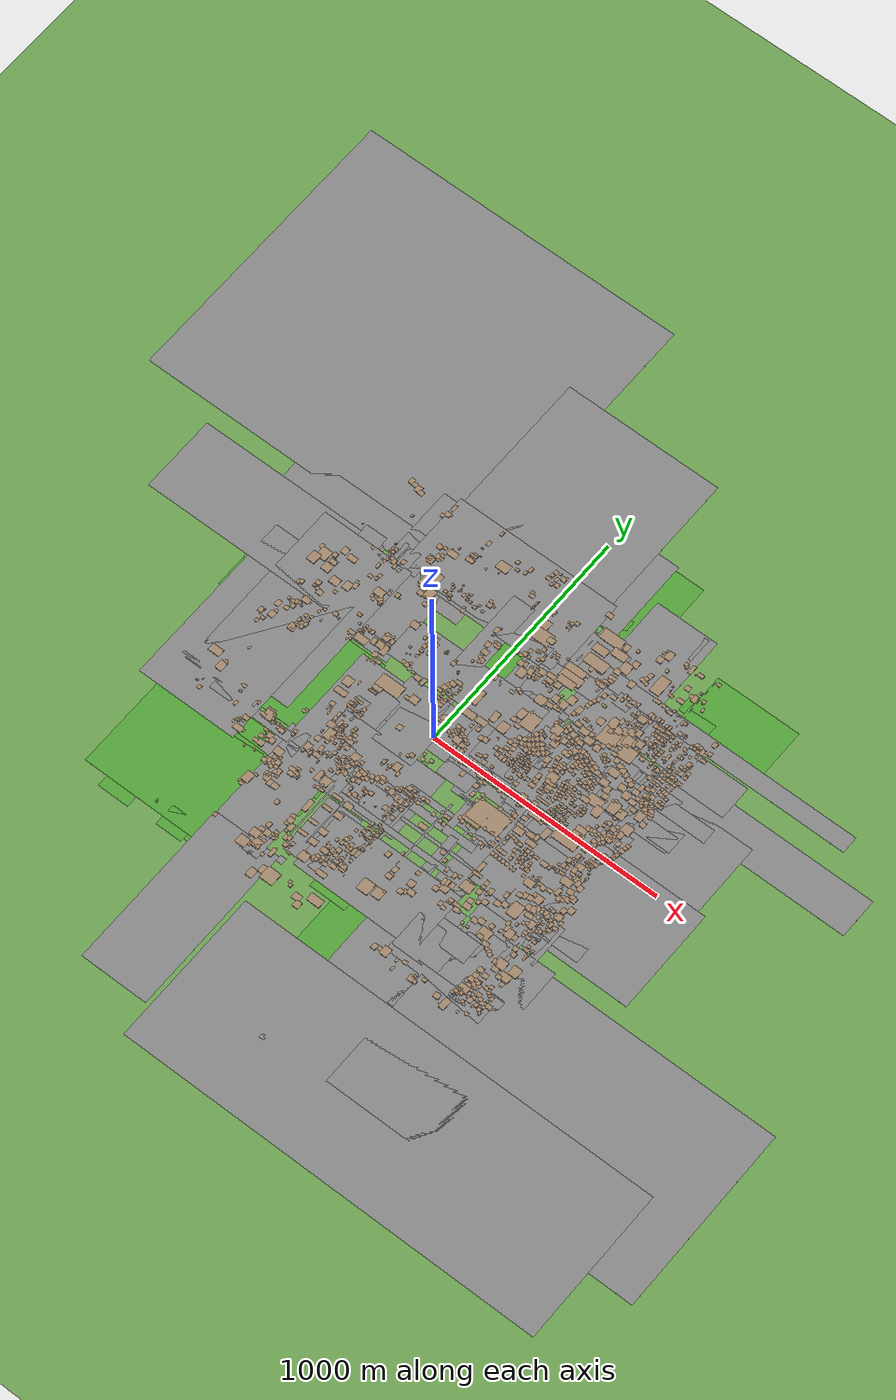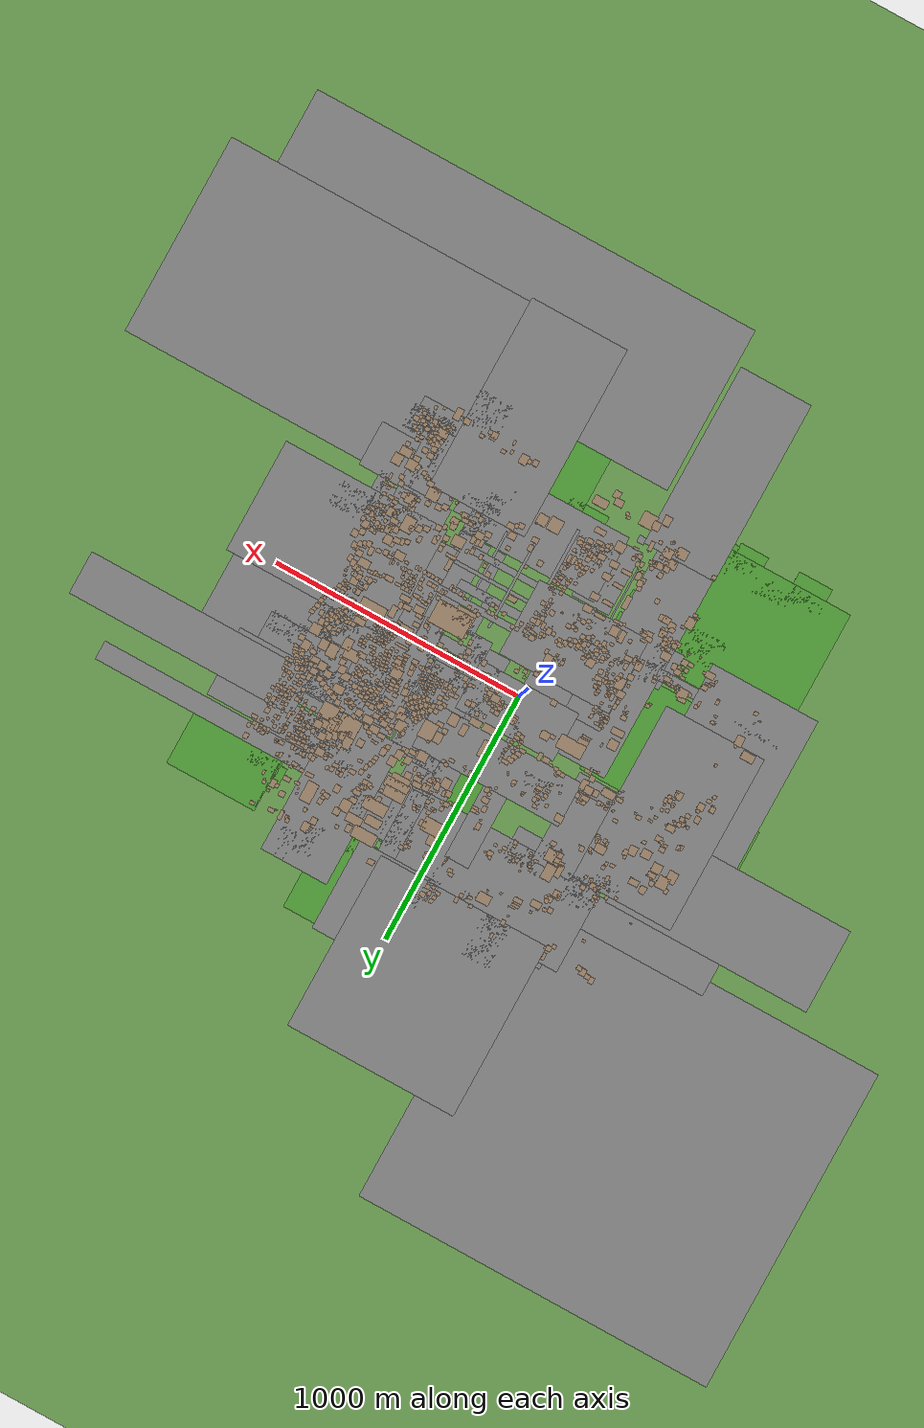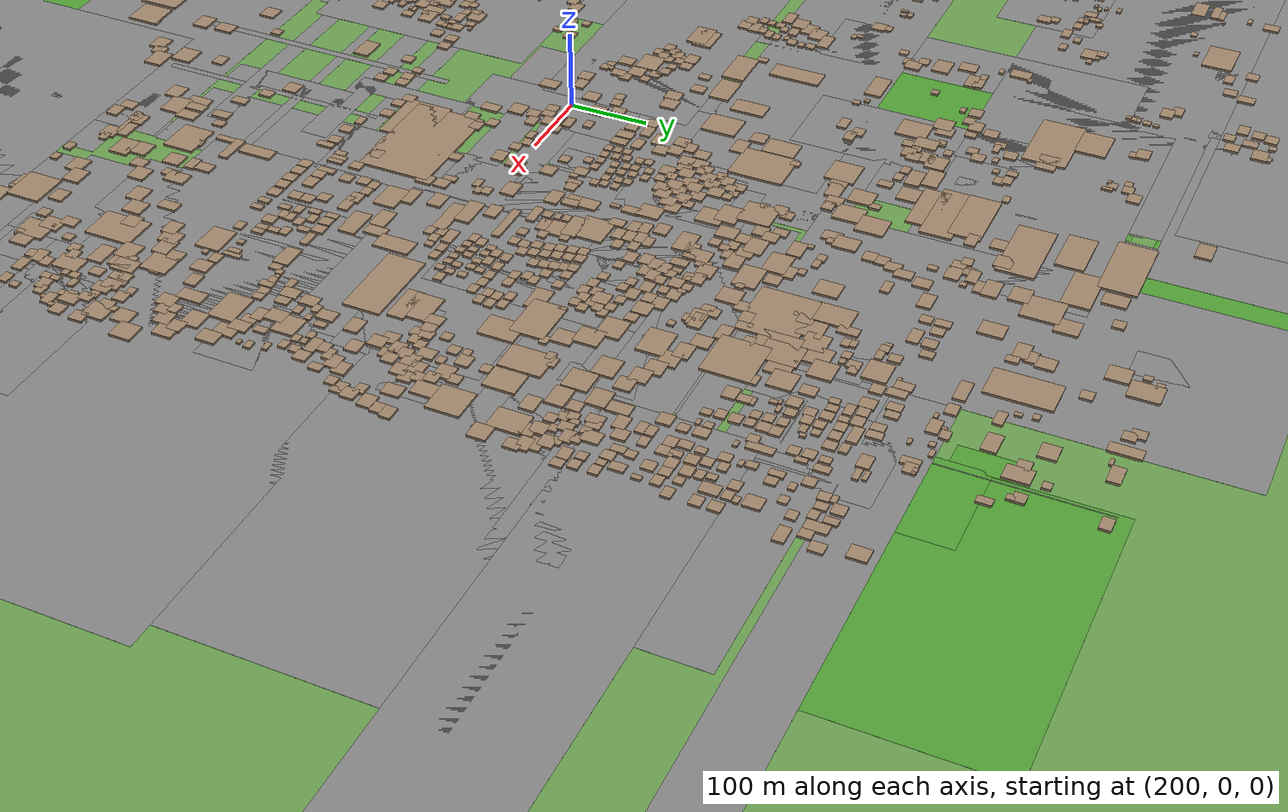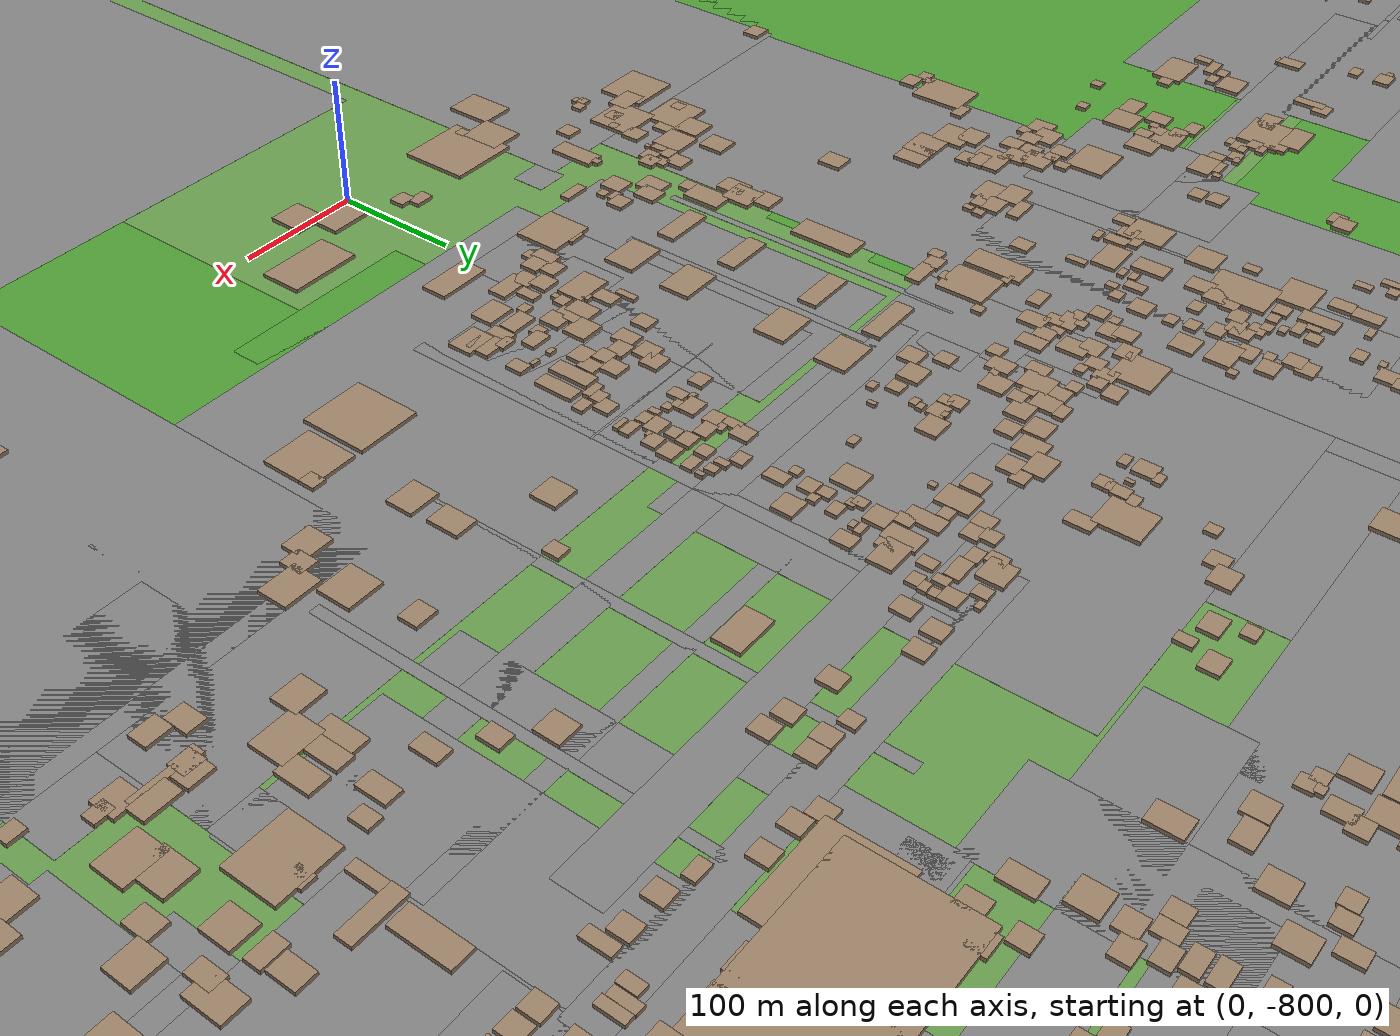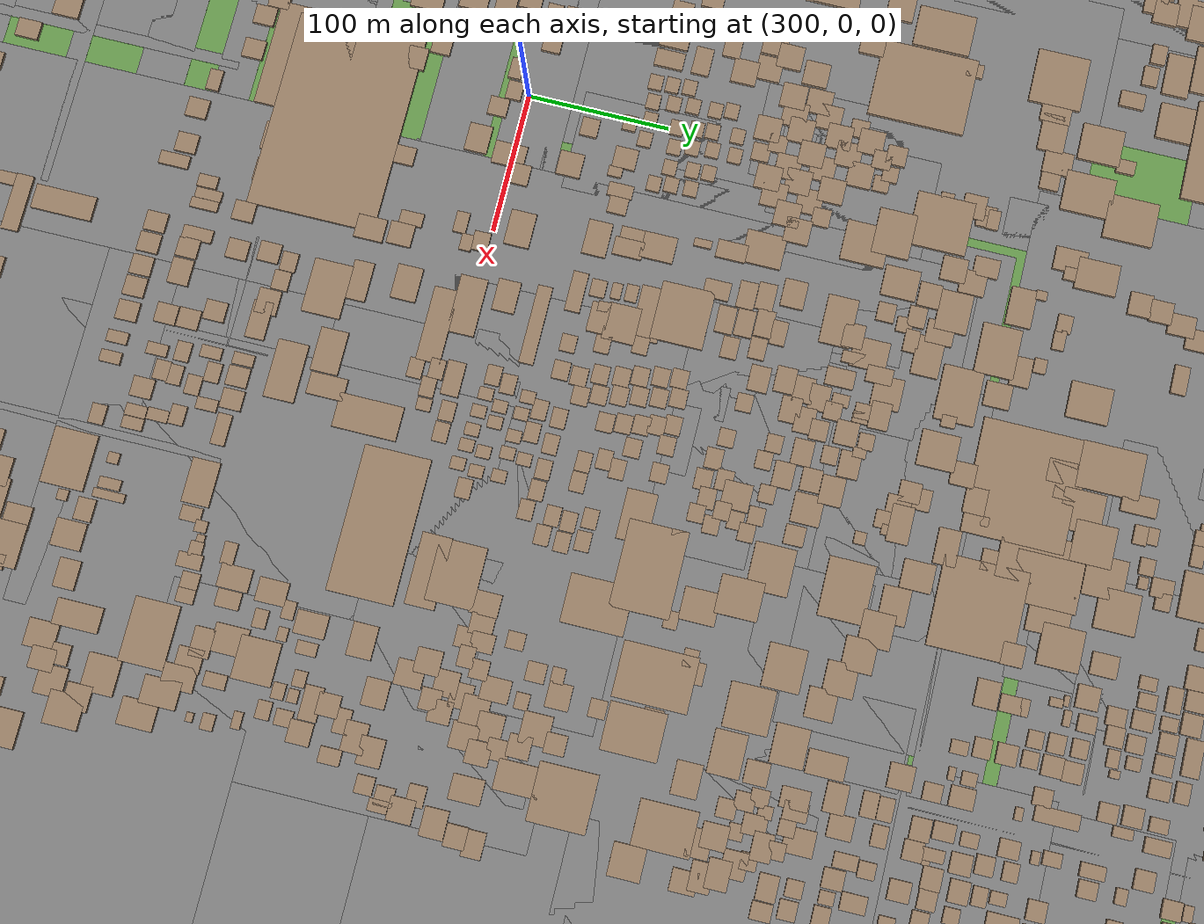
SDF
<?xml version="1.0" ?>
<sdf version="1.9">
  <world name="kimje_farmland">

    <!-- 물리 설정 -->
    <physics name="1ms" type="ignored">
      <max_step_size>0.001</max_step_size>
      <real_time_factor>1.0</real_time_factor>
    </physics>

    <!-- 플러그인 -->
    <plugin filename="gz-sim-physics-system" name="gz::sim::systems::Physics"/>
    <plugin filename="gz-sim-user-commands-system" name="gz::sim::systems::UserCommands"/>
    <plugin filename="gz-sim-scene-broadcaster-system" name="gz::sim::systems::SceneBroadcaster"/>
    <plugin filename="gz-sim-sensors-system" name="gz::sim::systems::Sensors">
      <render_engine>ogre2</render_engine>
    </plugin>
    <plugin filename="gz-sim-imu-system" name="gz::sim::systems::Imu"/>
    <plugin filename="gz-sim-air-pressure-system" name="gz::sim::systems::AirPressure"/>
    <plugin filename="gz-sim-magnetometer-system" name="gz::sim::systems::Magnetometer"/>

    <!-- GPS 원점 설정 -->
    <spherical_coordinates>
      <surface_model>EARTH_WGS84</surface_model>
      <latitude_deg>35.8022</latitude_deg>
      <longitude_deg>126.8799</longitude_deg>
      <elevation>10</elevation>
      <heading_deg>0</heading_deg>
    </spherical_coordinates>

    <!-- 조명 -->
    <light name="sun" type="directional">
      <cast_shadows>true</cast_shadows>
      <pose>0 0 500 0 0 0</pose>
      <diffuse>0.9 0.9 0.9 1</diffuse>
      <specular>0.2 0.2 0.2 1</specular>
      <direction>-0.5 0.1 -0.9</direction>
    </light>

    <!-- 지면 -->
    <model name="ground_plane">
      <static>true</static>
      <link name="link">
        <collision name="collision">
          <geometry><plane><normal>0 0 1</normal><size>2000 2000</size></plane></geometry>
        </collision>
        <visual name="visual">
          <geometry><plane><normal>0 0 1</normal><size>2000 2000</size></plane></geometry>
          <material>
            <ambient>0.4 0.6 0.3 1</ambient>
            <diffuse>0.4 0.6 0.3 1</diffuse>
          </material>
        </visual>
      </link>
    </model>

    <model name="osm_1">
      <static>true</static>
      <pose>-510.40 522.32 0.040 0 0 0</pose>
      <link name="link">
        <collision name="collision">
          <geometry>
            <box><size>93.81 112.27 0.080</size></box>
          </geometry>
        </collision>
        <visual name="visual">
          <geometry>
            <box><size>93.81 112.27 0.080</size></box>
          </geometry>
          <material>
            <ambient>0.5 0.5 0.5 1</ambient>
            <diffuse>0.5 0.5 0.5 1</diffuse>
          </material>
        </visual>
      </link>
    </model>

    <model name="osm_2">
      <static>true</static>
      <pose>848.91 -178.82 0.040 0 0 0</pose>
      <link name="link">
        <collision name="collision">
          <geometry>
            <box><size>665.56 447.34 0.080</size></box>
          </geometry>
        </collision>
        <visual name="visual">
          <geometry>
            <box><size>665.56 447.34 0.080</size></box>
          </geometry>
          <material>
            <ambient>0.5 0.5 0.5 1</ambient>
            <diffuse>0.5 0.5 0.5 1</diffuse>
          </material>
        </visual>
      </link>
    </model>

    <model name="osm_3">
      <static>true</static>
      <pose>-398.99 -369.41 0.040 0 0 0</pose>
      <link name="link">
        <collision name="collision">
          <geometry>
            <box><size>113.94 94.78 0.080</size></box>
          </geometry>
        </collision>
        <visual name="visual">
          <geometry>
            <box><size>113.94 94.78 0.080</size></box>
          </geometry>
          <material>
            <ambient>0.5 0.5 0.5 1</ambient>
            <diffuse>0.5 0.5 0.5 1</diffuse>
          </material>
        </visual>
      </link>
    </model>

    <model name="osm_4">
      <static>true</static>
      <pose>-48.92 253.60 0.040 0 0 0</pose>
      <link name="link">
        <collision name="collision">
          <geometry>
            <box><size>602.51 178.39 0.080</size></box>
          </geometry>
        </collision>
        <visual name="visual">
          <geometry>
            <box><size>602.51 178.39 0.080</size></box>
          </geometry>
          <material>
            <ambient>0.5 0.5 0.5 1</ambient>
            <diffuse>0.5 0.5 0.5 1</diffuse>
          </material>
        </visual>
      </link>
    </model>

    <model name="osm_5">
      <static>true</static>
      <pose>-86.99 -253.93 0.040 0 0 0</pose>
      <link name="link">
        <collision name="collision">
          <geometry>
            <box><size>451.55 303.87 0.080</size></box>
          </geometry>
        </collision>
        <visual name="visual">
          <geometry>
            <box><size>451.55 303.87 0.080</size></box>
          </geometry>
          <material>
            <ambient>0.5 0.5 0.5 1</ambient>
            <diffuse>0.5 0.5 0.5 1</diffuse>
          </material>
        </visual>
      </link>
    </model>

    <model name="osm_6">
      <static>true</static>
      <pose>832.18 -543.94 0.040 0 0 0</pose>
      <link name="link">
        <collision name="collision">
          <geometry>
            <box><size>158.71 176.58 0.080</size></box>
          </geometry>
        </collision>
        <visual name="visual">
          <geometry>
            <box><size>158.71 176.58 0.080</size></box>
          </geometry>
          <material>
            <ambient>0.5 0.5 0.5 1</ambient>
            <diffuse>0.5 0.5 0.5 1</diffuse>
          </material>
        </visual>
      </link>
    </model>

    <model name="osm_7">
      <static>true</static>
      <pose>457.62 -898.85 0.040 0 0 0</pose>
      <link name="link">
        <collision name="collision">
          <geometry>
            <box><size>392.42 770.92 0.080</size></box>
          </geometry>
        </collision>
        <visual name="visual">
          <geometry>
            <box><size>392.42 770.92 0.080</size></box>
          </geometry>
          <material>
            <ambient>0.5 0.5 0.5 1</ambient>
            <diffuse>0.5 0.5 0.5 1</diffuse>
          </material>
        </visual>
      </link>
    </model>

    <model name="osm_8">
      <static>true</static>
      <pose>841.23 -327.30 0.040 0 0 0</pose>
      <link name="link">
        <collision name="collision">
          <geometry>
            <box><size>201.72 97.64 0.080</size></box>
          </geometry>
        </collision>
        <visual name="visual">
          <geometry>
            <box><size>201.72 97.64 0.080</size></box>
          </geometry>
          <material>
            <ambient>0.5 0.5 0.5 1</ambient>
            <diffuse>0.5 0.5 0.5 1</diffuse>
          </material>
        </visual>
      </link>
    </model>

    <model name="osm_9">
      <static>true</static>
      <pose>814.35 -390.88 0.040 0 0 0</pose>
      <link name="link">
        <collision name="collision">
          <geometry>
            <box><size>34.50 181.24 0.080</size></box>
          </geometry>
        </collision>
        <visual name="visual">
          <geometry>
            <box><size>34.50 181.24 0.080</size></box>
          </geometry>
          <material>
            <ambient>0.5 0.5 0.5 1</ambient>
            <diffuse>0.5 0.5 0.5 1</diffuse>
          </material>
        </visual>
      </link>
    </model>

    <model name="osm_10">
      <static>true</static>
      <pose>251.50 -203.29 0.040 0 0 0</pose>
      <link name="link">
        <collision name="collision">
          <geometry>
            <box><size>393.94 26.91 0.080</size></box>
          </geometry>
        </collision>
        <visual name="visual">
          <geometry>
            <box><size>393.94 26.91 0.080</size></box>
          </geometry>
          <material>
            <ambient>0.5 0.5 0.5 1</ambient>
            <diffuse>0.5 0.5 0.5 1</diffuse>
          </material>
        </visual>
      </link>
    </model>

    <model name="osm_11">
      <static>true</static>
      <pose>706.21 -391.60 0.040 0 0 0</pose>
      <link name="link">
        <collision name="collision">
          <geometry>
            <box><size>85.42 135.34 0.080</size></box>
          </geometry>
        </collision>
        <visual name="visual">
          <geometry>
            <box><size>85.42 135.34 0.080</size></box>
          </geometry>
          <material>
            <ambient>0.5 0.5 0.5 1</ambient>
            <diffuse>0.5 0.5 0.5 1</diffuse>
          </material>
        </visual>
      </link>
    </model>

    <model name="osm_12">
      <static>true</static>
      <pose>416.88 645.44 0.040 0 0 0</pose>
      <link name="link">
        <collision name="collision">
          <geometry>
            <box><size>270.00 569.35 0.080</size></box>
          </geometry>
        </collision>
        <visual name="visual">
          <geometry>
            <box><size>270.00 569.35 0.080</size></box>
          </geometry>
          <material>
            <ambient>0.5 0.5 0.5 1</ambient>
            <diffuse>0.5 0.5 0.5 1</diffuse>
          </material>
        </visual>
      </link>
    </model>

    <model name="osm_13">
      <static>true</static>
      <pose>-18.24 48.11 0.040 0 0 0</pose>
      <link name="link">
        <collision name="collision">
          <geometry>
            <box><size>402.49 196.32 0.080</size></box>
          </geometry>
        </collision>
        <visual name="visual">
          <geometry>
            <box><size>402.49 196.32 0.080</size></box>
          </geometry>
          <material>
            <ambient>0.5 0.5 0.5 1</ambient>
            <diffuse>0.5 0.5 0.5 1</diffuse>
          </material>
        </visual>
      </link>
    </model>

    <model name="osm_14">
      <static>true</static>
      <pose>741.77 -10.32 0.040 0 0 0</pose>
      <link name="link">
        <collision name="collision">
          <geometry>
            <box><size>120.49 273.38 0.080</size></box>
          </geometry>
        </collision>
        <visual name="visual">
          <geometry>
            <box><size>120.49 273.38 0.080</size></box>
          </geometry>
          <material>
            <ambient>0.5 0.5 0.5 1</ambient>
            <diffuse>0.5 0.5 0.5 1</diffuse>
          </material>
        </visual>
      </link>
    </model>

    <model name="osm_15">
      <static>true</static>
      <pose>813.28 581.97 0.040 0 0 0</pose>
      <link name="link">
        <collision name="collision">
          <geometry>
            <box><size>1186.26 73.63 0.080</size></box>
          </geometry>
        </collision>
        <visual name="visual">
          <geometry>
            <box><size>1186.26 73.63 0.080</size></box>
          </geometry>
          <material>
            <ambient>0.5 0.5 0.5 1</ambient>
            <diffuse>0.5 0.5 0.5 1</diffuse>
          </material>
        </visual>
      </link>
    </model>

    <model name="osm_16">
      <static>true</static>
      <pose>555.60 311.85 0.040 0 0 0</pose>
      <link name="link">
        <collision name="collision">
          <geometry>
            <box><size>247.83 98.38 0.080</size></box>
          </geometry>
        </collision>
        <visual name="visual">
          <geometry>
            <box><size>247.83 98.38 0.080</size></box>
          </geometry>
          <material>
            <ambient>0.5 0.5 0.5 1</ambient>
            <diffuse>0.5 0.5 0.5 1</diffuse>
          </material>
        </visual>
      </link>
    </model>

    <model name="osm_17">
      <static>true</static>
      <pose>1144.47 371.12 0.040 0 0 0</pose>
      <link name="link">
        <collision name="collision">
          <geometry>
            <box><size>917.59 170.50 0.080</size></box>
          </geometry>
        </collision>
        <visual name="visual">
          <geometry>
            <box><size>917.59 170.50 0.080</size></box>
          </geometry>
          <material>
            <ambient>0.5 0.5 0.5 1</ambient>
            <diffuse>0.5 0.5 0.5 1</diffuse>
          </material>
        </visual>
      </link>
    </model>

    <model name="osm_18">
      <static>true</static>
      <pose>841.81 462.14 0.040 0 0 0</pose>
      <link name="link">
        <collision name="collision">
          <geometry>
            <box><size>300.90 147.02 0.080</size></box>
          </geometry>
        </collision>
        <visual name="visual">
          <geometry>
            <box><size>300.90 147.02 0.080</size></box>
          </geometry>
          <material>
            <ambient>0.5 0.5 0.5 1</ambient>
            <diffuse>0.5 0.5 0.5 1</diffuse>
          </material>
        </visual>
      </link>
    </model>

    <model name="osm_19">
      <static>true</static>
      <pose>868.79 299.28 0.040 0 0 0</pose>
      <link name="link">
        <collision name="collision">
          <geometry>
            <box><size>266.59 63.70 0.080</size></box>
          </geometry>
        </collision>
        <visual name="visual">
          <geometry>
            <box><size>266.59 63.70 0.080</size></box>
          </geometry>
          <material>
            <ambient>0.5 0.5 0.5 1</ambient>
            <diffuse>0.5 0.5 0.5 1</diffuse>
          </material>
        </visual>
      </link>
    </model>

    <model name="osm_20">
      <static>true</static>
      <pose>677.61 287.76 0.040 0 0 0</pose>
      <link name="link">
        <collision name="collision">
          <geometry>
            <box><size>56.59 130.14 0.080</size></box>
          </geometry>
        </collision>
        <visual name="visual">
          <geometry>
            <box><size>56.59 130.14 0.080</size></box>
          </geometry>
          <material>
            <ambient>0.5 0.5 0.5 1</ambient>
            <diffuse>0.5 0.5 0.5 1</diffuse>
          </material>
        </visual>
      </link>
    </model>

    <model name="osm_21">
      <static>true</static>
      <pose>845.04 188.35 0.040 0 0 0</pose>
      <link name="link">
        <collision name="collision">
          <geometry>
            <box><size>151.77 76.82 0.080</size></box>
          </geometry>
        </collision>
        <visual name="visual">
          <geometry>
            <box><size>151.77 76.82 0.080</size></box>
          </geometry>
          <material>
            <ambient>0.5 0.5 0.5 1</ambient>
            <diffuse>0.5 0.5 0.5 1</diffuse>
          </material>
        </visual>
      </link>
    </model>

    <model name="osm_22">
      <static>true</static>
      <pose>657.44 272.59 0.040 0 0 0</pose>
      <link name="link">
        <collision name="collision">
          <geometry>
            <box><size>162.70 73.04 0.080</size></box>
          </geometry>
        </collision>
        <visual name="visual">
          <geometry>
            <box><size>162.70 73.04 0.080</size></box>
          </geometry>
          <material>
            <ambient>0.5 0.5 0.5 1</ambient>
            <diffuse>0.5 0.5 0.5 1</diffuse>
          </material>
        </visual>
      </link>
    </model>

    <model name="osm_23">
      <static>true</static>
      <pose>495.71 254.00 0.040 0 0 0</pose>
      <link name="link">
        <collision name="collision">
          <geometry>
            <box><size>108.69 38.17 0.080</size></box>
          </geometry>
        </collision>
        <visual name="visual">
          <geometry>
            <box><size>108.69 38.17 0.080</size></box>
          </geometry>
          <material>
            <ambient>0.5 0.5 0.5 1</ambient>
            <diffuse>0.5 0.5 0.5 1</diffuse>
          </material>
        </visual>
      </link>
    </model>

    <model name="osm_24">
      <static>true</static>
      <pose>632.85 500.66 0.040 0 0 0</pose>
      <link name="link">
        <collision name="collision">
          <geometry>
            <box><size>196.78 171.66 0.080</size></box>
          </geometry>
        </collision>
        <visual name="visual">
          <geometry>
            <box><size>196.78 171.66 0.080</size></box>
          </geometry>
          <material>
            <ambient>0.5 0.5 0.5 1</ambient>
            <diffuse>0.5 0.5 0.5 1</diffuse>
          </material>
        </visual>
      </link>
    </model>

    <model name="osm_25">
      <static>true</static>
      <pose>784.99 449.15 0.040 0 0 0</pose>
      <link name="link">
        <collision name="collision">
          <geometry>
            <box><size>1.35 137.89 0.080</size></box>
          </geometry>
        </collision>
        <visual name="visual">
          <geometry>
            <box><size>1.35 137.89 0.080</size></box>
          </geometry>
          <material>
            <ambient>0.5 0.5 0.5 1</ambient>
            <diffuse>0.5 0.5 0.5 1</diffuse>
          </material>
        </visual>
      </link>
    </model>

    <model name="osm_26">
      <static>true</static>
      <pose>436.03 534.62 0.040 0 0 0</pose>
      <link name="link">
        <collision name="collision">
          <geometry>
            <box><size>62.67 54.41 0.080</size></box>
          </geometry>
        </collision>
        <visual name="visual">
          <geometry>
            <box><size>62.67 54.41 0.080</size></box>
          </geometry>
          <material>
            <ambient>0.5 0.5 0.5 1</ambient>
            <diffuse>0.5 0.5 0.5 1</diffuse>
          </material>
        </visual>
      </link>
    </model>

    <model name="osm_27">
      <static>true</static>
      <pose>710.72 469.01 0.040 0 0 0</pose>
      <link name="link">
        <collision name="collision">
          <geometry>
            <box><size>4.04 215.42 0.080</size></box>
          </geometry>
        </collision>
        <visual name="visual">
          <geometry>
            <box><size>4.04 215.42 0.080</size></box>
          </geometry>
          <material>
            <ambient>0.5 0.5 0.5 1</ambient>
            <diffuse>0.5 0.5 0.5 1</diffuse>
          </material>
        </visual>
      </link>
    </model>

    <model name="osm_28">
      <static>true</static>
      <pose>825.12 254.89 0.040 0 0 0</pose>
      <link name="link">
        <collision name="collision">
          <geometry>
            <box><size>210.04 188.95 0.080</size></box>
          </geometry>
        </collision>
        <visual name="visual">
          <geometry>
            <box><size>210.04 188.95 0.080</size></box>
          </geometry>
          <material>
            <ambient>0.5 0.5 0.5 1</ambient>
            <diffuse>0.5 0.5 0.5 1</diffuse>
          </material>
        </visual>
      </link>
    </model>

    <model name="osm_29">
      <static>true</static>
      <pose>755.11 88.00 0.040 0 0 0</pose>
      <link name="link">
        <collision name="collision">
          <geometry>
            <box><size>37.70 58.23 0.080</size></box>
          </geometry>
        </collision>
        <visual name="visual">
          <geometry>
            <box><size>37.70 58.23 0.080</size></box>
          </geometry>
          <material>
            <ambient>0.5 0.5 0.5 1</ambient>
            <diffuse>0.5 0.5 0.5 1</diffuse>
          </material>
        </visual>
      </link>
    </model>

    <model name="osm_30">
      <static>true</static>
      <pose>576.98 30.36 0.040 0 0 0</pose>
      <link name="link">
        <collision name="collision">
          <geometry>
            <box><size>281.01 239.29 0.080</size></box>
          </geometry>
        </collision>
        <visual name="visual">
          <geometry>
            <box><size>281.01 239.29 0.080</size></box>
          </geometry>
          <material>
            <ambient>0.5 0.5 0.5 1</ambient>
            <diffuse>0.5 0.5 0.5 1</diffuse>
          </material>
        </visual>
      </link>
    </model>

    <model name="osm_31">
      <static>true</static>
      <pose>402.13 263.94 0.040 0 0 0</pose>
      <link name="link">
        <collision name="collision">
          <geometry>
            <box><size>51.26 57.17 0.080</size></box>
          </geometry>
        </collision>
        <visual name="visual">
          <geometry>
            <box><size>51.26 57.17 0.080</size></box>
          </geometry>
          <material>
            <ambient>0.5 0.5 0.5 1</ambient>
            <diffuse>0.5 0.5 0.5 1</diffuse>
          </material>
        </visual>
      </link>
    </model>

    <model name="osm_32">
      <static>true</static>
      <pose>550.19 56.67 0.040 0 0 0</pose>
      <link name="link">
        <collision name="collision">
          <geometry>
            <box><size>70.86 31.63 0.080</size></box>
          </geometry>
        </collision>
        <visual name="visual">
          <geometry>
            <box><size>70.86 31.63 0.080</size></box>
          </geometry>
          <material>
            <ambient>0.5 0.5 0.5 1</ambient>
            <diffuse>0.5 0.5 0.5 1</diffuse>
          </material>
        </visual>
      </link>
    </model>

    <model name="osm_33">
      <static>true</static>
      <pose>722.31 101.72 0.040 0 0 0</pose>
      <link name="link">
        <collision name="collision">
          <geometry>
            <box><size>60.43 123.33 0.080</size></box>
          </geometry>
        </collision>
        <visual name="visual">
          <geometry>
            <box><size>60.43 123.33 0.080</size></box>
          </geometry>
          <material>
            <ambient>0.5 0.5 0.5 1</ambient>
            <diffuse>0.5 0.5 0.5 1</diffuse>
          </material>
        </visual>
      </link>
    </model>

    <model name="osm_34">
      <static>true</static>
      <pose>688.09 103.04 0.040 0 0 0</pose>
      <link name="link">
        <collision name="collision">
          <geometry>
            <box><size>135.03 108.14 0.080</size></box>
          </geometry>
        </collision>
        <visual name="visual">
          <geometry>
            <box><size>135.03 108.14 0.080</size></box>
          </geometry>
          <material>
            <ambient>0.5 0.5 0.5 1</ambient>
            <diffuse>0.5 0.5 0.5 1</diffuse>
          </material>
        </visual>
      </link>
    </model>

    <model name="osm_35">
      <static>true</static>
      <pose>528.19 114.59 0.040 0 0 0</pose>
      <link name="link">
        <collision name="collision">
          <geometry>
            <box><size>117.77 214.03 0.080</size></box>
          </geometry>
        </collision>
        <visual name="visual">
          <geometry>
            <box><size>117.77 214.03 0.080</size></box>
          </geometry>
          <material>
            <ambient>0.5 0.5 0.5 1</ambient>
            <diffuse>0.5 0.5 0.5 1</diffuse>
          </material>
        </visual>
      </link>
    </model>

    <model name="osm_36">
      <static>true</static>
      <pose>678.94 19.57 0.040 0 0 0</pose>
      <link name="link">
        <collision name="collision">
          <geometry>
            <box><size>98.88 86.79 0.080</size></box>
          </geometry>
        </collision>
        <visual name="visual">
          <geometry>
            <box><size>98.88 86.79 0.080</size></box>
          </geometry>
          <material>
            <ambient>0.5 0.5 0.5 1</ambient>
            <diffuse>0.5 0.5 0.5 1</diffuse>
          </material>
        </visual>
      </link>
    </model>

    <model name="osm_37">
      <static>true</static>
      <pose>472.38 92.51 0.040 0 0 0</pose>
      <link name="link">
        <collision name="collision">
          <geometry>
            <box><size>74.79 330.50 0.080</size></box>
          </geometry>
        </collision>
        <visual name="visual">
          <geometry>
            <box><size>74.79 330.50 0.080</size></box>
          </geometry>
          <material>
            <ambient>0.5 0.5 0.5 1</ambient>
            <diffuse>0.5 0.5 0.5 1</diffuse>
          </material>
        </visual>
      </link>
    </model>

    <model name="osm_38">
      <static>true</static>
      <pose>461.51 189.96 0.040 0 0 0</pose>
      <link name="link">
        <collision name="collision">
          <geometry>
            <box><size>97.93 111.68 0.080</size></box>
          </geometry>
        </collision>
        <visual name="visual">
          <geometry>
            <box><size>97.93 111.68 0.080</size></box>
          </geometry>
          <material>
            <ambient>0.5 0.5 0.5 1</ambient>
            <diffuse>0.5 0.5 0.5 1</diffuse>
          </material>
        </visual>
      </link>
    </model>

    <model name="osm_39">
      <static>true</static>
      <pose>510.89 151.69 0.040 0 0 0</pose>
      <link name="link">
        <collision name="collision">
          <geometry>
            <box><size>47.58 33.84 0.080</size></box>
          </geometry>
        </collision>
        <visual name="visual">
          <geometry>
            <box><size>47.58 33.84 0.080</size></box>
          </geometry>
          <material>
            <ambient>0.5 0.5 0.5 1</ambient>
            <diffuse>0.5 0.5 0.5 1</diffuse>
          </material>
        </visual>
      </link>
    </model>

    <model name="osm_40">
      <static>true</static>
      <pose>764.47 -364.30 0.040 0 0 0</pose>
      <link name="link">
        <collision name="collision">
          <geometry>
            <box><size>43.47 60.11 0.080</size></box>
          </geometry>
        </collision>
        <visual name="visual">
          <geometry>
            <box><size>43.47 60.11 0.080</size></box>
          </geometry>
          <material>
            <ambient>0.5 0.5 0.5 1</ambient>
            <diffuse>0.5 0.5 0.5 1</diffuse>
          </material>
        </visual>
      </link>
    </model>

    <model name="osm_41">
      <static>true</static>
      <pose>716.37 -492.19 0.040 0 0 0</pose>
      <link name="link">
        <collision name="collision">
          <geometry>
            <box><size>44.62 131.80 0.080</size></box>
          </geometry>
        </collision>
        <visual name="visual">
          <geometry>
            <box><size>44.62 131.80 0.080</size></box>
          </geometry>
          <material>
            <ambient>0.5 0.5 0.5 1</ambient>
            <diffuse>0.5 0.5 0.5 1</diffuse>
          </material>
        </visual>
      </link>
    </model>

    <model name="osm_42">
      <static>true</static>
      <pose>214.23 -18.59 0.040 0 0 0</pose>
      <link name="link">
        <collision name="collision">
          <geometry>
            <box><size>76.90 208.64 0.080</size></box>
          </geometry>
        </collision>
        <visual name="visual">
          <geometry>
            <box><size>76.90 208.64 0.080</size></box>
          </geometry>
          <material>
            <ambient>0.5 0.5 0.5 1</ambient>
            <diffuse>0.5 0.5 0.5 1</diffuse>
          </material>
        </visual>
      </link>
    </model>

    <model name="osm_43">
      <static>true</static>
      <pose>216.52 -345.34 0.040 0 0 0</pose>
      <link name="link">
        <collision name="collision">
          <geometry>
            <box><size>9.61 360.61 0.080</size></box>
          </geometry>
        </collision>
        <visual name="visual">
          <geometry>
            <box><size>9.61 360.61 0.080</size></box>
          </geometry>
          <material>
            <ambient>0.5 0.5 0.5 1</ambient>
            <diffuse>0.5 0.5 0.5 1</diffuse>
          </material>
        </visual>
      </link>
    </model>

    <model name="osm_44">
      <static>true</static>
      <pose>322.63 243.07 0.040 0 0 0</pose>
      <link name="link">
        <collision name="collision">
          <geometry>
            <box><size>87.27 94.97 0.080</size></box>
          </geometry>
        </collision>
        <visual name="visual">
          <geometry>
            <box><size>87.27 94.97 0.080</size></box>
          </geometry>
          <material>
            <ambient>0.5 0.5 0.5 1</ambient>
            <diffuse>0.5 0.5 0.5 1</diffuse>
          </material>
        </visual>
      </link>
    </model>

    <model name="osm_45">
      <static>true</static>
      <pose>292.19 -43.22 0.040 0 0 0</pose>
      <link name="link">
        <collision name="collision">
          <geometry>
            <box><size>128.96 45.24 0.080</size></box>
          </geometry>
        </collision>
        <visual name="visual">
          <geometry>
            <box><size>128.96 45.24 0.080</size></box>
          </geometry>
          <material>
            <ambient>0.5 0.5 0.5 1</ambient>
            <diffuse>0.5 0.5 0.5 1</diffuse>
          </material>
        </visual>
      </link>
    </model>

    <model name="osm_46">
      <static>true</static>
      <pose>144.42 -381.84 0.040 0 0 0</pose>
      <link name="link">
        <collision name="collision">
          <geometry>
            <box><size>526.87 25.09 0.080</size></box>
          </geometry>
        </collision>
        <visual name="visual">
          <geometry>
            <box><size>526.87 25.09 0.080</size></box>
          </geometry>
          <material>
            <ambient>0.5 0.5 0.5 1</ambient>
            <diffuse>0.5 0.5 0.5 1</diffuse>
          </material>
        </visual>
      </link>
    </model>

    <model name="osm_47">
      <static>true</static>
      <pose>172.74 -254.29 0.040 0 0 0</pose>
      <link name="link">
        <collision name="collision">
          <geometry>
            <box><size>433.24 34.90 0.080</size></box>
          </geometry>
        </collision>
        <visual name="visual">
          <geometry>
            <box><size>433.24 34.90 0.080</size></box>
          </geometry>
          <material>
            <ambient>0.5 0.5 0.5 1</ambient>
            <diffuse>0.5 0.5 0.5 1</diffuse>
          </material>
        </visual>
      </link>
    </model>

    <model name="osm_48">
      <static>true</static>
      <pose>336.06 166.73 0.040 0 0 0</pose>
      <link name="link">
        <collision name="collision">
          <geometry>
            <box><size>65.53 64.20 0.080</size></box>
          </geometry>
        </collision>
        <visual name="visual">
          <geometry>
            <box><size>65.53 64.20 0.080</size></box>
          </geometry>
          <material>
            <ambient>0.5 0.5 0.5 1</ambient>
            <diffuse>0.5 0.5 0.5 1</diffuse>
          </material>
        </visual>
      </link>
    </model>

    <model name="osm_49">
      <static>true</static>
      <pose>20.24 -594.63 0.040 0 0 0</pose>
      <link name="link">
        <collision name="collision">
          <geometry>
            <box><size>132.35 46.45 0.080</size></box>
          </geometry>
        </collision>
        <visual name="visual">
          <geometry>
            <box><size>132.35 46.45 0.080</size></box>
          </geometry>
          <material>
            <ambient>0.5 0.5 0.5 1</ambient>
            <diffuse>0.5 0.5 0.5 1</diffuse>
          </material>
        </visual>
      </link>
    </model>

    <model name="osm_50">
      <static>true</static>
      <pose>300.70 8.19 0.040 0 0 0</pose>
      <link name="link">
        <collision name="collision">
          <geometry>
            <box><size>211.02 45.11 0.080</size></box>
          </geometry>
        </collision>
        <visual name="visual">
          <geometry>
            <box><size>211.02 45.11 0.080</size></box>
          </geometry>
          <material>
            <ambient>0.5 0.5 0.5 1</ambient>
            <diffuse>0.5 0.5 0.5 1</diffuse>
          </material>
        </visual>
      </link>
    </model>

    <model name="osm_51">
      <static>true</static>
      <pose>598.61 -242.30 0.040 0 0 0</pose>
      <link name="link">
        <collision name="collision">
          <geometry>
            <box><size>5.69 207.16 0.080</size></box>
          </geometry>
        </collision>
        <visual name="visual">
          <geometry>
            <box><size>5.69 207.16 0.080</size></box>
          </geometry>
          <material>
            <ambient>0.5 0.5 0.5 1</ambient>
            <diffuse>0.5 0.5 0.5 1</diffuse>
          </material>
        </visual>
      </link>
    </model>

    <model name="osm_52">
      <static>true</static>
      <pose>303.56 220.24 0.040 0 0 0</pose>
      <link name="link">
        <collision name="collision">
          <geometry>
            <box><size>76.70 83.14 0.080</size></box>
          </geometry>
        </collision>
        <visual name="visual">
          <geometry>
            <box><size>76.70 83.14 0.080</size></box>
          </geometry>
          <material>
            <ambient>0.5 0.5 0.5 1</ambient>
            <diffuse>0.5 0.5 0.5 1</diffuse>
          </material>
        </visual>
      </link>
    </model>

    <model name="osm_53">
      <static>true</static>
      <pose>274.34 -316.10 0.040 0 0 0</pose>
      <link name="link">
        <collision name="collision">
          <geometry>
            <box><size>330.12 13.79 0.080</size></box>
          </geometry>
        </collision>
        <visual name="visual">
          <geometry>
            <box><size>330.12 13.79 0.080</size></box>
          </geometry>
          <material>
            <ambient>0.5 0.5 0.5 1</ambient>
            <diffuse>0.5 0.5 0.5 1</diffuse>
          </material>
        </visual>
      </link>
    </model>

    <model name="osm_54">
      <static>true</static>
      <pose>325.49 -352.69 0.040 0 0 0</pose>
      <link name="link">
        <collision name="collision">
          <geometry>
            <box><size>8.45 298.10 0.080</size></box>
          </geometry>
        </collision>
        <visual name="visual">
          <geometry>
            <box><size>8.45 298.10 0.080</size></box>
          </geometry>
          <material>
            <ambient>0.5 0.5 0.5 1</ambient>
            <diffuse>0.5 0.5 0.5 1</diffuse>
          </material>
        </visual>
      </link>
    </model>

    <model name="osm_55">
      <static>true</static>
      <pose>322.69 89.80 0.040 0 0 0</pose>
      <link name="link">
        <collision name="collision">
          <geometry>
            <box><size>71.40 103.72 0.080</size></box>
          </geometry>
        </collision>
        <visual name="visual">
          <geometry>
            <box><size>71.40 103.72 0.080</size></box>
          </geometry>
          <material>
            <ambient>0.5 0.5 0.5 1</ambient>
            <diffuse>0.5 0.5 0.5 1</diffuse>
          </material>
        </visual>
      </link>
    </model>

    <model name="osm_56">
      <static>true</static>
      <pose>102.39 -418.28 0.040 0 0 0</pose>
      <link name="link">
        <collision name="collision">
          <geometry>
            <box><size>11.99 423.56 0.080</size></box>
          </geometry>
        </collision>
        <visual name="visual">
          <geometry>
            <box><size>11.99 423.56 0.080</size></box>
          </geometry>
          <material>
            <ambient>0.5 0.5 0.5 1</ambient>
            <diffuse>0.5 0.5 0.5 1</diffuse>
          </material>
        </visual>
      </link>
    </model>

    <model name="osm_57">
      <static>true</static>
      <pose>264.60 -189.44 0.040 0 0 0</pose>
      <link name="link">
        <collision name="collision">
          <geometry>
            <box><size>29.40 152.93 0.080</size></box>
          </geometry>
        </collision>
        <visual name="visual">
          <geometry>
            <box><size>29.40 152.93 0.080</size></box>
          </geometry>
          <material>
            <ambient>0.5 0.5 0.5 1</ambient>
            <diffuse>0.5 0.5 0.5 1</diffuse>
          </material>
        </visual>
      </link>
    </model>

    <model name="osm_58">
      <static>true</static>
      <pose>-176.56 -283.62 0.040 0 0 0</pose>
      <link name="link">
        <collision name="collision">
          <geometry>
            <box><size>89.69 36.30 0.080</size></box>
          </geometry>
        </collision>
        <visual name="visual">
          <geometry>
            <box><size>89.69 36.30 0.080</size></box>
          </geometry>
          <material>
            <ambient>0.5 0.5 0.5 1</ambient>
            <diffuse>0.5 0.5 0.5 1</diffuse>
          </material>
        </visual>
      </link>
    </model>

    <model name="osm_59">
      <static>true</static>
      <pose>606.28 -749.03 0.040 0 0 0</pose>
      <link name="link">
        <collision name="collision">
          <geometry>
            <box><size>430.55 77.18 0.080</size></box>
          </geometry>
        </collision>
        <visual name="visual">
          <geometry>
            <box><size>430.55 77.18 0.080</size></box>
          </geometry>
          <material>
            <ambient>0.5 0.5 0.5 1</ambient>
            <diffuse>0.5 0.5 0.5 1</diffuse>
          </material>
        </visual>
      </link>
    </model>

    <model name="osm_60">
      <static>true</static>
      <pose>158.74 -65.54 0.040 0 0 0</pose>
      <link name="link">
        <collision name="collision">
          <geometry>
            <box><size>136.66 67.44 0.080</size></box>
          </geometry>
        </collision>
        <visual name="visual">
          <geometry>
            <box><size>136.66 67.44 0.080</size></box>
          </geometry>
          <material>
            <ambient>0.5 0.5 0.5 1</ambient>
            <diffuse>0.5 0.5 0.5 1</diffuse>
          </material>
        </visual>
      </link>
    </model>

    <model name="osm_61">
      <static>true</static>
      <pose>266.02 -132.14 0.040 0 0 0</pose>
      <link name="link">
        <collision name="collision">
          <geometry>
            <box><size>15.99 27.55 0.080</size></box>
          </geometry>
        </collision>
        <visual name="visual">
          <geometry>
            <box><size>15.99 27.55 0.080</size></box>
          </geometry>
          <material>
            <ambient>0.5 0.5 0.5 1</ambient>
            <diffuse>0.5 0.5 0.5 1</diffuse>
          </material>
        </visual>
      </link>
    </model>

    <model name="osm_62">
      <static>true</static>
      <pose>467.78 -576.32 0.040 0 0 0</pose>
      <link name="link">
        <collision name="collision">
          <geometry>
            <box><size>338.75 96.90 0.080</size></box>
          </geometry>
        </collision>
        <visual name="visual">
          <geometry>
            <box><size>338.75 96.90 0.080</size></box>
          </geometry>
          <material>
            <ambient>0.5 0.5 0.5 1</ambient>
            <diffuse>0.5 0.5 0.5 1</diffuse>
          </material>
        </visual>
      </link>
    </model>

    <model name="osm_63">
      <static>true</static>
      <pose>-240.82 -180.44 0.040 0 0 0</pose>
      <link name="link">
        <collision name="collision">
          <geometry>
            <box><size>150.24 300.62 0.080</size></box>
          </geometry>
        </collision>
        <visual name="visual">
          <geometry>
            <box><size>150.24 300.62 0.080</size></box>
          </geometry>
          <material>
            <ambient>0.5 0.5 0.5 1</ambient>
            <diffuse>0.5 0.5 0.5 1</diffuse>
          </material>
        </visual>
      </link>
    </model>

    <model name="osm_64">
      <static>true</static>
      <pose>593.54 -833.12 0.040 0 0 0</pose>
      <link name="link">
        <collision name="collision">
          <geometry>
            <box><size>142.78 145.29 0.080</size></box>
          </geometry>
        </collision>
        <visual name="visual">
          <geometry>
            <box><size>142.78 145.29 0.080</size></box>
          </geometry>
          <material>
            <ambient>0.5 0.5 0.5 1</ambient>
            <diffuse>0.5 0.5 0.5 1</diffuse>
          </material>
        </visual>
      </link>
    </model>

    <model name="osm_65">
      <static>true</static>
      <pose>491.71 -641.08 0.040 0 0 0</pose>
      <link name="link">
        <collision name="collision">
          <geometry>
            <box><size>195.21 157.25 0.080</size></box>
          </geometry>
        </collision>
        <visual name="visual">
          <geometry>
            <box><size>195.21 157.25 0.080</size></box>
          </geometry>
          <material>
            <ambient>0.5 0.5 0.5 1</ambient>
            <diffuse>0.5 0.5 0.5 1</diffuse>
          </material>
        </visual>
      </link>
    </model>

    <model name="osm_66">
      <static>true</static>
      <pose>-402.18 344.55 0.040 0 0 0</pose>
      <link name="link">
        <collision name="collision">
          <geometry>
            <box><size>159.92 299.17 0.080</size></box>
          </geometry>
        </collision>
        <visual name="visual">
          <geometry>
            <box><size>159.92 299.17 0.080</size></box>
          </geometry>
          <material>
            <ambient>0.5 0.5 0.5 1</ambient>
            <diffuse>0.5 0.5 0.5 1</diffuse>
          </material>
        </visual>
      </link>
    </model>

    <model name="osm_67">
      <static>true</static>
      <pose>490.43 868.63 0.040 0 0 0</pose>
      <link name="link">
        <collision name="collision">
          <geometry>
            <box><size>60.84 105.36 0.080</size></box>
          </geometry>
        </collision>
        <visual name="visual">
          <geometry>
            <box><size>60.84 105.36 0.080</size></box>
          </geometry>
          <material>
            <ambient>0.5 0.5 0.5 1</ambient>
            <diffuse>0.5 0.5 0.5 1</diffuse>
          </material>
        </visual>
      </link>
    </model>

    <model name="osm_68">
      <static>true</static>
      <pose>-68.04 760.36 0.040 0 0 0</pose>
      <link name="link">
        <collision name="collision">
          <geometry>
            <box><size>23.88 65.93 0.080</size></box>
          </geometry>
        </collision>
        <visual name="visual">
          <geometry>
            <box><size>23.88 65.93 0.080</size></box>
          </geometry>
          <material>
            <ambient>0.5 0.5 0.5 1</ambient>
            <diffuse>0.5 0.5 0.5 1</diffuse>
          </material>
        </visual>
      </link>
    </model>

    <model name="osm_69">
      <static>true</static>
      <pose>-323.58 829.98 0.040 0 0 0</pose>
      <link name="link">
        <collision name="collision">
          <geometry>
            <box><size>110.56 175.26 0.080</size></box>
          </geometry>
        </collision>
        <visual name="visual">
          <geometry>
            <box><size>110.56 175.26 0.080</size></box>
          </geometry>
          <material>
            <ambient>0.5 0.5 0.5 1</ambient>
            <diffuse>0.5 0.5 0.5 1</diffuse>
          </material>
        </visual>
      </link>
    </model>

    <model name="osm_70">
      <static>true</static>
      <pose>-181.48 1091.65 0.040 0 0 0</pose>
      <link name="link">
        <collision name="collision">
          <geometry>
            <box><size>682.88 700.15 0.080</size></box>
          </geometry>
        </collision>
        <visual name="visual">
          <geometry>
            <box><size>682.88 700.15 0.080</size></box>
          </geometry>
          <material>
            <ambient>0.5 0.5 0.5 1</ambient>
            <diffuse>0.5 0.5 0.5 1</diffuse>
          </material>
        </visual>
      </link>
    </model>

    <model name="osm_71">
      <static>true</static>
      <pose>-41.13 788.18 0.040 0 0 0</pose>
      <link name="link">
        <collision name="collision">
          <geometry>
            <box><size>24.86 55.10 0.080</size></box>
          </geometry>
        </collision>
        <visual name="visual">
          <geometry>
            <box><size>24.86 55.10 0.080</size></box>
          </geometry>
          <material>
            <ambient>0.5 0.5 0.5 1</ambient>
            <diffuse>0.5 0.5 0.5 1</diffuse>
          </material>
        </visual>
      </link>
    </model>

    <model name="osm_72">
      <static>true</static>
      <pose>-683.59 124.20 0.040 0 0 0</pose>
      <link name="link">
        <collision name="collision">
          <geometry>
            <box><size>403.75 704.18 0.080</size></box>
          </geometry>
        </collision>
        <visual name="visual">
          <geometry>
            <box><size>403.75 704.18 0.080</size></box>
          </geometry>
          <material>
            <ambient>0.5 0.5 0.5 1</ambient>
            <diffuse>0.5 0.5 0.5 1</diffuse>
          </material>
        </visual>
      </link>
    </model>

    <model name="osm_73">
      <static>true</static>
      <pose>97.49 910.80 0.040 0 0 0</pose>
      <link name="link">
        <collision name="collision">
          <geometry>
            <box><size>310.08 360.59 0.080</size></box>
          </geometry>
        </collision>
        <visual name="visual">
          <geometry>
            <box><size>310.08 360.59 0.080</size></box>
          </geometry>
          <material>
            <ambient>0.5 0.5 0.5 1</ambient>
            <diffuse>0.5 0.5 0.5 1</diffuse>
          </material>
        </visual>
      </link>
    </model>

    <model name="osm_74">
      <static>true</static>
      <pose>-28.52 824.47 0.040 0 0 0</pose>
      <link name="link">
        <collision name="collision">
          <geometry>
            <box><size>28.11 53.99 0.080</size></box>
          </geometry>
        </collision>
        <visual name="visual">
          <geometry>
            <box><size>28.11 53.99 0.080</size></box>
          </geometry>
          <material>
            <ambient>0.5 0.5 0.5 1</ambient>
            <diffuse>0.5 0.5 0.5 1</diffuse>
          </material>
        </visual>
      </link>
    </model>

    <model name="osm_75">
      <static>true</static>
      <pose>-90.51 431.63 0.040 0 0 0</pose>
      <link name="link">
        <collision name="collision">
          <geometry>
            <box><size>95.61 402.24 0.080</size></box>
          </geometry>
        </collision>
        <visual name="visual">
          <geometry>
            <box><size>95.61 402.24 0.080</size></box>
          </geometry>
          <material>
            <ambient>0.5 0.5 0.5 1</ambient>
            <diffuse>0.5 0.5 0.5 1</diffuse>
          </material>
        </visual>
      </link>
    </model>

    <model name="osm_76">
      <static>true</static>
      <pose>-244.86 633.80 0.040 0 0 0</pose>
      <link name="link">
        <collision name="collision">
          <geometry>
            <box><size>707.66 343.91 0.080</size></box>
          </geometry>
        </collision>
        <visual name="visual">
          <geometry>
            <box><size>707.66 343.91 0.080</size></box>
          </geometry>
          <material>
            <ambient>0.5 0.5 0.5 1</ambient>
            <diffuse>0.5 0.5 0.5 1</diffuse>
          </material>
        </visual>
      </link>
    </model>

    <model name="osm_77">
      <static>true</static>
      <pose>-1043.21 331.19 0.040 0 0 0</pose>
      <link name="link">
        <collision name="collision">
          <geometry>
            <box><size>829.08 332.94 0.080</size></box>
          </geometry>
        </collision>
        <visual name="visual">
          <geometry>
            <box><size>829.08 332.94 0.080</size></box>
          </geometry>
          <material>
            <ambient>0.5 0.5 0.5 1</ambient>
            <diffuse>0.5 0.5 0.5 1</diffuse>
          </material>
        </visual>
      </link>
    </model>

    <model name="osm_78">
      <static>true</static>
      <pose>-801.93 558.22 0.040 0 0 0</pose>
      <link name="link">
        <collision name="collision">
          <geometry>
            <box><size>597.90 136.83 0.080</size></box>
          </geometry>
        </collision>
        <visual name="visual">
          <geometry>
            <box><size>597.90 136.83 0.080</size></box>
          </geometry>
          <material>
            <ambient>0.5 0.5 0.5 1</ambient>
            <diffuse>0.5 0.5 0.5 1</diffuse>
          </material>
        </visual>
      </link>
    </model>

    <model name="osm_79">
      <static>true</static>
      <pose>-190.80 248.13 0.040 0 0 0</pose>
      <link name="link">
        <collision name="collision">
          <geometry>
            <box><size>86.01 47.51 0.080</size></box>
          </geometry>
        </collision>
        <visual name="visual">
          <geometry>
            <box><size>86.01 47.51 0.080</size></box>
          </geometry>
          <material>
            <ambient>0.5 0.5 0.5 1</ambient>
            <diffuse>0.5 0.5 0.5 1</diffuse>
          </material>
        </visual>
      </link>
    </model>

    <model name="osm_80">
      <static>true</static>
      <pose>-244.82 270.52 0.040 0 0 0</pose>
      <link name="link">
        <collision name="collision">
          <geometry>
            <box><size>21.00 111.88 0.080</size></box>
          </geometry>
        </collision>
        <visual name="visual">
          <geometry>
            <box><size>21.00 111.88 0.080</size></box>
          </geometry>
          <material>
            <ambient>0.5 0.5 0.5 1</ambient>
            <diffuse>0.5 0.5 0.5 1</diffuse>
          </material>
        </visual>
      </link>
    </model>

    <model name="osm_81">
      <static>true</static>
      <pose>-314.82 472.62 0.040 0 0 0</pose>
      <link name="link">
        <collision name="collision">
          <geometry>
            <box><size>179.62 129.05 0.080</size></box>
          </geometry>
        </collision>
        <visual name="visual">
          <geometry>
            <box><size>179.62 129.05 0.080</size></box>
          </geometry>
          <material>
            <ambient>0.5 0.5 0.5 1</ambient>
            <diffuse>0.5 0.5 0.5 1</diffuse>
          </material>
        </visual>
      </link>
    </model>

    <model name="osm_82">
      <static>true</static>
      <pose>-180.37 651.19 0.040 0 0 0</pose>
      <link name="link">
        <collision name="collision">
          <geometry>
            <box><size>717.23 350.45 0.080</size></box>
          </geometry>
        </collision>
        <visual name="visual">
          <geometry>
            <box><size>717.23 350.45 0.080</size></box>
          </geometry>
          <material>
            <ambient>0.5 0.5 0.5 1</ambient>
            <diffuse>0.5 0.5 0.5 1</diffuse>
          </material>
        </visual>
      </link>
    </model>

    <model name="osm_83">
      <static>true</static>
      <pose>-772.64 -57.62 0.040 0 0 0</pose>
      <link name="link">
        <collision name="collision">
          <geometry>
            <box><size>432.89 768.16 0.080</size></box>
          </geometry>
        </collision>
        <visual name="visual">
          <geometry>
            <box><size>432.89 768.16 0.080</size></box>
          </geometry>
          <material>
            <ambient>0.5 0.5 0.5 1</ambient>
            <diffuse>0.5 0.5 0.5 1</diffuse>
          </material>
        </visual>
      </link>
    </model>

    <model name="osm_84">
      <static>true</static>
      <pose>786.82 -214.13 0.040 0 0 0</pose>
      <link name="link">
        <collision name="collision">
          <geometry>
            <box><size>689.80 282.66 0.080</size></box>
          </geometry>
        </collision>
        <visual name="visual">
          <geometry>
            <box><size>689.80 282.66 0.080</size></box>
          </geometry>
          <material>
            <ambient>0.5 0.5 0.5 1</ambient>
            <diffuse>0.5 0.5 0.5 1</diffuse>
          </material>
        </visual>
      </link>
    </model>

    <model name="osm_85">
      <static>true</static>
      <pose>1216.68 -869.51 0.040 0 0 0</pose>
      <link name="link">
        <collision name="collision">
          <geometry>
            <box><size>1335.01 797.52 0.080</size></box>
          </geometry>
        </collision>
        <visual name="visual">
          <geometry>
            <box><size>1335.01 797.52 0.080</size></box>
          </geometry>
          <material>
            <ambient>0.5 0.5 0.5 1</ambient>
            <diffuse>0.5 0.5 0.5 1</diffuse>
          </material>
        </visual>
      </link>
    </model>

    <model name="osm_86">
      <static>true</static>
      <pose>588.24 487.39 0.040 0 0 0</pose>
      <link name="link">
        <collision name="collision">
          <geometry>
            <box><size>52.77 167.38 0.080</size></box>
          </geometry>
        </collision>
        <visual name="visual">
          <geometry>
            <box><size>52.77 167.38 0.080</size></box>
          </geometry>
          <material>
            <ambient>0.5 0.5 0.5 1</ambient>
            <diffuse>0.5 0.5 0.5 1</diffuse>
          </material>
        </visual>
      </link>
    </model>

    <model name="osm_87">
      <static>true</static>
      <pose>-189.08 722.50 0.040 0 0 0</pose>
      <link name="link">
        <collision name="collision">
          <geometry>
            <box><size>53.18 38.65 0.080</size></box>
          </geometry>
        </collision>
        <visual name="visual">
          <geometry>
            <box><size>53.18 38.65 0.080</size></box>
          </geometry>
          <material>
            <ambient>0.5 0.5 0.5 1</ambient>
            <diffuse>0.5 0.5 0.5 1</diffuse>
          </material>
        </visual>
      </link>
    </model>

    <model name="osm_88">
      <static>true</static>
      <pose>522.05 -170.82 0.040 0 0 0</pose>
      <link name="link">
        <collision name="collision">
          <geometry>
            <box><size>1.39 86.46 0.080</size></box>
          </geometry>
        </collision>
        <visual name="visual">
          <geometry>
            <box><size>1.39 86.46 0.080</size></box>
          </geometry>
          <material>
            <ambient>0.5 0.5 0.5 1</ambient>
            <diffuse>0.5 0.5 0.5 1</diffuse>
          </material>
        </visual>
      </link>
    </model>

    <model name="osm_89">
      <static>true</static>
      <pose>482.59 -158.55 0.040 0 0 0</pose>
      <link name="link">
        <collision name="collision">
          <geometry>
            <box><size>79.70 5.27 0.080</size></box>
          </geometry>
        </collision>
        <visual name="visual">
          <geometry>
            <box><size>79.70 5.27 0.080</size></box>
          </geometry>
          <material>
            <ambient>0.5 0.5 0.5 1</ambient>
            <diffuse>0.5 0.5 0.5 1</diffuse>
          </material>
        </visual>
      </link>
    </model>

    <model name="osm_90">
      <static>true</static>
      <pose>-81.72 -44.00 0.040 0 0 0</pose>
      <link name="link">
        <collision name="collision">
          <geometry>
            <box><size>178.89 182.53 0.080</size></box>
          </geometry>
        </collision>
        <visual name="visual">
          <geometry>
            <box><size>178.89 182.53 0.080</size></box>
          </geometry>
          <material>
            <ambient>0.5 0.5 0.5 1</ambient>
            <diffuse>0.5 0.5 0.5 1</diffuse>
          </material>
        </visual>
      </link>
    </model>

    <model name="osm_91">
      <static>true</static>
      <pose>412.07 -44.82 0.040 0 0 0</pose>
      <link name="link">
        <collision name="collision">
          <geometry>
            <box><size>124.96 758.23 0.080</size></box>
          </geometry>
        </collision>
        <visual name="visual">
          <geometry>
            <box><size>124.96 758.23 0.080</size></box>
          </geometry>
          <material>
            <ambient>0.5 0.5 0.5 1</ambient>
            <diffuse>0.5 0.5 0.5 1</diffuse>
          </material>
        </visual>
      </link>
    </model>

    <model name="osm_92">
      <static>true</static>
      <pose>-272.02 -1066.42 0.040 0 0 0</pose>
      <link name="link">
        <collision name="collision">
          <geometry>
            <box><size>290.07 725.68 0.080</size></box>
          </geometry>
        </collision>
        <visual name="visual">
          <geometry>
            <box><size>290.07 725.68 0.080</size></box>
          </geometry>
          <material>
            <ambient>0.5 0.5 0.5 1</ambient>
            <diffuse>0.5 0.5 0.5 1</diffuse>
          </material>
        </visual>
      </link>
    </model>

    <model name="osm_93">
      <static>true</static>
      <pose>793.04 -1238.91 0.040 0 0 0</pose>
      <link name="link">
        <collision name="collision">
          <geometry>
            <box><size>1804.56 658.52 0.080</size></box>
          </geometry>
        </collision>
        <visual name="visual">
          <geometry>
            <box><size>1804.56 658.52 0.080</size></box>
          </geometry>
          <material>
            <ambient>0.5 0.5 0.5 1</ambient>
            <diffuse>0.5 0.5 0.5 1</diffuse>
          </material>
        </visual>
      </link>
    </model>

    <model name="osm_94">
      <static>true</static>
      <pose>742.05 187.37 0.040 0 0 0</pose>
      <link name="link">
        <collision name="collision">
          <geometry>
            <box><size>818.71 334.66 0.080</size></box>
          </geometry>
        </collision>
        <visual name="visual">
          <geometry>
            <box><size>818.71 334.66 0.080</size></box>
          </geometry>
          <material>
            <ambient>0.5 0.5 0.5 1</ambient>
            <diffuse>0.5 0.5 0.5 1</diffuse>
          </material>
        </visual>
      </link>
    </model>

    <model name="osm_95">
      <static>true</static>
      <pose>200.32 -561.10 0.040 0 0 0</pose>
      <link name="link">
        <collision name="collision">
          <geometry>
            <box><size>544.47 266.11 0.080</size></box>
          </geometry>
        </collision>
        <visual name="visual">
          <geometry>
            <box><size>544.47 266.11 0.080</size></box>
          </geometry>
          <material>
            <ambient>0.5 0.5 0.5 1</ambient>
            <diffuse>0.5 0.5 0.5 1</diffuse>
          </material>
        </visual>
      </link>
    </model>

    <model name="osm_96">
      <static>true</static>
      <pose>-573.87 -315.27 0.040 0 0 0</pose>
      <link name="link">
        <collision name="collision">
          <geometry>
            <box><size>356.05 41.66 0.080</size></box>
          </geometry>
        </collision>
        <visual name="visual">
          <geometry>
            <box><size>356.05 41.66 0.080</size></box>
          </geometry>
          <material>
            <ambient>0.5 0.5 0.5 1</ambient>
            <diffuse>0.5 0.5 0.5 1</diffuse>
          </material>
        </visual>
      </link>
    </model>

    <model name="osm_97">
      <static>true</static>
      <pose>416.93 818.05 0.040 0 0 0</pose>
      <link name="link">
        <collision name="collision">
          <geometry>
            <box><size>69.04 121.03 0.080</size></box>
          </geometry>
        </collision>
        <visual name="visual">
          <geometry>
            <box><size>69.04 121.03 0.080</size></box>
          </geometry>
          <material>
            <ambient>0.5 0.5 0.5 1</ambient>
            <diffuse>0.5 0.5 0.5 1</diffuse>
          </material>
        </visual>
      </link>
    </model>

    <model name="osm_98">
      <static>true</static>
      <pose>-40.50 695.89 0.040 0 0 0</pose>
      <link name="link">
        <collision name="collision">
          <geometry>
            <box><size>7.44 41.09 0.080</size></box>
          </geometry>
        </collision>
        <visual name="visual">
          <geometry>
            <box><size>7.44 41.09 0.080</size></box>
          </geometry>
          <material>
            <ambient>0.5 0.5 0.5 1</ambient>
            <diffuse>0.5 0.5 0.5 1</diffuse>
          </material>
        </visual>
      </link>
    </model>

    <model name="osm_99">
      <static>true</static>
      <pose>156.71 578.80 0.040 0 0 0</pose>
      <link name="link">
        <collision name="collision">
          <geometry>
            <box><size>385.17 227.95 0.080</size></box>
          </geometry>
        </collision>
        <visual name="visual">
          <geometry>
            <box><size>385.17 227.95 0.080</size></box>
          </geometry>
          <material>
            <ambient>0.5 0.5 0.5 1</ambient>
            <diffuse>0.5 0.5 0.5 1</diffuse>
          </material>
        </visual>
      </link>
    </model>

    <model name="osm_100">
      <static>true</static>
      <pose>-38.52 726.79 0.040 0 0 0</pose>
      <link name="link">
        <collision name="collision">
          <geometry>
            <box><size>17.57 46.62 0.080</size></box>
          </geometry>
        </collision>
        <visual name="visual">
          <geometry>
            <box><size>17.57 46.62 0.080</size></box>
          </geometry>
          <material>
            <ambient>0.5 0.5 0.5 1</ambient>
            <diffuse>0.5 0.5 0.5 1</diffuse>
          </material>
        </visual>
      </link>
    </model>

    <model name="osm_101">
      <static>true</static>
      <pose>643.38 381.67 0.040 0 0 0</pose>
      <link name="link">
        <collision name="collision">
          <geometry>
            <box><size>123.81 47.24 0.080</size></box>
          </geometry>
        </collision>
        <visual name="visual">
          <geometry>
            <box><size>123.81 47.24 0.080</size></box>
          </geometry>
          <material>
            <ambient>0.5 0.5 0.5 1</ambient>
            <diffuse>0.5 0.5 0.5 1</diffuse>
          </material>
        </visual>
      </link>
    </model>

    <model name="osm_102">
      <static>true</static>
      <pose>-1078.89 1212.90 0.040 0 0 0</pose>
      <link name="link">
        <collision name="collision">
          <geometry>
            <box><size>1431.67 1287.50 0.080</size></box>
          </geometry>
        </collision>
        <visual name="visual">
          <geometry>
            <box><size>1431.67 1287.50 0.080</size></box>
          </geometry>
          <material>
            <ambient>0.5 0.5 0.5 1</ambient>
            <diffuse>0.5 0.5 0.5 1</diffuse>
          </material>
        </visual>
      </link>
    </model>

    <model name="osm_103">
      <static>true</static>
      <pose>454.55 -423.58 0.040 0 0 0</pose>
      <link name="link">
        <collision name="collision">
          <geometry>
            <box><size>36.00 35.97 0.080</size></box>
          </geometry>
        </collision>
        <visual name="visual">
          <geometry>
            <box><size>36.00 35.97 0.080</size></box>
          </geometry>
          <material>
            <ambient>0.5 0.5 0.5 1</ambient>
            <diffuse>0.5 0.5 0.5 1</diffuse>
          </material>
        </visual>
      </link>
    </model>

    <model name="osm_104">
      <static>true</static>
      <pose>231.89 209.43 0.040 0 0 0</pose>
      <link name="link">
        <collision name="collision">
          <geometry>
            <box><size>189.30 364.63 0.080</size></box>
          </geometry>
        </collision>
        <visual name="visual">
          <geometry>
            <box><size>189.30 364.63 0.080</size></box>
          </geometry>
          <material>
            <ambient>0.5 0.5 0.5 1</ambient>
            <diffuse>0.5 0.5 0.5 1</diffuse>
          </material>
        </visual>
      </link>
    </model>

    <model name="osm_105">
      <static>true</static>
      <pose>103.67 -32.48 0.040 0 0 0</pose>
      <link name="link">
        <collision name="collision">
          <geometry>
            <box><size>25.59 25.34 0.080</size></box>
          </geometry>
        </collision>
        <visual name="visual">
          <geometry>
            <box><size>25.59 25.34 0.080</size></box>
          </geometry>
          <material>
            <ambient>0.5 0.5 0.5 1</ambient>
            <diffuse>0.5 0.5 0.5 1</diffuse>
          </material>
        </visual>
      </link>
    </model>

    <model name="osm_106">
      <static>true</static>
      <pose>-153.56 -488.07 0.040 0 0 0</pose>
      <link name="link">
        <collision name="collision">
          <geometry>
            <box><size>5.78 245.81 0.080</size></box>
          </geometry>
        </collision>
        <visual name="visual">
          <geometry>
            <box><size>5.78 245.81 0.080</size></box>
          </geometry>
          <material>
            <ambient>0.5 0.5 0.5 1</ambient>
            <diffuse>0.5 0.5 0.5 1</diffuse>
          </material>
        </visual>
      </link>
    </model>

    <model name="osm_107">
      <static>true</static>
      <pose>-64.33 -540.54 0.040 0 0 0</pose>
      <link name="link">
        <collision name="collision">
          <geometry>
            <box><size>152.93 256.90 0.080</size></box>
          </geometry>
        </collision>
        <visual name="visual">
          <geometry>
            <box><size>152.93 256.90 0.080</size></box>
          </geometry>
          <material>
            <ambient>0.5 0.5 0.5 1</ambient>
            <diffuse>0.5 0.5 0.5 1</diffuse>
          </material>
        </visual>
      </link>
    </model>

    <model name="osm_108">
      <static>true</static>
      <pose>304.50 -341.20 0.040 0 0 0</pose>
      <link name="link">
        <collision name="collision">
          <geometry>
            <box><size>34.34 164.85 0.080</size></box>
          </geometry>
        </collision>
        <visual name="visual">
          <geometry>
            <box><size>34.34 164.85 0.080</size></box>
          </geometry>
          <material>
            <ambient>0.5 0.5 0.5 1</ambient>
            <diffuse>0.5 0.5 0.5 1</diffuse>
          </material>
        </visual>
      </link>
    </model>

    <model name="osm_109">
      <static>true</static>
      <pose>387.00 -54.41 0.040 0 0 0</pose>
      <link name="link">
        <collision name="collision">
          <geometry>
            <box><size>77.46 28.04 0.080</size></box>
          </geometry>
        </collision>
        <visual name="visual">
          <geometry>
            <box><size>77.46 28.04 0.080</size></box>
          </geometry>
          <material>
            <ambient>0.5 0.5 0.5 1</ambient>
            <diffuse>0.5 0.5 0.5 1</diffuse>
          </material>
        </visual>
      </link>
    </model>

    <model name="osm_110">
      <static>true</static>
      <pose>309.56 123.73 0.040 0 0 0</pose>
      <link name="link">
        <collision name="collision">
          <geometry>
            <box><size>34.09 45.24 0.080</size></box>
          </geometry>
        </collision>
        <visual name="visual">
          <geometry>
            <box><size>34.09 45.24 0.080</size></box>
          </geometry>
          <material>
            <ambient>0.5 0.5 0.5 1</ambient>
            <diffuse>0.5 0.5 0.5 1</diffuse>
          </material>
        </visual>
      </link>
    </model>

    <model name="osm_111">
      <static>true</static>
      <pose>729.28 248.20 0.040 0 0 0</pose>
      <link name="link">
        <collision name="collision">
          <geometry>
            <box><size>46.05 115.32 0.080</size></box>
          </geometry>
        </collision>
        <visual name="visual">
          <geometry>
            <box><size>46.05 115.32 0.080</size></box>
          </geometry>
          <material>
            <ambient>0.5 0.5 0.5 1</ambient>
            <diffuse>0.5 0.5 0.5 1</diffuse>
          </material>
        </visual>
      </link>
    </model>

    <model name="osm_112">
      <static>true</static>
      <pose>678.42 -647.27 0.040 0 0 0</pose>
      <link name="link">
        <collision name="collision">
          <geometry>
            <box><size>30.29 180.92 0.080</size></box>
          </geometry>
        </collision>
        <visual name="visual">
          <geometry>
            <box><size>30.29 180.92 0.080</size></box>
          </geometry>
          <material>
            <ambient>0.5 0.5 0.5 1</ambient>
            <diffuse>0.5 0.5 0.5 1</diffuse>
          </material>
        </visual>
      </link>
    </model>

    <model name="osm_113">
      <static>true</static>
      <pose>368.15 -624.36 0.040 0 0 0</pose>
      <link name="link">
        <collision name="collision">
          <geometry>
            <box><size>3.70 42.74 0.080</size></box>
          </geometry>
        </collision>
        <visual name="visual">
          <geometry>
            <box><size>3.70 42.74 0.080</size></box>
          </geometry>
          <material>
            <ambient>0.5 0.5 0.5 1</ambient>
            <diffuse>0.5 0.5 0.5 1</diffuse>
          </material>
        </visual>
      </link>
    </model>

    <model name="osm_114">
      <static>true</static>
      <pose>410.18 -514.47 0.040 0 0 0</pose>
      <link name="link">
        <collision name="collision">
          <geometry>
            <box><size>78.25 164.78 0.080</size></box>
          </geometry>
        </collision>
        <visual name="visual">
          <geometry>
            <box><size>78.25 164.78 0.080</size></box>
          </geometry>
          <material>
            <ambient>0.5 0.5 0.5 1</ambient>
            <diffuse>0.5 0.5 0.5 1</diffuse>
          </material>
        </visual>
      </link>
    </model>

    <model name="osm_115">
      <static>true</static>
      <pose>617.06 -421.43 0.040 0 0 0</pose>
      <link name="link">
        <collision name="collision">
          <geometry>
            <box><size>158.34 99.22 0.080</size></box>
          </geometry>
        </collision>
        <visual name="visual">
          <geometry>
            <box><size>158.34 99.22 0.080</size></box>
          </geometry>
          <material>
            <ambient>0.5 0.5 0.5 1</ambient>
            <diffuse>0.5 0.5 0.5 1</diffuse>
          </material>
        </visual>
      </link>
    </model>

    <model name="osm_116">
      <static>true</static>
      <pose>462.26 -513.09 0.040 0 0 0</pose>
      <link name="link">
        <collision name="collision">
          <geometry>
            <box><size>139.58 80.26 0.080</size></box>
          </geometry>
        </collision>
        <visual name="visual">
          <geometry>
            <box><size>139.58 80.26 0.080</size></box>
          </geometry>
          <material>
            <ambient>0.5 0.5 0.5 1</ambient>
            <diffuse>0.5 0.5 0.5 1</diffuse>
          </material>
        </visual>
      </link>
    </model>

    <model name="osm_117">
      <static>true</static>
      <pose>780.68 -378.61 0.040 0 0 0</pose>
      <link name="link">
        <collision name="collision">
          <geometry>
            <box><size>70.03 128.39 0.080</size></box>
          </geometry>
        </collision>
        <visual name="visual">
          <geometry>
            <box><size>70.03 128.39 0.080</size></box>
          </geometry>
          <material>
            <ambient>0.5 0.5 0.5 1</ambient>
            <diffuse>0.5 0.5 0.5 1</diffuse>
          </material>
        </visual>
      </link>
    </model>

    <model name="osm_118">
      <static>true</static>
      <pose>583.56 -227.54 0.040 0 0 0</pose>
      <link name="link">
        <collision name="collision">
          <geometry>
            <box><size>279.80 52.63 0.080</size></box>
          </geometry>
        </collision>
        <visual name="visual">
          <geometry>
            <box><size>279.80 52.63 0.080</size></box>
          </geometry>
          <material>
            <ambient>0.5 0.5 0.5 1</ambient>
            <diffuse>0.5 0.5 0.5 1</diffuse>
          </material>
        </visual>
      </link>
    </model>

    <model name="osm_119">
      <static>true</static>
      <pose>-125.84 -309.64 0.040 0 0 0</pose>
      <link name="link">
        <collision name="collision">
          <geometry>
            <box><size>14.23 31.51 0.080</size></box>
          </geometry>
        </collision>
        <visual name="visual">
          <geometry>
            <box><size>14.23 31.51 0.080</size></box>
          </geometry>
          <material>
            <ambient>0.5 0.5 0.5 1</ambient>
            <diffuse>0.5 0.5 0.5 1</diffuse>
          </material>
        </visual>
      </link>
    </model>

    <model name="osm_120">
      <static>true</static>
      <pose>-132.73 -271.68 0.040 0 0 0</pose>
      <link name="link">
        <collision name="collision">
          <geometry>
            <box><size>13.80 61.15 0.080</size></box>
          </geometry>
        </collision>
        <visual name="visual">
          <geometry>
            <box><size>13.80 61.15 0.080</size></box>
          </geometry>
          <material>
            <ambient>0.5 0.5 0.5 1</ambient>
            <diffuse>0.5 0.5 0.5 1</diffuse>
          </material>
        </visual>
      </link>
    </model>

    <model name="osm_121">
      <static>true</static>
      <pose>-108.99 -346.88 0.040 0 0 0</pose>
      <link name="link">
        <collision name="collision">
          <geometry>
            <box><size>25.13 40.97 0.080</size></box>
          </geometry>
        </collision>
        <visual name="visual">
          <geometry>
            <box><size>25.13 40.97 0.080</size></box>
          </geometry>
          <material>
            <ambient>0.5 0.5 0.5 1</ambient>
            <diffuse>0.5 0.5 0.5 1</diffuse>
          </material>
        </visual>
      </link>
    </model>

    <model name="osm_122">
      <static>true</static>
      <pose>-487.27 165.93 0.040 0 0 0</pose>
      <link name="link">
        <collision name="collision">
          <geometry>
            <box><size>328.39 67.48 0.080</size></box>
          </geometry>
        </collision>
        <visual name="visual">
          <geometry>
            <box><size>328.39 67.48 0.080</size></box>
          </geometry>
          <material>
            <ambient>0.5 0.5 0.5 1</ambient>
            <diffuse>0.5 0.5 0.5 1</diffuse>
          </material>
        </visual>
      </link>
    </model>

    <model name="osm_123">
      <static>true</static>
      <pose>-45.68 165.60 0.040 0 0 0</pose>
      <link name="link">
        <collision name="collision">
          <geometry>
            <box><size>18.99 172.09 0.080</size></box>
          </geometry>
        </collision>
        <visual name="visual">
          <geometry>
            <box><size>18.99 172.09 0.080</size></box>
          </geometry>
          <material>
            <ambient>0.5 0.5 0.5 1</ambient>
            <diffuse>0.5 0.5 0.5 1</diffuse>
          </material>
        </visual>
      </link>
    </model>

    <model name="osm_124">
      <static>true</static>
      <pose>284.02 197.73 0.040 0 0 0</pose>
      <link name="link">
        <collision name="collision">
          <geometry>
            <box><size>68.20 72.76 0.080</size></box>
          </geometry>
        </collision>
        <visual name="visual">
          <geometry>
            <box><size>68.20 72.76 0.080</size></box>
          </geometry>
          <material>
            <ambient>0.5 0.5 0.5 1</ambient>
            <diffuse>0.5 0.5 0.5 1</diffuse>
          </material>
        </visual>
      </link>
    </model>

    <model name="osm_125">
      <static>true</static>
      <pose>302.59 221.21 0.040 0 0 0</pose>
      <link name="link">
        <collision name="collision">
          <geometry>
            <box><size>45.05 38.42 0.080</size></box>
          </geometry>
        </collision>
        <visual name="visual">
          <geometry>
            <box><size>45.05 38.42 0.080</size></box>
          </geometry>
          <material>
            <ambient>0.5 0.5 0.5 1</ambient>
            <diffuse>0.5 0.5 0.5 1</diffuse>
          </material>
        </visual>
      </link>
    </model>

    <model name="osm_126">
      <static>true</static>
      <pose>305.71 356.47 0.040 0 0 0</pose>
      <link name="link">
        <collision name="collision">
          <geometry>
            <box><size>29.51 29.51 0.080</size></box>
          </geometry>
        </collision>
        <visual name="visual">
          <geometry>
            <box><size>29.51 29.51 0.080</size></box>
          </geometry>
          <material>
            <ambient>0.5 0.5 0.5 1</ambient>
            <diffuse>0.5 0.5 0.5 1</diffuse>
          </material>
        </visual>
      </link>
    </model>

    <model name="osm_127">
      <static>true</static>
      <pose>642.89 690.37 0.040 0 0 0</pose>
      <link name="link">
        <collision name="collision">
          <geometry>
            <box><size>1.12 234.24 0.080</size></box>
          </geometry>
        </collision>
        <visual name="visual">
          <geometry>
            <box><size>1.12 234.24 0.080</size></box>
          </geometry>
          <material>
            <ambient>0.5 0.5 0.5 1</ambient>
            <diffuse>0.5 0.5 0.5 1</diffuse>
          </material>
        </visual>
      </link>
    </model>

    <model name="osm_128">
      <static>true</static>
      <pose>615.73 -22.93 1.500 0 0 0</pose>
      <link name="link">
        <collision name="collision">
          <geometry>
            <box><size>101.24 46.49 3.000</size></box>
          </geometry>
        </collision>
        <visual name="visual">
          <geometry>
            <box><size>101.24 46.49 3.000</size></box>
          </geometry>
          <material>
            <ambient>0.6 0.5 0.4 1</ambient>
            <diffuse>0.6 0.5 0.4 1</diffuse>
          </material>
        </visual>
      </link>
    </model>

    <model name="osm_129">
      <static>true</static>
      <pose>536.43 492.57 0.040 0 0 0</pose>
      <link name="link">
        <collision name="collision">
          <geometry>
            <box><size>194.18 82.37 0.080</size></box>
          </geometry>
        </collision>
        <visual name="visual">
          <geometry>
            <box><size>194.18 82.37 0.080</size></box>
          </geometry>
          <material>
            <ambient>0.5 0.5 0.5 1</ambient>
            <diffuse>0.5 0.5 0.5 1</diffuse>
          </material>
        </visual>
      </link>
    </model>

    <model name="osm_130">
      <static>true</static>
      <pose>639.78 471.04 0.040 0 0 0</pose>
      <link name="link">
        <collision name="collision">
          <geometry>
            <box><size>75.17 1.01 0.080</size></box>
          </geometry>
        </collision>
        <visual name="visual">
          <geometry>
            <box><size>75.17 1.01 0.080</size></box>
          </geometry>
          <material>
            <ambient>0.5 0.5 0.5 1</ambient>
            <diffuse>0.5 0.5 0.5 1</diffuse>
          </material>
        </visual>
      </link>
    </model>

    <model name="osm_131">
      <static>true</static>
      <pose>480.58 173.67 0.040 0 0 0</pose>
      <link name="link">
        <collision name="collision">
          <geometry>
            <box><size>23.74 22.22 0.080</size></box>
          </geometry>
        </collision>
        <visual name="visual">
          <geometry>
            <box><size>23.74 22.22 0.080</size></box>
          </geometry>
          <material>
            <ambient>0.5 0.5 0.5 1</ambient>
            <diffuse>0.5 0.5 0.5 1</diffuse>
          </material>
        </visual>
      </link>
    </model>

    <model name="osm_132">
      <static>true</static>
      <pose>557.17 38.74 0.040 0 0 0</pose>
      <link name="link">
        <collision name="collision">
          <geometry>
            <box><size>117.05 11.84 0.080</size></box>
          </geometry>
        </collision>
        <visual name="visual">
          <geometry>
            <box><size>117.05 11.84 0.080</size></box>
          </geometry>
          <material>
            <ambient>0.5 0.5 0.5 1</ambient>
            <diffuse>0.5 0.5 0.5 1</diffuse>
          </material>
        </visual>
      </link>
    </model>

    <model name="osm_133">
      <static>true</static>
      <pose>560.43 289.28 0.040 0 0 0</pose>
      <link name="link">
        <collision name="collision">
          <geometry>
            <box><size>16.93 38.25 0.080</size></box>
          </geometry>
        </collision>
        <visual name="visual">
          <geometry>
            <box><size>16.93 38.25 0.080</size></box>
          </geometry>
          <material>
            <ambient>0.5 0.5 0.5 1</ambient>
            <diffuse>0.5 0.5 0.5 1</diffuse>
          </material>
        </visual>
      </link>
    </model>

    <model name="osm_134">
      <static>true</static>
      <pose>586.83 347.22 0.040 0 0 0</pose>
      <link name="link">
        <collision name="collision">
          <geometry>
            <box><size>37.46 80.37 0.080</size></box>
          </geometry>
        </collision>
        <visual name="visual">
          <geometry>
            <box><size>37.46 80.37 0.080</size></box>
          </geometry>
          <material>
            <ambient>0.5 0.5 0.5 1</ambient>
            <diffuse>0.5 0.5 0.5 1</diffuse>
          </material>
        </visual>
      </link>
    </model>

    <model name="osm_135">
      <static>true</static>
      <pose>546.81 -49.35 1.500 0 0 0</pose>
      <link name="link">
        <collision name="collision">
          <geometry>
            <box><size>24.00 44.96 3.000</size></box>
          </geometry>
        </collision>
        <visual name="visual">
          <geometry>
            <box><size>24.00 44.96 3.000</size></box>
          </geometry>
          <material>
            <ambient>0.6 0.5 0.4 1</ambient>
            <diffuse>0.6 0.5 0.4 1</diffuse>
          </material>
        </visual>
      </link>
    </model>

    <model name="osm_136">
      <static>true</static>
      <pose>637.83 17.27 1.500 0 0 0</pose>
      <link name="link">
        <collision name="collision">
          <geometry>
            <box><size>49.55 20.71 3.000</size></box>
          </geometry>
        </collision>
        <visual name="visual">
          <geometry>
            <box><size>49.55 20.71 3.000</size></box>
          </geometry>
          <material>
            <ambient>0.6 0.5 0.4 1</ambient>
            <diffuse>0.6 0.5 0.4 1</diffuse>
          </material>
        </visual>
      </link>
    </model>

    <model name="osm_137">
      <static>true</static>
      <pose>635.31 35.71 1.500 0 0 0</pose>
      <link name="link">
        <collision name="collision">
          <geometry>
            <box><size>42.85 32.95 3.000</size></box>
          </geometry>
        </collision>
        <visual name="visual">
          <geometry>
            <box><size>42.85 32.95 3.000</size></box>
          </geometry>
          <material>
            <ambient>0.6 0.5 0.4 1</ambient>
            <diffuse>0.6 0.5 0.4 1</diffuse>
          </material>
        </visual>
      </link>
    </model>

    <model name="osm_138">
      <static>true</static>
      <pose>754.02 -700.17 0.040 0 0 0</pose>
      <link name="link">
        <collision name="collision">
          <geometry>
            <box><size>171.15 100.21 0.080</size></box>
          </geometry>
        </collision>
        <visual name="visual">
          <geometry>
            <box><size>171.15 100.21 0.080</size></box>
          </geometry>
          <material>
            <ambient>0.5 0.5 0.5 1</ambient>
            <diffuse>0.5 0.5 0.5 1</diffuse>
          </material>
        </visual>
      </link>
    </model>

    <model name="osm_139">
      <static>true</static>
      <pose>760.29 -704.11 0.040 0 0 0</pose>
      <link name="link">
        <collision name="collision">
          <geometry>
            <box><size>167.99 99.29 0.080</size></box>
          </geometry>
        </collision>
        <visual name="visual">
          <geometry>
            <box><size>167.99 99.29 0.080</size></box>
          </geometry>
          <material>
            <ambient>0.5 0.5 0.5 1</ambient>
            <diffuse>0.5 0.5 0.5 1</diffuse>
          </material>
        </visual>
      </link>
    </model>

    <model name="osm_140">
      <static>true</static>
      <pose>-250.95 67.74 1.500 0 0 0</pose>
      <link name="link">
        <collision name="collision">
          <geometry>
            <box><size>101.71 53.53 3.000</size></box>
          </geometry>
        </collision>
        <visual name="visual">
          <geometry>
            <box><size>101.71 53.53 3.000</size></box>
          </geometry>
          <material>
            <ambient>0.6 0.5 0.4 1</ambient>
            <diffuse>0.6 0.5 0.4 1</diffuse>
          </material>
        </visual>
      </link>
    </model>

    <model name="osm_141">
      <static>true</static>
      <pose>378.70 -993.03 0.025 0 0 0</pose>
      <link name="link">
        <collision name="collision">
          <geometry>
            <box><size>511.87 649.01 0.050</size></box>
          </geometry>
        </collision>
        <visual name="visual">
          <geometry>
            <box><size>511.87 649.01 0.050</size></box>
          </geometry>
          <material>
            <ambient>0.3 0.6 0.2 1</ambient>
            <diffuse>0.3 0.6 0.2 1</diffuse>
          </material>
        </visual>
      </link>
    </model>

    <model name="osm_142">
      <static>true</static>
      <pose>623.32 -488.18 1.500 0 0 0</pose>
      <link name="link">
        <collision name="collision">
          <geometry>
            <box><size>47.30 43.63 3.000</size></box>
          </geometry>
        </collision>
        <visual name="visual">
          <geometry>
            <box><size>47.30 43.63 3.000</size></box>
          </geometry>
          <material>
            <ambient>0.6 0.5 0.4 1</ambient>
            <diffuse>0.6 0.5 0.4 1</diffuse>
          </material>
        </visual>
      </link>
    </model>

    <model name="osm_143">
      <static>true</static>
      <pose>461.86 -383.77 1.500 0 0 0</pose>
      <link name="link">
        <collision name="collision">
          <geometry>
            <box><size>47.16 40.20 3.000</size></box>
          </geometry>
        </collision>
        <visual name="visual">
          <geometry>
            <box><size>47.16 40.20 3.000</size></box>
          </geometry>
          <material>
            <ambient>0.6 0.5 0.4 1</ambient>
            <diffuse>0.6 0.5 0.4 1</diffuse>
          </material>
        </visual>
      </link>
    </model>

    <model name="osm_144">
      <static>true</static>
      <pose>504.03 -423.41 1.500 0 0 0</pose>
      <link name="link">
        <collision name="collision">
          <geometry>
            <box><size>23.86 26.79 3.000</size></box>
          </geometry>
        </collision>
        <visual name="visual">
          <geometry>
            <box><size>23.86 26.79 3.000</size></box>
          </geometry>
          <material>
            <ambient>0.6 0.5 0.4 1</ambient>
            <diffuse>0.6 0.5 0.4 1</diffuse>
          </material>
        </visual>
      </link>
    </model>

    <model name="osm_145">
      <static>true</static>
      <pose>508.69 -442.90 1.500 0 0 0</pose>
      <link name="link">
        <collision name="collision">
          <geometry>
            <box><size>30.65 24.97 3.000</size></box>
          </geometry>
        </collision>
        <visual name="visual">
          <geometry>
            <box><size>30.65 24.97 3.000</size></box>
          </geometry>
          <material>
            <ambient>0.6 0.5 0.4 1</ambient>
            <diffuse>0.6 0.5 0.4 1</diffuse>
          </material>
        </visual>
      </link>
    </model>

    <model name="osm_146">
      <static>true</static>
      <pose>379.53 -457.73 1.500 0 0 0</pose>
      <link name="link">
        <collision name="collision">
          <geometry>
            <box><size>23.30 20.37 3.000</size></box>
          </geometry>
        </collision>
        <visual name="visual">
          <geometry>
            <box><size>23.30 20.37 3.000</size></box>
          </geometry>
          <material>
            <ambient>0.6 0.5 0.4 1</ambient>
            <diffuse>0.6 0.5 0.4 1</diffuse>
          </material>
        </visual>
      </link>
    </model>

    <model name="osm_147">
      <static>true</static>
      <pose>405.07 -439.84 1.500 0 0 0</pose>
      <link name="link">
        <collision name="collision">
          <geometry>
            <box><size>32.02 26.37 3.000</size></box>
          </geometry>
        </collision>
        <visual name="visual">
          <geometry>
            <box><size>32.02 26.37 3.000</size></box>
          </geometry>
          <material>
            <ambient>0.6 0.5 0.4 1</ambient>
            <diffuse>0.6 0.5 0.4 1</diffuse>
          </material>
        </visual>
      </link>
    </model>

    <model name="osm_148">
      <static>true</static>
      <pose>418.25 -414.80 1.500 0 0 0</pose>
      <link name="link">
        <collision name="collision">
          <geometry>
            <box><size>16.33 26.38 3.000</size></box>
          </geometry>
        </collision>
        <visual name="visual">
          <geometry>
            <box><size>16.33 26.38 3.000</size></box>
          </geometry>
          <material>
            <ambient>0.6 0.5 0.4 1</ambient>
            <diffuse>0.6 0.5 0.4 1</diffuse>
          </material>
        </visual>
      </link>
    </model>

    <model name="osm_149">
      <static>true</static>
      <pose>385.80 -418.90 1.500 0 0 0</pose>
      <link name="link">
        <collision name="collision">
          <geometry>
            <box><size>14.13 29.19 3.000</size></box>
          </geometry>
        </collision>
        <visual name="visual">
          <geometry>
            <box><size>14.13 29.19 3.000</size></box>
          </geometry>
          <material>
            <ambient>0.6 0.5 0.4 1</ambient>
            <diffuse>0.6 0.5 0.4 1</diffuse>
          </material>
        </visual>
      </link>
    </model>

    <model name="osm_150">
      <static>true</static>
      <pose>399.21 -416.71 1.500 0 0 0</pose>
      <link name="link">
        <collision name="collision">
          <geometry>
            <box><size>13.58 29.54 3.000</size></box>
          </geometry>
        </collision>
        <visual name="visual">
          <geometry>
            <box><size>13.58 29.54 3.000</size></box>
          </geometry>
          <material>
            <ambient>0.6 0.5 0.4 1</ambient>
            <diffuse>0.6 0.5 0.4 1</diffuse>
          </material>
        </visual>
      </link>
    </model>

    <model name="osm_151">
      <static>true</static>
      <pose>400.26 -377.16 1.500 0 0 0</pose>
      <link name="link">
        <collision name="collision">
          <geometry>
            <box><size>13.40 22.58 3.000</size></box>
          </geometry>
        </collision>
        <visual name="visual">
          <geometry>
            <box><size>13.40 22.58 3.000</size></box>
          </geometry>
          <material>
            <ambient>0.6 0.5 0.4 1</ambient>
            <diffuse>0.6 0.5 0.4 1</diffuse>
          </material>
        </visual>
      </link>
    </model>

    <model name="osm_152">
      <static>true</static>
      <pose>451.92 -460.69 1.500 0 0 0</pose>
      <link name="link">
        <collision name="collision">
          <geometry>
            <box><size>19.27 14.32 3.000</size></box>
          </geometry>
        </collision>
        <visual name="visual">
          <geometry>
            <box><size>19.27 14.32 3.000</size></box>
          </geometry>
          <material>
            <ambient>0.6 0.5 0.4 1</ambient>
            <diffuse>0.6 0.5 0.4 1</diffuse>
          </material>
        </visual>
      </link>
    </model>

    <model name="osm_153">
      <static>true</static>
      <pose>476.57 -462.14 1.500 0 0 0</pose>
      <link name="link">
        <collision name="collision">
          <geometry>
            <box><size>26.43 14.49 3.000</size></box>
          </geometry>
        </collision>
        <visual name="visual">
          <geometry>
            <box><size>26.43 14.49 3.000</size></box>
          </geometry>
          <material>
            <ambient>0.6 0.5 0.4 1</ambient>
            <diffuse>0.6 0.5 0.4 1</diffuse>
          </material>
        </visual>
      </link>
    </model>

    <model name="osm_154">
      <static>true</static>
      <pose>470.51 -470.45 1.500 0 0 0</pose>
      <link name="link">
        <collision name="collision">
          <geometry>
            <box><size>32.67 5.70 3.000</size></box>
          </geometry>
        </collision>
        <visual name="visual">
          <geometry>
            <box><size>32.67 5.70 3.000</size></box>
          </geometry>
          <material>
            <ambient>0.6 0.5 0.4 1</ambient>
            <diffuse>0.6 0.5 0.4 1</diffuse>
          </material>
        </visual>
      </link>
    </model>

    <model name="osm_155">
      <static>true</static>
      <pose>449.21 -468.48 1.500 0 0 0</pose>
      <link name="link">
        <collision name="collision">
          <geometry>
            <box><size>15.60 13.95 3.000</size></box>
          </geometry>
        </collision>
        <visual name="visual">
          <geometry>
            <box><size>15.60 13.95 3.000</size></box>
          </geometry>
          <material>
            <ambient>0.6 0.5 0.4 1</ambient>
            <diffuse>0.6 0.5 0.4 1</diffuse>
          </material>
        </visual>
      </link>
    </model>

    <model name="osm_156">
      <static>true</static>
      <pose>443.87 -470.95 1.500 0 0 0</pose>
      <link name="link">
        <collision name="collision">
          <geometry>
            <box><size>10.46 9.36 3.000</size></box>
          </geometry>
        </collision>
        <visual name="visual">
          <geometry>
            <box><size>10.46 9.36 3.000</size></box>
          </geometry>
          <material>
            <ambient>0.6 0.5 0.4 1</ambient>
            <diffuse>0.6 0.5 0.4 1</diffuse>
          </material>
        </visual>
      </link>
    </model>

    <model name="osm_157">
      <static>true</static>
      <pose>487.79 -478.14 1.500 0 0 0</pose>
      <link name="link">
        <collision name="collision">
          <geometry>
            <box><size>20.87 19.73 3.000</size></box>
          </geometry>
        </collision>
        <visual name="visual">
          <geometry>
            <box><size>20.87 19.73 3.000</size></box>
          </geometry>
          <material>
            <ambient>0.6 0.5 0.4 1</ambient>
            <diffuse>0.6 0.5 0.4 1</diffuse>
          </material>
        </visual>
      </link>
    </model>

    <model name="osm_158">
      <static>true</static>
      <pose>499.47 -478.28 1.500 0 0 0</pose>
      <link name="link">
        <collision name="collision">
          <geometry>
            <box><size>14.08 10.54 3.000</size></box>
          </geometry>
        </collision>
        <visual name="visual">
          <geometry>
            <box><size>14.08 10.54 3.000</size></box>
          </geometry>
          <material>
            <ambient>0.6 0.5 0.4 1</ambient>
            <diffuse>0.6 0.5 0.4 1</diffuse>
          </material>
        </visual>
      </link>
    </model>

    <model name="osm_159">
      <static>true</static>
      <pose>446.49 -500.43 1.500 0 0 0</pose>
      <link name="link">
        <collision name="collision">
          <geometry>
            <box><size>19.40 14.96 3.000</size></box>
          </geometry>
        </collision>
        <visual name="visual">
          <geometry>
            <box><size>19.40 14.96 3.000</size></box>
          </geometry>
          <material>
            <ambient>0.6 0.5 0.4 1</ambient>
            <diffuse>0.6 0.5 0.4 1</diffuse>
          </material>
        </visual>
      </link>
    </model>

    <model name="osm_160">
      <static>true</static>
      <pose>429.04 -492.81 1.500 0 0 0</pose>
      <link name="link">
        <collision name="collision">
          <geometry>
            <box><size>15.13 19.22 3.000</size></box>
          </geometry>
        </collision>
        <visual name="visual">
          <geometry>
            <box><size>15.13 19.22 3.000</size></box>
          </geometry>
          <material>
            <ambient>0.6 0.5 0.4 1</ambient>
            <diffuse>0.6 0.5 0.4 1</diffuse>
          </material>
        </visual>
      </link>
    </model>

    <model name="osm_161">
      <static>true</static>
      <pose>633.27 -343.74 1.500 0 0 0</pose>
      <link name="link">
        <collision name="collision">
          <geometry>
            <box><size>19.68 19.34 3.000</size></box>
          </geometry>
        </collision>
        <visual name="visual">
          <geometry>
            <box><size>19.68 19.34 3.000</size></box>
          </geometry>
          <material>
            <ambient>0.6 0.5 0.4 1</ambient>
            <diffuse>0.6 0.5 0.4 1</diffuse>
          </material>
        </visual>
      </link>
    </model>

    <model name="osm_162">
      <static>true</static>
      <pose>650.39 -350.46 1.500 0 0 0</pose>
      <link name="link">
        <collision name="collision">
          <geometry>
            <box><size>45.06 59.31 3.000</size></box>
          </geometry>
        </collision>
        <visual name="visual">
          <geometry>
            <box><size>45.06 59.31 3.000</size></box>
          </geometry>
          <material>
            <ambient>0.6 0.5 0.4 1</ambient>
            <diffuse>0.6 0.5 0.4 1</diffuse>
          </material>
        </visual>
      </link>
    </model>

    <model name="osm_163">
      <static>true</static>
      <pose>742.86 -544.43 1.500 0 0 0</pose>
      <link name="link">
        <collision name="collision">
          <geometry>
            <box><size>39.38 38.77 3.000</size></box>
          </geometry>
        </collision>
        <visual name="visual">
          <geometry>
            <box><size>39.38 38.77 3.000</size></box>
          </geometry>
          <material>
            <ambient>0.6 0.5 0.4 1</ambient>
            <diffuse>0.6 0.5 0.4 1</diffuse>
          </material>
        </visual>
      </link>
    </model>

    <model name="osm_164">
      <static>true</static>
      <pose>783.69 -576.56 1.500 0 0 0</pose>
      <link name="link">
        <collision name="collision">
          <geometry>
            <box><size>43.43 31.90 3.000</size></box>
          </geometry>
        </collision>
        <visual name="visual">
          <geometry>
            <box><size>43.43 31.90 3.000</size></box>
          </geometry>
          <material>
            <ambient>0.6 0.5 0.4 1</ambient>
            <diffuse>0.6 0.5 0.4 1</diffuse>
          </material>
        </visual>
      </link>
    </model>

    <model name="osm_165">
      <static>true</static>
      <pose>-480.77 507.68 0.040 0 0 0</pose>
      <link name="link">
        <collision name="collision">
          <geometry>
            <box><size>32.52 3.24 0.080</size></box>
          </geometry>
        </collision>
        <visual name="visual">
          <geometry>
            <box><size>32.52 3.24 0.080</size></box>
          </geometry>
          <material>
            <ambient>0.5 0.5 0.5 1</ambient>
            <diffuse>0.5 0.5 0.5 1</diffuse>
          </material>
        </visual>
      </link>
    </model>

    <model name="osm_166">
      <static>true</static>
      <pose>-386.31 -302.92 0.040 0 0 0</pose>
      <link name="link">
        <collision name="collision">
          <geometry>
            <box><size>86.27 78.35 0.080</size></box>
          </geometry>
        </collision>
        <visual name="visual">
          <geometry>
            <box><size>86.27 78.35 0.080</size></box>
          </geometry>
          <material>
            <ambient>0.5 0.5 0.5 1</ambient>
            <diffuse>0.5 0.5 0.5 1</diffuse>
          </material>
        </visual>
      </link>
    </model>

    <model name="osm_167">
      <static>true</static>
      <pose>-846.39 -284.35 0.040 0 0 0</pose>
      <link name="link">
        <collision name="collision">
          <geometry>
            <box><size>143.22 11.58 0.080</size></box>
          </geometry>
        </collision>
        <visual name="visual">
          <geometry>
            <box><size>143.22 11.58 0.080</size></box>
          </geometry>
          <material>
            <ambient>0.5 0.5 0.5 1</ambient>
            <diffuse>0.5 0.5 0.5 1</diffuse>
          </material>
        </visual>
      </link>
    </model>

    <model name="osm_168">
      <static>true</static>
      <pose>-297.12 -324.64 0.040 0 0 0</pose>
      <link name="link">
        <collision name="collision">
          <geometry>
            <box><size>229.44 869.35 0.080</size></box>
          </geometry>
        </collision>
        <visual name="visual">
          <geometry>
            <box><size>229.44 869.35 0.080</size></box>
          </geometry>
          <material>
            <ambient>0.5 0.5 0.5 1</ambient>
            <diffuse>0.5 0.5 0.5 1</diffuse>
          </material>
        </visual>
      </link>
    </model>

    <model name="osm_169">
      <static>true</static>
      <pose>-114.23 -708.53 0.040 0 0 0</pose>
      <link name="link">
        <collision name="collision">
          <geometry>
            <box><size>27.28 27.43 0.080</size></box>
          </geometry>
        </collision>
        <visual name="visual">
          <geometry>
            <box><size>27.28 27.43 0.080</size></box>
          </geometry>
          <material>
            <ambient>0.5 0.5 0.5 1</ambient>
            <diffuse>0.5 0.5 0.5 1</diffuse>
          </material>
        </visual>
      </link>
    </model>

    <model name="osm_170">
      <static>true</static>
      <pose>44.25 -475.12 0.040 0 0 0</pose>
      <link name="link">
        <collision name="collision">
          <geometry>
            <box><size>129.79 1.60 0.080</size></box>
          </geometry>
        </collision>
        <visual name="visual">
          <geometry>
            <box><size>129.79 1.60 0.080</size></box>
          </geometry>
          <material>
            <ambient>0.5 0.5 0.5 1</ambient>
            <diffuse>0.5 0.5 0.5 1</diffuse>
          </material>
        </visual>
      </link>
    </model>

    <model name="osm_171">
      <static>true</static>
      <pose>310.52 -115.93 0.040 0 0 0</pose>
      <link name="link">
        <collision name="collision">
          <geometry>
            <box><size>193.33 11.08 0.080</size></box>
          </geometry>
        </collision>
        <visual name="visual">
          <geometry>
            <box><size>193.33 11.08 0.080</size></box>
          </geometry>
          <material>
            <ambient>0.5 0.5 0.5 1</ambient>
            <diffuse>0.5 0.5 0.5 1</diffuse>
          </material>
        </visual>
      </link>
    </model>

    <model name="osm_172">
      <static>true</static>
      <pose>350.24 -125.06 1.500 0 0 0</pose>
      <link name="link">
        <collision name="collision">
          <geometry>
            <box><size>142.17 90.84 3.000</size></box>
          </geometry>
        </collision>
        <visual name="visual">
          <geometry>
            <box><size>142.17 90.84 3.000</size></box>
          </geometry>
          <material>
            <ambient>0.6 0.5 0.4 1</ambient>
            <diffuse>0.6 0.5 0.4 1</diffuse>
          </material>
        </visual>
      </link>
    </model>

    <model name="osm_173">
      <static>true</static>
      <pose>-221.12 -712.02 1.500 0 0 0</pose>
      <link name="link">
        <collision name="collision">
          <geometry>
            <box><size>36.97 36.25 3.000</size></box>
          </geometry>
        </collision>
        <visual name="visual">
          <geometry>
            <box><size>36.97 36.25 3.000</size></box>
          </geometry>
          <material>
            <ambient>0.6 0.5 0.4 1</ambient>
            <diffuse>0.6 0.5 0.4 1</diffuse>
          </material>
        </visual>
      </link>
    </model>

    <model name="osm_174">
      <static>true</static>
      <pose>-155.92 -705.83 1.500 0 0 0</pose>
      <link name="link">
        <collision name="collision">
          <geometry>
            <box><size>15.80 36.69 3.000</size></box>
          </geometry>
        </collision>
        <visual name="visual">
          <geometry>
            <box><size>15.80 36.69 3.000</size></box>
          </geometry>
          <material>
            <ambient>0.6 0.5 0.4 1</ambient>
            <diffuse>0.6 0.5 0.4 1</diffuse>
          </material>
        </visual>
      </link>
    </model>

    <model name="osm_175">
      <static>true</static>
      <pose>-182.11 -654.13 1.500 0 0 0</pose>
      <link name="link">
        <collision name="collision">
          <geometry>
            <box><size>13.18 13.00 3.000</size></box>
          </geometry>
        </collision>
        <visual name="visual">
          <geometry>
            <box><size>13.18 13.00 3.000</size></box>
          </geometry>
          <material>
            <ambient>0.6 0.5 0.4 1</ambient>
            <diffuse>0.6 0.5 0.4 1</diffuse>
          </material>
        </visual>
      </link>
    </model>

    <model name="osm_176">
      <static>true</static>
      <pose>-188.78 -659.40 1.500 0 0 0</pose>
      <link name="link">
        <collision name="collision">
          <geometry>
            <box><size>12.63 12.60 3.000</size></box>
          </geometry>
        </collision>
        <visual name="visual">
          <geometry>
            <box><size>12.63 12.60 3.000</size></box>
          </geometry>
          <material>
            <ambient>0.6 0.5 0.4 1</ambient>
            <diffuse>0.6 0.5 0.4 1</diffuse>
          </material>
        </visual>
      </link>
    </model>

    <model name="osm_177">
      <static>true</static>
      <pose>-186.82 -645.58 1.500 0 0 0</pose>
      <link name="link">
        <collision name="collision">
          <geometry>
            <box><size>9.77 9.73 3.000</size></box>
          </geometry>
        </collision>
        <visual name="visual">
          <geometry>
            <box><size>9.77 9.73 3.000</size></box>
          </geometry>
          <material>
            <ambient>0.6 0.5 0.4 1</ambient>
            <diffuse>0.6 0.5 0.4 1</diffuse>
          </material>
        </visual>
      </link>
    </model>

    <model name="osm_178">
      <static>true</static>
      <pose>-195.23 -636.33 1.500 0 0 0</pose>
      <link name="link">
        <collision name="collision">
          <geometry>
            <box><size>15.09 15.52 3.000</size></box>
          </geometry>
        </collision>
        <visual name="visual">
          <geometry>
            <box><size>15.09 15.52 3.000</size></box>
          </geometry>
          <material>
            <ambient>0.6 0.5 0.4 1</ambient>
            <diffuse>0.6 0.5 0.4 1</diffuse>
          </material>
        </visual>
      </link>
    </model>

    <model name="osm_179">
      <static>true</static>
      <pose>-200.03 -649.95 1.500 0 0 0</pose>
      <link name="link">
        <collision name="collision">
          <geometry>
            <box><size>12.92 10.24 3.000</size></box>
          </geometry>
        </collision>
        <visual name="visual">
          <geometry>
            <box><size>12.92 10.24 3.000</size></box>
          </geometry>
          <material>
            <ambient>0.6 0.5 0.4 1</ambient>
            <diffuse>0.6 0.5 0.4 1</diffuse>
          </material>
        </visual>
      </link>
    </model>

    <model name="osm_180">
      <static>true</static>
      <pose>-202.14 -660.36 1.500 0 0 0</pose>
      <link name="link">
        <collision name="collision">
          <geometry>
            <box><size>6.80 11.82 3.000</size></box>
          </geometry>
        </collision>
        <visual name="visual">
          <geometry>
            <box><size>6.80 11.82 3.000</size></box>
          </geometry>
          <material>
            <ambient>0.6 0.5 0.4 1</ambient>
            <diffuse>0.6 0.5 0.4 1</diffuse>
          </material>
        </visual>
      </link>
    </model>

    <model name="osm_181">
      <static>true</static>
      <pose>-199.01 -669.17 1.500 0 0 0</pose>
      <link name="link">
        <collision name="collision">
          <geometry>
            <box><size>3.75 4.23 3.000</size></box>
          </geometry>
        </collision>
        <visual name="visual">
          <geometry>
            <box><size>3.75 4.23 3.000</size></box>
          </geometry>
          <material>
            <ambient>0.6 0.5 0.4 1</ambient>
            <diffuse>0.6 0.5 0.4 1</diffuse>
          </material>
        </visual>
      </link>
    </model>

    <model name="osm_182">
      <static>true</static>
      <pose>-218.29 -657.49 1.500 0 0 0</pose>
      <link name="link">
        <collision name="collision">
          <geometry>
            <box><size>25.18 25.29 3.000</size></box>
          </geometry>
        </collision>
        <visual name="visual">
          <geometry>
            <box><size>25.18 25.29 3.000</size></box>
          </geometry>
          <material>
            <ambient>0.6 0.5 0.4 1</ambient>
            <diffuse>0.6 0.5 0.4 1</diffuse>
          </material>
        </visual>
      </link>
    </model>

    <model name="osm_183">
      <static>true</static>
      <pose>-234.66 -628.58 1.500 0 0 0</pose>
      <link name="link">
        <collision name="collision">
          <geometry>
            <box><size>19.01 20.77 3.000</size></box>
          </geometry>
        </collision>
        <visual name="visual">
          <geometry>
            <box><size>19.01 20.77 3.000</size></box>
          </geometry>
          <material>
            <ambient>0.6 0.5 0.4 1</ambient>
            <diffuse>0.6 0.5 0.4 1</diffuse>
          </material>
        </visual>
      </link>
    </model>

    <model name="osm_184">
      <static>true</static>
      <pose>-243.89 -658.99 1.500 0 0 0</pose>
      <link name="link">
        <collision name="collision">
          <geometry>
            <box><size>21.66 21.40 3.000</size></box>
          </geometry>
        </collision>
        <visual name="visual">
          <geometry>
            <box><size>21.66 21.40 3.000</size></box>
          </geometry>
          <material>
            <ambient>0.6 0.5 0.4 1</ambient>
            <diffuse>0.6 0.5 0.4 1</diffuse>
          </material>
        </visual>
      </link>
    </model>

    <model name="osm_185">
      <static>true</static>
      <pose>-234.31 -674.25 1.500 0 0 0</pose>
      <link name="link">
        <collision name="collision">
          <geometry>
            <box><size>19.83 20.52 3.000</size></box>
          </geometry>
        </collision>
        <visual name="visual">
          <geometry>
            <box><size>19.83 20.52 3.000</size></box>
          </geometry>
          <material>
            <ambient>0.6 0.5 0.4 1</ambient>
            <diffuse>0.6 0.5 0.4 1</diffuse>
          </material>
        </visual>
      </link>
    </model>

    <model name="osm_186">
      <static>true</static>
      <pose>-207.66 -688.97 1.500 0 0 0</pose>
      <link name="link">
        <collision name="collision">
          <geometry>
            <box><size>15.23 15.36 3.000</size></box>
          </geometry>
        </collision>
        <visual name="visual">
          <geometry>
            <box><size>15.23 15.36 3.000</size></box>
          </geometry>
          <material>
            <ambient>0.6 0.5 0.4 1</ambient>
            <diffuse>0.6 0.5 0.4 1</diffuse>
          </material>
        </visual>
      </link>
    </model>

    <model name="osm_187">
      <static>true</static>
      <pose>-252.52 -683.43 1.500 0 0 0</pose>
      <link name="link">
        <collision name="collision">
          <geometry>
            <box><size>37.13 32.17 3.000</size></box>
          </geometry>
        </collision>
        <visual name="visual">
          <geometry>
            <box><size>37.13 32.17 3.000</size></box>
          </geometry>
          <material>
            <ambient>0.6 0.5 0.4 1</ambient>
            <diffuse>0.6 0.5 0.4 1</diffuse>
          </material>
        </visual>
      </link>
    </model>

    <model name="osm_188">
      <static>true</static>
      <pose>-263.49 -688.32 1.500 0 0 0</pose>
      <link name="link">
        <collision name="collision">
          <geometry>
            <box><size>9.89 10.07 3.000</size></box>
          </geometry>
        </collision>
        <visual name="visual">
          <geometry>
            <box><size>9.89 10.07 3.000</size></box>
          </geometry>
          <material>
            <ambient>0.6 0.5 0.4 1</ambient>
            <diffuse>0.6 0.5 0.4 1</diffuse>
          </material>
        </visual>
      </link>
    </model>

    <model name="osm_189">
      <static>true</static>
      <pose>-267.14 -734.91 1.500 0 0 0</pose>
      <link name="link">
        <collision name="collision">
          <geometry>
            <box><size>41.77 39.28 3.000</size></box>
          </geometry>
        </collision>
        <visual name="visual">
          <geometry>
            <box><size>41.77 39.28 3.000</size></box>
          </geometry>
          <material>
            <ambient>0.6 0.5 0.4 1</ambient>
            <diffuse>0.6 0.5 0.4 1</diffuse>
          </material>
        </visual>
      </link>
    </model>

    <model name="osm_190">
      <static>true</static>
      <pose>-214.31 -751.72 1.500 0 0 0</pose>
      <link name="link">
        <collision name="collision">
          <geometry>
            <box><size>8.59 8.75 3.000</size></box>
          </geometry>
        </collision>
        <visual name="visual">
          <geometry>
            <box><size>8.59 8.75 3.000</size></box>
          </geometry>
          <material>
            <ambient>0.6 0.5 0.4 1</ambient>
            <diffuse>0.6 0.5 0.4 1</diffuse>
          </material>
        </visual>
      </link>
    </model>

    <model name="osm_191">
      <static>true</static>
      <pose>-179.10 -733.44 1.500 0 0 0</pose>
      <link name="link">
        <collision name="collision">
          <geometry>
            <box><size>13.40 13.48 3.000</size></box>
          </geometry>
        </collision>
        <visual name="visual">
          <geometry>
            <box><size>13.40 13.48 3.000</size></box>
          </geometry>
          <material>
            <ambient>0.6 0.5 0.4 1</ambient>
            <diffuse>0.6 0.5 0.4 1</diffuse>
          </material>
        </visual>
      </link>
    </model>

    <model name="osm_192">
      <static>true</static>
      <pose>-220.89 -759.40 1.500 0 0 0</pose>
      <link name="link">
        <collision name="collision">
          <geometry>
            <box><size>6.52 6.60 3.000</size></box>
          </geometry>
        </collision>
        <visual name="visual">
          <geometry>
            <box><size>6.52 6.60 3.000</size></box>
          </geometry>
          <material>
            <ambient>0.6 0.5 0.4 1</ambient>
            <diffuse>0.6 0.5 0.4 1</diffuse>
          </material>
        </visual>
      </link>
    </model>

    <model name="osm_193">
      <static>true</static>
      <pose>-222.68 -754.44 1.500 0 0 0</pose>
      <link name="link">
        <collision name="collision">
          <geometry>
            <box><size>7.80 7.86 3.000</size></box>
          </geometry>
        </collision>
        <visual name="visual">
          <geometry>
            <box><size>7.80 7.86 3.000</size></box>
          </geometry>
          <material>
            <ambient>0.6 0.5 0.4 1</ambient>
            <diffuse>0.6 0.5 0.4 1</diffuse>
          </material>
        </visual>
      </link>
    </model>

    <model name="osm_194">
      <static>true</static>
      <pose>-245.72 -727.84 1.500 0 0 0</pose>
      <link name="link">
        <collision name="collision">
          <geometry>
            <box><size>24.59 17.59 3.000</size></box>
          </geometry>
        </collision>
        <visual name="visual">
          <geometry>
            <box><size>24.59 17.59 3.000</size></box>
          </geometry>
          <material>
            <ambient>0.6 0.5 0.4 1</ambient>
            <diffuse>0.6 0.5 0.4 1</diffuse>
          </material>
        </visual>
      </link>
    </model>

    <model name="osm_195">
      <static>true</static>
      <pose>-219.82 -720.21 1.500 0 0 0</pose>
      <link name="link">
        <collision name="collision">
          <geometry>
            <box><size>11.79 11.61 3.000</size></box>
          </geometry>
        </collision>
        <visual name="visual">
          <geometry>
            <box><size>11.79 11.61 3.000</size></box>
          </geometry>
          <material>
            <ambient>0.6 0.5 0.4 1</ambient>
            <diffuse>0.6 0.5 0.4 1</diffuse>
          </material>
        </visual>
      </link>
    </model>

    <model name="osm_196">
      <static>true</static>
      <pose>-207.11 -709.99 1.500 0 0 0</pose>
      <link name="link">
        <collision name="collision">
          <geometry>
            <box><size>7.22 7.24 3.000</size></box>
          </geometry>
        </collision>
        <visual name="visual">
          <geometry>
            <box><size>7.22 7.24 3.000</size></box>
          </geometry>
          <material>
            <ambient>0.6 0.5 0.4 1</ambient>
            <diffuse>0.6 0.5 0.4 1</diffuse>
          </material>
        </visual>
      </link>
    </model>

    <model name="osm_197">
      <static>true</static>
      <pose>-156.17 -685.99 1.500 0 0 0</pose>
      <link name="link">
        <collision name="collision">
          <geometry>
            <box><size>6.15 6.66 3.000</size></box>
          </geometry>
        </collision>
        <visual name="visual">
          <geometry>
            <box><size>6.15 6.66 3.000</size></box>
          </geometry>
          <material>
            <ambient>0.6 0.5 0.4 1</ambient>
            <diffuse>0.6 0.5 0.4 1</diffuse>
          </material>
        </visual>
      </link>
    </model>

    <model name="osm_198">
      <static>true</static>
      <pose>-286.58 -799.38 0.025 0 0 0</pose>
      <link name="link">
        <collision name="collision">
          <geometry>
            <box><size>30.48 76.55 0.050</size></box>
          </geometry>
        </collision>
        <visual name="visual">
          <geometry>
            <box><size>30.48 76.55 0.050</size></box>
          </geometry>
          <material>
            <ambient>0.3 0.6 0.2 1</ambient>
            <diffuse>0.3 0.6 0.2 1</diffuse>
          </material>
        </visual>
      </link>
    </model>

    <model name="osm_199">
      <static>true</static>
      <pose>658.45 -280.94 1.500 0 0 0</pose>
      <link name="link">
        <collision name="collision">
          <geometry>
            <box><size>26.71 20.04 3.000</size></box>
          </geometry>
        </collision>
        <visual name="visual">
          <geometry>
            <box><size>26.71 20.04 3.000</size></box>
          </geometry>
          <material>
            <ambient>0.6 0.5 0.4 1</ambient>
            <diffuse>0.6 0.5 0.4 1</diffuse>
          </material>
        </visual>
      </link>
    </model>

    <model name="osm_200">
      <static>true</static>
      <pose>798.40 -538.67 1.500 0 0 0</pose>
      <link name="link">
        <collision name="collision">
          <geometry>
            <box><size>36.80 40.90 3.000</size></box>
          </geometry>
        </collision>
        <visual name="visual">
          <geometry>
            <box><size>36.80 40.90 3.000</size></box>
          </geometry>
          <material>
            <ambient>0.6 0.5 0.4 1</ambient>
            <diffuse>0.6 0.5 0.4 1</diffuse>
          </material>
        </visual>
      </link>
    </model>

    <model name="osm_201">
      <static>true</static>
      <pose>803.54 -291.84 1.500 0 0 0</pose>
      <link name="link">
        <collision name="collision">
          <geometry>
            <box><size>15.58 17.25 3.000</size></box>
          </geometry>
        </collision>
        <visual name="visual">
          <geometry>
            <box><size>15.58 17.25 3.000</size></box>
          </geometry>
          <material>
            <ambient>0.6 0.5 0.4 1</ambient>
            <diffuse>0.6 0.5 0.4 1</diffuse>
          </material>
        </visual>
      </link>
    </model>

    <model name="osm_202">
      <static>true</static>
      <pose>786.92 -278.28 1.500 0 0 0</pose>
      <link name="link">
        <collision name="collision">
          <geometry>
            <box><size>25.93 27.56 3.000</size></box>
          </geometry>
        </collision>
        <visual name="visual">
          <geometry>
            <box><size>25.93 27.56 3.000</size></box>
          </geometry>
          <material>
            <ambient>0.6 0.5 0.4 1</ambient>
            <diffuse>0.6 0.5 0.4 1</diffuse>
          </material>
        </visual>
      </link>
    </model>

    <model name="osm_203">
      <static>true</static>
      <pose>-663.86 752.82 1.500 0 0 0</pose>
      <link name="link">
        <collision name="collision">
          <geometry>
            <box><size>21.03 17.99 3.000</size></box>
          </geometry>
        </collision>
        <visual name="visual">
          <geometry>
            <box><size>21.03 17.99 3.000</size></box>
          </geometry>
          <material>
            <ambient>0.6 0.5 0.4 1</ambient>
            <diffuse>0.6 0.5 0.4 1</diffuse>
          </material>
        </visual>
      </link>
    </model>

    <model name="osm_204">
      <static>true</static>
      <pose>-531.79 744.40 1.500 0 0 0</pose>
      <link name="link">
        <collision name="collision">
          <geometry>
            <box><size>20.40 20.94 3.000</size></box>
          </geometry>
        </collision>
        <visual name="visual">
          <geometry>
            <box><size>20.40 20.94 3.000</size></box>
          </geometry>
          <material>
            <ambient>0.6 0.5 0.4 1</ambient>
            <diffuse>0.6 0.5 0.4 1</diffuse>
          </material>
        </visual>
      </link>
    </model>

    <model name="osm_205">
      <static>true</static>
      <pose>-518.64 747.95 1.500 0 0 0</pose>
      <link name="link">
        <collision name="collision">
          <geometry>
            <box><size>8.09 8.08 3.000</size></box>
          </geometry>
        </collision>
        <visual name="visual">
          <geometry>
            <box><size>8.09 8.08 3.000</size></box>
          </geometry>
          <material>
            <ambient>0.6 0.5 0.4 1</ambient>
            <diffuse>0.6 0.5 0.4 1</diffuse>
          </material>
        </visual>
      </link>
    </model>

    <model name="osm_206">
      <static>true</static>
      <pose>-545.81 728.95 1.500 0 0 0</pose>
      <link name="link">
        <collision name="collision">
          <geometry>
            <box><size>15.38 15.38 3.000</size></box>
          </geometry>
        </collision>
        <visual name="visual">
          <geometry>
            <box><size>15.38 15.38 3.000</size></box>
          </geometry>
          <material>
            <ambient>0.6 0.5 0.4 1</ambient>
            <diffuse>0.6 0.5 0.4 1</diffuse>
          </material>
        </visual>
      </link>
    </model>

    <model name="osm_207">
      <static>true</static>
      <pose>-412.58 659.77 1.500 0 0 0</pose>
      <link name="link">
        <collision name="collision">
          <geometry>
            <box><size>9.08 9.32 3.000</size></box>
          </geometry>
        </collision>
        <visual name="visual">
          <geometry>
            <box><size>9.08 9.32 3.000</size></box>
          </geometry>
          <material>
            <ambient>0.6 0.5 0.4 1</ambient>
            <diffuse>0.6 0.5 0.4 1</diffuse>
          </material>
        </visual>
      </link>
    </model>

    <model name="osm_208">
      <static>true</static>
      <pose>-414.93 626.85 1.500 0 0 0</pose>
      <link name="link">
        <collision name="collision">
          <geometry>
            <box><size>39.42 25.96 3.000</size></box>
          </geometry>
        </collision>
        <visual name="visual">
          <geometry>
            <box><size>39.42 25.96 3.000</size></box>
          </geometry>
          <material>
            <ambient>0.6 0.5 0.4 1</ambient>
            <diffuse>0.6 0.5 0.4 1</diffuse>
          </material>
        </visual>
      </link>
    </model>

    <model name="osm_209">
      <static>true</static>
      <pose>-427.53 639.27 1.500 0 0 0</pose>
      <link name="link">
        <collision name="collision">
          <geometry>
            <box><size>10.42 9.66 3.000</size></box>
          </geometry>
        </collision>
        <visual name="visual">
          <geometry>
            <box><size>10.42 9.66 3.000</size></box>
          </geometry>
          <material>
            <ambient>0.6 0.5 0.4 1</ambient>
            <diffuse>0.6 0.5 0.4 1</diffuse>
          </material>
        </visual>
      </link>
    </model>

    <model name="osm_210">
      <static>true</static>
      <pose>-452.32 628.74 1.500 0 0 0</pose>
      <link name="link">
        <collision name="collision">
          <geometry>
            <box><size>16.87 12.67 3.000</size></box>
          </geometry>
        </collision>
        <visual name="visual">
          <geometry>
            <box><size>16.87 12.67 3.000</size></box>
          </geometry>
          <material>
            <ambient>0.6 0.5 0.4 1</ambient>
            <diffuse>0.6 0.5 0.4 1</diffuse>
          </material>
        </visual>
      </link>
    </model>

    <model name="osm_211">
      <static>true</static>
      <pose>-470.15 621.14 1.500 0 0 0</pose>
      <link name="link">
        <collision name="collision">
          <geometry>
            <box><size>20.48 20.04 3.000</size></box>
          </geometry>
        </collision>
        <visual name="visual">
          <geometry>
            <box><size>20.48 20.04 3.000</size></box>
          </geometry>
          <material>
            <ambient>0.6 0.5 0.4 1</ambient>
            <diffuse>0.6 0.5 0.4 1</diffuse>
          </material>
        </visual>
      </link>
    </model>

    <model name="osm_212">
      <static>true</static>
      <pose>-441.89 597.80 1.500 0 0 0</pose>
      <link name="link">
        <collision name="collision">
          <geometry>
            <box><size>15.81 16.09 3.000</size></box>
          </geometry>
        </collision>
        <visual name="visual">
          <geometry>
            <box><size>15.81 16.09 3.000</size></box>
          </geometry>
          <material>
            <ambient>0.6 0.5 0.4 1</ambient>
            <diffuse>0.6 0.5 0.4 1</diffuse>
          </material>
        </visual>
      </link>
    </model>

    <model name="osm_213">
      <static>true</static>
      <pose>-450.36 587.13 1.500 0 0 0</pose>
      <link name="link">
        <collision name="collision">
          <geometry>
            <box><size>18.42 21.83 3.000</size></box>
          </geometry>
        </collision>
        <visual name="visual">
          <geometry>
            <box><size>18.42 21.83 3.000</size></box>
          </geometry>
          <material>
            <ambient>0.6 0.5 0.4 1</ambient>
            <diffuse>0.6 0.5 0.4 1</diffuse>
          </material>
        </visual>
      </link>
    </model>

    <model name="osm_214">
      <static>true</static>
      <pose>-440.93 576.90 1.500 0 0 0</pose>
      <link name="link">
        <collision name="collision">
          <geometry>
            <box><size>12.10 12.69 3.000</size></box>
          </geometry>
        </collision>
        <visual name="visual">
          <geometry>
            <box><size>12.10 12.69 3.000</size></box>
          </geometry>
          <material>
            <ambient>0.6 0.5 0.4 1</ambient>
            <diffuse>0.6 0.5 0.4 1</diffuse>
          </material>
        </visual>
      </link>
    </model>

    <model name="osm_215">
      <static>true</static>
      <pose>-434.53 585.81 1.500 0 0 0</pose>
      <link name="link">
        <collision name="collision">
          <geometry>
            <box><size>13.42 14.35 3.000</size></box>
          </geometry>
        </collision>
        <visual name="visual">
          <geometry>
            <box><size>13.42 14.35 3.000</size></box>
          </geometry>
          <material>
            <ambient>0.6 0.5 0.4 1</ambient>
            <diffuse>0.6 0.5 0.4 1</diffuse>
          </material>
        </visual>
      </link>
    </model>

    <model name="osm_216">
      <static>true</static>
      <pose>-630.28 659.35 1.500 0 0 0</pose>
      <link name="link">
        <collision name="collision">
          <geometry>
            <box><size>11.58 9.96 3.000</size></box>
          </geometry>
        </collision>
        <visual name="visual">
          <geometry>
            <box><size>11.58 9.96 3.000</size></box>
          </geometry>
          <material>
            <ambient>0.6 0.5 0.4 1</ambient>
            <diffuse>0.6 0.5 0.4 1</diffuse>
          </material>
        </visual>
      </link>
    </model>

    <model name="osm_217">
      <static>true</static>
      <pose>-748.86 522.82 1.500 0 0 0</pose>
      <link name="link">
        <collision name="collision">
          <geometry>
            <box><size>8.88 4.89 3.000</size></box>
          </geometry>
        </collision>
        <visual name="visual">
          <geometry>
            <box><size>8.88 4.89 3.000</size></box>
          </geometry>
          <material>
            <ambient>0.6 0.5 0.4 1</ambient>
            <diffuse>0.6 0.5 0.4 1</diffuse>
          </material>
        </visual>
      </link>
    </model>

    <model name="osm_218">
      <static>true</static>
      <pose>-601.89 531.72 1.500 0 0 0</pose>
      <link name="link">
        <collision name="collision">
          <geometry>
            <box><size>8.46 6.80 3.000</size></box>
          </geometry>
        </collision>
        <visual name="visual">
          <geometry>
            <box><size>8.46 6.80 3.000</size></box>
          </geometry>
          <material>
            <ambient>0.6 0.5 0.4 1</ambient>
            <diffuse>0.6 0.5 0.4 1</diffuse>
          </material>
        </visual>
      </link>
    </model>

    <model name="osm_219">
      <static>true</static>
      <pose>-576.23 523.91 1.500 0 0 0</pose>
      <link name="link">
        <collision name="collision">
          <geometry>
            <box><size>4.86 6.52 3.000</size></box>
          </geometry>
        </collision>
        <visual name="visual">
          <geometry>
            <box><size>4.86 6.52 3.000</size></box>
          </geometry>
          <material>
            <ambient>0.6 0.5 0.4 1</ambient>
            <diffuse>0.6 0.5 0.4 1</diffuse>
          </material>
        </visual>
      </link>
    </model>

    <model name="osm_220">
      <static>true</static>
      <pose>-585.85 514.28 1.500 0 0 0</pose>
      <link name="link">
        <collision name="collision">
          <geometry>
            <box><size>11.06 13.40 3.000</size></box>
          </geometry>
        </collision>
        <visual name="visual">
          <geometry>
            <box><size>11.06 13.40 3.000</size></box>
          </geometry>
          <material>
            <ambient>0.6 0.5 0.4 1</ambient>
            <diffuse>0.6 0.5 0.4 1</diffuse>
          </material>
        </visual>
      </link>
    </model>

    <model name="osm_221">
      <static>true</static>
      <pose>-600.02 510.91 1.500 0 0 0</pose>
      <link name="link">
        <collision name="collision">
          <geometry>
            <box><size>10.99 10.06 3.000</size></box>
          </geometry>
        </collision>
        <visual name="visual">
          <geometry>
            <box><size>10.99 10.06 3.000</size></box>
          </geometry>
          <material>
            <ambient>0.6 0.5 0.4 1</ambient>
            <diffuse>0.6 0.5 0.4 1</diffuse>
          </material>
        </visual>
      </link>
    </model>

    <model name="osm_222">
      <static>true</static>
      <pose>-601.19 500.03 1.500 0 0 0</pose>
      <link name="link">
        <collision name="collision">
          <geometry>
            <box><size>10.00 9.89 3.000</size></box>
          </geometry>
        </collision>
        <visual name="visual">
          <geometry>
            <box><size>10.00 9.89 3.000</size></box>
          </geometry>
          <material>
            <ambient>0.6 0.5 0.4 1</ambient>
            <diffuse>0.6 0.5 0.4 1</diffuse>
          </material>
        </visual>
      </link>
    </model>

    <model name="osm_223">
      <static>true</static>
      <pose>-588.19 499.75 1.500 0 0 0</pose>
      <link name="link">
        <collision name="collision">
          <geometry>
            <box><size>14.19 12.03 3.000</size></box>
          </geometry>
        </collision>
        <visual name="visual">
          <geometry>
            <box><size>14.19 12.03 3.000</size></box>
          </geometry>
          <material>
            <ambient>0.6 0.5 0.4 1</ambient>
            <diffuse>0.6 0.5 0.4 1</diffuse>
          </material>
        </visual>
      </link>
    </model>

    <model name="osm_224">
      <static>true</static>
      <pose>-533.58 491.12 1.500 0 0 0</pose>
      <link name="link">
        <collision name="collision">
          <geometry>
            <box><size>18.40 18.33 3.000</size></box>
          </geometry>
        </collision>
        <visual name="visual">
          <geometry>
            <box><size>18.40 18.33 3.000</size></box>
          </geometry>
          <material>
            <ambient>0.6 0.5 0.4 1</ambient>
            <diffuse>0.6 0.5 0.4 1</diffuse>
          </material>
        </visual>
      </link>
    </model>

    <model name="osm_225">
      <static>true</static>
      <pose>-462.40 558.79 1.500 0 0 0</pose>
      <link name="link">
        <collision name="collision">
          <geometry>
            <box><size>25.88 27.15 3.000</size></box>
          </geometry>
        </collision>
        <visual name="visual">
          <geometry>
            <box><size>25.88 27.15 3.000</size></box>
          </geometry>
          <material>
            <ambient>0.6 0.5 0.4 1</ambient>
            <diffuse>0.6 0.5 0.4 1</diffuse>
          </material>
        </visual>
      </link>
    </model>

    <model name="osm_226">
      <static>true</static>
      <pose>-471.04 565.66 1.500 0 0 0</pose>
      <link name="link">
        <collision name="collision">
          <geometry>
            <box><size>19.99 21.91 3.000</size></box>
          </geometry>
        </collision>
        <visual name="visual">
          <geometry>
            <box><size>19.99 21.91 3.000</size></box>
          </geometry>
          <material>
            <ambient>0.6 0.5 0.4 1</ambient>
            <diffuse>0.6 0.5 0.4 1</diffuse>
          </material>
        </visual>
      </link>
    </model>

    <model name="osm_227">
      <static>true</static>
      <pose>-399.07 504.31 1.500 0 0 0</pose>
      <link name="link">
        <collision name="collision">
          <geometry>
            <box><size>39.92 60.12 3.000</size></box>
          </geometry>
        </collision>
        <visual name="visual">
          <geometry>
            <box><size>39.92 60.12 3.000</size></box>
          </geometry>
          <material>
            <ambient>0.6 0.5 0.4 1</ambient>
            <diffuse>0.6 0.5 0.4 1</diffuse>
          </material>
        </visual>
      </link>
    </model>

    <model name="osm_228">
      <static>true</static>
      <pose>-430.43 482.46 1.500 0 0 0</pose>
      <link name="link">
        <collision name="collision">
          <geometry>
            <box><size>20.59 49.16 3.000</size></box>
          </geometry>
        </collision>
        <visual name="visual">
          <geometry>
            <box><size>20.59 49.16 3.000</size></box>
          </geometry>
          <material>
            <ambient>0.6 0.5 0.4 1</ambient>
            <diffuse>0.6 0.5 0.4 1</diffuse>
          </material>
        </visual>
      </link>
    </model>

    <model name="osm_229">
      <static>true</static>
      <pose>-573.83 477.32 1.500 0 0 0</pose>
      <link name="link">
        <collision name="collision">
          <geometry>
            <box><size>14.01 14.03 3.000</size></box>
          </geometry>
        </collision>
        <visual name="visual">
          <geometry>
            <box><size>14.01 14.03 3.000</size></box>
          </geometry>
          <material>
            <ambient>0.6 0.5 0.4 1</ambient>
            <diffuse>0.6 0.5 0.4 1</diffuse>
          </material>
        </visual>
      </link>
    </model>

    <model name="osm_230">
      <static>true</static>
      <pose>-562.08 470.24 1.500 0 0 0</pose>
      <link name="link">
        <collision name="collision">
          <geometry>
            <box><size>20.58 20.57 3.000</size></box>
          </geometry>
        </collision>
        <visual name="visual">
          <geometry>
            <box><size>20.58 20.57 3.000</size></box>
          </geometry>
          <material>
            <ambient>0.6 0.5 0.4 1</ambient>
            <diffuse>0.6 0.5 0.4 1</diffuse>
          </material>
        </visual>
      </link>
    </model>

    <model name="osm_231">
      <static>true</static>
      <pose>-536.82 475.87 1.500 0 0 0</pose>
      <link name="link">
        <collision name="collision">
          <geometry>
            <box><size>7.26 7.26 3.000</size></box>
          </geometry>
        </collision>
        <visual name="visual">
          <geometry>
            <box><size>7.26 7.26 3.000</size></box>
          </geometry>
          <material>
            <ambient>0.6 0.5 0.4 1</ambient>
            <diffuse>0.6 0.5 0.4 1</diffuse>
          </material>
        </visual>
      </link>
    </model>

    <model name="osm_232">
      <static>true</static>
      <pose>-546.89 455.96 1.500 0 0 0</pose>
      <link name="link">
        <collision name="collision">
          <geometry>
            <box><size>14.16 17.28 3.000</size></box>
          </geometry>
        </collision>
        <visual name="visual">
          <geometry>
            <box><size>14.16 17.28 3.000</size></box>
          </geometry>
          <material>
            <ambient>0.6 0.5 0.4 1</ambient>
            <diffuse>0.6 0.5 0.4 1</diffuse>
          </material>
        </visual>
      </link>
    </model>

    <model name="osm_233">
      <static>true</static>
      <pose>-589.37 483.46 1.500 0 0 0</pose>
      <link name="link">
        <collision name="collision">
          <geometry>
            <box><size>8.40 10.23 3.000</size></box>
          </geometry>
        </collision>
        <visual name="visual">
          <geometry>
            <box><size>8.40 10.23 3.000</size></box>
          </geometry>
          <material>
            <ambient>0.6 0.5 0.4 1</ambient>
            <diffuse>0.6 0.5 0.4 1</diffuse>
          </material>
        </visual>
      </link>
    </model>

    <model name="osm_234">
      <static>true</static>
      <pose>-585.34 464.18 1.500 0 0 0</pose>
      <link name="link">
        <collision name="collision">
          <geometry>
            <box><size>9.67 12.86 3.000</size></box>
          </geometry>
        </collision>
        <visual name="visual">
          <geometry>
            <box><size>9.67 12.86 3.000</size></box>
          </geometry>
          <material>
            <ambient>0.6 0.5 0.4 1</ambient>
            <diffuse>0.6 0.5 0.4 1</diffuse>
          </material>
        </visual>
      </link>
    </model>

    <model name="osm_235">
      <static>true</static>
      <pose>-625.55 483.17 1.500 0 0 0</pose>
      <link name="link">
        <collision name="collision">
          <geometry>
            <box><size>12.54 15.53 3.000</size></box>
          </geometry>
        </collision>
        <visual name="visual">
          <geometry>
            <box><size>12.54 15.53 3.000</size></box>
          </geometry>
          <material>
            <ambient>0.6 0.5 0.4 1</ambient>
            <diffuse>0.6 0.5 0.4 1</diffuse>
          </material>
        </visual>
      </link>
    </model>

    <model name="osm_236">
      <static>true</static>
      <pose>-620.37 459.46 1.500 0 0 0</pose>
      <link name="link">
        <collision name="collision">
          <geometry>
            <box><size>10.88 6.03 3.000</size></box>
          </geometry>
        </collision>
        <visual name="visual">
          <geometry>
            <box><size>10.88 6.03 3.000</size></box>
          </geometry>
          <material>
            <ambient>0.6 0.5 0.4 1</ambient>
            <diffuse>0.6 0.5 0.4 1</diffuse>
          </material>
        </visual>
      </link>
    </model>

    <model name="osm_237">
      <static>true</static>
      <pose>-657.41 468.25 1.500 0 0 0</pose>
      <link name="link">
        <collision name="collision">
          <geometry>
            <box><size>13.71 11.22 3.000</size></box>
          </geometry>
        </collision>
        <visual name="visual">
          <geometry>
            <box><size>13.71 11.22 3.000</size></box>
          </geometry>
          <material>
            <ambient>0.6 0.5 0.4 1</ambient>
            <diffuse>0.6 0.5 0.4 1</diffuse>
          </material>
        </visual>
      </link>
    </model>

    <model name="osm_238">
      <static>true</static>
      <pose>-726.58 395.93 1.500 0 0 0</pose>
      <link name="link">
        <collision name="collision">
          <geometry>
            <box><size>24.85 28.87 3.000</size></box>
          </geometry>
        </collision>
        <visual name="visual">
          <geometry>
            <box><size>24.85 28.87 3.000</size></box>
          </geometry>
          <material>
            <ambient>0.6 0.5 0.4 1</ambient>
            <diffuse>0.6 0.5 0.4 1</diffuse>
          </material>
        </visual>
      </link>
    </model>

    <model name="osm_239">
      <static>true</static>
      <pose>-686.09 387.04 1.500 0 0 0</pose>
      <link name="link">
        <collision name="collision">
          <geometry>
            <box><size>37.15 23.66 3.000</size></box>
          </geometry>
        </collision>
        <visual name="visual">
          <geometry>
            <box><size>37.15 23.66 3.000</size></box>
          </geometry>
          <material>
            <ambient>0.6 0.5 0.4 1</ambient>
            <diffuse>0.6 0.5 0.4 1</diffuse>
          </material>
        </visual>
      </link>
    </model>

    <model name="osm_240">
      <static>true</static>
      <pose>-588.88 449.98 1.500 0 0 0</pose>
      <link name="link">
        <collision name="collision">
          <geometry>
            <box><size>8.18 14.28 3.000</size></box>
          </geometry>
        </collision>
        <visual name="visual">
          <geometry>
            <box><size>8.18 14.28 3.000</size></box>
          </geometry>
          <material>
            <ambient>0.6 0.5 0.4 1</ambient>
            <diffuse>0.6 0.5 0.4 1</diffuse>
          </material>
        </visual>
      </link>
    </model>

    <model name="osm_241">
      <static>true</static>
      <pose>-601.78 453.67 1.500 0 0 0</pose>
      <link name="link">
        <collision name="collision">
          <geometry>
            <box><size>8.71 8.46 3.000</size></box>
          </geometry>
        </collision>
        <visual name="visual">
          <geometry>
            <box><size>8.71 8.46 3.000</size></box>
          </geometry>
          <material>
            <ambient>0.6 0.5 0.4 1</ambient>
            <diffuse>0.6 0.5 0.4 1</diffuse>
          </material>
        </visual>
      </link>
    </model>

    <model name="osm_242">
      <static>true</static>
      <pose>-595.54 422.11 1.500 0 0 0</pose>
      <link name="link">
        <collision name="collision">
          <geometry>
            <box><size>11.99 22.63 3.000</size></box>
          </geometry>
        </collision>
        <visual name="visual">
          <geometry>
            <box><size>11.99 22.63 3.000</size></box>
          </geometry>
          <material>
            <ambient>0.6 0.5 0.4 1</ambient>
            <diffuse>0.6 0.5 0.4 1</diffuse>
          </material>
        </visual>
      </link>
    </model>

    <model name="osm_243">
      <static>true</static>
      <pose>-563.09 393.66 1.500 0 0 0</pose>
      <link name="link">
        <collision name="collision">
          <geometry>
            <box><size>14.51 13.83 3.000</size></box>
          </geometry>
        </collision>
        <visual name="visual">
          <geometry>
            <box><size>14.51 13.83 3.000</size></box>
          </geometry>
          <material>
            <ambient>0.6 0.5 0.4 1</ambient>
            <diffuse>0.6 0.5 0.4 1</diffuse>
          </material>
        </visual>
      </link>
    </model>

    <model name="osm_244">
      <static>true</static>
      <pose>-566.91 376.73 1.500 0 0 0</pose>
      <link name="link">
        <collision name="collision">
          <geometry>
            <box><size>11.83 13.84 3.000</size></box>
          </geometry>
        </collision>
        <visual name="visual">
          <geometry>
            <box><size>11.83 13.84 3.000</size></box>
          </geometry>
          <material>
            <ambient>0.6 0.5 0.4 1</ambient>
            <diffuse>0.6 0.5 0.4 1</diffuse>
          </material>
        </visual>
      </link>
    </model>

    <model name="osm_245">
      <static>true</static>
      <pose>-589.14 371.81 1.500 0 0 0</pose>
      <link name="link">
        <collision name="collision">
          <geometry>
            <box><size>19.68 12.36 3.000</size></box>
          </geometry>
        </collision>
        <visual name="visual">
          <geometry>
            <box><size>19.68 12.36 3.000</size></box>
          </geometry>
          <material>
            <ambient>0.6 0.5 0.4 1</ambient>
            <diffuse>0.6 0.5 0.4 1</diffuse>
          </material>
        </visual>
      </link>
    </model>

    <model name="osm_246">
      <static>true</static>
      <pose>-542.91 452.74 1.500 0 0 0</pose>
      <link name="link">
        <collision name="collision">
          <geometry>
            <box><size>9.14 10.24 3.000</size></box>
          </geometry>
        </collision>
        <visual name="visual">
          <geometry>
            <box><size>9.14 10.24 3.000</size></box>
          </geometry>
          <material>
            <ambient>0.6 0.5 0.4 1</ambient>
            <diffuse>0.6 0.5 0.4 1</diffuse>
          </material>
        </visual>
      </link>
    </model>

    <model name="osm_247">
      <static>true</static>
      <pose>-524.64 453.03 1.500 0 0 0</pose>
      <link name="link">
        <collision name="collision">
          <geometry>
            <box><size>11.32 13.34 3.000</size></box>
          </geometry>
        </collision>
        <visual name="visual">
          <geometry>
            <box><size>11.32 13.34 3.000</size></box>
          </geometry>
          <material>
            <ambient>0.6 0.5 0.4 1</ambient>
            <diffuse>0.6 0.5 0.4 1</diffuse>
          </material>
        </visual>
      </link>
    </model>

    <model name="osm_248">
      <static>true</static>
      <pose>-463.03 371.51 1.500 0 0 0</pose>
      <link name="link">
        <collision name="collision">
          <geometry>
            <box><size>16.79 19.05 3.000</size></box>
          </geometry>
        </collision>
        <visual name="visual">
          <geometry>
            <box><size>16.79 19.05 3.000</size></box>
          </geometry>
          <material>
            <ambient>0.6 0.5 0.4 1</ambient>
            <diffuse>0.6 0.5 0.4 1</diffuse>
          </material>
        </visual>
      </link>
    </model>

    <model name="osm_249">
      <static>true</static>
      <pose>-448.83 364.54 1.500 0 0 0</pose>
      <link name="link">
        <collision name="collision">
          <geometry>
            <box><size>4.24 4.94 3.000</size></box>
          </geometry>
        </collision>
        <visual name="visual">
          <geometry>
            <box><size>4.24 4.94 3.000</size></box>
          </geometry>
          <material>
            <ambient>0.6 0.5 0.4 1</ambient>
            <diffuse>0.6 0.5 0.4 1</diffuse>
          </material>
        </visual>
      </link>
    </model>

    <model name="osm_250">
      <static>true</static>
      <pose>-425.75 459.35 1.500 0 0 0</pose>
      <link name="link">
        <collision name="collision">
          <geometry>
            <box><size>18.98 22.56 3.000</size></box>
          </geometry>
        </collision>
        <visual name="visual">
          <geometry>
            <box><size>18.98 22.56 3.000</size></box>
          </geometry>
          <material>
            <ambient>0.6 0.5 0.4 1</ambient>
            <diffuse>0.6 0.5 0.4 1</diffuse>
          </material>
        </visual>
      </link>
    </model>

    <model name="osm_251">
      <static>true</static>
      <pose>-412.92 465.87 1.500 0 0 0</pose>
      <link name="link">
        <collision name="collision">
          <geometry>
            <box><size>24.86 11.07 3.000</size></box>
          </geometry>
        </collision>
        <visual name="visual">
          <geometry>
            <box><size>24.86 11.07 3.000</size></box>
          </geometry>
          <material>
            <ambient>0.6 0.5 0.4 1</ambient>
            <diffuse>0.6 0.5 0.4 1</diffuse>
          </material>
        </visual>
      </link>
    </model>

    <model name="osm_252">
      <static>true</static>
      <pose>-407.19 452.98 1.500 0 0 0</pose>
      <link name="link">
        <collision name="collision">
          <geometry>
            <box><size>23.08 20.59 3.000</size></box>
          </geometry>
        </collision>
        <visual name="visual">
          <geometry>
            <box><size>23.08 20.59 3.000</size></box>
          </geometry>
          <material>
            <ambient>0.6 0.5 0.4 1</ambient>
            <diffuse>0.6 0.5 0.4 1</diffuse>
          </material>
        </visual>
      </link>
    </model>

    <model name="osm_253">
      <static>true</static>
      <pose>-411.98 442.55 1.500 0 0 0</pose>
      <link name="link">
        <collision name="collision">
          <geometry>
            <box><size>7.25 6.18 3.000</size></box>
          </geometry>
        </collision>
        <visual name="visual">
          <geometry>
            <box><size>7.25 6.18 3.000</size></box>
          </geometry>
          <material>
            <ambient>0.6 0.5 0.4 1</ambient>
            <diffuse>0.6 0.5 0.4 1</diffuse>
          </material>
        </visual>
      </link>
    </model>

    <model name="osm_254">
      <static>true</static>
      <pose>-376.65 447.45 1.500 0 0 0</pose>
      <link name="link">
        <collision name="collision">
          <geometry>
            <box><size>36.73 46.08 3.000</size></box>
          </geometry>
        </collision>
        <visual name="visual">
          <geometry>
            <box><size>36.73 46.08 3.000</size></box>
          </geometry>
          <material>
            <ambient>0.6 0.5 0.4 1</ambient>
            <diffuse>0.6 0.5 0.4 1</diffuse>
          </material>
        </visual>
      </link>
    </model>

    <model name="osm_255">
      <static>true</static>
      <pose>-390.54 434.31 1.500 0 0 0</pose>
      <link name="link">
        <collision name="collision">
          <geometry>
            <box><size>18.82 23.53 3.000</size></box>
          </geometry>
        </collision>
        <visual name="visual">
          <geometry>
            <box><size>18.82 23.53 3.000</size></box>
          </geometry>
          <material>
            <ambient>0.6 0.5 0.4 1</ambient>
            <diffuse>0.6 0.5 0.4 1</diffuse>
          </material>
        </visual>
      </link>
    </model>

    <model name="osm_256">
      <static>true</static>
      <pose>-406.54 430.69 1.500 0 0 0</pose>
      <link name="link">
        <collision name="collision">
          <geometry>
            <box><size>21.24 21.36 3.000</size></box>
          </geometry>
        </collision>
        <visual name="visual">
          <geometry>
            <box><size>21.24 21.36 3.000</size></box>
          </geometry>
          <material>
            <ambient>0.6 0.5 0.4 1</ambient>
            <diffuse>0.6 0.5 0.4 1</diffuse>
          </material>
        </visual>
      </link>
    </model>

    <model name="osm_257">
      <static>true</static>
      <pose>-491.29 358.64 1.500 0 0 0</pose>
      <link name="link">
        <collision name="collision">
          <geometry>
            <box><size>8.76 14.26 3.000</size></box>
          </geometry>
        </collision>
        <visual name="visual">
          <geometry>
            <box><size>8.76 14.26 3.000</size></box>
          </geometry>
          <material>
            <ambient>0.6 0.5 0.4 1</ambient>
            <diffuse>0.6 0.5 0.4 1</diffuse>
          </material>
        </visual>
      </link>
    </model>

    <model name="osm_258">
      <static>true</static>
      <pose>-496.07 369.32 1.500 0 0 0</pose>
      <link name="link">
        <collision name="collision">
          <geometry>
            <box><size>14.07 6.98 3.000</size></box>
          </geometry>
        </collision>
        <visual name="visual">
          <geometry>
            <box><size>14.07 6.98 3.000</size></box>
          </geometry>
          <material>
            <ambient>0.6 0.5 0.4 1</ambient>
            <diffuse>0.6 0.5 0.4 1</diffuse>
          </material>
        </visual>
      </link>
    </model>

    <model name="osm_259">
      <static>true</static>
      <pose>-521.56 339.55 1.500 0 0 0</pose>
      <link name="link">
        <collision name="collision">
          <geometry>
            <box><size>41.46 31.50 3.000</size></box>
          </geometry>
        </collision>
        <visual name="visual">
          <geometry>
            <box><size>41.46 31.50 3.000</size></box>
          </geometry>
          <material>
            <ambient>0.6 0.5 0.4 1</ambient>
            <diffuse>0.6 0.5 0.4 1</diffuse>
          </material>
        </visual>
      </link>
    </model>

    <model name="osm_260">
      <static>true</static>
      <pose>-501.53 319.20 1.500 0 0 0</pose>
      <link name="link">
        <collision name="collision">
          <geometry>
            <box><size>16.27 20.26 3.000</size></box>
          </geometry>
        </collision>
        <visual name="visual">
          <geometry>
            <box><size>16.27 20.26 3.000</size></box>
          </geometry>
          <material>
            <ambient>0.6 0.5 0.4 1</ambient>
            <diffuse>0.6 0.5 0.4 1</diffuse>
          </material>
        </visual>
      </link>
    </model>

    <model name="osm_261">
      <static>true</static>
      <pose>-496.02 312.69 1.500 0 0 0</pose>
      <link name="link">
        <collision name="collision">
          <geometry>
            <box><size>16.04 19.04 3.000</size></box>
          </geometry>
        </collision>
        <visual name="visual">
          <geometry>
            <box><size>16.04 19.04 3.000</size></box>
          </geometry>
          <material>
            <ambient>0.6 0.5 0.4 1</ambient>
            <diffuse>0.6 0.5 0.4 1</diffuse>
          </material>
        </visual>
      </link>
    </model>

    <model name="osm_262">
      <static>true</static>
      <pose>-491.92 305.66 1.500 0 0 0</pose>
      <link name="link">
        <collision name="collision">
          <geometry>
            <box><size>13.99 16.99 3.000</size></box>
          </geometry>
        </collision>
        <visual name="visual">
          <geometry>
            <box><size>13.99 16.99 3.000</size></box>
          </geometry>
          <material>
            <ambient>0.6 0.5 0.4 1</ambient>
            <diffuse>0.6 0.5 0.4 1</diffuse>
          </material>
        </visual>
      </link>
    </model>

    <model name="osm_263">
      <static>true</static>
      <pose>-523.33 305.92 1.500 0 0 0</pose>
      <link name="link">
        <collision name="collision">
          <geometry>
            <box><size>13.96 14.81 3.000</size></box>
          </geometry>
        </collision>
        <visual name="visual">
          <geometry>
            <box><size>13.96 14.81 3.000</size></box>
          </geometry>
          <material>
            <ambient>0.6 0.5 0.4 1</ambient>
            <diffuse>0.6 0.5 0.4 1</diffuse>
          </material>
        </visual>
      </link>
    </model>

    <model name="osm_264">
      <static>true</static>
      <pose>-533.00 312.67 1.500 0 0 0</pose>
      <link name="link">
        <collision name="collision">
          <geometry>
            <box><size>11.92 15.73 3.000</size></box>
          </geometry>
        </collision>
        <visual name="visual">
          <geometry>
            <box><size>11.92 15.73 3.000</size></box>
          </geometry>
          <material>
            <ambient>0.6 0.5 0.4 1</ambient>
            <diffuse>0.6 0.5 0.4 1</diffuse>
          </material>
        </visual>
      </link>
    </model>

    <model name="osm_265">
      <static>true</static>
      <pose>-612.08 322.79 1.500 0 0 0</pose>
      <link name="link">
        <collision name="collision">
          <geometry>
            <box><size>10.76 12.70 3.000</size></box>
          </geometry>
        </collision>
        <visual name="visual">
          <geometry>
            <box><size>10.76 12.70 3.000</size></box>
          </geometry>
          <material>
            <ambient>0.6 0.5 0.4 1</ambient>
            <diffuse>0.6 0.5 0.4 1</diffuse>
          </material>
        </visual>
      </link>
    </model>

    <model name="osm_266">
      <static>true</static>
      <pose>-606.67 308.06 1.500 0 0 0</pose>
      <link name="link">
        <collision name="collision">
          <geometry>
            <box><size>17.44 25.44 3.000</size></box>
          </geometry>
        </collision>
        <visual name="visual">
          <geometry>
            <box><size>17.44 25.44 3.000</size></box>
          </geometry>
          <material>
            <ambient>0.6 0.5 0.4 1</ambient>
            <diffuse>0.6 0.5 0.4 1</diffuse>
          </material>
        </visual>
      </link>
    </model>

    <model name="osm_267">
      <static>true</static>
      <pose>-743.27 359.89 1.500 0 0 0</pose>
      <link name="link">
        <collision name="collision">
          <geometry>
            <box><size>18.78 19.33 3.000</size></box>
          </geometry>
        </collision>
        <visual name="visual">
          <geometry>
            <box><size>18.78 19.33 3.000</size></box>
          </geometry>
          <material>
            <ambient>0.6 0.5 0.4 1</ambient>
            <diffuse>0.6 0.5 0.4 1</diffuse>
          </material>
        </visual>
      </link>
    </model>

    <model name="osm_268">
      <static>true</static>
      <pose>-733.55 345.31 1.500 0 0 0</pose>
      <link name="link">
        <collision name="collision">
          <geometry>
            <box><size>7.40 6.65 3.000</size></box>
          </geometry>
        </collision>
        <visual name="visual">
          <geometry>
            <box><size>7.40 6.65 3.000</size></box>
          </geometry>
          <material>
            <ambient>0.6 0.5 0.4 1</ambient>
            <diffuse>0.6 0.5 0.4 1</diffuse>
          </material>
        </visual>
      </link>
    </model>

    <model name="osm_269">
      <static>true</static>
      <pose>-716.46 340.56 1.500 0 0 0</pose>
      <link name="link">
        <collision name="collision">
          <geometry>
            <box><size>7.94 6.80 3.000</size></box>
          </geometry>
        </collision>
        <visual name="visual">
          <geometry>
            <box><size>7.94 6.80 3.000</size></box>
          </geometry>
          <material>
            <ambient>0.6 0.5 0.4 1</ambient>
            <diffuse>0.6 0.5 0.4 1</diffuse>
          </material>
        </visual>
      </link>
    </model>

    <model name="osm_270">
      <static>true</static>
      <pose>-729.62 333.58 1.500 0 0 0</pose>
      <link name="link">
        <collision name="collision">
          <geometry>
            <box><size>29.69 19.46 3.000</size></box>
          </geometry>
        </collision>
        <visual name="visual">
          <geometry>
            <box><size>29.69 19.46 3.000</size></box>
          </geometry>
          <material>
            <ambient>0.6 0.5 0.4 1</ambient>
            <diffuse>0.6 0.5 0.4 1</diffuse>
          </material>
        </visual>
      </link>
    </model>

    <model name="osm_271">
      <static>true</static>
      <pose>-734.37 302.98 1.500 0 0 0</pose>
      <link name="link">
        <collision name="collision">
          <geometry>
            <box><size>36.65 35.29 3.000</size></box>
          </geometry>
        </collision>
        <visual name="visual">
          <geometry>
            <box><size>36.65 35.29 3.000</size></box>
          </geometry>
          <material>
            <ambient>0.6 0.5 0.4 1</ambient>
            <diffuse>0.6 0.5 0.4 1</diffuse>
          </material>
        </visual>
      </link>
    </model>

    <model name="osm_272">
      <static>true</static>
      <pose>-777.07 339.11 1.500 0 0 0</pose>
      <link name="link">
        <collision name="collision">
          <geometry>
            <box><size>42.67 46.49 3.000</size></box>
          </geometry>
        </collision>
        <visual name="visual">
          <geometry>
            <box><size>42.67 46.49 3.000</size></box>
          </geometry>
          <material>
            <ambient>0.6 0.5 0.4 1</ambient>
            <diffuse>0.6 0.5 0.4 1</diffuse>
          </material>
        </visual>
      </link>
    </model>

    <model name="osm_273">
      <static>true</static>
      <pose>-797.60 306.10 1.500 0 0 0</pose>
      <link name="link">
        <collision name="collision">
          <geometry>
            <box><size>36.50 44.73 3.000</size></box>
          </geometry>
        </collision>
        <visual name="visual">
          <geometry>
            <box><size>36.50 44.73 3.000</size></box>
          </geometry>
          <material>
            <ambient>0.6 0.5 0.4 1</ambient>
            <diffuse>0.6 0.5 0.4 1</diffuse>
          </material>
        </visual>
      </link>
    </model>

    <model name="osm_274">
      <static>true</static>
      <pose>-803.30 359.51 1.500 0 0 0</pose>
      <link name="link">
        <collision name="collision">
          <geometry>
            <box><size>13.94 19.22 3.000</size></box>
          </geometry>
        </collision>
        <visual name="visual">
          <geometry>
            <box><size>13.94 19.22 3.000</size></box>
          </geometry>
          <material>
            <ambient>0.6 0.5 0.4 1</ambient>
            <diffuse>0.6 0.5 0.4 1</diffuse>
          </material>
        </visual>
      </link>
    </model>

    <model name="osm_275">
      <static>true</static>
      <pose>-676.33 276.41 1.500 0 0 0</pose>
      <link name="link">
        <collision name="collision">
          <geometry>
            <box><size>37.79 32.18 3.000</size></box>
          </geometry>
        </collision>
        <visual name="visual">
          <geometry>
            <box><size>37.79 32.18 3.000</size></box>
          </geometry>
          <material>
            <ambient>0.6 0.5 0.4 1</ambient>
            <diffuse>0.6 0.5 0.4 1</diffuse>
          </material>
        </visual>
      </link>
    </model>

    <model name="osm_276">
      <static>true</static>
      <pose>-627.45 288.75 1.500 0 0 0</pose>
      <link name="link">
        <collision name="collision">
          <geometry>
            <box><size>31.26 35.43 3.000</size></box>
          </geometry>
        </collision>
        <visual name="visual">
          <geometry>
            <box><size>31.26 35.43 3.000</size></box>
          </geometry>
          <material>
            <ambient>0.6 0.5 0.4 1</ambient>
            <diffuse>0.6 0.5 0.4 1</diffuse>
          </material>
        </visual>
      </link>
    </model>

    <model name="osm_277">
      <static>true</static>
      <pose>-687.54 381.86 0.040 0 0 0</pose>
      <link name="link">
        <collision name="collision">
          <geometry>
            <box><size>94.36 295.96 0.080</size></box>
          </geometry>
        </collision>
        <visual name="visual">
          <geometry>
            <box><size>94.36 295.96 0.080</size></box>
          </geometry>
          <material>
            <ambient>0.5 0.5 0.5 1</ambient>
            <diffuse>0.5 0.5 0.5 1</diffuse>
          </material>
        </visual>
      </link>
    </model>

    <model name="osm_278">
      <static>true</static>
      <pose>-602.34 437.49 0.040 0 0 0</pose>
      <link name="link">
        <collision name="collision">
          <geometry>
            <box><size>111.36 29.05 0.080</size></box>
          </geometry>
        </collision>
        <visual name="visual">
          <geometry>
            <box><size>111.36 29.05 0.080</size></box>
          </geometry>
          <material>
            <ambient>0.5 0.5 0.5 1</ambient>
            <diffuse>0.5 0.5 0.5 1</diffuse>
          </material>
        </visual>
      </link>
    </model>

    <model name="osm_279">
      <static>true</static>
      <pose>-577.60 502.89 0.040 0 0 0</pose>
      <link name="link">
        <collision name="collision">
          <geometry>
            <box><size>31.56 114.36 0.080</size></box>
          </geometry>
        </collision>
        <visual name="visual">
          <geometry>
            <box><size>31.56 114.36 0.080</size></box>
          </geometry>
          <material>
            <ambient>0.5 0.5 0.5 1</ambient>
            <diffuse>0.5 0.5 0.5 1</diffuse>
          </material>
        </visual>
      </link>
    </model>

    <model name="osm_280">
      <static>true</static>
      <pose>-528.26 512.14 0.040 0 0 0</pose>
      <link name="link">
        <collision name="collision">
          <geometry>
            <box><size>50.25 84.53 0.080</size></box>
          </geometry>
        </collision>
        <visual name="visual">
          <geometry>
            <box><size>50.25 84.53 0.080</size></box>
          </geometry>
          <material>
            <ambient>0.5 0.5 0.5 1</ambient>
            <diffuse>0.5 0.5 0.5 1</diffuse>
          </material>
        </visual>
      </link>
    </model>

    <model name="osm_281">
      <static>true</static>
      <pose>-648.37 242.49 1.500 0 0 0</pose>
      <link name="link">
        <collision name="collision">
          <geometry>
            <box><size>15.71 12.61 3.000</size></box>
          </geometry>
        </collision>
        <visual name="visual">
          <geometry>
            <box><size>15.71 12.61 3.000</size></box>
          </geometry>
          <material>
            <ambient>0.6 0.5 0.4 1</ambient>
            <diffuse>0.6 0.5 0.4 1</diffuse>
          </material>
        </visual>
      </link>
    </model>

    <model name="osm_282">
      <static>true</static>
      <pose>-799.19 632.60 0.025 0 0 0</pose>
      <link name="link">
        <collision name="collision">
          <geometry>
            <box><size>394.64 285.87 0.050</size></box>
          </geometry>
        </collision>
        <visual name="visual">
          <geometry>
            <box><size>394.64 285.87 0.050</size></box>
          </geometry>
          <material>
            <ambient>0.3 0.6 0.2 1</ambient>
            <diffuse>0.3 0.6 0.2 1</diffuse>
          </material>
        </visual>
      </link>
    </model>

    <model name="osm_283">
      <static>true</static>
      <pose>-662.91 718.13 0.025 0 0 0</pose>
      <link name="link">
        <collision name="collision">
          <geometry>
            <box><size>156.92 85.24 0.050</size></box>
          </geometry>
        </collision>
        <visual name="visual">
          <geometry>
            <box><size>156.92 85.24 0.050</size></box>
          </geometry>
          <material>
            <ambient>0.3 0.6 0.2 1</ambient>
            <diffuse>0.3 0.6 0.2 1</diffuse>
          </material>
        </visual>
      </link>
    </model>

    <model name="osm_284">
      <static>true</static>
      <pose>-498.49 821.84 0.025 0 0 0</pose>
      <link name="link">
        <collision name="collision">
          <geometry>
            <box><size>157.29 248.80 0.050</size></box>
          </geometry>
        </collision>
        <visual name="visual">
          <geometry>
            <box><size>157.29 248.80 0.050</size></box>
          </geometry>
          <material>
            <ambient>0.3 0.6 0.2 1</ambient>
            <diffuse>0.3 0.6 0.2 1</diffuse>
          </material>
        </visual>
      </link>
    </model>

    <model name="osm_285">
      <static>true</static>
      <pose>-532.53 615.78 0.025 0 0 0</pose>
      <link name="link">
        <collision name="collision">
          <geometry>
            <box><size>59.09 70.47 0.050</size></box>
          </geometry>
        </collision>
        <visual name="visual">
          <geometry>
            <box><size>59.09 70.47 0.050</size></box>
          </geometry>
          <material>
            <ambient>0.3 0.6 0.2 1</ambient>
            <diffuse>0.3 0.6 0.2 1</diffuse>
          </material>
        </visual>
      </link>
    </model>

    <model name="osm_286">
      <static>true</static>
      <pose>-649.51 373.50 0.025 0 0 0</pose>
      <link name="link">
        <collision name="collision">
          <geometry>
            <box><size>102.60 172.51 0.050</size></box>
          </geometry>
        </collision>
        <visual name="visual">
          <geometry>
            <box><size>102.60 172.51 0.050</size></box>
          </geometry>
          <material>
            <ambient>0.3 0.6 0.2 1</ambient>
            <diffuse>0.3 0.6 0.2 1</diffuse>
          </material>
        </visual>
      </link>
    </model>

    <model name="osm_287">
      <static>true</static>
      <pose>-810.99 446.14 0.025 0 0 0</pose>
      <link name="link">
        <collision name="collision">
          <geometry>
            <box><size>158.35 106.07 0.050</size></box>
          </geometry>
        </collision>
        <visual name="visual">
          <geometry>
            <box><size>158.35 106.07 0.050</size></box>
          </geometry>
          <material>
            <ambient>0.3 0.6 0.2 1</ambient>
            <diffuse>0.3 0.6 0.2 1</diffuse>
          </material>
        </visual>
      </link>
    </model>

    <model name="osm_288">
      <static>true</static>
      <pose>-513.04 239.84 0.025 0 0 0</pose>
      <link name="link">
        <collision name="collision">
          <geometry>
            <box><size>207.86 134.64 0.050</size></box>
          </geometry>
        </collision>
        <visual name="visual">
          <geometry>
            <box><size>207.86 134.64 0.050</size></box>
          </geometry>
          <material>
            <ambient>0.3 0.6 0.2 1</ambient>
            <diffuse>0.3 0.6 0.2 1</diffuse>
          </material>
        </visual>
      </link>
    </model>

    <model name="osm_289">
      <static>true</static>
      <pose>-430.40 294.58 0.025 0 0 0</pose>
      <link name="link">
        <collision name="collision">
          <geometry>
            <box><size>86.69 66.10 0.050</size></box>
          </geometry>
        </collision>
        <visual name="visual">
          <geometry>
            <box><size>86.69 66.10 0.050</size></box>
          </geometry>
          <material>
            <ambient>0.3 0.6 0.2 1</ambient>
            <diffuse>0.3 0.6 0.2 1</diffuse>
          </material>
        </visual>
      </link>
    </model>

    <model name="osm_290">
      <static>true</static>
      <pose>-342.44 741.58 1.500 0 0 0</pose>
      <link name="link">
        <collision name="collision">
          <geometry>
            <box><size>15.14 19.97 3.000</size></box>
          </geometry>
        </collision>
        <visual name="visual">
          <geometry>
            <box><size>15.14 19.97 3.000</size></box>
          </geometry>
          <material>
            <ambient>0.6 0.5 0.4 1</ambient>
            <diffuse>0.6 0.5 0.4 1</diffuse>
          </material>
        </visual>
      </link>
    </model>

    <model name="osm_291">
      <static>true</static>
      <pose>-347.48 712.29 1.500 0 0 0</pose>
      <link name="link">
        <collision name="collision">
          <geometry>
            <box><size>11.06 5.64 3.000</size></box>
          </geometry>
        </collision>
        <visual name="visual">
          <geometry>
            <box><size>11.06 5.64 3.000</size></box>
          </geometry>
          <material>
            <ambient>0.6 0.5 0.4 1</ambient>
            <diffuse>0.6 0.5 0.4 1</diffuse>
          </material>
        </visual>
      </link>
    </model>

    <model name="osm_292">
      <static>true</static>
      <pose>-347.62 676.38 1.500 0 0 0</pose>
      <link name="link">
        <collision name="collision">
          <geometry>
            <box><size>22.25 7.54 3.000</size></box>
          </geometry>
        </collision>
        <visual name="visual">
          <geometry>
            <box><size>22.25 7.54 3.000</size></box>
          </geometry>
          <material>
            <ambient>0.6 0.5 0.4 1</ambient>
            <diffuse>0.6 0.5 0.4 1</diffuse>
          </material>
        </visual>
      </link>
    </model>

    <model name="osm_293">
      <static>true</static>
      <pose>-351.70 667.43 1.500 0 0 0</pose>
      <link name="link">
        <collision name="collision">
          <geometry>
            <box><size>30.34 10.09 3.000</size></box>
          </geometry>
        </collision>
        <visual name="visual">
          <geometry>
            <box><size>30.34 10.09 3.000</size></box>
          </geometry>
          <material>
            <ambient>0.6 0.5 0.4 1</ambient>
            <diffuse>0.6 0.5 0.4 1</diffuse>
          </material>
        </visual>
      </link>
    </model>

    <model name="osm_294">
      <static>true</static>
      <pose>-330.47 681.55 1.500 0 0 0</pose>
      <link name="link">
        <collision name="collision">
          <geometry>
            <box><size>6.42 3.74 3.000</size></box>
          </geometry>
        </collision>
        <visual name="visual">
          <geometry>
            <box><size>6.42 3.74 3.000</size></box>
          </geometry>
          <material>
            <ambient>0.6 0.5 0.4 1</ambient>
            <diffuse>0.6 0.5 0.4 1</diffuse>
          </material>
        </visual>
      </link>
    </model>

    <model name="osm_295">
      <static>true</static>
      <pose>-239.86 699.33 1.500 0 0 0</pose>
      <link name="link">
        <collision name="collision">
          <geometry>
            <box><size>50.71 37.98 3.000</size></box>
          </geometry>
        </collision>
        <visual name="visual">
          <geometry>
            <box><size>50.71 37.98 3.000</size></box>
          </geometry>
          <material>
            <ambient>0.6 0.5 0.4 1</ambient>
            <diffuse>0.6 0.5 0.4 1</diffuse>
          </material>
        </visual>
      </link>
    </model>

    <model name="osm_296">
      <static>true</static>
      <pose>-285.25 653.85 1.500 0 0 0</pose>
      <link name="link">
        <collision name="collision">
          <geometry>
            <box><size>9.86 8.05 3.000</size></box>
          </geometry>
        </collision>
        <visual name="visual">
          <geometry>
            <box><size>9.86 8.05 3.000</size></box>
          </geometry>
          <material>
            <ambient>0.6 0.5 0.4 1</ambient>
            <diffuse>0.6 0.5 0.4 1</diffuse>
          </material>
        </visual>
      </link>
    </model>

    <model name="osm_297">
      <static>true</static>
      <pose>-212.02 746.32 1.500 0 0 0</pose>
      <link name="link">
        <collision name="collision">
          <geometry>
            <box><size>15.36 14.61 3.000</size></box>
          </geometry>
        </collision>
        <visual name="visual">
          <geometry>
            <box><size>15.36 14.61 3.000</size></box>
          </geometry>
          <material>
            <ambient>0.6 0.5 0.4 1</ambient>
            <diffuse>0.6 0.5 0.4 1</diffuse>
          </material>
        </visual>
      </link>
    </model>

    <model name="osm_298">
      <static>true</static>
      <pose>-194.42 720.84 1.500 0 0 0</pose>
      <link name="link">
        <collision name="collision">
          <geometry>
            <box><size>18.18 11.59 3.000</size></box>
          </geometry>
        </collision>
        <visual name="visual">
          <geometry>
            <box><size>18.18 11.59 3.000</size></box>
          </geometry>
          <material>
            <ambient>0.6 0.5 0.4 1</ambient>
            <diffuse>0.6 0.5 0.4 1</diffuse>
          </material>
        </visual>
      </link>
    </model>

    <model name="osm_299">
      <static>true</static>
      <pose>-163.76 729.19 1.500 0 0 0</pose>
      <link name="link">
        <collision name="collision">
          <geometry>
            <box><size>13.95 16.78 3.000</size></box>
          </geometry>
        </collision>
        <visual name="visual">
          <geometry>
            <box><size>13.95 16.78 3.000</size></box>
          </geometry>
          <material>
            <ambient>0.6 0.5 0.4 1</ambient>
            <diffuse>0.6 0.5 0.4 1</diffuse>
          </material>
        </visual>
      </link>
    </model>

    <model name="osm_300">
      <static>true</static>
      <pose>-155.19 750.99 1.500 0 0 0</pose>
      <link name="link">
        <collision name="collision">
          <geometry>
            <box><size>13.95 20.92 3.000</size></box>
          </geometry>
        </collision>
        <visual name="visual">
          <geometry>
            <box><size>13.95 20.92 3.000</size></box>
          </geometry>
          <material>
            <ambient>0.6 0.5 0.4 1</ambient>
            <diffuse>0.6 0.5 0.4 1</diffuse>
          </material>
        </visual>
      </link>
    </model>

    <model name="osm_301">
      <static>true</static>
      <pose>-93.44 681.18 1.500 0 0 0</pose>
      <link name="link">
        <collision name="collision">
          <geometry>
            <box><size>18.59 13.24 3.000</size></box>
          </geometry>
        </collision>
        <visual name="visual">
          <geometry>
            <box><size>18.59 13.24 3.000</size></box>
          </geometry>
          <material>
            <ambient>0.6 0.5 0.4 1</ambient>
            <diffuse>0.6 0.5 0.4 1</diffuse>
          </material>
        </visual>
      </link>
    </model>

    <model name="osm_302">
      <static>true</static>
      <pose>-84.63 670.28 1.500 0 0 0</pose>
      <link name="link">
        <collision name="collision">
          <geometry>
            <box><size>19.39 15.72 3.000</size></box>
          </geometry>
        </collision>
        <visual name="visual">
          <geometry>
            <box><size>19.39 15.72 3.000</size></box>
          </geometry>
          <material>
            <ambient>0.6 0.5 0.4 1</ambient>
            <diffuse>0.6 0.5 0.4 1</diffuse>
          </material>
        </visual>
      </link>
    </model>

    <model name="osm_303">
      <static>true</static>
      <pose>-51.50 664.66 1.500 0 0 0</pose>
      <link name="link">
        <collision name="collision">
          <geometry>
            <box><size>5.29 7.49 3.000</size></box>
          </geometry>
        </collision>
        <visual name="visual">
          <geometry>
            <box><size>5.29 7.49 3.000</size></box>
          </geometry>
          <material>
            <ambient>0.6 0.5 0.4 1</ambient>
            <diffuse>0.6 0.5 0.4 1</diffuse>
          </material>
        </visual>
      </link>
    </model>

    <model name="osm_304">
      <static>true</static>
      <pose>-52.83 653.23 1.500 0 0 0</pose>
      <link name="link">
        <collision name="collision">
          <geometry>
            <box><size>7.74 9.68 3.000</size></box>
          </geometry>
        </collision>
        <visual name="visual">
          <geometry>
            <box><size>7.74 9.68 3.000</size></box>
          </geometry>
          <material>
            <ambient>0.6 0.5 0.4 1</ambient>
            <diffuse>0.6 0.5 0.4 1</diffuse>
          </material>
        </visual>
      </link>
    </model>

    <model name="osm_305">
      <static>true</static>
      <pose>16.63 667.22 1.500 0 0 0</pose>
      <link name="link">
        <collision name="collision">
          <geometry>
            <box><size>19.34 16.13 3.000</size></box>
          </geometry>
        </collision>
        <visual name="visual">
          <geometry>
            <box><size>19.34 16.13 3.000</size></box>
          </geometry>
          <material>
            <ambient>0.6 0.5 0.4 1</ambient>
            <diffuse>0.6 0.5 0.4 1</diffuse>
          </material>
        </visual>
      </link>
    </model>

    <model name="osm_306">
      <static>true</static>
      <pose>22.54 657.25 1.500 0 0 0</pose>
      <link name="link">
        <collision name="collision">
          <geometry>
            <box><size>10.46 10.52 3.000</size></box>
          </geometry>
        </collision>
        <visual name="visual">
          <geometry>
            <box><size>10.46 10.52 3.000</size></box>
          </geometry>
          <material>
            <ambient>0.6 0.5 0.4 1</ambient>
            <diffuse>0.6 0.5 0.4 1</diffuse>
          </material>
        </visual>
      </link>
    </model>

    <model name="osm_307">
      <static>true</static>
      <pose>85.95 667.91 1.500 0 0 0</pose>
      <link name="link">
        <collision name="collision">
          <geometry>
            <box><size>9.79 9.09 3.000</size></box>
          </geometry>
        </collision>
        <visual name="visual">
          <geometry>
            <box><size>9.79 9.09 3.000</size></box>
          </geometry>
          <material>
            <ambient>0.6 0.5 0.4 1</ambient>
            <diffuse>0.6 0.5 0.4 1</diffuse>
          </material>
        </visual>
      </link>
    </model>

    <model name="osm_308">
      <static>true</static>
      <pose>97.68 670.58 1.500 0 0 0</pose>
      <link name="link">
        <collision name="collision">
          <geometry>
            <box><size>13.80 13.05 3.000</size></box>
          </geometry>
        </collision>
        <visual name="visual">
          <geometry>
            <box><size>13.80 13.05 3.000</size></box>
          </geometry>
          <material>
            <ambient>0.6 0.5 0.4 1</ambient>
            <diffuse>0.6 0.5 0.4 1</diffuse>
          </material>
        </visual>
      </link>
    </model>

    <model name="osm_309">
      <static>true</static>
      <pose>111.77 681.25 1.500 0 0 0</pose>
      <link name="link">
        <collision name="collision">
          <geometry>
            <box><size>17.14 15.54 3.000</size></box>
          </geometry>
        </collision>
        <visual name="visual">
          <geometry>
            <box><size>17.14 15.54 3.000</size></box>
          </geometry>
          <material>
            <ambient>0.6 0.5 0.4 1</ambient>
            <diffuse>0.6 0.5 0.4 1</diffuse>
          </material>
        </visual>
      </link>
    </model>

    <model name="osm_310">
      <static>true</static>
      <pose>96.23 651.52 1.500 0 0 0</pose>
      <link name="link">
        <collision name="collision">
          <geometry>
            <box><size>10.99 10.88 3.000</size></box>
          </geometry>
        </collision>
        <visual name="visual">
          <geometry>
            <box><size>10.99 10.88 3.000</size></box>
          </geometry>
          <material>
            <ambient>0.6 0.5 0.4 1</ambient>
            <diffuse>0.6 0.5 0.4 1</diffuse>
          </material>
        </visual>
      </link>
    </model>

    <model name="osm_311">
      <static>true</static>
      <pose>104.84 647.15 1.500 0 0 0</pose>
      <link name="link">
        <collision name="collision">
          <geometry>
            <box><size>5.11 13.30 3.000</size></box>
          </geometry>
        </collision>
        <visual name="visual">
          <geometry>
            <box><size>5.11 13.30 3.000</size></box>
          </geometry>
          <material>
            <ambient>0.6 0.5 0.4 1</ambient>
            <diffuse>0.6 0.5 0.4 1</diffuse>
          </material>
        </visual>
      </link>
    </model>

    <model name="osm_312">
      <static>true</static>
      <pose>90.17 646.62 1.500 0 0 0</pose>
      <link name="link">
        <collision name="collision">
          <geometry>
            <box><size>5.70 5.68 3.000</size></box>
          </geometry>
        </collision>
        <visual name="visual">
          <geometry>
            <box><size>5.70 5.68 3.000</size></box>
          </geometry>
          <material>
            <ambient>0.6 0.5 0.4 1</ambient>
            <diffuse>0.6 0.5 0.4 1</diffuse>
          </material>
        </visual>
      </link>
    </model>

    <model name="osm_313">
      <static>true</static>
      <pose>20.57 608.59 1.500 0 0 0</pose>
      <link name="link">
        <collision name="collision">
          <geometry>
            <box><size>45.09 37.76 3.000</size></box>
          </geometry>
        </collision>
        <visual name="visual">
          <geometry>
            <box><size>45.09 37.76 3.000</size></box>
          </geometry>
          <material>
            <ambient>0.6 0.5 0.4 1</ambient>
            <diffuse>0.6 0.5 0.4 1</diffuse>
          </material>
        </visual>
      </link>
    </model>

    <model name="osm_314">
      <static>true</static>
      <pose>-53.85 642.54 1.500 0 0 0</pose>
      <link name="link">
        <collision name="collision">
          <geometry>
            <box><size>8.34 5.93 3.000</size></box>
          </geometry>
        </collision>
        <visual name="visual">
          <geometry>
            <box><size>8.34 5.93 3.000</size></box>
          </geometry>
          <material>
            <ambient>0.6 0.5 0.4 1</ambient>
            <diffuse>0.6 0.5 0.4 1</diffuse>
          </material>
        </visual>
      </link>
    </model>

    <model name="osm_315">
      <static>true</static>
      <pose>-54.54 637.32 1.500 0 0 0</pose>
      <link name="link">
        <collision name="collision">
          <geometry>
            <box><size>8.99 6.75 3.000</size></box>
          </geometry>
        </collision>
        <visual name="visual">
          <geometry>
            <box><size>8.99 6.75 3.000</size></box>
          </geometry>
          <material>
            <ambient>0.6 0.5 0.4 1</ambient>
            <diffuse>0.6 0.5 0.4 1</diffuse>
          </material>
        </visual>
      </link>
    </model>

    <model name="osm_316">
      <static>true</static>
      <pose>-55.88 629.84 1.500 0 0 0</pose>
      <link name="link">
        <collision name="collision">
          <geometry>
            <box><size>6.27 6.08 3.000</size></box>
          </geometry>
        </collision>
        <visual name="visual">
          <geometry>
            <box><size>6.27 6.08 3.000</size></box>
          </geometry>
          <material>
            <ambient>0.6 0.5 0.4 1</ambient>
            <diffuse>0.6 0.5 0.4 1</diffuse>
          </material>
        </visual>
      </link>
    </model>

    <model name="osm_317">
      <static>true</static>
      <pose>-186.80 560.22 1.500 0 0 0</pose>
      <link name="link">
        <collision name="collision">
          <geometry>
            <box><size>12.86 12.31 3.000</size></box>
          </geometry>
        </collision>
        <visual name="visual">
          <geometry>
            <box><size>12.86 12.31 3.000</size></box>
          </geometry>
          <material>
            <ambient>0.6 0.5 0.4 1</ambient>
            <diffuse>0.6 0.5 0.4 1</diffuse>
          </material>
        </visual>
      </link>
    </model>

    <model name="osm_318">
      <static>true</static>
      <pose>-351.28 646.45 1.500 0 0 0</pose>
      <link name="link">
        <collision name="collision">
          <geometry>
            <box><size>33.13 17.70 3.000</size></box>
          </geometry>
        </collision>
        <visual name="visual">
          <geometry>
            <box><size>33.13 17.70 3.000</size></box>
          </geometry>
          <material>
            <ambient>0.6 0.5 0.4 1</ambient>
            <diffuse>0.6 0.5 0.4 1</diffuse>
          </material>
        </visual>
      </link>
    </model>

    <model name="osm_319">
      <static>true</static>
      <pose>-337.70 528.54 1.500 0 0 0</pose>
      <link name="link">
        <collision name="collision">
          <geometry>
            <box><size>12.10 8.96 3.000</size></box>
          </geometry>
        </collision>
        <visual name="visual">
          <geometry>
            <box><size>12.10 8.96 3.000</size></box>
          </geometry>
          <material>
            <ambient>0.6 0.5 0.4 1</ambient>
            <diffuse>0.6 0.5 0.4 1</diffuse>
          </material>
        </visual>
      </link>
    </model>

    <model name="osm_320">
      <static>true</static>
      <pose>-328.00 518.74 1.500 0 0 0</pose>
      <link name="link">
        <collision name="collision">
          <geometry>
            <box><size>11.49 11.50 3.000</size></box>
          </geometry>
        </collision>
        <visual name="visual">
          <geometry>
            <box><size>11.49 11.50 3.000</size></box>
          </geometry>
          <material>
            <ambient>0.6 0.5 0.4 1</ambient>
            <diffuse>0.6 0.5 0.4 1</diffuse>
          </material>
        </visual>
      </link>
    </model>

    <model name="osm_321">
      <static>true</static>
      <pose>-339.63 490.97 1.500 0 0 0</pose>
      <link name="link">
        <collision name="collision">
          <geometry>
            <box><size>17.20 11.12 3.000</size></box>
          </geometry>
        </collision>
        <visual name="visual">
          <geometry>
            <box><size>17.20 11.12 3.000</size></box>
          </geometry>
          <material>
            <ambient>0.6 0.5 0.4 1</ambient>
            <diffuse>0.6 0.5 0.4 1</diffuse>
          </material>
        </visual>
      </link>
    </model>

    <model name="osm_322">
      <static>true</static>
      <pose>-304.23 550.10 1.500 0 0 0</pose>
      <link name="link">
        <collision name="collision">
          <geometry>
            <box><size>10.16 5.81 3.000</size></box>
          </geometry>
        </collision>
        <visual name="visual">
          <geometry>
            <box><size>10.16 5.81 3.000</size></box>
          </geometry>
          <material>
            <ambient>0.6 0.5 0.4 1</ambient>
            <diffuse>0.6 0.5 0.4 1</diffuse>
          </material>
        </visual>
      </link>
    </model>

    <model name="osm_323">
      <static>true</static>
      <pose>-302.41 533.54 1.500 0 0 0</pose>
      <link name="link">
        <collision name="collision">
          <geometry>
            <box><size>7.76 3.60 3.000</size></box>
          </geometry>
        </collision>
        <visual name="visual">
          <geometry>
            <box><size>7.76 3.60 3.000</size></box>
          </geometry>
          <material>
            <ambient>0.6 0.5 0.4 1</ambient>
            <diffuse>0.6 0.5 0.4 1</diffuse>
          </material>
        </visual>
      </link>
    </model>

    <model name="osm_324">
      <static>true</static>
      <pose>-297.71 526.05 1.500 0 0 0</pose>
      <link name="link">
        <collision name="collision">
          <geometry>
            <box><size>8.41 4.65 3.000</size></box>
          </geometry>
        </collision>
        <visual name="visual">
          <geometry>
            <box><size>8.41 4.65 3.000</size></box>
          </geometry>
          <material>
            <ambient>0.6 0.5 0.4 1</ambient>
            <diffuse>0.6 0.5 0.4 1</diffuse>
          </material>
        </visual>
      </link>
    </model>

    <model name="osm_325">
      <static>true</static>
      <pose>-303.74 519.69 1.500 0 0 0</pose>
      <link name="link">
        <collision name="collision">
          <geometry>
            <box><size>6.56 4.81 3.000</size></box>
          </geometry>
        </collision>
        <visual name="visual">
          <geometry>
            <box><size>6.56 4.81 3.000</size></box>
          </geometry>
          <material>
            <ambient>0.6 0.5 0.4 1</ambient>
            <diffuse>0.6 0.5 0.4 1</diffuse>
          </material>
        </visual>
      </link>
    </model>

    <model name="osm_326">
      <static>true</static>
      <pose>-325.25 508.93 1.500 0 0 0</pose>
      <link name="link">
        <collision name="collision">
          <geometry>
            <box><size>8.97 9.89 3.000</size></box>
          </geometry>
        </collision>
        <visual name="visual">
          <geometry>
            <box><size>8.97 9.89 3.000</size></box>
          </geometry>
          <material>
            <ambient>0.6 0.5 0.4 1</ambient>
            <diffuse>0.6 0.5 0.4 1</diffuse>
          </material>
        </visual>
      </link>
    </model>

    <model name="osm_327">
      <static>true</static>
      <pose>-278.93 519.81 1.500 0 0 0</pose>
      <link name="link">
        <collision name="collision">
          <geometry>
            <box><size>12.42 15.85 3.000</size></box>
          </geometry>
        </collision>
        <visual name="visual">
          <geometry>
            <box><size>12.42 15.85 3.000</size></box>
          </geometry>
          <material>
            <ambient>0.6 0.5 0.4 1</ambient>
            <diffuse>0.6 0.5 0.4 1</diffuse>
          </material>
        </visual>
      </link>
    </model>

    <model name="osm_328">
      <static>true</static>
      <pose>-267.85 528.13 1.500 0 0 0</pose>
      <link name="link">
        <collision name="collision">
          <geometry>
            <box><size>8.41 14.54 3.000</size></box>
          </geometry>
        </collision>
        <visual name="visual">
          <geometry>
            <box><size>8.41 14.54 3.000</size></box>
          </geometry>
          <material>
            <ambient>0.6 0.5 0.4 1</ambient>
            <diffuse>0.6 0.5 0.4 1</diffuse>
          </material>
        </visual>
      </link>
    </model>

    <model name="osm_329">
      <static>true</static>
      <pose>-258.34 518.82 1.500 0 0 0</pose>
      <link name="link">
        <collision name="collision">
          <geometry>
            <box><size>8.02 6.01 3.000</size></box>
          </geometry>
        </collision>
        <visual name="visual">
          <geometry>
            <box><size>8.02 6.01 3.000</size></box>
          </geometry>
          <material>
            <ambient>0.6 0.5 0.4 1</ambient>
            <diffuse>0.6 0.5 0.4 1</diffuse>
          </material>
        </visual>
      </link>
    </model>

    <model name="osm_330">
      <static>true</static>
      <pose>-259.17 511.40 1.500 0 0 0</pose>
      <link name="link">
        <collision name="collision">
          <geometry>
            <box><size>11.22 7.39 3.000</size></box>
          </geometry>
        </collision>
        <visual name="visual">
          <geometry>
            <box><size>11.22 7.39 3.000</size></box>
          </geometry>
          <material>
            <ambient>0.6 0.5 0.4 1</ambient>
            <diffuse>0.6 0.5 0.4 1</diffuse>
          </material>
        </visual>
      </link>
    </model>

    <model name="osm_331">
      <static>true</static>
      <pose>-243.76 511.96 1.500 0 0 0</pose>
      <link name="link">
        <collision name="collision">
          <geometry>
            <box><size>14.22 10.46 3.000</size></box>
          </geometry>
        </collision>
        <visual name="visual">
          <geometry>
            <box><size>14.22 10.46 3.000</size></box>
          </geometry>
          <material>
            <ambient>0.6 0.5 0.4 1</ambient>
            <diffuse>0.6 0.5 0.4 1</diffuse>
          </material>
        </visual>
      </link>
    </model>

    <model name="osm_332">
      <static>true</static>
      <pose>-180.90 545.36 1.500 0 0 0</pose>
      <link name="link">
        <collision name="collision">
          <geometry>
            <box><size>21.18 18.58 3.000</size></box>
          </geometry>
        </collision>
        <visual name="visual">
          <geometry>
            <box><size>21.18 18.58 3.000</size></box>
          </geometry>
          <material>
            <ambient>0.6 0.5 0.4 1</ambient>
            <diffuse>0.6 0.5 0.4 1</diffuse>
          </material>
        </visual>
      </link>
    </model>

    <model name="osm_333">
      <static>true</static>
      <pose>-208.60 521.50 1.500 0 0 0</pose>
      <link name="link">
        <collision name="collision">
          <geometry>
            <box><size>12.20 9.28 3.000</size></box>
          </geometry>
        </collision>
        <visual name="visual">
          <geometry>
            <box><size>12.20 9.28 3.000</size></box>
          </geometry>
          <material>
            <ambient>0.6 0.5 0.4 1</ambient>
            <diffuse>0.6 0.5 0.4 1</diffuse>
          </material>
        </visual>
      </link>
    </model>

    <model name="osm_334">
      <static>true</static>
      <pose>-184.51 509.50 1.500 0 0 0</pose>
      <link name="link">
        <collision name="collision">
          <geometry>
            <box><size>13.76 9.47 3.000</size></box>
          </geometry>
        </collision>
        <visual name="visual">
          <geometry>
            <box><size>13.76 9.47 3.000</size></box>
          </geometry>
          <material>
            <ambient>0.6 0.5 0.4 1</ambient>
            <diffuse>0.6 0.5 0.4 1</diffuse>
          </material>
        </visual>
      </link>
    </model>

    <model name="osm_335">
      <static>true</static>
      <pose>-218.71 504.28 1.500 0 0 0</pose>
      <link name="link">
        <collision name="collision">
          <geometry>
            <box><size>19.27 11.64 3.000</size></box>
          </geometry>
        </collision>
        <visual name="visual">
          <geometry>
            <box><size>19.27 11.64 3.000</size></box>
          </geometry>
          <material>
            <ambient>0.6 0.5 0.4 1</ambient>
            <diffuse>0.6 0.5 0.4 1</diffuse>
          </material>
        </visual>
      </link>
    </model>

    <model name="osm_336">
      <static>true</static>
      <pose>-163.31 549.57 1.500 0 0 0</pose>
      <link name="link">
        <collision name="collision">
          <geometry>
            <box><size>9.29 6.88 3.000</size></box>
          </geometry>
        </collision>
        <visual name="visual">
          <geometry>
            <box><size>9.29 6.88 3.000</size></box>
          </geometry>
          <material>
            <ambient>0.6 0.5 0.4 1</ambient>
            <diffuse>0.6 0.5 0.4 1</diffuse>
          </material>
        </visual>
      </link>
    </model>

    <model name="osm_337">
      <static>true</static>
      <pose>-175.16 556.83 1.500 0 0 0</pose>
      <link name="link">
        <collision name="collision">
          <geometry>
            <box><size>6.69 6.39 3.000</size></box>
          </geometry>
        </collision>
        <visual name="visual">
          <geometry>
            <box><size>6.69 6.39 3.000</size></box>
          </geometry>
          <material>
            <ambient>0.6 0.5 0.4 1</ambient>
            <diffuse>0.6 0.5 0.4 1</diffuse>
          </material>
        </visual>
      </link>
    </model>

    <model name="osm_338">
      <static>true</static>
      <pose>38.47 564.09 1.500 0 0 0</pose>
      <link name="link">
        <collision name="collision">
          <geometry>
            <box><size>92.64 53.50 3.000</size></box>
          </geometry>
        </collision>
        <visual name="visual">
          <geometry>
            <box><size>92.64 53.50 3.000</size></box>
          </geometry>
          <material>
            <ambient>0.6 0.5 0.4 1</ambient>
            <diffuse>0.6 0.5 0.4 1</diffuse>
          </material>
        </visual>
      </link>
    </model>

    <model name="osm_339">
      <static>true</static>
      <pose>82.03 568.72 1.500 0 0 0</pose>
      <link name="link">
        <collision name="collision">
          <geometry>
            <box><size>29.76 23.73 3.000</size></box>
          </geometry>
        </collision>
        <visual name="visual">
          <geometry>
            <box><size>29.76 23.73 3.000</size></box>
          </geometry>
          <material>
            <ambient>0.6 0.5 0.4 1</ambient>
            <diffuse>0.6 0.5 0.4 1</diffuse>
          </material>
        </visual>
      </link>
    </model>

    <model name="osm_340">
      <static>true</static>
      <pose>84.87 524.43 1.500 0 0 0</pose>
      <link name="link">
        <collision name="collision">
          <geometry>
            <box><size>16.08 15.60 3.000</size></box>
          </geometry>
        </collision>
        <visual name="visual">
          <geometry>
            <box><size>16.08 15.60 3.000</size></box>
          </geometry>
          <material>
            <ambient>0.6 0.5 0.4 1</ambient>
            <diffuse>0.6 0.5 0.4 1</diffuse>
          </material>
        </visual>
      </link>
    </model>

    <model name="osm_341">
      <static>true</static>
      <pose>101.82 511.05 1.500 0 0 0</pose>
      <link name="link">
        <collision name="collision">
          <geometry>
            <box><size>9.79 7.41 3.000</size></box>
          </geometry>
        </collision>
        <visual name="visual">
          <geometry>
            <box><size>9.79 7.41 3.000</size></box>
          </geometry>
          <material>
            <ambient>0.6 0.5 0.4 1</ambient>
            <diffuse>0.6 0.5 0.4 1</diffuse>
          </material>
        </visual>
      </link>
    </model>

    <model name="osm_342">
      <static>true</static>
      <pose>77.08 505.00 1.500 0 0 0</pose>
      <link name="link">
        <collision name="collision">
          <geometry>
            <box><size>16.56 7.88 3.000</size></box>
          </geometry>
        </collision>
        <visual name="visual">
          <geometry>
            <box><size>16.56 7.88 3.000</size></box>
          </geometry>
          <material>
            <ambient>0.6 0.5 0.4 1</ambient>
            <diffuse>0.6 0.5 0.4 1</diffuse>
          </material>
        </visual>
      </link>
    </model>

    <model name="osm_343">
      <static>true</static>
      <pose>68.75 506.65 1.500 0 0 0</pose>
      <link name="link">
        <collision name="collision">
          <geometry>
            <box><size>11.03 13.66 3.000</size></box>
          </geometry>
        </collision>
        <visual name="visual">
          <geometry>
            <box><size>11.03 13.66 3.000</size></box>
          </geometry>
          <material>
            <ambient>0.6 0.5 0.4 1</ambient>
            <diffuse>0.6 0.5 0.4 1</diffuse>
          </material>
        </visual>
      </link>
    </model>

    <model name="osm_344">
      <static>true</static>
      <pose>105.38 490.97 1.500 0 0 0</pose>
      <link name="link">
        <collision name="collision">
          <geometry>
            <box><size>15.41 15.79 3.000</size></box>
          </geometry>
        </collision>
        <visual name="visual">
          <geometry>
            <box><size>15.41 15.79 3.000</size></box>
          </geometry>
          <material>
            <ambient>0.6 0.5 0.4 1</ambient>
            <diffuse>0.6 0.5 0.4 1</diffuse>
          </material>
        </visual>
      </link>
    </model>

    <model name="osm_345">
      <static>true</static>
      <pose>94.16 480.18 1.500 0 0 0</pose>
      <link name="link">
        <collision name="collision">
          <geometry>
            <box><size>12.96 13.19 3.000</size></box>
          </geometry>
        </collision>
        <visual name="visual">
          <geometry>
            <box><size>12.96 13.19 3.000</size></box>
          </geometry>
          <material>
            <ambient>0.6 0.5 0.4 1</ambient>
            <diffuse>0.6 0.5 0.4 1</diffuse>
          </material>
        </visual>
      </link>
    </model>

    <model name="osm_346">
      <static>true</static>
      <pose>110.83 455.33 1.500 0 0 0</pose>
      <link name="link">
        <collision name="collision">
          <geometry>
            <box><size>11.67 9.87 3.000</size></box>
          </geometry>
        </collision>
        <visual name="visual">
          <geometry>
            <box><size>11.67 9.87 3.000</size></box>
          </geometry>
          <material>
            <ambient>0.6 0.5 0.4 1</ambient>
            <diffuse>0.6 0.5 0.4 1</diffuse>
          </material>
        </visual>
      </link>
    </model>

    <model name="osm_347">
      <static>true</static>
      <pose>49.49 489.15 1.500 0 0 0</pose>
      <link name="link">
        <collision name="collision">
          <geometry>
            <box><size>15.88 17.31 3.000</size></box>
          </geometry>
        </collision>
        <visual name="visual">
          <geometry>
            <box><size>15.88 17.31 3.000</size></box>
          </geometry>
          <material>
            <ambient>0.6 0.5 0.4 1</ambient>
            <diffuse>0.6 0.5 0.4 1</diffuse>
          </material>
        </visual>
      </link>
    </model>

    <model name="osm_348">
      <static>true</static>
      <pose>61.46 467.25 1.500 0 0 0</pose>
      <link name="link">
        <collision name="collision">
          <geometry>
            <box><size>10.64 13.81 3.000</size></box>
          </geometry>
        </collision>
        <visual name="visual">
          <geometry>
            <box><size>10.64 13.81 3.000</size></box>
          </geometry>
          <material>
            <ambient>0.6 0.5 0.4 1</ambient>
            <diffuse>0.6 0.5 0.4 1</diffuse>
          </material>
        </visual>
      </link>
    </model>

    <model name="osm_349">
      <static>true</static>
      <pose>42.28 467.81 1.500 0 0 0</pose>
      <link name="link">
        <collision name="collision">
          <geometry>
            <box><size>20.06 17.08 3.000</size></box>
          </geometry>
        </collision>
        <visual name="visual">
          <geometry>
            <box><size>20.06 17.08 3.000</size></box>
          </geometry>
          <material>
            <ambient>0.6 0.5 0.4 1</ambient>
            <diffuse>0.6 0.5 0.4 1</diffuse>
          </material>
        </visual>
      </link>
    </model>

    <model name="osm_350">
      <static>true</static>
      <pose>33.12 455.91 1.500 0 0 0</pose>
      <link name="link">
        <collision name="collision">
          <geometry>
            <box><size>13.76 13.59 3.000</size></box>
          </geometry>
        </collision>
        <visual name="visual">
          <geometry>
            <box><size>13.76 13.59 3.000</size></box>
          </geometry>
          <material>
            <ambient>0.6 0.5 0.4 1</ambient>
            <diffuse>0.6 0.5 0.4 1</diffuse>
          </material>
        </visual>
      </link>
    </model>

    <model name="osm_351">
      <static>true</static>
      <pose>12.80 457.94 1.500 0 0 0</pose>
      <link name="link">
        <collision name="collision">
          <geometry>
            <box><size>16.84 16.09 3.000</size></box>
          </geometry>
        </collision>
        <visual name="visual">
          <geometry>
            <box><size>16.84 16.09 3.000</size></box>
          </geometry>
          <material>
            <ambient>0.6 0.5 0.4 1</ambient>
            <diffuse>0.6 0.5 0.4 1</diffuse>
          </material>
        </visual>
      </link>
    </model>

    <model name="osm_352">
      <static>true</static>
      <pose>-96.65 481.15 1.500 0 0 0</pose>
      <link name="link">
        <collision name="collision">
          <geometry>
            <box><size>16.68 25.84 3.000</size></box>
          </geometry>
        </collision>
        <visual name="visual">
          <geometry>
            <box><size>16.68 25.84 3.000</size></box>
          </geometry>
          <material>
            <ambient>0.6 0.5 0.4 1</ambient>
            <diffuse>0.6 0.5 0.4 1</diffuse>
          </material>
        </visual>
      </link>
    </model>

    <model name="osm_353">
      <static>true</static>
      <pose>-87.37 495.08 1.500 0 0 0</pose>
      <link name="link">
        <collision name="collision">
          <geometry>
            <box><size>7.31 5.44 3.000</size></box>
          </geometry>
        </collision>
        <visual name="visual">
          <geometry>
            <box><size>7.31 5.44 3.000</size></box>
          </geometry>
          <material>
            <ambient>0.6 0.5 0.4 1</ambient>
            <diffuse>0.6 0.5 0.4 1</diffuse>
          </material>
        </visual>
      </link>
    </model>

    <model name="osm_354">
      <static>true</static>
      <pose>-94.10 456.73 1.500 0 0 0</pose>
      <link name="link">
        <collision name="collision">
          <geometry>
            <box><size>10.45 6.00 3.000</size></box>
          </geometry>
        </collision>
        <visual name="visual">
          <geometry>
            <box><size>10.45 6.00 3.000</size></box>
          </geometry>
          <material>
            <ambient>0.6 0.5 0.4 1</ambient>
            <diffuse>0.6 0.5 0.4 1</diffuse>
          </material>
        </visual>
      </link>
    </model>

    <model name="osm_355">
      <static>true</static>
      <pose>-70.30 440.94 1.500 0 0 0</pose>
      <link name="link">
        <collision name="collision">
          <geometry>
            <box><size>12.12 8.96 3.000</size></box>
          </geometry>
        </collision>
        <visual name="visual">
          <geometry>
            <box><size>12.12 8.96 3.000</size></box>
          </geometry>
          <material>
            <ambient>0.6 0.5 0.4 1</ambient>
            <diffuse>0.6 0.5 0.4 1</diffuse>
          </material>
        </visual>
      </link>
    </model>

    <model name="osm_356">
      <static>true</static>
      <pose>-54.41 439.25 1.500 0 0 0</pose>
      <link name="link">
        <collision name="collision">
          <geometry>
            <box><size>20.37 13.29 3.000</size></box>
          </geometry>
        </collision>
        <visual name="visual">
          <geometry>
            <box><size>20.37 13.29 3.000</size></box>
          </geometry>
          <material>
            <ambient>0.6 0.5 0.4 1</ambient>
            <diffuse>0.6 0.5 0.4 1</diffuse>
          </material>
        </visual>
      </link>
    </model>

    <model name="osm_357">
      <static>true</static>
      <pose>-246.24 480.96 1.500 0 0 0</pose>
      <link name="link">
        <collision name="collision">
          <geometry>
            <box><size>11.65 10.54 3.000</size></box>
          </geometry>
        </collision>
        <visual name="visual">
          <geometry>
            <box><size>11.65 10.54 3.000</size></box>
          </geometry>
          <material>
            <ambient>0.6 0.5 0.4 1</ambient>
            <diffuse>0.6 0.5 0.4 1</diffuse>
          </material>
        </visual>
      </link>
    </model>

    <model name="osm_358">
      <static>true</static>
      <pose>-242.53 467.82 1.500 0 0 0</pose>
      <link name="link">
        <collision name="collision">
          <geometry>
            <box><size>14.69 17.24 3.000</size></box>
          </geometry>
        </collision>
        <visual name="visual">
          <geometry>
            <box><size>14.69 17.24 3.000</size></box>
          </geometry>
          <material>
            <ambient>0.6 0.5 0.4 1</ambient>
            <diffuse>0.6 0.5 0.4 1</diffuse>
          </material>
        </visual>
      </link>
    </model>

    <model name="osm_359">
      <static>true</static>
      <pose>-314.77 488.69 1.500 0 0 0</pose>
      <link name="link">
        <collision name="collision">
          <geometry>
            <box><size>12.41 8.17 3.000</size></box>
          </geometry>
        </collision>
        <visual name="visual">
          <geometry>
            <box><size>12.41 8.17 3.000</size></box>
          </geometry>
          <material>
            <ambient>0.6 0.5 0.4 1</ambient>
            <diffuse>0.6 0.5 0.4 1</diffuse>
          </material>
        </visual>
      </link>
    </model>

    <model name="osm_360">
      <static>true</static>
      <pose>-321.23 479.54 1.500 0 0 0</pose>
      <link name="link">
        <collision name="collision">
          <geometry>
            <box><size>10.10 6.11 3.000</size></box>
          </geometry>
        </collision>
        <visual name="visual">
          <geometry>
            <box><size>10.10 6.11 3.000</size></box>
          </geometry>
          <material>
            <ambient>0.6 0.5 0.4 1</ambient>
            <diffuse>0.6 0.5 0.4 1</diffuse>
          </material>
        </visual>
      </link>
    </model>

    <model name="osm_361">
      <static>true</static>
      <pose>-310.14 474.26 1.500 0 0 0</pose>
      <link name="link">
        <collision name="collision">
          <geometry>
            <box><size>11.79 8.79 3.000</size></box>
          </geometry>
        </collision>
        <visual name="visual">
          <geometry>
            <box><size>11.79 8.79 3.000</size></box>
          </geometry>
          <material>
            <ambient>0.6 0.5 0.4 1</ambient>
            <diffuse>0.6 0.5 0.4 1</diffuse>
          </material>
        </visual>
      </link>
    </model>

    <model name="osm_362">
      <static>true</static>
      <pose>-364.38 404.36 1.500 0 0 0</pose>
      <link name="link">
        <collision name="collision">
          <geometry>
            <box><size>20.26 16.75 3.000</size></box>
          </geometry>
        </collision>
        <visual name="visual">
          <geometry>
            <box><size>20.26 16.75 3.000</size></box>
          </geometry>
          <material>
            <ambient>0.6 0.5 0.4 1</ambient>
            <diffuse>0.6 0.5 0.4 1</diffuse>
          </material>
        </visual>
      </link>
    </model>

    <model name="osm_363">
      <static>true</static>
      <pose>-85.66 416.06 1.500 0 0 0</pose>
      <link name="link">
        <collision name="collision">
          <geometry>
            <box><size>17.95 22.97 3.000</size></box>
          </geometry>
        </collision>
        <visual name="visual">
          <geometry>
            <box><size>17.95 22.97 3.000</size></box>
          </geometry>
          <material>
            <ambient>0.6 0.5 0.4 1</ambient>
            <diffuse>0.6 0.5 0.4 1</diffuse>
          </material>
        </visual>
      </link>
    </model>

    <model name="osm_364">
      <static>true</static>
      <pose>-55.72 430.41 1.500 0 0 0</pose>
      <link name="link">
        <collision name="collision">
          <geometry>
            <box><size>26.98 14.67 3.000</size></box>
          </geometry>
        </collision>
        <visual name="visual">
          <geometry>
            <box><size>26.98 14.67 3.000</size></box>
          </geometry>
          <material>
            <ambient>0.6 0.5 0.4 1</ambient>
            <diffuse>0.6 0.5 0.4 1</diffuse>
          </material>
        </visual>
      </link>
    </model>

    <model name="osm_365">
      <static>true</static>
      <pose>-73.65 385.74 1.500 0 0 0</pose>
      <link name="link">
        <collision name="collision">
          <geometry>
            <box><size>27.47 21.89 3.000</size></box>
          </geometry>
        </collision>
        <visual name="visual">
          <geometry>
            <box><size>27.47 21.89 3.000</size></box>
          </geometry>
          <material>
            <ambient>0.6 0.5 0.4 1</ambient>
            <diffuse>0.6 0.5 0.4 1</diffuse>
          </material>
        </visual>
      </link>
    </model>

    <model name="osm_366">
      <static>true</static>
      <pose>-75.43 360.56 1.500 0 0 0</pose>
      <link name="link">
        <collision name="collision">
          <geometry>
            <box><size>13.53 12.86 3.000</size></box>
          </geometry>
        </collision>
        <visual name="visual">
          <geometry>
            <box><size>13.53 12.86 3.000</size></box>
          </geometry>
          <material>
            <ambient>0.6 0.5 0.4 1</ambient>
            <diffuse>0.6 0.5 0.4 1</diffuse>
          </material>
        </visual>
      </link>
    </model>

    <model name="osm_367">
      <static>true</static>
      <pose>-12.27 396.82 1.500 0 0 0</pose>
      <link name="link">
        <collision name="collision">
          <geometry>
            <box><size>9.48 8.93 3.000</size></box>
          </geometry>
        </collision>
        <visual name="visual">
          <geometry>
            <box><size>9.48 8.93 3.000</size></box>
          </geometry>
          <material>
            <ambient>0.6 0.5 0.4 1</ambient>
            <diffuse>0.6 0.5 0.4 1</diffuse>
          </material>
        </visual>
      </link>
    </model>

    <model name="osm_368">
      <static>true</static>
      <pose>12.33 441.28 1.500 0 0 0</pose>
      <link name="link">
        <collision name="collision">
          <geometry>
            <box><size>10.23 7.16 3.000</size></box>
          </geometry>
        </collision>
        <visual name="visual">
          <geometry>
            <box><size>10.23 7.16 3.000</size></box>
          </geometry>
          <material>
            <ambient>0.6 0.5 0.4 1</ambient>
            <diffuse>0.6 0.5 0.4 1</diffuse>
          </material>
        </visual>
      </link>
    </model>

    <model name="osm_369">
      <static>true</static>
      <pose>54.19 430.84 1.500 0 0 0</pose>
      <link name="link">
        <collision name="collision">
          <geometry>
            <box><size>22.95 23.17 3.000</size></box>
          </geometry>
        </collision>
        <visual name="visual">
          <geometry>
            <box><size>22.95 23.17 3.000</size></box>
          </geometry>
          <material>
            <ambient>0.6 0.5 0.4 1</ambient>
            <diffuse>0.6 0.5 0.4 1</diffuse>
          </material>
        </visual>
      </link>
    </model>

    <model name="osm_370">
      <static>true</static>
      <pose>67.72 437.12 1.500 0 0 0</pose>
      <link name="link">
        <collision name="collision">
          <geometry>
            <box><size>18.01 20.92 3.000</size></box>
          </geometry>
        </collision>
        <visual name="visual">
          <geometry>
            <box><size>18.01 20.92 3.000</size></box>
          </geometry>
          <material>
            <ambient>0.6 0.5 0.4 1</ambient>
            <diffuse>0.6 0.5 0.4 1</diffuse>
          </material>
        </visual>
      </link>
    </model>

    <model name="osm_371">
      <static>true</static>
      <pose>79.21 401.67 1.500 0 0 0</pose>
      <link name="link">
        <collision name="collision">
          <geometry>
            <box><size>33.43 38.25 3.000</size></box>
          </geometry>
        </collision>
        <visual name="visual">
          <geometry>
            <box><size>33.43 38.25 3.000</size></box>
          </geometry>
          <material>
            <ambient>0.6 0.5 0.4 1</ambient>
            <diffuse>0.6 0.5 0.4 1</diffuse>
          </material>
        </visual>
      </link>
    </model>

    <model name="osm_372">
      <static>true</static>
      <pose>96.44 443.45 1.500 0 0 0</pose>
      <link name="link">
        <collision name="collision">
          <geometry>
            <box><size>6.53 7.73 3.000</size></box>
          </geometry>
        </collision>
        <visual name="visual">
          <geometry>
            <box><size>6.53 7.73 3.000</size></box>
          </geometry>
          <material>
            <ambient>0.6 0.5 0.4 1</ambient>
            <diffuse>0.6 0.5 0.4 1</diffuse>
          </material>
        </visual>
      </link>
    </model>

    <model name="osm_373">
      <static>true</static>
      <pose>102.69 425.22 1.500 0 0 0</pose>
      <link name="link">
        <collision name="collision">
          <geometry>
            <box><size>20.59 28.06 3.000</size></box>
          </geometry>
        </collision>
        <visual name="visual">
          <geometry>
            <box><size>20.59 28.06 3.000</size></box>
          </geometry>
          <material>
            <ambient>0.6 0.5 0.4 1</ambient>
            <diffuse>0.6 0.5 0.4 1</diffuse>
          </material>
        </visual>
      </link>
    </model>

    <model name="osm_374">
      <static>true</static>
      <pose>110.77 405.01 1.500 0 0 0</pose>
      <link name="link">
        <collision name="collision">
          <geometry>
            <box><size>12.90 13.00 3.000</size></box>
          </geometry>
        </collision>
        <visual name="visual">
          <geometry>
            <box><size>12.90 13.00 3.000</size></box>
          </geometry>
          <material>
            <ambient>0.6 0.5 0.4 1</ambient>
            <diffuse>0.6 0.5 0.4 1</diffuse>
          </material>
        </visual>
      </link>
    </model>

    <model name="osm_375">
      <static>true</static>
      <pose>112.59 342.37 1.500 0 0 0</pose>
      <link name="link">
        <collision name="collision">
          <geometry>
            <box><size>15.87 14.13 3.000</size></box>
          </geometry>
        </collision>
        <visual name="visual">
          <geometry>
            <box><size>15.87 14.13 3.000</size></box>
          </geometry>
          <material>
            <ambient>0.6 0.5 0.4 1</ambient>
            <diffuse>0.6 0.5 0.4 1</diffuse>
          </material>
        </visual>
      </link>
    </model>

    <model name="osm_376">
      <static>true</static>
      <pose>101.06 319.39 1.500 0 0 0</pose>
      <link name="link">
        <collision name="collision">
          <geometry>
            <box><size>21.55 11.87 3.000</size></box>
          </geometry>
        </collision>
        <visual name="visual">
          <geometry>
            <box><size>21.55 11.87 3.000</size></box>
          </geometry>
          <material>
            <ambient>0.6 0.5 0.4 1</ambient>
            <diffuse>0.6 0.5 0.4 1</diffuse>
          </material>
        </visual>
      </link>
    </model>

    <model name="osm_377">
      <static>true</static>
      <pose>41.72 326.81 1.500 0 0 0</pose>
      <link name="link">
        <collision name="collision">
          <geometry>
            <box><size>5.72 6.81 3.000</size></box>
          </geometry>
        </collision>
        <visual name="visual">
          <geometry>
            <box><size>5.72 6.81 3.000</size></box>
          </geometry>
          <material>
            <ambient>0.6 0.5 0.4 1</ambient>
            <diffuse>0.6 0.5 0.4 1</diffuse>
          </material>
        </visual>
      </link>
    </model>

    <model name="osm_378">
      <static>true</static>
      <pose>50.19 316.15 1.500 0 0 0</pose>
      <link name="link">
        <collision name="collision">
          <geometry>
            <box><size>7.94 9.71 3.000</size></box>
          </geometry>
        </collision>
        <visual name="visual">
          <geometry>
            <box><size>7.94 9.71 3.000</size></box>
          </geometry>
          <material>
            <ambient>0.6 0.5 0.4 1</ambient>
            <diffuse>0.6 0.5 0.4 1</diffuse>
          </material>
        </visual>
      </link>
    </model>

    <model name="osm_379">
      <static>true</static>
      <pose>5.88 328.18 1.500 0 0 0</pose>
      <link name="link">
        <collision name="collision">
          <geometry>
            <box><size>42.71 21.14 3.000</size></box>
          </geometry>
        </collision>
        <visual name="visual">
          <geometry>
            <box><size>42.71 21.14 3.000</size></box>
          </geometry>
          <material>
            <ambient>0.6 0.5 0.4 1</ambient>
            <diffuse>0.6 0.5 0.4 1</diffuse>
          </material>
        </visual>
      </link>
    </model>

    <model name="osm_380">
      <static>true</static>
      <pose>-61.38 350.97 1.500 0 0 0</pose>
      <link name="link">
        <collision name="collision">
          <geometry>
            <box><size>18.13 20.05 3.000</size></box>
          </geometry>
        </collision>
        <visual name="visual">
          <geometry>
            <box><size>18.13 20.05 3.000</size></box>
          </geometry>
          <material>
            <ambient>0.6 0.5 0.4 1</ambient>
            <diffuse>0.6 0.5 0.4 1</diffuse>
          </material>
        </visual>
      </link>
    </model>

    <model name="osm_381">
      <static>true</static>
      <pose>-68.00 342.38 1.500 0 0 0</pose>
      <link name="link">
        <collision name="collision">
          <geometry>
            <box><size>12.72 12.32 3.000</size></box>
          </geometry>
        </collision>
        <visual name="visual">
          <geometry>
            <box><size>12.72 12.32 3.000</size></box>
          </geometry>
          <material>
            <ambient>0.6 0.5 0.4 1</ambient>
            <diffuse>0.6 0.5 0.4 1</diffuse>
          </material>
        </visual>
      </link>
    </model>

    <model name="osm_382">
      <static>true</static>
      <pose>-86.16 329.47 1.500 0 0 0</pose>
      <link name="link">
        <collision name="collision">
          <geometry>
            <box><size>10.06 11.69 3.000</size></box>
          </geometry>
        </collision>
        <visual name="visual">
          <geometry>
            <box><size>10.06 11.69 3.000</size></box>
          </geometry>
          <material>
            <ambient>0.6 0.5 0.4 1</ambient>
            <diffuse>0.6 0.5 0.4 1</diffuse>
          </material>
        </visual>
      </link>
    </model>

    <model name="osm_383">
      <static>true</static>
      <pose>-133.61 289.45 1.500 0 0 0</pose>
      <link name="link">
        <collision name="collision">
          <geometry>
            <box><size>11.31 13.15 3.000</size></box>
          </geometry>
        </collision>
        <visual name="visual">
          <geometry>
            <box><size>11.31 13.15 3.000</size></box>
          </geometry>
          <material>
            <ambient>0.6 0.5 0.4 1</ambient>
            <diffuse>0.6 0.5 0.4 1</diffuse>
          </material>
        </visual>
      </link>
    </model>

    <model name="osm_384">
      <static>true</static>
      <pose>-133.29 279.19 1.500 0 0 0</pose>
      <link name="link">
        <collision name="collision">
          <geometry>
            <box><size>16.53 17.18 3.000</size></box>
          </geometry>
        </collision>
        <visual name="visual">
          <geometry>
            <box><size>16.53 17.18 3.000</size></box>
          </geometry>
          <material>
            <ambient>0.6 0.5 0.4 1</ambient>
            <diffuse>0.6 0.5 0.4 1</diffuse>
          </material>
        </visual>
      </link>
    </model>

    <model name="osm_385">
      <static>true</static>
      <pose>-178.57 305.63 1.500 0 0 0</pose>
      <link name="link">
        <collision name="collision">
          <geometry>
            <box><size>10.53 5.94 3.000</size></box>
          </geometry>
        </collision>
        <visual name="visual">
          <geometry>
            <box><size>10.53 5.94 3.000</size></box>
          </geometry>
          <material>
            <ambient>0.6 0.5 0.4 1</ambient>
            <diffuse>0.6 0.5 0.4 1</diffuse>
          </material>
        </visual>
      </link>
    </model>

    <model name="osm_386">
      <static>true</static>
      <pose>-176.20 296.85 1.500 0 0 0</pose>
      <link name="link">
        <collision name="collision">
          <geometry>
            <box><size>7.14 8.34 3.000</size></box>
          </geometry>
        </collision>
        <visual name="visual">
          <geometry>
            <box><size>7.14 8.34 3.000</size></box>
          </geometry>
          <material>
            <ambient>0.6 0.5 0.4 1</ambient>
            <diffuse>0.6 0.5 0.4 1</diffuse>
          </material>
        </visual>
      </link>
    </model>

    <model name="osm_387">
      <static>true</static>
      <pose>-186.16 295.00 1.500 0 0 0</pose>
      <link name="link">
        <collision name="collision">
          <geometry>
            <box><size>4.84 9.67 3.000</size></box>
          </geometry>
        </collision>
        <visual name="visual">
          <geometry>
            <box><size>4.84 9.67 3.000</size></box>
          </geometry>
          <material>
            <ambient>0.6 0.5 0.4 1</ambient>
            <diffuse>0.6 0.5 0.4 1</diffuse>
          </material>
        </visual>
      </link>
    </model>

    <model name="osm_388">
      <static>true</static>
      <pose>-238.53 317.92 1.500 0 0 0</pose>
      <link name="link">
        <collision name="collision">
          <geometry>
            <box><size>15.59 13.88 3.000</size></box>
          </geometry>
        </collision>
        <visual name="visual">
          <geometry>
            <box><size>15.59 13.88 3.000</size></box>
          </geometry>
          <material>
            <ambient>0.6 0.5 0.4 1</ambient>
            <diffuse>0.6 0.5 0.4 1</diffuse>
          </material>
        </visual>
      </link>
    </model>

    <model name="osm_389">
      <static>true</static>
      <pose>-226.97 297.80 1.500 0 0 0</pose>
      <link name="link">
        <collision name="collision">
          <geometry>
            <box><size>15.13 18.22 3.000</size></box>
          </geometry>
        </collision>
        <visual name="visual">
          <geometry>
            <box><size>15.13 18.22 3.000</size></box>
          </geometry>
          <material>
            <ambient>0.6 0.5 0.4 1</ambient>
            <diffuse>0.6 0.5 0.4 1</diffuse>
          </material>
        </visual>
      </link>
    </model>

    <model name="osm_390">
      <static>true</static>
      <pose>-233.76 283.23 1.500 0 0 0</pose>
      <link name="link">
        <collision name="collision">
          <geometry>
            <box><size>20.58 11.82 3.000</size></box>
          </geometry>
        </collision>
        <visual name="visual">
          <geometry>
            <box><size>20.58 11.82 3.000</size></box>
          </geometry>
          <material>
            <ambient>0.6 0.5 0.4 1</ambient>
            <diffuse>0.6 0.5 0.4 1</diffuse>
          </material>
        </visual>
      </link>
    </model>

    <model name="osm_391">
      <static>true</static>
      <pose>-223.39 270.70 1.500 0 0 0</pose>
      <link name="link">
        <collision name="collision">
          <geometry>
            <box><size>8.03 7.45 3.000</size></box>
          </geometry>
        </collision>
        <visual name="visual">
          <geometry>
            <box><size>8.03 7.45 3.000</size></box>
          </geometry>
          <material>
            <ambient>0.6 0.5 0.4 1</ambient>
            <diffuse>0.6 0.5 0.4 1</diffuse>
          </material>
        </visual>
      </link>
    </model>

    <model name="osm_392">
      <static>true</static>
      <pose>-231.10 268.00 1.500 0 0 0</pose>
      <link name="link">
        <collision name="collision">
          <geometry>
            <box><size>4.25 7.60 3.000</size></box>
          </geometry>
        </collision>
        <visual name="visual">
          <geometry>
            <box><size>4.25 7.60 3.000</size></box>
          </geometry>
          <material>
            <ambient>0.6 0.5 0.4 1</ambient>
            <diffuse>0.6 0.5 0.4 1</diffuse>
          </material>
        </visual>
      </link>
    </model>

    <model name="osm_393">
      <static>true</static>
      <pose>-213.55 270.14 1.500 0 0 0</pose>
      <link name="link">
        <collision name="collision">
          <geometry>
            <box><size>4.61 13.02 3.000</size></box>
          </geometry>
        </collision>
        <visual name="visual">
          <geometry>
            <box><size>4.61 13.02 3.000</size></box>
          </geometry>
          <material>
            <ambient>0.6 0.5 0.4 1</ambient>
            <diffuse>0.6 0.5 0.4 1</diffuse>
          </material>
        </visual>
      </link>
    </model>

    <model name="osm_394">
      <static>true</static>
      <pose>-224.13 254.53 1.500 0 0 0</pose>
      <link name="link">
        <collision name="collision">
          <geometry>
            <box><size>25.74 13.98 3.000</size></box>
          </geometry>
        </collision>
        <visual name="visual">
          <geometry>
            <box><size>25.74 13.98 3.000</size></box>
          </geometry>
          <material>
            <ambient>0.6 0.5 0.4 1</ambient>
            <diffuse>0.6 0.5 0.4 1</diffuse>
          </material>
        </visual>
      </link>
    </model>

    <model name="osm_395">
      <static>true</static>
      <pose>-254.26 281.24 1.500 0 0 0</pose>
      <link name="link">
        <collision name="collision">
          <geometry>
            <box><size>11.80 10.22 3.000</size></box>
          </geometry>
        </collision>
        <visual name="visual">
          <geometry>
            <box><size>11.80 10.22 3.000</size></box>
          </geometry>
          <material>
            <ambient>0.6 0.5 0.4 1</ambient>
            <diffuse>0.6 0.5 0.4 1</diffuse>
          </material>
        </visual>
      </link>
    </model>

    <model name="osm_396">
      <static>true</static>
      <pose>-256.73 269.06 1.500 0 0 0</pose>
      <link name="link">
        <collision name="collision">
          <geometry>
            <box><size>15.35 16.89 3.000</size></box>
          </geometry>
        </collision>
        <visual name="visual">
          <geometry>
            <box><size>15.35 16.89 3.000</size></box>
          </geometry>
          <material>
            <ambient>0.6 0.5 0.4 1</ambient>
            <diffuse>0.6 0.5 0.4 1</diffuse>
          </material>
        </visual>
      </link>
    </model>

    <model name="osm_397">
      <static>true</static>
      <pose>-277.24 296.82 1.500 0 0 0</pose>
      <link name="link">
        <collision name="collision">
          <geometry>
            <box><size>12.23 13.44 3.000</size></box>
          </geometry>
        </collision>
        <visual name="visual">
          <geometry>
            <box><size>12.23 13.44 3.000</size></box>
          </geometry>
          <material>
            <ambient>0.6 0.5 0.4 1</ambient>
            <diffuse>0.6 0.5 0.4 1</diffuse>
          </material>
        </visual>
      </link>
    </model>

    <model name="osm_398">
      <static>true</static>
      <pose>-337.71 315.15 1.500 0 0 0</pose>
      <link name="link">
        <collision name="collision">
          <geometry>
            <box><size>30.81 28.77 3.000</size></box>
          </geometry>
        </collision>
        <visual name="visual">
          <geometry>
            <box><size>30.81 28.77 3.000</size></box>
          </geometry>
          <material>
            <ambient>0.6 0.5 0.4 1</ambient>
            <diffuse>0.6 0.5 0.4 1</diffuse>
          </material>
        </visual>
      </link>
    </model>

    <model name="osm_399">
      <static>true</static>
      <pose>-254.48 247.66 1.500 0 0 0</pose>
      <link name="link">
        <collision name="collision">
          <geometry>
            <box><size>17.98 10.59 3.000</size></box>
          </geometry>
        </collision>
        <visual name="visual">
          <geometry>
            <box><size>17.98 10.59 3.000</size></box>
          </geometry>
          <material>
            <ambient>0.6 0.5 0.4 1</ambient>
            <diffuse>0.6 0.5 0.4 1</diffuse>
          </material>
        </visual>
      </link>
    </model>

    <model name="osm_400">
      <static>true</static>
      <pose>104.03 444.67 0.040 0 0 0</pose>
      <link name="link">
        <collision name="collision">
          <geometry>
            <box><size>111.50 345.31 0.080</size></box>
          </geometry>
        </collision>
        <visual name="visual">
          <geometry>
            <box><size>111.50 345.31 0.080</size></box>
          </geometry>
          <material>
            <ambient>0.5 0.5 0.5 1</ambient>
            <diffuse>0.5 0.5 0.5 1</diffuse>
          </material>
        </visual>
      </link>
    </model>

    <model name="osm_401">
      <static>true</static>
      <pose>172.93 424.50 0.040 0 0 0</pose>
      <link name="link">
        <collision name="collision">
          <geometry>
            <box><size>126.91 175.53 0.080</size></box>
          </geometry>
        </collision>
        <visual name="visual">
          <geometry>
            <box><size>126.91 175.53 0.080</size></box>
          </geometry>
          <material>
            <ambient>0.5 0.5 0.5 1</ambient>
            <diffuse>0.5 0.5 0.5 1</diffuse>
          </material>
        </visual>
      </link>
    </model>

    <model name="osm_402">
      <static>true</static>
      <pose>-238.20 668.18 1.500 0 0 0</pose>
      <link name="link">
        <collision name="collision">
          <geometry>
            <box><size>7.13 5.94 3.000</size></box>
          </geometry>
        </collision>
        <visual name="visual">
          <geometry>
            <box><size>7.13 5.94 3.000</size></box>
          </geometry>
          <material>
            <ambient>0.6 0.5 0.4 1</ambient>
            <diffuse>0.6 0.5 0.4 1</diffuse>
          </material>
        </visual>
      </link>
    </model>

    <model name="osm_403">
      <static>true</static>
      <pose>138.67 641.51 0.040 0 0 0</pose>
      <link name="link">
        <collision name="collision">
          <geometry>
            <box><size>84.48 136.81 0.080</size></box>
          </geometry>
        </collision>
        <visual name="visual">
          <geometry>
            <box><size>84.48 136.81 0.080</size></box>
          </geometry>
          <material>
            <ambient>0.5 0.5 0.5 1</ambient>
            <diffuse>0.5 0.5 0.5 1</diffuse>
          </material>
        </visual>
      </link>
    </model>

    <model name="osm_404">
      <static>true</static>
      <pose>-256.53 537.05 1.500 0 0 0</pose>
      <link name="link">
        <collision name="collision">
          <geometry>
            <box><size>9.06 8.13 3.000</size></box>
          </geometry>
        </collision>
        <visual name="visual">
          <geometry>
            <box><size>9.06 8.13 3.000</size></box>
          </geometry>
          <material>
            <ambient>0.6 0.5 0.4 1</ambient>
            <diffuse>0.6 0.5 0.4 1</diffuse>
          </material>
        </visual>
      </link>
    </model>

    <model name="osm_405">
      <static>true</static>
      <pose>92.49 440.91 1.500 0 0 0</pose>
      <link name="link">
        <collision name="collision">
          <geometry>
            <box><size>8.48 10.82 3.000</size></box>
          </geometry>
        </collision>
        <visual name="visual">
          <geometry>
            <box><size>8.48 10.82 3.000</size></box>
          </geometry>
          <material>
            <ambient>0.6 0.5 0.4 1</ambient>
            <diffuse>0.6 0.5 0.4 1</diffuse>
          </material>
        </visual>
      </link>
    </model>

    <model name="osm_406">
      <static>true</static>
      <pose>-327.29 709.67 0.025 0 0 0</pose>
      <link name="link">
        <collision name="collision">
          <geometry>
            <box><size>104.61 115.92 0.050</size></box>
          </geometry>
        </collision>
        <visual name="visual">
          <geometry>
            <box><size>104.61 115.92 0.050</size></box>
          </geometry>
          <material>
            <ambient>0.3 0.6 0.2 1</ambient>
            <diffuse>0.3 0.6 0.2 1</diffuse>
          </material>
        </visual>
      </link>
    </model>

    <model name="osm_407">
      <static>true</static>
      <pose>-107.57 739.73 0.025 0 0 0</pose>
      <link name="link">
        <collision name="collision">
          <geometry>
            <box><size>52.87 47.27 0.050</size></box>
          </geometry>
        </collision>
        <visual name="visual">
          <geometry>
            <box><size>52.87 47.27 0.050</size></box>
          </geometry>
          <material>
            <ambient>0.2 0.5 0.1 1</ambient>
            <diffuse>0.2 0.5 0.1 1</diffuse>
          </material>
        </visual>
      </link>
    </model>

    <model name="osm_408">
      <static>true</static>
      <pose>113.44 601.09 0.025 0 0 0</pose>
      <link name="link">
        <collision name="collision">
          <geometry>
            <box><size>47.46 51.82 0.050</size></box>
          </geometry>
        </collision>
        <visual name="visual">
          <geometry>
            <box><size>47.46 51.82 0.050</size></box>
          </geometry>
          <material>
            <ambient>0.3 0.6 0.2 1</ambient>
            <diffuse>0.3 0.6 0.2 1</diffuse>
          </material>
        </visual>
      </link>
    </model>

    <model name="osm_409">
      <static>true</static>
      <pose>-13.96 415.51 0.025 0 0 0</pose>
      <link name="link">
        <collision name="collision">
          <geometry>
            <box><size>207.53 236.82 0.050</size></box>
          </geometry>
        </collision>
        <visual name="visual">
          <geometry>
            <box><size>207.53 236.82 0.050</size></box>
          </geometry>
          <material>
            <ambient>0.3 0.6 0.2 1</ambient>
            <diffuse>0.3 0.6 0.2 1</diffuse>
          </material>
        </visual>
      </link>
    </model>

    <model name="osm_410">
      <static>true</static>
      <pose>-100.16 264.87 1.500 0 0 0</pose>
      <link name="link">
        <collision name="collision">
          <geometry>
            <box><size>6.56 8.19 3.000</size></box>
          </geometry>
        </collision>
        <visual name="visual">
          <geometry>
            <box><size>6.56 8.19 3.000</size></box>
          </geometry>
          <material>
            <ambient>0.6 0.5 0.4 1</ambient>
            <diffuse>0.6 0.5 0.4 1</diffuse>
          </material>
        </visual>
      </link>
    </model>

    <model name="osm_411">
      <static>true</static>
      <pose>-96.61 257.95 1.500 0 0 0</pose>
      <link name="link">
        <collision name="collision">
          <geometry>
            <box><size>8.46 6.31 3.000</size></box>
          </geometry>
        </collision>
        <visual name="visual">
          <geometry>
            <box><size>8.46 6.31 3.000</size></box>
          </geometry>
          <material>
            <ambient>0.6 0.5 0.4 1</ambient>
            <diffuse>0.6 0.5 0.4 1</diffuse>
          </material>
        </visual>
      </link>
    </model>

    <model name="osm_412">
      <static>true</static>
      <pose>-767.48 200.61 1.500 0 0 0</pose>
      <link name="link">
        <collision name="collision">
          <geometry>
            <box><size>15.38 18.66 3.000</size></box>
          </geometry>
        </collision>
        <visual name="visual">
          <geometry>
            <box><size>15.38 18.66 3.000</size></box>
          </geometry>
          <material>
            <ambient>0.6 0.5 0.4 1</ambient>
            <diffuse>0.6 0.5 0.4 1</diffuse>
          </material>
        </visual>
      </link>
    </model>

    <model name="osm_413">
      <static>true</static>
      <pose>-776.26 195.11 1.500 0 0 0</pose>
      <link name="link">
        <collision name="collision">
          <geometry>
            <box><size>13.58 18.57 3.000</size></box>
          </geometry>
        </collision>
        <visual name="visual">
          <geometry>
            <box><size>13.58 18.57 3.000</size></box>
          </geometry>
          <material>
            <ambient>0.6 0.5 0.4 1</ambient>
            <diffuse>0.6 0.5 0.4 1</diffuse>
          </material>
        </visual>
      </link>
    </model>

    <model name="osm_414">
      <static>true</static>
      <pose>-718.07 234.54 1.500 0 0 0</pose>
      <link name="link">
        <collision name="collision">
          <geometry>
            <box><size>20.97 18.01 3.000</size></box>
          </geometry>
        </collision>
        <visual name="visual">
          <geometry>
            <box><size>20.97 18.01 3.000</size></box>
          </geometry>
          <material>
            <ambient>0.6 0.5 0.4 1</ambient>
            <diffuse>0.6 0.5 0.4 1</diffuse>
          </material>
        </visual>
      </link>
    </model>

    <model name="osm_415">
      <static>true</static>
      <pose>-722.65 216.96 1.500 0 0 0</pose>
      <link name="link">
        <collision name="collision">
          <geometry>
            <box><size>13.51 10.46 3.000</size></box>
          </geometry>
        </collision>
        <visual name="visual">
          <geometry>
            <box><size>13.51 10.46 3.000</size></box>
          </geometry>
          <material>
            <ambient>0.6 0.5 0.4 1</ambient>
            <diffuse>0.6 0.5 0.4 1</diffuse>
          </material>
        </visual>
      </link>
    </model>

    <model name="osm_416">
      <static>true</static>
      <pose>-703.27 212.88 1.500 0 0 0</pose>
      <link name="link">
        <collision name="collision">
          <geometry>
            <box><size>16.18 13.24 3.000</size></box>
          </geometry>
        </collision>
        <visual name="visual">
          <geometry>
            <box><size>16.18 13.24 3.000</size></box>
          </geometry>
          <material>
            <ambient>0.6 0.5 0.4 1</ambient>
            <diffuse>0.6 0.5 0.4 1</diffuse>
          </material>
        </visual>
      </link>
    </model>

    <model name="osm_417">
      <static>true</static>
      <pose>-690.08 206.04 1.500 0 0 0</pose>
      <link name="link">
        <collision name="collision">
          <geometry>
            <box><size>26.16 21.15 3.000</size></box>
          </geometry>
        </collision>
        <visual name="visual">
          <geometry>
            <box><size>26.16 21.15 3.000</size></box>
          </geometry>
          <material>
            <ambient>0.6 0.5 0.4 1</ambient>
            <diffuse>0.6 0.5 0.4 1</diffuse>
          </material>
        </visual>
      </link>
    </model>

    <model name="osm_418">
      <static>true</static>
      <pose>-707.88 152.14 1.500 0 0 0</pose>
      <link name="link">
        <collision name="collision">
          <geometry>
            <box><size>31.64 25.01 3.000</size></box>
          </geometry>
        </collision>
        <visual name="visual">
          <geometry>
            <box><size>31.64 25.01 3.000</size></box>
          </geometry>
          <material>
            <ambient>0.6 0.5 0.4 1</ambient>
            <diffuse>0.6 0.5 0.4 1</diffuse>
          </material>
        </visual>
      </link>
    </model>

    <model name="osm_419">
      <static>true</static>
      <pose>-687.81 150.71 1.500 0 0 0</pose>
      <link name="link">
        <collision name="collision">
          <geometry>
            <box><size>7.25 7.53 3.000</size></box>
          </geometry>
        </collision>
        <visual name="visual">
          <geometry>
            <box><size>7.25 7.53 3.000</size></box>
          </geometry>
          <material>
            <ambient>0.6 0.5 0.4 1</ambient>
            <diffuse>0.6 0.5 0.4 1</diffuse>
          </material>
        </visual>
      </link>
    </model>

    <model name="osm_420">
      <static>true</static>
      <pose>-724.60 156.01 1.500 0 0 0</pose>
      <link name="link">
        <collision name="collision">
          <geometry>
            <box><size>5.79 6.29 3.000</size></box>
          </geometry>
        </collision>
        <visual name="visual">
          <geometry>
            <box><size>5.79 6.29 3.000</size></box>
          </geometry>
          <material>
            <ambient>0.6 0.5 0.4 1</ambient>
            <diffuse>0.6 0.5 0.4 1</diffuse>
          </material>
        </visual>
      </link>
    </model>

    <model name="osm_421">
      <static>true</static>
      <pose>-630.57 163.63 1.500 0 0 0</pose>
      <link name="link">
        <collision name="collision">
          <geometry>
            <box><size>16.47 9.21 3.000</size></box>
          </geometry>
        </collision>
        <visual name="visual">
          <geometry>
            <box><size>16.47 9.21 3.000</size></box>
          </geometry>
          <material>
            <ambient>0.6 0.5 0.4 1</ambient>
            <diffuse>0.6 0.5 0.4 1</diffuse>
          </material>
        </visual>
      </link>
    </model>

    <model name="osm_422">
      <static>true</static>
      <pose>-642.38 144.52 1.500 0 0 0</pose>
      <link name="link">
        <collision name="collision">
          <geometry>
            <box><size>12.48 10.75 3.000</size></box>
          </geometry>
        </collision>
        <visual name="visual">
          <geometry>
            <box><size>12.48 10.75 3.000</size></box>
          </geometry>
          <material>
            <ambient>0.6 0.5 0.4 1</ambient>
            <diffuse>0.6 0.5 0.4 1</diffuse>
          </material>
        </visual>
      </link>
    </model>

    <model name="osm_423">
      <static>true</static>
      <pose>-588.42 173.42 1.500 0 0 0</pose>
      <link name="link">
        <collision name="collision">
          <geometry>
            <box><size>19.73 15.36 3.000</size></box>
          </geometry>
        </collision>
        <visual name="visual">
          <geometry>
            <box><size>19.73 15.36 3.000</size></box>
          </geometry>
          <material>
            <ambient>0.6 0.5 0.4 1</ambient>
            <diffuse>0.6 0.5 0.4 1</diffuse>
          </material>
        </visual>
      </link>
    </model>

    <model name="osm_424">
      <static>true</static>
      <pose>-519.53 224.66 1.500 0 0 0</pose>
      <link name="link">
        <collision name="collision">
          <geometry>
            <box><size>18.41 13.30 3.000</size></box>
          </geometry>
        </collision>
        <visual name="visual">
          <geometry>
            <box><size>18.41 13.30 3.000</size></box>
          </geometry>
          <material>
            <ambient>0.6 0.5 0.4 1</ambient>
            <diffuse>0.6 0.5 0.4 1</diffuse>
          </material>
        </visual>
      </link>
    </model>

    <model name="osm_425">
      <static>true</static>
      <pose>-496.51 196.93 1.500 0 0 0</pose>
      <link name="link">
        <collision name="collision">
          <geometry>
            <box><size>9.89 9.24 3.000</size></box>
          </geometry>
        </collision>
        <visual name="visual">
          <geometry>
            <box><size>9.89 9.24 3.000</size></box>
          </geometry>
          <material>
            <ambient>0.6 0.5 0.4 1</ambient>
            <diffuse>0.6 0.5 0.4 1</diffuse>
          </material>
        </visual>
      </link>
    </model>

    <model name="osm_426">
      <static>true</static>
      <pose>-468.89 203.56 1.500 0 0 0</pose>
      <link name="link">
        <collision name="collision">
          <geometry>
            <box><size>13.06 10.19 3.000</size></box>
          </geometry>
        </collision>
        <visual name="visual">
          <geometry>
            <box><size>13.06 10.19 3.000</size></box>
          </geometry>
          <material>
            <ambient>0.6 0.5 0.4 1</ambient>
            <diffuse>0.6 0.5 0.4 1</diffuse>
          </material>
        </visual>
      </link>
    </model>

    <model name="osm_427">
      <static>true</static>
      <pose>-469.08 190.98 1.500 0 0 0</pose>
      <link name="link">
        <collision name="collision">
          <geometry>
            <box><size>11.72 9.38 3.000</size></box>
          </geometry>
        </collision>
        <visual name="visual">
          <geometry>
            <box><size>11.72 9.38 3.000</size></box>
          </geometry>
          <material>
            <ambient>0.6 0.5 0.4 1</ambient>
            <diffuse>0.6 0.5 0.4 1</diffuse>
          </material>
        </visual>
      </link>
    </model>

    <model name="osm_428">
      <static>true</static>
      <pose>-484.22 174.18 1.500 0 0 0</pose>
      <link name="link">
        <collision name="collision">
          <geometry>
            <box><size>6.48 9.72 3.000</size></box>
          </geometry>
        </collision>
        <visual name="visual">
          <geometry>
            <box><size>6.48 9.72 3.000</size></box>
          </geometry>
          <material>
            <ambient>0.6 0.5 0.4 1</ambient>
            <diffuse>0.6 0.5 0.4 1</diffuse>
          </material>
        </visual>
      </link>
    </model>

    <model name="osm_429">
      <static>true</static>
      <pose>-474.57 176.10 1.500 0 0 0</pose>
      <link name="link">
        <collision name="collision">
          <geometry>
            <box><size>9.80 8.85 3.000</size></box>
          </geometry>
        </collision>
        <visual name="visual">
          <geometry>
            <box><size>9.80 8.85 3.000</size></box>
          </geometry>
          <material>
            <ambient>0.6 0.5 0.4 1</ambient>
            <diffuse>0.6 0.5 0.4 1</diffuse>
          </material>
        </visual>
      </link>
    </model>

    <model name="osm_430">
      <static>true</static>
      <pose>-467.73 184.57 1.500 0 0 0</pose>
      <link name="link">
        <collision name="collision">
          <geometry>
            <box><size>10.26 5.33 3.000</size></box>
          </geometry>
        </collision>
        <visual name="visual">
          <geometry>
            <box><size>10.26 5.33 3.000</size></box>
          </geometry>
          <material>
            <ambient>0.6 0.5 0.4 1</ambient>
            <diffuse>0.6 0.5 0.4 1</diffuse>
          </material>
        </visual>
      </link>
    </model>

    <model name="osm_431">
      <static>true</static>
      <pose>-463.15 179.04 1.500 0 0 0</pose>
      <link name="link">
        <collision name="collision">
          <geometry>
            <box><size>6.20 9.38 3.000</size></box>
          </geometry>
        </collision>
        <visual name="visual">
          <geometry>
            <box><size>6.20 9.38 3.000</size></box>
          </geometry>
          <material>
            <ambient>0.6 0.5 0.4 1</ambient>
            <diffuse>0.6 0.5 0.4 1</diffuse>
          </material>
        </visual>
      </link>
    </model>

    <model name="osm_432">
      <static>true</static>
      <pose>-497.61 151.85 1.500 0 0 0</pose>
      <link name="link">
        <collision name="collision">
          <geometry>
            <box><size>25.92 15.38 3.000</size></box>
          </geometry>
        </collision>
        <visual name="visual">
          <geometry>
            <box><size>25.92 15.38 3.000</size></box>
          </geometry>
          <material>
            <ambient>0.6 0.5 0.4 1</ambient>
            <diffuse>0.6 0.5 0.4 1</diffuse>
          </material>
        </visual>
      </link>
    </model>

    <model name="osm_433">
      <static>true</static>
      <pose>-449.77 196.50 1.500 0 0 0</pose>
      <link name="link">
        <collision name="collision">
          <geometry>
            <box><size>7.77 13.50 3.000</size></box>
          </geometry>
        </collision>
        <visual name="visual">
          <geometry>
            <box><size>7.77 13.50 3.000</size></box>
          </geometry>
          <material>
            <ambient>0.6 0.5 0.4 1</ambient>
            <diffuse>0.6 0.5 0.4 1</diffuse>
          </material>
        </visual>
      </link>
    </model>

    <model name="osm_434">
      <static>true</static>
      <pose>-445.63 199.81 1.500 0 0 0</pose>
      <link name="link">
        <collision name="collision">
          <geometry>
            <box><size>4.82 7.24 3.000</size></box>
          </geometry>
        </collision>
        <visual name="visual">
          <geometry>
            <box><size>4.82 7.24 3.000</size></box>
          </geometry>
          <material>
            <ambient>0.6 0.5 0.4 1</ambient>
            <diffuse>0.6 0.5 0.4 1</diffuse>
          </material>
        </visual>
      </link>
    </model>

    <model name="osm_435">
      <static>true</static>
      <pose>-438.06 197.67 1.500 0 0 0</pose>
      <link name="link">
        <collision name="collision">
          <geometry>
            <box><size>14.64 15.91 3.000</size></box>
          </geometry>
        </collision>
        <visual name="visual">
          <geometry>
            <box><size>14.64 15.91 3.000</size></box>
          </geometry>
          <material>
            <ambient>0.6 0.5 0.4 1</ambient>
            <diffuse>0.6 0.5 0.4 1</diffuse>
          </material>
        </visual>
      </link>
    </model>

    <model name="osm_436">
      <static>true</static>
      <pose>-386.79 223.19 1.500 0 0 0</pose>
      <link name="link">
        <collision name="collision">
          <geometry>
            <box><size>18.44 15.77 3.000</size></box>
          </geometry>
        </collision>
        <visual name="visual">
          <geometry>
            <box><size>18.44 15.77 3.000</size></box>
          </geometry>
          <material>
            <ambient>0.6 0.5 0.4 1</ambient>
            <diffuse>0.6 0.5 0.4 1</diffuse>
          </material>
        </visual>
      </link>
    </model>

    <model name="osm_437">
      <static>true</static>
      <pose>-384.82 210.32 1.500 0 0 0</pose>
      <link name="link">
        <collision name="collision">
          <geometry>
            <box><size>29.05 25.83 3.000</size></box>
          </geometry>
        </collision>
        <visual name="visual">
          <geometry>
            <box><size>29.05 25.83 3.000</size></box>
          </geometry>
          <material>
            <ambient>0.6 0.5 0.4 1</ambient>
            <diffuse>0.6 0.5 0.4 1</diffuse>
          </material>
        </visual>
      </link>
    </model>

    <model name="osm_438">
      <static>true</static>
      <pose>-382.46 174.88 1.500 0 0 0</pose>
      <link name="link">
        <collision name="collision">
          <geometry>
            <box><size>32.05 28.42 3.000</size></box>
          </geometry>
        </collision>
        <visual name="visual">
          <geometry>
            <box><size>32.05 28.42 3.000</size></box>
          </geometry>
          <material>
            <ambient>0.6 0.5 0.4 1</ambient>
            <diffuse>0.6 0.5 0.4 1</diffuse>
          </material>
        </visual>
      </link>
    </model>

    <model name="osm_439">
      <static>true</static>
      <pose>-411.26 172.53 1.500 0 0 0</pose>
      <link name="link">
        <collision name="collision">
          <geometry>
            <box><size>19.84 26.87 3.000</size></box>
          </geometry>
        </collision>
        <visual name="visual">
          <geometry>
            <box><size>19.84 26.87 3.000</size></box>
          </geometry>
          <material>
            <ambient>0.6 0.5 0.4 1</ambient>
            <diffuse>0.6 0.5 0.4 1</diffuse>
          </material>
        </visual>
      </link>
    </model>

    <model name="osm_440">
      <static>true</static>
      <pose>-451.91 151.39 1.500 0 0 0</pose>
      <link name="link">
        <collision name="collision">
          <geometry>
            <box><size>51.18 30.08 3.000</size></box>
          </geometry>
        </collision>
        <visual name="visual">
          <geometry>
            <box><size>51.18 30.08 3.000</size></box>
          </geometry>
          <material>
            <ambient>0.6 0.5 0.4 1</ambient>
            <diffuse>0.6 0.5 0.4 1</diffuse>
          </material>
        </visual>
      </link>
    </model>

    <model name="osm_441">
      <static>true</static>
      <pose>-484.38 128.66 1.500 0 0 0</pose>
      <link name="link">
        <collision name="collision">
          <geometry>
            <box><size>9.99 8.64 3.000</size></box>
          </geometry>
        </collision>
        <visual name="visual">
          <geometry>
            <box><size>9.99 8.64 3.000</size></box>
          </geometry>
          <material>
            <ambient>0.6 0.5 0.4 1</ambient>
            <diffuse>0.6 0.5 0.4 1</diffuse>
          </material>
        </visual>
      </link>
    </model>

    <model name="osm_442">
      <static>true</static>
      <pose>-494.66 118.62 1.500 0 0 0</pose>
      <link name="link">
        <collision name="collision">
          <geometry>
            <box><size>6.86 5.72 3.000</size></box>
          </geometry>
        </collision>
        <visual name="visual">
          <geometry>
            <box><size>6.86 5.72 3.000</size></box>
          </geometry>
          <material>
            <ambient>0.6 0.5 0.4 1</ambient>
            <diffuse>0.6 0.5 0.4 1</diffuse>
          </material>
        </visual>
      </link>
    </model>

    <model name="osm_443">
      <static>true</static>
      <pose>-501.84 142.59 1.500 0 0 0</pose>
      <link name="link">
        <collision name="collision">
          <geometry>
            <box><size>8.47 10.21 3.000</size></box>
          </geometry>
        </collision>
        <visual name="visual">
          <geometry>
            <box><size>8.47 10.21 3.000</size></box>
          </geometry>
          <material>
            <ambient>0.6 0.5 0.4 1</ambient>
            <diffuse>0.6 0.5 0.4 1</diffuse>
          </material>
        </visual>
      </link>
    </model>

    <model name="osm_444">
      <static>true</static>
      <pose>-613.18 120.69 1.500 0 0 0</pose>
      <link name="link">
        <collision name="collision">
          <geometry>
            <box><size>8.09 8.86 3.000</size></box>
          </geometry>
        </collision>
        <visual name="visual">
          <geometry>
            <box><size>8.09 8.86 3.000</size></box>
          </geometry>
          <material>
            <ambient>0.6 0.5 0.4 1</ambient>
            <diffuse>0.6 0.5 0.4 1</diffuse>
          </material>
        </visual>
      </link>
    </model>

    <model name="osm_445">
      <static>true</static>
      <pose>-648.11 109.06 1.500 0 0 0</pose>
      <link name="link">
        <collision name="collision">
          <geometry>
            <box><size>11.23 12.20 3.000</size></box>
          </geometry>
        </collision>
        <visual name="visual">
          <geometry>
            <box><size>11.23 12.20 3.000</size></box>
          </geometry>
          <material>
            <ambient>0.6 0.5 0.4 1</ambient>
            <diffuse>0.6 0.5 0.4 1</diffuse>
          </material>
        </visual>
      </link>
    </model>

    <model name="osm_446">
      <static>true</static>
      <pose>-667.06 102.21 1.500 0 0 0</pose>
      <link name="link">
        <collision name="collision">
          <geometry>
            <box><size>14.13 13.73 3.000</size></box>
          </geometry>
        </collision>
        <visual name="visual">
          <geometry>
            <box><size>14.13 13.73 3.000</size></box>
          </geometry>
          <material>
            <ambient>0.6 0.5 0.4 1</ambient>
            <diffuse>0.6 0.5 0.4 1</diffuse>
          </material>
        </visual>
      </link>
    </model>

    <model name="osm_447">
      <static>true</static>
      <pose>-646.78 88.43 1.500 0 0 0</pose>
      <link name="link">
        <collision name="collision">
          <geometry>
            <box><size>9.22 7.97 3.000</size></box>
          </geometry>
        </collision>
        <visual name="visual">
          <geometry>
            <box><size>9.22 7.97 3.000</size></box>
          </geometry>
          <material>
            <ambient>0.6 0.5 0.4 1</ambient>
            <diffuse>0.6 0.5 0.4 1</diffuse>
          </material>
        </visual>
      </link>
    </model>

    <model name="osm_448">
      <static>true</static>
      <pose>-643.78 72.86 1.500 0 0 0</pose>
      <link name="link">
        <collision name="collision">
          <geometry>
            <box><size>13.10 18.03 3.000</size></box>
          </geometry>
        </collision>
        <visual name="visual">
          <geometry>
            <box><size>13.10 18.03 3.000</size></box>
          </geometry>
          <material>
            <ambient>0.6 0.5 0.4 1</ambient>
            <diffuse>0.6 0.5 0.4 1</diffuse>
          </material>
        </visual>
      </link>
    </model>

    <model name="osm_449">
      <static>true</static>
      <pose>-648.57 72.91 1.500 0 0 0</pose>
      <link name="link">
        <collision name="collision">
          <geometry>
            <box><size>6.26 7.10 3.000</size></box>
          </geometry>
        </collision>
        <visual name="visual">
          <geometry>
            <box><size>6.26 7.10 3.000</size></box>
          </geometry>
          <material>
            <ambient>0.6 0.5 0.4 1</ambient>
            <diffuse>0.6 0.5 0.4 1</diffuse>
          </material>
        </visual>
      </link>
    </model>

    <model name="osm_450">
      <static>true</static>
      <pose>-658.95 66.86 1.500 0 0 0</pose>
      <link name="link">
        <collision name="collision">
          <geometry>
            <box><size>14.88 17.79 3.000</size></box>
          </geometry>
        </collision>
        <visual name="visual">
          <geometry>
            <box><size>14.88 17.79 3.000</size></box>
          </geometry>
          <material>
            <ambient>0.6 0.5 0.4 1</ambient>
            <diffuse>0.6 0.5 0.4 1</diffuse>
          </material>
        </visual>
      </link>
    </model>

    <model name="osm_451">
      <static>true</static>
      <pose>-675.37 80.07 1.500 0 0 0</pose>
      <link name="link">
        <collision name="collision">
          <geometry>
            <box><size>8.71 10.17 3.000</size></box>
          </geometry>
        </collision>
        <visual name="visual">
          <geometry>
            <box><size>8.71 10.17 3.000</size></box>
          </geometry>
          <material>
            <ambient>0.6 0.5 0.4 1</ambient>
            <diffuse>0.6 0.5 0.4 1</diffuse>
          </material>
        </visual>
      </link>
    </model>

    <model name="osm_452">
      <static>true</static>
      <pose>-674.98 73.52 1.500 0 0 0</pose>
      <link name="link">
        <collision name="collision">
          <geometry>
            <box><size>13.59 14.40 3.000</size></box>
          </geometry>
        </collision>
        <visual name="visual">
          <geometry>
            <box><size>13.59 14.40 3.000</size></box>
          </geometry>
          <material>
            <ambient>0.6 0.5 0.4 1</ambient>
            <diffuse>0.6 0.5 0.4 1</diffuse>
          </material>
        </visual>
      </link>
    </model>

    <model name="osm_453">
      <static>true</static>
      <pose>-728.06 126.51 1.500 0 0 0</pose>
      <link name="link">
        <collision name="collision">
          <geometry>
            <box><size>16.15 16.69 3.000</size></box>
          </geometry>
        </collision>
        <visual name="visual">
          <geometry>
            <box><size>16.15 16.69 3.000</size></box>
          </geometry>
          <material>
            <ambient>0.6 0.5 0.4 1</ambient>
            <diffuse>0.6 0.5 0.4 1</diffuse>
          </material>
        </visual>
      </link>
    </model>

    <model name="osm_454">
      <static>true</static>
      <pose>-716.39 128.60 1.500 0 0 0</pose>
      <link name="link">
        <collision name="collision">
          <geometry>
            <box><size>14.66 10.84 3.000</size></box>
          </geometry>
        </collision>
        <visual name="visual">
          <geometry>
            <box><size>14.66 10.84 3.000</size></box>
          </geometry>
          <material>
            <ambient>0.6 0.5 0.4 1</ambient>
            <diffuse>0.6 0.5 0.4 1</diffuse>
          </material>
        </visual>
      </link>
    </model>

    <model name="osm_455">
      <static>true</static>
      <pose>-706.07 123.72 1.500 0 0 0</pose>
      <link name="link">
        <collision name="collision">
          <geometry>
            <box><size>8.12 7.14 3.000</size></box>
          </geometry>
        </collision>
        <visual name="visual">
          <geometry>
            <box><size>8.12 7.14 3.000</size></box>
          </geometry>
          <material>
            <ambient>0.6 0.5 0.4 1</ambient>
            <diffuse>0.6 0.5 0.4 1</diffuse>
          </material>
        </visual>
      </link>
    </model>

    <model name="osm_456">
      <static>true</static>
      <pose>-738.75 119.87 1.500 0 0 0</pose>
      <link name="link">
        <collision name="collision">
          <geometry>
            <box><size>17.43 15.08 3.000</size></box>
          </geometry>
        </collision>
        <visual name="visual">
          <geometry>
            <box><size>17.43 15.08 3.000</size></box>
          </geometry>
          <material>
            <ambient>0.6 0.5 0.4 1</ambient>
            <diffuse>0.6 0.5 0.4 1</diffuse>
          </material>
        </visual>
      </link>
    </model>

    <model name="osm_457">
      <static>true</static>
      <pose>-729.57 103.71 1.500 0 0 0</pose>
      <link name="link">
        <collision name="collision">
          <geometry>
            <box><size>19.73 17.19 3.000</size></box>
          </geometry>
        </collision>
        <visual name="visual">
          <geometry>
            <box><size>19.73 17.19 3.000</size></box>
          </geometry>
          <material>
            <ambient>0.6 0.5 0.4 1</ambient>
            <diffuse>0.6 0.5 0.4 1</diffuse>
          </material>
        </visual>
      </link>
    </model>

    <model name="osm_458">
      <static>true</static>
      <pose>-743.65 109.70 1.500 0 0 0</pose>
      <link name="link">
        <collision name="collision">
          <geometry>
            <box><size>7.17 7.61 3.000</size></box>
          </geometry>
        </collision>
        <visual name="visual">
          <geometry>
            <box><size>7.17 7.61 3.000</size></box>
          </geometry>
          <material>
            <ambient>0.6 0.5 0.4 1</ambient>
            <diffuse>0.6 0.5 0.4 1</diffuse>
          </material>
        </visual>
      </link>
    </model>

    <model name="osm_459">
      <static>true</static>
      <pose>-739.02 106.86 1.500 0 0 0</pose>
      <link name="link">
        <collision name="collision">
          <geometry>
            <box><size>8.72 8.47 3.000</size></box>
          </geometry>
        </collision>
        <visual name="visual">
          <geometry>
            <box><size>8.72 8.47 3.000</size></box>
          </geometry>
          <material>
            <ambient>0.6 0.5 0.4 1</ambient>
            <diffuse>0.6 0.5 0.4 1</diffuse>
          </material>
        </visual>
      </link>
    </model>

    <model name="osm_460">
      <static>true</static>
      <pose>-761.22 119.68 1.500 0 0 0</pose>
      <link name="link">
        <collision name="collision">
          <geometry>
            <box><size>9.53 12.50 3.000</size></box>
          </geometry>
        </collision>
        <visual name="visual">
          <geometry>
            <box><size>9.53 12.50 3.000</size></box>
          </geometry>
          <material>
            <ambient>0.6 0.5 0.4 1</ambient>
            <diffuse>0.6 0.5 0.4 1</diffuse>
          </material>
        </visual>
      </link>
    </model>

    <model name="osm_461">
      <static>true</static>
      <pose>-755.01 118.49 1.500 0 0 0</pose>
      <link name="link">
        <collision name="collision">
          <geometry>
            <box><size>7.10 8.87 3.000</size></box>
          </geometry>
        </collision>
        <visual name="visual">
          <geometry>
            <box><size>7.10 8.87 3.000</size></box>
          </geometry>
          <material>
            <ambient>0.6 0.5 0.4 1</ambient>
            <diffuse>0.6 0.5 0.4 1</diffuse>
          </material>
        </visual>
      </link>
    </model>

    <model name="osm_462">
      <static>true</static>
      <pose>-741.69 83.60 1.500 0 0 0</pose>
      <link name="link">
        <collision name="collision">
          <geometry>
            <box><size>18.69 15.94 3.000</size></box>
          </geometry>
        </collision>
        <visual name="visual">
          <geometry>
            <box><size>18.69 15.94 3.000</size></box>
          </geometry>
          <material>
            <ambient>0.6 0.5 0.4 1</ambient>
            <diffuse>0.6 0.5 0.4 1</diffuse>
          </material>
        </visual>
      </link>
    </model>

    <model name="osm_463">
      <static>true</static>
      <pose>-777.78 79.36 1.500 0 0 0</pose>
      <link name="link">
        <collision name="collision">
          <geometry>
            <box><size>20.31 25.89 3.000</size></box>
          </geometry>
        </collision>
        <visual name="visual">
          <geometry>
            <box><size>20.31 25.89 3.000</size></box>
          </geometry>
          <material>
            <ambient>0.6 0.5 0.4 1</ambient>
            <diffuse>0.6 0.5 0.4 1</diffuse>
          </material>
        </visual>
      </link>
    </model>

    <model name="osm_464">
      <static>true</static>
      <pose>-808.24 21.42 1.500 0 0 0</pose>
      <link name="link">
        <collision name="collision">
          <geometry>
            <box><size>18.40 22.50 3.000</size></box>
          </geometry>
        </collision>
        <visual name="visual">
          <geometry>
            <box><size>18.40 22.50 3.000</size></box>
          </geometry>
          <material>
            <ambient>0.6 0.5 0.4 1</ambient>
            <diffuse>0.6 0.5 0.4 1</diffuse>
          </material>
        </visual>
      </link>
    </model>

    <model name="osm_465">
      <static>true</static>
      <pose>-800.88 29.24 1.500 0 0 0</pose>
      <link name="link">
        <collision name="collision">
          <geometry>
            <box><size>9.25 8.44 3.000</size></box>
          </geometry>
        </collision>
        <visual name="visual">
          <geometry>
            <box><size>9.25 8.44 3.000</size></box>
          </geometry>
          <material>
            <ambient>0.6 0.5 0.4 1</ambient>
            <diffuse>0.6 0.5 0.4 1</diffuse>
          </material>
        </visual>
      </link>
    </model>

    <model name="osm_466">
      <static>true</static>
      <pose>-763.95 50.22 1.500 0 0 0</pose>
      <link name="link">
        <collision name="collision">
          <geometry>
            <box><size>15.16 12.04 3.000</size></box>
          </geometry>
        </collision>
        <visual name="visual">
          <geometry>
            <box><size>15.16 12.04 3.000</size></box>
          </geometry>
          <material>
            <ambient>0.6 0.5 0.4 1</ambient>
            <diffuse>0.6 0.5 0.4 1</diffuse>
          </material>
        </visual>
      </link>
    </model>

    <model name="osm_467">
      <static>true</static>
      <pose>-766.87 31.37 1.500 0 0 0</pose>
      <link name="link">
        <collision name="collision">
          <geometry>
            <box><size>24.86 27.17 3.000</size></box>
          </geometry>
        </collision>
        <visual name="visual">
          <geometry>
            <box><size>24.86 27.17 3.000</size></box>
          </geometry>
          <material>
            <ambient>0.6 0.5 0.4 1</ambient>
            <diffuse>0.6 0.5 0.4 1</diffuse>
          </material>
        </visual>
      </link>
    </model>

    <model name="osm_468">
      <static>true</static>
      <pose>-782.70 -0.61 1.500 0 0 0</pose>
      <link name="link">
        <collision name="collision">
          <geometry>
            <box><size>17.42 13.56 3.000</size></box>
          </geometry>
        </collision>
        <visual name="visual">
          <geometry>
            <box><size>17.42 13.56 3.000</size></box>
          </geometry>
          <material>
            <ambient>0.6 0.5 0.4 1</ambient>
            <diffuse>0.6 0.5 0.4 1</diffuse>
          </material>
        </visual>
      </link>
    </model>

    <model name="osm_469">
      <static>true</static>
      <pose>-802.47 9.88 1.500 0 0 0</pose>
      <link name="link">
        <collision name="collision">
          <geometry>
            <box><size>9.20 9.12 3.000</size></box>
          </geometry>
        </collision>
        <visual name="visual">
          <geometry>
            <box><size>9.20 9.12 3.000</size></box>
          </geometry>
          <material>
            <ambient>0.6 0.5 0.4 1</ambient>
            <diffuse>0.6 0.5 0.4 1</diffuse>
          </material>
        </visual>
      </link>
    </model>

    <model name="osm_470">
      <static>true</static>
      <pose>-650.59 57.68 1.500 0 0 0</pose>
      <link name="link">
        <collision name="collision">
          <geometry>
            <box><size>14.46 19.74 3.000</size></box>
          </geometry>
        </collision>
        <visual name="visual">
          <geometry>
            <box><size>14.46 19.74 3.000</size></box>
          </geometry>
          <material>
            <ambient>0.6 0.5 0.4 1</ambient>
            <diffuse>0.6 0.5 0.4 1</diffuse>
          </material>
        </visual>
      </link>
    </model>

    <model name="osm_471">
      <static>true</static>
      <pose>-668.01 52.64 1.500 0 0 0</pose>
      <link name="link">
        <collision name="collision">
          <geometry>
            <box><size>10.40 9.22 3.000</size></box>
          </geometry>
        </collision>
        <visual name="visual">
          <geometry>
            <box><size>10.40 9.22 3.000</size></box>
          </geometry>
          <material>
            <ambient>0.6 0.5 0.4 1</ambient>
            <diffuse>0.6 0.5 0.4 1</diffuse>
          </material>
        </visual>
      </link>
    </model>

    <model name="osm_472">
      <static>true</static>
      <pose>-679.62 35.79 1.500 0 0 0</pose>
      <link name="link">
        <collision name="collision">
          <geometry>
            <box><size>22.39 30.62 3.000</size></box>
          </geometry>
        </collision>
        <visual name="visual">
          <geometry>
            <box><size>22.39 30.62 3.000</size></box>
          </geometry>
          <material>
            <ambient>0.6 0.5 0.4 1</ambient>
            <diffuse>0.6 0.5 0.4 1</diffuse>
          </material>
        </visual>
      </link>
    </model>

    <model name="osm_473">
      <static>true</static>
      <pose>-670.96 31.44 1.500 0 0 0</pose>
      <link name="link">
        <collision name="collision">
          <geometry>
            <box><size>16.77 21.03 3.000</size></box>
          </geometry>
        </collision>
        <visual name="visual">
          <geometry>
            <box><size>16.77 21.03 3.000</size></box>
          </geometry>
          <material>
            <ambient>0.6 0.5 0.4 1</ambient>
            <diffuse>0.6 0.5 0.4 1</diffuse>
          </material>
        </visual>
      </link>
    </model>

    <model name="osm_474">
      <static>true</static>
      <pose>-380.39 -11.53 1.500 0 0 0</pose>
      <link name="link">
        <collision name="collision">
          <geometry>
            <box><size>36.44 37.47 3.000</size></box>
          </geometry>
        </collision>
        <visual name="visual">
          <geometry>
            <box><size>36.44 37.47 3.000</size></box>
          </geometry>
          <material>
            <ambient>0.6 0.5 0.4 1</ambient>
            <diffuse>0.6 0.5 0.4 1</diffuse>
          </material>
        </visual>
      </link>
    </model>

    <model name="osm_475">
      <static>true</static>
      <pose>-373.70 -58.84 1.500 0 0 0</pose>
      <link name="link">
        <collision name="collision">
          <geometry>
            <box><size>49.23 24.55 3.000</size></box>
          </geometry>
        </collision>
        <visual name="visual">
          <geometry>
            <box><size>49.23 24.55 3.000</size></box>
          </geometry>
          <material>
            <ambient>0.6 0.5 0.4 1</ambient>
            <diffuse>0.6 0.5 0.4 1</diffuse>
          </material>
        </visual>
      </link>
    </model>

    <model name="osm_476">
      <static>true</static>
      <pose>-793.46 -22.55 1.500 0 0 0</pose>
      <link name="link">
        <collision name="collision">
          <geometry>
            <box><size>14.88 13.93 3.000</size></box>
          </geometry>
        </collision>
        <visual name="visual">
          <geometry>
            <box><size>14.88 13.93 3.000</size></box>
          </geometry>
          <material>
            <ambient>0.6 0.5 0.4 1</ambient>
            <diffuse>0.6 0.5 0.4 1</diffuse>
          </material>
        </visual>
      </link>
    </model>

    <model name="osm_477">
      <static>true</static>
      <pose>-741.51 -124.93 1.500 0 0 0</pose>
      <link name="link">
        <collision name="collision">
          <geometry>
            <box><size>9.24 11.82 3.000</size></box>
          </geometry>
        </collision>
        <visual name="visual">
          <geometry>
            <box><size>9.24 11.82 3.000</size></box>
          </geometry>
          <material>
            <ambient>0.6 0.5 0.4 1</ambient>
            <diffuse>0.6 0.5 0.4 1</diffuse>
          </material>
        </visual>
      </link>
    </model>

    <model name="osm_478">
      <static>true</static>
      <pose>-422.45 -194.79 1.500 0 0 0</pose>
      <link name="link">
        <collision name="collision">
          <geometry>
            <box><size>15.44 14.47 3.000</size></box>
          </geometry>
        </collision>
        <visual name="visual">
          <geometry>
            <box><size>15.44 14.47 3.000</size></box>
          </geometry>
          <material>
            <ambient>0.6 0.5 0.4 1</ambient>
            <diffuse>0.6 0.5 0.4 1</diffuse>
          </material>
        </visual>
      </link>
    </model>

    <model name="osm_479">
      <static>true</static>
      <pose>-426.82 -201.58 1.500 0 0 0</pose>
      <link name="link">
        <collision name="collision">
          <geometry>
            <box><size>13.68 11.91 3.000</size></box>
          </geometry>
        </collision>
        <visual name="visual">
          <geometry>
            <box><size>13.68 11.91 3.000</size></box>
          </geometry>
          <material>
            <ambient>0.6 0.5 0.4 1</ambient>
            <diffuse>0.6 0.5 0.4 1</diffuse>
          </material>
        </visual>
      </link>
    </model>

    <model name="osm_480">
      <static>true</static>
      <pose>-773.59 -243.72 1.500 0 0 0</pose>
      <link name="link">
        <collision name="collision">
          <geometry>
            <box><size>29.43 39.28 3.000</size></box>
          </geometry>
        </collision>
        <visual name="visual">
          <geometry>
            <box><size>29.43 39.28 3.000</size></box>
          </geometry>
          <material>
            <ambient>0.6 0.5 0.4 1</ambient>
            <diffuse>0.6 0.5 0.4 1</diffuse>
          </material>
        </visual>
      </link>
    </model>

    <model name="osm_481">
      <static>true</static>
      <pose>-770.52 -220.08 1.500 0 0 0</pose>
      <link name="link">
        <collision name="collision">
          <geometry>
            <box><size>10.92 13.26 3.000</size></box>
          </geometry>
        </collision>
        <visual name="visual">
          <geometry>
            <box><size>10.92 13.26 3.000</size></box>
          </geometry>
          <material>
            <ambient>0.6 0.5 0.4 1</ambient>
            <diffuse>0.6 0.5 0.4 1</diffuse>
          </material>
        </visual>
      </link>
    </model>

    <model name="osm_482">
      <static>true</static>
      <pose>-828.37 -207.15 1.500 0 0 0</pose>
      <link name="link">
        <collision name="collision">
          <geometry>
            <box><size>50.27 31.74 3.000</size></box>
          </geometry>
        </collision>
        <visual name="visual">
          <geometry>
            <box><size>50.27 31.74 3.000</size></box>
          </geometry>
          <material>
            <ambient>0.6 0.5 0.4 1</ambient>
            <diffuse>0.6 0.5 0.4 1</diffuse>
          </material>
        </visual>
      </link>
    </model>

    <model name="osm_483">
      <static>true</static>
      <pose>-569.75 165.51 1.500 0 0 0</pose>
      <link name="link">
        <collision name="collision">
          <geometry>
            <box><size>8.32 8.15 3.000</size></box>
          </geometry>
        </collision>
        <visual name="visual">
          <geometry>
            <box><size>8.32 8.15 3.000</size></box>
          </geometry>
          <material>
            <ambient>0.6 0.5 0.4 1</ambient>
            <diffuse>0.6 0.5 0.4 1</diffuse>
          </material>
        </visual>
      </link>
    </model>

    <model name="osm_484">
      <static>true</static>
      <pose>-509.42 -80.60 0.025 0 0 0</pose>
      <link name="link">
        <collision name="collision">
          <geometry>
            <box><size>388.42 405.14 0.050</size></box>
          </geometry>
        </collision>
        <visual name="visual">
          <geometry>
            <box><size>388.42 405.14 0.050</size></box>
          </geometry>
          <material>
            <ambient>0.3 0.6 0.2 1</ambient>
            <diffuse>0.3 0.6 0.2 1</diffuse>
          </material>
        </visual>
      </link>
    </model>

    <model name="osm_485">
      <static>true</static>
      <pose>-773.03 -114.44 0.025 0 0 0</pose>
      <link name="link">
        <collision name="collision">
          <geometry>
            <box><size>46.98 53.28 0.050</size></box>
          </geometry>
        </collision>
        <visual name="visual">
          <geometry>
            <box><size>46.98 53.28 0.050</size></box>
          </geometry>
          <material>
            <ambient>0.3 0.6 0.2 1</ambient>
            <diffuse>0.3 0.6 0.2 1</diffuse>
          </material>
        </visual>
      </link>
    </model>

    <model name="osm_486">
      <static>true</static>
      <pose>-367.34 228.24 1.500 0 0 0</pose>
      <link name="link">
        <collision name="collision">
          <geometry>
            <box><size>10.49 10.32 3.000</size></box>
          </geometry>
        </collision>
        <visual name="visual">
          <geometry>
            <box><size>10.49 10.32 3.000</size></box>
          </geometry>
          <material>
            <ambient>0.6 0.5 0.4 1</ambient>
            <diffuse>0.6 0.5 0.4 1</diffuse>
          </material>
        </visual>
      </link>
    </model>

    <model name="osm_487">
      <static>true</static>
      <pose>-357.04 210.54 1.500 0 0 0</pose>
      <link name="link">
        <collision name="collision">
          <geometry>
            <box><size>15.05 19.68 3.000</size></box>
          </geometry>
        </collision>
        <visual name="visual">
          <geometry>
            <box><size>15.05 19.68 3.000</size></box>
          </geometry>
          <material>
            <ambient>0.6 0.5 0.4 1</ambient>
            <diffuse>0.6 0.5 0.4 1</diffuse>
          </material>
        </visual>
      </link>
    </model>

    <model name="osm_488">
      <static>true</static>
      <pose>-544.72 155.99 0.025 0 0 0</pose>
      <link name="link">
        <collision name="collision">
          <geometry>
            <box><size>81.84 47.78 0.050</size></box>
          </geometry>
        </collision>
        <visual name="visual">
          <geometry>
            <box><size>81.84 47.78 0.050</size></box>
          </geometry>
          <material>
            <ambient>0.3 0.6 0.2 1</ambient>
            <diffuse>0.3 0.6 0.2 1</diffuse>
          </material>
        </visual>
      </link>
    </model>

    <model name="osm_489">
      <static>true</static>
      <pose>-850.33 167.32 0.025 0 0 0</pose>
      <link name="link">
        <collision name="collision">
          <geometry>
            <box><size>292.17 314.56 0.050</size></box>
          </geometry>
        </collision>
        <visual name="visual">
          <geometry>
            <box><size>292.17 314.56 0.050</size></box>
          </geometry>
          <material>
            <ambient>0.3 0.6 0.2 1</ambient>
            <diffuse>0.3 0.6 0.2 1</diffuse>
          </material>
        </visual>
      </link>
    </model>

    <model name="osm_490">
      <static>true</static>
      <pose>-353.41 187.79 1.500 0 0 0</pose>
      <link name="link">
        <collision name="collision">
          <geometry>
            <box><size>5.51 6.85 3.000</size></box>
          </geometry>
        </collision>
        <visual name="visual">
          <geometry>
            <box><size>5.51 6.85 3.000</size></box>
          </geometry>
          <material>
            <ambient>0.6 0.5 0.4 1</ambient>
            <diffuse>0.6 0.5 0.4 1</diffuse>
          </material>
        </visual>
      </link>
    </model>

    <model name="osm_491">
      <static>true</static>
      <pose>-359.20 166.70 1.500 0 0 0</pose>
      <link name="link">
        <collision name="collision">
          <geometry>
            <box><size>26.42 41.13 3.000</size></box>
          </geometry>
        </collision>
        <visual name="visual">
          <geometry>
            <box><size>26.42 41.13 3.000</size></box>
          </geometry>
          <material>
            <ambient>0.6 0.5 0.4 1</ambient>
            <diffuse>0.6 0.5 0.4 1</diffuse>
          </material>
        </visual>
      </link>
    </model>

    <model name="osm_492">
      <static>true</static>
      <pose>-374.69 132.47 1.500 0 0 0</pose>
      <link name="link">
        <collision name="collision">
          <geometry>
            <box><size>20.03 23.19 3.000</size></box>
          </geometry>
        </collision>
        <visual name="visual">
          <geometry>
            <box><size>20.03 23.19 3.000</size></box>
          </geometry>
          <material>
            <ambient>0.6 0.5 0.4 1</ambient>
            <diffuse>0.6 0.5 0.4 1</diffuse>
          </material>
        </visual>
      </link>
    </model>

    <model name="osm_493">
      <static>true</static>
      <pose>-362.20 186.88 1.500 0 0 0</pose>
      <link name="link">
        <collision name="collision">
          <geometry>
            <box><size>4.18 7.06 3.000</size></box>
          </geometry>
        </collision>
        <visual name="visual">
          <geometry>
            <box><size>4.18 7.06 3.000</size></box>
          </geometry>
          <material>
            <ambient>0.6 0.5 0.4 1</ambient>
            <diffuse>0.6 0.5 0.4 1</diffuse>
          </material>
        </visual>
      </link>
    </model>

    <model name="osm_494">
      <static>true</static>
      <pose>-296.55 234.52 1.500 0 0 0</pose>
      <link name="link">
        <collision name="collision">
          <geometry>
            <box><size>10.57 7.58 3.000</size></box>
          </geometry>
        </collision>
        <visual name="visual">
          <geometry>
            <box><size>10.57 7.58 3.000</size></box>
          </geometry>
          <material>
            <ambient>0.6 0.5 0.4 1</ambient>
            <diffuse>0.6 0.5 0.4 1</diffuse>
          </material>
        </visual>
      </link>
    </model>

    <model name="osm_495">
      <static>true</static>
      <pose>-289.32 205.98 1.500 0 0 0</pose>
      <link name="link">
        <collision name="collision">
          <geometry>
            <box><size>5.36 4.56 3.000</size></box>
          </geometry>
        </collision>
        <visual name="visual">
          <geometry>
            <box><size>5.36 4.56 3.000</size></box>
          </geometry>
          <material>
            <ambient>0.6 0.5 0.4 1</ambient>
            <diffuse>0.6 0.5 0.4 1</diffuse>
          </material>
        </visual>
      </link>
    </model>

    <model name="osm_496">
      <static>true</static>
      <pose>-276.97 211.70 1.500 0 0 0</pose>
      <link name="link">
        <collision name="collision">
          <geometry>
            <box><size>7.39 4.83 3.000</size></box>
          </geometry>
        </collision>
        <visual name="visual">
          <geometry>
            <box><size>7.39 4.83 3.000</size></box>
          </geometry>
          <material>
            <ambient>0.6 0.5 0.4 1</ambient>
            <diffuse>0.6 0.5 0.4 1</diffuse>
          </material>
        </visual>
      </link>
    </model>

    <model name="osm_497">
      <static>true</static>
      <pose>-255.40 221.52 1.500 0 0 0</pose>
      <link name="link">
        <collision name="collision">
          <geometry>
            <box><size>11.01 11.00 3.000</size></box>
          </geometry>
        </collision>
        <visual name="visual">
          <geometry>
            <box><size>11.01 11.00 3.000</size></box>
          </geometry>
          <material>
            <ambient>0.6 0.5 0.4 1</ambient>
            <diffuse>0.6 0.5 0.4 1</diffuse>
          </material>
        </visual>
      </link>
    </model>

    <model name="osm_498">
      <static>true</static>
      <pose>-252.12 230.33 1.500 0 0 0</pose>
      <link name="link">
        <collision name="collision">
          <geometry>
            <box><size>6.29 5.30 3.000</size></box>
          </geometry>
        </collision>
        <visual name="visual">
          <geometry>
            <box><size>6.29 5.30 3.000</size></box>
          </geometry>
          <material>
            <ambient>0.6 0.5 0.4 1</ambient>
            <diffuse>0.6 0.5 0.4 1</diffuse>
          </material>
        </visual>
      </link>
    </model>

    <model name="osm_499">
      <static>true</static>
      <pose>-274.30 172.76 1.500 0 0 0</pose>
      <link name="link">
        <collision name="collision">
          <geometry>
            <box><size>17.48 15.46 3.000</size></box>
          </geometry>
        </collision>
        <visual name="visual">
          <geometry>
            <box><size>17.48 15.46 3.000</size></box>
          </geometry>
          <material>
            <ambient>0.6 0.5 0.4 1</ambient>
            <diffuse>0.6 0.5 0.4 1</diffuse>
          </material>
        </visual>
      </link>
    </model>

    <model name="osm_500">
      <static>true</static>
      <pose>-261.39 171.79 1.500 0 0 0</pose>
      <link name="link">
        <collision name="collision">
          <geometry>
            <box><size>21.63 17.57 3.000</size></box>
          </geometry>
        </collision>
        <visual name="visual">
          <geometry>
            <box><size>21.63 17.57 3.000</size></box>
          </geometry>
          <material>
            <ambient>0.6 0.5 0.4 1</ambient>
            <diffuse>0.6 0.5 0.4 1</diffuse>
          </material>
        </visual>
      </link>
    </model>

    <model name="osm_501">
      <static>true</static>
      <pose>-251.85 182.64 1.500 0 0 0</pose>
      <link name="link">
        <collision name="collision">
          <geometry>
            <box><size>14.99 10.92 3.000</size></box>
          </geometry>
        </collision>
        <visual name="visual">
          <geometry>
            <box><size>14.99 10.92 3.000</size></box>
          </geometry>
          <material>
            <ambient>0.6 0.5 0.4 1</ambient>
            <diffuse>0.6 0.5 0.4 1</diffuse>
          </material>
        </visual>
      </link>
    </model>

    <model name="osm_502">
      <static>true</static>
      <pose>-242.75 163.79 1.500 0 0 0</pose>
      <link name="link">
        <collision name="collision">
          <geometry>
            <box><size>15.80 13.47 3.000</size></box>
          </geometry>
        </collision>
        <visual name="visual">
          <geometry>
            <box><size>15.80 13.47 3.000</size></box>
          </geometry>
          <material>
            <ambient>0.6 0.5 0.4 1</ambient>
            <diffuse>0.6 0.5 0.4 1</diffuse>
          </material>
        </visual>
      </link>
    </model>

    <model name="osm_503">
      <static>true</static>
      <pose>-220.87 161.38 1.500 0 0 0</pose>
      <link name="link">
        <collision name="collision">
          <geometry>
            <box><size>12.93 9.11 3.000</size></box>
          </geometry>
        </collision>
        <visual name="visual">
          <geometry>
            <box><size>12.93 9.11 3.000</size></box>
          </geometry>
          <material>
            <ambient>0.6 0.5 0.4 1</ambient>
            <diffuse>0.6 0.5 0.4 1</diffuse>
          </material>
        </visual>
      </link>
    </model>

    <model name="osm_504">
      <static>true</static>
      <pose>-195.56 153.74 1.500 0 0 0</pose>
      <link name="link">
        <collision name="collision">
          <geometry>
            <box><size>26.72 20.20 3.000</size></box>
          </geometry>
        </collision>
        <visual name="visual">
          <geometry>
            <box><size>26.72 20.20 3.000</size></box>
          </geometry>
          <material>
            <ambient>0.6 0.5 0.4 1</ambient>
            <diffuse>0.6 0.5 0.4 1</diffuse>
          </material>
        </visual>
      </link>
    </model>

    <model name="osm_505">
      <static>true</static>
      <pose>-169.84 152.92 1.500 0 0 0</pose>
      <link name="link">
        <collision name="collision">
          <geometry>
            <box><size>15.49 30.97 3.000</size></box>
          </geometry>
        </collision>
        <visual name="visual">
          <geometry>
            <box><size>15.49 30.97 3.000</size></box>
          </geometry>
          <material>
            <ambient>0.6 0.5 0.4 1</ambient>
            <diffuse>0.6 0.5 0.4 1</diffuse>
          </material>
        </visual>
      </link>
    </model>

    <model name="osm_506">
      <static>true</static>
      <pose>-68.36 229.76 1.500 0 0 0</pose>
      <link name="link">
        <collision name="collision">
          <geometry>
            <box><size>28.82 14.77 3.000</size></box>
          </geometry>
        </collision>
        <visual name="visual">
          <geometry>
            <box><size>28.82 14.77 3.000</size></box>
          </geometry>
          <material>
            <ambient>0.6 0.5 0.4 1</ambient>
            <diffuse>0.6 0.5 0.4 1</diffuse>
          </material>
        </visual>
      </link>
    </model>

    <model name="osm_507">
      <static>true</static>
      <pose>-50.26 216.00 1.500 0 0 0</pose>
      <link name="link">
        <collision name="collision">
          <geometry>
            <box><size>11.20 10.83 3.000</size></box>
          </geometry>
        </collision>
        <visual name="visual">
          <geometry>
            <box><size>11.20 10.83 3.000</size></box>
          </geometry>
          <material>
            <ambient>0.6 0.5 0.4 1</ambient>
            <diffuse>0.6 0.5 0.4 1</diffuse>
          </material>
        </visual>
      </link>
    </model>

    <model name="osm_508">
      <static>true</static>
      <pose>-81.59 214.33 1.500 0 0 0</pose>
      <link name="link">
        <collision name="collision">
          <geometry>
            <box><size>24.40 20.16 3.000</size></box>
          </geometry>
        </collision>
        <visual name="visual">
          <geometry>
            <box><size>24.40 20.16 3.000</size></box>
          </geometry>
          <material>
            <ambient>0.6 0.5 0.4 1</ambient>
            <diffuse>0.6 0.5 0.4 1</diffuse>
          </material>
        </visual>
      </link>
    </model>

    <model name="osm_509">
      <static>true</static>
      <pose>-89.00 200.08 1.500 0 0 0</pose>
      <link name="link">
        <collision name="collision">
          <geometry>
            <box><size>22.95 19.16 3.000</size></box>
          </geometry>
        </collision>
        <visual name="visual">
          <geometry>
            <box><size>22.95 19.16 3.000</size></box>
          </geometry>
          <material>
            <ambient>0.6 0.5 0.4 1</ambient>
            <diffuse>0.6 0.5 0.4 1</diffuse>
          </material>
        </visual>
      </link>
    </model>

    <model name="osm_510">
      <static>true</static>
      <pose>-49.10 203.81 1.500 0 0 0</pose>
      <link name="link">
        <collision name="collision">
          <geometry>
            <box><size>10.02 7.66 3.000</size></box>
          </geometry>
        </collision>
        <visual name="visual">
          <geometry>
            <box><size>10.02 7.66 3.000</size></box>
          </geometry>
          <material>
            <ambient>0.6 0.5 0.4 1</ambient>
            <diffuse>0.6 0.5 0.4 1</diffuse>
          </material>
        </visual>
      </link>
    </model>

    <model name="osm_511">
      <static>true</static>
      <pose>-50.37 190.59 1.500 0 0 0</pose>
      <link name="link">
        <collision name="collision">
          <geometry>
            <box><size>12.41 11.33 3.000</size></box>
          </geometry>
        </collision>
        <visual name="visual">
          <geometry>
            <box><size>12.41 11.33 3.000</size></box>
          </geometry>
          <material>
            <ambient>0.6 0.5 0.4 1</ambient>
            <diffuse>0.6 0.5 0.4 1</diffuse>
          </material>
        </visual>
      </link>
    </model>

    <model name="osm_512">
      <static>true</static>
      <pose>-56.40 181.05 1.500 0 0 0</pose>
      <link name="link">
        <collision name="collision">
          <geometry>
            <box><size>8.25 7.25 3.000</size></box>
          </geometry>
        </collision>
        <visual name="visual">
          <geometry>
            <box><size>8.25 7.25 3.000</size></box>
          </geometry>
          <material>
            <ambient>0.6 0.5 0.4 1</ambient>
            <diffuse>0.6 0.5 0.4 1</diffuse>
          </material>
        </visual>
      </link>
    </model>

    <model name="osm_513">
      <static>true</static>
      <pose>-75.14 183.58 1.500 0 0 0</pose>
      <link name="link">
        <collision name="collision">
          <geometry>
            <box><size>16.96 11.14 3.000</size></box>
          </geometry>
        </collision>
        <visual name="visual">
          <geometry>
            <box><size>16.96 11.14 3.000</size></box>
          </geometry>
          <material>
            <ambient>0.6 0.5 0.4 1</ambient>
            <diffuse>0.6 0.5 0.4 1</diffuse>
          </material>
        </visual>
      </link>
    </model>

    <model name="osm_514">
      <static>true</static>
      <pose>-97.34 184.13 1.500 0 0 0</pose>
      <link name="link">
        <collision name="collision">
          <geometry>
            <box><size>22.06 18.61 3.000</size></box>
          </geometry>
        </collision>
        <visual name="visual">
          <geometry>
            <box><size>22.06 18.61 3.000</size></box>
          </geometry>
          <material>
            <ambient>0.6 0.5 0.4 1</ambient>
            <diffuse>0.6 0.5 0.4 1</diffuse>
          </material>
        </visual>
      </link>
    </model>

    <model name="osm_515">
      <static>true</static>
      <pose>-105.42 165.86 1.500 0 0 0</pose>
      <link name="link">
        <collision name="collision">
          <geometry>
            <box><size>24.17 13.48 3.000</size></box>
          </geometry>
        </collision>
        <visual name="visual">
          <geometry>
            <box><size>24.17 13.48 3.000</size></box>
          </geometry>
          <material>
            <ambient>0.6 0.5 0.4 1</ambient>
            <diffuse>0.6 0.5 0.4 1</diffuse>
          </material>
        </visual>
      </link>
    </model>

    <model name="osm_516">
      <static>true</static>
      <pose>-76.17 169.89 1.500 0 0 0</pose>
      <link name="link">
        <collision name="collision">
          <geometry>
            <box><size>11.98 9.07 3.000</size></box>
          </geometry>
        </collision>
        <visual name="visual">
          <geometry>
            <box><size>11.98 9.07 3.000</size></box>
          </geometry>
          <material>
            <ambient>0.6 0.5 0.4 1</ambient>
            <diffuse>0.6 0.5 0.4 1</diffuse>
          </material>
        </visual>
      </link>
    </model>

    <model name="osm_517">
      <static>true</static>
      <pose>-54.30 167.74 1.500 0 0 0</pose>
      <link name="link">
        <collision name="collision">
          <geometry>
            <box><size>12.90 8.64 3.000</size></box>
          </geometry>
        </collision>
        <visual name="visual">
          <geometry>
            <box><size>12.90 8.64 3.000</size></box>
          </geometry>
          <material>
            <ambient>0.6 0.5 0.4 1</ambient>
            <diffuse>0.6 0.5 0.4 1</diffuse>
          </material>
        </visual>
      </link>
    </model>

    <model name="osm_518">
      <static>true</static>
      <pose>-56.25 156.38 1.500 0 0 0</pose>
      <link name="link">
        <collision name="collision">
          <geometry>
            <box><size>16.25 9.06 3.000</size></box>
          </geometry>
        </collision>
        <visual name="visual">
          <geometry>
            <box><size>16.25 9.06 3.000</size></box>
          </geometry>
          <material>
            <ambient>0.6 0.5 0.4 1</ambient>
            <diffuse>0.6 0.5 0.4 1</diffuse>
          </material>
        </visual>
      </link>
    </model>

    <model name="osm_519">
      <static>true</static>
      <pose>-83.34 161.32 1.500 0 0 0</pose>
      <link name="link">
        <collision name="collision">
          <geometry>
            <box><size>11.30 10.76 3.000</size></box>
          </geometry>
        </collision>
        <visual name="visual">
          <geometry>
            <box><size>11.30 10.76 3.000</size></box>
          </geometry>
          <material>
            <ambient>0.6 0.5 0.4 1</ambient>
            <diffuse>0.6 0.5 0.4 1</diffuse>
          </material>
        </visual>
      </link>
    </model>

    <model name="osm_520">
      <static>true</static>
      <pose>-61.87 145.17 1.500 0 0 0</pose>
      <link name="link">
        <collision name="collision">
          <geometry>
            <box><size>13.71 10.49 3.000</size></box>
          </geometry>
        </collision>
        <visual name="visual">
          <geometry>
            <box><size>13.71 10.49 3.000</size></box>
          </geometry>
          <material>
            <ambient>0.6 0.5 0.4 1</ambient>
            <diffuse>0.6 0.5 0.4 1</diffuse>
          </material>
        </visual>
      </link>
    </model>

    <model name="osm_521">
      <static>true</static>
      <pose>-84.19 149.01 1.500 0 0 0</pose>
      <link name="link">
        <collision name="collision">
          <geometry>
            <box><size>10.83 9.03 3.000</size></box>
          </geometry>
        </collision>
        <visual name="visual">
          <geometry>
            <box><size>10.83 9.03 3.000</size></box>
          </geometry>
          <material>
            <ambient>0.6 0.5 0.4 1</ambient>
            <diffuse>0.6 0.5 0.4 1</diffuse>
          </material>
        </visual>
      </link>
    </model>

    <model name="osm_522">
      <static>true</static>
      <pose>21.15 226.14 1.500 0 0 0</pose>
      <link name="link">
        <collision name="collision">
          <geometry>
            <box><size>26.83 65.07 3.000</size></box>
          </geometry>
        </collision>
        <visual name="visual">
          <geometry>
            <box><size>26.83 65.07 3.000</size></box>
          </geometry>
          <material>
            <ambient>0.6 0.5 0.4 1</ambient>
            <diffuse>0.6 0.5 0.4 1</diffuse>
          </material>
        </visual>
      </link>
    </model>

    <model name="osm_523">
      <static>true</static>
      <pose>5.85 173.29 1.500 0 0 0</pose>
      <link name="link">
        <collision name="collision">
          <geometry>
            <box><size>8.75 13.77 3.000</size></box>
          </geometry>
        </collision>
        <visual name="visual">
          <geometry>
            <box><size>8.75 13.77 3.000</size></box>
          </geometry>
          <material>
            <ambient>0.6 0.5 0.4 1</ambient>
            <diffuse>0.6 0.5 0.4 1</diffuse>
          </material>
        </visual>
      </link>
    </model>

    <model name="osm_524">
      <static>true</static>
      <pose>117.54 202.58 1.500 0 0 0</pose>
      <link name="link">
        <collision name="collision">
          <geometry>
            <box><size>24.68 43.36 3.000</size></box>
          </geometry>
        </collision>
        <visual name="visual">
          <geometry>
            <box><size>24.68 43.36 3.000</size></box>
          </geometry>
          <material>
            <ambient>0.6 0.5 0.4 1</ambient>
            <diffuse>0.6 0.5 0.4 1</diffuse>
          </material>
        </visual>
      </link>
    </model>

    <model name="osm_525">
      <static>true</static>
      <pose>91.80 158.11 1.500 0 0 0</pose>
      <link name="link">
        <collision name="collision">
          <geometry>
            <box><size>43.97 26.25 3.000</size></box>
          </geometry>
        </collision>
        <visual name="visual">
          <geometry>
            <box><size>43.97 26.25 3.000</size></box>
          </geometry>
          <material>
            <ambient>0.6 0.5 0.4 1</ambient>
            <diffuse>0.6 0.5 0.4 1</diffuse>
          </material>
        </visual>
      </link>
    </model>

    <model name="osm_526">
      <static>true</static>
      <pose>103.26 127.64 1.500 0 0 0</pose>
      <link name="link">
        <collision name="collision">
          <geometry>
            <box><size>14.73 17.78 3.000</size></box>
          </geometry>
        </collision>
        <visual name="visual">
          <geometry>
            <box><size>14.73 17.78 3.000</size></box>
          </geometry>
          <material>
            <ambient>0.6 0.5 0.4 1</ambient>
            <diffuse>0.6 0.5 0.4 1</diffuse>
          </material>
        </visual>
      </link>
    </model>

    <model name="osm_527">
      <static>true</static>
      <pose>36.37 155.46 1.500 0 0 0</pose>
      <link name="link">
        <collision name="collision">
          <geometry>
            <box><size>54.54 28.93 3.000</size></box>
          </geometry>
        </collision>
        <visual name="visual">
          <geometry>
            <box><size>54.54 28.93 3.000</size></box>
          </geometry>
          <material>
            <ambient>0.6 0.5 0.4 1</ambient>
            <diffuse>0.6 0.5 0.4 1</diffuse>
          </material>
        </visual>
      </link>
    </model>

    <model name="osm_528">
      <static>true</static>
      <pose>73.91 123.19 1.500 0 0 0</pose>
      <link name="link">
        <collision name="collision">
          <geometry>
            <box><size>10.81 14.26 3.000</size></box>
          </geometry>
        </collision>
        <visual name="visual">
          <geometry>
            <box><size>10.81 14.26 3.000</size></box>
          </geometry>
          <material>
            <ambient>0.6 0.5 0.4 1</ambient>
            <diffuse>0.6 0.5 0.4 1</diffuse>
          </material>
        </visual>
      </link>
    </model>

    <model name="osm_529">
      <static>true</static>
      <pose>42.48 91.56 1.500 0 0 0</pose>
      <link name="link">
        <collision name="collision">
          <geometry>
            <box><size>19.70 16.04 3.000</size></box>
          </geometry>
        </collision>
        <visual name="visual">
          <geometry>
            <box><size>19.70 16.04 3.000</size></box>
          </geometry>
          <material>
            <ambient>0.6 0.5 0.4 1</ambient>
            <diffuse>0.6 0.5 0.4 1</diffuse>
          </material>
        </visual>
      </link>
    </model>

    <model name="osm_530">
      <static>true</static>
      <pose>60.49 91.38 1.500 0 0 0</pose>
      <link name="link">
        <collision name="collision">
          <geometry>
            <box><size>13.89 14.44 3.000</size></box>
          </geometry>
        </collision>
        <visual name="visual">
          <geometry>
            <box><size>13.89 14.44 3.000</size></box>
          </geometry>
          <material>
            <ambient>0.6 0.5 0.4 1</ambient>
            <diffuse>0.6 0.5 0.4 1</diffuse>
          </material>
        </visual>
      </link>
    </model>

    <model name="osm_531">
      <static>true</static>
      <pose>-12.07 87.46 1.500 0 0 0</pose>
      <link name="link">
        <collision name="collision">
          <geometry>
            <box><size>38.18 26.23 3.000</size></box>
          </geometry>
        </collision>
        <visual name="visual">
          <geometry>
            <box><size>38.18 26.23 3.000</size></box>
          </geometry>
          <material>
            <ambient>0.6 0.5 0.4 1</ambient>
            <diffuse>0.6 0.5 0.4 1</diffuse>
          </material>
        </visual>
      </link>
    </model>

    <model name="osm_532">
      <static>true</static>
      <pose>-65.07 134.22 1.500 0 0 0</pose>
      <link name="link">
        <collision name="collision">
          <geometry>
            <box><size>21.14 13.30 3.000</size></box>
          </geometry>
        </collision>
        <visual name="visual">
          <geometry>
            <box><size>21.14 13.30 3.000</size></box>
          </geometry>
          <material>
            <ambient>0.6 0.5 0.4 1</ambient>
            <diffuse>0.6 0.5 0.4 1</diffuse>
          </material>
        </visual>
      </link>
    </model>

    <model name="osm_533">
      <static>true</static>
      <pose>-85.74 138.21 1.500 0 0 0</pose>
      <link name="link">
        <collision name="collision">
          <geometry>
            <box><size>12.70 9.30 3.000</size></box>
          </geometry>
        </collision>
        <visual name="visual">
          <geometry>
            <box><size>12.70 9.30 3.000</size></box>
          </geometry>
          <material>
            <ambient>0.6 0.5 0.4 1</ambient>
            <diffuse>0.6 0.5 0.4 1</diffuse>
          </material>
        </visual>
      </link>
    </model>

    <model name="osm_534">
      <static>true</static>
      <pose>-79.57 122.97 1.500 0 0 0</pose>
      <link name="link">
        <collision name="collision">
          <geometry>
            <box><size>15.66 14.57 3.000</size></box>
          </geometry>
        </collision>
        <visual name="visual">
          <geometry>
            <box><size>15.66 14.57 3.000</size></box>
          </geometry>
          <material>
            <ambient>0.6 0.5 0.4 1</ambient>
            <diffuse>0.6 0.5 0.4 1</diffuse>
          </material>
        </visual>
      </link>
    </model>

    <model name="osm_535">
      <static>true</static>
      <pose>-65.66 119.71 1.500 0 0 0</pose>
      <link name="link">
        <collision name="collision">
          <geometry>
            <box><size>18.29 15.30 3.000</size></box>
          </geometry>
        </collision>
        <visual name="visual">
          <geometry>
            <box><size>18.29 15.30 3.000</size></box>
          </geometry>
          <material>
            <ambient>0.6 0.5 0.4 1</ambient>
            <diffuse>0.6 0.5 0.4 1</diffuse>
          </material>
        </visual>
      </link>
    </model>

    <model name="osm_536">
      <static>true</static>
      <pose>-343.97 116.78 1.500 0 0 0</pose>
      <link name="link">
        <collision name="collision">
          <geometry>
            <box><size>19.52 13.66 3.000</size></box>
          </geometry>
        </collision>
        <visual name="visual">
          <geometry>
            <box><size>19.52 13.66 3.000</size></box>
          </geometry>
          <material>
            <ambient>0.6 0.5 0.4 1</ambient>
            <diffuse>0.6 0.5 0.4 1</diffuse>
          </material>
        </visual>
      </link>
    </model>

    <model name="osm_537">
      <static>true</static>
      <pose>-357.81 117.15 1.500 0 0 0</pose>
      <link name="link">
        <collision name="collision">
          <geometry>
            <box><size>9.62 13.81 3.000</size></box>
          </geometry>
        </collision>
        <visual name="visual">
          <geometry>
            <box><size>9.62 13.81 3.000</size></box>
          </geometry>
          <material>
            <ambient>0.6 0.5 0.4 1</ambient>
            <diffuse>0.6 0.5 0.4 1</diffuse>
          </material>
        </visual>
      </link>
    </model>

    <model name="osm_538">
      <static>true</static>
      <pose>-365.40 121.75 1.500 0 0 0</pose>
      <link name="link">
        <collision name="collision">
          <geometry>
            <box><size>6.48 6.10 3.000</size></box>
          </geometry>
        </collision>
        <visual name="visual">
          <geometry>
            <box><size>6.48 6.10 3.000</size></box>
          </geometry>
          <material>
            <ambient>0.6 0.5 0.4 1</ambient>
            <diffuse>0.6 0.5 0.4 1</diffuse>
          </material>
        </visual>
      </link>
    </model>

    <model name="osm_539">
      <static>true</static>
      <pose>-381.74 101.82 1.500 0 0 0</pose>
      <link name="link">
        <collision name="collision">
          <geometry>
            <box><size>7.72 9.46 3.000</size></box>
          </geometry>
        </collision>
        <visual name="visual">
          <geometry>
            <box><size>7.72 9.46 3.000</size></box>
          </geometry>
          <material>
            <ambient>0.6 0.5 0.4 1</ambient>
            <diffuse>0.6 0.5 0.4 1</diffuse>
          </material>
        </visual>
      </link>
    </model>

    <model name="osm_540">
      <static>true</static>
      <pose>-367.14 104.67 1.500 0 0 0</pose>
      <link name="link">
        <collision name="collision">
          <geometry>
            <box><size>9.54 7.41 3.000</size></box>
          </geometry>
        </collision>
        <visual name="visual">
          <geometry>
            <box><size>9.54 7.41 3.000</size></box>
          </geometry>
          <material>
            <ambient>0.6 0.5 0.4 1</ambient>
            <diffuse>0.6 0.5 0.4 1</diffuse>
          </material>
        </visual>
      </link>
    </model>

    <model name="osm_541">
      <static>true</static>
      <pose>-350.99 101.72 1.500 0 0 0</pose>
      <link name="link">
        <collision name="collision">
          <geometry>
            <box><size>7.00 6.56 3.000</size></box>
          </geometry>
        </collision>
        <visual name="visual">
          <geometry>
            <box><size>7.00 6.56 3.000</size></box>
          </geometry>
          <material>
            <ambient>0.6 0.5 0.4 1</ambient>
            <diffuse>0.6 0.5 0.4 1</diffuse>
          </material>
        </visual>
      </link>
    </model>

    <model name="osm_542">
      <static>true</static>
      <pose>-176.11 68.46 1.500 0 0 0</pose>
      <link name="link">
        <collision name="collision">
          <geometry>
            <box><size>18.13 14.38 3.000</size></box>
          </geometry>
        </collision>
        <visual name="visual">
          <geometry>
            <box><size>18.13 14.38 3.000</size></box>
          </geometry>
          <material>
            <ambient>0.6 0.5 0.4 1</ambient>
            <diffuse>0.6 0.5 0.4 1</diffuse>
          </material>
        </visual>
      </link>
    </model>

    <model name="osm_543">
      <static>true</static>
      <pose>-149.55 77.51 1.500 0 0 0</pose>
      <link name="link">
        <collision name="collision">
          <geometry>
            <box><size>34.43 30.41 3.000</size></box>
          </geometry>
        </collision>
        <visual name="visual">
          <geometry>
            <box><size>34.43 30.41 3.000</size></box>
          </geometry>
          <material>
            <ambient>0.6 0.5 0.4 1</ambient>
            <diffuse>0.6 0.5 0.4 1</diffuse>
          </material>
        </visual>
      </link>
    </model>

    <model name="osm_544">
      <static>true</static>
      <pose>-16.22 78.76 1.500 0 0 0</pose>
      <link name="link">
        <collision name="collision">
          <geometry>
            <box><size>38.78 25.88 3.000</size></box>
          </geometry>
        </collision>
        <visual name="visual">
          <geometry>
            <box><size>38.78 25.88 3.000</size></box>
          </geometry>
          <material>
            <ambient>0.6 0.5 0.4 1</ambient>
            <diffuse>0.6 0.5 0.4 1</diffuse>
          </material>
        </visual>
      </link>
    </model>

    <model name="osm_545">
      <static>true</static>
      <pose>41.44 71.57 1.500 0 0 0</pose>
      <link name="link">
        <collision name="collision">
          <geometry>
            <box><size>16.90 13.36 3.000</size></box>
          </geometry>
        </collision>
        <visual name="visual">
          <geometry>
            <box><size>16.90 13.36 3.000</size></box>
          </geometry>
          <material>
            <ambient>0.6 0.5 0.4 1</ambient>
            <diffuse>0.6 0.5 0.4 1</diffuse>
          </material>
        </visual>
      </link>
    </model>

    <model name="osm_546">
      <static>true</static>
      <pose>43.95 80.15 1.500 0 0 0</pose>
      <link name="link">
        <collision name="collision">
          <geometry>
            <box><size>7.65 7.21 3.000</size></box>
          </geometry>
        </collision>
        <visual name="visual">
          <geometry>
            <box><size>7.65 7.21 3.000</size></box>
          </geometry>
          <material>
            <ambient>0.6 0.5 0.4 1</ambient>
            <diffuse>0.6 0.5 0.4 1</diffuse>
          </material>
        </visual>
      </link>
    </model>

    <model name="osm_547">
      <static>true</static>
      <pose>34.76 63.75 1.500 0 0 0</pose>
      <link name="link">
        <collision name="collision">
          <geometry>
            <box><size>13.43 12.23 3.000</size></box>
          </geometry>
        </collision>
        <visual name="visual">
          <geometry>
            <box><size>13.43 12.23 3.000</size></box>
          </geometry>
          <material>
            <ambient>0.6 0.5 0.4 1</ambient>
            <diffuse>0.6 0.5 0.4 1</diffuse>
          </material>
        </visual>
      </link>
    </model>

    <model name="osm_548">
      <static>true</static>
      <pose>27.81 54.00 1.500 0 0 0</pose>
      <link name="link">
        <collision name="collision">
          <geometry>
            <box><size>13.41 12.50 3.000</size></box>
          </geometry>
        </collision>
        <visual name="visual">
          <geometry>
            <box><size>13.41 12.50 3.000</size></box>
          </geometry>
          <material>
            <ambient>0.6 0.5 0.4 1</ambient>
            <diffuse>0.6 0.5 0.4 1</diffuse>
          </material>
        </visual>
      </link>
    </model>

    <model name="osm_549">
      <static>true</static>
      <pose>52.92 78.34 1.500 0 0 0</pose>
      <link name="link">
        <collision name="collision">
          <geometry>
            <box><size>12.37 10.41 3.000</size></box>
          </geometry>
        </collision>
        <visual name="visual">
          <geometry>
            <box><size>12.37 10.41 3.000</size></box>
          </geometry>
          <material>
            <ambient>0.6 0.5 0.4 1</ambient>
            <diffuse>0.6 0.5 0.4 1</diffuse>
          </material>
        </visual>
      </link>
    </model>

    <model name="osm_550">
      <static>true</static>
      <pose>54.67 65.28 1.500 0 0 0</pose>
      <link name="link">
        <collision name="collision">
          <geometry>
            <box><size>11.88 10.88 3.000</size></box>
          </geometry>
        </collision>
        <visual name="visual">
          <geometry>
            <box><size>11.88 10.88 3.000</size></box>
          </geometry>
          <material>
            <ambient>0.6 0.5 0.4 1</ambient>
            <diffuse>0.6 0.5 0.4 1</diffuse>
          </material>
        </visual>
      </link>
    </model>

    <model name="osm_551">
      <static>true</static>
      <pose>48.82 55.38 1.500 0 0 0</pose>
      <link name="link">
        <collision name="collision">
          <geometry>
            <box><size>13.06 12.61 3.000</size></box>
          </geometry>
        </collision>
        <visual name="visual">
          <geometry>
            <box><size>13.06 12.61 3.000</size></box>
          </geometry>
          <material>
            <ambient>0.6 0.5 0.4 1</ambient>
            <diffuse>0.6 0.5 0.4 1</diffuse>
          </material>
        </visual>
      </link>
    </model>

    <model name="osm_552">
      <static>true</static>
      <pose>42.54 45.43 1.500 0 0 0</pose>
      <link name="link">
        <collision name="collision">
          <geometry>
            <box><size>12.13 11.61 3.000</size></box>
          </geometry>
        </collision>
        <visual name="visual">
          <geometry>
            <box><size>12.13 11.61 3.000</size></box>
          </geometry>
          <material>
            <ambient>0.6 0.5 0.4 1</ambient>
            <diffuse>0.6 0.5 0.4 1</diffuse>
          </material>
        </visual>
      </link>
    </model>

    <model name="osm_553">
      <static>true</static>
      <pose>68.99 75.99 1.500 0 0 0</pose>
      <link name="link">
        <collision name="collision">
          <geometry>
            <box><size>10.95 10.76 3.000</size></box>
          </geometry>
        </collision>
        <visual name="visual">
          <geometry>
            <box><size>10.95 10.76 3.000</size></box>
          </geometry>
          <material>
            <ambient>0.6 0.5 0.4 1</ambient>
            <diffuse>0.6 0.5 0.4 1</diffuse>
          </material>
        </visual>
      </link>
    </model>

    <model name="osm_554">
      <static>true</static>
      <pose>82.91 72.96 1.500 0 0 0</pose>
      <link name="link">
        <collision name="collision">
          <geometry>
            <box><size>13.02 12.17 3.000</size></box>
          </geometry>
        </collision>
        <visual name="visual">
          <geometry>
            <box><size>13.02 12.17 3.000</size></box>
          </geometry>
          <material>
            <ambient>0.6 0.5 0.4 1</ambient>
            <diffuse>0.6 0.5 0.4 1</diffuse>
          </material>
        </visual>
      </link>
    </model>

    <model name="osm_555">
      <static>true</static>
      <pose>89.70 68.73 1.500 0 0 0</pose>
      <link name="link">
        <collision name="collision">
          <geometry>
            <box><size>7.55 9.03 3.000</size></box>
          </geometry>
        </collision>
        <visual name="visual">
          <geometry>
            <box><size>7.55 9.03 3.000</size></box>
          </geometry>
          <material>
            <ambient>0.6 0.5 0.4 1</ambient>
            <diffuse>0.6 0.5 0.4 1</diffuse>
          </material>
        </visual>
      </link>
    </model>

    <model name="osm_556">
      <static>true</static>
      <pose>94.56 64.64 1.500 0 0 0</pose>
      <link name="link">
        <collision name="collision">
          <geometry>
            <box><size>13.83 12.95 3.000</size></box>
          </geometry>
        </collision>
        <visual name="visual">
          <geometry>
            <box><size>13.83 12.95 3.000</size></box>
          </geometry>
          <material>
            <ambient>0.6 0.5 0.4 1</ambient>
            <diffuse>0.6 0.5 0.4 1</diffuse>
          </material>
        </visual>
      </link>
    </model>

    <model name="osm_557">
      <static>true</static>
      <pose>109.64 57.32 1.500 0 0 0</pose>
      <link name="link">
        <collision name="collision">
          <geometry>
            <box><size>11.57 11.40 3.000</size></box>
          </geometry>
        </collision>
        <visual name="visual">
          <geometry>
            <box><size>11.57 11.40 3.000</size></box>
          </geometry>
          <material>
            <ambient>0.6 0.5 0.4 1</ambient>
            <diffuse>0.6 0.5 0.4 1</diffuse>
          </material>
        </visual>
      </link>
    </model>

    <model name="osm_558">
      <static>true</static>
      <pose>98.45 41.10 1.500 0 0 0</pose>
      <link name="link">
        <collision name="collision">
          <geometry>
            <box><size>19.57 19.19 3.000</size></box>
          </geometry>
        </collision>
        <visual name="visual">
          <geometry>
            <box><size>19.57 19.19 3.000</size></box>
          </geometry>
          <material>
            <ambient>0.6 0.5 0.4 1</ambient>
            <diffuse>0.6 0.5 0.4 1</diffuse>
          </material>
        </visual>
      </link>
    </model>

    <model name="osm_559">
      <static>true</static>
      <pose>80.04 18.48 1.500 0 0 0</pose>
      <link name="link">
        <collision name="collision">
          <geometry>
            <box><size>16.47 19.61 3.000</size></box>
          </geometry>
        </collision>
        <visual name="visual">
          <geometry>
            <box><size>16.47 19.61 3.000</size></box>
          </geometry>
          <material>
            <ambient>0.6 0.5 0.4 1</ambient>
            <diffuse>0.6 0.5 0.4 1</diffuse>
          </material>
        </visual>
      </link>
    </model>

    <model name="osm_560">
      <static>true</static>
      <pose>95.38 3.55 1.500 0 0 0</pose>
      <link name="link">
        <collision name="collision">
          <geometry>
            <box><size>10.64 9.94 3.000</size></box>
          </geometry>
        </collision>
        <visual name="visual">
          <geometry>
            <box><size>10.64 9.94 3.000</size></box>
          </geometry>
          <material>
            <ambient>0.6 0.5 0.4 1</ambient>
            <diffuse>0.6 0.5 0.4 1</diffuse>
          </material>
        </visual>
      </link>
    </model>

    <model name="osm_561">
      <static>true</static>
      <pose>103.68 6.79 1.500 0 0 0</pose>
      <link name="link">
        <collision name="collision">
          <geometry>
            <box><size>7.48 6.07 3.000</size></box>
          </geometry>
        </collision>
        <visual name="visual">
          <geometry>
            <box><size>7.48 6.07 3.000</size></box>
          </geometry>
          <material>
            <ambient>0.6 0.5 0.4 1</ambient>
            <diffuse>0.6 0.5 0.4 1</diffuse>
          </material>
        </visual>
      </link>
    </model>

    <model name="osm_562">
      <static>true</static>
      <pose>103.71 -0.60 1.500 0 0 0</pose>
      <link name="link">
        <collision name="collision">
          <geometry>
            <box><size>11.23 11.29 3.000</size></box>
          </geometry>
        </collision>
        <visual name="visual">
          <geometry>
            <box><size>11.23 11.29 3.000</size></box>
          </geometry>
          <material>
            <ambient>0.6 0.5 0.4 1</ambient>
            <diffuse>0.6 0.5 0.4 1</diffuse>
          </material>
        </visual>
      </link>
    </model>

    <model name="osm_563">
      <static>true</static>
      <pose>114.88 32.65 1.500 0 0 0</pose>
      <link name="link">
        <collision name="collision">
          <geometry>
            <box><size>14.10 13.49 3.000</size></box>
          </geometry>
        </collision>
        <visual name="visual">
          <geometry>
            <box><size>14.10 13.49 3.000</size></box>
          </geometry>
          <material>
            <ambient>0.6 0.5 0.4 1</ambient>
            <diffuse>0.6 0.5 0.4 1</diffuse>
          </material>
        </visual>
      </link>
    </model>

    <model name="osm_564">
      <static>true</static>
      <pose>110.10 21.10 1.500 0 0 0</pose>
      <link name="link">
        <collision name="collision">
          <geometry>
            <box><size>13.29 17.83 3.000</size></box>
          </geometry>
        </collision>
        <visual name="visual">
          <geometry>
            <box><size>13.29 17.83 3.000</size></box>
          </geometry>
          <material>
            <ambient>0.6 0.5 0.4 1</ambient>
            <diffuse>0.6 0.5 0.4 1</diffuse>
          </material>
        </visual>
      </link>
    </model>

    <model name="osm_565">
      <static>true</static>
      <pose>-281.17 32.13 1.500 0 0 0</pose>
      <link name="link">
        <collision name="collision">
          <geometry>
            <box><size>39.31 20.51 3.000</size></box>
          </geometry>
        </collision>
        <visual name="visual">
          <geometry>
            <box><size>39.31 20.51 3.000</size></box>
          </geometry>
          <material>
            <ambient>0.6 0.5 0.4 1</ambient>
            <diffuse>0.6 0.5 0.4 1</diffuse>
          </material>
        </visual>
      </link>
    </model>

    <model name="osm_566">
      <static>true</static>
      <pose>-285.81 11.68 1.500 0 0 0</pose>
      <link name="link">
        <collision name="collision">
          <geometry>
            <box><size>36.85 8.17 3.000</size></box>
          </geometry>
        </collision>
        <visual name="visual">
          <geometry>
            <box><size>36.85 8.17 3.000</size></box>
          </geometry>
          <material>
            <ambient>0.6 0.5 0.4 1</ambient>
            <diffuse>0.6 0.5 0.4 1</diffuse>
          </material>
        </visual>
      </link>
    </model>

    <model name="osm_567">
      <static>true</static>
      <pose>-344.84 8.14 1.500 0 0 0</pose>
      <link name="link">
        <collision name="collision">
          <geometry>
            <box><size>6.12 15.64 3.000</size></box>
          </geometry>
        </collision>
        <visual name="visual">
          <geometry>
            <box><size>6.12 15.64 3.000</size></box>
          </geometry>
          <material>
            <ambient>0.6 0.5 0.4 1</ambient>
            <diffuse>0.6 0.5 0.4 1</diffuse>
          </material>
        </visual>
      </link>
    </model>

    <model name="osm_568">
      <static>true</static>
      <pose>-318.80 -46.38 1.500 0 0 0</pose>
      <link name="link">
        <collision name="collision">
          <geometry>
            <box><size>5.47 7.83 3.000</size></box>
          </geometry>
        </collision>
        <visual name="visual">
          <geometry>
            <box><size>5.47 7.83 3.000</size></box>
          </geometry>
          <material>
            <ambient>0.6 0.5 0.4 1</ambient>
            <diffuse>0.6 0.5 0.4 1</diffuse>
          </material>
        </visual>
      </link>
    </model>

    <model name="osm_569">
      <static>true</static>
      <pose>-309.64 -49.11 1.500 0 0 0</pose>
      <link name="link">
        <collision name="collision">
          <geometry>
            <box><size>11.01 9.86 3.000</size></box>
          </geometry>
        </collision>
        <visual name="visual">
          <geometry>
            <box><size>11.01 9.86 3.000</size></box>
          </geometry>
          <material>
            <ambient>0.6 0.5 0.4 1</ambient>
            <diffuse>0.6 0.5 0.4 1</diffuse>
          </material>
        </visual>
      </link>
    </model>

    <model name="osm_570">
      <static>true</static>
      <pose>-291.08 -50.22 1.500 0 0 0</pose>
      <link name="link">
        <collision name="collision">
          <geometry>
            <box><size>19.53 11.29 3.000</size></box>
          </geometry>
        </collision>
        <visual name="visual">
          <geometry>
            <box><size>19.53 11.29 3.000</size></box>
          </geometry>
          <material>
            <ambient>0.6 0.5 0.4 1</ambient>
            <diffuse>0.6 0.5 0.4 1</diffuse>
          </material>
        </visual>
      </link>
    </model>

    <model name="osm_571">
      <static>true</static>
      <pose>-309.20 -57.67 1.500 0 0 0</pose>
      <link name="link">
        <collision name="collision">
          <geometry>
            <box><size>10.92 8.92 3.000</size></box>
          </geometry>
        </collision>
        <visual name="visual">
          <geometry>
            <box><size>10.92 8.92 3.000</size></box>
          </geometry>
          <material>
            <ambient>0.6 0.5 0.4 1</ambient>
            <diffuse>0.6 0.5 0.4 1</diffuse>
          </material>
        </visual>
      </link>
    </model>

    <model name="osm_572">
      <static>true</static>
      <pose>-299.00 -61.29 1.500 0 0 0</pose>
      <link name="link">
        <collision name="collision">
          <geometry>
            <box><size>7.68 6.84 3.000</size></box>
          </geometry>
        </collision>
        <visual name="visual">
          <geometry>
            <box><size>7.68 6.84 3.000</size></box>
          </geometry>
          <material>
            <ambient>0.6 0.5 0.4 1</ambient>
            <diffuse>0.6 0.5 0.4 1</diffuse>
          </material>
        </visual>
      </link>
    </model>

    <model name="osm_573">
      <static>true</static>
      <pose>-298.64 -73.10 1.500 0 0 0</pose>
      <link name="link">
        <collision name="collision">
          <geometry>
            <box><size>10.24 7.68 3.000</size></box>
          </geometry>
        </collision>
        <visual name="visual">
          <geometry>
            <box><size>10.24 7.68 3.000</size></box>
          </geometry>
          <material>
            <ambient>0.6 0.5 0.4 1</ambient>
            <diffuse>0.6 0.5 0.4 1</diffuse>
          </material>
        </visual>
      </link>
    </model>

    <model name="osm_574">
      <static>true</static>
      <pose>-316.21 -72.32 1.500 0 0 0</pose>
      <link name="link">
        <collision name="collision">
          <geometry>
            <box><size>19.06 11.87 3.000</size></box>
          </geometry>
        </collision>
        <visual name="visual">
          <geometry>
            <box><size>19.06 11.87 3.000</size></box>
          </geometry>
          <material>
            <ambient>0.6 0.5 0.4 1</ambient>
            <diffuse>0.6 0.5 0.4 1</diffuse>
          </material>
        </visual>
      </link>
    </model>

    <model name="osm_575">
      <static>true</static>
      <pose>-321.10 -84.77 1.500 0 0 0</pose>
      <link name="link">
        <collision name="collision">
          <geometry>
            <box><size>7.98 10.13 3.000</size></box>
          </geometry>
        </collision>
        <visual name="visual">
          <geometry>
            <box><size>7.98 10.13 3.000</size></box>
          </geometry>
          <material>
            <ambient>0.6 0.5 0.4 1</ambient>
            <diffuse>0.6 0.5 0.4 1</diffuse>
          </material>
        </visual>
      </link>
    </model>

    <model name="osm_576">
      <static>true</static>
      <pose>-315.74 -87.01 1.500 0 0 0</pose>
      <link name="link">
        <collision name="collision">
          <geometry>
            <box><size>14.20 11.08 3.000</size></box>
          </geometry>
        </collision>
        <visual name="visual">
          <geometry>
            <box><size>14.20 11.08 3.000</size></box>
          </geometry>
          <material>
            <ambient>0.6 0.5 0.4 1</ambient>
            <diffuse>0.6 0.5 0.4 1</diffuse>
          </material>
        </visual>
      </link>
    </model>

    <model name="osm_577">
      <static>true</static>
      <pose>-299.04 -87.03 1.500 0 0 0</pose>
      <link name="link">
        <collision name="collision">
          <geometry>
            <box><size>10.94 9.15 3.000</size></box>
          </geometry>
        </collision>
        <visual name="visual">
          <geometry>
            <box><size>10.94 9.15 3.000</size></box>
          </geometry>
          <material>
            <ambient>0.6 0.5 0.4 1</ambient>
            <diffuse>0.6 0.5 0.4 1</diffuse>
          </material>
        </visual>
      </link>
    </model>

    <model name="osm_578">
      <static>true</static>
      <pose>-261.89 -64.07 1.500 0 0 0</pose>
      <link name="link">
        <collision name="collision">
          <geometry>
            <box><size>12.71 17.05 3.000</size></box>
          </geometry>
        </collision>
        <visual name="visual">
          <geometry>
            <box><size>12.71 17.05 3.000</size></box>
          </geometry>
          <material>
            <ambient>0.6 0.5 0.4 1</ambient>
            <diffuse>0.6 0.5 0.4 1</diffuse>
          </material>
        </visual>
      </link>
    </model>

    <model name="osm_579">
      <static>true</static>
      <pose>-285.34 -86.53 1.500 0 0 0</pose>
      <link name="link">
        <collision name="collision">
          <geometry>
            <box><size>6.54 9.56 3.000</size></box>
          </geometry>
        </collision>
        <visual name="visual">
          <geometry>
            <box><size>6.54 9.56 3.000</size></box>
          </geometry>
          <material>
            <ambient>0.6 0.5 0.4 1</ambient>
            <diffuse>0.6 0.5 0.4 1</diffuse>
          </material>
        </visual>
      </link>
    </model>

    <model name="osm_580">
      <static>true</static>
      <pose>-277.65 -88.10 1.500 0 0 0</pose>
      <link name="link">
        <collision name="collision">
          <geometry>
            <box><size>11.69 7.85 3.000</size></box>
          </geometry>
        </collision>
        <visual name="visual">
          <geometry>
            <box><size>11.69 7.85 3.000</size></box>
          </geometry>
          <material>
            <ambient>0.6 0.5 0.4 1</ambient>
            <diffuse>0.6 0.5 0.4 1</diffuse>
          </material>
        </visual>
      </link>
    </model>

    <model name="osm_581">
      <static>true</static>
      <pose>-269.05 -79.36 1.500 0 0 0</pose>
      <link name="link">
        <collision name="collision">
          <geometry>
            <box><size>4.64 7.47 3.000</size></box>
          </geometry>
        </collision>
        <visual name="visual">
          <geometry>
            <box><size>4.64 7.47 3.000</size></box>
          </geometry>
          <material>
            <ambient>0.6 0.5 0.4 1</ambient>
            <diffuse>0.6 0.5 0.4 1</diffuse>
          </material>
        </visual>
      </link>
    </model>

    <model name="osm_582">
      <static>true</static>
      <pose>-258.33 -88.30 1.500 0 0 0</pose>
      <link name="link">
        <collision name="collision">
          <geometry>
            <box><size>13.57 10.41 3.000</size></box>
          </geometry>
        </collision>
        <visual name="visual">
          <geometry>
            <box><size>13.57 10.41 3.000</size></box>
          </geometry>
          <material>
            <ambient>0.6 0.5 0.4 1</ambient>
            <diffuse>0.6 0.5 0.4 1</diffuse>
          </material>
        </visual>
      </link>
    </model>

    <model name="osm_583">
      <static>true</static>
      <pose>-261.40 -99.37 1.500 0 0 0</pose>
      <link name="link">
        <collision name="collision">
          <geometry>
            <box><size>14.09 14.00 3.000</size></box>
          </geometry>
        </collision>
        <visual name="visual">
          <geometry>
            <box><size>14.09 14.00 3.000</size></box>
          </geometry>
          <material>
            <ambient>0.6 0.5 0.4 1</ambient>
            <diffuse>0.6 0.5 0.4 1</diffuse>
          </material>
        </visual>
      </link>
    </model>

    <model name="osm_584">
      <static>true</static>
      <pose>-289.91 -96.60 1.500 0 0 0</pose>
      <link name="link">
        <collision name="collision">
          <geometry>
            <box><size>4.47 8.08 3.000</size></box>
          </geometry>
        </collision>
        <visual name="visual">
          <geometry>
            <box><size>4.47 8.08 3.000</size></box>
          </geometry>
          <material>
            <ambient>0.6 0.5 0.4 1</ambient>
            <diffuse>0.6 0.5 0.4 1</diffuse>
          </material>
        </visual>
      </link>
    </model>

    <model name="osm_585">
      <static>true</static>
      <pose>-272.66 -106.80 1.500 0 0 0</pose>
      <link name="link">
        <collision name="collision">
          <geometry>
            <box><size>6.64 4.99 3.000</size></box>
          </geometry>
        </collision>
        <visual name="visual">
          <geometry>
            <box><size>6.64 4.99 3.000</size></box>
          </geometry>
          <material>
            <ambient>0.6 0.5 0.4 1</ambient>
            <diffuse>0.6 0.5 0.4 1</diffuse>
          </material>
        </visual>
      </link>
    </model>

    <model name="osm_586">
      <static>true</static>
      <pose>-120.45 -41.31 1.500 0 0 0</pose>
      <link name="link">
        <collision name="collision">
          <geometry>
            <box><size>22.05 22.01 3.000</size></box>
          </geometry>
        </collision>
        <visual name="visual">
          <geometry>
            <box><size>22.05 22.01 3.000</size></box>
          </geometry>
          <material>
            <ambient>0.6 0.5 0.4 1</ambient>
            <diffuse>0.6 0.5 0.4 1</diffuse>
          </material>
        </visual>
      </link>
    </model>

    <model name="osm_587">
      <static>true</static>
      <pose>17.71 -69.66 1.500 0 0 0</pose>
      <link name="link">
        <collision name="collision">
          <geometry>
            <box><size>11.02 10.27 3.000</size></box>
          </geometry>
        </collision>
        <visual name="visual">
          <geometry>
            <box><size>11.02 10.27 3.000</size></box>
          </geometry>
          <material>
            <ambient>0.6 0.5 0.4 1</ambient>
            <diffuse>0.6 0.5 0.4 1</diffuse>
          </material>
        </visual>
      </link>
    </model>

    <model name="osm_588">
      <static>true</static>
      <pose>52.99 -75.82 1.500 0 0 0</pose>
      <link name="link">
        <collision name="collision">
          <geometry>
            <box><size>16.47 14.05 3.000</size></box>
          </geometry>
        </collision>
        <visual name="visual">
          <geometry>
            <box><size>16.47 14.05 3.000</size></box>
          </geometry>
          <material>
            <ambient>0.6 0.5 0.4 1</ambient>
            <diffuse>0.6 0.5 0.4 1</diffuse>
          </material>
        </visual>
      </link>
    </model>

    <model name="osm_589">
      <static>true</static>
      <pose>45.76 -96.53 1.500 0 0 0</pose>
      <link name="link">
        <collision name="collision">
          <geometry>
            <box><size>8.71 12.59 3.000</size></box>
          </geometry>
        </collision>
        <visual name="visual">
          <geometry>
            <box><size>8.71 12.59 3.000</size></box>
          </geometry>
          <material>
            <ambient>0.6 0.5 0.4 1</ambient>
            <diffuse>0.6 0.5 0.4 1</diffuse>
          </material>
        </visual>
      </link>
    </model>

    <model name="osm_590">
      <static>true</static>
      <pose>24.68 -89.26 1.500 0 0 0</pose>
      <link name="link">
        <collision name="collision">
          <geometry>
            <box><size>17.26 13.97 3.000</size></box>
          </geometry>
        </collision>
        <visual name="visual">
          <geometry>
            <box><size>17.26 13.97 3.000</size></box>
          </geometry>
          <material>
            <ambient>0.6 0.5 0.4 1</ambient>
            <diffuse>0.6 0.5 0.4 1</diffuse>
          </material>
        </visual>
      </link>
    </model>

    <model name="osm_591">
      <static>true</static>
      <pose>-14.75 -100.88 1.500 0 0 0</pose>
      <link name="link">
        <collision name="collision">
          <geometry>
            <box><size>17.67 16.23 3.000</size></box>
          </geometry>
        </collision>
        <visual name="visual">
          <geometry>
            <box><size>17.67 16.23 3.000</size></box>
          </geometry>
          <material>
            <ambient>0.6 0.5 0.4 1</ambient>
            <diffuse>0.6 0.5 0.4 1</diffuse>
          </material>
        </visual>
      </link>
    </model>

    <model name="osm_592">
      <static>true</static>
      <pose>-26.34 -110.19 1.500 0 0 0</pose>
      <link name="link">
        <collision name="collision">
          <geometry>
            <box><size>13.56 14.28 3.000</size></box>
          </geometry>
        </collision>
        <visual name="visual">
          <geometry>
            <box><size>13.56 14.28 3.000</size></box>
          </geometry>
          <material>
            <ambient>0.6 0.5 0.4 1</ambient>
            <diffuse>0.6 0.5 0.4 1</diffuse>
          </material>
        </visual>
      </link>
    </model>

    <model name="osm_593">
      <static>true</static>
      <pose>-272.89 -122.96 1.500 0 0 0</pose>
      <link name="link">
        <collision name="collision">
          <geometry>
            <box><size>12.45 9.34 3.000</size></box>
          </geometry>
        </collision>
        <visual name="visual">
          <geometry>
            <box><size>12.45 9.34 3.000</size></box>
          </geometry>
          <material>
            <ambient>0.6 0.5 0.4 1</ambient>
            <diffuse>0.6 0.5 0.4 1</diffuse>
          </material>
        </visual>
      </link>
    </model>

    <model name="osm_594">
      <static>true</static>
      <pose>-302.48 -127.07 1.500 0 0 0</pose>
      <link name="link">
        <collision name="collision">
          <geometry>
            <box><size>11.05 5.17 3.000</size></box>
          </geometry>
        </collision>
        <visual name="visual">
          <geometry>
            <box><size>11.05 5.17 3.000</size></box>
          </geometry>
          <material>
            <ambient>0.6 0.5 0.4 1</ambient>
            <diffuse>0.6 0.5 0.4 1</diffuse>
          </material>
        </visual>
      </link>
    </model>

    <model name="osm_595">
      <static>true</static>
      <pose>-367.14 -115.45 1.500 0 0 0</pose>
      <link name="link">
        <collision name="collision">
          <geometry>
            <box><size>20.71 17.53 3.000</size></box>
          </geometry>
        </collision>
        <visual name="visual">
          <geometry>
            <box><size>20.71 17.53 3.000</size></box>
          </geometry>
          <material>
            <ambient>0.6 0.5 0.4 1</ambient>
            <diffuse>0.6 0.5 0.4 1</diffuse>
          </material>
        </visual>
      </link>
    </model>

    <model name="osm_596">
      <static>true</static>
      <pose>-359.04 -132.98 1.500 0 0 0</pose>
      <link name="link">
        <collision name="collision">
          <geometry>
            <box><size>9.01 7.93 3.000</size></box>
          </geometry>
        </collision>
        <visual name="visual">
          <geometry>
            <box><size>9.01 7.93 3.000</size></box>
          </geometry>
          <material>
            <ambient>0.6 0.5 0.4 1</ambient>
            <diffuse>0.6 0.5 0.4 1</diffuse>
          </material>
        </visual>
      </link>
    </model>

    <model name="osm_597">
      <static>true</static>
      <pose>-368.60 -137.68 1.500 0 0 0</pose>
      <link name="link">
        <collision name="collision">
          <geometry>
            <box><size>6.64 14.13 3.000</size></box>
          </geometry>
        </collision>
        <visual name="visual">
          <geometry>
            <box><size>6.64 14.13 3.000</size></box>
          </geometry>
          <material>
            <ambient>0.6 0.5 0.4 1</ambient>
            <diffuse>0.6 0.5 0.4 1</diffuse>
          </material>
        </visual>
      </link>
    </model>

    <model name="osm_598">
      <static>true</static>
      <pose>-354.37 -152.78 1.500 0 0 0</pose>
      <link name="link">
        <collision name="collision">
          <geometry>
            <box><size>6.77 12.59 3.000</size></box>
          </geometry>
        </collision>
        <visual name="visual">
          <geometry>
            <box><size>6.77 12.59 3.000</size></box>
          </geometry>
          <material>
            <ambient>0.6 0.5 0.4 1</ambient>
            <diffuse>0.6 0.5 0.4 1</diffuse>
          </material>
        </visual>
      </link>
    </model>

    <model name="osm_599">
      <static>true</static>
      <pose>-319.81 -135.61 1.500 0 0 0</pose>
      <link name="link">
        <collision name="collision">
          <geometry>
            <box><size>12.31 20.86 3.000</size></box>
          </geometry>
        </collision>
        <visual name="visual">
          <geometry>
            <box><size>12.31 20.86 3.000</size></box>
          </geometry>
          <material>
            <ambient>0.6 0.5 0.4 1</ambient>
            <diffuse>0.6 0.5 0.4 1</diffuse>
          </material>
        </visual>
      </link>
    </model>

    <model name="osm_600">
      <static>true</static>
      <pose>-321.91 -154.72 1.500 0 0 0</pose>
      <link name="link">
        <collision name="collision">
          <geometry>
            <box><size>12.43 17.11 3.000</size></box>
          </geometry>
        </collision>
        <visual name="visual">
          <geometry>
            <box><size>12.43 17.11 3.000</size></box>
          </geometry>
          <material>
            <ambient>0.6 0.5 0.4 1</ambient>
            <diffuse>0.6 0.5 0.4 1</diffuse>
          </material>
        </visual>
      </link>
    </model>

    <model name="osm_601">
      <static>true</static>
      <pose>-294.60 -160.02 1.500 0 0 0</pose>
      <link name="link">
        <collision name="collision">
          <geometry>
            <box><size>13.39 27.25 3.000</size></box>
          </geometry>
        </collision>
        <visual name="visual">
          <geometry>
            <box><size>13.39 27.25 3.000</size></box>
          </geometry>
          <material>
            <ambient>0.6 0.5 0.4 1</ambient>
            <diffuse>0.6 0.5 0.4 1</diffuse>
          </material>
        </visual>
      </link>
    </model>

    <model name="osm_602">
      <static>true</static>
      <pose>-317.00 -183.77 1.500 0 0 0</pose>
      <link name="link">
        <collision name="collision">
          <geometry>
            <box><size>30.40 26.02 3.000</size></box>
          </geometry>
        </collision>
        <visual name="visual">
          <geometry>
            <box><size>30.40 26.02 3.000</size></box>
          </geometry>
          <material>
            <ambient>0.6 0.5 0.4 1</ambient>
            <diffuse>0.6 0.5 0.4 1</diffuse>
          </material>
        </visual>
      </link>
    </model>

    <model name="osm_603">
      <static>true</static>
      <pose>-283.26 -159.48 1.500 0 0 0</pose>
      <link name="link">
        <collision name="collision">
          <geometry>
            <box><size>6.65 10.54 3.000</size></box>
          </geometry>
        </collision>
        <visual name="visual">
          <geometry>
            <box><size>6.65 10.54 3.000</size></box>
          </geometry>
          <material>
            <ambient>0.6 0.5 0.4 1</ambient>
            <diffuse>0.6 0.5 0.4 1</diffuse>
          </material>
        </visual>
      </link>
    </model>

    <model name="osm_604">
      <static>true</static>
      <pose>-272.64 -155.04 1.500 0 0 0</pose>
      <link name="link">
        <collision name="collision">
          <geometry>
            <box><size>10.91 10.42 3.000</size></box>
          </geometry>
        </collision>
        <visual name="visual">
          <geometry>
            <box><size>10.91 10.42 3.000</size></box>
          </geometry>
          <material>
            <ambient>0.6 0.5 0.4 1</ambient>
            <diffuse>0.6 0.5 0.4 1</diffuse>
          </material>
        </visual>
      </link>
    </model>

    <model name="osm_605">
      <static>true</static>
      <pose>-277.67 -167.59 1.500 0 0 0</pose>
      <link name="link">
        <collision name="collision">
          <geometry>
            <box><size>14.54 7.63 3.000</size></box>
          </geometry>
        </collision>
        <visual name="visual">
          <geometry>
            <box><size>14.54 7.63 3.000</size></box>
          </geometry>
          <material>
            <ambient>0.6 0.5 0.4 1</ambient>
            <diffuse>0.6 0.5 0.4 1</diffuse>
          </material>
        </visual>
      </link>
    </model>

    <model name="osm_606">
      <static>true</static>
      <pose>-269.86 -175.68 1.500 0 0 0</pose>
      <link name="link">
        <collision name="collision">
          <geometry>
            <box><size>8.55 5.49 3.000</size></box>
          </geometry>
        </collision>
        <visual name="visual">
          <geometry>
            <box><size>8.55 5.49 3.000</size></box>
          </geometry>
          <material>
            <ambient>0.6 0.5 0.4 1</ambient>
            <diffuse>0.6 0.5 0.4 1</diffuse>
          </material>
        </visual>
      </link>
    </model>

    <model name="osm_607">
      <static>true</static>
      <pose>-290.97 -185.68 1.500 0 0 0</pose>
      <link name="link">
        <collision name="collision">
          <geometry>
            <box><size>12.14 11.34 3.000</size></box>
          </geometry>
        </collision>
        <visual name="visual">
          <geometry>
            <box><size>12.14 11.34 3.000</size></box>
          </geometry>
          <material>
            <ambient>0.6 0.5 0.4 1</ambient>
            <diffuse>0.6 0.5 0.4 1</diffuse>
          </material>
        </visual>
      </link>
    </model>

    <model name="osm_608">
      <static>true</static>
      <pose>-278.21 -186.32 1.500 0 0 0</pose>
      <link name="link">
        <collision name="collision">
          <geometry>
            <box><size>10.35 8.06 3.000</size></box>
          </geometry>
        </collision>
        <visual name="visual">
          <geometry>
            <box><size>10.35 8.06 3.000</size></box>
          </geometry>
          <material>
            <ambient>0.6 0.5 0.4 1</ambient>
            <diffuse>0.6 0.5 0.4 1</diffuse>
          </material>
        </visual>
      </link>
    </model>

    <model name="osm_609">
      <static>true</static>
      <pose>-237.07 -144.46 1.500 0 0 0</pose>
      <link name="link">
        <collision name="collision">
          <geometry>
            <box><size>15.07 13.59 3.000</size></box>
          </geometry>
        </collision>
        <visual name="visual">
          <geometry>
            <box><size>15.07 13.59 3.000</size></box>
          </geometry>
          <material>
            <ambient>0.6 0.5 0.4 1</ambient>
            <diffuse>0.6 0.5 0.4 1</diffuse>
          </material>
        </visual>
      </link>
    </model>

    <model name="osm_610">
      <static>true</static>
      <pose>-240.28 -154.42 1.500 0 0 0</pose>
      <link name="link">
        <collision name="collision">
          <geometry>
            <box><size>14.50 13.81 3.000</size></box>
          </geometry>
        </collision>
        <visual name="visual">
          <geometry>
            <box><size>14.50 13.81 3.000</size></box>
          </geometry>
          <material>
            <ambient>0.6 0.5 0.4 1</ambient>
            <diffuse>0.6 0.5 0.4 1</diffuse>
          </material>
        </visual>
      </link>
    </model>

    <model name="osm_611">
      <static>true</static>
      <pose>-222.67 -165.51 1.500 0 0 0</pose>
      <link name="link">
        <collision name="collision">
          <geometry>
            <box><size>15.79 13.74 3.000</size></box>
          </geometry>
        </collision>
        <visual name="visual">
          <geometry>
            <box><size>15.79 13.74 3.000</size></box>
          </geometry>
          <material>
            <ambient>0.6 0.5 0.4 1</ambient>
            <diffuse>0.6 0.5 0.4 1</diffuse>
          </material>
        </visual>
      </link>
    </model>

    <model name="osm_612">
      <static>true</static>
      <pose>-234.74 -169.87 1.500 0 0 0</pose>
      <link name="link">
        <collision name="collision">
          <geometry>
            <box><size>8.64 7.35 3.000</size></box>
          </geometry>
        </collision>
        <visual name="visual">
          <geometry>
            <box><size>8.64 7.35 3.000</size></box>
          </geometry>
          <material>
            <ambient>0.6 0.5 0.4 1</ambient>
            <diffuse>0.6 0.5 0.4 1</diffuse>
          </material>
        </visual>
      </link>
    </model>

    <model name="osm_613">
      <static>true</static>
      <pose>-230.11 -183.83 1.500 0 0 0</pose>
      <link name="link">
        <collision name="collision">
          <geometry>
            <box><size>16.26 13.55 3.000</size></box>
          </geometry>
        </collision>
        <visual name="visual">
          <geometry>
            <box><size>16.26 13.55 3.000</size></box>
          </geometry>
          <material>
            <ambient>0.6 0.5 0.4 1</ambient>
            <diffuse>0.6 0.5 0.4 1</diffuse>
          </material>
        </visual>
      </link>
    </model>

    <model name="osm_614">
      <static>true</static>
      <pose>-219.10 -195.26 1.500 0 0 0</pose>
      <link name="link">
        <collision name="collision">
          <geometry>
            <box><size>25.57 18.97 3.000</size></box>
          </geometry>
        </collision>
        <visual name="visual">
          <geometry>
            <box><size>25.57 18.97 3.000</size></box>
          </geometry>
          <material>
            <ambient>0.6 0.5 0.4 1</ambient>
            <diffuse>0.6 0.5 0.4 1</diffuse>
          </material>
        </visual>
      </link>
    </model>

    <model name="osm_615">
      <static>true</static>
      <pose>-203.22 -182.41 1.500 0 0 0</pose>
      <link name="link">
        <collision name="collision">
          <geometry>
            <box><size>6.63 6.62 3.000</size></box>
          </geometry>
        </collision>
        <visual name="visual">
          <geometry>
            <box><size>6.63 6.62 3.000</size></box>
          </geometry>
          <material>
            <ambient>0.6 0.5 0.4 1</ambient>
            <diffuse>0.6 0.5 0.4 1</diffuse>
          </material>
        </visual>
      </link>
    </model>

    <model name="osm_616">
      <static>true</static>
      <pose>-249.05 -196.23 1.500 0 0 0</pose>
      <link name="link">
        <collision name="collision">
          <geometry>
            <box><size>13.21 15.06 3.000</size></box>
          </geometry>
        </collision>
        <visual name="visual">
          <geometry>
            <box><size>13.21 15.06 3.000</size></box>
          </geometry>
          <material>
            <ambient>0.6 0.5 0.4 1</ambient>
            <diffuse>0.6 0.5 0.4 1</diffuse>
          </material>
        </visual>
      </link>
    </model>

    <model name="osm_617">
      <static>true</static>
      <pose>-259.05 -189.37 1.500 0 0 0</pose>
      <link name="link">
        <collision name="collision">
          <geometry>
            <box><size>12.99 11.72 3.000</size></box>
          </geometry>
        </collision>
        <visual name="visual">
          <geometry>
            <box><size>12.99 11.72 3.000</size></box>
          </geometry>
          <material>
            <ambient>0.6 0.5 0.4 1</ambient>
            <diffuse>0.6 0.5 0.4 1</diffuse>
          </material>
        </visual>
      </link>
    </model>

    <model name="osm_618">
      <static>true</static>
      <pose>-265.35 -185.28 1.500 0 0 0</pose>
      <link name="link">
        <collision name="collision">
          <geometry>
            <box><size>9.31 7.79 3.000</size></box>
          </geometry>
        </collision>
        <visual name="visual">
          <geometry>
            <box><size>9.31 7.79 3.000</size></box>
          </geometry>
          <material>
            <ambient>0.6 0.5 0.4 1</ambient>
            <diffuse>0.6 0.5 0.4 1</diffuse>
          </material>
        </visual>
      </link>
    </model>

    <model name="osm_619">
      <static>true</static>
      <pose>-50.09 -124.39 1.500 0 0 0</pose>
      <link name="link">
        <collision name="collision">
          <geometry>
            <box><size>8.97 9.44 3.000</size></box>
          </geometry>
        </collision>
        <visual name="visual">
          <geometry>
            <box><size>8.97 9.44 3.000</size></box>
          </geometry>
          <material>
            <ambient>0.6 0.5 0.4 1</ambient>
            <diffuse>0.6 0.5 0.4 1</diffuse>
          </material>
        </visual>
      </link>
    </model>

    <model name="osm_620">
      <static>true</static>
      <pose>-26.59 -169.93 1.500 0 0 0</pose>
      <link name="link">
        <collision name="collision">
          <geometry>
            <box><size>28.82 33.17 3.000</size></box>
          </geometry>
        </collision>
        <visual name="visual">
          <geometry>
            <box><size>28.82 33.17 3.000</size></box>
          </geometry>
          <material>
            <ambient>0.6 0.5 0.4 1</ambient>
            <diffuse>0.6 0.5 0.4 1</diffuse>
          </material>
        </visual>
      </link>
    </model>

    <model name="osm_621">
      <static>true</static>
      <pose>-8.57 -190.50 1.500 0 0 0</pose>
      <link name="link">
        <collision name="collision">
          <geometry>
            <box><size>12.25 18.74 3.000</size></box>
          </geometry>
        </collision>
        <visual name="visual">
          <geometry>
            <box><size>12.25 18.74 3.000</size></box>
          </geometry>
          <material>
            <ambient>0.6 0.5 0.4 1</ambient>
            <diffuse>0.6 0.5 0.4 1</diffuse>
          </material>
        </visual>
      </link>
    </model>

    <model name="osm_622">
      <static>true</static>
      <pose>-44.78 -173.75 1.500 0 0 0</pose>
      <link name="link">
        <collision name="collision">
          <geometry>
            <box><size>10.58 7.57 3.000</size></box>
          </geometry>
        </collision>
        <visual name="visual">
          <geometry>
            <box><size>10.58 7.57 3.000</size></box>
          </geometry>
          <material>
            <ambient>0.6 0.5 0.4 1</ambient>
            <diffuse>0.6 0.5 0.4 1</diffuse>
          </material>
        </visual>
      </link>
    </model>

    <model name="osm_623">
      <static>true</static>
      <pose>-47.66 -183.88 1.500 0 0 0</pose>
      <link name="link">
        <collision name="collision">
          <geometry>
            <box><size>10.36 11.92 3.000</size></box>
          </geometry>
        </collision>
        <visual name="visual">
          <geometry>
            <box><size>10.36 11.92 3.000</size></box>
          </geometry>
          <material>
            <ambient>0.6 0.5 0.4 1</ambient>
            <diffuse>0.6 0.5 0.4 1</diffuse>
          </material>
        </visual>
      </link>
    </model>

    <model name="osm_624">
      <static>true</static>
      <pose>-48.66 -191.85 1.500 0 0 0</pose>
      <link name="link">
        <collision name="collision">
          <geometry>
            <box><size>9.67 4.93 3.000</size></box>
          </geometry>
        </collision>
        <visual name="visual">
          <geometry>
            <box><size>9.67 4.93 3.000</size></box>
          </geometry>
          <material>
            <ambient>0.6 0.5 0.4 1</ambient>
            <diffuse>0.6 0.5 0.4 1</diffuse>
          </material>
        </visual>
      </link>
    </model>

    <model name="osm_625">
      <static>true</static>
      <pose>-49.40 -197.41 1.500 0 0 0</pose>
      <link name="link">
        <collision name="collision">
          <geometry>
            <box><size>10.77 9.54 3.000</size></box>
          </geometry>
        </collision>
        <visual name="visual">
          <geometry>
            <box><size>10.77 9.54 3.000</size></box>
          </geometry>
          <material>
            <ambient>0.6 0.5 0.4 1</ambient>
            <diffuse>0.6 0.5 0.4 1</diffuse>
          </material>
        </visual>
      </link>
    </model>

    <model name="osm_626">
      <static>true</static>
      <pose>-73.15 -171.13 1.500 0 0 0</pose>
      <link name="link">
        <collision name="collision">
          <geometry>
            <box><size>9.99 6.48 3.000</size></box>
          </geometry>
        </collision>
        <visual name="visual">
          <geometry>
            <box><size>9.99 6.48 3.000</size></box>
          </geometry>
          <material>
            <ambient>0.6 0.5 0.4 1</ambient>
            <diffuse>0.6 0.5 0.4 1</diffuse>
          </material>
        </visual>
      </link>
    </model>

    <model name="osm_627">
      <static>true</static>
      <pose>-76.95 -181.47 1.500 0 0 0</pose>
      <link name="link">
        <collision name="collision">
          <geometry>
            <box><size>14.03 15.52 3.000</size></box>
          </geometry>
        </collision>
        <visual name="visual">
          <geometry>
            <box><size>14.03 15.52 3.000</size></box>
          </geometry>
          <material>
            <ambient>0.6 0.5 0.4 1</ambient>
            <diffuse>0.6 0.5 0.4 1</diffuse>
          </material>
        </visual>
      </link>
    </model>

    <model name="osm_628">
      <static>true</static>
      <pose>-76.92 -196.13 1.500 0 0 0</pose>
      <link name="link">
        <collision name="collision">
          <geometry>
            <box><size>10.40 6.55 3.000</size></box>
          </geometry>
        </collision>
        <visual name="visual">
          <geometry>
            <box><size>10.40 6.55 3.000</size></box>
          </geometry>
          <material>
            <ambient>0.6 0.5 0.4 1</ambient>
            <diffuse>0.6 0.5 0.4 1</diffuse>
          </material>
        </visual>
      </link>
    </model>

    <model name="osm_629">
      <static>true</static>
      <pose>-60.06 -184.46 1.500 0 0 0</pose>
      <link name="link">
        <collision name="collision">
          <geometry>
            <box><size>3.41 5.99 3.000</size></box>
          </geometry>
        </collision>
        <visual name="visual">
          <geometry>
            <box><size>3.41 5.99 3.000</size></box>
          </geometry>
          <material>
            <ambient>0.6 0.5 0.4 1</ambient>
            <diffuse>0.6 0.5 0.4 1</diffuse>
          </material>
        </visual>
      </link>
    </model>

    <model name="osm_630">
      <static>true</static>
      <pose>62.04 -207.22 1.500 0 0 0</pose>
      <link name="link">
        <collision name="collision">
          <geometry>
            <box><size>20.49 19.26 3.000</size></box>
          </geometry>
        </collision>
        <visual name="visual">
          <geometry>
            <box><size>20.49 19.26 3.000</size></box>
          </geometry>
          <material>
            <ambient>0.6 0.5 0.4 1</ambient>
            <diffuse>0.6 0.5 0.4 1</diffuse>
          </material>
        </visual>
      </link>
    </model>

    <model name="osm_631">
      <static>true</static>
      <pose>81.88 -205.47 1.500 0 0 0</pose>
      <link name="link">
        <collision name="collision">
          <geometry>
            <box><size>10.28 11.25 3.000</size></box>
          </geometry>
        </collision>
        <visual name="visual">
          <geometry>
            <box><size>10.28 11.25 3.000</size></box>
          </geometry>
          <material>
            <ambient>0.6 0.5 0.4 1</ambient>
            <diffuse>0.6 0.5 0.4 1</diffuse>
          </material>
        </visual>
      </link>
    </model>

    <model name="osm_632">
      <static>true</static>
      <pose>92.22 -201.24 1.500 0 0 0</pose>
      <link name="link">
        <collision name="collision">
          <geometry>
            <box><size>6.98 4.40 3.000</size></box>
          </geometry>
        </collision>
        <visual name="visual">
          <geometry>
            <box><size>6.98 4.40 3.000</size></box>
          </geometry>
          <material>
            <ambient>0.6 0.5 0.4 1</ambient>
            <diffuse>0.6 0.5 0.4 1</diffuse>
          </material>
        </visual>
      </link>
    </model>

    <model name="osm_633">
      <static>true</static>
      <pose>96.12 -217.44 1.500 0 0 0</pose>
      <link name="link">
        <collision name="collision">
          <geometry>
            <box><size>13.32 13.80 3.000</size></box>
          </geometry>
        </collision>
        <visual name="visual">
          <geometry>
            <box><size>13.32 13.80 3.000</size></box>
          </geometry>
          <material>
            <ambient>0.6 0.5 0.4 1</ambient>
            <diffuse>0.6 0.5 0.4 1</diffuse>
          </material>
        </visual>
      </link>
    </model>

    <model name="osm_634">
      <static>true</static>
      <pose>99.20 -227.47 1.500 0 0 0</pose>
      <link name="link">
        <collision name="collision">
          <geometry>
            <box><size>7.59 5.93 3.000</size></box>
          </geometry>
        </collision>
        <visual name="visual">
          <geometry>
            <box><size>7.59 5.93 3.000</size></box>
          </geometry>
          <material>
            <ambient>0.6 0.5 0.4 1</ambient>
            <diffuse>0.6 0.5 0.4 1</diffuse>
          </material>
        </visual>
      </link>
    </model>

    <model name="osm_635">
      <static>true</static>
      <pose>98.13 -234.30 1.500 0 0 0</pose>
      <link name="link">
        <collision name="collision">
          <geometry>
            <box><size>8.97 5.94 3.000</size></box>
          </geometry>
        </collision>
        <visual name="visual">
          <geometry>
            <box><size>8.97 5.94 3.000</size></box>
          </geometry>
          <material>
            <ambient>0.6 0.5 0.4 1</ambient>
            <diffuse>0.6 0.5 0.4 1</diffuse>
          </material>
        </visual>
      </link>
    </model>

    <model name="osm_636">
      <static>true</static>
      <pose>96.12 -242.02 1.500 0 0 0</pose>
      <link name="link">
        <collision name="collision">
          <geometry>
            <box><size>11.10 9.24 3.000</size></box>
          </geometry>
        </collision>
        <visual name="visual">
          <geometry>
            <box><size>11.10 9.24 3.000</size></box>
          </geometry>
          <material>
            <ambient>0.6 0.5 0.4 1</ambient>
            <diffuse>0.6 0.5 0.4 1</diffuse>
          </material>
        </visual>
      </link>
    </model>

    <model name="osm_637">
      <static>true</static>
      <pose>79.54 -243.58 1.500 0 0 0</pose>
      <link name="link">
        <collision name="collision">
          <geometry>
            <box><size>9.09 11.72 3.000</size></box>
          </geometry>
        </collision>
        <visual name="visual">
          <geometry>
            <box><size>9.09 11.72 3.000</size></box>
          </geometry>
          <material>
            <ambient>0.6 0.5 0.4 1</ambient>
            <diffuse>0.6 0.5 0.4 1</diffuse>
          </material>
        </visual>
      </link>
    </model>

    <model name="osm_638">
      <static>true</static>
      <pose>87.40 -229.40 1.500 0 0 0</pose>
      <link name="link">
        <collision name="collision">
          <geometry>
            <box><size>7.84 10.30 3.000</size></box>
          </geometry>
        </collision>
        <visual name="visual">
          <geometry>
            <box><size>7.84 10.30 3.000</size></box>
          </geometry>
          <material>
            <ambient>0.6 0.5 0.4 1</ambient>
            <diffuse>0.6 0.5 0.4 1</diffuse>
          </material>
        </visual>
      </link>
    </model>

    <model name="osm_639">
      <static>true</static>
      <pose>73.06 -226.46 1.500 0 0 0</pose>
      <link name="link">
        <collision name="collision">
          <geometry>
            <box><size>19.10 10.86 3.000</size></box>
          </geometry>
        </collision>
        <visual name="visual">
          <geometry>
            <box><size>19.10 10.86 3.000</size></box>
          </geometry>
          <material>
            <ambient>0.6 0.5 0.4 1</ambient>
            <diffuse>0.6 0.5 0.4 1</diffuse>
          </material>
        </visual>
      </link>
    </model>

    <model name="osm_640">
      <static>true</static>
      <pose>57.14 -224.79 1.500 0 0 0</pose>
      <link name="link">
        <collision name="collision">
          <geometry>
            <box><size>12.70 9.33 3.000</size></box>
          </geometry>
        </collision>
        <visual name="visual">
          <geometry>
            <box><size>12.70 9.33 3.000</size></box>
          </geometry>
          <material>
            <ambient>0.6 0.5 0.4 1</ambient>
            <diffuse>0.6 0.5 0.4 1</diffuse>
          </material>
        </visual>
      </link>
    </model>

    <model name="osm_641">
      <static>true</static>
      <pose>52.37 -212.74 1.500 0 0 0</pose>
      <link name="link">
        <collision name="collision">
          <geometry>
            <box><size>10.29 13.53 3.000</size></box>
          </geometry>
        </collision>
        <visual name="visual">
          <geometry>
            <box><size>10.29 13.53 3.000</size></box>
          </geometry>
          <material>
            <ambient>0.6 0.5 0.4 1</ambient>
            <diffuse>0.6 0.5 0.4 1</diffuse>
          </material>
        </visual>
      </link>
    </model>

    <model name="osm_642">
      <static>true</static>
      <pose>39.29 -236.38 1.500 0 0 0</pose>
      <link name="link">
        <collision name="collision">
          <geometry>
            <box><size>14.25 12.43 3.000</size></box>
          </geometry>
        </collision>
        <visual name="visual">
          <geometry>
            <box><size>14.25 12.43 3.000</size></box>
          </geometry>
          <material>
            <ambient>0.6 0.5 0.4 1</ambient>
            <diffuse>0.6 0.5 0.4 1</diffuse>
          </material>
        </visual>
      </link>
    </model>

    <model name="osm_643">
      <static>true</static>
      <pose>36.92 -225.80 1.500 0 0 0</pose>
      <link name="link">
        <collision name="collision">
          <geometry>
            <box><size>11.36 11.35 3.000</size></box>
          </geometry>
        </collision>
        <visual name="visual">
          <geometry>
            <box><size>11.36 11.35 3.000</size></box>
          </geometry>
          <material>
            <ambient>0.6 0.5 0.4 1</ambient>
            <diffuse>0.6 0.5 0.4 1</diffuse>
          </material>
        </visual>
      </link>
    </model>

    <model name="osm_644">
      <static>true</static>
      <pose>27.26 -236.04 1.500 0 0 0</pose>
      <link name="link">
        <collision name="collision">
          <geometry>
            <box><size>12.69 13.71 3.000</size></box>
          </geometry>
        </collision>
        <visual name="visual">
          <geometry>
            <box><size>12.69 13.71 3.000</size></box>
          </geometry>
          <material>
            <ambient>0.6 0.5 0.4 1</ambient>
            <diffuse>0.6 0.5 0.4 1</diffuse>
          </material>
        </visual>
      </link>
    </model>

    <model name="osm_645">
      <static>true</static>
      <pose>-22.16 -239.29 1.500 0 0 0</pose>
      <link name="link">
        <collision name="collision">
          <geometry>
            <box><size>12.25 11.42 3.000</size></box>
          </geometry>
        </collision>
        <visual name="visual">
          <geometry>
            <box><size>12.25 11.42 3.000</size></box>
          </geometry>
          <material>
            <ambient>0.6 0.5 0.4 1</ambient>
            <diffuse>0.6 0.5 0.4 1</diffuse>
          </material>
        </visual>
      </link>
    </model>

    <model name="osm_646">
      <static>true</static>
      <pose>-29.32 -249.79 1.500 0 0 0</pose>
      <link name="link">
        <collision name="collision">
          <geometry>
            <box><size>15.44 14.20 3.000</size></box>
          </geometry>
        </collision>
        <visual name="visual">
          <geometry>
            <box><size>15.44 14.20 3.000</size></box>
          </geometry>
          <material>
            <ambient>0.6 0.5 0.4 1</ambient>
            <diffuse>0.6 0.5 0.4 1</diffuse>
          </material>
        </visual>
      </link>
    </model>

    <model name="osm_647">
      <static>true</static>
      <pose>-39.59 -235.01 1.500 0 0 0</pose>
      <link name="link">
        <collision name="collision">
          <geometry>
            <box><size>21.61 16.48 3.000</size></box>
          </geometry>
        </collision>
        <visual name="visual">
          <geometry>
            <box><size>21.61 16.48 3.000</size></box>
          </geometry>
          <material>
            <ambient>0.6 0.5 0.4 1</ambient>
            <diffuse>0.6 0.5 0.4 1</diffuse>
          </material>
        </visual>
      </link>
    </model>

    <model name="osm_648">
      <static>true</static>
      <pose>-52.46 -248.43 1.500 0 0 0</pose>
      <link name="link">
        <collision name="collision">
          <geometry>
            <box><size>18.10 20.23 3.000</size></box>
          </geometry>
        </collision>
        <visual name="visual">
          <geometry>
            <box><size>18.10 20.23 3.000</size></box>
          </geometry>
          <material>
            <ambient>0.6 0.5 0.4 1</ambient>
            <diffuse>0.6 0.5 0.4 1</diffuse>
          </material>
        </visual>
      </link>
    </model>

    <model name="osm_649">
      <static>true</static>
      <pose>-134.87 -233.26 1.500 0 0 0</pose>
      <link name="link">
        <collision name="collision">
          <geometry>
            <box><size>15.23 12.32 3.000</size></box>
          </geometry>
        </collision>
        <visual name="visual">
          <geometry>
            <box><size>15.23 12.32 3.000</size></box>
          </geometry>
          <material>
            <ambient>0.6 0.5 0.4 1</ambient>
            <diffuse>0.6 0.5 0.4 1</diffuse>
          </material>
        </visual>
      </link>
    </model>

    <model name="osm_650">
      <static>true</static>
      <pose>-149.14 -247.08 1.500 0 0 0</pose>
      <link name="link">
        <collision name="collision">
          <geometry>
            <box><size>13.99 15.27 3.000</size></box>
          </geometry>
        </collision>
        <visual name="visual">
          <geometry>
            <box><size>13.99 15.27 3.000</size></box>
          </geometry>
          <material>
            <ambient>0.6 0.5 0.4 1</ambient>
            <diffuse>0.6 0.5 0.4 1</diffuse>
          </material>
        </visual>
      </link>
    </model>

    <model name="osm_651">
      <static>true</static>
      <pose>-138.28 -247.07 1.500 0 0 0</pose>
      <link name="link">
        <collision name="collision">
          <geometry>
            <box><size>11.76 10.74 3.000</size></box>
          </geometry>
        </collision>
        <visual name="visual">
          <geometry>
            <box><size>11.76 10.74 3.000</size></box>
          </geometry>
          <material>
            <ambient>0.6 0.5 0.4 1</ambient>
            <diffuse>0.6 0.5 0.4 1</diffuse>
          </material>
        </visual>
      </link>
    </model>

    <model name="osm_652">
      <static>true</static>
      <pose>-165.99 -231.03 1.500 0 0 0</pose>
      <link name="link">
        <collision name="collision">
          <geometry>
            <box><size>32.02 31.39 3.000</size></box>
          </geometry>
        </collision>
        <visual name="visual">
          <geometry>
            <box><size>32.02 31.39 3.000</size></box>
          </geometry>
          <material>
            <ambient>0.6 0.5 0.4 1</ambient>
            <diffuse>0.6 0.5 0.4 1</diffuse>
          </material>
        </visual>
      </link>
    </model>

    <model name="osm_653">
      <static>true</static>
      <pose>-180.93 -247.57 1.500 0 0 0</pose>
      <link name="link">
        <collision name="collision">
          <geometry>
            <box><size>16.27 14.12 3.000</size></box>
          </geometry>
        </collision>
        <visual name="visual">
          <geometry>
            <box><size>16.27 14.12 3.000</size></box>
          </geometry>
          <material>
            <ambient>0.6 0.5 0.4 1</ambient>
            <diffuse>0.6 0.5 0.4 1</diffuse>
          </material>
        </visual>
      </link>
    </model>

    <model name="osm_654">
      <static>true</static>
      <pose>-214.09 -221.02 1.500 0 0 0</pose>
      <link name="link">
        <collision name="collision">
          <geometry>
            <box><size>18.82 18.20 3.000</size></box>
          </geometry>
        </collision>
        <visual name="visual">
          <geometry>
            <box><size>18.82 18.20 3.000</size></box>
          </geometry>
          <material>
            <ambient>0.6 0.5 0.4 1</ambient>
            <diffuse>0.6 0.5 0.4 1</diffuse>
          </material>
        </visual>
      </link>
    </model>

    <model name="osm_655">
      <static>true</static>
      <pose>-242.07 -210.67 1.500 0 0 0</pose>
      <link name="link">
        <collision name="collision">
          <geometry>
            <box><size>14.92 11.21 3.000</size></box>
          </geometry>
        </collision>
        <visual name="visual">
          <geometry>
            <box><size>14.92 11.21 3.000</size></box>
          </geometry>
          <material>
            <ambient>0.6 0.5 0.4 1</ambient>
            <diffuse>0.6 0.5 0.4 1</diffuse>
          </material>
        </visual>
      </link>
    </model>

    <model name="osm_656">
      <static>true</static>
      <pose>-236.88 -226.78 1.500 0 0 0</pose>
      <link name="link">
        <collision name="collision">
          <geometry>
            <box><size>11.75 9.56 3.000</size></box>
          </geometry>
        </collision>
        <visual name="visual">
          <geometry>
            <box><size>11.75 9.56 3.000</size></box>
          </geometry>
          <material>
            <ambient>0.6 0.5 0.4 1</ambient>
            <diffuse>0.6 0.5 0.4 1</diffuse>
          </material>
        </visual>
      </link>
    </model>

    <model name="osm_657">
      <static>true</static>
      <pose>-234.05 -241.48 1.500 0 0 0</pose>
      <link name="link">
        <collision name="collision">
          <geometry>
            <box><size>10.86 8.52 3.000</size></box>
          </geometry>
        </collision>
        <visual name="visual">
          <geometry>
            <box><size>10.86 8.52 3.000</size></box>
          </geometry>
          <material>
            <ambient>0.6 0.5 0.4 1</ambient>
            <diffuse>0.6 0.5 0.4 1</diffuse>
          </material>
        </visual>
      </link>
    </model>

    <model name="osm_658">
      <static>true</static>
      <pose>-253.65 -202.33 1.500 0 0 0</pose>
      <link name="link">
        <collision name="collision">
          <geometry>
            <box><size>16.85 11.34 3.000</size></box>
          </geometry>
        </collision>
        <visual name="visual">
          <geometry>
            <box><size>16.85 11.34 3.000</size></box>
          </geometry>
          <material>
            <ambient>0.6 0.5 0.4 1</ambient>
            <diffuse>0.6 0.5 0.4 1</diffuse>
          </material>
        </visual>
      </link>
    </model>

    <model name="osm_659">
      <static>true</static>
      <pose>-265.57 -206.44 1.500 0 0 0</pose>
      <link name="link">
        <collision name="collision">
          <geometry>
            <box><size>15.15 11.83 3.000</size></box>
          </geometry>
        </collision>
        <visual name="visual">
          <geometry>
            <box><size>15.15 11.83 3.000</size></box>
          </geometry>
          <material>
            <ambient>0.6 0.5 0.4 1</ambient>
            <diffuse>0.6 0.5 0.4 1</diffuse>
          </material>
        </visual>
      </link>
    </model>

    <model name="osm_660">
      <static>true</static>
      <pose>-274.51 -217.08 1.500 0 0 0</pose>
      <link name="link">
        <collision name="collision">
          <geometry>
            <box><size>10.36 12.40 3.000</size></box>
          </geometry>
        </collision>
        <visual name="visual">
          <geometry>
            <box><size>10.36 12.40 3.000</size></box>
          </geometry>
          <material>
            <ambient>0.6 0.5 0.4 1</ambient>
            <diffuse>0.6 0.5 0.4 1</diffuse>
          </material>
        </visual>
      </link>
    </model>

    <model name="osm_661">
      <static>true</static>
      <pose>-259.04 -234.52 1.500 0 0 0</pose>
      <link name="link">
        <collision name="collision">
          <geometry>
            <box><size>12.26 9.05 3.000</size></box>
          </geometry>
        </collision>
        <visual name="visual">
          <geometry>
            <box><size>12.26 9.05 3.000</size></box>
          </geometry>
          <material>
            <ambient>0.6 0.5 0.4 1</ambient>
            <diffuse>0.6 0.5 0.4 1</diffuse>
          </material>
        </visual>
      </link>
    </model>

    <model name="osm_662">
      <static>true</static>
      <pose>-279.57 -228.39 1.500 0 0 0</pose>
      <link name="link">
        <collision name="collision">
          <geometry>
            <box><size>15.64 17.01 3.000</size></box>
          </geometry>
        </collision>
        <visual name="visual">
          <geometry>
            <box><size>15.64 17.01 3.000</size></box>
          </geometry>
          <material>
            <ambient>0.6 0.5 0.4 1</ambient>
            <diffuse>0.6 0.5 0.4 1</diffuse>
          </material>
        </visual>
      </link>
    </model>

    <model name="osm_663">
      <static>true</static>
      <pose>-284.66 -243.18 1.500 0 0 0</pose>
      <link name="link">
        <collision name="collision">
          <geometry>
            <box><size>15.01 18.66 3.000</size></box>
          </geometry>
        </collision>
        <visual name="visual">
          <geometry>
            <box><size>15.01 18.66 3.000</size></box>
          </geometry>
          <material>
            <ambient>0.6 0.5 0.4 1</ambient>
            <diffuse>0.6 0.5 0.4 1</diffuse>
          </material>
        </visual>
      </link>
    </model>

    <model name="osm_664">
      <static>true</static>
      <pose>-296.09 -217.37 1.500 0 0 0</pose>
      <link name="link">
        <collision name="collision">
          <geometry>
            <box><size>33.28 45.56 3.000</size></box>
          </geometry>
        </collision>
        <visual name="visual">
          <geometry>
            <box><size>33.28 45.56 3.000</size></box>
          </geometry>
          <material>
            <ambient>0.6 0.5 0.4 1</ambient>
            <diffuse>0.6 0.5 0.4 1</diffuse>
          </material>
        </visual>
      </link>
    </model>

    <model name="osm_665">
      <static>true</static>
      <pose>-326.97 -223.76 1.500 0 0 0</pose>
      <link name="link">
        <collision name="collision">
          <geometry>
            <box><size>8.25 11.37 3.000</size></box>
          </geometry>
        </collision>
        <visual name="visual">
          <geometry>
            <box><size>8.25 11.37 3.000</size></box>
          </geometry>
          <material>
            <ambient>0.6 0.5 0.4 1</ambient>
            <diffuse>0.6 0.5 0.4 1</diffuse>
          </material>
        </visual>
      </link>
    </model>

    <model name="osm_666">
      <static>true</static>
      <pose>116.28 80.64 0.040 0 0 0</pose>
      <link name="link">
        <collision name="collision">
          <geometry>
            <box><size>60.08 173.15 0.080</size></box>
          </geometry>
        </collision>
        <visual name="visual">
          <geometry>
            <box><size>60.08 173.15 0.080</size></box>
          </geometry>
          <material>
            <ambient>0.5 0.5 0.5 1</ambient>
            <diffuse>0.5 0.5 0.5 1</diffuse>
          </material>
        </visual>
      </link>
    </model>

    <model name="osm_667">
      <static>true</static>
      <pose>71.36 47.11 1.500 0 0 0</pose>
      <link name="link">
        <collision name="collision">
          <geometry>
            <box><size>32.28 28.01 3.000</size></box>
          </geometry>
        </collision>
        <visual name="visual">
          <geometry>
            <box><size>32.28 28.01 3.000</size></box>
          </geometry>
          <material>
            <ambient>0.6 0.5 0.4 1</ambient>
            <diffuse>0.6 0.5 0.4 1</diffuse>
          </material>
        </visual>
      </link>
    </model>

    <model name="osm_668">
      <static>true</static>
      <pose>-374.19 59.16 0.025 0 0 0</pose>
      <link name="link">
        <collision name="collision">
          <geometry>
            <box><size>62.88 71.92 0.050</size></box>
          </geometry>
        </collision>
        <visual name="visual">
          <geometry>
            <box><size>62.88 71.92 0.050</size></box>
          </geometry>
          <material>
            <ambient>0.3 0.6 0.2 1</ambient>
            <diffuse>0.3 0.6 0.2 1</diffuse>
          </material>
        </visual>
      </link>
    </model>

    <model name="osm_669">
      <static>true</static>
      <pose>-376.69 -102.61 0.025 0 0 0</pose>
      <link name="link">
        <collision name="collision">
          <geometry>
            <box><size>48.74 81.01 0.050</size></box>
          </geometry>
        </collision>
        <visual name="visual">
          <geometry>
            <box><size>48.74 81.01 0.050</size></box>
          </geometry>
          <material>
            <ambient>0.3 0.6 0.2 1</ambient>
            <diffuse>0.3 0.6 0.2 1</diffuse>
          </material>
        </visual>
      </link>
    </model>

    <model name="osm_670">
      <static>true</static>
      <pose>-789.35 -324.95 1.500 0 0 0</pose>
      <link name="link">
        <collision name="collision">
          <geometry>
            <box><size>5.48 9.30 3.000</size></box>
          </geometry>
        </collision>
        <visual name="visual">
          <geometry>
            <box><size>5.48 9.30 3.000</size></box>
          </geometry>
          <material>
            <ambient>0.6 0.5 0.4 1</ambient>
            <diffuse>0.6 0.5 0.4 1</diffuse>
          </material>
        </visual>
      </link>
    </model>

    <model name="osm_671">
      <static>true</static>
      <pose>-803.39 -341.46 1.500 0 0 0</pose>
      <link name="link">
        <collision name="collision">
          <geometry>
            <box><size>13.41 4.99 3.000</size></box>
          </geometry>
        </collision>
        <visual name="visual">
          <geometry>
            <box><size>13.41 4.99 3.000</size></box>
          </geometry>
          <material>
            <ambient>0.6 0.5 0.4 1</ambient>
            <diffuse>0.6 0.5 0.4 1</diffuse>
          </material>
        </visual>
      </link>
    </model>

    <model name="osm_672">
      <static>true</static>
      <pose>-666.10 -254.74 1.500 0 0 0</pose>
      <link name="link">
        <collision name="collision">
          <geometry>
            <box><size>7.67 4.88 3.000</size></box>
          </geometry>
        </collision>
        <visual name="visual">
          <geometry>
            <box><size>7.67 4.88 3.000</size></box>
          </geometry>
          <material>
            <ambient>0.6 0.5 0.4 1</ambient>
            <diffuse>0.6 0.5 0.4 1</diffuse>
          </material>
        </visual>
      </link>
    </model>

    <model name="osm_673">
      <static>true</static>
      <pose>-656.13 -255.67 1.500 0 0 0</pose>
      <link name="link">
        <collision name="collision">
          <geometry>
            <box><size>15.91 12.98 3.000</size></box>
          </geometry>
        </collision>
        <visual name="visual">
          <geometry>
            <box><size>15.91 12.98 3.000</size></box>
          </geometry>
          <material>
            <ambient>0.6 0.5 0.4 1</ambient>
            <diffuse>0.6 0.5 0.4 1</diffuse>
          </material>
        </visual>
      </link>
    </model>

    <model name="osm_674">
      <static>true</static>
      <pose>-654.88 -279.33 1.500 0 0 0</pose>
      <link name="link">
        <collision name="collision">
          <geometry>
            <box><size>13.08 8.23 3.000</size></box>
          </geometry>
        </collision>
        <visual name="visual">
          <geometry>
            <box><size>13.08 8.23 3.000</size></box>
          </geometry>
          <material>
            <ambient>0.6 0.5 0.4 1</ambient>
            <diffuse>0.6 0.5 0.4 1</diffuse>
          </material>
        </visual>
      </link>
    </model>

    <model name="osm_675">
      <static>true</static>
      <pose>-576.16 -275.97 1.500 0 0 0</pose>
      <link name="link">
        <collision name="collision">
          <geometry>
            <box><size>14.25 13.35 3.000</size></box>
          </geometry>
        </collision>
        <visual name="visual">
          <geometry>
            <box><size>14.25 13.35 3.000</size></box>
          </geometry>
          <material>
            <ambient>0.6 0.5 0.4 1</ambient>
            <diffuse>0.6 0.5 0.4 1</diffuse>
          </material>
        </visual>
      </link>
    </model>

    <model name="osm_676">
      <static>true</static>
      <pose>-580.66 -287.93 1.500 0 0 0</pose>
      <link name="link">
        <collision name="collision">
          <geometry>
            <box><size>8.93 24.33 3.000</size></box>
          </geometry>
        </collision>
        <visual name="visual">
          <geometry>
            <box><size>8.93 24.33 3.000</size></box>
          </geometry>
          <material>
            <ambient>0.6 0.5 0.4 1</ambient>
            <diffuse>0.6 0.5 0.4 1</diffuse>
          </material>
        </visual>
      </link>
    </model>

    <model name="osm_677">
      <static>true</static>
      <pose>-518.80 -272.79 1.500 0 0 0</pose>
      <link name="link">
        <collision name="collision">
          <geometry>
            <box><size>31.98 16.74 3.000</size></box>
          </geometry>
        </collision>
        <visual name="visual">
          <geometry>
            <box><size>31.98 16.74 3.000</size></box>
          </geometry>
          <material>
            <ambient>0.6 0.5 0.4 1</ambient>
            <diffuse>0.6 0.5 0.4 1</diffuse>
          </material>
        </visual>
      </link>
    </model>

    <model name="osm_678">
      <static>true</static>
      <pose>-512.49 -292.14 1.500 0 0 0</pose>
      <link name="link">
        <collision name="collision">
          <geometry>
            <box><size>38.90 39.67 3.000</size></box>
          </geometry>
        </collision>
        <visual name="visual">
          <geometry>
            <box><size>38.90 39.67 3.000</size></box>
          </geometry>
          <material>
            <ambient>0.6 0.5 0.4 1</ambient>
            <diffuse>0.6 0.5 0.4 1</diffuse>
          </material>
        </visual>
      </link>
    </model>

    <model name="osm_679">
      <static>true</static>
      <pose>-531.43 -301.57 1.500 0 0 0</pose>
      <link name="link">
        <collision name="collision">
          <geometry>
            <box><size>23.25 15.02 3.000</size></box>
          </geometry>
        </collision>
        <visual name="visual">
          <geometry>
            <box><size>23.25 15.02 3.000</size></box>
          </geometry>
          <material>
            <ambient>0.6 0.5 0.4 1</ambient>
            <diffuse>0.6 0.5 0.4 1</diffuse>
          </material>
        </visual>
      </link>
    </model>

    <model name="osm_680">
      <static>true</static>
      <pose>-490.78 -295.09 1.500 0 0 0</pose>
      <link name="link">
        <collision name="collision">
          <geometry>
            <box><size>11.78 10.25 3.000</size></box>
          </geometry>
        </collision>
        <visual name="visual">
          <geometry>
            <box><size>11.78 10.25 3.000</size></box>
          </geometry>
          <material>
            <ambient>0.6 0.5 0.4 1</ambient>
            <diffuse>0.6 0.5 0.4 1</diffuse>
          </material>
        </visual>
      </link>
    </model>

    <model name="osm_681">
      <static>true</static>
      <pose>-494.16 -282.01 1.500 0 0 0</pose>
      <link name="link">
        <collision name="collision">
          <geometry>
            <box><size>6.08 7.76 3.000</size></box>
          </geometry>
        </collision>
        <visual name="visual">
          <geometry>
            <box><size>6.08 7.76 3.000</size></box>
          </geometry>
          <material>
            <ambient>0.6 0.5 0.4 1</ambient>
            <diffuse>0.6 0.5 0.4 1</diffuse>
          </material>
        </visual>
      </link>
    </model>

    <model name="osm_682">
      <static>true</static>
      <pose>-490.46 -288.17 1.500 0 0 0</pose>
      <link name="link">
        <collision name="collision">
          <geometry>
            <box><size>17.72 6.62 3.000</size></box>
          </geometry>
        </collision>
        <visual name="visual">
          <geometry>
            <box><size>17.72 6.62 3.000</size></box>
          </geometry>
          <material>
            <ambient>0.6 0.5 0.4 1</ambient>
            <diffuse>0.6 0.5 0.4 1</diffuse>
          </material>
        </visual>
      </link>
    </model>

    <model name="osm_683">
      <static>true</static>
      <pose>-478.42 -300.20 1.500 0 0 0</pose>
      <link name="link">
        <collision name="collision">
          <geometry>
            <box><size>9.51 6.20 3.000</size></box>
          </geometry>
        </collision>
        <visual name="visual">
          <geometry>
            <box><size>9.51 6.20 3.000</size></box>
          </geometry>
          <material>
            <ambient>0.6 0.5 0.4 1</ambient>
            <diffuse>0.6 0.5 0.4 1</diffuse>
          </material>
        </visual>
      </link>
    </model>

    <model name="osm_684">
      <static>true</static>
      <pose>-481.48 -304.77 1.500 0 0 0</pose>
      <link name="link">
        <collision name="collision">
          <geometry>
            <box><size>12.66 9.60 3.000</size></box>
          </geometry>
        </collision>
        <visual name="visual">
          <geometry>
            <box><size>12.66 9.60 3.000</size></box>
          </geometry>
          <material>
            <ambient>0.6 0.5 0.4 1</ambient>
            <diffuse>0.6 0.5 0.4 1</diffuse>
          </material>
        </visual>
      </link>
    </model>

    <model name="osm_685">
      <static>true</static>
      <pose>-484.78 -312.70 1.500 0 0 0</pose>
      <link name="link">
        <collision name="collision">
          <geometry>
            <box><size>9.47 5.74 3.000</size></box>
          </geometry>
        </collision>
        <visual name="visual">
          <geometry>
            <box><size>9.47 5.74 3.000</size></box>
          </geometry>
          <material>
            <ambient>0.6 0.5 0.4 1</ambient>
            <diffuse>0.6 0.5 0.4 1</diffuse>
          </material>
        </visual>
      </link>
    </model>

    <model name="osm_686">
      <static>true</static>
      <pose>-465.54 -299.50 1.500 0 0 0</pose>
      <link name="link">
        <collision name="collision">
          <geometry>
            <box><size>11.77 9.56 3.000</size></box>
          </geometry>
        </collision>
        <visual name="visual">
          <geometry>
            <box><size>11.77 9.56 3.000</size></box>
          </geometry>
          <material>
            <ambient>0.6 0.5 0.4 1</ambient>
            <diffuse>0.6 0.5 0.4 1</diffuse>
          </material>
        </visual>
      </link>
    </model>

    <model name="osm_687">
      <static>true</static>
      <pose>-460.30 -296.19 1.500 0 0 0</pose>
      <link name="link">
        <collision name="collision">
          <geometry>
            <box><size>7.83 5.39 3.000</size></box>
          </geometry>
        </collision>
        <visual name="visual">
          <geometry>
            <box><size>7.83 5.39 3.000</size></box>
          </geometry>
          <material>
            <ambient>0.6 0.5 0.4 1</ambient>
            <diffuse>0.6 0.5 0.4 1</diffuse>
          </material>
        </visual>
      </link>
    </model>

    <model name="osm_688">
      <static>true</static>
      <pose>-429.96 -298.60 1.500 0 0 0</pose>
      <link name="link">
        <collision name="collision">
          <geometry>
            <box><size>5.59 6.27 3.000</size></box>
          </geometry>
        </collision>
        <visual name="visual">
          <geometry>
            <box><size>5.59 6.27 3.000</size></box>
          </geometry>
          <material>
            <ambient>0.6 0.5 0.4 1</ambient>
            <diffuse>0.6 0.5 0.4 1</diffuse>
          </material>
        </visual>
      </link>
    </model>

    <model name="osm_689">
      <static>true</static>
      <pose>-438.66 -313.17 1.500 0 0 0</pose>
      <link name="link">
        <collision name="collision">
          <geometry>
            <box><size>25.91 17.44 3.000</size></box>
          </geometry>
        </collision>
        <visual name="visual">
          <geometry>
            <box><size>25.91 17.44 3.000</size></box>
          </geometry>
          <material>
            <ambient>0.6 0.5 0.4 1</ambient>
            <diffuse>0.6 0.5 0.4 1</diffuse>
          </material>
        </visual>
      </link>
    </model>

    <model name="osm_690">
      <static>true</static>
      <pose>-454.66 -310.94 1.500 0 0 0</pose>
      <link name="link">
        <collision name="collision">
          <geometry>
            <box><size>12.83 12.20 3.000</size></box>
          </geometry>
        </collision>
        <visual name="visual">
          <geometry>
            <box><size>12.83 12.20 3.000</size></box>
          </geometry>
          <material>
            <ambient>0.6 0.5 0.4 1</ambient>
            <diffuse>0.6 0.5 0.4 1</diffuse>
          </material>
        </visual>
      </link>
    </model>

    <model name="osm_691">
      <static>true</static>
      <pose>-441.37 -306.71 1.500 0 0 0</pose>
      <link name="link">
        <collision name="collision">
          <geometry>
            <box><size>16.22 15.91 3.000</size></box>
          </geometry>
        </collision>
        <visual name="visual">
          <geometry>
            <box><size>16.22 15.91 3.000</size></box>
          </geometry>
          <material>
            <ambient>0.6 0.5 0.4 1</ambient>
            <diffuse>0.6 0.5 0.4 1</diffuse>
          </material>
        </visual>
      </link>
    </model>

    <model name="osm_692">
      <static>true</static>
      <pose>-484.50 -344.31 1.500 0 0 0</pose>
      <link name="link">
        <collision name="collision">
          <geometry>
            <box><size>17.40 10.92 3.000</size></box>
          </geometry>
        </collision>
        <visual name="visual">
          <geometry>
            <box><size>17.40 10.92 3.000</size></box>
          </geometry>
          <material>
            <ambient>0.6 0.5 0.4 1</ambient>
            <diffuse>0.6 0.5 0.4 1</diffuse>
          </material>
        </visual>
      </link>
    </model>

    <model name="osm_693">
      <static>true</static>
      <pose>-398.59 -283.82 1.500 0 0 0</pose>
      <link name="link">
        <collision name="collision">
          <geometry>
            <box><size>14.76 12.60 3.000</size></box>
          </geometry>
        </collision>
        <visual name="visual">
          <geometry>
            <box><size>14.76 12.60 3.000</size></box>
          </geometry>
          <material>
            <ambient>0.6 0.5 0.4 1</ambient>
            <diffuse>0.6 0.5 0.4 1</diffuse>
          </material>
        </visual>
      </link>
    </model>

    <model name="osm_694">
      <static>true</static>
      <pose>-396.83 -298.60 1.500 0 0 0</pose>
      <link name="link">
        <collision name="collision">
          <geometry>
            <box><size>13.52 11.40 3.000</size></box>
          </geometry>
        </collision>
        <visual name="visual">
          <geometry>
            <box><size>13.52 11.40 3.000</size></box>
          </geometry>
          <material>
            <ambient>0.6 0.5 0.4 1</ambient>
            <diffuse>0.6 0.5 0.4 1</diffuse>
          </material>
        </visual>
      </link>
    </model>

    <model name="osm_695">
      <static>true</static>
      <pose>-392.92 -383.28 1.500 0 0 0</pose>
      <link name="link">
        <collision name="collision">
          <geometry>
            <box><size>36.00 30.48 3.000</size></box>
          </geometry>
        </collision>
        <visual name="visual">
          <geometry>
            <box><size>36.00 30.48 3.000</size></box>
          </geometry>
          <material>
            <ambient>0.6 0.5 0.4 1</ambient>
            <diffuse>0.6 0.5 0.4 1</diffuse>
          </material>
        </visual>
      </link>
    </model>

    <model name="osm_696">
      <static>true</static>
      <pose>-438.33 -364.62 1.500 0 0 0</pose>
      <link name="link">
        <collision name="collision">
          <geometry>
            <box><size>20.10 23.24 3.000</size></box>
          </geometry>
        </collision>
        <visual name="visual">
          <geometry>
            <box><size>20.10 23.24 3.000</size></box>
          </geometry>
          <material>
            <ambient>0.6 0.5 0.4 1</ambient>
            <diffuse>0.6 0.5 0.4 1</diffuse>
          </material>
        </visual>
      </link>
    </model>

    <model name="osm_697">
      <static>true</static>
      <pose>-457.89 -353.45 1.500 0 0 0</pose>
      <link name="link">
        <collision name="collision">
          <geometry>
            <box><size>23.37 21.67 3.000</size></box>
          </geometry>
        </collision>
        <visual name="visual">
          <geometry>
            <box><size>23.37 21.67 3.000</size></box>
          </geometry>
          <material>
            <ambient>0.6 0.5 0.4 1</ambient>
            <diffuse>0.6 0.5 0.4 1</diffuse>
          </material>
        </visual>
      </link>
    </model>

    <model name="osm_698">
      <static>true</static>
      <pose>-470.71 -349.93 1.500 0 0 0</pose>
      <link name="link">
        <collision name="collision">
          <geometry>
            <box><size>14.04 13.18 3.000</size></box>
          </geometry>
        </collision>
        <visual name="visual">
          <geometry>
            <box><size>14.04 13.18 3.000</size></box>
          </geometry>
          <material>
            <ambient>0.6 0.5 0.4 1</ambient>
            <diffuse>0.6 0.5 0.4 1</diffuse>
          </material>
        </visual>
      </link>
    </model>

    <model name="osm_699">
      <static>true</static>
      <pose>-464.51 -365.08 1.500 0 0 0</pose>
      <link name="link">
        <collision name="collision">
          <geometry>
            <box><size>12.53 11.92 3.000</size></box>
          </geometry>
        </collision>
        <visual name="visual">
          <geometry>
            <box><size>12.53 11.92 3.000</size></box>
          </geometry>
          <material>
            <ambient>0.6 0.5 0.4 1</ambient>
            <diffuse>0.6 0.5 0.4 1</diffuse>
          </material>
        </visual>
      </link>
    </model>

    <model name="osm_700">
      <static>true</static>
      <pose>-454.44 -371.98 1.500 0 0 0</pose>
      <link name="link">
        <collision name="collision">
          <geometry>
            <box><size>11.72 12.49 3.000</size></box>
          </geometry>
        </collision>
        <visual name="visual">
          <geometry>
            <box><size>11.72 12.49 3.000</size></box>
          </geometry>
          <material>
            <ambient>0.6 0.5 0.4 1</ambient>
            <diffuse>0.6 0.5 0.4 1</diffuse>
          </material>
        </visual>
      </link>
    </model>

    <model name="osm_701">
      <static>true</static>
      <pose>-464.63 -395.42 1.500 0 0 0</pose>
      <link name="link">
        <collision name="collision">
          <geometry>
            <box><size>24.57 24.20 3.000</size></box>
          </geometry>
        </collision>
        <visual name="visual">
          <geometry>
            <box><size>24.57 24.20 3.000</size></box>
          </geometry>
          <material>
            <ambient>0.6 0.5 0.4 1</ambient>
            <diffuse>0.6 0.5 0.4 1</diffuse>
          </material>
        </visual>
      </link>
    </model>

    <model name="osm_702">
      <static>true</static>
      <pose>-482.72 -372.98 1.500 0 0 0</pose>
      <link name="link">
        <collision name="collision">
          <geometry>
            <box><size>15.58 17.70 3.000</size></box>
          </geometry>
        </collision>
        <visual name="visual">
          <geometry>
            <box><size>15.58 17.70 3.000</size></box>
          </geometry>
          <material>
            <ambient>0.6 0.5 0.4 1</ambient>
            <diffuse>0.6 0.5 0.4 1</diffuse>
          </material>
        </visual>
      </link>
    </model>

    <model name="osm_703">
      <static>true</static>
      <pose>-470.85 -370.87 1.500 0 0 0</pose>
      <link name="link">
        <collision name="collision">
          <geometry>
            <box><size>6.96 7.07 3.000</size></box>
          </geometry>
        </collision>
        <visual name="visual">
          <geometry>
            <box><size>6.96 7.07 3.000</size></box>
          </geometry>
          <material>
            <ambient>0.6 0.5 0.4 1</ambient>
            <diffuse>0.6 0.5 0.4 1</diffuse>
          </material>
        </visual>
      </link>
    </model>

    <model name="osm_704">
      <static>true</static>
      <pose>-487.73 -398.90 1.500 0 0 0</pose>
      <link name="link">
        <collision name="collision">
          <geometry>
            <box><size>21.55 14.53 3.000</size></box>
          </geometry>
        </collision>
        <visual name="visual">
          <geometry>
            <box><size>21.55 14.53 3.000</size></box>
          </geometry>
          <material>
            <ambient>0.6 0.5 0.4 1</ambient>
            <diffuse>0.6 0.5 0.4 1</diffuse>
          </material>
        </visual>
      </link>
    </model>

    <model name="osm_705">
      <static>true</static>
      <pose>-570.69 -351.03 1.500 0 0 0</pose>
      <link name="link">
        <collision name="collision">
          <geometry>
            <box><size>22.87 19.33 3.000</size></box>
          </geometry>
        </collision>
        <visual name="visual">
          <geometry>
            <box><size>22.87 19.33 3.000</size></box>
          </geometry>
          <material>
            <ambient>0.6 0.5 0.4 1</ambient>
            <diffuse>0.6 0.5 0.4 1</diffuse>
          </material>
        </visual>
      </link>
    </model>

    <model name="osm_706">
      <static>true</static>
      <pose>-570.17 -367.59 1.500 0 0 0</pose>
      <link name="link">
        <collision name="collision">
          <geometry>
            <box><size>12.84 7.99 3.000</size></box>
          </geometry>
        </collision>
        <visual name="visual">
          <geometry>
            <box><size>12.84 7.99 3.000</size></box>
          </geometry>
          <material>
            <ambient>0.6 0.5 0.4 1</ambient>
            <diffuse>0.6 0.5 0.4 1</diffuse>
          </material>
        </visual>
      </link>
    </model>

    <model name="osm_707">
      <static>true</static>
      <pose>-584.35 -365.46 1.500 0 0 0</pose>
      <link name="link">
        <collision name="collision">
          <geometry>
            <box><size>11.81 8.26 3.000</size></box>
          </geometry>
        </collision>
        <visual name="visual">
          <geometry>
            <box><size>11.81 8.26 3.000</size></box>
          </geometry>
          <material>
            <ambient>0.6 0.5 0.4 1</ambient>
            <diffuse>0.6 0.5 0.4 1</diffuse>
          </material>
        </visual>
      </link>
    </model>

    <model name="osm_708">
      <static>true</static>
      <pose>-588.59 -375.96 1.500 0 0 0</pose>
      <link name="link">
        <collision name="collision">
          <geometry>
            <box><size>20.17 8.26 3.000</size></box>
          </geometry>
        </collision>
        <visual name="visual">
          <geometry>
            <box><size>20.17 8.26 3.000</size></box>
          </geometry>
          <material>
            <ambient>0.6 0.5 0.4 1</ambient>
            <diffuse>0.6 0.5 0.4 1</diffuse>
          </material>
        </visual>
      </link>
    </model>

    <model name="osm_709">
      <static>true</static>
      <pose>-597.33 -388.33 1.500 0 0 0</pose>
      <link name="link">
        <collision name="collision">
          <geometry>
            <box><size>8.12 13.44 3.000</size></box>
          </geometry>
        </collision>
        <visual name="visual">
          <geometry>
            <box><size>8.12 13.44 3.000</size></box>
          </geometry>
          <material>
            <ambient>0.6 0.5 0.4 1</ambient>
            <diffuse>0.6 0.5 0.4 1</diffuse>
          </material>
        </visual>
      </link>
    </model>

    <model name="osm_710">
      <static>true</static>
      <pose>-566.56 -399.19 1.500 0 0 0</pose>
      <link name="link">
        <collision name="collision">
          <geometry>
            <box><size>36.81 23.98 3.000</size></box>
          </geometry>
        </collision>
        <visual name="visual">
          <geometry>
            <box><size>36.81 23.98 3.000</size></box>
          </geometry>
          <material>
            <ambient>0.6 0.5 0.4 1</ambient>
            <diffuse>0.6 0.5 0.4 1</diffuse>
          </material>
        </visual>
      </link>
    </model>

    <model name="osm_711">
      <static>true</static>
      <pose>-542.86 -396.83 1.500 0 0 0</pose>
      <link name="link">
        <collision name="collision">
          <geometry>
            <box><size>10.80 10.51 3.000</size></box>
          </geometry>
        </collision>
        <visual name="visual">
          <geometry>
            <box><size>10.80 10.51 3.000</size></box>
          </geometry>
          <material>
            <ambient>0.6 0.5 0.4 1</ambient>
            <diffuse>0.6 0.5 0.4 1</diffuse>
          </material>
        </visual>
      </link>
    </model>

    <model name="osm_712">
      <static>true</static>
      <pose>-636.69 -327.88 1.500 0 0 0</pose>
      <link name="link">
        <collision name="collision">
          <geometry>
            <box><size>12.87 18.46 3.000</size></box>
          </geometry>
        </collision>
        <visual name="visual">
          <geometry>
            <box><size>12.87 18.46 3.000</size></box>
          </geometry>
          <material>
            <ambient>0.6 0.5 0.4 1</ambient>
            <diffuse>0.6 0.5 0.4 1</diffuse>
          </material>
        </visual>
      </link>
    </model>

    <model name="osm_713">
      <static>true</static>
      <pose>-634.74 -335.47 1.500 0 0 0</pose>
      <link name="link">
        <collision name="collision">
          <geometry>
            <box><size>8.30 8.67 3.000</size></box>
          </geometry>
        </collision>
        <visual name="visual">
          <geometry>
            <box><size>8.30 8.67 3.000</size></box>
          </geometry>
          <material>
            <ambient>0.6 0.5 0.4 1</ambient>
            <diffuse>0.6 0.5 0.4 1</diffuse>
          </material>
        </visual>
      </link>
    </model>

    <model name="osm_714">
      <static>true</static>
      <pose>-504.95 -439.17 1.500 0 0 0</pose>
      <link name="link">
        <collision name="collision">
          <geometry>
            <box><size>8.64 9.04 3.000</size></box>
          </geometry>
        </collision>
        <visual name="visual">
          <geometry>
            <box><size>8.64 9.04 3.000</size></box>
          </geometry>
          <material>
            <ambient>0.6 0.5 0.4 1</ambient>
            <diffuse>0.6 0.5 0.4 1</diffuse>
          </material>
        </visual>
      </link>
    </model>

    <model name="osm_715">
      <static>true</static>
      <pose>-465.04 -431.20 1.500 0 0 0</pose>
      <link name="link">
        <collision name="collision">
          <geometry>
            <box><size>8.99 8.16 3.000</size></box>
          </geometry>
        </collision>
        <visual name="visual">
          <geometry>
            <box><size>8.99 8.16 3.000</size></box>
          </geometry>
          <material>
            <ambient>0.6 0.5 0.4 1</ambient>
            <diffuse>0.6 0.5 0.4 1</diffuse>
          </material>
        </visual>
      </link>
    </model>

    <model name="osm_716">
      <static>true</static>
      <pose>-389.92 -409.60 1.500 0 0 0</pose>
      <link name="link">
        <collision name="collision">
          <geometry>
            <box><size>14.85 14.93 3.000</size></box>
          </geometry>
        </collision>
        <visual name="visual">
          <geometry>
            <box><size>14.85 14.93 3.000</size></box>
          </geometry>
          <material>
            <ambient>0.6 0.5 0.4 1</ambient>
            <diffuse>0.6 0.5 0.4 1</diffuse>
          </material>
        </visual>
      </link>
    </model>

    <model name="osm_717">
      <static>true</static>
      <pose>-402.76 -430.10 1.500 0 0 0</pose>
      <link name="link">
        <collision name="collision">
          <geometry>
            <box><size>20.76 18.62 3.000</size></box>
          </geometry>
        </collision>
        <visual name="visual">
          <geometry>
            <box><size>20.76 18.62 3.000</size></box>
          </geometry>
          <material>
            <ambient>0.6 0.5 0.4 1</ambient>
            <diffuse>0.6 0.5 0.4 1</diffuse>
          </material>
        </visual>
      </link>
    </model>

    <model name="osm_718">
      <static>true</static>
      <pose>-392.61 -438.90 1.500 0 0 0</pose>
      <link name="link">
        <collision name="collision">
          <geometry>
            <box><size>14.83 14.95 3.000</size></box>
          </geometry>
        </collision>
        <visual name="visual">
          <geometry>
            <box><size>14.83 14.95 3.000</size></box>
          </geometry>
          <material>
            <ambient>0.6 0.5 0.4 1</ambient>
            <diffuse>0.6 0.5 0.4 1</diffuse>
          </material>
        </visual>
      </link>
    </model>

    <model name="osm_719">
      <static>true</static>
      <pose>-413.52 -440.58 1.500 0 0 0</pose>
      <link name="link">
        <collision name="collision">
          <geometry>
            <box><size>17.75 18.56 3.000</size></box>
          </geometry>
        </collision>
        <visual name="visual">
          <geometry>
            <box><size>17.75 18.56 3.000</size></box>
          </geometry>
          <material>
            <ambient>0.6 0.5 0.4 1</ambient>
            <diffuse>0.6 0.5 0.4 1</diffuse>
          </material>
        </visual>
      </link>
    </model>

    <model name="osm_720">
      <static>true</static>
      <pose>-401.32 -448.48 1.500 0 0 0</pose>
      <link name="link">
        <collision name="collision">
          <geometry>
            <box><size>9.92 9.85 3.000</size></box>
          </geometry>
        </collision>
        <visual name="visual">
          <geometry>
            <box><size>9.92 9.85 3.000</size></box>
          </geometry>
          <material>
            <ambient>0.6 0.5 0.4 1</ambient>
            <diffuse>0.6 0.5 0.4 1</diffuse>
          </material>
        </visual>
      </link>
    </model>

    <model name="osm_721">
      <static>true</static>
      <pose>-413.65 -529.28 1.500 0 0 0</pose>
      <link name="link">
        <collision name="collision">
          <geometry>
            <box><size>32.62 42.54 3.000</size></box>
          </geometry>
        </collision>
        <visual name="visual">
          <geometry>
            <box><size>32.62 42.54 3.000</size></box>
          </geometry>
          <material>
            <ambient>0.6 0.5 0.4 1</ambient>
            <diffuse>0.6 0.5 0.4 1</diffuse>
          </material>
        </visual>
      </link>
    </model>

    <model name="osm_722">
      <static>true</static>
      <pose>-396.41 -504.46 1.500 0 0 0</pose>
      <link name="link">
        <collision name="collision">
          <geometry>
            <box><size>16.22 9.23 3.000</size></box>
          </geometry>
        </collision>
        <visual name="visual">
          <geometry>
            <box><size>16.22 9.23 3.000</size></box>
          </geometry>
          <material>
            <ambient>0.6 0.5 0.4 1</ambient>
            <diffuse>0.6 0.5 0.4 1</diffuse>
          </material>
        </visual>
      </link>
    </model>

    <model name="osm_723">
      <static>true</static>
      <pose>-415.79 -563.05 1.500 0 0 0</pose>
      <link name="link">
        <collision name="collision">
          <geometry>
            <box><size>15.86 13.19 3.000</size></box>
          </geometry>
        </collision>
        <visual name="visual">
          <geometry>
            <box><size>15.86 13.19 3.000</size></box>
          </geometry>
          <material>
            <ambient>0.6 0.5 0.4 1</ambient>
            <diffuse>0.6 0.5 0.4 1</diffuse>
          </material>
        </visual>
      </link>
    </model>

    <model name="osm_724">
      <static>true</static>
      <pose>-428.80 -557.43 1.500 0 0 0</pose>
      <link name="link">
        <collision name="collision">
          <geometry>
            <box><size>11.76 10.03 3.000</size></box>
          </geometry>
        </collision>
        <visual name="visual">
          <geometry>
            <box><size>11.76 10.03 3.000</size></box>
          </geometry>
          <material>
            <ambient>0.6 0.5 0.4 1</ambient>
            <diffuse>0.6 0.5 0.4 1</diffuse>
          </material>
        </visual>
      </link>
    </model>

    <model name="osm_725">
      <static>true</static>
      <pose>-423.66 -551.79 1.500 0 0 0</pose>
      <link name="link">
        <collision name="collision">
          <geometry>
            <box><size>7.20 6.61 3.000</size></box>
          </geometry>
        </collision>
        <visual name="visual">
          <geometry>
            <box><size>7.20 6.61 3.000</size></box>
          </geometry>
          <material>
            <ambient>0.6 0.5 0.4 1</ambient>
            <diffuse>0.6 0.5 0.4 1</diffuse>
          </material>
        </visual>
      </link>
    </model>

    <model name="osm_726">
      <static>true</static>
      <pose>-423.05 -545.50 1.500 0 0 0</pose>
      <link name="link">
        <collision name="collision">
          <geometry>
            <box><size>6.70 5.29 3.000</size></box>
          </geometry>
        </collision>
        <visual name="visual">
          <geometry>
            <box><size>6.70 5.29 3.000</size></box>
          </geometry>
          <material>
            <ambient>0.6 0.5 0.4 1</ambient>
            <diffuse>0.6 0.5 0.4 1</diffuse>
          </material>
        </visual>
      </link>
    </model>

    <model name="osm_727">
      <static>true</static>
      <pose>-778.38 -358.96 1.500 0 0 0</pose>
      <link name="link">
        <collision name="collision">
          <geometry>
            <box><size>15.46 14.23 3.000</size></box>
          </geometry>
        </collision>
        <visual name="visual">
          <geometry>
            <box><size>15.46 14.23 3.000</size></box>
          </geometry>
          <material>
            <ambient>0.6 0.5 0.4 1</ambient>
            <diffuse>0.6 0.5 0.4 1</diffuse>
          </material>
        </visual>
      </link>
    </model>

    <model name="osm_728">
      <static>true</static>
      <pose>-658.17 -587.19 0.025 0 0 0</pose>
      <link name="link">
        <collision name="collision">
          <geometry>
            <box><size>495.95 496.83 0.050</size></box>
          </geometry>
        </collision>
        <visual name="visual">
          <geometry>
            <box><size>495.95 496.83 0.050</size></box>
          </geometry>
          <material>
            <ambient>0.3 0.6 0.2 1</ambient>
            <diffuse>0.3 0.6 0.2 1</diffuse>
          </material>
        </visual>
      </link>
    </model>

    <model name="osm_729">
      <static>true</static>
      <pose>-491.68 -470.87 0.025 0 0 0</pose>
      <link name="link">
        <collision name="collision">
          <geometry>
            <box><size>148.93 109.71 0.050</size></box>
          </geometry>
        </collision>
        <visual name="visual">
          <geometry>
            <box><size>148.93 109.71 0.050</size></box>
          </geometry>
          <material>
            <ambient>0.3 0.6 0.2 1</ambient>
            <diffuse>0.3 0.6 0.2 1</diffuse>
          </material>
        </visual>
      </link>
    </model>

    <model name="osm_730">
      <static>true</static>
      <pose>-318.94 -255.57 1.500 0 0 0</pose>
      <link name="link">
        <collision name="collision">
          <geometry>
            <box><size>22.69 22.49 3.000</size></box>
          </geometry>
        </collision>
        <visual name="visual">
          <geometry>
            <box><size>22.69 22.49 3.000</size></box>
          </geometry>
          <material>
            <ambient>0.6 0.5 0.4 1</ambient>
            <diffuse>0.6 0.5 0.4 1</diffuse>
          </material>
        </visual>
      </link>
    </model>

    <model name="osm_731">
      <static>true</static>
      <pose>-283.92 -280.84 1.500 0 0 0</pose>
      <link name="link">
        <collision name="collision">
          <geometry>
            <box><size>14.94 25.47 3.000</size></box>
          </geometry>
        </collision>
        <visual name="visual">
          <geometry>
            <box><size>14.94 25.47 3.000</size></box>
          </geometry>
          <material>
            <ambient>0.6 0.5 0.4 1</ambient>
            <diffuse>0.6 0.5 0.4 1</diffuse>
          </material>
        </visual>
      </link>
    </model>

    <model name="osm_732">
      <static>true</static>
      <pose>-324.59 -302.60 1.500 0 0 0</pose>
      <link name="link">
        <collision name="collision">
          <geometry>
            <box><size>25.67 30.51 3.000</size></box>
          </geometry>
        </collision>
        <visual name="visual">
          <geometry>
            <box><size>25.67 30.51 3.000</size></box>
          </geometry>
          <material>
            <ambient>0.6 0.5 0.4 1</ambient>
            <diffuse>0.6 0.5 0.4 1</diffuse>
          </material>
        </visual>
      </link>
    </model>

    <model name="osm_733">
      <static>true</static>
      <pose>-329.73 -325.42 1.500 0 0 0</pose>
      <link name="link">
        <collision name="collision">
          <geometry>
            <box><size>10.65 14.53 3.000</size></box>
          </geometry>
        </collision>
        <visual name="visual">
          <geometry>
            <box><size>10.65 14.53 3.000</size></box>
          </geometry>
          <material>
            <ambient>0.6 0.5 0.4 1</ambient>
            <diffuse>0.6 0.5 0.4 1</diffuse>
          </material>
        </visual>
      </link>
    </model>

    <model name="osm_734">
      <static>true</static>
      <pose>-306.98 -304.97 1.500 0 0 0</pose>
      <link name="link">
        <collision name="collision">
          <geometry>
            <box><size>12.03 8.26 3.000</size></box>
          </geometry>
        </collision>
        <visual name="visual">
          <geometry>
            <box><size>12.03 8.26 3.000</size></box>
          </geometry>
          <material>
            <ambient>0.6 0.5 0.4 1</ambient>
            <diffuse>0.6 0.5 0.4 1</diffuse>
          </material>
        </visual>
      </link>
    </model>

    <model name="osm_735">
      <static>true</static>
      <pose>-315.19 -314.85 1.500 0 0 0</pose>
      <link name="link">
        <collision name="collision">
          <geometry>
            <box><size>13.61 13.73 3.000</size></box>
          </geometry>
        </collision>
        <visual name="visual">
          <geometry>
            <box><size>13.61 13.73 3.000</size></box>
          </geometry>
          <material>
            <ambient>0.6 0.5 0.4 1</ambient>
            <diffuse>0.6 0.5 0.4 1</diffuse>
          </material>
        </visual>
      </link>
    </model>

    <model name="osm_736">
      <static>true</static>
      <pose>-301.90 -317.08 1.500 0 0 0</pose>
      <link name="link">
        <collision name="collision">
          <geometry>
            <box><size>10.11 17.50 3.000</size></box>
          </geometry>
        </collision>
        <visual name="visual">
          <geometry>
            <box><size>10.11 17.50 3.000</size></box>
          </geometry>
          <material>
            <ambient>0.6 0.5 0.4 1</ambient>
            <diffuse>0.6 0.5 0.4 1</diffuse>
          </material>
        </visual>
      </link>
    </model>

    <model name="osm_737">
      <static>true</static>
      <pose>-300.04 -331.14 1.500 0 0 0</pose>
      <link name="link">
        <collision name="collision">
          <geometry>
            <box><size>10.21 5.29 3.000</size></box>
          </geometry>
        </collision>
        <visual name="visual">
          <geometry>
            <box><size>10.21 5.29 3.000</size></box>
          </geometry>
          <material>
            <ambient>0.6 0.5 0.4 1</ambient>
            <diffuse>0.6 0.5 0.4 1</diffuse>
          </material>
        </visual>
      </link>
    </model>

    <model name="osm_738">
      <static>true</static>
      <pose>-279.26 -309.94 1.500 0 0 0</pose>
      <link name="link">
        <collision name="collision">
          <geometry>
            <box><size>28.63 18.77 3.000</size></box>
          </geometry>
        </collision>
        <visual name="visual">
          <geometry>
            <box><size>28.63 18.77 3.000</size></box>
          </geometry>
          <material>
            <ambient>0.6 0.5 0.4 1</ambient>
            <diffuse>0.6 0.5 0.4 1</diffuse>
          </material>
        </visual>
      </link>
    </model>

    <model name="osm_739">
      <static>true</static>
      <pose>-266.16 -285.56 1.500 0 0 0</pose>
      <link name="link">
        <collision name="collision">
          <geometry>
            <box><size>9.20 6.03 3.000</size></box>
          </geometry>
        </collision>
        <visual name="visual">
          <geometry>
            <box><size>9.20 6.03 3.000</size></box>
          </geometry>
          <material>
            <ambient>0.6 0.5 0.4 1</ambient>
            <diffuse>0.6 0.5 0.4 1</diffuse>
          </material>
        </visual>
      </link>
    </model>

    <model name="osm_740">
      <static>true</static>
      <pose>-266.25 -294.32 1.500 0 0 0</pose>
      <link name="link">
        <collision name="collision">
          <geometry>
            <box><size>9.56 5.42 3.000</size></box>
          </geometry>
        </collision>
        <visual name="visual">
          <geometry>
            <box><size>9.56 5.42 3.000</size></box>
          </geometry>
          <material>
            <ambient>0.6 0.5 0.4 1</ambient>
            <diffuse>0.6 0.5 0.4 1</diffuse>
          </material>
        </visual>
      </link>
    </model>

    <model name="osm_741">
      <static>true</static>
      <pose>-255.39 -278.94 1.500 0 0 0</pose>
      <link name="link">
        <collision name="collision">
          <geometry>
            <box><size>9.04 15.13 3.000</size></box>
          </geometry>
        </collision>
        <visual name="visual">
          <geometry>
            <box><size>9.04 15.13 3.000</size></box>
          </geometry>
          <material>
            <ambient>0.6 0.5 0.4 1</ambient>
            <diffuse>0.6 0.5 0.4 1</diffuse>
          </material>
        </visual>
      </link>
    </model>

    <model name="osm_742">
      <static>true</static>
      <pose>-235.01 -264.15 1.500 0 0 0</pose>
      <link name="link">
        <collision name="collision">
          <geometry>
            <box><size>16.05 15.25 3.000</size></box>
          </geometry>
        </collision>
        <visual name="visual">
          <geometry>
            <box><size>16.05 15.25 3.000</size></box>
          </geometry>
          <material>
            <ambient>0.6 0.5 0.4 1</ambient>
            <diffuse>0.6 0.5 0.4 1</diffuse>
          </material>
        </visual>
      </link>
    </model>

    <model name="osm_743">
      <static>true</static>
      <pose>-237.99 -284.48 1.500 0 0 0</pose>
      <link name="link">
        <collision name="collision">
          <geometry>
            <box><size>10.11 8.77 3.000</size></box>
          </geometry>
        </collision>
        <visual name="visual">
          <geometry>
            <box><size>10.11 8.77 3.000</size></box>
          </geometry>
          <material>
            <ambient>0.6 0.5 0.4 1</ambient>
            <diffuse>0.6 0.5 0.4 1</diffuse>
          </material>
        </visual>
      </link>
    </model>

    <model name="osm_744">
      <static>true</static>
      <pose>-247.06 -292.91 1.500 0 0 0</pose>
      <link name="link">
        <collision name="collision">
          <geometry>
            <box><size>6.60 8.87 3.000</size></box>
          </geometry>
        </collision>
        <visual name="visual">
          <geometry>
            <box><size>6.60 8.87 3.000</size></box>
          </geometry>
          <material>
            <ambient>0.6 0.5 0.4 1</ambient>
            <diffuse>0.6 0.5 0.4 1</diffuse>
          </material>
        </visual>
      </link>
    </model>

    <model name="osm_745">
      <static>true</static>
      <pose>-260.58 -327.66 1.500 0 0 0</pose>
      <link name="link">
        <collision name="collision">
          <geometry>
            <box><size>6.35 14.93 3.000</size></box>
          </geometry>
        </collision>
        <visual name="visual">
          <geometry>
            <box><size>6.35 14.93 3.000</size></box>
          </geometry>
          <material>
            <ambient>0.6 0.5 0.4 1</ambient>
            <diffuse>0.6 0.5 0.4 1</diffuse>
          </material>
        </visual>
      </link>
    </model>

    <model name="osm_746">
      <static>true</static>
      <pose>-209.06 -270.96 1.500 0 0 0</pose>
      <link name="link">
        <collision name="collision">
          <geometry>
            <box><size>8.23 7.51 3.000</size></box>
          </geometry>
        </collision>
        <visual name="visual">
          <geometry>
            <box><size>8.23 7.51 3.000</size></box>
          </geometry>
          <material>
            <ambient>0.6 0.5 0.4 1</ambient>
            <diffuse>0.6 0.5 0.4 1</diffuse>
          </material>
        </visual>
      </link>
    </model>

    <model name="osm_747">
      <static>true</static>
      <pose>-211.27 -283.55 1.500 0 0 0</pose>
      <link name="link">
        <collision name="collision">
          <geometry>
            <box><size>12.59 11.37 3.000</size></box>
          </geometry>
        </collision>
        <visual name="visual">
          <geometry>
            <box><size>12.59 11.37 3.000</size></box>
          </geometry>
          <material>
            <ambient>0.6 0.5 0.4 1</ambient>
            <diffuse>0.6 0.5 0.4 1</diffuse>
          </material>
        </visual>
      </link>
    </model>

    <model name="osm_748">
      <static>true</static>
      <pose>-196.72 -267.84 1.500 0 0 0</pose>
      <link name="link">
        <collision name="collision">
          <geometry>
            <box><size>15.72 14.72 3.000</size></box>
          </geometry>
        </collision>
        <visual name="visual">
          <geometry>
            <box><size>15.72 14.72 3.000</size></box>
          </geometry>
          <material>
            <ambient>0.6 0.5 0.4 1</ambient>
            <diffuse>0.6 0.5 0.4 1</diffuse>
          </material>
        </visual>
      </link>
    </model>

    <model name="osm_749">
      <static>true</static>
      <pose>-199.12 -257.52 1.500 0 0 0</pose>
      <link name="link">
        <collision name="collision">
          <geometry>
            <box><size>14.60 14.92 3.000</size></box>
          </geometry>
        </collision>
        <visual name="visual">
          <geometry>
            <box><size>14.60 14.92 3.000</size></box>
          </geometry>
          <material>
            <ambient>0.6 0.5 0.4 1</ambient>
            <diffuse>0.6 0.5 0.4 1</diffuse>
          </material>
        </visual>
      </link>
    </model>

    <model name="osm_750">
      <static>true</static>
      <pose>-171.20 -268.51 1.500 0 0 0</pose>
      <link name="link">
        <collision name="collision">
          <geometry>
            <box><size>17.09 15.03 3.000</size></box>
          </geometry>
        </collision>
        <visual name="visual">
          <geometry>
            <box><size>17.09 15.03 3.000</size></box>
          </geometry>
          <material>
            <ambient>0.6 0.5 0.4 1</ambient>
            <diffuse>0.6 0.5 0.4 1</diffuse>
          </material>
        </visual>
      </link>
    </model>

    <model name="osm_751">
      <static>true</static>
      <pose>-156.90 -258.02 1.500 0 0 0</pose>
      <link name="link">
        <collision name="collision">
          <geometry>
            <box><size>12.65 12.72 3.000</size></box>
          </geometry>
        </collision>
        <visual name="visual">
          <geometry>
            <box><size>12.65 12.72 3.000</size></box>
          </geometry>
          <material>
            <ambient>0.6 0.5 0.4 1</ambient>
            <diffuse>0.6 0.5 0.4 1</diffuse>
          </material>
        </visual>
      </link>
    </model>

    <model name="osm_752">
      <static>true</static>
      <pose>-164.71 -278.44 1.500 0 0 0</pose>
      <link name="link">
        <collision name="collision">
          <geometry>
            <box><size>15.89 20.72 3.000</size></box>
          </geometry>
        </collision>
        <visual name="visual">
          <geometry>
            <box><size>15.89 20.72 3.000</size></box>
          </geometry>
          <material>
            <ambient>0.6 0.5 0.4 1</ambient>
            <diffuse>0.6 0.5 0.4 1</diffuse>
          </material>
        </visual>
      </link>
    </model>

    <model name="osm_753">
      <static>true</static>
      <pose>-191.93 -287.62 1.500 0 0 0</pose>
      <link name="link">
        <collision name="collision">
          <geometry>
            <box><size>8.13 7.88 3.000</size></box>
          </geometry>
        </collision>
        <visual name="visual">
          <geometry>
            <box><size>8.13 7.88 3.000</size></box>
          </geometry>
          <material>
            <ambient>0.6 0.5 0.4 1</ambient>
            <diffuse>0.6 0.5 0.4 1</diffuse>
          </material>
        </visual>
      </link>
    </model>

    <model name="osm_754">
      <static>true</static>
      <pose>-199.23 -293.63 1.500 0 0 0</pose>
      <link name="link">
        <collision name="collision">
          <geometry>
            <box><size>10.76 9.13 3.000</size></box>
          </geometry>
        </collision>
        <visual name="visual">
          <geometry>
            <box><size>10.76 9.13 3.000</size></box>
          </geometry>
          <material>
            <ambient>0.6 0.5 0.4 1</ambient>
            <diffuse>0.6 0.5 0.4 1</diffuse>
          </material>
        </visual>
      </link>
    </model>

    <model name="osm_755">
      <static>true</static>
      <pose>-189.21 -295.24 1.500 0 0 0</pose>
      <link name="link">
        <collision name="collision">
          <geometry>
            <box><size>19.69 13.81 3.000</size></box>
          </geometry>
        </collision>
        <visual name="visual">
          <geometry>
            <box><size>19.69 13.81 3.000</size></box>
          </geometry>
          <material>
            <ambient>0.6 0.5 0.4 1</ambient>
            <diffuse>0.6 0.5 0.4 1</diffuse>
          </material>
        </visual>
      </link>
    </model>

    <model name="osm_756">
      <static>true</static>
      <pose>-185.07 -304.18 1.500 0 0 0</pose>
      <link name="link">
        <collision name="collision">
          <geometry>
            <box><size>11.52 12.76 3.000</size></box>
          </geometry>
        </collision>
        <visual name="visual">
          <geometry>
            <box><size>11.52 12.76 3.000</size></box>
          </geometry>
          <material>
            <ambient>0.6 0.5 0.4 1</ambient>
            <diffuse>0.6 0.5 0.4 1</diffuse>
          </material>
        </visual>
      </link>
    </model>

    <model name="osm_757">
      <static>true</static>
      <pose>-174.08 -296.96 1.500 0 0 0</pose>
      <link name="link">
        <collision name="collision">
          <geometry>
            <box><size>8.13 9.79 3.000</size></box>
          </geometry>
        </collision>
        <visual name="visual">
          <geometry>
            <box><size>8.13 9.79 3.000</size></box>
          </geometry>
          <material>
            <ambient>0.6 0.5 0.4 1</ambient>
            <diffuse>0.6 0.5 0.4 1</diffuse>
          </material>
        </visual>
      </link>
    </model>

    <model name="osm_758">
      <static>true</static>
      <pose>-166.11 -301.48 1.500 0 0 0</pose>
      <link name="link">
        <collision name="collision">
          <geometry>
            <box><size>13.07 14.29 3.000</size></box>
          </geometry>
        </collision>
        <visual name="visual">
          <geometry>
            <box><size>13.07 14.29 3.000</size></box>
          </geometry>
          <material>
            <ambient>0.6 0.5 0.4 1</ambient>
            <diffuse>0.6 0.5 0.4 1</diffuse>
          </material>
        </visual>
      </link>
    </model>

    <model name="osm_759">
      <static>true</static>
      <pose>-176.65 -315.94 1.500 0 0 0</pose>
      <link name="link">
        <collision name="collision">
          <geometry>
            <box><size>14.64 19.01 3.000</size></box>
          </geometry>
        </collision>
        <visual name="visual">
          <geometry>
            <box><size>14.64 19.01 3.000</size></box>
          </geometry>
          <material>
            <ambient>0.6 0.5 0.4 1</ambient>
            <diffuse>0.6 0.5 0.4 1</diffuse>
          </material>
        </visual>
      </link>
    </model>

    <model name="osm_760">
      <static>true</static>
      <pose>-152.73 -303.94 1.500 0 0 0</pose>
      <link name="link">
        <collision name="collision">
          <geometry>
            <box><size>13.04 19.71 3.000</size></box>
          </geometry>
        </collision>
        <visual name="visual">
          <geometry>
            <box><size>13.04 19.71 3.000</size></box>
          </geometry>
          <material>
            <ambient>0.6 0.5 0.4 1</ambient>
            <diffuse>0.6 0.5 0.4 1</diffuse>
          </material>
        </visual>
      </link>
    </model>

    <model name="osm_761">
      <static>true</static>
      <pose>-145.66 -263.46 1.500 0 0 0</pose>
      <link name="link">
        <collision name="collision">
          <geometry>
            <box><size>8.74 6.99 3.000</size></box>
          </geometry>
        </collision>
        <visual name="visual">
          <geometry>
            <box><size>8.74 6.99 3.000</size></box>
          </geometry>
          <material>
            <ambient>0.6 0.5 0.4 1</ambient>
            <diffuse>0.6 0.5 0.4 1</diffuse>
          </material>
        </visual>
      </link>
    </model>

    <model name="osm_762">
      <static>true</static>
      <pose>-201.12 -325.95 1.500 0 0 0</pose>
      <link name="link">
        <collision name="collision">
          <geometry>
            <box><size>17.20 10.41 3.000</size></box>
          </geometry>
        </collision>
        <visual name="visual">
          <geometry>
            <box><size>17.20 10.41 3.000</size></box>
          </geometry>
          <material>
            <ambient>0.6 0.5 0.4 1</ambient>
            <diffuse>0.6 0.5 0.4 1</diffuse>
          </material>
        </visual>
      </link>
    </model>

    <model name="osm_763">
      <static>true</static>
      <pose>-124.74 -257.14 1.500 0 0 0</pose>
      <link name="link">
        <collision name="collision">
          <geometry>
            <box><size>10.55 9.05 3.000</size></box>
          </geometry>
        </collision>
        <visual name="visual">
          <geometry>
            <box><size>10.55 9.05 3.000</size></box>
          </geometry>
          <material>
            <ambient>0.6 0.5 0.4 1</ambient>
            <diffuse>0.6 0.5 0.4 1</diffuse>
          </material>
        </visual>
      </link>
    </model>

    <model name="osm_764">
      <static>true</static>
      <pose>-128.13 -285.25 1.500 0 0 0</pose>
      <link name="link">
        <collision name="collision">
          <geometry>
            <box><size>11.38 15.74 3.000</size></box>
          </geometry>
        </collision>
        <visual name="visual">
          <geometry>
            <box><size>11.38 15.74 3.000</size></box>
          </geometry>
          <material>
            <ambient>0.6 0.5 0.4 1</ambient>
            <diffuse>0.6 0.5 0.4 1</diffuse>
          </material>
        </visual>
      </link>
    </model>

    <model name="osm_765">
      <static>true</static>
      <pose>-114.10 -278.52 1.500 0 0 0</pose>
      <link name="link">
        <collision name="collision">
          <geometry>
            <box><size>18.67 22.82 3.000</size></box>
          </geometry>
        </collision>
        <visual name="visual">
          <geometry>
            <box><size>18.67 22.82 3.000</size></box>
          </geometry>
          <material>
            <ambient>0.6 0.5 0.4 1</ambient>
            <diffuse>0.6 0.5 0.4 1</diffuse>
          </material>
        </visual>
      </link>
    </model>

    <model name="osm_766">
      <static>true</static>
      <pose>-112.18 -261.75 1.500 0 0 0</pose>
      <link name="link">
        <collision name="collision">
          <geometry>
            <box><size>13.09 15.54 3.000</size></box>
          </geometry>
        </collision>
        <visual name="visual">
          <geometry>
            <box><size>13.09 15.54 3.000</size></box>
          </geometry>
          <material>
            <ambient>0.6 0.5 0.4 1</ambient>
            <diffuse>0.6 0.5 0.4 1</diffuse>
          </material>
        </visual>
      </link>
    </model>

    <model name="osm_767">
      <static>true</static>
      <pose>-96.12 -250.44 1.500 0 0 0</pose>
      <link name="link">
        <collision name="collision">
          <geometry>
            <box><size>13.78 8.02 3.000</size></box>
          </geometry>
        </collision>
        <visual name="visual">
          <geometry>
            <box><size>13.78 8.02 3.000</size></box>
          </geometry>
          <material>
            <ambient>0.6 0.5 0.4 1</ambient>
            <diffuse>0.6 0.5 0.4 1</diffuse>
          </material>
        </visual>
      </link>
    </model>

    <model name="osm_768">
      <static>true</static>
      <pose>-98.23 -263.29 1.500 0 0 0</pose>
      <link name="link">
        <collision name="collision">
          <geometry>
            <box><size>15.71 18.19 3.000</size></box>
          </geometry>
        </collision>
        <visual name="visual">
          <geometry>
            <box><size>15.71 18.19 3.000</size></box>
          </geometry>
          <material>
            <ambient>0.6 0.5 0.4 1</ambient>
            <diffuse>0.6 0.5 0.4 1</diffuse>
          </material>
        </visual>
      </link>
    </model>

    <model name="osm_769">
      <static>true</static>
      <pose>-72.66 -253.96 1.500 0 0 0</pose>
      <link name="link">
        <collision name="collision">
          <geometry>
            <box><size>17.40 16.50 3.000</size></box>
          </geometry>
        </collision>
        <visual name="visual">
          <geometry>
            <box><size>17.40 16.50 3.000</size></box>
          </geometry>
          <material>
            <ambient>0.6 0.5 0.4 1</ambient>
            <diffuse>0.6 0.5 0.4 1</diffuse>
          </material>
        </visual>
      </link>
    </model>

    <model name="osm_770">
      <static>true</static>
      <pose>-93.35 -281.23 1.500 0 0 0</pose>
      <link name="link">
        <collision name="collision">
          <geometry>
            <box><size>11.40 11.37 3.000</size></box>
          </geometry>
        </collision>
        <visual name="visual">
          <geometry>
            <box><size>11.40 11.37 3.000</size></box>
          </geometry>
          <material>
            <ambient>0.6 0.5 0.4 1</ambient>
            <diffuse>0.6 0.5 0.4 1</diffuse>
          </material>
        </visual>
      </link>
    </model>

    <model name="osm_771">
      <static>true</static>
      <pose>-103.46 -278.32 1.500 0 0 0</pose>
      <link name="link">
        <collision name="collision">
          <geometry>
            <box><size>9.30 10.31 3.000</size></box>
          </geometry>
        </collision>
        <visual name="visual">
          <geometry>
            <box><size>9.30 10.31 3.000</size></box>
          </geometry>
          <material>
            <ambient>0.6 0.5 0.4 1</ambient>
            <diffuse>0.6 0.5 0.4 1</diffuse>
          </material>
        </visual>
      </link>
    </model>

    <model name="osm_772">
      <static>true</static>
      <pose>-81.90 -272.94 1.500 0 0 0</pose>
      <link name="link">
        <collision name="collision">
          <geometry>
            <box><size>17.52 16.38 3.000</size></box>
          </geometry>
        </collision>
        <visual name="visual">
          <geometry>
            <box><size>17.52 16.38 3.000</size></box>
          </geometry>
          <material>
            <ambient>0.6 0.5 0.4 1</ambient>
            <diffuse>0.6 0.5 0.4 1</diffuse>
          </material>
        </visual>
      </link>
    </model>

    <model name="osm_773">
      <static>true</static>
      <pose>-116.23 -307.00 1.500 0 0 0</pose>
      <link name="link">
        <collision name="collision">
          <geometry>
            <box><size>14.29 17.82 3.000</size></box>
          </geometry>
        </collision>
        <visual name="visual">
          <geometry>
            <box><size>14.29 17.82 3.000</size></box>
          </geometry>
          <material>
            <ambient>0.6 0.5 0.4 1</ambient>
            <diffuse>0.6 0.5 0.4 1</diffuse>
          </material>
        </visual>
      </link>
    </model>

    <model name="osm_774">
      <static>true</static>
      <pose>-129.71 -317.85 1.500 0 0 0</pose>
      <link name="link">
        <collision name="collision">
          <geometry>
            <box><size>11.85 10.90 3.000</size></box>
          </geometry>
        </collision>
        <visual name="visual">
          <geometry>
            <box><size>11.85 10.90 3.000</size></box>
          </geometry>
          <material>
            <ambient>0.6 0.5 0.4 1</ambient>
            <diffuse>0.6 0.5 0.4 1</diffuse>
          </material>
        </visual>
      </link>
    </model>

    <model name="osm_775">
      <static>true</static>
      <pose>-96.60 -299.50 1.500 0 0 0</pose>
      <link name="link">
        <collision name="collision">
          <geometry>
            <box><size>17.10 18.35 3.000</size></box>
          </geometry>
        </collision>
        <visual name="visual">
          <geometry>
            <box><size>17.10 18.35 3.000</size></box>
          </geometry>
          <material>
            <ambient>0.6 0.5 0.4 1</ambient>
            <diffuse>0.6 0.5 0.4 1</diffuse>
          </material>
        </visual>
      </link>
    </model>

    <model name="osm_776">
      <static>true</static>
      <pose>-106.87 -306.55 1.500 0 0 0</pose>
      <link name="link">
        <collision name="collision">
          <geometry>
            <box><size>6.99 5.87 3.000</size></box>
          </geometry>
        </collision>
        <visual name="visual">
          <geometry>
            <box><size>6.99 5.87 3.000</size></box>
          </geometry>
          <material>
            <ambient>0.6 0.5 0.4 1</ambient>
            <diffuse>0.6 0.5 0.4 1</diffuse>
          </material>
        </visual>
      </link>
    </model>

    <model name="osm_777">
      <static>true</static>
      <pose>-60.39 -269.50 1.500 0 0 0</pose>
      <link name="link">
        <collision name="collision">
          <geometry>
            <box><size>14.27 13.58 3.000</size></box>
          </geometry>
        </collision>
        <visual name="visual">
          <geometry>
            <box><size>14.27 13.58 3.000</size></box>
          </geometry>
          <material>
            <ambient>0.6 0.5 0.4 1</ambient>
            <diffuse>0.6 0.5 0.4 1</diffuse>
          </material>
        </visual>
      </link>
    </model>

    <model name="osm_778">
      <static>true</static>
      <pose>-63.74 -309.26 1.500 0 0 0</pose>
      <link name="link">
        <collision name="collision">
          <geometry>
            <box><size>11.95 11.52 3.000</size></box>
          </geometry>
        </collision>
        <visual name="visual">
          <geometry>
            <box><size>11.95 11.52 3.000</size></box>
          </geometry>
          <material>
            <ambient>0.6 0.5 0.4 1</ambient>
            <diffuse>0.6 0.5 0.4 1</diffuse>
          </material>
        </visual>
      </link>
    </model>

    <model name="osm_779">
      <static>true</static>
      <pose>-61.20 -316.01 1.500 0 0 0</pose>
      <link name="link">
        <collision name="collision">
          <geometry>
            <box><size>9.48 9.37 3.000</size></box>
          </geometry>
        </collision>
        <visual name="visual">
          <geometry>
            <box><size>9.48 9.37 3.000</size></box>
          </geometry>
          <material>
            <ambient>0.6 0.5 0.4 1</ambient>
            <diffuse>0.6 0.5 0.4 1</diffuse>
          </material>
        </visual>
      </link>
    </model>

    <model name="osm_780">
      <static>true</static>
      <pose>-48.98 -314.14 1.500 0 0 0</pose>
      <link name="link">
        <collision name="collision">
          <geometry>
            <box><size>13.43 12.95 3.000</size></box>
          </geometry>
        </collision>
        <visual name="visual">
          <geometry>
            <box><size>13.43 12.95 3.000</size></box>
          </geometry>
          <material>
            <ambient>0.6 0.5 0.4 1</ambient>
            <diffuse>0.6 0.5 0.4 1</diffuse>
          </material>
        </visual>
      </link>
    </model>

    <model name="osm_781">
      <static>true</static>
      <pose>-47.85 -308.68 1.500 0 0 0</pose>
      <link name="link">
        <collision name="collision">
          <geometry>
            <box><size>5.75 4.17 3.000</size></box>
          </geometry>
        </collision>
        <visual name="visual">
          <geometry>
            <box><size>5.75 4.17 3.000</size></box>
          </geometry>
          <material>
            <ambient>0.6 0.5 0.4 1</ambient>
            <diffuse>0.6 0.5 0.4 1</diffuse>
          </material>
        </visual>
      </link>
    </model>

    <model name="osm_782">
      <static>true</static>
      <pose>-32.94 -309.01 1.500 0 0 0</pose>
      <link name="link">
        <collision name="collision">
          <geometry>
            <box><size>18.56 15.86 3.000</size></box>
          </geometry>
        </collision>
        <visual name="visual">
          <geometry>
            <box><size>18.56 15.86 3.000</size></box>
          </geometry>
          <material>
            <ambient>0.6 0.5 0.4 1</ambient>
            <diffuse>0.6 0.5 0.4 1</diffuse>
          </material>
        </visual>
      </link>
    </model>

    <model name="osm_783">
      <static>true</static>
      <pose>-45.70 -325.67 1.500 0 0 0</pose>
      <link name="link">
        <collision name="collision">
          <geometry>
            <box><size>6.55 5.07 3.000</size></box>
          </geometry>
        </collision>
        <visual name="visual">
          <geometry>
            <box><size>6.55 5.07 3.000</size></box>
          </geometry>
          <material>
            <ambient>0.6 0.5 0.4 1</ambient>
            <diffuse>0.6 0.5 0.4 1</diffuse>
          </material>
        </visual>
      </link>
    </model>

    <model name="osm_784">
      <static>true</static>
      <pose>-47.65 -331.33 1.500 0 0 0</pose>
      <link name="link">
        <collision name="collision">
          <geometry>
            <box><size>7.57 5.76 3.000</size></box>
          </geometry>
        </collision>
        <visual name="visual">
          <geometry>
            <box><size>7.57 5.76 3.000</size></box>
          </geometry>
          <material>
            <ambient>0.6 0.5 0.4 1</ambient>
            <diffuse>0.6 0.5 0.4 1</diffuse>
          </material>
        </visual>
      </link>
    </model>

    <model name="osm_785">
      <static>true</static>
      <pose>0.21 -258.00 1.500 0 0 0</pose>
      <link name="link">
        <collision name="collision">
          <geometry>
            <box><size>14.80 15.18 3.000</size></box>
          </geometry>
        </collision>
        <visual name="visual">
          <geometry>
            <box><size>14.80 15.18 3.000</size></box>
          </geometry>
          <material>
            <ambient>0.6 0.5 0.4 1</ambient>
            <diffuse>0.6 0.5 0.4 1</diffuse>
          </material>
        </visual>
      </link>
    </model>

    <model name="osm_786">
      <static>true</static>
      <pose>19.71 -258.53 1.500 0 0 0</pose>
      <link name="link">
        <collision name="collision">
          <geometry>
            <box><size>19.08 24.88 3.000</size></box>
          </geometry>
        </collision>
        <visual name="visual">
          <geometry>
            <box><size>19.08 24.88 3.000</size></box>
          </geometry>
          <material>
            <ambient>0.6 0.5 0.4 1</ambient>
            <diffuse>0.6 0.5 0.4 1</diffuse>
          </material>
        </visual>
      </link>
    </model>

    <model name="osm_787">
      <static>true</static>
      <pose>16.76 -278.62 1.500 0 0 0</pose>
      <link name="link">
        <collision name="collision">
          <geometry>
            <box><size>4.61 5.55 3.000</size></box>
          </geometry>
        </collision>
        <visual name="visual">
          <geometry>
            <box><size>4.61 5.55 3.000</size></box>
          </geometry>
          <material>
            <ambient>0.6 0.5 0.4 1</ambient>
            <diffuse>0.6 0.5 0.4 1</diffuse>
          </material>
        </visual>
      </link>
    </model>

    <model name="osm_788">
      <static>true</static>
      <pose>35.15 -257.70 1.500 0 0 0</pose>
      <link name="link">
        <collision name="collision">
          <geometry>
            <box><size>10.46 9.37 3.000</size></box>
          </geometry>
        </collision>
        <visual name="visual">
          <geometry>
            <box><size>10.46 9.37 3.000</size></box>
          </geometry>
          <material>
            <ambient>0.6 0.5 0.4 1</ambient>
            <diffuse>0.6 0.5 0.4 1</diffuse>
          </material>
        </visual>
      </link>
    </model>

    <model name="osm_789">
      <static>true</static>
      <pose>47.35 -265.11 1.500 0 0 0</pose>
      <link name="link">
        <collision name="collision">
          <geometry>
            <box><size>13.08 26.15 3.000</size></box>
          </geometry>
        </collision>
        <visual name="visual">
          <geometry>
            <box><size>13.08 26.15 3.000</size></box>
          </geometry>
          <material>
            <ambient>0.6 0.5 0.4 1</ambient>
            <diffuse>0.6 0.5 0.4 1</diffuse>
          </material>
        </visual>
      </link>
    </model>

    <model name="osm_790">
      <static>true</static>
      <pose>55.40 -274.71 1.500 0 0 0</pose>
      <link name="link">
        <collision name="collision">
          <geometry>
            <box><size>10.27 12.42 3.000</size></box>
          </geometry>
        </collision>
        <visual name="visual">
          <geometry>
            <box><size>10.27 12.42 3.000</size></box>
          </geometry>
          <material>
            <ambient>0.6 0.5 0.4 1</ambient>
            <diffuse>0.6 0.5 0.4 1</diffuse>
          </material>
        </visual>
      </link>
    </model>

    <model name="osm_791">
      <static>true</static>
      <pose>69.56 -266.56 1.500 0 0 0</pose>
      <link name="link">
        <collision name="collision">
          <geometry>
            <box><size>15.25 24.85 3.000</size></box>
          </geometry>
        </collision>
        <visual name="visual">
          <geometry>
            <box><size>15.25 24.85 3.000</size></box>
          </geometry>
          <material>
            <ambient>0.6 0.5 0.4 1</ambient>
            <diffuse>0.6 0.5 0.4 1</diffuse>
          </material>
        </visual>
      </link>
    </model>

    <model name="osm_792">
      <static>true</static>
      <pose>86.91 -265.35 1.500 0 0 0</pose>
      <link name="link">
        <collision name="collision">
          <geometry>
            <box><size>24.87 17.96 3.000</size></box>
          </geometry>
        </collision>
        <visual name="visual">
          <geometry>
            <box><size>24.87 17.96 3.000</size></box>
          </geometry>
          <material>
            <ambient>0.6 0.5 0.4 1</ambient>
            <diffuse>0.6 0.5 0.4 1</diffuse>
          </material>
        </visual>
      </link>
    </model>

    <model name="osm_793">
      <static>true</static>
      <pose>81.11 -271.06 1.500 0 0 0</pose>
      <link name="link">
        <collision name="collision">
          <geometry>
            <box><size>7.76 14.33 3.000</size></box>
          </geometry>
        </collision>
        <visual name="visual">
          <geometry>
            <box><size>7.76 14.33 3.000</size></box>
          </geometry>
          <material>
            <ambient>0.6 0.5 0.4 1</ambient>
            <diffuse>0.6 0.5 0.4 1</diffuse>
          </material>
        </visual>
      </link>
    </model>

    <model name="osm_794">
      <static>true</static>
      <pose>91.92 -293.39 1.500 0 0 0</pose>
      <link name="link">
        <collision name="collision">
          <geometry>
            <box><size>12.16 14.47 3.000</size></box>
          </geometry>
        </collision>
        <visual name="visual">
          <geometry>
            <box><size>12.16 14.47 3.000</size></box>
          </geometry>
          <material>
            <ambient>0.6 0.5 0.4 1</ambient>
            <diffuse>0.6 0.5 0.4 1</diffuse>
          </material>
        </visual>
      </link>
    </model>

    <model name="osm_795">
      <static>true</static>
      <pose>78.35 -291.19 1.500 0 0 0</pose>
      <link name="link">
        <collision name="collision">
          <geometry>
            <box><size>9.95 5.53 3.000</size></box>
          </geometry>
        </collision>
        <visual name="visual">
          <geometry>
            <box><size>9.95 5.53 3.000</size></box>
          </geometry>
          <material>
            <ambient>0.6 0.5 0.4 1</ambient>
            <diffuse>0.6 0.5 0.4 1</diffuse>
          </material>
        </visual>
      </link>
    </model>

    <model name="osm_796">
      <static>true</static>
      <pose>77.96 -297.05 1.500 0 0 0</pose>
      <link name="link">
        <collision name="collision">
          <geometry>
            <box><size>6.27 4.37 3.000</size></box>
          </geometry>
        </collision>
        <visual name="visual">
          <geometry>
            <box><size>6.27 4.37 3.000</size></box>
          </geometry>
          <material>
            <ambient>0.6 0.5 0.4 1</ambient>
            <diffuse>0.6 0.5 0.4 1</diffuse>
          </material>
        </visual>
      </link>
    </model>

    <model name="osm_797">
      <static>true</static>
      <pose>62.11 -287.90 1.500 0 0 0</pose>
      <link name="link">
        <collision name="collision">
          <geometry>
            <box><size>16.49 16.20 3.000</size></box>
          </geometry>
        </collision>
        <visual name="visual">
          <geometry>
            <box><size>16.49 16.20 3.000</size></box>
          </geometry>
          <material>
            <ambient>0.6 0.5 0.4 1</ambient>
            <diffuse>0.6 0.5 0.4 1</diffuse>
          </material>
        </visual>
      </link>
    </model>

    <model name="osm_798">
      <static>true</static>
      <pose>58.09 -304.37 1.500 0 0 0</pose>
      <link name="link">
        <collision name="collision">
          <geometry>
            <box><size>8.33 9.37 3.000</size></box>
          </geometry>
        </collision>
        <visual name="visual">
          <geometry>
            <box><size>8.33 9.37 3.000</size></box>
          </geometry>
          <material>
            <ambient>0.6 0.5 0.4 1</ambient>
            <diffuse>0.6 0.5 0.4 1</diffuse>
          </material>
        </visual>
      </link>
    </model>

    <model name="osm_799">
      <static>true</static>
      <pose>61.85 -308.28 1.500 0 0 0</pose>
      <link name="link">
        <collision name="collision">
          <geometry>
            <box><size>7.02 6.40 3.000</size></box>
          </geometry>
        </collision>
        <visual name="visual">
          <geometry>
            <box><size>7.02 6.40 3.000</size></box>
          </geometry>
          <material>
            <ambient>0.6 0.5 0.4 1</ambient>
            <diffuse>0.6 0.5 0.4 1</diffuse>
          </material>
        </visual>
      </link>
    </model>

    <model name="osm_800">
      <static>true</static>
      <pose>72.32 -312.88 1.500 0 0 0</pose>
      <link name="link">
        <collision name="collision">
          <geometry>
            <box><size>11.84 8.75 3.000</size></box>
          </geometry>
        </collision>
        <visual name="visual">
          <geometry>
            <box><size>11.84 8.75 3.000</size></box>
          </geometry>
          <material>
            <ambient>0.6 0.5 0.4 1</ambient>
            <diffuse>0.6 0.5 0.4 1</diffuse>
          </material>
        </visual>
      </link>
    </model>

    <model name="osm_801">
      <static>true</static>
      <pose>63.28 -325.83 1.500 0 0 0</pose>
      <link name="link">
        <collision name="collision">
          <geometry>
            <box><size>9.45 9.67 3.000</size></box>
          </geometry>
        </collision>
        <visual name="visual">
          <geometry>
            <box><size>9.45 9.67 3.000</size></box>
          </geometry>
          <material>
            <ambient>0.6 0.5 0.4 1</ambient>
            <diffuse>0.6 0.5 0.4 1</diffuse>
          </material>
        </visual>
      </link>
    </model>

    <model name="osm_802">
      <static>true</static>
      <pose>72.53 -329.23 1.500 0 0 0</pose>
      <link name="link">
        <collision name="collision">
          <geometry>
            <box><size>7.24 6.51 3.000</size></box>
          </geometry>
        </collision>
        <visual name="visual">
          <geometry>
            <box><size>7.24 6.51 3.000</size></box>
          </geometry>
          <material>
            <ambient>0.6 0.5 0.4 1</ambient>
            <diffuse>0.6 0.5 0.4 1</diffuse>
          </material>
        </visual>
      </link>
    </model>

    <model name="osm_803">
      <static>true</static>
      <pose>64.06 -337.68 1.500 0 0 0</pose>
      <link name="link">
        <collision name="collision">
          <geometry>
            <box><size>12.28 11.64 3.000</size></box>
          </geometry>
        </collision>
        <visual name="visual">
          <geometry>
            <box><size>12.28 11.64 3.000</size></box>
          </geometry>
          <material>
            <ambient>0.6 0.5 0.4 1</ambient>
            <diffuse>0.6 0.5 0.4 1</diffuse>
          </material>
        </visual>
      </link>
    </model>

    <model name="osm_804">
      <static>true</static>
      <pose>86.95 -337.48 1.500 0 0 0</pose>
      <link name="link">
        <collision name="collision">
          <geometry>
            <box><size>17.11 16.12 3.000</size></box>
          </geometry>
        </collision>
        <visual name="visual">
          <geometry>
            <box><size>17.11 16.12 3.000</size></box>
          </geometry>
          <material>
            <ambient>0.6 0.5 0.4 1</ambient>
            <diffuse>0.6 0.5 0.4 1</diffuse>
          </material>
        </visual>
      </link>
    </model>

    <model name="osm_805">
      <static>true</static>
      <pose>41.92 -321.94 1.500 0 0 0</pose>
      <link name="link">
        <collision name="collision">
          <geometry>
            <box><size>19.26 19.97 3.000</size></box>
          </geometry>
        </collision>
        <visual name="visual">
          <geometry>
            <box><size>19.26 19.97 3.000</size></box>
          </geometry>
          <material>
            <ambient>0.6 0.5 0.4 1</ambient>
            <diffuse>0.6 0.5 0.4 1</diffuse>
          </material>
        </visual>
      </link>
    </model>

    <model name="osm_806">
      <static>true</static>
      <pose>68.75 -358.73 1.500 0 0 0</pose>
      <link name="link">
        <collision name="collision">
          <geometry>
            <box><size>10.55 16.06 3.000</size></box>
          </geometry>
        </collision>
        <visual name="visual">
          <geometry>
            <box><size>10.55 16.06 3.000</size></box>
          </geometry>
          <material>
            <ambient>0.6 0.5 0.4 1</ambient>
            <diffuse>0.6 0.5 0.4 1</diffuse>
          </material>
        </visual>
      </link>
    </model>

    <model name="osm_807">
      <static>true</static>
      <pose>57.48 -352.31 1.500 0 0 0</pose>
      <link name="link">
        <collision name="collision">
          <geometry>
            <box><size>7.35 7.18 3.000</size></box>
          </geometry>
        </collision>
        <visual name="visual">
          <geometry>
            <box><size>7.35 7.18 3.000</size></box>
          </geometry>
          <material>
            <ambient>0.6 0.5 0.4 1</ambient>
            <diffuse>0.6 0.5 0.4 1</diffuse>
          </material>
        </visual>
      </link>
    </model>

    <model name="osm_808">
      <static>true</static>
      <pose>10.24 -340.84 1.500 0 0 0</pose>
      <link name="link">
        <collision name="collision">
          <geometry>
            <box><size>8.88 5.88 3.000</size></box>
          </geometry>
        </collision>
        <visual name="visual">
          <geometry>
            <box><size>8.88 5.88 3.000</size></box>
          </geometry>
          <material>
            <ambient>0.6 0.5 0.4 1</ambient>
            <diffuse>0.6 0.5 0.4 1</diffuse>
          </material>
        </visual>
      </link>
    </model>

    <model name="osm_809">
      <static>true</static>
      <pose>-29.42 -352.53 1.500 0 0 0</pose>
      <link name="link">
        <collision name="collision">
          <geometry>
            <box><size>3.46 6.45 3.000</size></box>
          </geometry>
        </collision>
        <visual name="visual">
          <geometry>
            <box><size>3.46 6.45 3.000</size></box>
          </geometry>
          <material>
            <ambient>0.6 0.5 0.4 1</ambient>
            <diffuse>0.6 0.5 0.4 1</diffuse>
          </material>
        </visual>
      </link>
    </model>

    <model name="osm_810">
      <static>true</static>
      <pose>-45.71 -362.72 1.500 0 0 0</pose>
      <link name="link">
        <collision name="collision">
          <geometry>
            <box><size>7.85 5.93 3.000</size></box>
          </geometry>
        </collision>
        <visual name="visual">
          <geometry>
            <box><size>7.85 5.93 3.000</size></box>
          </geometry>
          <material>
            <ambient>0.6 0.5 0.4 1</ambient>
            <diffuse>0.6 0.5 0.4 1</diffuse>
          </material>
        </visual>
      </link>
    </model>

    <model name="osm_811">
      <static>true</static>
      <pose>-54.15 -349.53 1.500 0 0 0</pose>
      <link name="link">
        <collision name="collision">
          <geometry>
            <box><size>11.23 11.03 3.000</size></box>
          </geometry>
        </collision>
        <visual name="visual">
          <geometry>
            <box><size>11.23 11.03 3.000</size></box>
          </geometry>
          <material>
            <ambient>0.6 0.5 0.4 1</ambient>
            <diffuse>0.6 0.5 0.4 1</diffuse>
          </material>
        </visual>
      </link>
    </model>

    <model name="osm_812">
      <static>true</static>
      <pose>-73.25 -348.25 1.500 0 0 0</pose>
      <link name="link">
        <collision name="collision">
          <geometry>
            <box><size>17.90 16.72 3.000</size></box>
          </geometry>
        </collision>
        <visual name="visual">
          <geometry>
            <box><size>17.90 16.72 3.000</size></box>
          </geometry>
          <material>
            <ambient>0.6 0.5 0.4 1</ambient>
            <diffuse>0.6 0.5 0.4 1</diffuse>
          </material>
        </visual>
      </link>
    </model>

    <model name="osm_813">
      <static>true</static>
      <pose>-100.47 -340.19 1.500 0 0 0</pose>
      <link name="link">
        <collision name="collision">
          <geometry>
            <box><size>12.41 13.00 3.000</size></box>
          </geometry>
        </collision>
        <visual name="visual">
          <geometry>
            <box><size>12.41 13.00 3.000</size></box>
          </geometry>
          <material>
            <ambient>0.6 0.5 0.4 1</ambient>
            <diffuse>0.6 0.5 0.4 1</diffuse>
          </material>
        </visual>
      </link>
    </model>

    <model name="osm_814">
      <static>true</static>
      <pose>-89.86 -359.68 1.500 0 0 0</pose>
      <link name="link">
        <collision name="collision">
          <geometry>
            <box><size>15.51 15.48 3.000</size></box>
          </geometry>
        </collision>
        <visual name="visual">
          <geometry>
            <box><size>15.51 15.48 3.000</size></box>
          </geometry>
          <material>
            <ambient>0.6 0.5 0.4 1</ambient>
            <diffuse>0.6 0.5 0.4 1</diffuse>
          </material>
        </visual>
      </link>
    </model>

    <model name="osm_815">
      <static>true</static>
      <pose>-163.98 -352.23 1.500 0 0 0</pose>
      <link name="link">
        <collision name="collision">
          <geometry>
            <box><size>8.12 8.10 3.000</size></box>
          </geometry>
        </collision>
        <visual name="visual">
          <geometry>
            <box><size>8.12 8.10 3.000</size></box>
          </geometry>
          <material>
            <ambient>0.6 0.5 0.4 1</ambient>
            <diffuse>0.6 0.5 0.4 1</diffuse>
          </material>
        </visual>
      </link>
    </model>

    <model name="osm_816">
      <static>true</static>
      <pose>-187.26 -372.69 1.500 0 0 0</pose>
      <link name="link">
        <collision name="collision">
          <geometry>
            <box><size>32.94 37.06 3.000</size></box>
          </geometry>
        </collision>
        <visual name="visual">
          <geometry>
            <box><size>32.94 37.06 3.000</size></box>
          </geometry>
          <material>
            <ambient>0.6 0.5 0.4 1</ambient>
            <diffuse>0.6 0.5 0.4 1</diffuse>
          </material>
        </visual>
      </link>
    </model>

    <model name="osm_817">
      <static>true</static>
      <pose>-207.87 -354.67 1.500 0 0 0</pose>
      <link name="link">
        <collision name="collision">
          <geometry>
            <box><size>10.49 6.21 3.000</size></box>
          </geometry>
        </collision>
        <visual name="visual">
          <geometry>
            <box><size>10.49 6.21 3.000</size></box>
          </geometry>
          <material>
            <ambient>0.6 0.5 0.4 1</ambient>
            <diffuse>0.6 0.5 0.4 1</diffuse>
          </material>
        </visual>
      </link>
    </model>

    <model name="osm_818">
      <static>true</static>
      <pose>-219.56 -368.08 1.500 0 0 0</pose>
      <link name="link">
        <collision name="collision">
          <geometry>
            <box><size>21.05 44.85 3.000</size></box>
          </geometry>
        </collision>
        <visual name="visual">
          <geometry>
            <box><size>21.05 44.85 3.000</size></box>
          </geometry>
          <material>
            <ambient>0.6 0.5 0.4 1</ambient>
            <diffuse>0.6 0.5 0.4 1</diffuse>
          </material>
        </visual>
      </link>
    </model>

    <model name="osm_819">
      <static>true</static>
      <pose>-254.19 -368.42 1.500 0 0 0</pose>
      <link name="link">
        <collision name="collision">
          <geometry>
            <box><size>13.61 14.37 3.000</size></box>
          </geometry>
        </collision>
        <visual name="visual">
          <geometry>
            <box><size>13.61 14.37 3.000</size></box>
          </geometry>
          <material>
            <ambient>0.6 0.5 0.4 1</ambient>
            <diffuse>0.6 0.5 0.4 1</diffuse>
          </material>
        </visual>
      </link>
    </model>

    <model name="osm_820">
      <static>true</static>
      <pose>-294.58 -393.59 1.500 0 0 0</pose>
      <link name="link">
        <collision name="collision">
          <geometry>
            <box><size>23.09 9.81 3.000</size></box>
          </geometry>
        </collision>
        <visual name="visual">
          <geometry>
            <box><size>23.09 9.81 3.000</size></box>
          </geometry>
          <material>
            <ambient>0.6 0.5 0.4 1</ambient>
            <diffuse>0.6 0.5 0.4 1</diffuse>
          </material>
        </visual>
      </link>
    </model>

    <model name="osm_821">
      <static>true</static>
      <pose>-371.14 -399.29 1.500 0 0 0</pose>
      <link name="link">
        <collision name="collision">
          <geometry>
            <box><size>9.50 10.53 3.000</size></box>
          </geometry>
        </collision>
        <visual name="visual">
          <geometry>
            <box><size>9.50 10.53 3.000</size></box>
          </geometry>
          <material>
            <ambient>0.6 0.5 0.4 1</ambient>
            <diffuse>0.6 0.5 0.4 1</diffuse>
          </material>
        </visual>
      </link>
    </model>

    <model name="osm_822">
      <static>true</static>
      <pose>-377.22 -411.61 1.500 0 0 0</pose>
      <link name="link">
        <collision name="collision">
          <geometry>
            <box><size>10.46 10.83 3.000</size></box>
          </geometry>
        </collision>
        <visual name="visual">
          <geometry>
            <box><size>10.46 10.83 3.000</size></box>
          </geometry>
          <material>
            <ambient>0.6 0.5 0.4 1</ambient>
            <diffuse>0.6 0.5 0.4 1</diffuse>
          </material>
        </visual>
      </link>
    </model>

    <model name="osm_823">
      <static>true</static>
      <pose>-366.35 -418.75 1.500 0 0 0</pose>
      <link name="link">
        <collision name="collision">
          <geometry>
            <box><size>21.32 21.31 3.000</size></box>
          </geometry>
        </collision>
        <visual name="visual">
          <geometry>
            <box><size>21.32 21.31 3.000</size></box>
          </geometry>
          <material>
            <ambient>0.6 0.5 0.4 1</ambient>
            <diffuse>0.6 0.5 0.4 1</diffuse>
          </material>
        </visual>
      </link>
    </model>

    <model name="osm_824">
      <static>true</static>
      <pose>-377.09 -429.41 1.500 0 0 0</pose>
      <link name="link">
        <collision name="collision">
          <geometry>
            <box><size>13.48 15.66 3.000</size></box>
          </geometry>
        </collision>
        <visual name="visual">
          <geometry>
            <box><size>13.48 15.66 3.000</size></box>
          </geometry>
          <material>
            <ambient>0.6 0.5 0.4 1</ambient>
            <diffuse>0.6 0.5 0.4 1</diffuse>
          </material>
        </visual>
      </link>
    </model>

    <model name="osm_825">
      <static>true</static>
      <pose>-377.46 -445.95 1.500 0 0 0</pose>
      <link name="link">
        <collision name="collision">
          <geometry>
            <box><size>14.56 15.44 3.000</size></box>
          </geometry>
        </collision>
        <visual name="visual">
          <geometry>
            <box><size>14.56 15.44 3.000</size></box>
          </geometry>
          <material>
            <ambient>0.6 0.5 0.4 1</ambient>
            <diffuse>0.6 0.5 0.4 1</diffuse>
          </material>
        </visual>
      </link>
    </model>

    <model name="osm_826">
      <static>true</static>
      <pose>-362.28 -434.08 1.500 0 0 0</pose>
      <link name="link">
        <collision name="collision">
          <geometry>
            <box><size>17.43 18.52 3.000</size></box>
          </geometry>
        </collision>
        <visual name="visual">
          <geometry>
            <box><size>17.43 18.52 3.000</size></box>
          </geometry>
          <material>
            <ambient>0.6 0.5 0.4 1</ambient>
            <diffuse>0.6 0.5 0.4 1</diffuse>
          </material>
        </visual>
      </link>
    </model>

    <model name="osm_827">
      <static>true</static>
      <pose>-354.55 -441.98 1.500 0 0 0</pose>
      <link name="link">
        <collision name="collision">
          <geometry>
            <box><size>7.86 7.68 3.000</size></box>
          </geometry>
        </collision>
        <visual name="visual">
          <geometry>
            <box><size>7.86 7.68 3.000</size></box>
          </geometry>
          <material>
            <ambient>0.6 0.5 0.4 1</ambient>
            <diffuse>0.6 0.5 0.4 1</diffuse>
          </material>
        </visual>
      </link>
    </model>

    <model name="osm_828">
      <static>true</static>
      <pose>-345.60 -448.23 1.500 0 0 0</pose>
      <link name="link">
        <collision name="collision">
          <geometry>
            <box><size>27.78 26.84 3.000</size></box>
          </geometry>
        </collision>
        <visual name="visual">
          <geometry>
            <box><size>27.78 26.84 3.000</size></box>
          </geometry>
          <material>
            <ambient>0.6 0.5 0.4 1</ambient>
            <diffuse>0.6 0.5 0.4 1</diffuse>
          </material>
        </visual>
      </link>
    </model>

    <model name="osm_829">
      <static>true</static>
      <pose>-339.77 -453.50 1.500 0 0 0</pose>
      <link name="link">
        <collision name="collision">
          <geometry>
            <box><size>18.07 11.08 3.000</size></box>
          </geometry>
        </collision>
        <visual name="visual">
          <geometry>
            <box><size>18.07 11.08 3.000</size></box>
          </geometry>
          <material>
            <ambient>0.6 0.5 0.4 1</ambient>
            <diffuse>0.6 0.5 0.4 1</diffuse>
          </material>
        </visual>
      </link>
    </model>

    <model name="osm_830">
      <static>true</static>
      <pose>-310.49 -407.20 1.500 0 0 0</pose>
      <link name="link">
        <collision name="collision">
          <geometry>
            <box><size>23.97 17.62 3.000</size></box>
          </geometry>
        </collision>
        <visual name="visual">
          <geometry>
            <box><size>23.97 17.62 3.000</size></box>
          </geometry>
          <material>
            <ambient>0.6 0.5 0.4 1</ambient>
            <diffuse>0.6 0.5 0.4 1</diffuse>
          </material>
        </visual>
      </link>
    </model>

    <model name="osm_831">
      <static>true</static>
      <pose>-288.90 -411.93 1.500 0 0 0</pose>
      <link name="link">
        <collision name="collision">
          <geometry>
            <box><size>18.91 14.59 3.000</size></box>
          </geometry>
        </collision>
        <visual name="visual">
          <geometry>
            <box><size>18.91 14.59 3.000</size></box>
          </geometry>
          <material>
            <ambient>0.6 0.5 0.4 1</ambient>
            <diffuse>0.6 0.5 0.4 1</diffuse>
          </material>
        </visual>
      </link>
    </model>

    <model name="osm_832">
      <static>true</static>
      <pose>-303.78 -424.54 1.500 0 0 0</pose>
      <link name="link">
        <collision name="collision">
          <geometry>
            <box><size>24.68 17.23 3.000</size></box>
          </geometry>
        </collision>
        <visual name="visual">
          <geometry>
            <box><size>24.68 17.23 3.000</size></box>
          </geometry>
          <material>
            <ambient>0.6 0.5 0.4 1</ambient>
            <diffuse>0.6 0.5 0.4 1</diffuse>
          </material>
        </visual>
      </link>
    </model>

    <model name="osm_833">
      <static>true</static>
      <pose>-273.26 -415.63 1.500 0 0 0</pose>
      <link name="link">
        <collision name="collision">
          <geometry>
            <box><size>7.69 8.03 3.000</size></box>
          </geometry>
        </collision>
        <visual name="visual">
          <geometry>
            <box><size>7.69 8.03 3.000</size></box>
          </geometry>
          <material>
            <ambient>0.6 0.5 0.4 1</ambient>
            <diffuse>0.6 0.5 0.4 1</diffuse>
          </material>
        </visual>
      </link>
    </model>

    <model name="osm_834">
      <static>true</static>
      <pose>-274.46 -425.19 1.500 0 0 0</pose>
      <link name="link">
        <collision name="collision">
          <geometry>
            <box><size>5.76 7.79 3.000</size></box>
          </geometry>
        </collision>
        <visual name="visual">
          <geometry>
            <box><size>5.76 7.79 3.000</size></box>
          </geometry>
          <material>
            <ambient>0.6 0.5 0.4 1</ambient>
            <diffuse>0.6 0.5 0.4 1</diffuse>
          </material>
        </visual>
      </link>
    </model>

    <model name="osm_835">
      <static>true</static>
      <pose>-206.01 -411.10 1.500 0 0 0</pose>
      <link name="link">
        <collision name="collision">
          <geometry>
            <box><size>9.37 10.60 3.000</size></box>
          </geometry>
        </collision>
        <visual name="visual">
          <geometry>
            <box><size>9.37 10.60 3.000</size></box>
          </geometry>
          <material>
            <ambient>0.6 0.5 0.4 1</ambient>
            <diffuse>0.6 0.5 0.4 1</diffuse>
          </material>
        </visual>
      </link>
    </model>

    <model name="osm_836">
      <static>true</static>
      <pose>-195.31 -406.65 1.500 0 0 0</pose>
      <link name="link">
        <collision name="collision">
          <geometry>
            <box><size>14.06 12.85 3.000</size></box>
          </geometry>
        </collision>
        <visual name="visual">
          <geometry>
            <box><size>14.06 12.85 3.000</size></box>
          </geometry>
          <material>
            <ambient>0.6 0.5 0.4 1</ambient>
            <diffuse>0.6 0.5 0.4 1</diffuse>
          </material>
        </visual>
      </link>
    </model>

    <model name="osm_837">
      <static>true</static>
      <pose>-178.03 -407.62 1.500 0 0 0</pose>
      <link name="link">
        <collision name="collision">
          <geometry>
            <box><size>23.67 11.35 3.000</size></box>
          </geometry>
        </collision>
        <visual name="visual">
          <geometry>
            <box><size>23.67 11.35 3.000</size></box>
          </geometry>
          <material>
            <ambient>0.6 0.5 0.4 1</ambient>
            <diffuse>0.6 0.5 0.4 1</diffuse>
          </material>
        </visual>
      </link>
    </model>

    <model name="osm_838">
      <static>true</static>
      <pose>-185.66 -390.52 1.500 0 0 0</pose>
      <link name="link">
        <collision name="collision">
          <geometry>
            <box><size>10.07 9.31 3.000</size></box>
          </geometry>
        </collision>
        <visual name="visual">
          <geometry>
            <box><size>10.07 9.31 3.000</size></box>
          </geometry>
          <material>
            <ambient>0.6 0.5 0.4 1</ambient>
            <diffuse>0.6 0.5 0.4 1</diffuse>
          </material>
        </visual>
      </link>
    </model>

    <model name="osm_839">
      <static>true</static>
      <pose>-114.83 -394.46 1.500 0 0 0</pose>
      <link name="link">
        <collision name="collision">
          <geometry>
            <box><size>44.14 14.65 3.000</size></box>
          </geometry>
        </collision>
        <visual name="visual">
          <geometry>
            <box><size>44.14 14.65 3.000</size></box>
          </geometry>
          <material>
            <ambient>0.6 0.5 0.4 1</ambient>
            <diffuse>0.6 0.5 0.4 1</diffuse>
          </material>
        </visual>
      </link>
    </model>

    <model name="osm_840">
      <static>true</static>
      <pose>-117.19 -450.11 1.500 0 0 0</pose>
      <link name="link">
        <collision name="collision">
          <geometry>
            <box><size>39.71 15.05 3.000</size></box>
          </geometry>
        </collision>
        <visual name="visual">
          <geometry>
            <box><size>39.71 15.05 3.000</size></box>
          </geometry>
          <material>
            <ambient>0.6 0.5 0.4 1</ambient>
            <diffuse>0.6 0.5 0.4 1</diffuse>
          </material>
        </visual>
      </link>
    </model>

    <model name="osm_841">
      <static>true</static>
      <pose>-63.10 -397.55 1.500 0 0 0</pose>
      <link name="link">
        <collision name="collision">
          <geometry>
            <box><size>33.27 24.99 3.000</size></box>
          </geometry>
        </collision>
        <visual name="visual">
          <geometry>
            <box><size>33.27 24.99 3.000</size></box>
          </geometry>
          <material>
            <ambient>0.6 0.5 0.4 1</ambient>
            <diffuse>0.6 0.5 0.4 1</diffuse>
          </material>
        </visual>
      </link>
    </model>

    <model name="osm_842">
      <static>true</static>
      <pose>-65.53 -448.65 1.500 0 0 0</pose>
      <link name="link">
        <collision name="collision">
          <geometry>
            <box><size>33.27 24.99 3.000</size></box>
          </geometry>
        </collision>
        <visual name="visual">
          <geometry>
            <box><size>33.27 24.99 3.000</size></box>
          </geometry>
          <material>
            <ambient>0.6 0.5 0.4 1</ambient>
            <diffuse>0.6 0.5 0.4 1</diffuse>
          </material>
        </visual>
      </link>
    </model>

    <model name="osm_843">
      <static>true</static>
      <pose>47.19 -400.11 1.500 0 0 0</pose>
      <link name="link">
        <collision name="collision">
          <geometry>
            <box><size>12.92 14.67 3.000</size></box>
          </geometry>
        </collision>
        <visual name="visual">
          <geometry>
            <box><size>12.92 14.67 3.000</size></box>
          </geometry>
          <material>
            <ambient>0.6 0.5 0.4 1</ambient>
            <diffuse>0.6 0.5 0.4 1</diffuse>
          </material>
        </visual>
      </link>
    </model>

    <model name="osm_844">
      <static>true</static>
      <pose>43.53 -410.97 1.500 0 0 0</pose>
      <link name="link">
        <collision name="collision">
          <geometry>
            <box><size>8.60 12.79 3.000</size></box>
          </geometry>
        </collision>
        <visual name="visual">
          <geometry>
            <box><size>8.60 12.79 3.000</size></box>
          </geometry>
          <material>
            <ambient>0.6 0.5 0.4 1</ambient>
            <diffuse>0.6 0.5 0.4 1</diffuse>
          </material>
        </visual>
      </link>
    </model>

    <model name="osm_845">
      <static>true</static>
      <pose>45.96 -423.59 1.500 0 0 0</pose>
      <link name="link">
        <collision name="collision">
          <geometry>
            <box><size>13.18 11.99 3.000</size></box>
          </geometry>
        </collision>
        <visual name="visual">
          <geometry>
            <box><size>13.18 11.99 3.000</size></box>
          </geometry>
          <material>
            <ambient>0.6 0.5 0.4 1</ambient>
            <diffuse>0.6 0.5 0.4 1</diffuse>
          </material>
        </visual>
      </link>
    </model>

    <model name="osm_846">
      <static>true</static>
      <pose>50.94 -414.66 1.500 0 0 0</pose>
      <link name="link">
        <collision name="collision">
          <geometry>
            <box><size>7.53 5.53 3.000</size></box>
          </geometry>
        </collision>
        <visual name="visual">
          <geometry>
            <box><size>7.53 5.53 3.000</size></box>
          </geometry>
          <material>
            <ambient>0.6 0.5 0.4 1</ambient>
            <diffuse>0.6 0.5 0.4 1</diffuse>
          </material>
        </visual>
      </link>
    </model>

    <model name="osm_847">
      <static>true</static>
      <pose>59.06 -420.87 1.500 0 0 0</pose>
      <link name="link">
        <collision name="collision">
          <geometry>
            <box><size>14.53 10.65 3.000</size></box>
          </geometry>
        </collision>
        <visual name="visual">
          <geometry>
            <box><size>14.53 10.65 3.000</size></box>
          </geometry>
          <material>
            <ambient>0.6 0.5 0.4 1</ambient>
            <diffuse>0.6 0.5 0.4 1</diffuse>
          </material>
        </visual>
      </link>
    </model>

    <model name="osm_848">
      <static>true</static>
      <pose>68.85 -386.21 1.500 0 0 0</pose>
      <link name="link">
        <collision name="collision">
          <geometry>
            <box><size>11.64 9.64 3.000</size></box>
          </geometry>
        </collision>
        <visual name="visual">
          <geometry>
            <box><size>11.64 9.64 3.000</size></box>
          </geometry>
          <material>
            <ambient>0.6 0.5 0.4 1</ambient>
            <diffuse>0.6 0.5 0.4 1</diffuse>
          </material>
        </visual>
      </link>
    </model>

    <model name="osm_849">
      <static>true</static>
      <pose>78.98 -393.22 1.500 0 0 0</pose>
      <link name="link">
        <collision name="collision">
          <geometry>
            <box><size>6.05 9.94 3.000</size></box>
          </geometry>
        </collision>
        <visual name="visual">
          <geometry>
            <box><size>6.05 9.94 3.000</size></box>
          </geometry>
          <material>
            <ambient>0.6 0.5 0.4 1</ambient>
            <diffuse>0.6 0.5 0.4 1</diffuse>
          </material>
        </visual>
      </link>
    </model>

    <model name="osm_850">
      <static>true</static>
      <pose>87.72 -394.78 1.500 0 0 0</pose>
      <link name="link">
        <collision name="collision">
          <geometry>
            <box><size>7.16 8.34 3.000</size></box>
          </geometry>
        </collision>
        <visual name="visual">
          <geometry>
            <box><size>7.16 8.34 3.000</size></box>
          </geometry>
          <material>
            <ambient>0.6 0.5 0.4 1</ambient>
            <diffuse>0.6 0.5 0.4 1</diffuse>
          </material>
        </visual>
      </link>
    </model>

    <model name="osm_851">
      <static>true</static>
      <pose>96.08 -397.63 1.500 0 0 0</pose>
      <link name="link">
        <collision name="collision">
          <geometry>
            <box><size>4.04 5.84 3.000</size></box>
          </geometry>
        </collision>
        <visual name="visual">
          <geometry>
            <box><size>4.04 5.84 3.000</size></box>
          </geometry>
          <material>
            <ambient>0.6 0.5 0.4 1</ambient>
            <diffuse>0.6 0.5 0.4 1</diffuse>
          </material>
        </visual>
      </link>
    </model>

    <model name="osm_852">
      <static>true</static>
      <pose>76.40 -408.67 1.500 0 0 0</pose>
      <link name="link">
        <collision name="collision">
          <geometry>
            <box><size>10.54 10.22 3.000</size></box>
          </geometry>
        </collision>
        <visual name="visual">
          <geometry>
            <box><size>10.54 10.22 3.000</size></box>
          </geometry>
          <material>
            <ambient>0.6 0.5 0.4 1</ambient>
            <diffuse>0.6 0.5 0.4 1</diffuse>
          </material>
        </visual>
      </link>
    </model>

    <model name="osm_853">
      <static>true</static>
      <pose>91.08 -408.12 1.500 0 0 0</pose>
      <link name="link">
        <collision name="collision">
          <geometry>
            <box><size>12.81 8.72 3.000</size></box>
          </geometry>
        </collision>
        <visual name="visual">
          <geometry>
            <box><size>12.81 8.72 3.000</size></box>
          </geometry>
          <material>
            <ambient>0.6 0.5 0.4 1</ambient>
            <diffuse>0.6 0.5 0.4 1</diffuse>
          </material>
        </visual>
      </link>
    </model>

    <model name="osm_854">
      <static>true</static>
      <pose>90.02 -426.02 1.500 0 0 0</pose>
      <link name="link">
        <collision name="collision">
          <geometry>
            <box><size>14.17 12.85 3.000</size></box>
          </geometry>
        </collision>
        <visual name="visual">
          <geometry>
            <box><size>14.17 12.85 3.000</size></box>
          </geometry>
          <material>
            <ambient>0.6 0.5 0.4 1</ambient>
            <diffuse>0.6 0.5 0.4 1</diffuse>
          </material>
        </visual>
      </link>
    </model>

    <model name="osm_855">
      <static>true</static>
      <pose>73.94 -424.12 1.500 0 0 0</pose>
      <link name="link">
        <collision name="collision">
          <geometry>
            <box><size>12.69 11.08 3.000</size></box>
          </geometry>
        </collision>
        <visual name="visual">
          <geometry>
            <box><size>12.69 11.08 3.000</size></box>
          </geometry>
          <material>
            <ambient>0.6 0.5 0.4 1</ambient>
            <diffuse>0.6 0.5 0.4 1</diffuse>
          </material>
        </visual>
      </link>
    </model>

    <model name="osm_856">
      <static>true</static>
      <pose>88.31 -440.38 1.500 0 0 0</pose>
      <link name="link">
        <collision name="collision">
          <geometry>
            <box><size>12.49 11.10 3.000</size></box>
          </geometry>
        </collision>
        <visual name="visual">
          <geometry>
            <box><size>12.49 11.10 3.000</size></box>
          </geometry>
          <material>
            <ambient>0.6 0.5 0.4 1</ambient>
            <diffuse>0.6 0.5 0.4 1</diffuse>
          </material>
        </visual>
      </link>
    </model>

    <model name="osm_857">
      <static>true</static>
      <pose>73.73 -435.00 1.500 0 0 0</pose>
      <link name="link">
        <collision name="collision">
          <geometry>
            <box><size>10.17 8.97 3.000</size></box>
          </geometry>
        </collision>
        <visual name="visual">
          <geometry>
            <box><size>10.17 8.97 3.000</size></box>
          </geometry>
          <material>
            <ambient>0.6 0.5 0.4 1</ambient>
            <diffuse>0.6 0.5 0.4 1</diffuse>
          </material>
        </visual>
      </link>
    </model>

    <model name="osm_858">
      <static>true</static>
      <pose>74.49 -448.42 1.500 0 0 0</pose>
      <link name="link">
        <collision name="collision">
          <geometry>
            <box><size>15.02 11.99 3.000</size></box>
          </geometry>
        </collision>
        <visual name="visual">
          <geometry>
            <box><size>15.02 11.99 3.000</size></box>
          </geometry>
          <material>
            <ambient>0.6 0.5 0.4 1</ambient>
            <diffuse>0.6 0.5 0.4 1</diffuse>
          </material>
        </visual>
      </link>
    </model>

    <model name="osm_859">
      <static>true</static>
      <pose>84.45 -444.99 1.500 0 0 0</pose>
      <link name="link">
        <collision name="collision">
          <geometry>
            <box><size>4.68 7.40 3.000</size></box>
          </geometry>
        </collision>
        <visual name="visual">
          <geometry>
            <box><size>4.68 7.40 3.000</size></box>
          </geometry>
          <material>
            <ambient>0.6 0.5 0.4 1</ambient>
            <diffuse>0.6 0.5 0.4 1</diffuse>
          </material>
        </visual>
      </link>
    </model>

    <model name="osm_860">
      <static>true</static>
      <pose>87.27 -460.07 1.500 0 0 0</pose>
      <link name="link">
        <collision name="collision">
          <geometry>
            <box><size>14.09 7.70 3.000</size></box>
          </geometry>
        </collision>
        <visual name="visual">
          <geometry>
            <box><size>14.09 7.70 3.000</size></box>
          </geometry>
          <material>
            <ambient>0.6 0.5 0.4 1</ambient>
            <diffuse>0.6 0.5 0.4 1</diffuse>
          </material>
        </visual>
      </link>
    </model>

    <model name="osm_861">
      <static>true</static>
      <pose>73.26 -459.07 1.500 0 0 0</pose>
      <link name="link">
        <collision name="collision">
          <geometry>
            <box><size>10.69 8.67 3.000</size></box>
          </geometry>
        </collision>
        <visual name="visual">
          <geometry>
            <box><size>10.69 8.67 3.000</size></box>
          </geometry>
          <material>
            <ambient>0.6 0.5 0.4 1</ambient>
            <diffuse>0.6 0.5 0.4 1</diffuse>
          </material>
        </visual>
      </link>
    </model>

    <model name="osm_862">
      <static>true</static>
      <pose>87.58 -467.54 1.500 0 0 0</pose>
      <link name="link">
        <collision name="collision">
          <geometry>
            <box><size>11.87 3.87 3.000</size></box>
          </geometry>
        </collision>
        <visual name="visual">
          <geometry>
            <box><size>11.87 3.87 3.000</size></box>
          </geometry>
          <material>
            <ambient>0.6 0.5 0.4 1</ambient>
            <diffuse>0.6 0.5 0.4 1</diffuse>
          </material>
        </visual>
      </link>
    </model>

    <model name="osm_863">
      <static>true</static>
      <pose>63.75 -458.44 1.500 0 0 0</pose>
      <link name="link">
        <collision name="collision">
          <geometry>
            <box><size>4.91 8.12 3.000</size></box>
          </geometry>
        </collision>
        <visual name="visual">
          <geometry>
            <box><size>4.91 8.12 3.000</size></box>
          </geometry>
          <material>
            <ambient>0.6 0.5 0.4 1</ambient>
            <diffuse>0.6 0.5 0.4 1</diffuse>
          </material>
        </visual>
      </link>
    </model>

    <model name="osm_864">
      <static>true</static>
      <pose>44.71 -442.40 1.500 0 0 0</pose>
      <link name="link">
        <collision name="collision">
          <geometry>
            <box><size>15.73 12.88 3.000</size></box>
          </geometry>
        </collision>
        <visual name="visual">
          <geometry>
            <box><size>15.73 12.88 3.000</size></box>
          </geometry>
          <material>
            <ambient>0.6 0.5 0.4 1</ambient>
            <diffuse>0.6 0.5 0.4 1</diffuse>
          </material>
        </visual>
      </link>
    </model>

    <model name="osm_865">
      <static>true</static>
      <pose>54.80 -454.89 1.500 0 0 0</pose>
      <link name="link">
        <collision name="collision">
          <geometry>
            <box><size>6.66 6.40 3.000</size></box>
          </geometry>
        </collision>
        <visual name="visual">
          <geometry>
            <box><size>6.66 6.40 3.000</size></box>
          </geometry>
          <material>
            <ambient>0.6 0.5 0.4 1</ambient>
            <diffuse>0.6 0.5 0.4 1</diffuse>
          </material>
        </visual>
      </link>
    </model>

    <model name="osm_866">
      <static>true</static>
      <pose>39.83 -457.55 1.500 0 0 0</pose>
      <link name="link">
        <collision name="collision">
          <geometry>
            <box><size>9.25 12.80 3.000</size></box>
          </geometry>
        </collision>
        <visual name="visual">
          <geometry>
            <box><size>9.25 12.80 3.000</size></box>
          </geometry>
          <material>
            <ambient>0.6 0.5 0.4 1</ambient>
            <diffuse>0.6 0.5 0.4 1</diffuse>
          </material>
        </visual>
      </link>
    </model>

    <model name="osm_867">
      <static>true</static>
      <pose>35.80 -448.79 1.500 0 0 0</pose>
      <link name="link">
        <collision name="collision">
          <geometry>
            <box><size>5.69 3.97 3.000</size></box>
          </geometry>
        </collision>
        <visual name="visual">
          <geometry>
            <box><size>5.69 3.97 3.000</size></box>
          </geometry>
          <material>
            <ambient>0.6 0.5 0.4 1</ambient>
            <diffuse>0.6 0.5 0.4 1</diffuse>
          </material>
        </visual>
      </link>
    </model>

    <model name="osm_868">
      <static>true</static>
      <pose>48.69 -450.76 1.500 0 0 0</pose>
      <link name="link">
        <collision name="collision">
          <geometry>
            <box><size>8.01 7.21 3.000</size></box>
          </geometry>
        </collision>
        <visual name="visual">
          <geometry>
            <box><size>8.01 7.21 3.000</size></box>
          </geometry>
          <material>
            <ambient>0.6 0.5 0.4 1</ambient>
            <diffuse>0.6 0.5 0.4 1</diffuse>
          </material>
        </visual>
      </link>
    </model>

    <model name="osm_869">
      <static>true</static>
      <pose>18.86 -455.53 1.500 0 0 0</pose>
      <link name="link">
        <collision name="collision">
          <geometry>
            <box><size>12.69 11.52 3.000</size></box>
          </geometry>
        </collision>
        <visual name="visual">
          <geometry>
            <box><size>12.69 11.52 3.000</size></box>
          </geometry>
          <material>
            <ambient>0.6 0.5 0.4 1</ambient>
            <diffuse>0.6 0.5 0.4 1</diffuse>
          </material>
        </visual>
      </link>
    </model>

    <model name="osm_870">
      <static>true</static>
      <pose>-287.77 -422.99 1.500 0 0 0</pose>
      <link name="link">
        <collision name="collision">
          <geometry>
            <box><size>15.70 9.70 3.000</size></box>
          </geometry>
        </collision>
        <visual name="visual">
          <geometry>
            <box><size>15.70 9.70 3.000</size></box>
          </geometry>
          <material>
            <ambient>0.6 0.5 0.4 1</ambient>
            <diffuse>0.6 0.5 0.4 1</diffuse>
          </material>
        </visual>
      </link>
    </model>

    <model name="osm_871">
      <static>true</static>
      <pose>-366.99 -475.81 1.500 0 0 0</pose>
      <link name="link">
        <collision name="collision">
          <geometry>
            <box><size>21.49 17.51 3.000</size></box>
          </geometry>
        </collision>
        <visual name="visual">
          <geometry>
            <box><size>21.49 17.51 3.000</size></box>
          </geometry>
          <material>
            <ambient>0.6 0.5 0.4 1</ambient>
            <diffuse>0.6 0.5 0.4 1</diffuse>
          </material>
        </visual>
      </link>
    </model>

    <model name="osm_872">
      <static>true</static>
      <pose>-336.26 -463.93 1.500 0 0 0</pose>
      <link name="link">
        <collision name="collision">
          <geometry>
            <box><size>14.86 11.54 3.000</size></box>
          </geometry>
        </collision>
        <visual name="visual">
          <geometry>
            <box><size>14.86 11.54 3.000</size></box>
          </geometry>
          <material>
            <ambient>0.6 0.5 0.4 1</ambient>
            <diffuse>0.6 0.5 0.4 1</diffuse>
          </material>
        </visual>
      </link>
    </model>

    <model name="osm_873">
      <static>true</static>
      <pose>-359.56 -488.49 1.500 0 0 0</pose>
      <link name="link">
        <collision name="collision">
          <geometry>
            <box><size>26.55 26.24 3.000</size></box>
          </geometry>
        </collision>
        <visual name="visual">
          <geometry>
            <box><size>26.55 26.24 3.000</size></box>
          </geometry>
          <material>
            <ambient>0.6 0.5 0.4 1</ambient>
            <diffuse>0.6 0.5 0.4 1</diffuse>
          </material>
        </visual>
      </link>
    </model>

    <model name="osm_874">
      <static>true</static>
      <pose>-332.78 -498.39 1.500 0 0 0</pose>
      <link name="link">
        <collision name="collision">
          <geometry>
            <box><size>29.32 25.15 3.000</size></box>
          </geometry>
        </collision>
        <visual name="visual">
          <geometry>
            <box><size>29.32 25.15 3.000</size></box>
          </geometry>
          <material>
            <ambient>0.6 0.5 0.4 1</ambient>
            <diffuse>0.6 0.5 0.4 1</diffuse>
          </material>
        </visual>
      </link>
    </model>

    <model name="osm_875">
      <static>true</static>
      <pose>-316.13 -497.69 1.500 0 0 0</pose>
      <link name="link">
        <collision name="collision">
          <geometry>
            <box><size>25.85 23.51 3.000</size></box>
          </geometry>
        </collision>
        <visual name="visual">
          <geometry>
            <box><size>25.85 23.51 3.000</size></box>
          </geometry>
          <material>
            <ambient>0.6 0.5 0.4 1</ambient>
            <diffuse>0.6 0.5 0.4 1</diffuse>
          </material>
        </visual>
      </link>
    </model>

    <model name="osm_876">
      <static>true</static>
      <pose>-176.14 -485.18 1.500 0 0 0</pose>
      <link name="link">
        <collision name="collision">
          <geometry>
            <box><size>20.59 51.34 3.000</size></box>
          </geometry>
        </collision>
        <visual name="visual">
          <geometry>
            <box><size>20.59 51.34 3.000</size></box>
          </geometry>
          <material>
            <ambient>0.6 0.5 0.4 1</ambient>
            <diffuse>0.6 0.5 0.4 1</diffuse>
          </material>
        </visual>
      </link>
    </model>

    <model name="osm_877">
      <static>true</static>
      <pose>-120.82 -522.52 1.500 0 0 0</pose>
      <link name="link">
        <collision name="collision">
          <geometry>
            <box><size>39.71 15.05 3.000</size></box>
          </geometry>
        </collision>
        <visual name="visual">
          <geometry>
            <box><size>39.71 15.05 3.000</size></box>
          </geometry>
          <material>
            <ambient>0.6 0.5 0.4 1</ambient>
            <diffuse>0.6 0.5 0.4 1</diffuse>
          </material>
        </visual>
      </link>
    </model>

    <model name="osm_878">
      <static>true</static>
      <pose>-68.19 -531.47 1.500 0 0 0</pose>
      <link name="link">
        <collision name="collision">
          <geometry>
            <box><size>33.27 24.99 3.000</size></box>
          </geometry>
        </collision>
        <visual name="visual">
          <geometry>
            <box><size>33.27 24.99 3.000</size></box>
          </geometry>
          <material>
            <ambient>0.6 0.5 0.4 1</ambient>
            <diffuse>0.6 0.5 0.4 1</diffuse>
          </material>
        </visual>
      </link>
    </model>

    <model name="osm_879">
      <static>true</static>
      <pose>20.72 -491.95 1.500 0 0 0</pose>
      <link name="link">
        <collision name="collision">
          <geometry>
            <box><size>15.57 14.66 3.000</size></box>
          </geometry>
        </collision>
        <visual name="visual">
          <geometry>
            <box><size>15.57 14.66 3.000</size></box>
          </geometry>
          <material>
            <ambient>0.6 0.5 0.4 1</ambient>
            <diffuse>0.6 0.5 0.4 1</diffuse>
          </material>
        </visual>
      </link>
    </model>

    <model name="osm_880">
      <static>true</static>
      <pose>14.80 -502.33 1.500 0 0 0</pose>
      <link name="link">
        <collision name="collision">
          <geometry>
            <box><size>16.09 15.50 3.000</size></box>
          </geometry>
        </collision>
        <visual name="visual">
          <geometry>
            <box><size>16.09 15.50 3.000</size></box>
          </geometry>
          <material>
            <ambient>0.6 0.5 0.4 1</ambient>
            <diffuse>0.6 0.5 0.4 1</diffuse>
          </material>
        </visual>
      </link>
    </model>

    <model name="osm_881">
      <static>true</static>
      <pose>11.33 -523.34 1.500 0 0 0</pose>
      <link name="link">
        <collision name="collision">
          <geometry>
            <box><size>13.83 17.39 3.000</size></box>
          </geometry>
        </collision>
        <visual name="visual">
          <geometry>
            <box><size>13.83 17.39 3.000</size></box>
          </geometry>
          <material>
            <ambient>0.6 0.5 0.4 1</ambient>
            <diffuse>0.6 0.5 0.4 1</diffuse>
          </material>
        </visual>
      </link>
    </model>

    <model name="osm_882">
      <static>true</static>
      <pose>-10.75 -525.48 1.500 0 0 0</pose>
      <link name="link">
        <collision name="collision">
          <geometry>
            <box><size>13.15 14.43 3.000</size></box>
          </geometry>
        </collision>
        <visual name="visual">
          <geometry>
            <box><size>13.15 14.43 3.000</size></box>
          </geometry>
          <material>
            <ambient>0.6 0.5 0.4 1</ambient>
            <diffuse>0.6 0.5 0.4 1</diffuse>
          </material>
        </visual>
      </link>
    </model>

    <model name="osm_883">
      <static>true</static>
      <pose>79.07 -486.35 1.500 0 0 0</pose>
      <link name="link">
        <collision name="collision">
          <geometry>
            <box><size>12.50 12.61 3.000</size></box>
          </geometry>
        </collision>
        <visual name="visual">
          <geometry>
            <box><size>12.50 12.61 3.000</size></box>
          </geometry>
          <material>
            <ambient>0.6 0.5 0.4 1</ambient>
            <diffuse>0.6 0.5 0.4 1</diffuse>
          </material>
        </visual>
      </link>
    </model>

    <model name="osm_884">
      <static>true</static>
      <pose>73.86 -496.17 1.500 0 0 0</pose>
      <link name="link">
        <collision name="collision">
          <geometry>
            <box><size>11.21 8.94 3.000</size></box>
          </geometry>
        </collision>
        <visual name="visual">
          <geometry>
            <box><size>11.21 8.94 3.000</size></box>
          </geometry>
          <material>
            <ambient>0.6 0.5 0.4 1</ambient>
            <diffuse>0.6 0.5 0.4 1</diffuse>
          </material>
        </visual>
      </link>
    </model>

    <model name="osm_885">
      <static>true</static>
      <pose>87.40 -499.13 1.500 0 0 0</pose>
      <link name="link">
        <collision name="collision">
          <geometry>
            <box><size>12.03 8.79 3.000</size></box>
          </geometry>
        </collision>
        <visual name="visual">
          <geometry>
            <box><size>12.03 8.79 3.000</size></box>
          </geometry>
          <material>
            <ambient>0.6 0.5 0.4 1</ambient>
            <diffuse>0.6 0.5 0.4 1</diffuse>
          </material>
        </visual>
      </link>
    </model>

    <model name="osm_886">
      <static>true</static>
      <pose>70.86 -503.96 1.500 0 0 0</pose>
      <link name="link">
        <collision name="collision">
          <geometry>
            <box><size>14.86 6.40 3.000</size></box>
          </geometry>
        </collision>
        <visual name="visual">
          <geometry>
            <box><size>14.86 6.40 3.000</size></box>
          </geometry>
          <material>
            <ambient>0.6 0.5 0.4 1</ambient>
            <diffuse>0.6 0.5 0.4 1</diffuse>
          </material>
        </visual>
      </link>
    </model>

    <model name="osm_887">
      <static>true</static>
      <pose>64.98 -525.60 1.500 0 0 0</pose>
      <link name="link">
        <collision name="collision">
          <geometry>
            <box><size>12.65 31.92 3.000</size></box>
          </geometry>
        </collision>
        <visual name="visual">
          <geometry>
            <box><size>12.65 31.92 3.000</size></box>
          </geometry>
          <material>
            <ambient>0.6 0.5 0.4 1</ambient>
            <diffuse>0.6 0.5 0.4 1</diffuse>
          </material>
        </visual>
      </link>
    </model>

    <model name="osm_888">
      <static>true</static>
      <pose>82.30 -524.22 1.500 0 0 0</pose>
      <link name="link">
        <collision name="collision">
          <geometry>
            <box><size>12.10 31.01 3.000</size></box>
          </geometry>
        </collision>
        <visual name="visual">
          <geometry>
            <box><size>12.10 31.01 3.000</size></box>
          </geometry>
          <material>
            <ambient>0.6 0.5 0.4 1</ambient>
            <diffuse>0.6 0.5 0.4 1</diffuse>
          </material>
        </visual>
      </link>
    </model>

    <model name="osm_889">
      <static>true</static>
      <pose>44.98 -534.85 1.500 0 0 0</pose>
      <link name="link">
        <collision name="collision">
          <geometry>
            <box><size>16.16 13.90 3.000</size></box>
          </geometry>
        </collision>
        <visual name="visual">
          <geometry>
            <box><size>16.16 13.90 3.000</size></box>
          </geometry>
          <material>
            <ambient>0.6 0.5 0.4 1</ambient>
            <diffuse>0.6 0.5 0.4 1</diffuse>
          </material>
        </visual>
      </link>
    </model>

    <model name="osm_890">
      <static>true</static>
      <pose>51.35 -522.52 1.500 0 0 0</pose>
      <link name="link">
        <collision name="collision">
          <geometry>
            <box><size>12.24 14.28 3.000</size></box>
          </geometry>
        </collision>
        <visual name="visual">
          <geometry>
            <box><size>12.24 14.28 3.000</size></box>
          </geometry>
          <material>
            <ambient>0.6 0.5 0.4 1</ambient>
            <diffuse>0.6 0.5 0.4 1</diffuse>
          </material>
        </visual>
      </link>
    </model>

    <model name="osm_891">
      <static>true</static>
      <pose>42.96 -508.77 1.500 0 0 0</pose>
      <link name="link">
        <collision name="collision">
          <geometry>
            <box><size>14.10 15.41 3.000</size></box>
          </geometry>
        </collision>
        <visual name="visual">
          <geometry>
            <box><size>14.10 15.41 3.000</size></box>
          </geometry>
          <material>
            <ambient>0.6 0.5 0.4 1</ambient>
            <diffuse>0.6 0.5 0.4 1</diffuse>
          </material>
        </visual>
      </link>
    </model>

    <model name="osm_892">
      <static>true</static>
      <pose>36.95 -521.82 1.500 0 0 0</pose>
      <link name="link">
        <collision name="collision">
          <geometry>
            <box><size>13.02 12.66 3.000</size></box>
          </geometry>
        </collision>
        <visual name="visual">
          <geometry>
            <box><size>13.02 12.66 3.000</size></box>
          </geometry>
          <material>
            <ambient>0.6 0.5 0.4 1</ambient>
            <diffuse>0.6 0.5 0.4 1</diffuse>
          </material>
        </visual>
      </link>
    </model>

    <model name="osm_893">
      <static>true</static>
      <pose>24.48 -518.50 1.500 0 0 0</pose>
      <link name="link">
        <collision name="collision">
          <geometry>
            <box><size>15.30 13.74 3.000</size></box>
          </geometry>
        </collision>
        <visual name="visual">
          <geometry>
            <box><size>15.30 13.74 3.000</size></box>
          </geometry>
          <material>
            <ambient>0.6 0.5 0.4 1</ambient>
            <diffuse>0.6 0.5 0.4 1</diffuse>
          </material>
        </visual>
      </link>
    </model>

    <model name="osm_894">
      <static>true</static>
      <pose>-269.82 -542.00 1.500 0 0 0</pose>
      <link name="link">
        <collision name="collision">
          <geometry>
            <box><size>16.90 19.11 3.000</size></box>
          </geometry>
        </collision>
        <visual name="visual">
          <geometry>
            <box><size>16.90 19.11 3.000</size></box>
          </geometry>
          <material>
            <ambient>0.6 0.5 0.4 1</ambient>
            <diffuse>0.6 0.5 0.4 1</diffuse>
          </material>
        </visual>
      </link>
    </model>

    <model name="osm_895">
      <static>true</static>
      <pose>-190.62 -550.28 1.500 0 0 0</pose>
      <link name="link">
        <collision name="collision">
          <geometry>
            <box><size>17.89 16.98 3.000</size></box>
          </geometry>
        </collision>
        <visual name="visual">
          <geometry>
            <box><size>17.89 16.98 3.000</size></box>
          </geometry>
          <material>
            <ambient>0.6 0.5 0.4 1</ambient>
            <diffuse>0.6 0.5 0.4 1</diffuse>
          </material>
        </visual>
      </link>
    </model>

    <model name="osm_896">
      <static>true</static>
      <pose>-185.06 -567.67 1.500 0 0 0</pose>
      <link name="link">
        <collision name="collision">
          <geometry>
            <box><size>22.36 23.87 3.000</size></box>
          </geometry>
        </collision>
        <visual name="visual">
          <geometry>
            <box><size>22.36 23.87 3.000</size></box>
          </geometry>
          <material>
            <ambient>0.6 0.5 0.4 1</ambient>
            <diffuse>0.6 0.5 0.4 1</diffuse>
          </material>
        </visual>
      </link>
    </model>

    <model name="osm_897">
      <static>true</static>
      <pose>-167.54 -588.42 1.500 0 0 0</pose>
      <link name="link">
        <collision name="collision">
          <geometry>
            <box><size>19.13 31.00 3.000</size></box>
          </geometry>
        </collision>
        <visual name="visual">
          <geometry>
            <box><size>19.13 31.00 3.000</size></box>
          </geometry>
          <material>
            <ambient>0.6 0.5 0.4 1</ambient>
            <diffuse>0.6 0.5 0.4 1</diffuse>
          </material>
        </visual>
      </link>
    </model>

    <model name="osm_898">
      <static>true</static>
      <pose>-171.43 -607.88 1.500 0 0 0</pose>
      <link name="link">
        <collision name="collision">
          <geometry>
            <box><size>12.17 12.78 3.000</size></box>
          </geometry>
        </collision>
        <visual name="visual">
          <geometry>
            <box><size>12.17 12.78 3.000</size></box>
          </geometry>
          <material>
            <ambient>0.6 0.5 0.4 1</ambient>
            <diffuse>0.6 0.5 0.4 1</diffuse>
          </material>
        </visual>
      </link>
    </model>

    <model name="osm_899">
      <static>true</static>
      <pose>-191.11 -580.38 1.500 0 0 0</pose>
      <link name="link">
        <collision name="collision">
          <geometry>
            <box><size>16.42 21.83 3.000</size></box>
          </geometry>
        </collision>
        <visual name="visual">
          <geometry>
            <box><size>16.42 21.83 3.000</size></box>
          </geometry>
          <material>
            <ambient>0.6 0.5 0.4 1</ambient>
            <diffuse>0.6 0.5 0.4 1</diffuse>
          </material>
        </visual>
      </link>
    </model>

    <model name="osm_900">
      <static>true</static>
      <pose>-123.97 -579.20 1.500 0 0 0</pose>
      <link name="link">
        <collision name="collision">
          <geometry>
            <box><size>39.71 15.05 3.000</size></box>
          </geometry>
        </collision>
        <visual name="visual">
          <geometry>
            <box><size>39.71 15.05 3.000</size></box>
          </geometry>
          <material>
            <ambient>0.6 0.5 0.4 1</ambient>
            <diffuse>0.6 0.5 0.4 1</diffuse>
          </material>
        </visual>
      </link>
    </model>

    <model name="osm_901">
      <static>true</static>
      <pose>-70.61 -583.06 1.500 0 0 0</pose>
      <link name="link">
        <collision name="collision">
          <geometry>
            <box><size>33.27 24.99 3.000</size></box>
          </geometry>
        </collision>
        <visual name="visual">
          <geometry>
            <box><size>33.27 24.99 3.000</size></box>
          </geometry>
          <material>
            <ambient>0.6 0.5 0.4 1</ambient>
            <diffuse>0.6 0.5 0.4 1</diffuse>
          </material>
        </visual>
      </link>
    </model>

    <model name="osm_902">
      <static>true</static>
      <pose>-28.47 -554.68 1.500 0 0 0</pose>
      <link name="link">
        <collision name="collision">
          <geometry>
            <box><size>5.63 16.39 3.000</size></box>
          </geometry>
        </collision>
        <visual name="visual">
          <geometry>
            <box><size>5.63 16.39 3.000</size></box>
          </geometry>
          <material>
            <ambient>0.6 0.5 0.4 1</ambient>
            <diffuse>0.6 0.5 0.4 1</diffuse>
          </material>
        </visual>
      </link>
    </model>

    <model name="osm_903">
      <static>true</static>
      <pose>-17.58 -564.21 1.500 0 0 0</pose>
      <link name="link">
        <collision name="collision">
          <geometry>
            <box><size>12.17 17.11 3.000</size></box>
          </geometry>
        </collision>
        <visual name="visual">
          <geometry>
            <box><size>12.17 17.11 3.000</size></box>
          </geometry>
          <material>
            <ambient>0.6 0.5 0.4 1</ambient>
            <diffuse>0.6 0.5 0.4 1</diffuse>
          </material>
        </visual>
      </link>
    </model>

    <model name="osm_904">
      <static>true</static>
      <pose>-17.47 -585.64 1.500 0 0 0</pose>
      <link name="link">
        <collision name="collision">
          <geometry>
            <box><size>30.00 21.35 3.000</size></box>
          </geometry>
        </collision>
        <visual name="visual">
          <geometry>
            <box><size>30.00 21.35 3.000</size></box>
          </geometry>
          <material>
            <ambient>0.6 0.5 0.4 1</ambient>
            <diffuse>0.6 0.5 0.4 1</diffuse>
          </material>
        </visual>
      </link>
    </model>

    <model name="osm_905">
      <static>true</static>
      <pose>-9.61 -574.54 1.500 0 0 0</pose>
      <link name="link">
        <collision name="collision">
          <geometry>
            <box><size>7.08 5.66 3.000</size></box>
          </geometry>
        </collision>
        <visual name="visual">
          <geometry>
            <box><size>7.08 5.66 3.000</size></box>
          </geometry>
          <material>
            <ambient>0.6 0.5 0.4 1</ambient>
            <diffuse>0.6 0.5 0.4 1</diffuse>
          </material>
        </visual>
      </link>
    </model>

    <model name="osm_906">
      <static>true</static>
      <pose>4.62 -567.27 1.500 0 0 0</pose>
      <link name="link">
        <collision name="collision">
          <geometry>
            <box><size>14.79 20.84 3.000</size></box>
          </geometry>
        </collision>
        <visual name="visual">
          <geometry>
            <box><size>14.79 20.84 3.000</size></box>
          </geometry>
          <material>
            <ambient>0.6 0.5 0.4 1</ambient>
            <diffuse>0.6 0.5 0.4 1</diffuse>
          </material>
        </visual>
      </link>
    </model>

    <model name="osm_907">
      <static>true</static>
      <pose>4.52 -585.58 1.500 0 0 0</pose>
      <link name="link">
        <collision name="collision">
          <geometry>
            <box><size>10.04 9.64 3.000</size></box>
          </geometry>
        </collision>
        <visual name="visual">
          <geometry>
            <box><size>10.04 9.64 3.000</size></box>
          </geometry>
          <material>
            <ambient>0.6 0.5 0.4 1</ambient>
            <diffuse>0.6 0.5 0.4 1</diffuse>
          </material>
        </visual>
      </link>
    </model>

    <model name="osm_908">
      <static>true</static>
      <pose>3.17 -592.33 1.500 0 0 0</pose>
      <link name="link">
        <collision name="collision">
          <geometry>
            <box><size>4.80 6.22 3.000</size></box>
          </geometry>
        </collision>
        <visual name="visual">
          <geometry>
            <box><size>4.80 6.22 3.000</size></box>
          </geometry>
          <material>
            <ambient>0.6 0.5 0.4 1</ambient>
            <diffuse>0.6 0.5 0.4 1</diffuse>
          </material>
        </visual>
      </link>
    </model>

    <model name="osm_909">
      <static>true</static>
      <pose>14.68 -571.13 1.500 0 0 0</pose>
      <link name="link">
        <collision name="collision">
          <geometry>
            <box><size>12.46 18.53 3.000</size></box>
          </geometry>
        </collision>
        <visual name="visual">
          <geometry>
            <box><size>12.46 18.53 3.000</size></box>
          </geometry>
          <material>
            <ambient>0.6 0.5 0.4 1</ambient>
            <diffuse>0.6 0.5 0.4 1</diffuse>
          </material>
        </visual>
      </link>
    </model>

    <model name="osm_910">
      <static>true</static>
      <pose>24.93 -575.27 1.500 0 0 0</pose>
      <link name="link">
        <collision name="collision">
          <geometry>
            <box><size>14.64 16.49 3.000</size></box>
          </geometry>
        </collision>
        <visual name="visual">
          <geometry>
            <box><size>14.64 16.49 3.000</size></box>
          </geometry>
          <material>
            <ambient>0.6 0.5 0.4 1</ambient>
            <diffuse>0.6 0.5 0.4 1</diffuse>
          </material>
        </visual>
      </link>
    </model>

    <model name="osm_911">
      <static>true</static>
      <pose>21.92 -553.44 1.500 0 0 0</pose>
      <link name="link">
        <collision name="collision">
          <geometry>
            <box><size>19.84 18.63 3.000</size></box>
          </geometry>
        </collision>
        <visual name="visual">
          <geometry>
            <box><size>19.84 18.63 3.000</size></box>
          </geometry>
          <material>
            <ambient>0.6 0.5 0.4 1</ambient>
            <diffuse>0.6 0.5 0.4 1</diffuse>
          </material>
        </visual>
      </link>
    </model>

    <model name="osm_912">
      <static>true</static>
      <pose>42.09 -575.35 1.500 0 0 0</pose>
      <link name="link">
        <collision name="collision">
          <geometry>
            <box><size>9.66 9.41 3.000</size></box>
          </geometry>
        </collision>
        <visual name="visual">
          <geometry>
            <box><size>9.66 9.41 3.000</size></box>
          </geometry>
          <material>
            <ambient>0.6 0.5 0.4 1</ambient>
            <diffuse>0.6 0.5 0.4 1</diffuse>
          </material>
        </visual>
      </link>
    </model>

    <model name="osm_913">
      <static>true</static>
      <pose>50.83 -570.61 1.500 0 0 0</pose>
      <link name="link">
        <collision name="collision">
          <geometry>
            <box><size>17.04 11.35 3.000</size></box>
          </geometry>
        </collision>
        <visual name="visual">
          <geometry>
            <box><size>17.04 11.35 3.000</size></box>
          </geometry>
          <material>
            <ambient>0.6 0.5 0.4 1</ambient>
            <diffuse>0.6 0.5 0.4 1</diffuse>
          </material>
        </visual>
      </link>
    </model>

    <model name="osm_914">
      <static>true</static>
      <pose>54.77 -553.71 1.500 0 0 0</pose>
      <link name="link">
        <collision name="collision">
          <geometry>
            <box><size>6.67 4.43 3.000</size></box>
          </geometry>
        </collision>
        <visual name="visual">
          <geometry>
            <box><size>6.67 4.43 3.000</size></box>
          </geometry>
          <material>
            <ambient>0.6 0.5 0.4 1</ambient>
            <diffuse>0.6 0.5 0.4 1</diffuse>
          </material>
        </visual>
      </link>
    </model>

    <model name="osm_915">
      <static>true</static>
      <pose>71.03 -553.86 1.500 0 0 0</pose>
      <link name="link">
        <collision name="collision">
          <geometry>
            <box><size>6.77 3.40 3.000</size></box>
          </geometry>
        </collision>
        <visual name="visual">
          <geometry>
            <box><size>6.77 3.40 3.000</size></box>
          </geometry>
          <material>
            <ambient>0.6 0.5 0.4 1</ambient>
            <diffuse>0.6 0.5 0.4 1</diffuse>
          </material>
        </visual>
      </link>
    </model>

    <model name="osm_916">
      <static>true</static>
      <pose>80.84 -559.75 1.500 0 0 0</pose>
      <link name="link">
        <collision name="collision">
          <geometry>
            <box><size>10.92 13.53 3.000</size></box>
          </geometry>
        </collision>
        <visual name="visual">
          <geometry>
            <box><size>10.92 13.53 3.000</size></box>
          </geometry>
          <material>
            <ambient>0.6 0.5 0.4 1</ambient>
            <diffuse>0.6 0.5 0.4 1</diffuse>
          </material>
        </visual>
      </link>
    </model>

    <model name="osm_917">
      <static>true</static>
      <pose>66.80 -584.07 1.500 0 0 0</pose>
      <link name="link">
        <collision name="collision">
          <geometry>
            <box><size>12.68 7.50 3.000</size></box>
          </geometry>
        </collision>
        <visual name="visual">
          <geometry>
            <box><size>12.68 7.50 3.000</size></box>
          </geometry>
          <material>
            <ambient>0.6 0.5 0.4 1</ambient>
            <diffuse>0.6 0.5 0.4 1</diffuse>
          </material>
        </visual>
      </link>
    </model>

    <model name="osm_918">
      <static>true</static>
      <pose>75.19 -592.84 1.500 0 0 0</pose>
      <link name="link">
        <collision name="collision">
          <geometry>
            <box><size>21.60 19.28 3.000</size></box>
          </geometry>
        </collision>
        <visual name="visual">
          <geometry>
            <box><size>21.60 19.28 3.000</size></box>
          </geometry>
          <material>
            <ambient>0.6 0.5 0.4 1</ambient>
            <diffuse>0.6 0.5 0.4 1</diffuse>
          </material>
        </visual>
      </link>
    </model>

    <model name="osm_919">
      <static>true</static>
      <pose>78.68 -603.55 1.500 0 0 0</pose>
      <link name="link">
        <collision name="collision">
          <geometry>
            <box><size>24.81 19.08 3.000</size></box>
          </geometry>
        </collision>
        <visual name="visual">
          <geometry>
            <box><size>24.81 19.08 3.000</size></box>
          </geometry>
          <material>
            <ambient>0.6 0.5 0.4 1</ambient>
            <diffuse>0.6 0.5 0.4 1</diffuse>
          </material>
        </visual>
      </link>
    </model>

    <model name="osm_920">
      <static>true</static>
      <pose>60.41 -593.10 1.500 0 0 0</pose>
      <link name="link">
        <collision name="collision">
          <geometry>
            <box><size>10.00 18.31 3.000</size></box>
          </geometry>
        </collision>
        <visual name="visual">
          <geometry>
            <box><size>10.00 18.31 3.000</size></box>
          </geometry>
          <material>
            <ambient>0.6 0.5 0.4 1</ambient>
            <diffuse>0.6 0.5 0.4 1</diffuse>
          </material>
        </visual>
      </link>
    </model>

    <model name="osm_921">
      <static>true</static>
      <pose>43.20 -593.56 1.500 0 0 0</pose>
      <link name="link">
        <collision name="collision">
          <geometry>
            <box><size>21.78 13.83 3.000</size></box>
          </geometry>
        </collision>
        <visual name="visual">
          <geometry>
            <box><size>21.78 13.83 3.000</size></box>
          </geometry>
          <material>
            <ambient>0.6 0.5 0.4 1</ambient>
            <diffuse>0.6 0.5 0.4 1</diffuse>
          </material>
        </visual>
      </link>
    </model>

    <model name="osm_922">
      <static>true</static>
      <pose>44.96 -615.18 1.500 0 0 0</pose>
      <link name="link">
        <collision name="collision">
          <geometry>
            <box><size>23.04 18.16 3.000</size></box>
          </geometry>
        </collision>
        <visual name="visual">
          <geometry>
            <box><size>23.04 18.16 3.000</size></box>
          </geometry>
          <material>
            <ambient>0.6 0.5 0.4 1</ambient>
            <diffuse>0.6 0.5 0.4 1</diffuse>
          </material>
        </visual>
      </link>
    </model>

    <model name="osm_923">
      <static>true</static>
      <pose>27.57 -600.24 1.500 0 0 0</pose>
      <link name="link">
        <collision name="collision">
          <geometry>
            <box><size>9.05 7.90 3.000</size></box>
          </geometry>
        </collision>
        <visual name="visual">
          <geometry>
            <box><size>9.05 7.90 3.000</size></box>
          </geometry>
          <material>
            <ambient>0.6 0.5 0.4 1</ambient>
            <diffuse>0.6 0.5 0.4 1</diffuse>
          </material>
        </visual>
      </link>
    </model>

    <model name="osm_924">
      <static>true</static>
      <pose>12.74 -609.54 1.500 0 0 0</pose>
      <link name="link">
        <collision name="collision">
          <geometry>
            <box><size>8.79 15.86 3.000</size></box>
          </geometry>
        </collision>
        <visual name="visual">
          <geometry>
            <box><size>8.79 15.86 3.000</size></box>
          </geometry>
          <material>
            <ambient>0.6 0.5 0.4 1</ambient>
            <diffuse>0.6 0.5 0.4 1</diffuse>
          </material>
        </visual>
      </link>
    </model>

    <model name="osm_925">
      <static>true</static>
      <pose>-4.47 -610.66 1.500 0 0 0</pose>
      <link name="link">
        <collision name="collision">
          <geometry>
            <box><size>15.32 14.94 3.000</size></box>
          </geometry>
        </collision>
        <visual name="visual">
          <geometry>
            <box><size>15.32 14.94 3.000</size></box>
          </geometry>
          <material>
            <ambient>0.6 0.5 0.4 1</ambient>
            <diffuse>0.6 0.5 0.4 1</diffuse>
          </material>
        </visual>
      </link>
    </model>

    <model name="osm_926">
      <static>true</static>
      <pose>13.56 -626.97 1.500 0 0 0</pose>
      <link name="link">
        <collision name="collision">
          <geometry>
            <box><size>26.65 14.76 3.000</size></box>
          </geometry>
        </collision>
        <visual name="visual">
          <geometry>
            <box><size>26.65 14.76 3.000</size></box>
          </geometry>
          <material>
            <ambient>0.6 0.5 0.4 1</ambient>
            <diffuse>0.6 0.5 0.4 1</diffuse>
          </material>
        </visual>
      </link>
    </model>

    <model name="osm_927">
      <static>true</static>
      <pose>30.81 -663.35 1.500 0 0 0</pose>
      <link name="link">
        <collision name="collision">
          <geometry>
            <box><size>42.52 20.73 3.000</size></box>
          </geometry>
        </collision>
        <visual name="visual">
          <geometry>
            <box><size>42.52 20.73 3.000</size></box>
          </geometry>
          <material>
            <ambient>0.6 0.5 0.4 1</ambient>
            <diffuse>0.6 0.5 0.4 1</diffuse>
          </material>
        </visual>
      </link>
    </model>

    <model name="osm_928">
      <static>true</static>
      <pose>0.27 -623.39 1.500 0 0 0</pose>
      <link name="link">
        <collision name="collision">
          <geometry>
            <box><size>14.92 16.20 3.000</size></box>
          </geometry>
        </collision>
        <visual name="visual">
          <geometry>
            <box><size>14.92 16.20 3.000</size></box>
          </geometry>
          <material>
            <ambient>0.6 0.5 0.4 1</ambient>
            <diffuse>0.6 0.5 0.4 1</diffuse>
          </material>
        </visual>
      </link>
    </model>

    <model name="osm_929">
      <static>true</static>
      <pose>-18.36 -630.69 1.500 0 0 0</pose>
      <link name="link">
        <collision name="collision">
          <geometry>
            <box><size>14.56 14.49 3.000</size></box>
          </geometry>
        </collision>
        <visual name="visual">
          <geometry>
            <box><size>14.56 14.49 3.000</size></box>
          </geometry>
          <material>
            <ambient>0.6 0.5 0.4 1</ambient>
            <diffuse>0.6 0.5 0.4 1</diffuse>
          </material>
        </visual>
      </link>
    </model>

    <model name="osm_930">
      <static>true</static>
      <pose>-22.28 -616.79 1.500 0 0 0</pose>
      <link name="link">
        <collision name="collision">
          <geometry>
            <box><size>15.11 12.98 3.000</size></box>
          </geometry>
        </collision>
        <visual name="visual">
          <geometry>
            <box><size>15.11 12.98 3.000</size></box>
          </geometry>
          <material>
            <ambient>0.6 0.5 0.4 1</ambient>
            <diffuse>0.6 0.5 0.4 1</diffuse>
          </material>
        </visual>
      </link>
    </model>

    <model name="osm_931">
      <static>true</static>
      <pose>-30.82 -630.83 1.500 0 0 0</pose>
      <link name="link">
        <collision name="collision">
          <geometry>
            <box><size>11.80 18.89 3.000</size></box>
          </geometry>
        </collision>
        <visual name="visual">
          <geometry>
            <box><size>11.80 18.89 3.000</size></box>
          </geometry>
          <material>
            <ambient>0.6 0.5 0.4 1</ambient>
            <diffuse>0.6 0.5 0.4 1</diffuse>
          </material>
        </visual>
      </link>
    </model>

    <model name="osm_932">
      <static>true</static>
      <pose>-25.64 -640.85 1.500 0 0 0</pose>
      <link name="link">
        <collision name="collision">
          <geometry>
            <box><size>9.25 8.94 3.000</size></box>
          </geometry>
        </collision>
        <visual name="visual">
          <geometry>
            <box><size>9.25 8.94 3.000</size></box>
          </geometry>
          <material>
            <ambient>0.6 0.5 0.4 1</ambient>
            <diffuse>0.6 0.5 0.4 1</diffuse>
          </material>
        </visual>
      </link>
    </model>

    <model name="osm_933">
      <static>true</static>
      <pose>-59.58 -648.63 1.500 0 0 0</pose>
      <link name="link">
        <collision name="collision">
          <geometry>
            <box><size>37.78 36.57 3.000</size></box>
          </geometry>
        </collision>
        <visual name="visual">
          <geometry>
            <box><size>37.78 36.57 3.000</size></box>
          </geometry>
          <material>
            <ambient>0.6 0.5 0.4 1</ambient>
            <diffuse>0.6 0.5 0.4 1</diffuse>
          </material>
        </visual>
      </link>
    </model>

    <model name="osm_934">
      <static>true</static>
      <pose>-63.12 -630.68 1.500 0 0 0</pose>
      <link name="link">
        <collision name="collision">
          <geometry>
            <box><size>14.43 6.51 3.000</size></box>
          </geometry>
        </collision>
        <visual name="visual">
          <geometry>
            <box><size>14.43 6.51 3.000</size></box>
          </geometry>
          <material>
            <ambient>0.6 0.5 0.4 1</ambient>
            <diffuse>0.6 0.5 0.4 1</diffuse>
          </material>
        </visual>
      </link>
    </model>

    <model name="osm_935">
      <static>true</static>
      <pose>-110.70 -671.62 1.500 0 0 0</pose>
      <link name="link">
        <collision name="collision">
          <geometry>
            <box><size>21.10 8.43 3.000</size></box>
          </geometry>
        </collision>
        <visual name="visual">
          <geometry>
            <box><size>21.10 8.43 3.000</size></box>
          </geometry>
          <material>
            <ambient>0.6 0.5 0.4 1</ambient>
            <diffuse>0.6 0.5 0.4 1</diffuse>
          </material>
        </visual>
      </link>
    </model>

    <model name="osm_936">
      <static>true</static>
      <pose>-121.16 -635.19 1.500 0 0 0</pose>
      <link name="link">
        <collision name="collision">
          <geometry>
            <box><size>14.55 13.76 3.000</size></box>
          </geometry>
        </collision>
        <visual name="visual">
          <geometry>
            <box><size>14.55 13.76 3.000</size></box>
          </geometry>
          <material>
            <ambient>0.6 0.5 0.4 1</ambient>
            <diffuse>0.6 0.5 0.4 1</diffuse>
          </material>
        </visual>
      </link>
    </model>

    <model name="osm_937">
      <static>true</static>
      <pose>-125.14 -642.98 1.500 0 0 0</pose>
      <link name="link">
        <collision name="collision">
          <geometry>
            <box><size>10.85 6.79 3.000</size></box>
          </geometry>
        </collision>
        <visual name="visual">
          <geometry>
            <box><size>10.85 6.79 3.000</size></box>
          </geometry>
          <material>
            <ambient>0.6 0.5 0.4 1</ambient>
            <diffuse>0.6 0.5 0.4 1</diffuse>
          </material>
        </visual>
      </link>
    </model>

    <model name="osm_938">
      <static>true</static>
      <pose>-123.23 -652.50 1.500 0 0 0</pose>
      <link name="link">
        <collision name="collision">
          <geometry>
            <box><size>8.04 7.43 3.000</size></box>
          </geometry>
        </collision>
        <visual name="visual">
          <geometry>
            <box><size>8.04 7.43 3.000</size></box>
          </geometry>
          <material>
            <ambient>0.6 0.5 0.4 1</ambient>
            <diffuse>0.6 0.5 0.4 1</diffuse>
          </material>
        </visual>
      </link>
    </model>

    <model name="osm_939">
      <static>true</static>
      <pose>-139.07 -653.09 1.500 0 0 0</pose>
      <link name="link">
        <collision name="collision">
          <geometry>
            <box><size>16.75 17.89 3.000</size></box>
          </geometry>
        </collision>
        <visual name="visual">
          <geometry>
            <box><size>16.75 17.89 3.000</size></box>
          </geometry>
          <material>
            <ambient>0.6 0.5 0.4 1</ambient>
            <diffuse>0.6 0.5 0.4 1</diffuse>
          </material>
        </visual>
      </link>
    </model>

    <model name="osm_940">
      <static>true</static>
      <pose>-143.98 -624.93 1.500 0 0 0</pose>
      <link name="link">
        <collision name="collision">
          <geometry>
            <box><size>15.73 18.65 3.000</size></box>
          </geometry>
        </collision>
        <visual name="visual">
          <geometry>
            <box><size>15.73 18.65 3.000</size></box>
          </geometry>
          <material>
            <ambient>0.6 0.5 0.4 1</ambient>
            <diffuse>0.6 0.5 0.4 1</diffuse>
          </material>
        </visual>
      </link>
    </model>

    <model name="osm_941">
      <static>true</static>
      <pose>-155.74 -630.68 1.500 0 0 0</pose>
      <link name="link">
        <collision name="collision">
          <geometry>
            <box><size>17.46 20.95 3.000</size></box>
          </geometry>
        </collision>
        <visual name="visual">
          <geometry>
            <box><size>17.46 20.95 3.000</size></box>
          </geometry>
          <material>
            <ambient>0.6 0.5 0.4 1</ambient>
            <diffuse>0.6 0.5 0.4 1</diffuse>
          </material>
        </visual>
      </link>
    </model>

    <model name="osm_942">
      <static>true</static>
      <pose>-88.33 -492.92 0.040 0 0 0</pose>
      <link name="link">
        <collision name="collision">
          <geometry>
            <box><size>6.85 214.89 0.080</size></box>
          </geometry>
        </collision>
        <visual name="visual">
          <geometry>
            <box><size>6.85 214.89 0.080</size></box>
          </geometry>
          <material>
            <ambient>0.5 0.5 0.5 1</ambient>
            <diffuse>0.5 0.5 0.5 1</diffuse>
          </material>
        </visual>
      </link>
    </model>

    <model name="osm_943">
      <static>true</static>
      <pose>33.55 -544.07 0.040 0 0 0</pose>
      <link name="link">
        <collision name="collision">
          <geometry>
            <box><size>101.52 24.95 0.080</size></box>
          </geometry>
        </collision>
        <visual name="visual">
          <geometry>
            <box><size>101.52 24.95 0.080</size></box>
          </geometry>
          <material>
            <ambient>0.5 0.5 0.5 1</ambient>
            <diffuse>0.5 0.5 0.5 1</diffuse>
          </material>
        </visual>
      </link>
    </model>

    <model name="osm_944">
      <static>true</static>
      <pose>-216.48 -425.49 0.025 0 0 0</pose>
      <link name="link">
        <collision name="collision">
          <geometry>
            <box><size>92.06 43.10 0.050</size></box>
          </geometry>
        </collision>
        <visual name="visual">
          <geometry>
            <box><size>92.06 43.10 0.050</size></box>
          </geometry>
          <material>
            <ambient>0.3 0.6 0.2 1</ambient>
            <diffuse>0.3 0.6 0.2 1</diffuse>
          </material>
        </visual>
      </link>
    </model>

    <model name="osm_945">
      <static>true</static>
      <pose>-226.55 -498.59 0.025 0 0 0</pose>
      <link name="link">
        <collision name="collision">
          <geometry>
            <box><size>106.55 78.95 0.050</size></box>
          </geometry>
        </collision>
        <visual name="visual">
          <geometry>
            <box><size>106.55 78.95 0.050</size></box>
          </geometry>
          <material>
            <ambient>0.3 0.6 0.2 1</ambient>
            <diffuse>0.3 0.6 0.2 1</diffuse>
          </material>
        </visual>
      </link>
    </model>

    <model name="osm_946">
      <static>true</static>
      <pose>105.52 -674.30 0.025 0 0 0</pose>
      <link name="link">
        <collision name="collision">
          <geometry>
            <box><size>156.44 99.30 0.050</size></box>
          </geometry>
        </collision>
        <visual name="visual">
          <geometry>
            <box><size>156.44 99.30 0.050</size></box>
          </geometry>
          <material>
            <ambient>0.3 0.6 0.2 1</ambient>
            <diffuse>0.3 0.6 0.2 1</diffuse>
          </material>
        </visual>
      </link>
    </model>

    <model name="osm_947">
      <static>true</static>
      <pose>-297.13 -630.30 0.025 0 0 0</pose>
      <link name="link">
        <collision name="collision">
          <geometry>
            <box><size>125.88 132.21 0.050</size></box>
          </geometry>
        </collision>
        <visual name="visual">
          <geometry>
            <box><size>125.88 132.21 0.050</size></box>
          </geometry>
          <material>
            <ambient>0.3 0.6 0.2 1</ambient>
            <diffuse>0.3 0.6 0.2 1</diffuse>
          </material>
        </visual>
      </link>
    </model>

    <model name="osm_948">
      <static>true</static>
      <pose>-408.82 -715.71 1.500 0 0 0</pose>
      <link name="link">
        <collision name="collision">
          <geometry>
            <box><size>16.19 14.61 3.000</size></box>
          </geometry>
        </collision>
        <visual name="visual">
          <geometry>
            <box><size>16.19 14.61 3.000</size></box>
          </geometry>
          <material>
            <ambient>0.6 0.5 0.4 1</ambient>
            <diffuse>0.6 0.5 0.4 1</diffuse>
          </material>
        </visual>
      </link>
    </model>

    <model name="osm_949">
      <static>true</static>
      <pose>-602.06 -801.76 1.500 0 0 0</pose>
      <link name="link">
        <collision name="collision">
          <geometry>
            <box><size>3.84 4.62 3.000</size></box>
          </geometry>
        </collision>
        <visual name="visual">
          <geometry>
            <box><size>3.84 4.62 3.000</size></box>
          </geometry>
          <material>
            <ambient>0.6 0.5 0.4 1</ambient>
            <diffuse>0.6 0.5 0.4 1</diffuse>
          </material>
        </visual>
      </link>
    </model>

    <model name="osm_950">
      <static>true</static>
      <pose>248.25 710.58 1.500 0 0 0</pose>
      <link name="link">
        <collision name="collision">
          <geometry>
            <box><size>92.00 45.36 3.000</size></box>
          </geometry>
        </collision>
        <visual name="visual">
          <geometry>
            <box><size>92.00 45.36 3.000</size></box>
          </geometry>
          <material>
            <ambient>0.6 0.5 0.4 1</ambient>
            <diffuse>0.6 0.5 0.4 1</diffuse>
          </material>
        </visual>
      </link>
    </model>

    <model name="osm_951">
      <static>true</static>
      <pose>263.94 598.90 1.500 0 0 0</pose>
      <link name="link">
        <collision name="collision">
          <geometry>
            <box><size>92.05 45.47 3.000</size></box>
          </geometry>
        </collision>
        <visual name="visual">
          <geometry>
            <box><size>92.05 45.47 3.000</size></box>
          </geometry>
          <material>
            <ambient>0.6 0.5 0.4 1</ambient>
            <diffuse>0.6 0.5 0.4 1</diffuse>
          </material>
        </visual>
      </link>
    </model>

    <model name="osm_952">
      <static>true</static>
      <pose>242.83 650.31 1.500 0 0 0</pose>
      <link name="link">
        <collision name="collision">
          <geometry>
            <box><size>61.12 33.99 3.000</size></box>
          </geometry>
        </collision>
        <visual name="visual">
          <geometry>
            <box><size>61.12 33.99 3.000</size></box>
          </geometry>
          <material>
            <ambient>0.6 0.5 0.4 1</ambient>
            <diffuse>0.6 0.5 0.4 1</diffuse>
          </material>
        </visual>
      </link>
    </model>

    <model name="osm_953">
      <static>true</static>
      <pose>307.98 675.98 1.500 0 0 0</pose>
      <link name="link">
        <collision name="collision">
          <geometry>
            <box><size>61.12 33.99 3.000</size></box>
          </geometry>
        </collision>
        <visual name="visual">
          <geometry>
            <box><size>61.12 33.99 3.000</size></box>
          </geometry>
          <material>
            <ambient>0.6 0.5 0.4 1</ambient>
            <diffuse>0.6 0.5 0.4 1</diffuse>
          </material>
        </visual>
      </link>
    </model>

    <model name="osm_954">
      <static>true</static>
      <pose>309.95 713.95 1.500 0 0 0</pose>
      <link name="link">
        <collision name="collision">
          <geometry>
            <box><size>20.83 28.83 3.000</size></box>
          </geometry>
        </collision>
        <visual name="visual">
          <geometry>
            <box><size>20.83 28.83 3.000</size></box>
          </geometry>
          <material>
            <ambient>0.6 0.5 0.4 1</ambient>
            <diffuse>0.6 0.5 0.4 1</diffuse>
          </material>
        </visual>
      </link>
    </model>

    <model name="osm_955">
      <static>true</static>
      <pose>350.32 728.66 1.500 0 0 0</pose>
      <link name="link">
        <collision name="collision">
          <geometry>
            <box><size>13.75 13.85 3.000</size></box>
          </geometry>
        </collision>
        <visual name="visual">
          <geometry>
            <box><size>13.75 13.85 3.000</size></box>
          </geometry>
          <material>
            <ambient>0.6 0.5 0.4 1</ambient>
            <diffuse>0.6 0.5 0.4 1</diffuse>
          </material>
        </visual>
      </link>
    </model>

    <model name="osm_956">
      <static>true</static>
      <pose>432.56 751.01 1.500 0 0 0</pose>
      <link name="link">
        <collision name="collision">
          <geometry>
            <box><size>23.93 26.43 3.000</size></box>
          </geometry>
        </collision>
        <visual name="visual">
          <geometry>
            <box><size>23.93 26.43 3.000</size></box>
          </geometry>
          <material>
            <ambient>0.6 0.5 0.4 1</ambient>
            <diffuse>0.6 0.5 0.4 1</diffuse>
          </material>
        </visual>
      </link>
    </model>

    <model name="osm_957">
      <static>true</static>
      <pose>377.65 680.20 1.500 0 0 0</pose>
      <link name="link">
        <collision name="collision">
          <geometry>
            <box><size>24.54 27.86 3.000</size></box>
          </geometry>
        </collision>
        <visual name="visual">
          <geometry>
            <box><size>24.54 27.86 3.000</size></box>
          </geometry>
          <material>
            <ambient>0.6 0.5 0.4 1</ambient>
            <diffuse>0.6 0.5 0.4 1</diffuse>
          </material>
        </visual>
      </link>
    </model>

    <model name="osm_958">
      <static>true</static>
      <pose>479.28 730.09 1.500 0 0 0</pose>
      <link name="link">
        <collision name="collision">
          <geometry>
            <box><size>14.04 14.74 3.000</size></box>
          </geometry>
        </collision>
        <visual name="visual">
          <geometry>
            <box><size>14.04 14.74 3.000</size></box>
          </geometry>
          <material>
            <ambient>0.6 0.5 0.4 1</ambient>
            <diffuse>0.6 0.5 0.4 1</diffuse>
          </material>
        </visual>
      </link>
    </model>

    <model name="osm_959">
      <static>true</static>
      <pose>497.43 667.88 1.500 0 0 0</pose>
      <link name="link">
        <collision name="collision">
          <geometry>
            <box><size>43.59 76.94 3.000</size></box>
          </geometry>
        </collision>
        <visual name="visual">
          <geometry>
            <box><size>43.59 76.94 3.000</size></box>
          </geometry>
          <material>
            <ambient>0.6 0.5 0.4 1</ambient>
            <diffuse>0.6 0.5 0.4 1</diffuse>
          </material>
        </visual>
      </link>
    </model>

    <model name="osm_960">
      <static>true</static>
      <pose>447.04 676.75 1.500 0 0 0</pose>
      <link name="link">
        <collision name="collision">
          <geometry>
            <box><size>18.89 22.01 3.000</size></box>
          </geometry>
        </collision>
        <visual name="visual">
          <geometry>
            <box><size>18.89 22.01 3.000</size></box>
          </geometry>
          <material>
            <ambient>0.6 0.5 0.4 1</ambient>
            <diffuse>0.6 0.5 0.4 1</diffuse>
          </material>
        </visual>
      </link>
    </model>

    <model name="osm_961">
      <static>true</static>
      <pose>443.35 659.92 1.500 0 0 0</pose>
      <link name="link">
        <collision name="collision">
          <geometry>
            <box><size>18.72 14.42 3.000</size></box>
          </geometry>
        </collision>
        <visual name="visual">
          <geometry>
            <box><size>18.72 14.42 3.000</size></box>
          </geometry>
          <material>
            <ambient>0.6 0.5 0.4 1</ambient>
            <diffuse>0.6 0.5 0.4 1</diffuse>
          </material>
        </visual>
      </link>
    </model>

    <model name="osm_962">
      <static>true</static>
      <pose>437.18 648.13 1.500 0 0 0</pose>
      <link name="link">
        <collision name="collision">
          <geometry>
            <box><size>25.18 17.19 3.000</size></box>
          </geometry>
        </collision>
        <visual name="visual">
          <geometry>
            <box><size>25.18 17.19 3.000</size></box>
          </geometry>
          <material>
            <ambient>0.6 0.5 0.4 1</ambient>
            <diffuse>0.6 0.5 0.4 1</diffuse>
          </material>
        </visual>
      </link>
    </model>

    <model name="osm_963">
      <static>true</static>
      <pose>454.51 642.64 1.500 0 0 0</pose>
      <link name="link">
        <collision name="collision">
          <geometry>
            <box><size>10.80 14.58 3.000</size></box>
          </geometry>
        </collision>
        <visual name="visual">
          <geometry>
            <box><size>10.80 14.58 3.000</size></box>
          </geometry>
          <material>
            <ambient>0.6 0.5 0.4 1</ambient>
            <diffuse>0.6 0.5 0.4 1</diffuse>
          </material>
        </visual>
      </link>
    </model>

    <model name="osm_964">
      <static>true</static>
      <pose>551.40 659.95 1.500 0 0 0</pose>
      <link name="link">
        <collision name="collision">
          <geometry>
            <box><size>21.56 11.38 3.000</size></box>
          </geometry>
        </collision>
        <visual name="visual">
          <geometry>
            <box><size>21.56 11.38 3.000</size></box>
          </geometry>
          <material>
            <ambient>0.6 0.5 0.4 1</ambient>
            <diffuse>0.6 0.5 0.4 1</diffuse>
          </material>
        </visual>
      </link>
    </model>

    <model name="osm_965">
      <static>true</static>
      <pose>538.01 674.83 1.500 0 0 0</pose>
      <link name="link">
        <collision name="collision">
          <geometry>
            <box><size>5.29 8.50 3.000</size></box>
          </geometry>
        </collision>
        <visual name="visual">
          <geometry>
            <box><size>5.29 8.50 3.000</size></box>
          </geometry>
          <material>
            <ambient>0.6 0.5 0.4 1</ambient>
            <diffuse>0.6 0.5 0.4 1</diffuse>
          </material>
        </visual>
      </link>
    </model>

    <model name="osm_966">
      <static>true</static>
      <pose>534.21 693.18 1.500 0 0 0</pose>
      <link name="link">
        <collision name="collision">
          <geometry>
            <box><size>8.89 7.31 3.000</size></box>
          </geometry>
        </collision>
        <visual name="visual">
          <geometry>
            <box><size>8.89 7.31 3.000</size></box>
          </geometry>
          <material>
            <ambient>0.6 0.5 0.4 1</ambient>
            <diffuse>0.6 0.5 0.4 1</diffuse>
          </material>
        </visual>
      </link>
    </model>

    <model name="osm_967">
      <static>true</static>
      <pose>580.47 720.39 1.500 0 0 0</pose>
      <link name="link">
        <collision name="collision">
          <geometry>
            <box><size>22.22 20.64 3.000</size></box>
          </geometry>
        </collision>
        <visual name="visual">
          <geometry>
            <box><size>22.22 20.64 3.000</size></box>
          </geometry>
          <material>
            <ambient>0.6 0.5 0.4 1</ambient>
            <diffuse>0.6 0.5 0.4 1</diffuse>
          </material>
        </visual>
      </link>
    </model>

    <model name="osm_968">
      <static>true</static>
      <pose>610.32 703.54 1.500 0 0 0</pose>
      <link name="link">
        <collision name="collision">
          <geometry>
            <box><size>14.21 15.57 3.000</size></box>
          </geometry>
        </collision>
        <visual name="visual">
          <geometry>
            <box><size>14.21 15.57 3.000</size></box>
          </geometry>
          <material>
            <ambient>0.6 0.5 0.4 1</ambient>
            <diffuse>0.6 0.5 0.4 1</diffuse>
          </material>
        </visual>
      </link>
    </model>

    <model name="osm_969">
      <static>true</static>
      <pose>591.20 664.23 1.500 0 0 0</pose>
      <link name="link">
        <collision name="collision">
          <geometry>
            <box><size>28.34 17.43 3.000</size></box>
          </geometry>
        </collision>
        <visual name="visual">
          <geometry>
            <box><size>28.34 17.43 3.000</size></box>
          </geometry>
          <material>
            <ambient>0.6 0.5 0.4 1</ambient>
            <diffuse>0.6 0.5 0.4 1</diffuse>
          </material>
        </visual>
      </link>
    </model>

    <model name="osm_970">
      <static>true</static>
      <pose>599.50 617.83 1.500 0 0 0</pose>
      <link name="link">
        <collision name="collision">
          <geometry>
            <box><size>13.50 10.97 3.000</size></box>
          </geometry>
        </collision>
        <visual name="visual">
          <geometry>
            <box><size>13.50 10.97 3.000</size></box>
          </geometry>
          <material>
            <ambient>0.6 0.5 0.4 1</ambient>
            <diffuse>0.6 0.5 0.4 1</diffuse>
          </material>
        </visual>
      </link>
    </model>

    <model name="osm_971">
      <static>true</static>
      <pose>590.26 613.96 1.500 0 0 0</pose>
      <link name="link">
        <collision name="collision">
          <geometry>
            <box><size>4.35 6.04 3.000</size></box>
          </geometry>
        </collision>
        <visual name="visual">
          <geometry>
            <box><size>4.35 6.04 3.000</size></box>
          </geometry>
          <material>
            <ambient>0.6 0.5 0.4 1</ambient>
            <diffuse>0.6 0.5 0.4 1</diffuse>
          </material>
        </visual>
      </link>
    </model>

    <model name="osm_972">
      <static>true</static>
      <pose>591.53 603.44 1.500 0 0 0</pose>
      <link name="link">
        <collision name="collision">
          <geometry>
            <box><size>22.33 13.70 3.000</size></box>
          </geometry>
        </collision>
        <visual name="visual">
          <geometry>
            <box><size>22.33 13.70 3.000</size></box>
          </geometry>
          <material>
            <ambient>0.6 0.5 0.4 1</ambient>
            <diffuse>0.6 0.5 0.4 1</diffuse>
          </material>
        </visual>
      </link>
    </model>

    <model name="osm_973">
      <static>true</static>
      <pose>574.68 599.75 1.500 0 0 0</pose>
      <link name="link">
        <collision name="collision">
          <geometry>
            <box><size>7.58 4.48 3.000</size></box>
          </geometry>
        </collision>
        <visual name="visual">
          <geometry>
            <box><size>7.58 4.48 3.000</size></box>
          </geometry>
          <material>
            <ambient>0.6 0.5 0.4 1</ambient>
            <diffuse>0.6 0.5 0.4 1</diffuse>
          </material>
        </visual>
      </link>
    </model>

    <model name="osm_974">
      <static>true</static>
      <pose>558.65 611.35 1.500 0 0 0</pose>
      <link name="link">
        <collision name="collision">
          <geometry>
            <box><size>16.98 13.47 3.000</size></box>
          </geometry>
        </collision>
        <visual name="visual">
          <geometry>
            <box><size>16.98 13.47 3.000</size></box>
          </geometry>
          <material>
            <ambient>0.6 0.5 0.4 1</ambient>
            <diffuse>0.6 0.5 0.4 1</diffuse>
          </material>
        </visual>
      </link>
    </model>

    <model name="osm_975">
      <static>true</static>
      <pose>525.90 612.10 1.500 0 0 0</pose>
      <link name="link">
        <collision name="collision">
          <geometry>
            <box><size>31.31 14.09 3.000</size></box>
          </geometry>
        </collision>
        <visual name="visual">
          <geometry>
            <box><size>31.31 14.09 3.000</size></box>
          </geometry>
          <material>
            <ambient>0.6 0.5 0.4 1</ambient>
            <diffuse>0.6 0.5 0.4 1</diffuse>
          </material>
        </visual>
      </link>
    </model>

    <model name="osm_976">
      <static>true</static>
      <pose>414.72 608.22 1.500 0 0 0</pose>
      <link name="link">
        <collision name="collision">
          <geometry>
            <box><size>22.95 28.77 3.000</size></box>
          </geometry>
        </collision>
        <visual name="visual">
          <geometry>
            <box><size>22.95 28.77 3.000</size></box>
          </geometry>
          <material>
            <ambient>0.6 0.5 0.4 1</ambient>
            <diffuse>0.6 0.5 0.4 1</diffuse>
          </material>
        </visual>
      </link>
    </model>

    <model name="osm_977">
      <static>true</static>
      <pose>484.27 558.76 1.500 0 0 0</pose>
      <link name="link">
        <collision name="collision">
          <geometry>
            <box><size>11.33 15.31 3.000</size></box>
          </geometry>
        </collision>
        <visual name="visual">
          <geometry>
            <box><size>11.33 15.31 3.000</size></box>
          </geometry>
          <material>
            <ambient>0.6 0.5 0.4 1</ambient>
            <diffuse>0.6 0.5 0.4 1</diffuse>
          </material>
        </visual>
      </link>
    </model>

    <model name="osm_978">
      <static>true</static>
      <pose>592.34 558.84 1.500 0 0 0</pose>
      <link name="link">
        <collision name="collision">
          <geometry>
            <box><size>10.84 14.82 3.000</size></box>
          </geometry>
        </collision>
        <visual name="visual">
          <geometry>
            <box><size>10.84 14.82 3.000</size></box>
          </geometry>
          <material>
            <ambient>0.6 0.5 0.4 1</ambient>
            <diffuse>0.6 0.5 0.4 1</diffuse>
          </material>
        </visual>
      </link>
    </model>

    <model name="osm_979">
      <static>true</static>
      <pose>579.65 557.11 1.500 0 0 0</pose>
      <link name="link">
        <collision name="collision">
          <geometry>
            <box><size>12.41 16.62 3.000</size></box>
          </geometry>
        </collision>
        <visual name="visual">
          <geometry>
            <box><size>12.41 16.62 3.000</size></box>
          </geometry>
          <material>
            <ambient>0.6 0.5 0.4 1</ambient>
            <diffuse>0.6 0.5 0.4 1</diffuse>
          </material>
        </visual>
      </link>
    </model>

    <model name="osm_980">
      <static>true</static>
      <pose>544.21 554.56 1.500 0 0 0</pose>
      <link name="link">
        <collision name="collision">
          <geometry>
            <box><size>13.18 20.27 3.000</size></box>
          </geometry>
        </collision>
        <visual name="visual">
          <geometry>
            <box><size>13.18 20.27 3.000</size></box>
          </geometry>
          <material>
            <ambient>0.6 0.5 0.4 1</ambient>
            <diffuse>0.6 0.5 0.4 1</diffuse>
          </material>
        </visual>
      </link>
    </model>

    <model name="osm_981">
      <static>true</static>
      <pose>557.47 551.58 1.500 0 0 0</pose>
      <link name="link">
        <collision name="collision">
          <geometry>
            <box><size>12.26 21.81 3.000</size></box>
          </geometry>
        </collision>
        <visual name="visual">
          <geometry>
            <box><size>12.26 21.81 3.000</size></box>
          </geometry>
          <material>
            <ambient>0.6 0.5 0.4 1</ambient>
            <diffuse>0.6 0.5 0.4 1</diffuse>
          </material>
        </visual>
      </link>
    </model>

    <model name="osm_982">
      <static>true</static>
      <pose>536.37 546.18 1.500 0 0 0</pose>
      <link name="link">
        <collision name="collision">
          <geometry>
            <box><size>6.55 4.99 3.000</size></box>
          </geometry>
        </collision>
        <visual name="visual">
          <geometry>
            <box><size>6.55 4.99 3.000</size></box>
          </geometry>
          <material>
            <ambient>0.6 0.5 0.4 1</ambient>
            <diffuse>0.6 0.5 0.4 1</diffuse>
          </material>
        </visual>
      </link>
    </model>

    <model name="osm_983">
      <static>true</static>
      <pose>465.92 555.44 1.500 0 0 0</pose>
      <link name="link">
        <collision name="collision">
          <geometry>
            <box><size>14.37 16.61 3.000</size></box>
          </geometry>
        </collision>
        <visual name="visual">
          <geometry>
            <box><size>14.37 16.61 3.000</size></box>
          </geometry>
          <material>
            <ambient>0.6 0.5 0.4 1</ambient>
            <diffuse>0.6 0.5 0.4 1</diffuse>
          </material>
        </visual>
      </link>
    </model>

    <model name="osm_984">
      <static>true</static>
      <pose>460.20 536.94 1.500 0 0 0</pose>
      <link name="link">
        <collision name="collision">
          <geometry>
            <box><size>23.72 13.56 3.000</size></box>
          </geometry>
        </collision>
        <visual name="visual">
          <geometry>
            <box><size>23.72 13.56 3.000</size></box>
          </geometry>
          <material>
            <ambient>0.6 0.5 0.4 1</ambient>
            <diffuse>0.6 0.5 0.4 1</diffuse>
          </material>
        </visual>
      </link>
    </model>

    <model name="osm_985">
      <static>true</static>
      <pose>442.62 556.07 1.500 0 0 0</pose>
      <link name="link">
        <collision name="collision">
          <geometry>
            <box><size>13.19 15.11 3.000</size></box>
          </geometry>
        </collision>
        <visual name="visual">
          <geometry>
            <box><size>13.19 15.11 3.000</size></box>
          </geometry>
          <material>
            <ambient>0.6 0.5 0.4 1</ambient>
            <diffuse>0.6 0.5 0.4 1</diffuse>
          </material>
        </visual>
      </link>
    </model>

    <model name="osm_986">
      <static>true</static>
      <pose>427.31 556.88 1.500 0 0 0</pose>
      <link name="link">
        <collision name="collision">
          <geometry>
            <box><size>11.51 18.20 3.000</size></box>
          </geometry>
        </collision>
        <visual name="visual">
          <geometry>
            <box><size>11.51 18.20 3.000</size></box>
          </geometry>
          <material>
            <ambient>0.6 0.5 0.4 1</ambient>
            <diffuse>0.6 0.5 0.4 1</diffuse>
          </material>
        </visual>
      </link>
    </model>

    <model name="osm_987">
      <static>true</static>
      <pose>427.54 538.06 1.500 0 0 0</pose>
      <link name="link">
        <collision name="collision">
          <geometry>
            <box><size>12.62 14.00 3.000</size></box>
          </geometry>
        </collision>
        <visual name="visual">
          <geometry>
            <box><size>12.62 14.00 3.000</size></box>
          </geometry>
          <material>
            <ambient>0.6 0.5 0.4 1</ambient>
            <diffuse>0.6 0.5 0.4 1</diffuse>
          </material>
        </visual>
      </link>
    </model>

    <model name="osm_988">
      <static>true</static>
      <pose>358.87 647.41 1.500 0 0 0</pose>
      <link name="link">
        <collision name="collision">
          <geometry>
            <box><size>39.37 44.88 3.000</size></box>
          </geometry>
        </collision>
        <visual name="visual">
          <geometry>
            <box><size>39.37 44.88 3.000</size></box>
          </geometry>
          <material>
            <ambient>0.6 0.5 0.4 1</ambient>
            <diffuse>0.6 0.5 0.4 1</diffuse>
          </material>
        </visual>
      </link>
    </model>

    <model name="osm_989">
      <static>true</static>
      <pose>343.81 617.24 1.500 0 0 0</pose>
      <link name="link">
        <collision name="collision">
          <geometry>
            <box><size>25.74 23.10 3.000</size></box>
          </geometry>
        </collision>
        <visual name="visual">
          <geometry>
            <box><size>25.74 23.10 3.000</size></box>
          </geometry>
          <material>
            <ambient>0.6 0.5 0.4 1</ambient>
            <diffuse>0.6 0.5 0.4 1</diffuse>
          </material>
        </visual>
      </link>
    </model>

    <model name="osm_990">
      <static>true</static>
      <pose>346.30 585.27 1.500 0 0 0</pose>
      <link name="link">
        <collision name="collision">
          <geometry>
            <box><size>28.88 18.79 3.000</size></box>
          </geometry>
        </collision>
        <visual name="visual">
          <geometry>
            <box><size>28.88 18.79 3.000</size></box>
          </geometry>
          <material>
            <ambient>0.6 0.5 0.4 1</ambient>
            <diffuse>0.6 0.5 0.4 1</diffuse>
          </material>
        </visual>
      </link>
    </model>

    <model name="osm_991">
      <static>true</static>
      <pose>348.70 573.06 1.500 0 0 0</pose>
      <link name="link">
        <collision name="collision">
          <geometry>
            <box><size>20.95 13.68 3.000</size></box>
          </geometry>
        </collision>
        <visual name="visual">
          <geometry>
            <box><size>20.95 13.68 3.000</size></box>
          </geometry>
          <material>
            <ambient>0.6 0.5 0.4 1</ambient>
            <diffuse>0.6 0.5 0.4 1</diffuse>
          </material>
        </visual>
      </link>
    </model>

    <model name="osm_992">
      <static>true</static>
      <pose>293.38 582.52 1.500 0 0 0</pose>
      <link name="link">
        <collision name="collision">
          <geometry>
            <box><size>22.13 20.95 3.000</size></box>
          </geometry>
        </collision>
        <visual name="visual">
          <geometry>
            <box><size>22.13 20.95 3.000</size></box>
          </geometry>
          <material>
            <ambient>0.6 0.5 0.4 1</ambient>
            <diffuse>0.6 0.5 0.4 1</diffuse>
          </material>
        </visual>
      </link>
    </model>

    <model name="osm_993">
      <static>true</static>
      <pose>263.73 569.12 1.500 0 0 0</pose>
      <link name="link">
        <collision name="collision">
          <geometry>
            <box><size>18.08 21.67 3.000</size></box>
          </geometry>
        </collision>
        <visual name="visual">
          <geometry>
            <box><size>18.08 21.67 3.000</size></box>
          </geometry>
          <material>
            <ambient>0.6 0.5 0.4 1</ambient>
            <diffuse>0.6 0.5 0.4 1</diffuse>
          </material>
        </visual>
      </link>
    </model>

    <model name="osm_994">
      <static>true</static>
      <pose>121.81 537.90 1.500 0 0 0</pose>
      <link name="link">
        <collision name="collision">
          <geometry>
            <box><size>10.44 12.99 3.000</size></box>
          </geometry>
        </collision>
        <visual name="visual">
          <geometry>
            <box><size>10.44 12.99 3.000</size></box>
          </geometry>
          <material>
            <ambient>0.6 0.5 0.4 1</ambient>
            <diffuse>0.6 0.5 0.4 1</diffuse>
          </material>
        </visual>
      </link>
    </model>

    <model name="osm_995">
      <static>true</static>
      <pose>137.01 536.98 1.500 0 0 0</pose>
      <link name="link">
        <collision name="collision">
          <geometry>
            <box><size>15.52 11.23 3.000</size></box>
          </geometry>
        </collision>
        <visual name="visual">
          <geometry>
            <box><size>15.52 11.23 3.000</size></box>
          </geometry>
          <material>
            <ambient>0.6 0.5 0.4 1</ambient>
            <diffuse>0.6 0.5 0.4 1</diffuse>
          </material>
        </visual>
      </link>
    </model>

    <model name="osm_996">
      <static>true</static>
      <pose>141.21 528.47 1.500 0 0 0</pose>
      <link name="link">
        <collision name="collision">
          <geometry>
            <box><size>14.52 12.37 3.000</size></box>
          </geometry>
        </collision>
        <visual name="visual">
          <geometry>
            <box><size>14.52 12.37 3.000</size></box>
          </geometry>
          <material>
            <ambient>0.6 0.5 0.4 1</ambient>
            <diffuse>0.6 0.5 0.4 1</diffuse>
          </material>
        </visual>
      </link>
    </model>

    <model name="osm_997">
      <static>true</static>
      <pose>123.77 518.72 1.500 0 0 0</pose>
      <link name="link">
        <collision name="collision">
          <geometry>
            <box><size>8.55 7.67 3.000</size></box>
          </geometry>
        </collision>
        <visual name="visual">
          <geometry>
            <box><size>8.55 7.67 3.000</size></box>
          </geometry>
          <material>
            <ambient>0.6 0.5 0.4 1</ambient>
            <diffuse>0.6 0.5 0.4 1</diffuse>
          </material>
        </visual>
      </link>
    </model>

    <model name="osm_998">
      <static>true</static>
      <pose>174.91 547.50 1.500 0 0 0</pose>
      <link name="link">
        <collision name="collision">
          <geometry>
            <box><size>12.01 8.33 3.000</size></box>
          </geometry>
        </collision>
        <visual name="visual">
          <geometry>
            <box><size>12.01 8.33 3.000</size></box>
          </geometry>
          <material>
            <ambient>0.6 0.5 0.4 1</ambient>
            <diffuse>0.6 0.5 0.4 1</diffuse>
          </material>
        </visual>
      </link>
    </model>

    <model name="osm_999">
      <static>true</static>
      <pose>225.44 526.04 1.500 0 0 0</pose>
      <link name="link">
        <collision name="collision">
          <geometry>
            <box><size>82.41 38.88 3.000</size></box>
          </geometry>
        </collision>
        <visual name="visual">
          <geometry>
            <box><size>82.41 38.88 3.000</size></box>
          </geometry>
          <material>
            <ambient>0.6 0.5 0.4 1</ambient>
            <diffuse>0.6 0.5 0.4 1</diffuse>
          </material>
        </visual>
      </link>
    </model>

    <model name="osm_1000">
      <static>true</static>
      <pose>268.47 536.66 1.500 0 0 0</pose>
      <link name="link">
        <collision name="collision">
          <geometry>
            <box><size>21.85 13.18 3.000</size></box>
          </geometry>
        </collision>
        <visual name="visual">
          <geometry>
            <box><size>21.85 13.18 3.000</size></box>
          </geometry>
          <material>
            <ambient>0.6 0.5 0.4 1</ambient>
            <diffuse>0.6 0.5 0.4 1</diffuse>
          </material>
        </visual>
      </link>
    </model>

    <model name="osm_1001">
      <static>true</static>
      <pose>231.13 495.32 1.500 0 0 0</pose>
      <link name="link">
        <collision name="collision">
          <geometry>
            <box><size>92.63 39.11 3.000</size></box>
          </geometry>
        </collision>
        <visual name="visual">
          <geometry>
            <box><size>92.63 39.11 3.000</size></box>
          </geometry>
          <material>
            <ambient>0.6 0.5 0.4 1</ambient>
            <diffuse>0.6 0.5 0.4 1</diffuse>
          </material>
        </visual>
      </link>
    </model>

    <model name="osm_1002">
      <static>true</static>
      <pose>309.95 545.16 1.500 0 0 0</pose>
      <link name="link">
        <collision name="collision">
          <geometry>
            <box><size>13.03 12.42 3.000</size></box>
          </geometry>
        </collision>
        <visual name="visual">
          <geometry>
            <box><size>13.03 12.42 3.000</size></box>
          </geometry>
          <material>
            <ambient>0.6 0.5 0.4 1</ambient>
            <diffuse>0.6 0.5 0.4 1</diffuse>
          </material>
        </visual>
      </link>
    </model>

    <model name="osm_1003">
      <static>true</static>
      <pose>320.05 538.91 1.500 0 0 0</pose>
      <link name="link">
        <collision name="collision">
          <geometry>
            <box><size>15.47 16.46 3.000</size></box>
          </geometry>
        </collision>
        <visual name="visual">
          <geometry>
            <box><size>15.47 16.46 3.000</size></box>
          </geometry>
          <material>
            <ambient>0.6 0.5 0.4 1</ambient>
            <diffuse>0.6 0.5 0.4 1</diffuse>
          </material>
        </visual>
      </link>
    </model>

    <model name="osm_1004">
      <static>true</static>
      <pose>336.72 537.96 1.500 0 0 0</pose>
      <link name="link">
        <collision name="collision">
          <geometry>
            <box><size>22.62 17.28 3.000</size></box>
          </geometry>
        </collision>
        <visual name="visual">
          <geometry>
            <box><size>22.62 17.28 3.000</size></box>
          </geometry>
          <material>
            <ambient>0.6 0.5 0.4 1</ambient>
            <diffuse>0.6 0.5 0.4 1</diffuse>
          </material>
        </visual>
      </link>
    </model>

    <model name="osm_1005">
      <static>true</static>
      <pose>323.20 553.82 1.500 0 0 0</pose>
      <link name="link">
        <collision name="collision">
          <geometry>
            <box><size>8.33 11.71 3.000</size></box>
          </geometry>
        </collision>
        <visual name="visual">
          <geometry>
            <box><size>8.33 11.71 3.000</size></box>
          </geometry>
          <material>
            <ambient>0.6 0.5 0.4 1</ambient>
            <diffuse>0.6 0.5 0.4 1</diffuse>
          </material>
        </visual>
      </link>
    </model>

    <model name="osm_1006">
      <static>true</static>
      <pose>328.00 553.64 1.500 0 0 0</pose>
      <link name="link">
        <collision name="collision">
          <geometry>
            <box><size>11.33 15.21 3.000</size></box>
          </geometry>
        </collision>
        <visual name="visual">
          <geometry>
            <box><size>11.33 15.21 3.000</size></box>
          </geometry>
          <material>
            <ambient>0.6 0.5 0.4 1</ambient>
            <diffuse>0.6 0.5 0.4 1</diffuse>
          </material>
        </visual>
      </link>
    </model>

    <model name="osm_1007">
      <static>true</static>
      <pose>333.48 559.82 1.500 0 0 0</pose>
      <link name="link">
        <collision name="collision">
          <geometry>
            <box><size>23.07 12.76 3.000</size></box>
          </geometry>
        </collision>
        <visual name="visual">
          <geometry>
            <box><size>23.07 12.76 3.000</size></box>
          </geometry>
          <material>
            <ambient>0.6 0.5 0.4 1</ambient>
            <diffuse>0.6 0.5 0.4 1</diffuse>
          </material>
        </visual>
      </link>
    </model>

    <model name="osm_1008">
      <static>true</static>
      <pose>351.14 553.98 1.500 0 0 0</pose>
      <link name="link">
        <collision name="collision">
          <geometry>
            <box><size>7.49 7.66 3.000</size></box>
          </geometry>
        </collision>
        <visual name="visual">
          <geometry>
            <box><size>7.49 7.66 3.000</size></box>
          </geometry>
          <material>
            <ambient>0.6 0.5 0.4 1</ambient>
            <diffuse>0.6 0.5 0.4 1</diffuse>
          </material>
        </visual>
      </link>
    </model>

    <model name="osm_1009">
      <static>true</static>
      <pose>336.31 513.63 1.500 0 0 0</pose>
      <link name="link">
        <collision name="collision">
          <geometry>
            <box><size>7.99 11.37 3.000</size></box>
          </geometry>
        </collision>
        <visual name="visual">
          <geometry>
            <box><size>7.99 11.37 3.000</size></box>
          </geometry>
          <material>
            <ambient>0.6 0.5 0.4 1</ambient>
            <diffuse>0.6 0.5 0.4 1</diffuse>
          </material>
        </visual>
      </link>
    </model>

    <model name="osm_1010">
      <static>true</static>
      <pose>396.62 527.72 1.500 0 0 0</pose>
      <link name="link">
        <collision name="collision">
          <geometry>
            <box><size>24.94 16.23 3.000</size></box>
          </geometry>
        </collision>
        <visual name="visual">
          <geometry>
            <box><size>24.94 16.23 3.000</size></box>
          </geometry>
          <material>
            <ambient>0.6 0.5 0.4 1</ambient>
            <diffuse>0.6 0.5 0.4 1</diffuse>
          </material>
        </visual>
      </link>
    </model>

    <model name="osm_1011">
      <static>true</static>
      <pose>368.16 512.89 1.500 0 0 0</pose>
      <link name="link">
        <collision name="collision">
          <geometry>
            <box><size>16.55 20.06 3.000</size></box>
          </geometry>
        </collision>
        <visual name="visual">
          <geometry>
            <box><size>16.55 20.06 3.000</size></box>
          </geometry>
          <material>
            <ambient>0.6 0.5 0.4 1</ambient>
            <diffuse>0.6 0.5 0.4 1</diffuse>
          </material>
        </visual>
      </link>
    </model>

    <model name="osm_1012">
      <static>true</static>
      <pose>361.16 488.75 1.500 0 0 0</pose>
      <link name="link">
        <collision name="collision">
          <geometry>
            <box><size>14.82 21.50 3.000</size></box>
          </geometry>
        </collision>
        <visual name="visual">
          <geometry>
            <box><size>14.82 21.50 3.000</size></box>
          </geometry>
          <material>
            <ambient>0.6 0.5 0.4 1</ambient>
            <diffuse>0.6 0.5 0.4 1</diffuse>
          </material>
        </visual>
      </link>
    </model>

    <model name="osm_1013">
      <static>true</static>
      <pose>504.79 530.69 1.500 0 0 0</pose>
      <link name="link">
        <collision name="collision">
          <geometry>
            <box><size>12.67 14.22 3.000</size></box>
          </geometry>
        </collision>
        <visual name="visual">
          <geometry>
            <box><size>12.67 14.22 3.000</size></box>
          </geometry>
          <material>
            <ambient>0.6 0.5 0.4 1</ambient>
            <diffuse>0.6 0.5 0.4 1</diffuse>
          </material>
        </visual>
      </link>
    </model>

    <model name="osm_1014">
      <static>true</static>
      <pose>486.39 516.53 1.500 0 0 0</pose>
      <link name="link">
        <collision name="collision">
          <geometry>
            <box><size>5.47 8.24 3.000</size></box>
          </geometry>
        </collision>
        <visual name="visual">
          <geometry>
            <box><size>5.47 8.24 3.000</size></box>
          </geometry>
          <material>
            <ambient>0.6 0.5 0.4 1</ambient>
            <diffuse>0.6 0.5 0.4 1</diffuse>
          </material>
        </visual>
      </link>
    </model>

    <model name="osm_1015">
      <static>true</static>
      <pose>494.08 515.02 1.500 0 0 0</pose>
      <link name="link">
        <collision name="collision">
          <geometry>
            <box><size>11.21 10.98 3.000</size></box>
          </geometry>
        </collision>
        <visual name="visual">
          <geometry>
            <box><size>11.21 10.98 3.000</size></box>
          </geometry>
          <material>
            <ambient>0.6 0.5 0.4 1</ambient>
            <diffuse>0.6 0.5 0.4 1</diffuse>
          </material>
        </visual>
      </link>
    </model>

    <model name="osm_1016">
      <static>true</static>
      <pose>506.13 513.78 1.500 0 0 0</pose>
      <link name="link">
        <collision name="collision">
          <geometry>
            <box><size>14.54 8.67 3.000</size></box>
          </geometry>
        </collision>
        <visual name="visual">
          <geometry>
            <box><size>14.54 8.67 3.000</size></box>
          </geometry>
          <material>
            <ambient>0.6 0.5 0.4 1</ambient>
            <diffuse>0.6 0.5 0.4 1</diffuse>
          </material>
        </visual>
      </link>
    </model>

    <model name="osm_1017">
      <static>true</static>
      <pose>532.69 521.72 1.500 0 0 0</pose>
      <link name="link">
        <collision name="collision">
          <geometry>
            <box><size>31.96 28.10 3.000</size></box>
          </geometry>
        </collision>
        <visual name="visual">
          <geometry>
            <box><size>31.96 28.10 3.000</size></box>
          </geometry>
          <material>
            <ambient>0.6 0.5 0.4 1</ambient>
            <diffuse>0.6 0.5 0.4 1</diffuse>
          </material>
        </visual>
      </link>
    </model>

    <model name="osm_1018">
      <static>true</static>
      <pose>559.94 530.94 1.500 0 0 0</pose>
      <link name="link">
        <collision name="collision">
          <geometry>
            <box><size>15.10 14.77 3.000</size></box>
          </geometry>
        </collision>
        <visual name="visual">
          <geometry>
            <box><size>15.10 14.77 3.000</size></box>
          </geometry>
          <material>
            <ambient>0.6 0.5 0.4 1</ambient>
            <diffuse>0.6 0.5 0.4 1</diffuse>
          </material>
        </visual>
      </link>
    </model>

    <model name="osm_1019">
      <static>true</static>
      <pose>541.51 496.99 1.500 0 0 0</pose>
      <link name="link">
        <collision name="collision">
          <geometry>
            <box><size>11.78 10.49 3.000</size></box>
          </geometry>
        </collision>
        <visual name="visual">
          <geometry>
            <box><size>11.78 10.49 3.000</size></box>
          </geometry>
          <material>
            <ambient>0.6 0.5 0.4 1</ambient>
            <diffuse>0.6 0.5 0.4 1</diffuse>
          </material>
        </visual>
      </link>
    </model>

    <model name="osm_1020">
      <static>true</static>
      <pose>532.77 494.94 1.500 0 0 0</pose>
      <link name="link">
        <collision name="collision">
          <geometry>
            <box><size>13.00 15.02 3.000</size></box>
          </geometry>
        </collision>
        <visual name="visual">
          <geometry>
            <box><size>13.00 15.02 3.000</size></box>
          </geometry>
          <material>
            <ambient>0.6 0.5 0.4 1</ambient>
            <diffuse>0.6 0.5 0.4 1</diffuse>
          </material>
        </visual>
      </link>
    </model>

    <model name="osm_1021">
      <static>true</static>
      <pose>585.74 530.24 1.500 0 0 0</pose>
      <link name="link">
        <collision name="collision">
          <geometry>
            <box><size>16.03 17.52 3.000</size></box>
          </geometry>
        </collision>
        <visual name="visual">
          <geometry>
            <box><size>16.03 17.52 3.000</size></box>
          </geometry>
          <material>
            <ambient>0.6 0.5 0.4 1</ambient>
            <diffuse>0.6 0.5 0.4 1</diffuse>
          </material>
        </visual>
      </link>
    </model>

    <model name="osm_1022">
      <static>true</static>
      <pose>600.76 530.71 1.500 0 0 0</pose>
      <link name="link">
        <collision name="collision">
          <geometry>
            <box><size>13.74 13.14 3.000</size></box>
          </geometry>
        </collision>
        <visual name="visual">
          <geometry>
            <box><size>13.74 13.14 3.000</size></box>
          </geometry>
          <material>
            <ambient>0.6 0.5 0.4 1</ambient>
            <diffuse>0.6 0.5 0.4 1</diffuse>
          </material>
        </visual>
      </link>
    </model>

    <model name="osm_1023">
      <static>true</static>
      <pose>603.13 516.72 1.500 0 0 0</pose>
      <link name="link">
        <collision name="collision">
          <geometry>
            <box><size>17.22 10.39 3.000</size></box>
          </geometry>
        </collision>
        <visual name="visual">
          <geometry>
            <box><size>17.22 10.39 3.000</size></box>
          </geometry>
          <material>
            <ambient>0.6 0.5 0.4 1</ambient>
            <diffuse>0.6 0.5 0.4 1</diffuse>
          </material>
        </visual>
      </link>
    </model>

    <model name="osm_1024">
      <static>true</static>
      <pose>596.48 497.88 1.500 0 0 0</pose>
      <link name="link">
        <collision name="collision">
          <geometry>
            <box><size>8.96 11.62 3.000</size></box>
          </geometry>
        </collision>
        <visual name="visual">
          <geometry>
            <box><size>8.96 11.62 3.000</size></box>
          </geometry>
          <material>
            <ambient>0.6 0.5 0.4 1</ambient>
            <diffuse>0.6 0.5 0.4 1</diffuse>
          </material>
        </visual>
      </link>
    </model>

    <model name="osm_1025">
      <static>true</static>
      <pose>608.13 499.63 1.500 0 0 0</pose>
      <link name="link">
        <collision name="collision">
          <geometry>
            <box><size>10.46 12.27 3.000</size></box>
          </geometry>
        </collision>
        <visual name="visual">
          <geometry>
            <box><size>10.46 12.27 3.000</size></box>
          </geometry>
          <material>
            <ambient>0.6 0.5 0.4 1</ambient>
            <diffuse>0.6 0.5 0.4 1</diffuse>
          </material>
        </visual>
      </link>
    </model>

    <model name="osm_1026">
      <static>true</static>
      <pose>591.66 467.48 1.500 0 0 0</pose>
      <link name="link">
        <collision name="collision">
          <geometry>
            <box><size>15.38 18.17 3.000</size></box>
          </geometry>
        </collision>
        <visual name="visual">
          <geometry>
            <box><size>15.38 18.17 3.000</size></box>
          </geometry>
          <material>
            <ambient>0.6 0.5 0.4 1</ambient>
            <diffuse>0.6 0.5 0.4 1</diffuse>
          </material>
        </visual>
      </link>
    </model>

    <model name="osm_1027">
      <static>true</static>
      <pose>587.23 437.09 1.500 0 0 0</pose>
      <link name="link">
        <collision name="collision">
          <geometry>
            <box><size>28.45 28.69 3.000</size></box>
          </geometry>
        </collision>
        <visual name="visual">
          <geometry>
            <box><size>28.45 28.69 3.000</size></box>
          </geometry>
          <material>
            <ambient>0.6 0.5 0.4 1</ambient>
            <diffuse>0.6 0.5 0.4 1</diffuse>
          </material>
        </visual>
      </link>
    </model>

    <model name="osm_1028">
      <static>true</static>
      <pose>566.78 425.47 1.500 0 0 0</pose>
      <link name="link">
        <collision name="collision">
          <geometry>
            <box><size>28.56 28.82 3.000</size></box>
          </geometry>
        </collision>
        <visual name="visual">
          <geometry>
            <box><size>28.56 28.82 3.000</size></box>
          </geometry>
          <material>
            <ambient>0.6 0.5 0.4 1</ambient>
            <diffuse>0.6 0.5 0.4 1</diffuse>
          </material>
        </visual>
      </link>
    </model>

    <model name="osm_1029">
      <static>true</static>
      <pose>554.79 468.81 1.500 0 0 0</pose>
      <link name="link">
        <collision name="collision">
          <geometry>
            <box><size>28.20 28.21 3.000</size></box>
          </geometry>
        </collision>
        <visual name="visual">
          <geometry>
            <box><size>28.20 28.21 3.000</size></box>
          </geometry>
          <material>
            <ambient>0.6 0.5 0.4 1</ambient>
            <diffuse>0.6 0.5 0.4 1</diffuse>
          </material>
        </visual>
      </link>
    </model>

    <model name="osm_1030">
      <static>true</static>
      <pose>520.98 482.34 1.500 0 0 0</pose>
      <link name="link">
        <collision name="collision">
          <geometry>
            <box><size>11.62 10.16 3.000</size></box>
          </geometry>
        </collision>
        <visual name="visual">
          <geometry>
            <box><size>11.62 10.16 3.000</size></box>
          </geometry>
          <material>
            <ambient>0.6 0.5 0.4 1</ambient>
            <diffuse>0.6 0.5 0.4 1</diffuse>
          </material>
        </visual>
      </link>
    </model>

    <model name="osm_1031">
      <static>true</static>
      <pose>532.16 481.76 1.500 0 0 0</pose>
      <link name="link">
        <collision name="collision">
          <geometry>
            <box><size>8.16 6.61 3.000</size></box>
          </geometry>
        </collision>
        <visual name="visual">
          <geometry>
            <box><size>8.16 6.61 3.000</size></box>
          </geometry>
          <material>
            <ambient>0.6 0.5 0.4 1</ambient>
            <diffuse>0.6 0.5 0.4 1</diffuse>
          </material>
        </visual>
      </link>
    </model>

    <model name="osm_1032">
      <static>true</static>
      <pose>500.03 481.95 1.500 0 0 0</pose>
      <link name="link">
        <collision name="collision">
          <geometry>
            <box><size>11.74 8.12 3.000</size></box>
          </geometry>
        </collision>
        <visual name="visual">
          <geometry>
            <box><size>11.74 8.12 3.000</size></box>
          </geometry>
          <material>
            <ambient>0.6 0.5 0.4 1</ambient>
            <diffuse>0.6 0.5 0.4 1</diffuse>
          </material>
        </visual>
      </link>
    </model>

    <model name="osm_1033">
      <static>true</static>
      <pose>501.03 473.98 1.500 0 0 0</pose>
      <link name="link">
        <collision name="collision">
          <geometry>
            <box><size>13.31 9.22 3.000</size></box>
          </geometry>
        </collision>
        <visual name="visual">
          <geometry>
            <box><size>13.31 9.22 3.000</size></box>
          </geometry>
          <material>
            <ambient>0.6 0.5 0.4 1</ambient>
            <diffuse>0.6 0.5 0.4 1</diffuse>
          </material>
        </visual>
      </link>
    </model>

    <model name="osm_1034">
      <static>true</static>
      <pose>534.66 456.49 1.500 0 0 0</pose>
      <link name="link">
        <collision name="collision">
          <geometry>
            <box><size>28.02 27.91 3.000</size></box>
          </geometry>
        </collision>
        <visual name="visual">
          <geometry>
            <box><size>28.02 27.91 3.000</size></box>
          </geometry>
          <material>
            <ambient>0.6 0.5 0.4 1</ambient>
            <diffuse>0.6 0.5 0.4 1</diffuse>
          </material>
        </visual>
      </link>
    </model>

    <model name="osm_1035">
      <static>true</static>
      <pose>514.61 444.64 1.500 0 0 0</pose>
      <link name="link">
        <collision name="collision">
          <geometry>
            <box><size>28.67 28.46 3.000</size></box>
          </geometry>
        </collision>
        <visual name="visual">
          <geometry>
            <box><size>28.67 28.46 3.000</size></box>
          </geometry>
          <material>
            <ambient>0.6 0.5 0.4 1</ambient>
            <diffuse>0.6 0.5 0.4 1</diffuse>
          </material>
        </visual>
      </link>
    </model>

    <model name="osm_1036">
      <static>true</static>
      <pose>494.80 432.79 1.500 0 0 0</pose>
      <link name="link">
        <collision name="collision">
          <geometry>
            <box><size>28.37 28.78 3.000</size></box>
          </geometry>
        </collision>
        <visual name="visual">
          <geometry>
            <box><size>28.37 28.78 3.000</size></box>
          </geometry>
          <material>
            <ambient>0.6 0.5 0.4 1</ambient>
            <diffuse>0.6 0.5 0.4 1</diffuse>
          </material>
        </visual>
      </link>
    </model>

    <model name="osm_1037">
      <static>true</static>
      <pose>481.34 469.42 1.500 0 0 0</pose>
      <link name="link">
        <collision name="collision">
          <geometry>
            <box><size>13.26 24.46 3.000</size></box>
          </geometry>
        </collision>
        <visual name="visual">
          <geometry>
            <box><size>13.26 24.46 3.000</size></box>
          </geometry>
          <material>
            <ambient>0.6 0.5 0.4 1</ambient>
            <diffuse>0.6 0.5 0.4 1</diffuse>
          </material>
        </visual>
      </link>
    </model>

    <model name="osm_1038">
      <static>true</static>
      <pose>462.76 446.24 1.500 0 0 0</pose>
      <link name="link">
        <collision name="collision">
          <geometry>
            <box><size>32.51 43.46 3.000</size></box>
          </geometry>
        </collision>
        <visual name="visual">
          <geometry>
            <box><size>32.51 43.46 3.000</size></box>
          </geometry>
          <material>
            <ambient>0.6 0.5 0.4 1</ambient>
            <diffuse>0.6 0.5 0.4 1</diffuse>
          </material>
        </visual>
      </link>
    </model>

    <model name="osm_1039">
      <static>true</static>
      <pose>481.95 420.62 1.500 0 0 0</pose>
      <link name="link">
        <collision name="collision">
          <geometry>
            <box><size>15.82 18.58 3.000</size></box>
          </geometry>
        </collision>
        <visual name="visual">
          <geometry>
            <box><size>15.82 18.58 3.000</size></box>
          </geometry>
          <material>
            <ambient>0.6 0.5 0.4 1</ambient>
            <diffuse>0.6 0.5 0.4 1</diffuse>
          </material>
        </visual>
      </link>
    </model>

    <model name="osm_1040">
      <static>true</static>
      <pose>471.88 414.25 1.500 0 0 0</pose>
      <link name="link">
        <collision name="collision">
          <geometry>
            <box><size>15.78 19.40 3.000</size></box>
          </geometry>
        </collision>
        <visual name="visual">
          <geometry>
            <box><size>15.78 19.40 3.000</size></box>
          </geometry>
          <material>
            <ambient>0.6 0.5 0.4 1</ambient>
            <diffuse>0.6 0.5 0.4 1</diffuse>
          </material>
        </visual>
      </link>
    </model>

    <model name="osm_1041">
      <static>true</static>
      <pose>421.03 423.14 1.500 0 0 0</pose>
      <link name="link">
        <collision name="collision">
          <geometry>
            <box><size>25.56 28.92 3.000</size></box>
          </geometry>
        </collision>
        <visual name="visual">
          <geometry>
            <box><size>25.56 28.92 3.000</size></box>
          </geometry>
          <material>
            <ambient>0.6 0.5 0.4 1</ambient>
            <diffuse>0.6 0.5 0.4 1</diffuse>
          </material>
        </visual>
      </link>
    </model>

    <model name="osm_1042">
      <static>true</static>
      <pose>390.90 479.89 1.500 0 0 0</pose>
      <link name="link">
        <collision name="collision">
          <geometry>
            <box><size>20.11 10.40 3.000</size></box>
          </geometry>
        </collision>
        <visual name="visual">
          <geometry>
            <box><size>20.11 10.40 3.000</size></box>
          </geometry>
          <material>
            <ambient>0.6 0.5 0.4 1</ambient>
            <diffuse>0.6 0.5 0.4 1</diffuse>
          </material>
        </visual>
      </link>
    </model>

    <model name="osm_1043">
      <static>true</static>
      <pose>353.34 473.67 1.500 0 0 0</pose>
      <link name="link">
        <collision name="collision">
          <geometry>
            <box><size>15.05 18.56 3.000</size></box>
          </geometry>
        </collision>
        <visual name="visual">
          <geometry>
            <box><size>15.05 18.56 3.000</size></box>
          </geometry>
          <material>
            <ambient>0.6 0.5 0.4 1</ambient>
            <diffuse>0.6 0.5 0.4 1</diffuse>
          </material>
        </visual>
      </link>
    </model>

    <model name="osm_1044">
      <static>true</static>
      <pose>347.37 458.36 1.500 0 0 0</pose>
      <link name="link">
        <collision name="collision">
          <geometry>
            <box><size>15.46 15.55 3.000</size></box>
          </geometry>
        </collision>
        <visual name="visual">
          <geometry>
            <box><size>15.46 15.55 3.000</size></box>
          </geometry>
          <material>
            <ambient>0.6 0.5 0.4 1</ambient>
            <diffuse>0.6 0.5 0.4 1</diffuse>
          </material>
        </visual>
      </link>
    </model>

    <model name="osm_1045">
      <static>true</static>
      <pose>345.82 443.50 1.500 0 0 0</pose>
      <link name="link">
        <collision name="collision">
          <geometry>
            <box><size>16.34 15.63 3.000</size></box>
          </geometry>
        </collision>
        <visual name="visual">
          <geometry>
            <box><size>16.34 15.63 3.000</size></box>
          </geometry>
          <material>
            <ambient>0.6 0.5 0.4 1</ambient>
            <diffuse>0.6 0.5 0.4 1</diffuse>
          </material>
        </visual>
      </link>
    </model>

    <model name="osm_1046">
      <static>true</static>
      <pose>333.43 410.92 1.500 0 0 0</pose>
      <link name="link">
        <collision name="collision">
          <geometry>
            <box><size>22.44 28.88 3.000</size></box>
          </geometry>
        </collision>
        <visual name="visual">
          <geometry>
            <box><size>22.44 28.88 3.000</size></box>
          </geometry>
          <material>
            <ambient>0.6 0.5 0.4 1</ambient>
            <diffuse>0.6 0.5 0.4 1</diffuse>
          </material>
        </visual>
      </link>
    </model>

    <model name="osm_1047">
      <static>true</static>
      <pose>371.24 395.78 1.500 0 0 0</pose>
      <link name="link">
        <collision name="collision">
          <geometry>
            <box><size>12.61 10.24 3.000</size></box>
          </geometry>
        </collision>
        <visual name="visual">
          <geometry>
            <box><size>12.61 10.24 3.000</size></box>
          </geometry>
          <material>
            <ambient>0.6 0.5 0.4 1</ambient>
            <diffuse>0.6 0.5 0.4 1</diffuse>
          </material>
        </visual>
      </link>
    </model>

    <model name="osm_1048">
      <static>true</static>
      <pose>383.19 394.39 1.500 0 0 0</pose>
      <link name="link">
        <collision name="collision">
          <geometry>
            <box><size>14.27 8.29 3.000</size></box>
          </geometry>
        </collision>
        <visual name="visual">
          <geometry>
            <box><size>14.27 8.29 3.000</size></box>
          </geometry>
          <material>
            <ambient>0.6 0.5 0.4 1</ambient>
            <diffuse>0.6 0.5 0.4 1</diffuse>
          </material>
        </visual>
      </link>
    </model>

    <model name="osm_1049">
      <static>true</static>
      <pose>288.93 425.62 1.500 0 0 0</pose>
      <link name="link">
        <collision name="collision">
          <geometry>
            <box><size>31.37 34.74 3.000</size></box>
          </geometry>
        </collision>
        <visual name="visual">
          <geometry>
            <box><size>31.37 34.74 3.000</size></box>
          </geometry>
          <material>
            <ambient>0.6 0.5 0.4 1</ambient>
            <diffuse>0.6 0.5 0.4 1</diffuse>
          </material>
        </visual>
      </link>
    </model>

    <model name="osm_1050">
      <static>true</static>
      <pose>228.60 471.24 1.500 0 0 0</pose>
      <link name="link">
        <collision name="collision">
          <geometry>
            <box><size>72.26 31.59 3.000</size></box>
          </geometry>
        </collision>
        <visual name="visual">
          <geometry>
            <box><size>72.26 31.59 3.000</size></box>
          </geometry>
          <material>
            <ambient>0.6 0.5 0.4 1</ambient>
            <diffuse>0.6 0.5 0.4 1</diffuse>
          </material>
        </visual>
      </link>
    </model>

    <model name="osm_1051">
      <static>true</static>
      <pose>212.69 442.44 1.500 0 0 0</pose>
      <link name="link">
        <collision name="collision">
          <geometry>
            <box><size>25.85 24.70 3.000</size></box>
          </geometry>
        </collision>
        <visual name="visual">
          <geometry>
            <box><size>25.85 24.70 3.000</size></box>
          </geometry>
          <material>
            <ambient>0.6 0.5 0.4 1</ambient>
            <diffuse>0.6 0.5 0.4 1</diffuse>
          </material>
        </visual>
      </link>
    </model>

    <model name="osm_1052">
      <static>true</static>
      <pose>170.22 457.09 1.500 0 0 0</pose>
      <link name="link">
        <collision name="collision">
          <geometry>
            <box><size>34.31 19.69 3.000</size></box>
          </geometry>
        </collision>
        <visual name="visual">
          <geometry>
            <box><size>34.31 19.69 3.000</size></box>
          </geometry>
          <material>
            <ambient>0.6 0.5 0.4 1</ambient>
            <diffuse>0.6 0.5 0.4 1</diffuse>
          </material>
        </visual>
      </link>
    </model>

    <model name="osm_1053">
      <static>true</static>
      <pose>178.16 437.37 1.500 0 0 0</pose>
      <link name="link">
        <collision name="collision">
          <geometry>
            <box><size>30.27 18.16 3.000</size></box>
          </geometry>
        </collision>
        <visual name="visual">
          <geometry>
            <box><size>30.27 18.16 3.000</size></box>
          </geometry>
          <material>
            <ambient>0.6 0.5 0.4 1</ambient>
            <diffuse>0.6 0.5 0.4 1</diffuse>
          </material>
        </visual>
      </link>
    </model>

    <model name="osm_1054">
      <static>true</static>
      <pose>137.21 449.86 1.500 0 0 0</pose>
      <link name="link">
        <collision name="collision">
          <geometry>
            <box><size>25.87 24.77 3.000</size></box>
          </geometry>
        </collision>
        <visual name="visual">
          <geometry>
            <box><size>25.87 24.77 3.000</size></box>
          </geometry>
          <material>
            <ambient>0.6 0.5 0.4 1</ambient>
            <diffuse>0.6 0.5 0.4 1</diffuse>
          </material>
        </visual>
      </link>
    </model>

    <model name="osm_1055">
      <static>true</static>
      <pose>131.17 436.27 1.500 0 0 0</pose>
      <link name="link">
        <collision name="collision">
          <geometry>
            <box><size>21.66 17.98 3.000</size></box>
          </geometry>
        </collision>
        <visual name="visual">
          <geometry>
            <box><size>21.66 17.98 3.000</size></box>
          </geometry>
          <material>
            <ambient>0.6 0.5 0.4 1</ambient>
            <diffuse>0.6 0.5 0.4 1</diffuse>
          </material>
        </visual>
      </link>
    </model>

    <model name="osm_1056">
      <static>true</static>
      <pose>134.65 420.39 1.500 0 0 0</pose>
      <link name="link">
        <collision name="collision">
          <geometry>
            <box><size>16.87 16.92 3.000</size></box>
          </geometry>
        </collision>
        <visual name="visual">
          <geometry>
            <box><size>16.87 16.92 3.000</size></box>
          </geometry>
          <material>
            <ambient>0.6 0.5 0.4 1</ambient>
            <diffuse>0.6 0.5 0.4 1</diffuse>
          </material>
        </visual>
      </link>
    </model>

    <model name="osm_1057">
      <static>true</static>
      <pose>128.10 412.34 1.500 0 0 0</pose>
      <link name="link">
        <collision name="collision">
          <geometry>
            <box><size>18.15 16.25 3.000</size></box>
          </geometry>
        </collision>
        <visual name="visual">
          <geometry>
            <box><size>18.15 16.25 3.000</size></box>
          </geometry>
          <material>
            <ambient>0.6 0.5 0.4 1</ambient>
            <diffuse>0.6 0.5 0.4 1</diffuse>
          </material>
        </visual>
      </link>
    </model>

    <model name="osm_1058">
      <static>true</static>
      <pose>118.88 418.22 1.500 0 0 0</pose>
      <link name="link">
        <collision name="collision">
          <geometry>
            <box><size>10.83 12.20 3.000</size></box>
          </geometry>
        </collision>
        <visual name="visual">
          <geometry>
            <box><size>10.83 12.20 3.000</size></box>
          </geometry>
          <material>
            <ambient>0.6 0.5 0.4 1</ambient>
            <diffuse>0.6 0.5 0.4 1</diffuse>
          </material>
        </visual>
      </link>
    </model>

    <model name="osm_1059">
      <static>true</static>
      <pose>166.10 421.60 1.500 0 0 0</pose>
      <link name="link">
        <collision name="collision">
          <geometry>
            <box><size>14.29 10.41 3.000</size></box>
          </geometry>
        </collision>
        <visual name="visual">
          <geometry>
            <box><size>14.29 10.41 3.000</size></box>
          </geometry>
          <material>
            <ambient>0.6 0.5 0.4 1</ambient>
            <diffuse>0.6 0.5 0.4 1</diffuse>
          </material>
        </visual>
      </link>
    </model>

    <model name="osm_1060">
      <static>true</static>
      <pose>183.21 418.87 1.500 0 0 0</pose>
      <link name="link">
        <collision name="collision">
          <geometry>
            <box><size>14.25 10.70 3.000</size></box>
          </geometry>
        </collision>
        <visual name="visual">
          <geometry>
            <box><size>14.25 10.70 3.000</size></box>
          </geometry>
          <material>
            <ambient>0.6 0.5 0.4 1</ambient>
            <diffuse>0.6 0.5 0.4 1</diffuse>
          </material>
        </visual>
      </link>
    </model>

    <model name="osm_1061">
      <static>true</static>
      <pose>203.13 409.82 1.500 0 0 0</pose>
      <link name="link">
        <collision name="collision">
          <geometry>
            <box><size>11.47 17.34 3.000</size></box>
          </geometry>
        </collision>
        <visual name="visual">
          <geometry>
            <box><size>11.47 17.34 3.000</size></box>
          </geometry>
          <material>
            <ambient>0.6 0.5 0.4 1</ambient>
            <diffuse>0.6 0.5 0.4 1</diffuse>
          </material>
        </visual>
      </link>
    </model>

    <model name="osm_1062">
      <static>true</static>
      <pose>240.43 395.08 1.500 0 0 0</pose>
      <link name="link">
        <collision name="collision">
          <geometry>
            <box><size>26.28 29.30 3.000</size></box>
          </geometry>
        </collision>
        <visual name="visual">
          <geometry>
            <box><size>26.28 29.30 3.000</size></box>
          </geometry>
          <material>
            <ambient>0.6 0.5 0.4 1</ambient>
            <diffuse>0.6 0.5 0.4 1</diffuse>
          </material>
        </visual>
      </link>
    </model>

    <model name="osm_1063">
      <static>true</static>
      <pose>251.89 414.84 1.500 0 0 0</pose>
      <link name="link">
        <collision name="collision">
          <geometry>
            <box><size>9.80 12.95 3.000</size></box>
          </geometry>
        </collision>
        <visual name="visual">
          <geometry>
            <box><size>9.80 12.95 3.000</size></box>
          </geometry>
          <material>
            <ambient>0.6 0.5 0.4 1</ambient>
            <diffuse>0.6 0.5 0.4 1</diffuse>
          </material>
        </visual>
      </link>
    </model>

    <model name="osm_1064">
      <static>true</static>
      <pose>277.64 393.34 1.500 0 0 0</pose>
      <link name="link">
        <collision name="collision">
          <geometry>
            <box><size>28.82 34.62 3.000</size></box>
          </geometry>
        </collision>
        <visual name="visual">
          <geometry>
            <box><size>28.82 34.62 3.000</size></box>
          </geometry>
          <material>
            <ambient>0.6 0.5 0.4 1</ambient>
            <diffuse>0.6 0.5 0.4 1</diffuse>
          </material>
        </visual>
      </link>
    </model>

    <model name="osm_1065">
      <static>true</static>
      <pose>326.60 390.81 1.500 0 0 0</pose>
      <link name="link">
        <collision name="collision">
          <geometry>
            <box><size>16.47 22.40 3.000</size></box>
          </geometry>
        </collision>
        <visual name="visual">
          <geometry>
            <box><size>16.47 22.40 3.000</size></box>
          </geometry>
          <material>
            <ambient>0.6 0.5 0.4 1</ambient>
            <diffuse>0.6 0.5 0.4 1</diffuse>
          </material>
        </visual>
      </link>
    </model>

    <model name="osm_1066">
      <static>true</static>
      <pose>335.85 392.52 1.500 0 0 0</pose>
      <link name="link">
        <collision name="collision">
          <geometry>
            <box><size>9.23 8.67 3.000</size></box>
          </geometry>
        </collision>
        <visual name="visual">
          <geometry>
            <box><size>9.23 8.67 3.000</size></box>
          </geometry>
          <material>
            <ambient>0.6 0.5 0.4 1</ambient>
            <diffuse>0.6 0.5 0.4 1</diffuse>
          </material>
        </visual>
      </link>
    </model>

    <model name="osm_1067">
      <static>true</static>
      <pose>403.97 385.40 1.500 0 0 0</pose>
      <link name="link">
        <collision name="collision">
          <geometry>
            <box><size>10.21 8.67 3.000</size></box>
          </geometry>
        </collision>
        <visual name="visual">
          <geometry>
            <box><size>10.21 8.67 3.000</size></box>
          </geometry>
          <material>
            <ambient>0.6 0.5 0.4 1</ambient>
            <diffuse>0.6 0.5 0.4 1</diffuse>
          </material>
        </visual>
      </link>
    </model>

    <model name="osm_1068">
      <static>true</static>
      <pose>546.55 419.30 1.500 0 0 0</pose>
      <link name="link">
        <collision name="collision">
          <geometry>
            <box><size>34.90 45.61 3.000</size></box>
          </geometry>
        </collision>
        <visual name="visual">
          <geometry>
            <box><size>34.90 45.61 3.000</size></box>
          </geometry>
          <material>
            <ambient>0.6 0.5 0.4 1</ambient>
            <diffuse>0.6 0.5 0.4 1</diffuse>
          </material>
        </visual>
      </link>
    </model>

    <model name="osm_1069">
      <static>true</static>
      <pose>533.50 408.83 1.500 0 0 0</pose>
      <link name="link">
        <collision name="collision">
          <geometry>
            <box><size>34.39 49.29 3.000</size></box>
          </geometry>
        </collision>
        <visual name="visual">
          <geometry>
            <box><size>34.39 49.29 3.000</size></box>
          </geometry>
          <material>
            <ambient>0.6 0.5 0.4 1</ambient>
            <diffuse>0.6 0.5 0.4 1</diffuse>
          </material>
        </visual>
      </link>
    </model>

    <model name="osm_1070">
      <static>true</static>
      <pose>599.30 407.10 1.500 0 0 0</pose>
      <link name="link">
        <collision name="collision">
          <geometry>
            <box><size>15.17 15.14 3.000</size></box>
          </geometry>
        </collision>
        <visual name="visual">
          <geometry>
            <box><size>15.17 15.14 3.000</size></box>
          </geometry>
          <material>
            <ambient>0.6 0.5 0.4 1</ambient>
            <diffuse>0.6 0.5 0.4 1</diffuse>
          </material>
        </visual>
      </link>
    </model>

    <model name="osm_1071">
      <static>true</static>
      <pose>575.04 378.56 1.500 0 0 0</pose>
      <link name="link">
        <collision name="collision">
          <geometry>
            <box><size>62.96 58.12 3.000</size></box>
          </geometry>
        </collision>
        <visual name="visual">
          <geometry>
            <box><size>62.96 58.12 3.000</size></box>
          </geometry>
          <material>
            <ambient>0.6 0.5 0.4 1</ambient>
            <diffuse>0.6 0.5 0.4 1</diffuse>
          </material>
        </visual>
      </link>
    </model>

    <model name="osm_1072">
      <static>true</static>
      <pose>586.30 324.09 1.500 0 0 0</pose>
      <link name="link">
        <collision name="collision">
          <geometry>
            <box><size>25.11 18.82 3.000</size></box>
          </geometry>
        </collision>
        <visual name="visual">
          <geometry>
            <box><size>25.11 18.82 3.000</size></box>
          </geometry>
          <material>
            <ambient>0.6 0.5 0.4 1</ambient>
            <diffuse>0.6 0.5 0.4 1</diffuse>
          </material>
        </visual>
      </link>
    </model>

    <model name="osm_1073">
      <static>true</static>
      <pose>604.80 316.08 1.500 0 0 0</pose>
      <link name="link">
        <collision name="collision">
          <geometry>
            <box><size>24.20 21.95 3.000</size></box>
          </geometry>
        </collision>
        <visual name="visual">
          <geometry>
            <box><size>24.20 21.95 3.000</size></box>
          </geometry>
          <material>
            <ambient>0.6 0.5 0.4 1</ambient>
            <diffuse>0.6 0.5 0.4 1</diffuse>
          </material>
        </visual>
      </link>
    </model>

    <model name="osm_1074">
      <static>true</static>
      <pose>563.50 334.98 1.500 0 0 0</pose>
      <link name="link">
        <collision name="collision">
          <geometry>
            <box><size>19.92 21.64 3.000</size></box>
          </geometry>
        </collision>
        <visual name="visual">
          <geometry>
            <box><size>19.92 21.64 3.000</size></box>
          </geometry>
          <material>
            <ambient>0.6 0.5 0.4 1</ambient>
            <diffuse>0.6 0.5 0.4 1</diffuse>
          </material>
        </visual>
      </link>
    </model>

    <model name="osm_1075">
      <static>true</static>
      <pose>539.83 350.00 1.500 0 0 0</pose>
      <link name="link">
        <collision name="collision">
          <geometry>
            <box><size>24.82 15.38 3.000</size></box>
          </geometry>
        </collision>
        <visual name="visual">
          <geometry>
            <box><size>24.82 15.38 3.000</size></box>
          </geometry>
          <material>
            <ambient>0.6 0.5 0.4 1</ambient>
            <diffuse>0.6 0.5 0.4 1</diffuse>
          </material>
        </visual>
      </link>
    </model>

    <model name="osm_1076">
      <static>true</static>
      <pose>512.66 326.59 1.500 0 0 0</pose>
      <link name="link">
        <collision name="collision">
          <geometry>
            <box><size>14.84 12.70 3.000</size></box>
          </geometry>
        </collision>
        <visual name="visual">
          <geometry>
            <box><size>14.84 12.70 3.000</size></box>
          </geometry>
          <material>
            <ambient>0.6 0.5 0.4 1</ambient>
            <diffuse>0.6 0.5 0.4 1</diffuse>
          </material>
        </visual>
      </link>
    </model>

    <model name="osm_1077">
      <static>true</static>
      <pose>509.58 317.90 1.500 0 0 0</pose>
      <link name="link">
        <collision name="collision">
          <geometry>
            <box><size>14.40 14.77 3.000</size></box>
          </geometry>
        </collision>
        <visual name="visual">
          <geometry>
            <box><size>14.40 14.77 3.000</size></box>
          </geometry>
          <material>
            <ambient>0.6 0.5 0.4 1</ambient>
            <diffuse>0.6 0.5 0.4 1</diffuse>
          </material>
        </visual>
      </link>
    </model>

    <model name="osm_1078">
      <static>true</static>
      <pose>522.51 312.46 1.500 0 0 0</pose>
      <link name="link">
        <collision name="collision">
          <geometry>
            <box><size>18.45 16.58 3.000</size></box>
          </geometry>
        </collision>
        <visual name="visual">
          <geometry>
            <box><size>18.45 16.58 3.000</size></box>
          </geometry>
          <material>
            <ambient>0.6 0.5 0.4 1</ambient>
            <diffuse>0.6 0.5 0.4 1</diffuse>
          </material>
        </visual>
      </link>
    </model>

    <model name="osm_1079">
      <static>true</static>
      <pose>531.79 303.84 1.500 0 0 0</pose>
      <link name="link">
        <collision name="collision">
          <geometry>
            <box><size>12.06 10.11 3.000</size></box>
          </geometry>
        </collision>
        <visual name="visual">
          <geometry>
            <box><size>12.06 10.11 3.000</size></box>
          </geometry>
          <material>
            <ambient>0.6 0.5 0.4 1</ambient>
            <diffuse>0.6 0.5 0.4 1</diffuse>
          </material>
        </visual>
      </link>
    </model>

    <model name="osm_1080">
      <static>true</static>
      <pose>535.92 308.86 1.500 0 0 0</pose>
      <link name="link">
        <collision name="collision">
          <geometry>
            <box><size>11.73 9.01 3.000</size></box>
          </geometry>
        </collision>
        <visual name="visual">
          <geometry>
            <box><size>11.73 9.01 3.000</size></box>
          </geometry>
          <material>
            <ambient>0.6 0.5 0.4 1</ambient>
            <diffuse>0.6 0.5 0.4 1</diffuse>
          </material>
        </visual>
      </link>
    </model>

    <model name="osm_1081">
      <static>true</static>
      <pose>532.27 316.20 1.500 0 0 0</pose>
      <link name="link">
        <collision name="collision">
          <geometry>
            <box><size>25.96 15.17 3.000</size></box>
          </geometry>
        </collision>
        <visual name="visual">
          <geometry>
            <box><size>25.96 15.17 3.000</size></box>
          </geometry>
          <material>
            <ambient>0.6 0.5 0.4 1</ambient>
            <diffuse>0.6 0.5 0.4 1</diffuse>
          </material>
        </visual>
      </link>
    </model>

    <model name="osm_1082">
      <static>true</static>
      <pose>547.73 292.00 1.500 0 0 0</pose>
      <link name="link">
        <collision name="collision">
          <geometry>
            <box><size>8.68 8.02 3.000</size></box>
          </geometry>
        </collision>
        <visual name="visual">
          <geometry>
            <box><size>8.68 8.02 3.000</size></box>
          </geometry>
          <material>
            <ambient>0.6 0.5 0.4 1</ambient>
            <diffuse>0.6 0.5 0.4 1</diffuse>
          </material>
        </visual>
      </link>
    </model>

    <model name="osm_1083">
      <static>true</static>
      <pose>486.97 391.13 1.500 0 0 0</pose>
      <link name="link">
        <collision name="collision">
          <geometry>
            <box><size>79.88 70.32 3.000</size></box>
          </geometry>
        </collision>
        <visual name="visual">
          <geometry>
            <box><size>79.88 70.32 3.000</size></box>
          </geometry>
          <material>
            <ambient>0.6 0.5 0.4 1</ambient>
            <diffuse>0.6 0.5 0.4 1</diffuse>
          </material>
        </visual>
      </link>
    </model>

    <model name="osm_1084">
      <static>true</static>
      <pose>541.56 379.91 1.500 0 0 0</pose>
      <link name="link">
        <collision name="collision">
          <geometry>
            <box><size>14.53 12.27 3.000</size></box>
          </geometry>
        </collision>
        <visual name="visual">
          <geometry>
            <box><size>14.53 12.27 3.000</size></box>
          </geometry>
          <material>
            <ambient>0.6 0.5 0.4 1</ambient>
            <diffuse>0.6 0.5 0.4 1</diffuse>
          </material>
        </visual>
      </link>
    </model>

    <model name="osm_1085">
      <static>true</static>
      <pose>517.01 370.64 1.500 0 0 0</pose>
      <link name="link">
        <collision name="collision">
          <geometry>
            <box><size>6.51 5.60 3.000</size></box>
          </geometry>
        </collision>
        <visual name="visual">
          <geometry>
            <box><size>6.51 5.60 3.000</size></box>
          </geometry>
          <material>
            <ambient>0.6 0.5 0.4 1</ambient>
            <diffuse>0.6 0.5 0.4 1</diffuse>
          </material>
        </visual>
      </link>
    </model>

    <model name="osm_1086">
      <static>true</static>
      <pose>489.15 350.12 1.500 0 0 0</pose>
      <link name="link">
        <collision name="collision">
          <geometry>
            <box><size>16.41 16.76 3.000</size></box>
          </geometry>
        </collision>
        <visual name="visual">
          <geometry>
            <box><size>16.41 16.76 3.000</size></box>
          </geometry>
          <material>
            <ambient>0.6 0.5 0.4 1</ambient>
            <diffuse>0.6 0.5 0.4 1</diffuse>
          </material>
        </visual>
      </link>
    </model>

    <model name="osm_1087">
      <static>true</static>
      <pose>504.83 361.82 1.500 0 0 0</pose>
      <link name="link">
        <collision name="collision">
          <geometry>
            <box><size>18.29 14.87 3.000</size></box>
          </geometry>
        </collision>
        <visual name="visual">
          <geometry>
            <box><size>18.29 14.87 3.000</size></box>
          </geometry>
          <material>
            <ambient>0.6 0.5 0.4 1</ambient>
            <diffuse>0.6 0.5 0.4 1</diffuse>
          </material>
        </visual>
      </link>
    </model>

    <model name="osm_1088">
      <static>true</static>
      <pose>477.40 330.44 1.500 0 0 0</pose>
      <link name="link">
        <collision name="collision">
          <geometry>
            <box><size>25.06 26.25 3.000</size></box>
          </geometry>
        </collision>
        <visual name="visual">
          <geometry>
            <box><size>25.06 26.25 3.000</size></box>
          </geometry>
          <material>
            <ambient>0.6 0.5 0.4 1</ambient>
            <diffuse>0.6 0.5 0.4 1</diffuse>
          </material>
        </visual>
      </link>
    </model>

    <model name="osm_1089">
      <static>true</static>
      <pose>436.94 335.97 1.500 0 0 0</pose>
      <link name="link">
        <collision name="collision">
          <geometry>
            <box><size>38.34 27.85 3.000</size></box>
          </geometry>
        </collision>
        <visual name="visual">
          <geometry>
            <box><size>38.34 27.85 3.000</size></box>
          </geometry>
          <material>
            <ambient>0.6 0.5 0.4 1</ambient>
            <diffuse>0.6 0.5 0.4 1</diffuse>
          </material>
        </visual>
      </link>
    </model>

    <model name="osm_1090">
      <static>true</static>
      <pose>456.25 332.91 1.500 0 0 0</pose>
      <link name="link">
        <collision name="collision">
          <geometry>
            <box><size>8.34 9.94 3.000</size></box>
          </geometry>
        </collision>
        <visual name="visual">
          <geometry>
            <box><size>8.34 9.94 3.000</size></box>
          </geometry>
          <material>
            <ambient>0.6 0.5 0.4 1</ambient>
            <diffuse>0.6 0.5 0.4 1</diffuse>
          </material>
        </visual>
      </link>
    </model>

    <model name="osm_1091">
      <static>true</static>
      <pose>430.68 361.65 1.500 0 0 0</pose>
      <link name="link">
        <collision name="collision">
          <geometry>
            <box><size>17.32 18.03 3.000</size></box>
          </geometry>
        </collision>
        <visual name="visual">
          <geometry>
            <box><size>17.32 18.03 3.000</size></box>
          </geometry>
          <material>
            <ambient>0.6 0.5 0.4 1</ambient>
            <diffuse>0.6 0.5 0.4 1</diffuse>
          </material>
        </visual>
      </link>
    </model>

    <model name="osm_1092">
      <static>true</static>
      <pose>411.05 373.74 1.500 0 0 0</pose>
      <link name="link">
        <collision name="collision">
          <geometry>
            <box><size>20.67 13.70 3.000</size></box>
          </geometry>
        </collision>
        <visual name="visual">
          <geometry>
            <box><size>20.67 13.70 3.000</size></box>
          </geometry>
          <material>
            <ambient>0.6 0.5 0.4 1</ambient>
            <diffuse>0.6 0.5 0.4 1</diffuse>
          </material>
        </visual>
      </link>
    </model>

    <model name="osm_1093">
      <static>true</static>
      <pose>400.55 355.58 1.500 0 0 0</pose>
      <link name="link">
        <collision name="collision">
          <geometry>
            <box><size>35.37 27.22 3.000</size></box>
          </geometry>
        </collision>
        <visual name="visual">
          <geometry>
            <box><size>35.37 27.22 3.000</size></box>
          </geometry>
          <material>
            <ambient>0.6 0.5 0.4 1</ambient>
            <diffuse>0.6 0.5 0.4 1</diffuse>
          </material>
        </visual>
      </link>
    </model>

    <model name="osm_1094">
      <static>true</static>
      <pose>366.97 364.63 1.500 0 0 0</pose>
      <link name="link">
        <collision name="collision">
          <geometry>
            <box><size>27.12 17.66 3.000</size></box>
          </geometry>
        </collision>
        <visual name="visual">
          <geometry>
            <box><size>27.12 17.66 3.000</size></box>
          </geometry>
          <material>
            <ambient>0.6 0.5 0.4 1</ambient>
            <diffuse>0.6 0.5 0.4 1</diffuse>
          </material>
        </visual>
      </link>
    </model>

    <model name="osm_1095">
      <static>true</static>
      <pose>355.45 376.48 1.500 0 0 0</pose>
      <link name="link">
        <collision name="collision">
          <geometry>
            <box><size>6.59 7.45 3.000</size></box>
          </geometry>
        </collision>
        <visual name="visual">
          <geometry>
            <box><size>6.59 7.45 3.000</size></box>
          </geometry>
          <material>
            <ambient>0.6 0.5 0.4 1</ambient>
            <diffuse>0.6 0.5 0.4 1</diffuse>
          </material>
        </visual>
      </link>
    </model>

    <model name="osm_1096">
      <static>true</static>
      <pose>345.14 335.86 1.500 0 0 0</pose>
      <link name="link">
        <collision name="collision">
          <geometry>
            <box><size>13.55 17.45 3.000</size></box>
          </geometry>
        </collision>
        <visual name="visual">
          <geometry>
            <box><size>13.55 17.45 3.000</size></box>
          </geometry>
          <material>
            <ambient>0.6 0.5 0.4 1</ambient>
            <diffuse>0.6 0.5 0.4 1</diffuse>
          </material>
        </visual>
      </link>
    </model>

    <model name="osm_1097">
      <static>true</static>
      <pose>357.99 328.88 1.500 0 0 0</pose>
      <link name="link">
        <collision name="collision">
          <geometry>
            <box><size>16.87 18.00 3.000</size></box>
          </geometry>
        </collision>
        <visual name="visual">
          <geometry>
            <box><size>16.87 18.00 3.000</size></box>
          </geometry>
          <material>
            <ambient>0.6 0.5 0.4 1</ambient>
            <diffuse>0.6 0.5 0.4 1</diffuse>
          </material>
        </visual>
      </link>
    </model>

    <model name="osm_1098">
      <static>true</static>
      <pose>381.16 320.61 1.500 0 0 0</pose>
      <link name="link">
        <collision name="collision">
          <geometry>
            <box><size>28.37 22.41 3.000</size></box>
          </geometry>
        </collision>
        <visual name="visual">
          <geometry>
            <box><size>28.37 22.41 3.000</size></box>
          </geometry>
          <material>
            <ambient>0.6 0.5 0.4 1</ambient>
            <diffuse>0.6 0.5 0.4 1</diffuse>
          </material>
        </visual>
      </link>
    </model>

    <model name="osm_1099">
      <static>true</static>
      <pose>272.69 365.64 1.500 0 0 0</pose>
      <link name="link">
        <collision name="collision">
          <geometry>
            <box><size>15.98 13.33 3.000</size></box>
          </geometry>
        </collision>
        <visual name="visual">
          <geometry>
            <box><size>15.98 13.33 3.000</size></box>
          </geometry>
          <material>
            <ambient>0.6 0.5 0.4 1</ambient>
            <diffuse>0.6 0.5 0.4 1</diffuse>
          </material>
        </visual>
      </link>
    </model>

    <model name="osm_1100">
      <static>true</static>
      <pose>260.32 368.48 1.500 0 0 0</pose>
      <link name="link">
        <collision name="collision">
          <geometry>
            <box><size>16.59 20.08 3.000</size></box>
          </geometry>
        </collision>
        <visual name="visual">
          <geometry>
            <box><size>16.59 20.08 3.000</size></box>
          </geometry>
          <material>
            <ambient>0.6 0.5 0.4 1</ambient>
            <diffuse>0.6 0.5 0.4 1</diffuse>
          </material>
        </visual>
      </link>
    </model>

    <model name="osm_1101">
      <static>true</static>
      <pose>240.08 361.14 1.500 0 0 0</pose>
      <link name="link">
        <collision name="collision">
          <geometry>
            <box><size>26.57 18.31 3.000</size></box>
          </geometry>
        </collision>
        <visual name="visual">
          <geometry>
            <box><size>26.57 18.31 3.000</size></box>
          </geometry>
          <material>
            <ambient>0.6 0.5 0.4 1</ambient>
            <diffuse>0.6 0.5 0.4 1</diffuse>
          </material>
        </visual>
      </link>
    </model>

    <model name="osm_1102">
      <static>true</static>
      <pose>200.95 357.51 1.500 0 0 0</pose>
      <link name="link">
        <collision name="collision">
          <geometry>
            <box><size>38.92 36.57 3.000</size></box>
          </geometry>
        </collision>
        <visual name="visual">
          <geometry>
            <box><size>38.92 36.57 3.000</size></box>
          </geometry>
          <material>
            <ambient>0.6 0.5 0.4 1</ambient>
            <diffuse>0.6 0.5 0.4 1</diffuse>
          </material>
        </visual>
      </link>
    </model>

    <model name="osm_1103">
      <static>true</static>
      <pose>226.33 360.00 1.500 0 0 0</pose>
      <link name="link">
        <collision name="collision">
          <geometry>
            <box><size>12.03 21.10 3.000</size></box>
          </geometry>
        </collision>
        <visual name="visual">
          <geometry>
            <box><size>12.03 21.10 3.000</size></box>
          </geometry>
          <material>
            <ambient>0.6 0.5 0.4 1</ambient>
            <diffuse>0.6 0.5 0.4 1</diffuse>
          </material>
        </visual>
      </link>
    </model>

    <model name="osm_1104">
      <static>true</static>
      <pose>124.44 336.00 1.500 0 0 0</pose>
      <link name="link">
        <collision name="collision">
          <geometry>
            <box><size>18.80 12.46 3.000</size></box>
          </geometry>
        </collision>
        <visual name="visual">
          <geometry>
            <box><size>18.80 12.46 3.000</size></box>
          </geometry>
          <material>
            <ambient>0.6 0.5 0.4 1</ambient>
            <diffuse>0.6 0.5 0.4 1</diffuse>
          </material>
        </visual>
      </link>
    </model>

    <model name="osm_1105">
      <static>true</static>
      <pose>184.58 271.94 1.500 0 0 0</pose>
      <link name="link">
        <collision name="collision">
          <geometry>
            <box><size>29.37 40.26 3.000</size></box>
          </geometry>
        </collision>
        <visual name="visual">
          <geometry>
            <box><size>29.37 40.26 3.000</size></box>
          </geometry>
          <material>
            <ambient>0.6 0.5 0.4 1</ambient>
            <diffuse>0.6 0.5 0.4 1</diffuse>
          </material>
        </visual>
      </link>
    </model>

    <model name="osm_1106">
      <static>true</static>
      <pose>208.20 298.75 1.500 0 0 0</pose>
      <link name="link">
        <collision name="collision">
          <geometry>
            <box><size>9.62 11.68 3.000</size></box>
          </geometry>
        </collision>
        <visual name="visual">
          <geometry>
            <box><size>9.62 11.68 3.000</size></box>
          </geometry>
          <material>
            <ambient>0.6 0.5 0.4 1</ambient>
            <diffuse>0.6 0.5 0.4 1</diffuse>
          </material>
        </visual>
      </link>
    </model>

    <model name="osm_1107">
      <static>true</static>
      <pose>228.66 266.07 1.500 0 0 0</pose>
      <link name="link">
        <collision name="collision">
          <geometry>
            <box><size>55.71 67.98 3.000</size></box>
          </geometry>
        </collision>
        <visual name="visual">
          <geometry>
            <box><size>55.71 67.98 3.000</size></box>
          </geometry>
          <material>
            <ambient>0.6 0.5 0.4 1</ambient>
            <diffuse>0.6 0.5 0.4 1</diffuse>
          </material>
        </visual>
      </link>
    </model>

    <model name="osm_1108">
      <static>true</static>
      <pose>281.89 258.87 1.500 0 0 0</pose>
      <link name="link">
        <collision name="collision">
          <geometry>
            <box><size>13.80 13.80 3.000</size></box>
          </geometry>
        </collision>
        <visual name="visual">
          <geometry>
            <box><size>13.80 13.80 3.000</size></box>
          </geometry>
          <material>
            <ambient>0.6 0.5 0.4 1</ambient>
            <diffuse>0.6 0.5 0.4 1</diffuse>
          </material>
        </visual>
      </link>
    </model>

    <model name="osm_1109">
      <static>true</static>
      <pose>296.20 257.35 1.500 0 0 0</pose>
      <link name="link">
        <collision name="collision">
          <geometry>
            <box><size>11.01 11.03 3.000</size></box>
          </geometry>
        </collision>
        <visual name="visual">
          <geometry>
            <box><size>11.01 11.03 3.000</size></box>
          </geometry>
          <material>
            <ambient>0.6 0.5 0.4 1</ambient>
            <diffuse>0.6 0.5 0.4 1</diffuse>
          </material>
        </visual>
      </link>
    </model>

    <model name="osm_1110">
      <static>true</static>
      <pose>287.37 249.57 1.500 0 0 0</pose>
      <link name="link">
        <collision name="collision">
          <geometry>
            <box><size>13.13 13.04 3.000</size></box>
          </geometry>
        </collision>
        <visual name="visual">
          <geometry>
            <box><size>13.13 13.04 3.000</size></box>
          </geometry>
          <material>
            <ambient>0.6 0.5 0.4 1</ambient>
            <diffuse>0.6 0.5 0.4 1</diffuse>
          </material>
        </visual>
      </link>
    </model>

    <model name="osm_1111">
      <static>true</static>
      <pose>304.28 252.70 1.500 0 0 0</pose>
      <link name="link">
        <collision name="collision">
          <geometry>
            <box><size>11.35 11.17 3.000</size></box>
          </geometry>
        </collision>
        <visual name="visual">
          <geometry>
            <box><size>11.35 11.17 3.000</size></box>
          </geometry>
          <material>
            <ambient>0.6 0.5 0.4 1</ambient>
            <diffuse>0.6 0.5 0.4 1</diffuse>
          </material>
        </visual>
      </link>
    </model>

    <model name="osm_1112">
      <static>true</static>
      <pose>304.84 318.86 1.500 0 0 0</pose>
      <link name="link">
        <collision name="collision">
          <geometry>
            <box><size>17.22 15.94 3.000</size></box>
          </geometry>
        </collision>
        <visual name="visual">
          <geometry>
            <box><size>17.22 15.94 3.000</size></box>
          </geometry>
          <material>
            <ambient>0.6 0.5 0.4 1</ambient>
            <diffuse>0.6 0.5 0.4 1</diffuse>
          </material>
        </visual>
      </link>
    </model>

    <model name="osm_1113">
      <static>true</static>
      <pose>305.90 330.61 1.500 0 0 0</pose>
      <link name="link">
        <collision name="collision">
          <geometry>
            <box><size>7.09 8.39 3.000</size></box>
          </geometry>
        </collision>
        <visual name="visual">
          <geometry>
            <box><size>7.09 8.39 3.000</size></box>
          </geometry>
          <material>
            <ambient>0.6 0.5 0.4 1</ambient>
            <diffuse>0.6 0.5 0.4 1</diffuse>
          </material>
        </visual>
      </link>
    </model>

    <model name="osm_1114">
      <static>true</static>
      <pose>304.15 299.31 1.500 0 0 0</pose>
      <link name="link">
        <collision name="collision">
          <geometry>
            <box><size>9.41 9.22 3.000</size></box>
          </geometry>
        </collision>
        <visual name="visual">
          <geometry>
            <box><size>9.41 9.22 3.000</size></box>
          </geometry>
          <material>
            <ambient>0.6 0.5 0.4 1</ambient>
            <diffuse>0.6 0.5 0.4 1</diffuse>
          </material>
        </visual>
      </link>
    </model>

    <model name="osm_1115">
      <static>true</static>
      <pose>310.96 333.48 1.500 0 0 0</pose>
      <link name="link">
        <collision name="collision">
          <geometry>
            <box><size>13.75 8.52 3.000</size></box>
          </geometry>
        </collision>
        <visual name="visual">
          <geometry>
            <box><size>13.75 8.52 3.000</size></box>
          </geometry>
          <material>
            <ambient>0.6 0.5 0.4 1</ambient>
            <diffuse>0.6 0.5 0.4 1</diffuse>
          </material>
        </visual>
      </link>
    </model>

    <model name="osm_1116">
      <static>true</static>
      <pose>312.28 326.49 1.500 0 0 0</pose>
      <link name="link">
        <collision name="collision">
          <geometry>
            <box><size>10.21 9.41 3.000</size></box>
          </geometry>
        </collision>
        <visual name="visual">
          <geometry>
            <box><size>10.21 9.41 3.000</size></box>
          </geometry>
          <material>
            <ambient>0.6 0.5 0.4 1</ambient>
            <diffuse>0.6 0.5 0.4 1</diffuse>
          </material>
        </visual>
      </link>
    </model>

    <model name="osm_1117">
      <static>true</static>
      <pose>321.87 299.20 1.500 0 0 0</pose>
      <link name="link">
        <collision name="collision">
          <geometry>
            <box><size>38.51 40.43 3.000</size></box>
          </geometry>
        </collision>
        <visual name="visual">
          <geometry>
            <box><size>38.51 40.43 3.000</size></box>
          </geometry>
          <material>
            <ambient>0.6 0.5 0.4 1</ambient>
            <diffuse>0.6 0.5 0.4 1</diffuse>
          </material>
        </visual>
      </link>
    </model>

    <model name="osm_1118">
      <static>true</static>
      <pose>336.76 269.08 1.500 0 0 0</pose>
      <link name="link">
        <collision name="collision">
          <geometry>
            <box><size>32.45 26.16 3.000</size></box>
          </geometry>
        </collision>
        <visual name="visual">
          <geometry>
            <box><size>32.45 26.16 3.000</size></box>
          </geometry>
          <material>
            <ambient>0.6 0.5 0.4 1</ambient>
            <diffuse>0.6 0.5 0.4 1</diffuse>
          </material>
        </visual>
      </link>
    </model>

    <model name="osm_1119">
      <static>true</static>
      <pose>348.49 251.49 1.500 0 0 0</pose>
      <link name="link">
        <collision name="collision">
          <geometry>
            <box><size>28.58 30.75 3.000</size></box>
          </geometry>
        </collision>
        <visual name="visual">
          <geometry>
            <box><size>28.58 30.75 3.000</size></box>
          </geometry>
          <material>
            <ambient>0.6 0.5 0.4 1</ambient>
            <diffuse>0.6 0.5 0.4 1</diffuse>
          </material>
        </visual>
      </link>
    </model>

    <model name="osm_1120">
      <static>true</static>
      <pose>351.75 314.50 1.500 0 0 0</pose>
      <link name="link">
        <collision name="collision">
          <geometry>
            <box><size>17.19 17.43 3.000</size></box>
          </geometry>
        </collision>
        <visual name="visual">
          <geometry>
            <box><size>17.19 17.43 3.000</size></box>
          </geometry>
          <material>
            <ambient>0.6 0.5 0.4 1</ambient>
            <diffuse>0.6 0.5 0.4 1</diffuse>
          </material>
        </visual>
      </link>
    </model>

    <model name="osm_1121">
      <static>true</static>
      <pose>373.65 301.99 1.500 0 0 0</pose>
      <link name="link">
        <collision name="collision">
          <geometry>
            <box><size>17.02 15.18 3.000</size></box>
          </geometry>
        </collision>
        <visual name="visual">
          <geometry>
            <box><size>17.02 15.18 3.000</size></box>
          </geometry>
          <material>
            <ambient>0.6 0.5 0.4 1</ambient>
            <diffuse>0.6 0.5 0.4 1</diffuse>
          </material>
        </visual>
      </link>
    </model>

    <model name="osm_1122">
      <static>true</static>
      <pose>397.57 314.47 1.500 0 0 0</pose>
      <link name="link">
        <collision name="collision">
          <geometry>
            <box><size>16.51 18.85 3.000</size></box>
          </geometry>
        </collision>
        <visual name="visual">
          <geometry>
            <box><size>16.51 18.85 3.000</size></box>
          </geometry>
          <material>
            <ambient>0.6 0.5 0.4 1</ambient>
            <diffuse>0.6 0.5 0.4 1</diffuse>
          </material>
        </visual>
      </link>
    </model>

    <model name="osm_1123">
      <static>true</static>
      <pose>415.77 309.85 1.500 0 0 0</pose>
      <link name="link">
        <collision name="collision">
          <geometry>
            <box><size>27.84 19.12 3.000</size></box>
          </geometry>
        </collision>
        <visual name="visual">
          <geometry>
            <box><size>27.84 19.12 3.000</size></box>
          </geometry>
          <material>
            <ambient>0.6 0.5 0.4 1</ambient>
            <diffuse>0.6 0.5 0.4 1</diffuse>
          </material>
        </visual>
      </link>
    </model>

    <model name="osm_1124">
      <static>true</static>
      <pose>390.52 296.97 1.500 0 0 0</pose>
      <link name="link">
        <collision name="collision">
          <geometry>
            <box><size>14.60 12.13 3.000</size></box>
          </geometry>
        </collision>
        <visual name="visual">
          <geometry>
            <box><size>14.60 12.13 3.000</size></box>
          </geometry>
          <material>
            <ambient>0.6 0.5 0.4 1</ambient>
            <diffuse>0.6 0.5 0.4 1</diffuse>
          </material>
        </visual>
      </link>
    </model>

    <model name="osm_1125">
      <static>true</static>
      <pose>407.85 296.60 1.500 0 0 0</pose>
      <link name="link">
        <collision name="collision">
          <geometry>
            <box><size>15.76 9.94 3.000</size></box>
          </geometry>
        </collision>
        <visual name="visual">
          <geometry>
            <box><size>15.76 9.94 3.000</size></box>
          </geometry>
          <material>
            <ambient>0.6 0.5 0.4 1</ambient>
            <diffuse>0.6 0.5 0.4 1</diffuse>
          </material>
        </visual>
      </link>
    </model>

    <model name="osm_1126">
      <static>true</static>
      <pose>397.94 289.74 1.500 0 0 0</pose>
      <link name="link">
        <collision name="collision">
          <geometry>
            <box><size>10.71 11.09 3.000</size></box>
          </geometry>
        </collision>
        <visual name="visual">
          <geometry>
            <box><size>10.71 11.09 3.000</size></box>
          </geometry>
          <material>
            <ambient>0.6 0.5 0.4 1</ambient>
            <diffuse>0.6 0.5 0.4 1</diffuse>
          </material>
        </visual>
      </link>
    </model>

    <model name="osm_1127">
      <static>true</static>
      <pose>392.35 275.68 1.500 0 0 0</pose>
      <link name="link">
        <collision name="collision">
          <geometry>
            <box><size>13.26 12.42 3.000</size></box>
          </geometry>
        </collision>
        <visual name="visual">
          <geometry>
            <box><size>13.26 12.42 3.000</size></box>
          </geometry>
          <material>
            <ambient>0.6 0.5 0.4 1</ambient>
            <diffuse>0.6 0.5 0.4 1</diffuse>
          </material>
        </visual>
      </link>
    </model>

    <model name="osm_1128">
      <static>true</static>
      <pose>369.96 280.88 1.500 0 0 0</pose>
      <link name="link">
        <collision name="collision">
          <geometry>
            <box><size>21.55 24.46 3.000</size></box>
          </geometry>
        </collision>
        <visual name="visual">
          <geometry>
            <box><size>21.55 24.46 3.000</size></box>
          </geometry>
          <material>
            <ambient>0.6 0.5 0.4 1</ambient>
            <diffuse>0.6 0.5 0.4 1</diffuse>
          </material>
        </visual>
      </link>
    </model>

    <model name="osm_1129">
      <static>true</static>
      <pose>423.66 271.20 1.500 0 0 0</pose>
      <link name="link">
        <collision name="collision">
          <geometry>
            <box><size>21.06 24.95 3.000</size></box>
          </geometry>
        </collision>
        <visual name="visual">
          <geometry>
            <box><size>21.06 24.95 3.000</size></box>
          </geometry>
          <material>
            <ambient>0.6 0.5 0.4 1</ambient>
            <diffuse>0.6 0.5 0.4 1</diffuse>
          </material>
        </visual>
      </link>
    </model>

    <model name="osm_1130">
      <static>true</static>
      <pose>413.67 257.51 1.500 0 0 0</pose>
      <link name="link">
        <collision name="collision">
          <geometry>
            <box><size>17.19 14.54 3.000</size></box>
          </geometry>
        </collision>
        <visual name="visual">
          <geometry>
            <box><size>17.19 14.54 3.000</size></box>
          </geometry>
          <material>
            <ambient>0.6 0.5 0.4 1</ambient>
            <diffuse>0.6 0.5 0.4 1</diffuse>
          </material>
        </visual>
      </link>
    </model>

    <model name="osm_1131">
      <static>true</static>
      <pose>406.07 245.63 1.500 0 0 0</pose>
      <link name="link">
        <collision name="collision">
          <geometry>
            <box><size>34.39 21.31 3.000</size></box>
          </geometry>
        </collision>
        <visual name="visual">
          <geometry>
            <box><size>34.39 21.31 3.000</size></box>
          </geometry>
          <material>
            <ambient>0.6 0.5 0.4 1</ambient>
            <diffuse>0.6 0.5 0.4 1</diffuse>
          </material>
        </visual>
      </link>
    </model>

    <model name="osm_1132">
      <static>true</static>
      <pose>436.35 280.72 1.500 0 0 0</pose>
      <link name="link">
        <collision name="collision">
          <geometry>
            <box><size>11.63 18.16 3.000</size></box>
          </geometry>
        </collision>
        <visual name="visual">
          <geometry>
            <box><size>11.63 18.16 3.000</size></box>
          </geometry>
          <material>
            <ambient>0.6 0.5 0.4 1</ambient>
            <diffuse>0.6 0.5 0.4 1</diffuse>
          </material>
        </visual>
      </link>
    </model>

    <model name="osm_1133">
      <static>true</static>
      <pose>447.06 288.37 1.500 0 0 0</pose>
      <link name="link">
        <collision name="collision">
          <geometry>
            <box><size>22.40 20.10 3.000</size></box>
          </geometry>
        </collision>
        <visual name="visual">
          <geometry>
            <box><size>22.40 20.10 3.000</size></box>
          </geometry>
          <material>
            <ambient>0.6 0.5 0.4 1</ambient>
            <diffuse>0.6 0.5 0.4 1</diffuse>
          </material>
        </visual>
      </link>
    </model>

    <model name="osm_1134">
      <static>true</static>
      <pose>428.80 260.59 1.500 0 0 0</pose>
      <link name="link">
        <collision name="collision">
          <geometry>
            <box><size>8.23 15.26 3.000</size></box>
          </geometry>
        </collision>
        <visual name="visual">
          <geometry>
            <box><size>8.23 15.26 3.000</size></box>
          </geometry>
          <material>
            <ambient>0.6 0.5 0.4 1</ambient>
            <diffuse>0.6 0.5 0.4 1</diffuse>
          </material>
        </visual>
      </link>
    </model>

    <model name="osm_1135">
      <static>true</static>
      <pose>444.30 255.18 1.500 0 0 0</pose>
      <link name="link">
        <collision name="collision">
          <geometry>
            <box><size>12.84 19.86 3.000</size></box>
          </geometry>
        </collision>
        <visual name="visual">
          <geometry>
            <box><size>12.84 19.86 3.000</size></box>
          </geometry>
          <material>
            <ambient>0.6 0.5 0.4 1</ambient>
            <diffuse>0.6 0.5 0.4 1</diffuse>
          </material>
        </visual>
      </link>
    </model>

    <model name="osm_1136">
      <static>true</static>
      <pose>463.53 286.99 1.500 0 0 0</pose>
      <link name="link">
        <collision name="collision">
          <geometry>
            <box><size>19.12 13.77 3.000</size></box>
          </geometry>
        </collision>
        <visual name="visual">
          <geometry>
            <box><size>19.12 13.77 3.000</size></box>
          </geometry>
          <material>
            <ambient>0.6 0.5 0.4 1</ambient>
            <diffuse>0.6 0.5 0.4 1</diffuse>
          </material>
        </visual>
      </link>
    </model>

    <model name="osm_1137">
      <static>true</static>
      <pose>468.03 274.37 1.500 0 0 0</pose>
      <link name="link">
        <collision name="collision">
          <geometry>
            <box><size>7.72 10.73 3.000</size></box>
          </geometry>
        </collision>
        <visual name="visual">
          <geometry>
            <box><size>7.72 10.73 3.000</size></box>
          </geometry>
          <material>
            <ambient>0.6 0.5 0.4 1</ambient>
            <diffuse>0.6 0.5 0.4 1</diffuse>
          </material>
        </visual>
      </link>
    </model>

    <model name="osm_1138">
      <static>true</static>
      <pose>463.30 274.94 1.500 0 0 0</pose>
      <link name="link">
        <collision name="collision">
          <geometry>
            <box><size>10.90 10.71 3.000</size></box>
          </geometry>
        </collision>
        <visual name="visual">
          <geometry>
            <box><size>10.90 10.71 3.000</size></box>
          </geometry>
          <material>
            <ambient>0.6 0.5 0.4 1</ambient>
            <diffuse>0.6 0.5 0.4 1</diffuse>
          </material>
        </visual>
      </link>
    </model>

    <model name="osm_1139">
      <static>true</static>
      <pose>483.10 281.88 1.500 0 0 0</pose>
      <link name="link">
        <collision name="collision">
          <geometry>
            <box><size>11.29 10.54 3.000</size></box>
          </geometry>
        </collision>
        <visual name="visual">
          <geometry>
            <box><size>11.29 10.54 3.000</size></box>
          </geometry>
          <material>
            <ambient>0.6 0.5 0.4 1</ambient>
            <diffuse>0.6 0.5 0.4 1</diffuse>
          </material>
        </visual>
      </link>
    </model>

    <model name="osm_1140">
      <static>true</static>
      <pose>480.58 267.66 1.500 0 0 0</pose>
      <link name="link">
        <collision name="collision">
          <geometry>
            <box><size>16.93 15.52 3.000</size></box>
          </geometry>
        </collision>
        <visual name="visual">
          <geometry>
            <box><size>16.93 15.52 3.000</size></box>
          </geometry>
          <material>
            <ambient>0.6 0.5 0.4 1</ambient>
            <diffuse>0.6 0.5 0.4 1</diffuse>
          </material>
        </visual>
      </link>
    </model>

    <model name="osm_1141">
      <static>true</static>
      <pose>459.41 258.83 1.500 0 0 0</pose>
      <link name="link">
        <collision name="collision">
          <geometry>
            <box><size>8.56 11.73 3.000</size></box>
          </geometry>
        </collision>
        <visual name="visual">
          <geometry>
            <box><size>8.56 11.73 3.000</size></box>
          </geometry>
          <material>
            <ambient>0.6 0.5 0.4 1</ambient>
            <diffuse>0.6 0.5 0.4 1</diffuse>
          </material>
        </visual>
      </link>
    </model>

    <model name="osm_1142">
      <static>true</static>
      <pose>468.00 255.26 1.500 0 0 0</pose>
      <link name="link">
        <collision name="collision">
          <geometry>
            <box><size>12.22 11.98 3.000</size></box>
          </geometry>
        </collision>
        <visual name="visual">
          <geometry>
            <box><size>12.22 11.98 3.000</size></box>
          </geometry>
          <material>
            <ambient>0.6 0.5 0.4 1</ambient>
            <diffuse>0.6 0.5 0.4 1</diffuse>
          </material>
        </visual>
      </link>
    </model>

    <model name="osm_1143">
      <static>true</static>
      <pose>483.04 249.04 1.500 0 0 0</pose>
      <link name="link">
        <collision name="collision">
          <geometry>
            <box><size>14.06 12.33 3.000</size></box>
          </geometry>
        </collision>
        <visual name="visual">
          <geometry>
            <box><size>14.06 12.33 3.000</size></box>
          </geometry>
          <material>
            <ambient>0.6 0.5 0.4 1</ambient>
            <diffuse>0.6 0.5 0.4 1</diffuse>
          </material>
        </visual>
      </link>
    </model>

    <model name="osm_1144">
      <static>true</static>
      <pose>501.09 274.22 1.500 0 0 0</pose>
      <link name="link">
        <collision name="collision">
          <geometry>
            <box><size>18.59 14.35 3.000</size></box>
          </geometry>
        </collision>
        <visual name="visual">
          <geometry>
            <box><size>18.59 14.35 3.000</size></box>
          </geometry>
          <material>
            <ambient>0.6 0.5 0.4 1</ambient>
            <diffuse>0.6 0.5 0.4 1</diffuse>
          </material>
        </visual>
      </link>
    </model>

    <model name="osm_1145">
      <static>true</static>
      <pose>491.62 279.11 1.500 0 0 0</pose>
      <link name="link">
        <collision name="collision">
          <geometry>
            <box><size>6.79 9.18 3.000</size></box>
          </geometry>
        </collision>
        <visual name="visual">
          <geometry>
            <box><size>6.79 9.18 3.000</size></box>
          </geometry>
          <material>
            <ambient>0.6 0.5 0.4 1</ambient>
            <diffuse>0.6 0.5 0.4 1</diffuse>
          </material>
        </visual>
      </link>
    </model>

    <model name="osm_1146">
      <static>true</static>
      <pose>497.92 260.11 1.500 0 0 0</pose>
      <link name="link">
        <collision name="collision">
          <geometry>
            <box><size>12.29 10.95 3.000</size></box>
          </geometry>
        </collision>
        <visual name="visual">
          <geometry>
            <box><size>12.29 10.95 3.000</size></box>
          </geometry>
          <material>
            <ambient>0.6 0.5 0.4 1</ambient>
            <diffuse>0.6 0.5 0.4 1</diffuse>
          </material>
        </visual>
      </link>
    </model>

    <model name="osm_1147">
      <static>true</static>
      <pose>521.26 266.69 1.500 0 0 0</pose>
      <link name="link">
        <collision name="collision">
          <geometry>
            <box><size>20.10 15.99 3.000</size></box>
          </geometry>
        </collision>
        <visual name="visual">
          <geometry>
            <box><size>20.10 15.99 3.000</size></box>
          </geometry>
          <material>
            <ambient>0.6 0.5 0.4 1</ambient>
            <diffuse>0.6 0.5 0.4 1</diffuse>
          </material>
        </visual>
      </link>
    </model>

    <model name="osm_1148">
      <static>true</static>
      <pose>517.43 251.61 1.500 0 0 0</pose>
      <link name="link">
        <collision name="collision">
          <geometry>
            <box><size>16.06 13.67 3.000</size></box>
          </geometry>
        </collision>
        <visual name="visual">
          <geometry>
            <box><size>16.06 13.67 3.000</size></box>
          </geometry>
          <material>
            <ambient>0.6 0.5 0.4 1</ambient>
            <diffuse>0.6 0.5 0.4 1</diffuse>
          </material>
        </visual>
      </link>
    </model>

    <model name="osm_1149">
      <static>true</static>
      <pose>537.35 253.39 1.500 0 0 0</pose>
      <link name="link">
        <collision name="collision">
          <geometry>
            <box><size>20.86 20.08 3.000</size></box>
          </geometry>
        </collision>
        <visual name="visual">
          <geometry>
            <box><size>20.86 20.08 3.000</size></box>
          </geometry>
          <material>
            <ambient>0.6 0.5 0.4 1</ambient>
            <diffuse>0.6 0.5 0.4 1</diffuse>
          </material>
        </visual>
      </link>
    </model>

    <model name="osm_1150">
      <static>true</static>
      <pose>584.11 291.14 1.500 0 0 0</pose>
      <link name="link">
        <collision name="collision">
          <geometry>
            <box><size>40.87 31.97 3.000</size></box>
          </geometry>
        </collision>
        <visual name="visual">
          <geometry>
            <box><size>40.87 31.97 3.000</size></box>
          </geometry>
          <material>
            <ambient>0.6 0.5 0.4 1</ambient>
            <diffuse>0.6 0.5 0.4 1</diffuse>
          </material>
        </visual>
      </link>
    </model>

    <model name="osm_1151">
      <static>true</static>
      <pose>556.51 249.13 1.500 0 0 0</pose>
      <link name="link">
        <collision name="collision">
          <geometry>
            <box><size>13.67 13.69 3.000</size></box>
          </geometry>
        </collision>
        <visual name="visual">
          <geometry>
            <box><size>13.67 13.69 3.000</size></box>
          </geometry>
          <material>
            <ambient>0.6 0.5 0.4 1</ambient>
            <diffuse>0.6 0.5 0.4 1</diffuse>
          </material>
        </visual>
      </link>
    </model>

    <model name="osm_1152">
      <static>true</static>
      <pose>532.87 490.64 0.040 0 0 0</pose>
      <link name="link">
        <collision name="collision">
          <geometry>
            <box><size>52.05 40.49 0.080</size></box>
          </geometry>
        </collision>
        <visual name="visual">
          <geometry>
            <box><size>52.05 40.49 0.080</size></box>
          </geometry>
          <material>
            <ambient>0.5 0.5 0.5 1</ambient>
            <diffuse>0.5 0.5 0.5 1</diffuse>
          </material>
        </visual>
      </link>
    </model>

    <model name="osm_1153">
      <static>true</static>
      <pose>157.94 501.48 0.040 0 0 0</pose>
      <link name="link">
        <collision name="collision">
          <geometry>
            <box><size>17.68 38.74 0.080</size></box>
          </geometry>
        </collision>
        <visual name="visual">
          <geometry>
            <box><size>17.68 38.74 0.080</size></box>
          </geometry>
          <material>
            <ambient>0.5 0.5 0.5 1</ambient>
            <diffuse>0.5 0.5 0.5 1</diffuse>
          </material>
        </visual>
      </link>
    </model>

    <model name="osm_1154">
      <static>true</static>
      <pose>199.95 647.93 0.040 0 0 0</pose>
      <link name="link">
        <collision name="collision">
          <geometry>
            <box><size>10.17 165.74 0.080</size></box>
          </geometry>
        </collision>
        <visual name="visual">
          <geometry>
            <box><size>10.17 165.74 0.080</size></box>
          </geometry>
          <material>
            <ambient>0.5 0.5 0.5 1</ambient>
            <diffuse>0.5 0.5 0.5 1</diffuse>
          </material>
        </visual>
      </link>
    </model>

    <model name="osm_1155">
      <static>true</static>
      <pose>330.66 615.52 0.040 0 0 0</pose>
      <link name="link">
        <collision name="collision">
          <geometry>
            <box><size>72.62 71.31 0.080</size></box>
          </geometry>
        </collision>
        <visual name="visual">
          <geometry>
            <box><size>72.62 71.31 0.080</size></box>
          </geometry>
          <material>
            <ambient>0.5 0.5 0.5 1</ambient>
            <diffuse>0.5 0.5 0.5 1</diffuse>
          </material>
        </visual>
      </link>
    </model>

    <model name="osm_1156">
      <static>true</static>
      <pose>790.09 190.89 1.500 0 0 0</pose>
      <link name="link">
        <collision name="collision">
          <geometry>
            <box><size>22.40 22.16 3.000</size></box>
          </geometry>
        </collision>
        <visual name="visual">
          <geometry>
            <box><size>22.40 22.16 3.000</size></box>
          </geometry>
          <material>
            <ambient>0.6 0.5 0.4 1</ambient>
            <diffuse>0.6 0.5 0.4 1</diffuse>
          </material>
        </visual>
      </link>
    </model>

    <model name="osm_1157">
      <static>true</static>
      <pose>803.99 -230.90 1.500 0 0 0</pose>
      <link name="link">
        <collision name="collision">
          <geometry>
            <box><size>25.01 26.59 3.000</size></box>
          </geometry>
        </collision>
        <visual name="visual">
          <geometry>
            <box><size>25.01 26.59 3.000</size></box>
          </geometry>
          <material>
            <ambient>0.6 0.5 0.4 1</ambient>
            <diffuse>0.6 0.5 0.4 1</diffuse>
          </material>
        </visual>
      </link>
    </model>

    <model name="osm_1158">
      <static>true</static>
      <pose>783.18 -247.78 1.500 0 0 0</pose>
      <link name="link">
        <collision name="collision">
          <geometry>
            <box><size>21.05 22.71 3.000</size></box>
          </geometry>
        </collision>
        <visual name="visual">
          <geometry>
            <box><size>21.05 22.71 3.000</size></box>
          </geometry>
          <material>
            <ambient>0.6 0.5 0.4 1</ambient>
            <diffuse>0.6 0.5 0.4 1</diffuse>
          </material>
        </visual>
      </link>
    </model>

    <model name="osm_1159">
      <static>true</static>
      <pose>739.81 -221.30 1.500 0 0 0</pose>
      <link name="link">
        <collision name="collision">
          <geometry>
            <box><size>18.96 21.02 3.000</size></box>
          </geometry>
        </collision>
        <visual name="visual">
          <geometry>
            <box><size>18.96 21.02 3.000</size></box>
          </geometry>
          <material>
            <ambient>0.6 0.5 0.4 1</ambient>
            <diffuse>0.6 0.5 0.4 1</diffuse>
          </material>
        </visual>
      </link>
    </model>

    <model name="osm_1160">
      <static>true</static>
      <pose>754.90 -215.97 1.500 0 0 0</pose>
      <link name="link">
        <collision name="collision">
          <geometry>
            <box><size>15.28 16.95 3.000</size></box>
          </geometry>
        </collision>
        <visual name="visual">
          <geometry>
            <box><size>15.28 16.95 3.000</size></box>
          </geometry>
          <material>
            <ambient>0.6 0.5 0.4 1</ambient>
            <diffuse>0.6 0.5 0.4 1</diffuse>
          </material>
        </visual>
      </link>
    </model>

    <model name="osm_1161">
      <static>true</static>
      <pose>767.38 -206.30 1.500 0 0 0</pose>
      <link name="link">
        <collision name="collision">
          <geometry>
            <box><size>20.24 19.60 3.000</size></box>
          </geometry>
        </collision>
        <visual name="visual">
          <geometry>
            <box><size>20.24 19.60 3.000</size></box>
          </geometry>
          <material>
            <ambient>0.6 0.5 0.4 1</ambient>
            <diffuse>0.6 0.5 0.4 1</diffuse>
          </material>
        </visual>
      </link>
    </model>

    <model name="osm_1162">
      <static>true</static>
      <pose>749.17 -205.37 1.500 0 0 0</pose>
      <link name="link">
        <collision name="collision">
          <geometry>
            <box><size>14.09 12.56 3.000</size></box>
          </geometry>
        </collision>
        <visual name="visual">
          <geometry>
            <box><size>14.09 12.56 3.000</size></box>
          </geometry>
          <material>
            <ambient>0.6 0.5 0.4 1</ambient>
            <diffuse>0.6 0.5 0.4 1</diffuse>
          </material>
        </visual>
      </link>
    </model>

    <model name="osm_1163">
      <static>true</static>
      <pose>783.63 -192.51 1.500 0 0 0</pose>
      <link name="link">
        <collision name="collision">
          <geometry>
            <box><size>22.82 23.97 3.000</size></box>
          </geometry>
        </collision>
        <visual name="visual">
          <geometry>
            <box><size>22.82 23.97 3.000</size></box>
          </geometry>
          <material>
            <ambient>0.6 0.5 0.4 1</ambient>
            <diffuse>0.6 0.5 0.4 1</diffuse>
          </material>
        </visual>
      </link>
    </model>

    <model name="osm_1164">
      <static>true</static>
      <pose>773.58 -186.37 1.500 0 0 0</pose>
      <link name="link">
        <collision name="collision">
          <geometry>
            <box><size>17.57 17.24 3.000</size></box>
          </geometry>
        </collision>
        <visual name="visual">
          <geometry>
            <box><size>17.57 17.24 3.000</size></box>
          </geometry>
          <material>
            <ambient>0.6 0.5 0.4 1</ambient>
            <diffuse>0.6 0.5 0.4 1</diffuse>
          </material>
        </visual>
      </link>
    </model>

    <model name="osm_1165">
      <static>true</static>
      <pose>722.20 -201.43 1.500 0 0 0</pose>
      <link name="link">
        <collision name="collision">
          <geometry>
            <box><size>17.69 31.86 3.000</size></box>
          </geometry>
        </collision>
        <visual name="visual">
          <geometry>
            <box><size>17.69 31.86 3.000</size></box>
          </geometry>
          <material>
            <ambient>0.6 0.5 0.4 1</ambient>
            <diffuse>0.6 0.5 0.4 1</diffuse>
          </material>
        </visual>
      </link>
    </model>

    <model name="osm_1166">
      <static>true</static>
      <pose>755.55 -175.41 1.500 0 0 0</pose>
      <link name="link">
        <collision name="collision">
          <geometry>
            <box><size>25.60 22.76 3.000</size></box>
          </geometry>
        </collision>
        <visual name="visual">
          <geometry>
            <box><size>25.60 22.76 3.000</size></box>
          </geometry>
          <material>
            <ambient>0.6 0.5 0.4 1</ambient>
            <diffuse>0.6 0.5 0.4 1</diffuse>
          </material>
        </visual>
      </link>
    </model>

    <model name="osm_1167">
      <static>true</static>
      <pose>721.96 -151.86 1.500 0 0 0</pose>
      <link name="link">
        <collision name="collision">
          <geometry>
            <box><size>43.97 31.18 3.000</size></box>
          </geometry>
        </collision>
        <visual name="visual">
          <geometry>
            <box><size>43.97 31.18 3.000</size></box>
          </geometry>
          <material>
            <ambient>0.6 0.5 0.4 1</ambient>
            <diffuse>0.6 0.5 0.4 1</diffuse>
          </material>
        </visual>
      </link>
    </model>

    <model name="osm_1168">
      <static>true</static>
      <pose>-594.49 -793.32 0.025 0 0 0</pose>
      <link name="link">
        <collision name="collision">
          <geometry>
            <box><size>26.01 29.91 0.050</size></box>
          </geometry>
        </collision>
        <visual name="visual">
          <geometry>
            <box><size>26.01 29.91 0.050</size></box>
          </geometry>
          <material>
            <ambient>0.3 0.6 0.2 1</ambient>
            <diffuse>0.3 0.6 0.2 1</diffuse>
          </material>
        </visual>
      </link>
    </model>

    <model name="osm_1169">
      <static>true</static>
      <pose>-737.13 -825.67 0.025 0 0 0</pose>
      <link name="link">
        <collision name="collision">
          <geometry>
            <box><size>136.10 116.50 0.050</size></box>
          </geometry>
        </collision>
        <visual name="visual">
          <geometry>
            <box><size>136.10 116.50 0.050</size></box>
          </geometry>
          <material>
            <ambient>0.3 0.6 0.2 1</ambient>
            <diffuse>0.3 0.6 0.2 1</diffuse>
          </material>
        </visual>
      </link>
    </model>

    <model name="osm_1170">
      <static>true</static>
      <pose>-347.16 -762.20 0.025 0 0 0</pose>
      <link name="link">
        <collision name="collision">
          <geometry>
            <box><size>71.10 43.30 0.050</size></box>
          </geometry>
        </collision>
        <visual name="visual">
          <geometry>
            <box><size>71.10 43.30 0.050</size></box>
          </geometry>
          <material>
            <ambient>0.3 0.6 0.2 1</ambient>
            <diffuse>0.3 0.6 0.2 1</diffuse>
          </material>
        </visual>
      </link>
    </model>

    <model name="osm_1171">
      <static>true</static>
      <pose>-413.64 -789.76 0.025 0 0 0</pose>
      <link name="link">
        <collision name="collision">
          <geometry>
            <box><size>47.29 137.74 0.050</size></box>
          </geometry>
        </collision>
        <visual name="visual">
          <geometry>
            <box><size>47.29 137.74 0.050</size></box>
          </geometry>
          <material>
            <ambient>0.3 0.6 0.2 1</ambient>
            <diffuse>0.3 0.6 0.2 1</diffuse>
          </material>
        </visual>
      </link>
    </model>

    <model name="osm_1172">
      <static>true</static>
      <pose>-364.67 -795.36 0.025 0 0 0</pose>
      <link name="link">
        <collision name="collision">
          <geometry>
            <box><size>26.36 27.65 0.050</size></box>
          </geometry>
        </collision>
        <visual name="visual">
          <geometry>
            <box><size>26.36 27.65 0.050</size></box>
          </geometry>
          <material>
            <ambient>0.3 0.6 0.2 1</ambient>
            <diffuse>0.3 0.6 0.2 1</diffuse>
          </material>
        </visual>
      </link>
    </model>

    <model name="osm_1173">
      <static>true</static>
      <pose>-630.69 -761.91 0.025 0 0 0</pose>
      <link name="link">
        <collision name="collision">
          <geometry>
            <box><size>153.48 50.82 0.050</size></box>
          </geometry>
        </collision>
        <visual name="visual">
          <geometry>
            <box><size>153.48 50.82 0.050</size></box>
          </geometry>
          <material>
            <ambient>0.3 0.6 0.2 1</ambient>
            <diffuse>0.3 0.6 0.2 1</diffuse>
          </material>
        </visual>
      </link>
    </model>

    <model name="osm_1174">
      <static>true</static>
      <pose>-491.14 -826.54 0.025 0 0 0</pose>
      <link name="link">
        <collision name="collision">
          <geometry>
            <box><size>113.62 93.61 0.050</size></box>
          </geometry>
        </collision>
        <visual name="visual">
          <geometry>
            <box><size>113.62 93.61 0.050</size></box>
          </geometry>
          <material>
            <ambient>0.3 0.6 0.2 1</ambient>
            <diffuse>0.3 0.6 0.2 1</diffuse>
          </material>
        </visual>
      </link>
    </model>

    <model name="osm_1175">
      <static>true</static>
      <pose>518.58 35.65 1.500 0 0 0</pose>
      <link name="link">
        <collision name="collision">
          <geometry>
            <box><size>8.66 10.17 3.000</size></box>
          </geometry>
        </collision>
        <visual name="visual">
          <geometry>
            <box><size>8.66 10.17 3.000</size></box>
          </geometry>
          <material>
            <ambient>0.6 0.5 0.4 1</ambient>
            <diffuse>0.6 0.5 0.4 1</diffuse>
          </material>
        </visual>
      </link>
    </model>

    <model name="osm_1176">
      <static>true</static>
      <pose>512.36 24.22 1.500 0 0 0</pose>
      <link name="link">
        <collision name="collision">
          <geometry>
            <box><size>8.66 10.17 3.000</size></box>
          </geometry>
        </collision>
        <visual name="visual">
          <geometry>
            <box><size>8.66 10.17 3.000</size></box>
          </geometry>
          <material>
            <ambient>0.6 0.5 0.4 1</ambient>
            <diffuse>0.6 0.5 0.4 1</diffuse>
          </material>
        </visual>
      </link>
    </model>

    <model name="osm_1177">
      <static>true</static>
      <pose>525.08 22.44 1.500 0 0 0</pose>
      <link name="link">
        <collision name="collision">
          <geometry>
            <box><size>8.66 10.17 3.000</size></box>
          </geometry>
        </collision>
        <visual name="visual">
          <geometry>
            <box><size>8.66 10.17 3.000</size></box>
          </geometry>
          <material>
            <ambient>0.6 0.5 0.4 1</ambient>
            <diffuse>0.6 0.5 0.4 1</diffuse>
          </material>
        </visual>
      </link>
    </model>

    <model name="osm_1178">
      <static>true</static>
      <pose>529.92 35.16 1.500 0 0 0</pose>
      <link name="link">
        <collision name="collision">
          <geometry>
            <box><size>8.66 10.17 3.000</size></box>
          </geometry>
        </collision>
        <visual name="visual">
          <geometry>
            <box><size>8.66 10.17 3.000</size></box>
          </geometry>
          <material>
            <ambient>0.6 0.5 0.4 1</ambient>
            <diffuse>0.6 0.5 0.4 1</diffuse>
          </material>
        </visual>
      </link>
    </model>

    <model name="osm_1179">
      <static>true</static>
      <pose>551.30 32.61 1.500 0 0 0</pose>
      <link name="link">
        <collision name="collision">
          <geometry>
            <box><size>8.66 10.17 3.000</size></box>
          </geometry>
        </collision>
        <visual name="visual">
          <geometry>
            <box><size>8.66 10.17 3.000</size></box>
          </geometry>
          <material>
            <ambient>0.6 0.5 0.4 1</ambient>
            <diffuse>0.6 0.5 0.4 1</diffuse>
          </material>
        </visual>
      </link>
    </model>

    <model name="osm_1180">
      <static>true</static>
      <pose>549.52 20.40 1.500 0 0 0</pose>
      <link name="link">
        <collision name="collision">
          <geometry>
            <box><size>8.66 10.17 3.000</size></box>
          </geometry>
        </collision>
        <visual name="visual">
          <geometry>
            <box><size>8.66 10.17 3.000</size></box>
          </geometry>
          <material>
            <ambient>0.6 0.5 0.4 1</ambient>
            <diffuse>0.6 0.5 0.4 1</diffuse>
          </material>
        </visual>
      </link>
    </model>

    <model name="osm_1181">
      <static>true</static>
      <pose>563.01 17.85 1.500 0 0 0</pose>
      <link name="link">
        <collision name="collision">
          <geometry>
            <box><size>8.66 10.17 3.000</size></box>
          </geometry>
        </collision>
        <visual name="visual">
          <geometry>
            <box><size>8.66 10.17 3.000</size></box>
          </geometry>
          <material>
            <ambient>0.6 0.5 0.4 1</ambient>
            <diffuse>0.6 0.5 0.4 1</diffuse>
          </material>
        </visual>
      </link>
    </model>

    <model name="osm_1182">
      <static>true</static>
      <pose>565.30 31.08 1.500 0 0 0</pose>
      <link name="link">
        <collision name="collision">
          <geometry>
            <box><size>8.66 10.17 3.000</size></box>
          </geometry>
        </collision>
        <visual name="visual">
          <geometry>
            <box><size>8.66 10.17 3.000</size></box>
          </geometry>
          <material>
            <ambient>0.6 0.5 0.4 1</ambient>
            <diffuse>0.6 0.5 0.4 1</diffuse>
          </material>
        </visual>
      </link>
    </model>

    <model name="osm_1183">
      <static>true</static>
      <pose>548.25 48.65 1.500 0 0 0</pose>
      <link name="link">
        <collision name="collision">
          <geometry>
            <box><size>8.66 10.17 3.000</size></box>
          </geometry>
        </collision>
        <visual name="visual">
          <geometry>
            <box><size>8.66 10.17 3.000</size></box>
          </geometry>
          <material>
            <ambient>0.6 0.5 0.4 1</ambient>
            <diffuse>0.6 0.5 0.4 1</diffuse>
          </material>
        </visual>
      </link>
    </model>

    <model name="osm_1184">
      <static>true</static>
      <pose>536.03 49.92 1.500 0 0 0</pose>
      <link name="link">
        <collision name="collision">
          <geometry>
            <box><size>8.66 10.17 3.000</size></box>
          </geometry>
        </collision>
        <visual name="visual">
          <geometry>
            <box><size>8.66 10.17 3.000</size></box>
          </geometry>
          <material>
            <ambient>0.6 0.5 0.4 1</ambient>
            <diffuse>0.6 0.5 0.4 1</diffuse>
          </material>
        </visual>
      </link>
    </model>

    <model name="osm_1185">
      <static>true</static>
      <pose>520.00 50.94 1.500 0 0 0</pose>
      <link name="link">
        <collision name="collision">
          <geometry>
            <box><size>8.66 10.17 3.000</size></box>
          </geometry>
        </collision>
        <visual name="visual">
          <geometry>
            <box><size>8.66 10.17 3.000</size></box>
          </geometry>
          <material>
            <ambient>0.6 0.5 0.4 1</ambient>
            <diffuse>0.6 0.5 0.4 1</diffuse>
          </material>
        </visual>
      </link>
    </model>

    <model name="osm_1186">
      <static>true</static>
      <pose>507.78 52.47 1.500 0 0 0</pose>
      <link name="link">
        <collision name="collision">
          <geometry>
            <box><size>8.66 10.17 3.000</size></box>
          </geometry>
        </collision>
        <visual name="visual">
          <geometry>
            <box><size>8.66 10.17 3.000</size></box>
          </geometry>
          <material>
            <ambient>0.6 0.5 0.4 1</ambient>
            <diffuse>0.6 0.5 0.4 1</diffuse>
          </material>
        </visual>
      </link>
    </model>

    <model name="osm_1187">
      <static>true</static>
      <pose>549.78 60.62 1.500 0 0 0</pose>
      <link name="link">
        <collision name="collision">
          <geometry>
            <box><size>8.66 10.17 3.000</size></box>
          </geometry>
        </collision>
        <visual name="visual">
          <geometry>
            <box><size>8.66 10.17 3.000</size></box>
          </geometry>
          <material>
            <ambient>0.6 0.5 0.4 1</ambient>
            <diffuse>0.6 0.5 0.4 1</diffuse>
          </material>
        </visual>
      </link>
    </model>

    <model name="osm_1188">
      <static>true</static>
      <pose>564.79 46.87 1.500 0 0 0</pose>
      <link name="link">
        <collision name="collision">
          <geometry>
            <box><size>8.66 10.17 3.000</size></box>
          </geometry>
        </collision>
        <visual name="visual">
          <geometry>
            <box><size>8.66 10.17 3.000</size></box>
          </geometry>
          <material>
            <ambient>0.6 0.5 0.4 1</ambient>
            <diffuse>0.6 0.5 0.4 1</diffuse>
          </material>
        </visual>
      </link>
    </model>

    <model name="osm_1189">
      <static>true</static>
      <pose>529.42 -14.73 1.500 0 0 0</pose>
      <link name="link">
        <collision name="collision">
          <geometry>
            <box><size>8.66 10.17 3.000</size></box>
          </geometry>
        </collision>
        <visual name="visual">
          <geometry>
            <box><size>8.66 10.17 3.000</size></box>
          </geometry>
          <material>
            <ambient>0.6 0.5 0.4 1</ambient>
            <diffuse>0.6 0.5 0.4 1</diffuse>
          </material>
        </visual>
      </link>
    </model>

    <model name="osm_1190">
      <static>true</static>
      <pose>538.32 21.41 1.500 0 0 0</pose>
      <link name="link">
        <collision name="collision">
          <geometry>
            <box><size>8.66 10.17 3.000</size></box>
          </geometry>
        </collision>
        <visual name="visual">
          <geometry>
            <box><size>8.66 10.17 3.000</size></box>
          </geometry>
          <material>
            <ambient>0.6 0.5 0.4 1</ambient>
            <diffuse>0.6 0.5 0.4 1</diffuse>
          </material>
        </visual>
      </link>
    </model>

    <model name="osm_1191">
      <static>true</static>
      <pose>502.32 37.40 1.500 0 0 0</pose>
      <link name="link">
        <collision name="collision">
          <geometry>
            <box><size>13.76 10.42 3.000</size></box>
          </geometry>
        </collision>
        <visual name="visual">
          <geometry>
            <box><size>13.76 10.42 3.000</size></box>
          </geometry>
          <material>
            <ambient>0.6 0.5 0.4 1</ambient>
            <diffuse>0.6 0.5 0.4 1</diffuse>
          </material>
        </visual>
      </link>
    </model>

    <model name="osm_1192">
      <static>true</static>
      <pose>498.82 26.02 1.500 0 0 0</pose>
      <link name="link">
        <collision name="collision">
          <geometry>
            <box><size>13.76 10.42 3.000</size></box>
          </geometry>
        </collision>
        <visual name="visual">
          <geometry>
            <box><size>13.76 10.42 3.000</size></box>
          </geometry>
          <material>
            <ambient>0.6 0.5 0.4 1</ambient>
            <diffuse>0.6 0.5 0.4 1</diffuse>
          </material>
        </visual>
      </link>
    </model>

    <model name="osm_1193">
      <static>true</static>
      <pose>553.29 74.89 1.500 0 0 0</pose>
      <link name="link">
        <collision name="collision">
          <geometry>
            <box><size>13.75 10.42 3.000</size></box>
          </geometry>
        </collision>
        <visual name="visual">
          <geometry>
            <box><size>13.75 10.42 3.000</size></box>
          </geometry>
          <material>
            <ambient>0.6 0.5 0.4 1</ambient>
            <diffuse>0.6 0.5 0.4 1</diffuse>
          </material>
        </visual>
      </link>
    </model>

    <model name="osm_1194">
      <static>true</static>
      <pose>556.09 99.58 1.500 0 0 0</pose>
      <link name="link">
        <collision name="collision">
          <geometry>
            <box><size>13.76 10.42 3.000</size></box>
          </geometry>
        </collision>
        <visual name="visual">
          <geometry>
            <box><size>13.76 10.42 3.000</size></box>
          </geometry>
          <material>
            <ambient>0.6 0.5 0.4 1</ambient>
            <diffuse>0.6 0.5 0.4 1</diffuse>
          </material>
        </visual>
      </link>
    </model>

    <model name="osm_1195">
      <static>true</static>
      <pose>541.84 99.84 1.500 0 0 0</pose>
      <link name="link">
        <collision name="collision">
          <geometry>
            <box><size>13.76 10.42 3.000</size></box>
          </geometry>
        </collision>
        <visual name="visual">
          <geometry>
            <box><size>13.76 10.42 3.000</size></box>
          </geometry>
          <material>
            <ambient>0.6 0.5 0.4 1</ambient>
            <diffuse>0.6 0.5 0.4 1</diffuse>
          </material>
        </visual>
      </link>
    </model>

    <model name="osm_1196">
      <static>true</static>
      <pose>582.31 88.64 1.500 0 0 0</pose>
      <link name="link">
        <collision name="collision">
          <geometry>
            <box><size>13.76 10.42 3.000</size></box>
          </geometry>
        </collision>
        <visual name="visual">
          <geometry>
            <box><size>13.76 10.42 3.000</size></box>
          </geometry>
          <material>
            <ambient>0.6 0.5 0.4 1</ambient>
            <diffuse>0.6 0.5 0.4 1</diffuse>
          </material>
        </visual>
      </link>
    </model>

    <model name="osm_1197">
      <static>true</static>
      <pose>568.06 74.13 1.500 0 0 0</pose>
      <link name="link">
        <collision name="collision">
          <geometry>
            <box><size>13.76 10.41 3.000</size></box>
          </geometry>
        </collision>
        <visual name="visual">
          <geometry>
            <box><size>13.76 10.41 3.000</size></box>
          </geometry>
          <material>
            <ambient>0.6 0.5 0.4 1</ambient>
            <diffuse>0.6 0.5 0.4 1</diffuse>
          </material>
        </visual>
      </link>
    </model>

    <model name="osm_1198">
      <static>true</static>
      <pose>535.48 75.40 1.500 0 0 0</pose>
      <link name="link">
        <collision name="collision">
          <geometry>
            <box><size>13.76 10.42 3.000</size></box>
          </geometry>
        </collision>
        <visual name="visual">
          <geometry>
            <box><size>13.76 10.42 3.000</size></box>
          </geometry>
          <material>
            <ambient>0.6 0.5 0.4 1</ambient>
            <diffuse>0.6 0.5 0.4 1</diffuse>
          </material>
        </visual>
      </link>
    </model>

    <model name="osm_1199">
      <static>true</static>
      <pose>516.90 76.42 1.500 0 0 0</pose>
      <link name="link">
        <collision name="collision">
          <geometry>
            <box><size>13.76 10.42 3.000</size></box>
          </geometry>
        </collision>
        <visual name="visual">
          <geometry>
            <box><size>13.76 10.42 3.000</size></box>
          </geometry>
          <material>
            <ambient>0.6 0.5 0.4 1</ambient>
            <diffuse>0.6 0.5 0.4 1</diffuse>
          </material>
        </visual>
      </link>
    </model>

    <model name="osm_1200">
      <static>true</static>
      <pose>514.35 62.42 1.500 0 0 0</pose>
      <link name="link">
        <collision name="collision">
          <geometry>
            <box><size>13.76 10.42 3.000</size></box>
          </geometry>
        </collision>
        <visual name="visual">
          <geometry>
            <box><size>13.76 10.42 3.000</size></box>
          </geometry>
          <material>
            <ambient>0.6 0.5 0.4 1</ambient>
            <diffuse>0.6 0.5 0.4 1</diffuse>
          </material>
        </visual>
      </link>
    </model>

    <model name="osm_1201">
      <static>true</static>
      <pose>530.64 61.15 1.500 0 0 0</pose>
      <link name="link">
        <collision name="collision">
          <geometry>
            <box><size>13.76 10.42 3.000</size></box>
          </geometry>
        </collision>
        <visual name="visual">
          <geometry>
            <box><size>13.76 10.42 3.000</size></box>
          </geometry>
          <material>
            <ambient>0.6 0.5 0.4 1</ambient>
            <diffuse>0.6 0.5 0.4 1</diffuse>
          </material>
        </visual>
      </link>
    </model>

    <model name="osm_1202">
      <static>true</static>
      <pose>530.13 1.84 1.500 0 0 0</pose>
      <link name="link">
        <collision name="collision">
          <geometry>
            <box><size>13.76 10.42 3.000</size></box>
          </geometry>
        </collision>
        <visual name="visual">
          <geometry>
            <box><size>13.76 10.42 3.000</size></box>
          </geometry>
          <material>
            <ambient>0.6 0.5 0.4 1</ambient>
            <diffuse>0.6 0.5 0.4 1</diffuse>
          </material>
        </visual>
      </link>
    </model>

    <model name="osm_1203">
      <static>true</static>
      <pose>545.15 1.33 1.500 0 0 0</pose>
      <link name="link">
        <collision name="collision">
          <geometry>
            <box><size>13.76 10.42 3.000</size></box>
          </geometry>
        </collision>
        <visual name="visual">
          <geometry>
            <box><size>13.76 10.42 3.000</size></box>
          </geometry>
          <material>
            <ambient>0.6 0.5 0.4 1</ambient>
            <diffuse>0.6 0.5 0.4 1</diffuse>
          </material>
        </visual>
      </link>
    </model>

    <model name="osm_1204">
      <static>true</static>
      <pose>582.57 70.31 1.500 0 0 0</pose>
      <link name="link">
        <collision name="collision">
          <geometry>
            <box><size>13.76 10.41 3.000</size></box>
          </geometry>
        </collision>
        <visual name="visual">
          <geometry>
            <box><size>13.76 10.41 3.000</size></box>
          </geometry>
          <material>
            <ambient>0.6 0.5 0.4 1</ambient>
            <diffuse>0.6 0.5 0.4 1</diffuse>
          </material>
        </visual>
      </link>
    </model>

    <model name="osm_1205">
      <static>true</static>
      <pose>596.57 85.08 1.500 0 0 0</pose>
      <link name="link">
        <collision name="collision">
          <geometry>
            <box><size>13.75 10.42 3.000</size></box>
          </geometry>
        </collision>
        <visual name="visual">
          <geometry>
            <box><size>13.75 10.42 3.000</size></box>
          </geometry>
          <material>
            <ambient>0.6 0.5 0.4 1</ambient>
            <diffuse>0.6 0.5 0.4 1</diffuse>
          </material>
        </visual>
      </link>
    </model>

    <model name="osm_1206">
      <static>true</static>
      <pose>583.58 100.09 1.500 0 0 0</pose>
      <link name="link">
        <collision name="collision">
          <geometry>
            <box><size>13.75 10.42 3.000</size></box>
          </geometry>
        </collision>
        <visual name="visual">
          <geometry>
            <box><size>13.75 10.42 3.000</size></box>
          </geometry>
          <material>
            <ambient>0.6 0.5 0.4 1</ambient>
            <diffuse>0.6 0.5 0.4 1</diffuse>
          </material>
        </visual>
      </link>
    </model>

    <model name="osm_1207">
      <static>true</static>
      <pose>594.02 112.56 1.500 0 0 0</pose>
      <link name="link">
        <collision name="collision">
          <geometry>
            <box><size>13.75 10.42 3.000</size></box>
          </geometry>
        </collision>
        <visual name="visual">
          <geometry>
            <box><size>13.75 10.42 3.000</size></box>
          </geometry>
          <material>
            <ambient>0.6 0.5 0.4 1</ambient>
            <diffuse>0.6 0.5 0.4 1</diffuse>
          </material>
        </visual>
      </link>
    </model>

    <model name="osm_1208">
      <static>true</static>
      <pose>598.09 99.07 1.500 0 0 0</pose>
      <link name="link">
        <collision name="collision">
          <geometry>
            <box><size>13.75 10.42 3.000</size></box>
          </geometry>
        </collision>
        <visual name="visual">
          <geometry>
            <box><size>13.75 10.42 3.000</size></box>
          </geometry>
          <material>
            <ambient>0.6 0.5 0.4 1</ambient>
            <diffuse>0.6 0.5 0.4 1</diffuse>
          </material>
        </visual>
      </link>
    </model>

    <model name="osm_1209">
      <static>true</static>
      <pose>537.00 113.07 1.500 0 0 0</pose>
      <link name="link">
        <collision name="collision">
          <geometry>
            <box><size>13.76 10.42 3.000</size></box>
          </geometry>
        </collision>
        <visual name="visual">
          <geometry>
            <box><size>13.76 10.42 3.000</size></box>
          </geometry>
          <material>
            <ambient>0.6 0.5 0.4 1</ambient>
            <diffuse>0.6 0.5 0.4 1</diffuse>
          </material>
        </visual>
      </link>
    </model>

    <model name="osm_1210">
      <static>true</static>
      <pose>578.49 26.02 1.500 0 0 0</pose>
      <link name="link">
        <collision name="collision">
          <geometry>
            <box><size>13.76 10.42 3.000</size></box>
          </geometry>
        </collision>
        <visual name="visual">
          <geometry>
            <box><size>13.76 10.42 3.000</size></box>
          </geometry>
          <material>
            <ambient>0.6 0.5 0.4 1</ambient>
            <diffuse>0.6 0.5 0.4 1</diffuse>
          </material>
        </visual>
      </link>
    </model>

    <model name="osm_1211">
      <static>true</static>
      <pose>588.42 -227.51 1.500 0 0 0</pose>
      <link name="link">
        <collision name="collision">
          <geometry>
            <box><size>13.76 10.42 3.000</size></box>
          </geometry>
        </collision>
        <visual name="visual">
          <geometry>
            <box><size>13.76 10.42 3.000</size></box>
          </geometry>
          <material>
            <ambient>0.6 0.5 0.4 1</ambient>
            <diffuse>0.6 0.5 0.4 1</diffuse>
          </material>
        </visual>
      </link>
    </model>

    <model name="osm_1212">
      <static>true</static>
      <pose>576.21 -174.82 1.500 0 0 0</pose>
      <link name="link">
        <collision name="collision">
          <geometry>
            <box><size>13.76 10.41 3.000</size></box>
          </geometry>
        </collision>
        <visual name="visual">
          <geometry>
            <box><size>13.76 10.41 3.000</size></box>
          </geometry>
          <material>
            <ambient>0.6 0.5 0.4 1</ambient>
            <diffuse>0.6 0.5 0.4 1</diffuse>
          </material>
        </visual>
      </link>
    </model>

    <model name="osm_1213">
      <static>true</static>
      <pose>549.99 -184.49 1.500 0 0 0</pose>
      <link name="link">
        <collision name="collision">
          <geometry>
            <box><size>13.76 10.42 3.000</size></box>
          </geometry>
        </collision>
        <visual name="visual">
          <geometry>
            <box><size>13.76 10.42 3.000</size></box>
          </geometry>
          <material>
            <ambient>0.6 0.5 0.4 1</ambient>
            <diffuse>0.6 0.5 0.4 1</diffuse>
          </material>
        </visual>
      </link>
    </model>

    <model name="osm_1214">
      <static>true</static>
      <pose>553.81 -170.23 1.500 0 0 0</pose>
      <link name="link">
        <collision name="collision">
          <geometry>
            <box><size>13.76 10.42 3.000</size></box>
          </geometry>
        </collision>
        <visual name="visual">
          <geometry>
            <box><size>13.76 10.42 3.000</size></box>
          </geometry>
          <material>
            <ambient>0.6 0.5 0.4 1</ambient>
            <diffuse>0.6 0.5 0.4 1</diffuse>
          </material>
        </visual>
      </link>
    </model>

    <model name="osm_1215">
      <static>true</static>
      <pose>542.35 -159.54 1.500 0 0 0</pose>
      <link name="link">
        <collision name="collision">
          <geometry>
            <box><size>13.76 10.41 3.000</size></box>
          </geometry>
        </collision>
        <visual name="visual">
          <geometry>
            <box><size>13.76 10.41 3.000</size></box>
          </geometry>
          <material>
            <ambient>0.6 0.5 0.4 1</ambient>
            <diffuse>0.6 0.5 0.4 1</diffuse>
          </material>
        </visual>
      </link>
    </model>

    <model name="osm_1216">
      <static>true</static>
      <pose>548.97 -193.90 1.500 0 0 0</pose>
      <link name="link">
        <collision name="collision">
          <geometry>
            <box><size>13.76 10.42 3.000</size></box>
          </geometry>
        </collision>
        <visual name="visual">
          <geometry>
            <box><size>13.76 10.42 3.000</size></box>
          </geometry>
          <material>
            <ambient>0.6 0.5 0.4 1</ambient>
            <diffuse>0.6 0.5 0.4 1</diffuse>
          </material>
        </visual>
      </link>
    </model>

    <model name="osm_1217">
      <static>true</static>
      <pose>533.19 -183.47 1.500 0 0 0</pose>
      <link name="link">
        <collision name="collision">
          <geometry>
            <box><size>13.76 10.42 3.000</size></box>
          </geometry>
        </collision>
        <visual name="visual">
          <geometry>
            <box><size>13.76 10.42 3.000</size></box>
          </geometry>
          <material>
            <ambient>0.6 0.5 0.4 1</ambient>
            <diffuse>0.6 0.5 0.4 1</diffuse>
          </material>
        </visual>
      </link>
    </model>

    <model name="osm_1218">
      <static>true</static>
      <pose>507.45 0.01 1.500 0 0 0</pose>
      <link name="link">
        <collision name="collision">
          <geometry>
            <box><size>24.20 12.58 3.000</size></box>
          </geometry>
        </collision>
        <visual name="visual">
          <geometry>
            <box><size>24.20 12.58 3.000</size></box>
          </geometry>
          <material>
            <ambient>0.6 0.5 0.4 1</ambient>
            <diffuse>0.6 0.5 0.4 1</diffuse>
          </material>
        </visual>
      </link>
    </model>

    <model name="osm_1219">
      <static>true</static>
      <pose>506.51 -26.70 1.500 0 0 0</pose>
      <link name="link">
        <collision name="collision">
          <geometry>
            <box><size>13.76 10.42 3.000</size></box>
          </geometry>
        </collision>
        <visual name="visual">
          <geometry>
            <box><size>13.76 10.42 3.000</size></box>
          </geometry>
          <material>
            <ambient>0.6 0.5 0.4 1</ambient>
            <diffuse>0.6 0.5 0.4 1</diffuse>
          </material>
        </visual>
      </link>
    </model>

    <model name="osm_1220">
      <static>true</static>
      <pose>503.63 -12.48 1.500 0 0 0</pose>
      <link name="link">
        <collision name="collision">
          <geometry>
            <box><size>13.76 10.42 3.000</size></box>
          </geometry>
        </collision>
        <visual name="visual">
          <geometry>
            <box><size>13.76 10.42 3.000</size></box>
          </geometry>
          <material>
            <ambient>0.6 0.5 0.4 1</ambient>
            <diffuse>0.6 0.5 0.4 1</diffuse>
          </material>
        </visual>
      </link>
    </model>

    <model name="osm_1221">
      <static>true</static>
      <pose>517.31 -15.36 1.500 0 0 0</pose>
      <link name="link">
        <collision name="collision">
          <geometry>
            <box><size>13.76 10.41 3.000</size></box>
          </geometry>
        </collision>
        <visual name="visual">
          <geometry>
            <box><size>13.76 10.41 3.000</size></box>
          </geometry>
          <material>
            <ambient>0.6 0.5 0.4 1</ambient>
            <diffuse>0.6 0.5 0.4 1</diffuse>
          </material>
        </visual>
      </link>
    </model>

    <model name="osm_1222">
      <static>true</static>
      <pose>541.25 123.23 1.500 0 0 0</pose>
      <link name="link">
        <collision name="collision">
          <geometry>
            <box><size>13.75 10.42 3.000</size></box>
          </geometry>
        </collision>
        <visual name="visual">
          <geometry>
            <box><size>13.75 10.42 3.000</size></box>
          </geometry>
          <material>
            <ambient>0.6 0.5 0.4 1</ambient>
            <diffuse>0.6 0.5 0.4 1</diffuse>
          </material>
        </visual>
      </link>
    </model>

    <model name="osm_1223">
      <static>true</static>
      <pose>569.18 143.60 1.500 0 0 0</pose>
      <link name="link">
        <collision name="collision">
          <geometry>
            <box><size>34.82 21.22 3.000</size></box>
          </geometry>
        </collision>
        <visual name="visual">
          <geometry>
            <box><size>34.82 21.22 3.000</size></box>
          </geometry>
          <material>
            <ambient>0.6 0.5 0.4 1</ambient>
            <diffuse>0.6 0.5 0.4 1</diffuse>
          </material>
        </visual>
      </link>
    </model>

    <model name="osm_1224">
      <static>true</static>
      <pose>578.15 113.51 1.500 0 0 0</pose>
      <link name="link">
        <collision name="collision">
          <geometry>
            <box><size>13.76 10.42 3.000</size></box>
          </geometry>
        </collision>
        <visual name="visual">
          <geometry>
            <box><size>13.76 10.42 3.000</size></box>
          </geometry>
          <material>
            <ambient>0.6 0.5 0.4 1</ambient>
            <diffuse>0.6 0.5 0.4 1</diffuse>
          </material>
        </visual>
      </link>
    </model>

    <model name="osm_1225">
      <static>true</static>
      <pose>498.47 86.73 1.500 0 0 0</pose>
      <link name="link">
        <collision name="collision">
          <geometry>
            <box><size>13.01 11.50 3.000</size></box>
          </geometry>
        </collision>
        <visual name="visual">
          <geometry>
            <box><size>13.01 11.50 3.000</size></box>
          </geometry>
          <material>
            <ambient>0.6 0.5 0.4 1</ambient>
            <diffuse>0.6 0.5 0.4 1</diffuse>
          </material>
        </visual>
      </link>
    </model>

    <model name="osm_1226">
      <static>true</static>
      <pose>485.71 82.69 1.500 0 0 0</pose>
      <link name="link">
        <collision name="collision">
          <geometry>
            <box><size>13.01 11.50 3.000</size></box>
          </geometry>
        </collision>
        <visual name="visual">
          <geometry>
            <box><size>13.01 11.50 3.000</size></box>
          </geometry>
          <material>
            <ambient>0.6 0.5 0.4 1</ambient>
            <diffuse>0.6 0.5 0.4 1</diffuse>
          </material>
        </visual>
      </link>
    </model>

    <model name="osm_1227">
      <static>true</static>
      <pose>481.03 96.54 1.500 0 0 0</pose>
      <link name="link">
        <collision name="collision">
          <geometry>
            <box><size>13.00 11.50 3.000</size></box>
          </geometry>
        </collision>
        <visual name="visual">
          <geometry>
            <box><size>13.00 11.50 3.000</size></box>
          </geometry>
          <material>
            <ambient>0.6 0.5 0.4 1</ambient>
            <diffuse>0.6 0.5 0.4 1</diffuse>
          </material>
        </visual>
      </link>
    </model>

    <model name="osm_1228">
      <static>true</static>
      <pose>494.89 99.07 1.500 0 0 0</pose>
      <link name="link">
        <collision name="collision">
          <geometry>
            <box><size>13.00 11.50 3.000</size></box>
          </geometry>
        </collision>
        <visual name="visual">
          <geometry>
            <box><size>13.00 11.50 3.000</size></box>
          </geometry>
          <material>
            <ambient>0.6 0.5 0.4 1</ambient>
            <diffuse>0.6 0.5 0.4 1</diffuse>
          </material>
        </visual>
      </link>
    </model>

    <model name="osm_1229">
      <static>true</static>
      <pose>492.19 112.56 1.500 0 0 0</pose>
      <link name="link">
        <collision name="collision">
          <geometry>
            <box><size>13.00 11.50 3.000</size></box>
          </geometry>
        </collision>
        <visual name="visual">
          <geometry>
            <box><size>13.00 11.50 3.000</size></box>
          </geometry>
          <material>
            <ambient>0.6 0.5 0.4 1</ambient>
            <diffuse>0.6 0.5 0.4 1</diffuse>
          </material>
        </visual>
      </link>
    </model>

    <model name="osm_1230">
      <static>true</static>
      <pose>479.05 110.95 1.500 0 0 0</pose>
      <link name="link">
        <collision name="collision">
          <geometry>
            <box><size>13.01 11.50 3.000</size></box>
          </geometry>
        </collision>
        <visual name="visual">
          <geometry>
            <box><size>13.01 11.50 3.000</size></box>
          </geometry>
          <material>
            <ambient>0.6 0.5 0.4 1</ambient>
            <diffuse>0.6 0.5 0.4 1</diffuse>
          </material>
        </visual>
      </link>
    </model>

    <model name="osm_1231">
      <static>true</static>
      <pose>512.17 107.71 1.500 0 0 0</pose>
      <link name="link">
        <collision name="collision">
          <geometry>
            <box><size>13.00 11.50 3.000</size></box>
          </geometry>
        </collision>
        <visual name="visual">
          <geometry>
            <box><size>13.00 11.50 3.000</size></box>
          </geometry>
          <material>
            <ambient>0.6 0.5 0.4 1</ambient>
            <diffuse>0.6 0.5 0.4 1</diffuse>
          </material>
        </visual>
      </link>
    </model>

    <model name="osm_1232">
      <static>true</static>
      <pose>510.19 119.94 1.500 0 0 0</pose>
      <link name="link">
        <collision name="collision">
          <geometry>
            <box><size>13.01 11.50 3.000</size></box>
          </geometry>
        </collision>
        <visual name="visual">
          <geometry>
            <box><size>13.01 11.50 3.000</size></box>
          </geometry>
          <material>
            <ambient>0.6 0.5 0.4 1</ambient>
            <diffuse>0.6 0.5 0.4 1</diffuse>
          </material>
        </visual>
      </link>
    </model>

    <model name="osm_1233">
      <static>true</static>
      <pose>524.77 129.66 1.500 0 0 0</pose>
      <link name="link">
        <collision name="collision">
          <geometry>
            <box><size>13.01 11.50 3.000</size></box>
          </geometry>
        </collision>
        <visual name="visual">
          <geometry>
            <box><size>13.01 11.50 3.000</size></box>
          </geometry>
          <material>
            <ambient>0.6 0.5 0.4 1</ambient>
            <diffuse>0.6 0.5 0.4 1</diffuse>
          </material>
        </visual>
      </link>
    </model>

    <model name="osm_1234">
      <static>true</static>
      <pose>508.21 131.82 1.500 0 0 0</pose>
      <link name="link">
        <collision name="collision">
          <geometry>
            <box><size>13.01 11.50 3.000</size></box>
          </geometry>
        </collision>
        <visual name="visual">
          <geometry>
            <box><size>13.01 11.50 3.000</size></box>
          </geometry>
          <material>
            <ambient>0.6 0.5 0.4 1</ambient>
            <diffuse>0.6 0.5 0.4 1</diffuse>
          </material>
        </visual>
      </link>
    </model>

    <model name="osm_1235">
      <static>true</static>
      <pose>505.87 141.90 1.500 0 0 0</pose>
      <link name="link">
        <collision name="collision">
          <geometry>
            <box><size>13.00 11.50 3.000</size></box>
          </geometry>
        </collision>
        <visual name="visual">
          <geometry>
            <box><size>13.00 11.50 3.000</size></box>
          </geometry>
          <material>
            <ambient>0.6 0.5 0.4 1</ambient>
            <diffuse>0.6 0.5 0.4 1</diffuse>
          </material>
        </visual>
      </link>
    </model>

    <model name="osm_1236">
      <static>true</static>
      <pose>503.17 152.52 1.500 0 0 0</pose>
      <link name="link">
        <collision name="collision">
          <geometry>
            <box><size>13.00 11.50 3.000</size></box>
          </geometry>
        </collision>
        <visual name="visual">
          <geometry>
            <box><size>13.00 11.50 3.000</size></box>
          </geometry>
          <material>
            <ambient>0.6 0.5 0.4 1</ambient>
            <diffuse>0.6 0.5 0.4 1</diffuse>
          </material>
        </visual>
      </link>
    </model>

    <model name="osm_1237">
      <static>true</static>
      <pose>517.75 151.62 1.500 0 0 0</pose>
      <link name="link">
        <collision name="collision">
          <geometry>
            <box><size>13.00 11.50 3.000</size></box>
          </geometry>
        </collision>
        <visual name="visual">
          <geometry>
            <box><size>13.00 11.50 3.000</size></box>
          </geometry>
          <material>
            <ambient>0.6 0.5 0.4 1</ambient>
            <diffuse>0.6 0.5 0.4 1</diffuse>
          </material>
        </visual>
      </link>
    </model>

    <model name="osm_1238">
      <static>true</static>
      <pose>489.31 125.70 1.500 0 0 0</pose>
      <link name="link">
        <collision name="collision">
          <geometry>
            <box><size>13.00 11.51 3.000</size></box>
          </geometry>
        </collision>
        <visual name="visual">
          <geometry>
            <box><size>13.00 11.51 3.000</size></box>
          </geometry>
          <material>
            <ambient>0.6 0.5 0.4 1</ambient>
            <diffuse>0.6 0.5 0.4 1</diffuse>
          </material>
        </visual>
      </link>
    </model>

    <model name="osm_1239">
      <static>true</static>
      <pose>475.81 123.18 1.500 0 0 0</pose>
      <link name="link">
        <collision name="collision">
          <geometry>
            <box><size>13.00 11.50 3.000</size></box>
          </geometry>
        </collision>
        <visual name="visual">
          <geometry>
            <box><size>13.00 11.50 3.000</size></box>
          </geometry>
          <material>
            <ambient>0.6 0.5 0.4 1</ambient>
            <diffuse>0.6 0.5 0.4 1</diffuse>
          </material>
        </visual>
      </link>
    </model>

    <model name="osm_1240">
      <static>true</static>
      <pose>472.93 136.86 1.500 0 0 0</pose>
      <link name="link">
        <collision name="collision">
          <geometry>
            <box><size>13.00 11.50 3.000</size></box>
          </geometry>
        </collision>
        <visual name="visual">
          <geometry>
            <box><size>13.00 11.50 3.000</size></box>
          </geometry>
          <material>
            <ambient>0.6 0.5 0.4 1</ambient>
            <diffuse>0.6 0.5 0.4 1</diffuse>
          </material>
        </visual>
      </link>
    </model>

    <model name="osm_1241">
      <static>true</static>
      <pose>487.15 139.02 1.500 0 0 0</pose>
      <link name="link">
        <collision name="collision">
          <geometry>
            <box><size>13.01 11.50 3.000</size></box>
          </geometry>
        </collision>
        <visual name="visual">
          <geometry>
            <box><size>13.01 11.50 3.000</size></box>
          </geometry>
          <material>
            <ambient>0.6 0.5 0.4 1</ambient>
            <diffuse>0.6 0.5 0.4 1</diffuse>
          </material>
        </visual>
      </link>
    </model>

    <model name="osm_1242">
      <static>true</static>
      <pose>484.27 151.80 1.500 0 0 0</pose>
      <link name="link">
        <collision name="collision">
          <geometry>
            <box><size>13.00 11.50 3.000</size></box>
          </geometry>
        </collision>
        <visual name="visual">
          <geometry>
            <box><size>13.00 11.50 3.000</size></box>
          </geometry>
          <material>
            <ambient>0.6 0.5 0.4 1</ambient>
            <diffuse>0.6 0.5 0.4 1</diffuse>
          </material>
        </visual>
      </link>
    </model>

    <model name="osm_1243">
      <static>true</static>
      <pose>470.95 149.46 1.500 0 0 0</pose>
      <link name="link">
        <collision name="collision">
          <geometry>
            <box><size>13.01 11.50 3.000</size></box>
          </geometry>
        </collision>
        <visual name="visual">
          <geometry>
            <box><size>13.01 11.50 3.000</size></box>
          </geometry>
          <material>
            <ambient>0.6 0.5 0.4 1</ambient>
            <diffuse>0.6 0.5 0.4 1</diffuse>
          </material>
        </visual>
      </link>
    </model>

    <model name="osm_1244">
      <static>true</static>
      <pose>484.45 69.73 1.500 0 0 0</pose>
      <link name="link">
        <collision name="collision">
          <geometry>
            <box><size>13.01 11.50 3.000</size></box>
          </geometry>
        </collision>
        <visual name="visual">
          <geometry>
            <box><size>13.01 11.50 3.000</size></box>
          </geometry>
          <material>
            <ambient>0.6 0.5 0.4 1</ambient>
            <diffuse>0.6 0.5 0.4 1</diffuse>
          </material>
        </visual>
      </link>
    </model>

    <model name="osm_1245">
      <static>true</static>
      <pose>537.01 151.26 1.500 0 0 0</pose>
      <link name="link">
        <collision name="collision">
          <geometry>
            <box><size>13.00 11.50 3.000</size></box>
          </geometry>
        </collision>
        <visual name="visual">
          <geometry>
            <box><size>13.00 11.50 3.000</size></box>
          </geometry>
          <material>
            <ambient>0.6 0.5 0.4 1</ambient>
            <diffuse>0.6 0.5 0.4 1</diffuse>
          </material>
        </visual>
      </link>
    </model>

    <model name="osm_1246">
      <static>true</static>
      <pose>518.66 184.68 1.500 0 0 0</pose>
      <link name="link">
        <collision name="collision">
          <geometry>
            <box><size>14.31 11.72 3.000</size></box>
          </geometry>
        </collision>
        <visual name="visual">
          <geometry>
            <box><size>14.31 11.72 3.000</size></box>
          </geometry>
          <material>
            <ambient>0.6 0.5 0.4 1</ambient>
            <diffuse>0.6 0.5 0.4 1</diffuse>
          </material>
        </visual>
      </link>
    </model>

    <model name="osm_1247">
      <static>true</static>
      <pose>534.18 180.96 1.500 0 0 0</pose>
      <link name="link">
        <collision name="collision">
          <geometry>
            <box><size>14.32 11.73 3.000</size></box>
          </geometry>
        </collision>
        <visual name="visual">
          <geometry>
            <box><size>14.32 11.73 3.000</size></box>
          </geometry>
          <material>
            <ambient>0.6 0.5 0.4 1</ambient>
            <diffuse>0.6 0.5 0.4 1</diffuse>
          </material>
        </visual>
      </link>
    </model>

    <model name="osm_1248">
      <static>true</static>
      <pose>531.48 195.00 1.500 0 0 0</pose>
      <link name="link">
        <collision name="collision">
          <geometry>
            <box><size>14.32 11.72 3.000</size></box>
          </geometry>
        </collision>
        <visual name="visual">
          <geometry>
            <box><size>14.32 11.72 3.000</size></box>
          </geometry>
          <material>
            <ambient>0.6 0.5 0.4 1</ambient>
            <diffuse>0.6 0.5 0.4 1</diffuse>
          </material>
        </visual>
      </link>
    </model>

    <model name="osm_1249">
      <static>true</static>
      <pose>546.06 186.18 1.500 0 0 0</pose>
      <link name="link">
        <collision name="collision">
          <geometry>
            <box><size>14.32 11.73 3.000</size></box>
          </geometry>
        </collision>
        <visual name="visual">
          <geometry>
            <box><size>14.32 11.73 3.000</size></box>
          </geometry>
          <material>
            <ambient>0.6 0.5 0.4 1</ambient>
            <diffuse>0.6 0.5 0.4 1</diffuse>
          </material>
        </visual>
      </link>
    </model>

    <model name="osm_1250">
      <static>true</static>
      <pose>551.95 198.19 1.500 0 0 0</pose>
      <link name="link">
        <collision name="collision">
          <geometry>
            <box><size>12.39 11.12 3.000</size></box>
          </geometry>
        </collision>
        <visual name="visual">
          <geometry>
            <box><size>12.39 11.12 3.000</size></box>
          </geometry>
          <material>
            <ambient>0.6 0.5 0.4 1</ambient>
            <diffuse>0.6 0.5 0.4 1</diffuse>
          </material>
        </visual>
      </link>
    </model>

    <model name="osm_1251">
      <static>true</static>
      <pose>562.98 193.13 1.500 0 0 0</pose>
      <link name="link">
        <collision name="collision">
          <geometry>
            <box><size>12.39 11.12 3.000</size></box>
          </geometry>
        </collision>
        <visual name="visual">
          <geometry>
            <box><size>12.39 11.12 3.000</size></box>
          </geometry>
          <material>
            <ambient>0.6 0.5 0.4 1</ambient>
            <diffuse>0.6 0.5 0.4 1</diffuse>
          </material>
        </visual>
      </link>
    </model>

    <model name="osm_1252">
      <static>true</static>
      <pose>557.58 181.62 1.500 0 0 0</pose>
      <link name="link">
        <collision name="collision">
          <geometry>
            <box><size>12.39 11.13 3.000</size></box>
          </geometry>
        </collision>
        <visual name="visual">
          <geometry>
            <box><size>12.39 11.13 3.000</size></box>
          </geometry>
          <material>
            <ambient>0.6 0.5 0.4 1</ambient>
            <diffuse>0.6 0.5 0.4 1</diffuse>
          </material>
        </visual>
      </link>
    </model>

    <model name="osm_1253">
      <static>true</static>
      <pose>556.14 208.43 1.500 0 0 0</pose>
      <link name="link">
        <collision name="collision">
          <geometry>
            <box><size>12.38 11.13 3.000</size></box>
          </geometry>
        </collision>
        <visual name="visual">
          <geometry>
            <box><size>12.38 11.13 3.000</size></box>
          </geometry>
          <material>
            <ambient>0.6 0.5 0.4 1</ambient>
            <diffuse>0.6 0.5 0.4 1</diffuse>
          </material>
        </visual>
      </link>
    </model>

    <model name="osm_1254">
      <static>true</static>
      <pose>562.44 217.25 1.500 0 0 0</pose>
      <link name="link">
        <collision name="collision">
          <geometry>
            <box><size>12.39 11.13 3.000</size></box>
          </geometry>
        </collision>
        <visual name="visual">
          <geometry>
            <box><size>12.39 11.13 3.000</size></box>
          </geometry>
          <material>
            <ambient>0.6 0.5 0.4 1</ambient>
            <diffuse>0.6 0.5 0.4 1</diffuse>
          </material>
        </visual>
      </link>
    </model>

    <model name="osm_1255">
      <static>true</static>
      <pose>511.87 217.61 1.500 0 0 0</pose>
      <link name="link">
        <collision name="collision">
          <geometry>
            <box><size>12.39 11.12 3.000</size></box>
          </geometry>
        </collision>
        <visual name="visual">
          <geometry>
            <box><size>12.39 11.12 3.000</size></box>
          </geometry>
          <material>
            <ambient>0.6 0.5 0.4 1</ambient>
            <diffuse>0.6 0.5 0.4 1</diffuse>
          </material>
        </visual>
      </link>
    </model>

    <model name="osm_1256">
      <static>true</static>
      <pose>499.09 221.93 1.500 0 0 0</pose>
      <link name="link">
        <collision name="collision">
          <geometry>
            <box><size>12.39 11.12 3.000</size></box>
          </geometry>
        </collision>
        <visual name="visual">
          <geometry>
            <box><size>12.39 11.12 3.000</size></box>
          </geometry>
          <material>
            <ambient>0.6 0.5 0.4 1</ambient>
            <diffuse>0.6 0.5 0.4 1</diffuse>
          </material>
        </visual>
      </link>
    </model>

    <model name="osm_1257">
      <static>true</static>
      <pose>502.87 189.72 1.500 0 0 0</pose>
      <link name="link">
        <collision name="collision">
          <geometry>
            <box><size>12.38 11.12 3.000</size></box>
          </geometry>
        </collision>
        <visual name="visual">
          <geometry>
            <box><size>12.38 11.12 3.000</size></box>
          </geometry>
          <material>
            <ambient>0.6 0.5 0.4 1</ambient>
            <diffuse>0.6 0.5 0.4 1</diffuse>
          </material>
        </visual>
      </link>
    </model>

    <model name="osm_1258">
      <static>true</static>
      <pose>476.59 195.83 1.500 0 0 0</pose>
      <link name="link">
        <collision name="collision">
          <geometry>
            <box><size>12.39 11.13 3.000</size></box>
          </geometry>
        </collision>
        <visual name="visual">
          <geometry>
            <box><size>12.39 11.13 3.000</size></box>
          </geometry>
          <material>
            <ambient>0.6 0.5 0.4 1</ambient>
            <diffuse>0.6 0.5 0.4 1</diffuse>
          </material>
        </visual>
      </link>
    </model>

    <model name="osm_1259">
      <static>true</static>
      <pose>533.64 224.81 1.500 0 0 0</pose>
      <link name="link">
        <collision name="collision">
          <geometry>
            <box><size>12.38 11.13 3.000</size></box>
          </geometry>
        </collision>
        <visual name="visual">
          <geometry>
            <box><size>12.38 11.13 3.000</size></box>
          </geometry>
          <material>
            <ambient>0.6 0.5 0.4 1</ambient>
            <diffuse>0.6 0.5 0.4 1</diffuse>
          </material>
        </visual>
      </link>
    </model>

    <model name="osm_1260">
      <static>true</static>
      <pose>549.84 221.21 1.500 0 0 0</pose>
      <link name="link">
        <collision name="collision">
          <geometry>
            <box><size>12.38 11.13 3.000</size></box>
          </geometry>
        </collision>
        <visual name="visual">
          <geometry>
            <box><size>12.38 11.13 3.000</size></box>
          </geometry>
          <material>
            <ambient>0.6 0.5 0.4 1</ambient>
            <diffuse>0.6 0.5 0.4 1</diffuse>
          </material>
        </visual>
      </link>
    </model>

    <model name="osm_1261">
      <static>true</static>
      <pose>500.43 241.82 1.500 0 0 0</pose>
      <link name="link">
        <collision name="collision">
          <geometry>
            <box><size>18.04 13.91 3.000</size></box>
          </geometry>
        </collision>
        <visual name="visual">
          <geometry>
            <box><size>18.04 13.91 3.000</size></box>
          </geometry>
          <material>
            <ambient>0.6 0.5 0.4 1</ambient>
            <diffuse>0.6 0.5 0.4 1</diffuse>
          </material>
        </visual>
      </link>
    </model>

    <model name="osm_1262">
      <static>true</static>
      <pose>518.42 232.65 1.500 0 0 0</pose>
      <link name="link">
        <collision name="collision">
          <geometry>
            <box><size>18.05 13.90 3.000</size></box>
          </geometry>
        </collision>
        <visual name="visual">
          <geometry>
            <box><size>18.05 13.90 3.000</size></box>
          </geometry>
          <material>
            <ambient>0.6 0.5 0.4 1</ambient>
            <diffuse>0.6 0.5 0.4 1</diffuse>
          </material>
        </visual>
      </link>
    </model>

    <model name="osm_1263">
      <static>true</static>
      <pose>478.64 238.23 1.500 0 0 0</pose>
      <link name="link">
        <collision name="collision">
          <geometry>
            <box><size>18.04 13.90 3.000</size></box>
          </geometry>
        </collision>
        <visual name="visual">
          <geometry>
            <box><size>18.04 13.90 3.000</size></box>
          </geometry>
          <material>
            <ambient>0.6 0.5 0.4 1</ambient>
            <diffuse>0.6 0.5 0.4 1</diffuse>
          </material>
        </visual>
      </link>
    </model>

    <model name="osm_1264">
      <static>true</static>
      <pose>473.79 227.25 1.500 0 0 0</pose>
      <link name="link">
        <collision name="collision">
          <geometry>
            <box><size>18.05 13.91 3.000</size></box>
          </geometry>
        </collision>
        <visual name="visual">
          <geometry>
            <box><size>18.05 13.91 3.000</size></box>
          </geometry>
          <material>
            <ambient>0.6 0.5 0.4 1</ambient>
            <diffuse>0.6 0.5 0.4 1</diffuse>
          </material>
        </visual>
      </link>
    </model>

    <model name="osm_1265">
      <static>true</static>
      <pose>458.30 233.01 1.500 0 0 0</pose>
      <link name="link">
        <collision name="collision">
          <geometry>
            <box><size>18.04 13.90 3.000</size></box>
          </geometry>
        </collision>
        <visual name="visual">
          <geometry>
            <box><size>18.04 13.90 3.000</size></box>
          </geometry>
          <material>
            <ambient>0.6 0.5 0.4 1</ambient>
            <diffuse>0.6 0.5 0.4 1</diffuse>
          </material>
        </visual>
      </link>
    </model>

    <model name="osm_1266">
      <static>true</static>
      <pose>454.70 219.33 1.500 0 0 0</pose>
      <link name="link">
        <collision name="collision">
          <geometry>
            <box><size>18.05 13.91 3.000</size></box>
          </geometry>
        </collision>
        <visual name="visual">
          <geometry>
            <box><size>18.05 13.91 3.000</size></box>
          </geometry>
          <material>
            <ambient>0.6 0.5 0.4 1</ambient>
            <diffuse>0.6 0.5 0.4 1</diffuse>
          </material>
        </visual>
      </link>
    </model>

    <model name="osm_1267">
      <static>true</static>
      <pose>461.36 244.53 1.500 0 0 0</pose>
      <link name="link">
        <collision name="collision">
          <geometry>
            <box><size>18.04 13.90 3.000</size></box>
          </geometry>
        </collision>
        <visual name="visual">
          <geometry>
            <box><size>18.04 13.90 3.000</size></box>
          </geometry>
          <material>
            <ambient>0.6 0.5 0.4 1</ambient>
            <diffuse>0.6 0.5 0.4 1</diffuse>
          </material>
        </visual>
      </link>
    </model>

    <model name="osm_1268">
      <static>true</static>
      <pose>458.12 201.87 1.500 0 0 0</pose>
      <link name="link">
        <collision name="collision">
          <geometry>
            <box><size>18.04 13.90 3.000</size></box>
          </geometry>
        </collision>
        <visual name="visual">
          <geometry>
            <box><size>18.04 13.90 3.000</size></box>
          </geometry>
          <material>
            <ambient>0.6 0.5 0.4 1</ambient>
            <diffuse>0.6 0.5 0.4 1</diffuse>
          </material>
        </visual>
      </link>
    </model>

    <model name="osm_1269">
      <static>true</static>
      <pose>403.32 180.63 1.500 0 0 0</pose>
      <link name="link">
        <collision name="collision">
          <geometry>
            <box><size>19.08 12.56 3.000</size></box>
          </geometry>
        </collision>
        <visual name="visual">
          <geometry>
            <box><size>19.08 12.56 3.000</size></box>
          </geometry>
          <material>
            <ambient>0.6 0.5 0.4 1</ambient>
            <diffuse>0.6 0.5 0.4 1</diffuse>
          </material>
        </visual>
      </link>
    </model>

    <model name="osm_1270">
      <static>true</static>
      <pose>401.23 193.48 1.500 0 0 0</pose>
      <link name="link">
        <collision name="collision">
          <geometry>
            <box><size>19.08 12.55 3.000</size></box>
          </geometry>
        </collision>
        <visual name="visual">
          <geometry>
            <box><size>19.08 12.55 3.000</size></box>
          </geometry>
          <material>
            <ambient>0.6 0.5 0.4 1</ambient>
            <diffuse>0.6 0.5 0.4 1</diffuse>
          </material>
        </visual>
      </link>
    </model>

    <model name="osm_1271">
      <static>true</static>
      <pose>419.95 196.72 1.500 0 0 0</pose>
      <link name="link">
        <collision name="collision">
          <geometry>
            <box><size>19.08 12.55 3.000</size></box>
          </geometry>
        </collision>
        <visual name="visual">
          <geometry>
            <box><size>19.08 12.55 3.000</size></box>
          </geometry>
          <material>
            <ambient>0.6 0.5 0.4 1</ambient>
            <diffuse>0.6 0.5 0.4 1</diffuse>
          </material>
        </visual>
      </link>
    </model>

    <model name="osm_1272">
      <static>true</static>
      <pose>422.83 183.58 1.500 0 0 0</pose>
      <link name="link">
        <collision name="collision">
          <geometry>
            <box><size>19.08 12.56 3.000</size></box>
          </geometry>
        </collision>
        <visual name="visual">
          <geometry>
            <box><size>19.08 12.56 3.000</size></box>
          </geometry>
          <material>
            <ambient>0.6 0.5 0.4 1</ambient>
            <diffuse>0.6 0.5 0.4 1</diffuse>
          </material>
        </visual>
      </link>
    </model>

    <model name="osm_1273">
      <static>true</static>
      <pose>423.55 170.26 1.500 0 0 0</pose>
      <link name="link">
        <collision name="collision">
          <geometry>
            <box><size>19.08 12.56 3.000</size></box>
          </geometry>
        </collision>
        <visual name="visual">
          <geometry>
            <box><size>19.08 12.56 3.000</size></box>
          </geometry>
          <material>
            <ambient>0.6 0.5 0.4 1</ambient>
            <diffuse>0.6 0.5 0.4 1</diffuse>
          </material>
        </visual>
      </link>
    </model>

    <model name="osm_1274">
      <static>true</static>
      <pose>437.87 196.07 1.500 0 0 0</pose>
      <link name="link">
        <collision name="collision">
          <geometry>
            <box><size>15.11 11.48 3.000</size></box>
          </geometry>
        </collision>
        <visual name="visual">
          <geometry>
            <box><size>15.11 11.48 3.000</size></box>
          </geometry>
          <material>
            <ambient>0.6 0.5 0.4 1</ambient>
            <diffuse>0.6 0.5 0.4 1</diffuse>
          </material>
        </visual>
      </link>
    </model>

    <model name="osm_1275">
      <static>true</static>
      <pose>441.83 177.53 1.500 0 0 0</pose>
      <link name="link">
        <collision name="collision">
          <geometry>
            <box><size>15.11 11.48 3.000</size></box>
          </geometry>
        </collision>
        <visual name="visual">
          <geometry>
            <box><size>15.11 11.48 3.000</size></box>
          </geometry>
          <material>
            <ambient>0.6 0.5 0.4 1</ambient>
            <diffuse>0.6 0.5 0.4 1</diffuse>
          </material>
        </visual>
      </link>
    </model>

    <model name="osm_1276">
      <static>true</static>
      <pose>404.44 159.70 1.500 0 0 0</pose>
      <link name="link">
        <collision name="collision">
          <geometry>
            <box><size>12.95 18.27 3.000</size></box>
          </geometry>
        </collision>
        <visual name="visual">
          <geometry>
            <box><size>12.95 18.27 3.000</size></box>
          </geometry>
          <material>
            <ambient>0.6 0.5 0.4 1</ambient>
            <diffuse>0.6 0.5 0.4 1</diffuse>
          </material>
        </visual>
      </link>
    </model>

    <model name="osm_1277">
      <static>true</static>
      <pose>460.19 92.65 1.500 0 0 0</pose>
      <link name="link">
        <collision name="collision">
          <geometry>
            <box><size>12.18 10.73 3.000</size></box>
          </geometry>
        </collision>
        <visual name="visual">
          <geometry>
            <box><size>12.18 10.73 3.000</size></box>
          </geometry>
          <material>
            <ambient>0.6 0.5 0.4 1</ambient>
            <diffuse>0.6 0.5 0.4 1</diffuse>
          </material>
        </visual>
      </link>
    </model>

    <model name="osm_1278">
      <static>true</static>
      <pose>454.81 118.14 1.500 0 0 0</pose>
      <link name="link">
        <collision name="collision">
          <geometry>
            <box><size>12.17 10.72 3.000</size></box>
          </geometry>
        </collision>
        <visual name="visual">
          <geometry>
            <box><size>12.17 10.72 3.000</size></box>
          </geometry>
          <material>
            <ambient>0.6 0.5 0.4 1</ambient>
            <diffuse>0.6 0.5 0.4 1</diffuse>
          </material>
        </visual>
      </link>
    </model>

    <model name="osm_1279">
      <static>true</static>
      <pose>465.09 69.98 1.500 0 0 0</pose>
      <link name="link">
        <collision name="collision">
          <geometry>
            <box><size>12.17 10.72 3.000</size></box>
          </geometry>
        </collision>
        <visual name="visual">
          <geometry>
            <box><size>12.17 10.72 3.000</size></box>
          </geometry>
          <material>
            <ambient>0.6 0.5 0.4 1</ambient>
            <diffuse>0.6 0.5 0.4 1</diffuse>
          </material>
        </visual>
      </link>
    </model>

    <model name="osm_1280">
      <static>true</static>
      <pose>422.92 80.47 1.500 0 0 0</pose>
      <link name="link">
        <collision name="collision">
          <geometry>
            <box><size>12.18 10.72 3.000</size></box>
          </geometry>
        </collision>
        <visual name="visual">
          <geometry>
            <box><size>12.18 10.72 3.000</size></box>
          </geometry>
          <material>
            <ambient>0.6 0.5 0.4 1</ambient>
            <diffuse>0.6 0.5 0.4 1</diffuse>
          </material>
        </visual>
      </link>
    </model>

    <model name="osm_1281">
      <static>true</static>
      <pose>588.96 -202.83 1.500 0 0 0</pose>
      <link name="link">
        <collision name="collision">
          <geometry>
            <box><size>8.41 14.69 3.000</size></box>
          </geometry>
        </collision>
        <visual name="visual">
          <geometry>
            <box><size>8.41 14.69 3.000</size></box>
          </geometry>
          <material>
            <ambient>0.6 0.5 0.4 1</ambient>
            <diffuse>0.6 0.5 0.4 1</diffuse>
          </material>
        </visual>
      </link>
    </model>

    <model name="osm_1282">
      <static>true</static>
      <pose>535.88 -201.01 1.500 0 0 0</pose>
      <link name="link">
        <collision name="collision">
          <geometry>
            <box><size>8.42 14.69 3.000</size></box>
          </geometry>
        </collision>
        <visual name="visual">
          <geometry>
            <box><size>8.42 14.69 3.000</size></box>
          </geometry>
          <material>
            <ambient>0.6 0.5 0.4 1</ambient>
            <diffuse>0.6 0.5 0.4 1</diffuse>
          </material>
        </visual>
      </link>
    </model>

    <model name="osm_1283">
      <static>true</static>
      <pose>579.55 -187.74 1.500 0 0 0</pose>
      <link name="link">
        <collision name="collision">
          <geometry>
            <box><size>8.41 14.69 3.000</size></box>
          </geometry>
        </collision>
        <visual name="visual">
          <geometry>
            <box><size>8.41 14.69 3.000</size></box>
          </geometry>
          <material>
            <ambient>0.6 0.5 0.4 1</ambient>
            <diffuse>0.6 0.5 0.4 1</diffuse>
          </material>
        </visual>
      </link>
    </model>

    <model name="osm_1284">
      <static>true</static>
      <pose>564.56 -157.56 1.500 0 0 0</pose>
      <link name="link">
        <collision name="collision">
          <geometry>
            <box><size>8.42 14.69 3.000</size></box>
          </geometry>
        </collision>
        <visual name="visual">
          <geometry>
            <box><size>8.42 14.69 3.000</size></box>
          </geometry>
          <material>
            <ambient>0.6 0.5 0.4 1</ambient>
            <diffuse>0.6 0.5 0.4 1</diffuse>
          </material>
        </visual>
      </link>
    </model>

    <model name="osm_1285">
      <static>true</static>
      <pose>580.19 -202.94 1.500 0 0 0</pose>
      <link name="link">
        <collision name="collision">
          <geometry>
            <box><size>8.41 14.69 3.000</size></box>
          </geometry>
        </collision>
        <visual name="visual">
          <geometry>
            <box><size>8.41 14.69 3.000</size></box>
          </geometry>
          <material>
            <ambient>0.6 0.5 0.4 1</ambient>
            <diffuse>0.6 0.5 0.4 1</diffuse>
          </material>
        </visual>
      </link>
    </model>

    <model name="osm_1286">
      <static>true</static>
      <pose>534.17 -229.70 1.500 0 0 0</pose>
      <link name="link">
        <collision name="collision">
          <geometry>
            <box><size>8.41 14.69 3.000</size></box>
          </geometry>
        </collision>
        <visual name="visual">
          <geometry>
            <box><size>8.41 14.69 3.000</size></box>
          </geometry>
          <material>
            <ambient>0.6 0.5 0.4 1</ambient>
            <diffuse>0.6 0.5 0.4 1</diffuse>
          </material>
        </visual>
      </link>
    </model>

    <model name="osm_1287">
      <static>true</static>
      <pose>548.51 -230.33 1.500 0 0 0</pose>
      <link name="link">
        <collision name="collision">
          <geometry>
            <box><size>8.41 14.69 3.000</size></box>
          </geometry>
        </collision>
        <visual name="visual">
          <geometry>
            <box><size>8.41 14.69 3.000</size></box>
          </geometry>
          <material>
            <ambient>0.6 0.5 0.4 1</ambient>
            <diffuse>0.6 0.5 0.4 1</diffuse>
          </material>
        </visual>
      </link>
    </model>

    <model name="osm_1288">
      <static>true</static>
      <pose>529.24 -164.62 1.500 0 0 0</pose>
      <link name="link">
        <collision name="collision">
          <geometry>
            <box><size>8.42 14.69 3.000</size></box>
          </geometry>
        </collision>
        <visual name="visual">
          <geometry>
            <box><size>8.42 14.69 3.000</size></box>
          </geometry>
          <material>
            <ambient>0.6 0.5 0.4 1</ambient>
            <diffuse>0.6 0.5 0.4 1</diffuse>
          </material>
        </visual>
      </link>
    </model>

    <model name="osm_1289">
      <static>true</static>
      <pose>528.82 -141.93 1.500 0 0 0</pose>
      <link name="link">
        <collision name="collision">
          <geometry>
            <box><size>8.41 14.69 3.000</size></box>
          </geometry>
        </collision>
        <visual name="visual">
          <geometry>
            <box><size>8.41 14.69 3.000</size></box>
          </geometry>
          <material>
            <ambient>0.6 0.5 0.4 1</ambient>
            <diffuse>0.6 0.5 0.4 1</diffuse>
          </material>
        </visual>
      </link>
    </model>

    <model name="osm_1290">
      <static>true</static>
      <pose>541.11 -142.46 1.500 0 0 0</pose>
      <link name="link">
        <collision name="collision">
          <geometry>
            <box><size>13.88 15.02 3.000</size></box>
          </geometry>
        </collision>
        <visual name="visual">
          <geometry>
            <box><size>13.88 15.02 3.000</size></box>
          </geometry>
          <material>
            <ambient>0.6 0.5 0.4 1</ambient>
            <diffuse>0.6 0.5 0.4 1</diffuse>
          </material>
        </visual>
      </link>
    </model>

    <model name="osm_1291">
      <static>true</static>
      <pose>557.17 -141.92 1.500 0 0 0</pose>
      <link name="link">
        <collision name="collision">
          <geometry>
            <box><size>13.88 15.01 3.000</size></box>
          </geometry>
        </collision>
        <visual name="visual">
          <geometry>
            <box><size>13.88 15.01 3.000</size></box>
          </geometry>
          <material>
            <ambient>0.6 0.5 0.4 1</ambient>
            <diffuse>0.6 0.5 0.4 1</diffuse>
          </material>
        </visual>
      </link>
    </model>

    <model name="osm_1292">
      <static>true</static>
      <pose>563.80 -203.36 1.500 0 0 0</pose>
      <link name="link">
        <collision name="collision">
          <geometry>
            <box><size>13.88 15.01 3.000</size></box>
          </geometry>
        </collision>
        <visual name="visual">
          <geometry>
            <box><size>13.88 15.01 3.000</size></box>
          </geometry>
          <material>
            <ambient>0.6 0.5 0.4 1</ambient>
            <diffuse>0.6 0.5 0.4 1</diffuse>
          </material>
        </visual>
      </link>
    </model>

    <model name="osm_1293">
      <static>true</static>
      <pose>500.66 -169.96 1.500 0 0 0</pose>
      <link name="link">
        <collision name="collision">
          <geometry>
            <box><size>13.89 15.01 3.000</size></box>
          </geometry>
        </collision>
        <visual name="visual">
          <geometry>
            <box><size>13.89 15.01 3.000</size></box>
          </geometry>
          <material>
            <ambient>0.6 0.5 0.4 1</ambient>
            <diffuse>0.6 0.5 0.4 1</diffuse>
          </material>
        </visual>
      </link>
    </model>

    <model name="osm_1294">
      <static>true</static>
      <pose>479.71 -200.81 1.500 0 0 0</pose>
      <link name="link">
        <collision name="collision">
          <geometry>
            <box><size>18.37 14.77 3.000</size></box>
          </geometry>
        </collision>
        <visual name="visual">
          <geometry>
            <box><size>18.37 14.77 3.000</size></box>
          </geometry>
          <material>
            <ambient>0.6 0.5 0.4 1</ambient>
            <diffuse>0.6 0.5 0.4 1</diffuse>
          </material>
        </visual>
      </link>
    </model>

    <model name="osm_1295">
      <static>true</static>
      <pose>143.85 -209.99 1.500 0 0 0</pose>
      <link name="link">
        <collision name="collision">
          <geometry>
            <box><size>13.88 15.01 3.000</size></box>
          </geometry>
        </collision>
        <visual name="visual">
          <geometry>
            <box><size>13.88 15.01 3.000</size></box>
          </geometry>
          <material>
            <ambient>0.6 0.5 0.4 1</ambient>
            <diffuse>0.6 0.5 0.4 1</diffuse>
          </material>
        </visual>
      </link>
    </model>

    <model name="osm_1296">
      <static>true</static>
      <pose>191.58 -235.46 1.500 0 0 0</pose>
      <link name="link">
        <collision name="collision">
          <geometry>
            <box><size>13.89 15.01 3.000</size></box>
          </geometry>
        </collision>
        <visual name="visual">
          <geometry>
            <box><size>13.89 15.01 3.000</size></box>
          </geometry>
          <material>
            <ambient>0.6 0.5 0.4 1</ambient>
            <diffuse>0.6 0.5 0.4 1</diffuse>
          </material>
        </visual>
      </link>
    </model>

    <model name="osm_1297">
      <static>true</static>
      <pose>124.37 -210.63 1.500 0 0 0</pose>
      <link name="link">
        <collision name="collision">
          <geometry>
            <box><size>13.89 15.01 3.000</size></box>
          </geometry>
        </collision>
        <visual name="visual">
          <geometry>
            <box><size>13.89 15.01 3.000</size></box>
          </geometry>
          <material>
            <ambient>0.6 0.5 0.4 1</ambient>
            <diffuse>0.6 0.5 0.4 1</diffuse>
          </material>
        </visual>
      </link>
    </model>

    <model name="osm_1298">
      <static>true</static>
      <pose>119.45 -233.97 1.500 0 0 0</pose>
      <link name="link">
        <collision name="collision">
          <geometry>
            <box><size>13.88 15.01 3.000</size></box>
          </geometry>
        </collision>
        <visual name="visual">
          <geometry>
            <box><size>13.88 15.01 3.000</size></box>
          </geometry>
          <material>
            <ambient>0.6 0.5 0.4 1</ambient>
            <diffuse>0.6 0.5 0.4 1</diffuse>
          </material>
        </visual>
      </link>
    </model>

    <model name="osm_1299">
      <static>true</static>
      <pose>228.82 -214.91 1.500 0 0 0</pose>
      <link name="link">
        <collision name="collision">
          <geometry>
            <box><size>13.89 15.01 3.000</size></box>
          </geometry>
        </collision>
        <visual name="visual">
          <geometry>
            <box><size>13.89 15.01 3.000</size></box>
          </geometry>
          <material>
            <ambient>0.6 0.5 0.4 1</ambient>
            <diffuse>0.6 0.5 0.4 1</diffuse>
          </material>
        </visual>
      </link>
    </model>

    <model name="osm_1300">
      <static>true</static>
      <pose>226.90 -241.03 1.500 0 0 0</pose>
      <link name="link">
        <collision name="collision">
          <geometry>
            <box><size>13.89 15.01 3.000</size></box>
          </geometry>
        </collision>
        <visual name="visual">
          <geometry>
            <box><size>13.89 15.01 3.000</size></box>
          </geometry>
          <material>
            <ambient>0.6 0.5 0.4 1</ambient>
            <diffuse>0.6 0.5 0.4 1</diffuse>
          </material>
        </visual>
      </link>
    </model>

    <model name="osm_1301">
      <static>true</static>
      <pose>244.23 -244.02 1.500 0 0 0</pose>
      <link name="link">
        <collision name="collision">
          <geometry>
            <box><size>13.89 15.01 3.000</size></box>
          </geometry>
        </collision>
        <visual name="visual">
          <geometry>
            <box><size>13.89 15.01 3.000</size></box>
          </geometry>
          <material>
            <ambient>0.6 0.5 0.4 1</ambient>
            <diffuse>0.6 0.5 0.4 1</diffuse>
          </material>
        </visual>
      </link>
    </model>

    <model name="osm_1302">
      <static>true</static>
      <pose>242.95 -214.49 1.500 0 0 0</pose>
      <link name="link">
        <collision name="collision">
          <geometry>
            <box><size>13.89 15.02 3.000</size></box>
          </geometry>
        </collision>
        <visual name="visual">
          <geometry>
            <box><size>13.89 15.02 3.000</size></box>
          </geometry>
          <material>
            <ambient>0.6 0.5 0.4 1</ambient>
            <diffuse>0.6 0.5 0.4 1</diffuse>
          </material>
        </visual>
      </link>
    </model>

    <model name="osm_1303">
      <static>true</static>
      <pose>287.26 -194.58 1.500 0 0 0</pose>
      <link name="link">
        <collision name="collision">
          <geometry>
            <box><size>13.88 15.01 3.000</size></box>
          </geometry>
        </collision>
        <visual name="visual">
          <geometry>
            <box><size>13.88 15.01 3.000</size></box>
          </geometry>
          <material>
            <ambient>0.6 0.5 0.4 1</ambient>
            <diffuse>0.6 0.5 0.4 1</diffuse>
          </material>
        </visual>
      </link>
    </model>

    <model name="osm_1304">
      <static>true</static>
      <pose>272.92 -187.52 1.500 0 0 0</pose>
      <link name="link">
        <collision name="collision">
          <geometry>
            <box><size>13.89 15.01 3.000</size></box>
          </geometry>
        </collision>
        <visual name="visual">
          <geometry>
            <box><size>13.89 15.01 3.000</size></box>
          </geometry>
          <material>
            <ambient>0.6 0.5 0.4 1</ambient>
            <diffuse>0.6 0.5 0.4 1</diffuse>
          </material>
        </visual>
      </link>
    </model>

    <model name="osm_1305">
      <static>true</static>
      <pose>312.94 -195.65 1.500 0 0 0</pose>
      <link name="link">
        <collision name="collision">
          <geometry>
            <box><size>13.88 15.02 3.000</size></box>
          </geometry>
        </collision>
        <visual name="visual">
          <geometry>
            <box><size>13.88 15.02 3.000</size></box>
          </geometry>
          <material>
            <ambient>0.6 0.5 0.4 1</ambient>
            <diffuse>0.6 0.5 0.4 1</diffuse>
          </material>
        </visual>
      </link>
    </model>

    <model name="osm_1306">
      <static>true</static>
      <pose>364.10 -221.98 1.500 0 0 0</pose>
      <link name="link">
        <collision name="collision">
          <geometry>
            <box><size>13.88 15.02 3.000</size></box>
          </geometry>
        </collision>
        <visual name="visual">
          <geometry>
            <box><size>13.88 15.02 3.000</size></box>
          </geometry>
          <material>
            <ambient>0.6 0.5 0.4 1</ambient>
            <diffuse>0.6 0.5 0.4 1</diffuse>
          </material>
        </visual>
      </link>
    </model>

    <model name="osm_1307">
      <static>true</static>
      <pose>390.21 -222.19 1.500 0 0 0</pose>
      <link name="link">
        <collision name="collision">
          <geometry>
            <box><size>13.89 15.01 3.000</size></box>
          </geometry>
        </collision>
        <visual name="visual">
          <geometry>
            <box><size>13.89 15.01 3.000</size></box>
          </geometry>
          <material>
            <ambient>0.6 0.5 0.4 1</ambient>
            <diffuse>0.6 0.5 0.4 1</diffuse>
          </material>
        </visual>
      </link>
    </model>

    <model name="osm_1308">
      <static>true</static>
      <pose>428.10 -170.17 1.500 0 0 0</pose>
      <link name="link">
        <collision name="collision">
          <geometry>
            <box><size>13.89 15.01 3.000</size></box>
          </geometry>
        </collision>
        <visual name="visual">
          <geometry>
            <box><size>13.89 15.01 3.000</size></box>
          </geometry>
          <material>
            <ambient>0.6 0.5 0.4 1</ambient>
            <diffuse>0.6 0.5 0.4 1</diffuse>
          </material>
        </visual>
      </link>
    </model>

    <model name="osm_1309">
      <static>true</static>
      <pose>452.07 -145.14 1.500 0 0 0</pose>
      <link name="link">
        <collision name="collision">
          <geometry>
            <box><size>13.89 15.02 3.000</size></box>
          </geometry>
        </collision>
        <visual name="visual">
          <geometry>
            <box><size>13.89 15.02 3.000</size></box>
          </geometry>
          <material>
            <ambient>0.6 0.5 0.4 1</ambient>
            <diffuse>0.6 0.5 0.4 1</diffuse>
          </material>
        </visual>
      </link>
    </model>

    <model name="osm_1310">
      <static>true</static>
      <pose>449.72 -227.12 1.500 0 0 0</pose>
      <link name="link">
        <collision name="collision">
          <geometry>
            <box><size>13.88 15.01 3.000</size></box>
          </geometry>
        </collision>
        <visual name="visual">
          <geometry>
            <box><size>13.88 15.01 3.000</size></box>
          </geometry>
          <material>
            <ambient>0.6 0.5 0.4 1</ambient>
            <diffuse>0.6 0.5 0.4 1</diffuse>
          </material>
        </visual>
      </link>
    </model>

    <model name="osm_1311">
      <static>true</static>
      <pose>465.13 -227.54 1.500 0 0 0</pose>
      <link name="link">
        <collision name="collision">
          <geometry>
            <box><size>13.88 15.02 3.000</size></box>
          </geometry>
        </collision>
        <visual name="visual">
          <geometry>
            <box><size>13.88 15.02 3.000</size></box>
          </geometry>
          <material>
            <ambient>0.6 0.5 0.4 1</ambient>
            <diffuse>0.6 0.5 0.4 1</diffuse>
          </material>
        </visual>
      </link>
    </model>

    <model name="osm_1312">
      <static>true</static>
      <pose>481.82 -227.97 1.500 0 0 0</pose>
      <link name="link">
        <collision name="collision">
          <geometry>
            <box><size>13.88 15.01 3.000</size></box>
          </geometry>
        </collision>
        <visual name="visual">
          <geometry>
            <box><size>13.88 15.01 3.000</size></box>
          </geometry>
          <material>
            <ambient>0.6 0.5 0.4 1</ambient>
            <diffuse>0.6 0.5 0.4 1</diffuse>
          </material>
        </visual>
      </link>
    </model>

    <model name="osm_1313">
      <static>true</static>
      <pose>497.23 -228.18 1.500 0 0 0</pose>
      <link name="link">
        <collision name="collision">
          <geometry>
            <box><size>13.88 15.01 3.000</size></box>
          </geometry>
        </collision>
        <visual name="visual">
          <geometry>
            <box><size>13.88 15.01 3.000</size></box>
          </geometry>
          <material>
            <ambient>0.6 0.5 0.4 1</ambient>
            <diffuse>0.6 0.5 0.4 1</diffuse>
          </material>
        </visual>
      </link>
    </model>

    <model name="osm_1314">
      <static>true</static>
      <pose>514.79 -228.18 1.500 0 0 0</pose>
      <link name="link">
        <collision name="collision">
          <geometry>
            <box><size>13.88 15.01 3.000</size></box>
          </geometry>
        </collision>
        <visual name="visual">
          <geometry>
            <box><size>13.88 15.01 3.000</size></box>
          </geometry>
          <material>
            <ambient>0.6 0.5 0.4 1</ambient>
            <diffuse>0.6 0.5 0.4 1</diffuse>
          </material>
        </visual>
      </link>
    </model>

    <model name="osm_1315">
      <static>true</static>
      <pose>510.51 -201.86 1.500 0 0 0</pose>
      <link name="link">
        <collision name="collision">
          <geometry>
            <box><size>13.88 15.01 3.000</size></box>
          </geometry>
        </collision>
        <visual name="visual">
          <geometry>
            <box><size>13.88 15.01 3.000</size></box>
          </geometry>
          <material>
            <ambient>0.6 0.5 0.4 1</ambient>
            <diffuse>0.6 0.5 0.4 1</diffuse>
          </material>
        </visual>
      </link>
    </model>

    <model name="osm_1316">
      <static>true</static>
      <pose>510.29 -186.02 1.500 0 0 0</pose>
      <link name="link">
        <collision name="collision">
          <geometry>
            <box><size>13.88 15.01 3.000</size></box>
          </geometry>
        </collision>
        <visual name="visual">
          <geometry>
            <box><size>13.88 15.01 3.000</size></box>
          </geometry>
          <material>
            <ambient>0.6 0.5 0.4 1</ambient>
            <diffuse>0.6 0.5 0.4 1</diffuse>
          </material>
        </visual>
      </link>
    </model>

    <model name="osm_1317">
      <static>true</static>
      <pose>455.28 -166.97 1.500 0 0 0</pose>
      <link name="link">
        <collision name="collision">
          <geometry>
            <box><size>13.89 15.01 3.000</size></box>
          </geometry>
        </collision>
        <visual name="visual">
          <geometry>
            <box><size>13.89 15.01 3.000</size></box>
          </geometry>
          <material>
            <ambient>0.6 0.5 0.4 1</ambient>
            <diffuse>0.6 0.5 0.4 1</diffuse>
          </material>
        </visual>
      </link>
    </model>

    <model name="osm_1318">
      <static>true</static>
      <pose>462.34 -200.58 1.500 0 0 0</pose>
      <link name="link">
        <collision name="collision">
          <geometry>
            <box><size>13.89 15.01 3.000</size></box>
          </geometry>
        </collision>
        <visual name="visual">
          <geometry>
            <box><size>13.89 15.01 3.000</size></box>
          </geometry>
          <material>
            <ambient>0.6 0.5 0.4 1</ambient>
            <diffuse>0.6 0.5 0.4 1</diffuse>
          </material>
        </visual>
      </link>
    </model>

    <model name="osm_1319">
      <static>true</static>
      <pose>451.38 -196.73 1.500 0 0 0</pose>
      <link name="link">
        <collision name="collision">
          <geometry>
            <box><size>9.28 21.11 3.000</size></box>
          </geometry>
        </collision>
        <visual name="visual">
          <geometry>
            <box><size>9.28 21.11 3.000</size></box>
          </geometry>
          <material>
            <ambient>0.6 0.5 0.4 1</ambient>
            <diffuse>0.6 0.5 0.4 1</diffuse>
          </material>
        </visual>
      </link>
    </model>

    <model name="osm_1320">
      <static>true</static>
      <pose>403.98 -227.13 1.500 0 0 0</pose>
      <link name="link">
        <collision name="collision">
          <geometry>
            <box><size>9.27 21.11 3.000</size></box>
          </geometry>
        </collision>
        <visual name="visual">
          <geometry>
            <box><size>9.27 21.11 3.000</size></box>
          </geometry>
          <material>
            <ambient>0.6 0.5 0.4 1</ambient>
            <diffuse>0.6 0.5 0.4 1</diffuse>
          </material>
        </visual>
      </link>
    </model>

    <model name="osm_1321">
      <static>true</static>
      <pose>308.31 133.69 1.500 0 0 0</pose>
      <link name="link">
        <collision name="collision">
          <geometry>
            <box><size>10.86 9.65 3.000</size></box>
          </geometry>
        </collision>
        <visual name="visual">
          <geometry>
            <box><size>10.86 9.65 3.000</size></box>
          </geometry>
          <material>
            <ambient>0.6 0.5 0.4 1</ambient>
            <diffuse>0.6 0.5 0.4 1</diffuse>
          </material>
        </visual>
      </link>
    </model>

    <model name="osm_1322">
      <static>true</static>
      <pose>310.07 119.88 1.500 0 0 0</pose>
      <link name="link">
        <collision name="collision">
          <geometry>
            <box><size>10.86 9.66 3.000</size></box>
          </geometry>
        </collision>
        <visual name="visual">
          <geometry>
            <box><size>10.86 9.66 3.000</size></box>
          </geometry>
          <material>
            <ambient>0.6 0.5 0.4 1</ambient>
            <diffuse>0.6 0.5 0.4 1</diffuse>
          </material>
        </visual>
      </link>
    </model>

    <model name="osm_1323">
      <static>true</static>
      <pose>312.59 107.45 1.500 0 0 0</pose>
      <link name="link">
        <collision name="collision">
          <geometry>
            <box><size>10.86 9.66 3.000</size></box>
          </geometry>
        </collision>
        <visual name="visual">
          <geometry>
            <box><size>10.86 9.66 3.000</size></box>
          </geometry>
          <material>
            <ambient>0.6 0.5 0.4 1</ambient>
            <diffuse>0.6 0.5 0.4 1</diffuse>
          </material>
        </visual>
      </link>
    </model>

    <model name="osm_1324">
      <static>true</static>
      <pose>327.71 107.82 1.500 0 0 0</pose>
      <link name="link">
        <collision name="collision">
          <geometry>
            <box><size>10.85 9.66 3.000</size></box>
          </geometry>
        </collision>
        <visual name="visual">
          <geometry>
            <box><size>10.85 9.66 3.000</size></box>
          </geometry>
          <material>
            <ambient>0.6 0.5 0.4 1</ambient>
            <diffuse>0.6 0.5 0.4 1</diffuse>
          </material>
        </visual>
      </link>
    </model>

    <model name="osm_1325">
      <static>true</static>
      <pose>325.90 123.65 1.500 0 0 0</pose>
      <link name="link">
        <collision name="collision">
          <geometry>
            <box><size>10.86 9.66 3.000</size></box>
          </geometry>
        </collision>
        <visual name="visual">
          <geometry>
            <box><size>10.86 9.66 3.000</size></box>
          </geometry>
          <material>
            <ambient>0.6 0.5 0.4 1</ambient>
            <diffuse>0.6 0.5 0.4 1</diffuse>
          </material>
        </visual>
      </link>
    </model>

    <model name="osm_1326">
      <static>true</static>
      <pose>325.19 135.00 1.500 0 0 0</pose>
      <link name="link">
        <collision name="collision">
          <geometry>
            <box><size>10.85 9.66 3.000</size></box>
          </geometry>
        </collision>
        <visual name="visual">
          <geometry>
            <box><size>10.85 9.66 3.000</size></box>
          </geometry>
          <material>
            <ambient>0.6 0.5 0.4 1</ambient>
            <diffuse>0.6 0.5 0.4 1</diffuse>
          </material>
        </visual>
      </link>
    </model>

    <model name="osm_1327">
      <static>true</static>
      <pose>279.83 129.24 1.500 0 0 0</pose>
      <link name="link">
        <collision name="collision">
          <geometry>
            <box><size>10.85 9.65 3.000</size></box>
          </geometry>
        </collision>
        <visual name="visual">
          <geometry>
            <box><size>10.85 9.65 3.000</size></box>
          </geometry>
          <material>
            <ambient>0.6 0.5 0.4 1</ambient>
            <diffuse>0.6 0.5 0.4 1</diffuse>
          </material>
        </visual>
      </link>
    </model>

    <model name="osm_1328">
      <static>true</static>
      <pose>277.67 140.39 1.500 0 0 0</pose>
      <link name="link">
        <collision name="collision">
          <geometry>
            <box><size>10.85 9.66 3.000</size></box>
          </geometry>
        </collision>
        <visual name="visual">
          <geometry>
            <box><size>10.85 9.66 3.000</size></box>
          </geometry>
          <material>
            <ambient>0.6 0.5 0.4 1</ambient>
            <diffuse>0.6 0.5 0.4 1</diffuse>
          </material>
        </visual>
      </link>
    </model>

    <model name="osm_1329">
      <static>true</static>
      <pose>280.55 113.40 1.500 0 0 0</pose>
      <link name="link">
        <collision name="collision">
          <geometry>
            <box><size>10.85 9.65 3.000</size></box>
          </geometry>
        </collision>
        <visual name="visual">
          <geometry>
            <box><size>10.85 9.65 3.000</size></box>
          </geometry>
          <material>
            <ambient>0.6 0.5 0.4 1</ambient>
            <diffuse>0.6 0.5 0.4 1</diffuse>
          </material>
        </visual>
      </link>
    </model>

    <model name="osm_1330">
      <static>true</static>
      <pose>282.17 99.90 1.500 0 0 0</pose>
      <link name="link">
        <collision name="collision">
          <geometry>
            <box><size>10.86 9.66 3.000</size></box>
          </geometry>
        </collision>
        <visual name="visual">
          <geometry>
            <box><size>10.86 9.66 3.000</size></box>
          </geometry>
          <material>
            <ambient>0.6 0.5 0.4 1</ambient>
            <diffuse>0.6 0.5 0.4 1</diffuse>
          </material>
        </visual>
      </link>
    </model>

    <model name="osm_1331">
      <static>true</static>
      <pose>267.95 107.82 1.500 0 0 0</pose>
      <link name="link">
        <collision name="collision">
          <geometry>
            <box><size>10.86 9.66 3.000</size></box>
          </geometry>
        </collision>
        <visual name="visual">
          <geometry>
            <box><size>10.86 9.66 3.000</size></box>
          </geometry>
          <material>
            <ambient>0.6 0.5 0.4 1</ambient>
            <diffuse>0.6 0.5 0.4 1</diffuse>
          </material>
        </visual>
      </link>
    </model>

    <model name="osm_1332">
      <static>true</static>
      <pose>269.03 95.76 1.500 0 0 0</pose>
      <link name="link">
        <collision name="collision">
          <geometry>
            <box><size>10.85 9.66 3.000</size></box>
          </geometry>
        </collision>
        <visual name="visual">
          <geometry>
            <box><size>10.85 9.66 3.000</size></box>
          </geometry>
          <material>
            <ambient>0.6 0.5 0.4 1</ambient>
            <diffuse>0.6 0.5 0.4 1</diffuse>
          </material>
        </visual>
      </link>
    </model>

    <model name="osm_1333">
      <static>true</static>
      <pose>298.55 105.84 1.500 0 0 0</pose>
      <link name="link">
        <collision name="collision">
          <geometry>
            <box><size>10.86 9.65 3.000</size></box>
          </geometry>
        </collision>
        <visual name="visual">
          <geometry>
            <box><size>10.86 9.65 3.000</size></box>
          </geometry>
          <material>
            <ambient>0.6 0.5 0.4 1</ambient>
            <diffuse>0.6 0.5 0.4 1</diffuse>
          </material>
        </visual>
      </link>
    </model>

    <model name="osm_1334">
      <static>true</static>
      <pose>296.39 119.70 1.500 0 0 0</pose>
      <link name="link">
        <collision name="collision">
          <geometry>
            <box><size>10.86 9.65 3.000</size></box>
          </geometry>
        </collision>
        <visual name="visual">
          <geometry>
            <box><size>10.86 9.65 3.000</size></box>
          </geometry>
          <material>
            <ambient>0.6 0.5 0.4 1</ambient>
            <diffuse>0.6 0.5 0.4 1</diffuse>
          </material>
        </visual>
      </link>
    </model>

    <model name="osm_1335">
      <static>true</static>
      <pose>295.31 130.68 1.500 0 0 0</pose>
      <link name="link">
        <collision name="collision">
          <geometry>
            <box><size>10.86 9.66 3.000</size></box>
          </geometry>
        </collision>
        <visual name="visual">
          <geometry>
            <box><size>10.86 9.66 3.000</size></box>
          </geometry>
          <material>
            <ambient>0.6 0.5 0.4 1</ambient>
            <diffuse>0.6 0.5 0.4 1</diffuse>
          </material>
        </visual>
      </link>
    </model>

    <model name="osm_1336">
      <static>true</static>
      <pose>339.04 125.46 1.500 0 0 0</pose>
      <link name="link">
        <collision name="collision">
          <geometry>
            <box><size>10.85 9.66 3.000</size></box>
          </geometry>
        </collision>
        <visual name="visual">
          <geometry>
            <box><size>10.85 9.66 3.000</size></box>
          </geometry>
          <material>
            <ambient>0.6 0.5 0.4 1</ambient>
            <diffuse>0.6 0.5 0.4 1</diffuse>
          </material>
        </visual>
      </link>
    </model>

    <model name="osm_1337">
      <static>true</static>
      <pose>339.58 111.77 1.500 0 0 0</pose>
      <link name="link">
        <collision name="collision">
          <geometry>
            <box><size>10.86 9.66 3.000</size></box>
          </geometry>
        </collision>
        <visual name="visual">
          <geometry>
            <box><size>10.86 9.66 3.000</size></box>
          </geometry>
          <material>
            <ambient>0.6 0.5 0.4 1</ambient>
            <diffuse>0.6 0.5 0.4 1</diffuse>
          </material>
        </visual>
      </link>
    </model>

    <model name="osm_1338">
      <static>true</static>
      <pose>341.56 99.90 1.500 0 0 0</pose>
      <link name="link">
        <collision name="collision">
          <geometry>
            <box><size>10.85 9.66 3.000</size></box>
          </geometry>
        </collision>
        <visual name="visual">
          <geometry>
            <box><size>10.85 9.66 3.000</size></box>
          </geometry>
          <material>
            <ambient>0.6 0.5 0.4 1</ambient>
            <diffuse>0.6 0.5 0.4 1</diffuse>
          </material>
        </visual>
      </link>
    </model>

    <model name="osm_1339">
      <static>true</static>
      <pose>311.86 86.22 1.500 0 0 0</pose>
      <link name="link">
        <collision name="collision">
          <geometry>
            <box><size>10.86 9.66 3.000</size></box>
          </geometry>
        </collision>
        <visual name="visual">
          <geometry>
            <box><size>10.86 9.66 3.000</size></box>
          </geometry>
          <material>
            <ambient>0.6 0.5 0.4 1</ambient>
            <diffuse>0.6 0.5 0.4 1</diffuse>
          </material>
        </visual>
      </link>
    </model>

    <model name="osm_1340">
      <static>true</static>
      <pose>297.29 86.58 1.500 0 0 0</pose>
      <link name="link">
        <collision name="collision">
          <geometry>
            <box><size>10.85 9.65 3.000</size></box>
          </geometry>
        </collision>
        <visual name="visual">
          <geometry>
            <box><size>10.85 9.65 3.000</size></box>
          </geometry>
          <material>
            <ambient>0.6 0.5 0.4 1</ambient>
            <diffuse>0.6 0.5 0.4 1</diffuse>
          </material>
        </visual>
      </link>
    </model>

    <model name="osm_1341">
      <static>true</static>
      <pose>283.97 85.50 1.500 0 0 0</pose>
      <link name="link">
        <collision name="collision">
          <geometry>
            <box><size>10.86 9.65 3.000</size></box>
          </geometry>
        </collision>
        <visual name="visual">
          <geometry>
            <box><size>10.86 9.65 3.000</size></box>
          </geometry>
          <material>
            <ambient>0.6 0.5 0.4 1</ambient>
            <diffuse>0.6 0.5 0.4 1</diffuse>
          </material>
        </visual>
      </link>
    </model>

    <model name="osm_1342">
      <static>true</static>
      <pose>269.75 83.88 1.500 0 0 0</pose>
      <link name="link">
        <collision name="collision">
          <geometry>
            <box><size>10.86 9.66 3.000</size></box>
          </geometry>
        </collision>
        <visual name="visual">
          <geometry>
            <box><size>10.86 9.66 3.000</size></box>
          </geometry>
          <material>
            <ambient>0.6 0.5 0.4 1</ambient>
            <diffuse>0.6 0.5 0.4 1</diffuse>
          </material>
        </visual>
      </link>
    </model>

    <model name="osm_1343">
      <static>true</static>
      <pose>303.05 73.44 1.500 0 0 0</pose>
      <link name="link">
        <collision name="collision">
          <geometry>
            <box><size>10.85 9.66 3.000</size></box>
          </geometry>
        </collision>
        <visual name="visual">
          <geometry>
            <box><size>10.85 9.66 3.000</size></box>
          </geometry>
          <material>
            <ambient>0.6 0.5 0.4 1</ambient>
            <diffuse>0.6 0.5 0.4 1</diffuse>
          </material>
        </visual>
      </link>
    </model>

    <model name="osm_1344">
      <static>true</static>
      <pose>308.63 149.75 1.500 0 0 0</pose>
      <link name="link">
        <collision name="collision">
          <geometry>
            <box><size>10.85 9.66 3.000</size></box>
          </geometry>
        </collision>
        <visual name="visual">
          <geometry>
            <box><size>10.85 9.66 3.000</size></box>
          </geometry>
          <material>
            <ambient>0.6 0.5 0.4 1</ambient>
            <diffuse>0.6 0.5 0.4 1</diffuse>
          </material>
        </visual>
      </link>
    </model>

    <model name="osm_1345">
      <static>true</static>
      <pose>294.41 148.49 1.500 0 0 0</pose>
      <link name="link">
        <collision name="collision">
          <geometry>
            <box><size>10.85 9.65 3.000</size></box>
          </geometry>
        </collision>
        <visual name="visual">
          <geometry>
            <box><size>10.85 9.65 3.000</size></box>
          </geometry>
          <material>
            <ambient>0.6 0.5 0.4 1</ambient>
            <diffuse>0.6 0.5 0.4 1</diffuse>
          </material>
        </visual>
      </link>
    </model>

    <model name="osm_1346">
      <static>true</static>
      <pose>301.81 166.74 1.500 0 0 0</pose>
      <link name="link">
        <collision name="collision">
          <geometry>
            <box><size>12.71 12.62 3.000</size></box>
          </geometry>
        </collision>
        <visual name="visual">
          <geometry>
            <box><size>12.71 12.62 3.000</size></box>
          </geometry>
          <material>
            <ambient>0.6 0.5 0.4 1</ambient>
            <diffuse>0.6 0.5 0.4 1</diffuse>
          </material>
        </visual>
      </link>
    </model>

    <model name="osm_1347">
      <static>true</static>
      <pose>293.09 176.83 1.500 0 0 0</pose>
      <link name="link">
        <collision name="collision">
          <geometry>
            <box><size>12.72 12.63 3.000</size></box>
          </geometry>
        </collision>
        <visual name="visual">
          <geometry>
            <box><size>12.72 12.63 3.000</size></box>
          </geometry>
          <material>
            <ambient>0.6 0.5 0.4 1</ambient>
            <diffuse>0.6 0.5 0.4 1</diffuse>
          </material>
        </visual>
      </link>
    </model>

    <model name="osm_1348">
      <static>true</static>
      <pose>268.97 229.75 1.500 0 0 0</pose>
      <link name="link">
        <collision name="collision">
          <geometry>
            <box><size>12.72 12.62 3.000</size></box>
          </geometry>
        </collision>
        <visual name="visual">
          <geometry>
            <box><size>12.72 12.62 3.000</size></box>
          </geometry>
          <material>
            <ambient>0.6 0.5 0.4 1</ambient>
            <diffuse>0.6 0.5 0.4 1</diffuse>
          </material>
        </visual>
      </link>
    </model>

    <model name="osm_1349">
      <static>true</static>
      <pose>337.55 217.69 1.500 0 0 0</pose>
      <link name="link">
        <collision name="collision">
          <geometry>
            <box><size>12.71 12.62 3.000</size></box>
          </geometry>
        </collision>
        <visual name="visual">
          <geometry>
            <box><size>12.71 12.62 3.000</size></box>
          </geometry>
          <material>
            <ambient>0.6 0.5 0.4 1</ambient>
            <diffuse>0.6 0.5 0.4 1</diffuse>
          </material>
        </visual>
      </link>
    </model>

    <model name="osm_1350">
      <static>true</static>
      <pose>294.81 201.34 1.500 0 0 0</pose>
      <link name="link">
        <collision name="collision">
          <geometry>
            <box><size>17.54 17.70 3.000</size></box>
          </geometry>
        </collision>
        <visual name="visual">
          <geometry>
            <box><size>17.54 17.70 3.000</size></box>
          </geometry>
          <material>
            <ambient>0.6 0.5 0.4 1</ambient>
            <diffuse>0.6 0.5 0.4 1</diffuse>
          </material>
        </visual>
      </link>
    </model>

    <model name="osm_1351">
      <static>true</static>
      <pose>307.66 187.42 1.500 0 0 0</pose>
      <link name="link">
        <collision name="collision">
          <geometry>
            <box><size>17.54 17.70 3.000</size></box>
          </geometry>
        </collision>
        <visual name="visual">
          <geometry>
            <box><size>17.54 17.70 3.000</size></box>
          </geometry>
          <material>
            <ambient>0.6 0.5 0.4 1</ambient>
            <diffuse>0.6 0.5 0.4 1</diffuse>
          </material>
        </visual>
      </link>
    </model>

    <model name="osm_1352">
      <static>true</static>
      <pose>329.43 182.38 1.500 0 0 0</pose>
      <link name="link">
        <collision name="collision">
          <geometry>
            <box><size>17.54 17.70 3.000</size></box>
          </geometry>
        </collision>
        <visual name="visual">
          <geometry>
            <box><size>17.54 17.70 3.000</size></box>
          </geometry>
          <material>
            <ambient>0.6 0.5 0.4 1</ambient>
            <diffuse>0.6 0.5 0.4 1</diffuse>
          </material>
        </visual>
      </link>
    </model>

    <model name="osm_1353">
      <static>true</static>
      <pose>318.27 175.72 1.500 0 0 0</pose>
      <link name="link">
        <collision name="collision">
          <geometry>
            <box><size>17.54 17.70 3.000</size></box>
          </geometry>
        </collision>
        <visual name="visual">
          <geometry>
            <box><size>17.54 17.70 3.000</size></box>
          </geometry>
          <material>
            <ambient>0.6 0.5 0.4 1</ambient>
            <diffuse>0.6 0.5 0.4 1</diffuse>
          </material>
        </visual>
      </link>
    </model>

    <model name="osm_1354">
      <static>true</static>
      <pose>316.48 196.60 1.500 0 0 0</pose>
      <link name="link">
        <collision name="collision">
          <geometry>
            <box><size>17.54 17.69 3.000</size></box>
          </geometry>
        </collision>
        <visual name="visual">
          <geometry>
            <box><size>17.54 17.69 3.000</size></box>
          </geometry>
          <material>
            <ambient>0.6 0.5 0.4 1</ambient>
            <diffuse>0.6 0.5 0.4 1</diffuse>
          </material>
        </visual>
      </link>
    </model>

    <model name="osm_1355">
      <static>true</static>
      <pose>303.34 210.82 1.500 0 0 0</pose>
      <link name="link">
        <collision name="collision">
          <geometry>
            <box><size>17.53 17.70 3.000</size></box>
          </geometry>
        </collision>
        <visual name="visual">
          <geometry>
            <box><size>17.53 17.70 3.000</size></box>
          </geometry>
          <material>
            <ambient>0.6 0.5 0.4 1</ambient>
            <diffuse>0.6 0.5 0.4 1</diffuse>
          </material>
        </visual>
      </link>
    </model>

    <model name="osm_1356">
      <static>true</static>
      <pose>317.20 220.54 1.500 0 0 0</pose>
      <link name="link">
        <collision name="collision">
          <geometry>
            <box><size>17.53 17.70 3.000</size></box>
          </geometry>
        </collision>
        <visual name="visual">
          <geometry>
            <box><size>17.53 17.70 3.000</size></box>
          </geometry>
          <material>
            <ambient>0.6 0.5 0.4 1</ambient>
            <diffuse>0.6 0.5 0.4 1</diffuse>
          </material>
        </visual>
      </link>
    </model>

    <model name="osm_1357">
      <static>true</static>
      <pose>328.53 207.22 1.500 0 0 0</pose>
      <link name="link">
        <collision name="collision">
          <geometry>
            <box><size>17.53 17.69 3.000</size></box>
          </geometry>
        </collision>
        <visual name="visual">
          <geometry>
            <box><size>17.53 17.69 3.000</size></box>
          </geometry>
          <material>
            <ambient>0.6 0.5 0.4 1</ambient>
            <diffuse>0.6 0.5 0.4 1</diffuse>
          </material>
        </visual>
      </link>
    </model>

    <model name="osm_1358">
      <static>true</static>
      <pose>340.77 194.44 1.500 0 0 0</pose>
      <link name="link">
        <collision name="collision">
          <geometry>
            <box><size>17.54 17.69 3.000</size></box>
          </geometry>
        </collision>
        <visual name="visual">
          <geometry>
            <box><size>17.54 17.69 3.000</size></box>
          </geometry>
          <material>
            <ambient>0.6 0.5 0.4 1</ambient>
            <diffuse>0.6 0.5 0.4 1</diffuse>
          </material>
        </visual>
      </link>
    </model>

    <model name="osm_1359">
      <static>true</static>
      <pose>350.85 203.98 1.500 0 0 0</pose>
      <link name="link">
        <collision name="collision">
          <geometry>
            <box><size>17.53 17.69 3.000</size></box>
          </geometry>
        </collision>
        <visual name="visual">
          <geometry>
            <box><size>17.53 17.69 3.000</size></box>
          </geometry>
          <material>
            <ambient>0.6 0.5 0.4 1</ambient>
            <diffuse>0.6 0.5 0.4 1</diffuse>
          </material>
        </visual>
      </link>
    </model>

    <model name="osm_1360">
      <static>true</static>
      <pose>301.53 237.09 1.500 0 0 0</pose>
      <link name="link">
        <collision name="collision">
          <geometry>
            <box><size>17.54 17.69 3.000</size></box>
          </geometry>
        </collision>
        <visual name="visual">
          <geometry>
            <box><size>17.54 17.69 3.000</size></box>
          </geometry>
          <material>
            <ambient>0.6 0.5 0.4 1</ambient>
            <diffuse>0.6 0.5 0.4 1</diffuse>
          </material>
        </visual>
      </link>
    </model>

    <model name="osm_1361">
      <static>true</static>
      <pose>276.52 239.62 1.500 0 0 0</pose>
      <link name="link">
        <collision name="collision">
          <geometry>
            <box><size>17.54 17.70 3.000</size></box>
          </geometry>
        </collision>
        <visual name="visual">
          <geometry>
            <box><size>17.54 17.70 3.000</size></box>
          </geometry>
          <material>
            <ambient>0.6 0.5 0.4 1</ambient>
            <diffuse>0.6 0.5 0.4 1</diffuse>
          </material>
        </visual>
      </link>
    </model>

    <model name="osm_1362">
      <static>true</static>
      <pose>278.14 217.11 1.500 0 0 0</pose>
      <link name="link">
        <collision name="collision">
          <geometry>
            <box><size>17.53 17.69 3.000</size></box>
          </geometry>
        </collision>
        <visual name="visual">
          <geometry>
            <box><size>17.53 17.69 3.000</size></box>
          </geometry>
          <material>
            <ambient>0.6 0.5 0.4 1</ambient>
            <diffuse>0.6 0.5 0.4 1</diffuse>
          </material>
        </visual>
      </link>
    </model>

    <model name="osm_1363">
      <static>true</static>
      <pose>289.12 226.29 1.500 0 0 0</pose>
      <link name="link">
        <collision name="collision">
          <geometry>
            <box><size>17.54 17.70 3.000</size></box>
          </geometry>
        </collision>
        <visual name="visual">
          <geometry>
            <box><size>17.54 17.70 3.000</size></box>
          </geometry>
          <material>
            <ambient>0.6 0.5 0.4 1</ambient>
            <diffuse>0.6 0.5 0.4 1</diffuse>
          </material>
        </visual>
      </link>
    </model>

    <model name="osm_1364">
      <static>true</static>
      <pose>237.28 191.56 1.500 0 0 0</pose>
      <link name="link">
        <collision name="collision">
          <geometry>
            <box><size>17.54 17.70 3.000</size></box>
          </geometry>
        </collision>
        <visual name="visual">
          <geometry>
            <box><size>17.54 17.70 3.000</size></box>
          </geometry>
          <material>
            <ambient>0.6 0.5 0.4 1</ambient>
            <diffuse>0.6 0.5 0.4 1</diffuse>
          </material>
        </visual>
      </link>
    </model>

    <model name="osm_1365">
      <static>true</static>
      <pose>256.54 198.22 1.500 0 0 0</pose>
      <link name="link">
        <collision name="collision">
          <geometry>
            <box><size>17.54 17.70 3.000</size></box>
          </geometry>
        </collision>
        <visual name="visual">
          <geometry>
            <box><size>17.54 17.70 3.000</size></box>
          </geometry>
          <material>
            <ambient>0.6 0.5 0.4 1</ambient>
            <diffuse>0.6 0.5 0.4 1</diffuse>
          </material>
        </visual>
      </link>
    </model>

    <model name="osm_1366">
      <static>true</static>
      <pose>265.90 207.22 1.500 0 0 0</pose>
      <link name="link">
        <collision name="collision">
          <geometry>
            <box><size>17.54 17.69 3.000</size></box>
          </geometry>
        </collision>
        <visual name="visual">
          <geometry>
            <box><size>17.54 17.69 3.000</size></box>
          </geometry>
          <material>
            <ambient>0.6 0.5 0.4 1</ambient>
            <diffuse>0.6 0.5 0.4 1</diffuse>
          </material>
        </visual>
      </link>
    </model>

    <model name="osm_1367">
      <static>true</static>
      <pose>279.94 190.30 1.500 0 0 0</pose>
      <link name="link">
        <collision name="collision">
          <geometry>
            <box><size>17.54 17.69 3.000</size></box>
          </geometry>
        </collision>
        <visual name="visual">
          <geometry>
            <box><size>17.54 17.69 3.000</size></box>
          </geometry>
          <material>
            <ambient>0.6 0.5 0.4 1</ambient>
            <diffuse>0.6 0.5 0.4 1</diffuse>
          </material>
        </visual>
      </link>
    </model>

    <model name="osm_1368">
      <static>true</static>
      <pose>269.50 183.64 1.500 0 0 0</pose>
      <link name="link">
        <collision name="collision">
          <geometry>
            <box><size>17.54 17.69 3.000</size></box>
          </geometry>
        </collision>
        <visual name="visual">
          <geometry>
            <box><size>17.54 17.69 3.000</size></box>
          </geometry>
          <material>
            <ambient>0.6 0.5 0.4 1</ambient>
            <diffuse>0.6 0.5 0.4 1</diffuse>
          </material>
        </visual>
      </link>
    </model>

    <model name="osm_1369">
      <static>true</static>
      <pose>284.07 167.80 1.500 0 0 0</pose>
      <link name="link">
        <collision name="collision">
          <geometry>
            <box><size>17.53 17.69 3.000</size></box>
          </geometry>
        </collision>
        <visual name="visual">
          <geometry>
            <box><size>17.53 17.69 3.000</size></box>
          </geometry>
          <material>
            <ambient>0.6 0.5 0.4 1</ambient>
            <diffuse>0.6 0.5 0.4 1</diffuse>
          </material>
        </visual>
      </link>
    </model>

    <model name="osm_1370">
      <static>true</static>
      <pose>256.72 179.86 1.500 0 0 0</pose>
      <link name="link">
        <collision name="collision">
          <geometry>
            <box><size>17.54 17.70 3.000</size></box>
          </geometry>
        </collision>
        <visual name="visual">
          <geometry>
            <box><size>17.54 17.70 3.000</size></box>
          </geometry>
          <material>
            <ambient>0.6 0.5 0.4 1</ambient>
            <diffuse>0.6 0.5 0.4 1</diffuse>
          </material>
        </visual>
      </link>
    </model>

    <model name="osm_1371">
      <static>true</static>
      <pose>229.18 171.22 1.500 0 0 0</pose>
      <link name="link">
        <collision name="collision">
          <geometry>
            <box><size>17.54 17.70 3.000</size></box>
          </geometry>
        </collision>
        <visual name="visual">
          <geometry>
            <box><size>17.54 17.70 3.000</size></box>
          </geometry>
          <material>
            <ambient>0.6 0.5 0.4 1</ambient>
            <diffuse>0.6 0.5 0.4 1</diffuse>
          </material>
        </visual>
      </link>
    </model>

    <model name="osm_1372">
      <static>true</static>
      <pose>221.98 158.80 1.500 0 0 0</pose>
      <link name="link">
        <collision name="collision">
          <geometry>
            <box><size>17.54 17.70 3.000</size></box>
          </geometry>
        </collision>
        <visual name="visual">
          <geometry>
            <box><size>17.54 17.70 3.000</size></box>
          </geometry>
          <material>
            <ambient>0.6 0.5 0.4 1</ambient>
            <diffuse>0.6 0.5 0.4 1</diffuse>
          </material>
        </visual>
      </link>
    </model>

    <model name="osm_1373">
      <static>true</static>
      <pose>241.06 158.62 1.500 0 0 0</pose>
      <link name="link">
        <collision name="collision">
          <geometry>
            <box><size>17.54 17.70 3.000</size></box>
          </geometry>
        </collision>
        <visual name="visual">
          <geometry>
            <box><size>17.54 17.70 3.000</size></box>
          </geometry>
          <material>
            <ambient>0.6 0.5 0.4 1</ambient>
            <diffuse>0.6 0.5 0.4 1</diffuse>
          </material>
        </visual>
      </link>
    </model>

    <model name="osm_1374">
      <static>true</static>
      <pose>247.54 142.60 1.500 0 0 0</pose>
      <link name="link">
        <collision name="collision">
          <geometry>
            <box><size>17.53 17.70 3.000</size></box>
          </geometry>
        </collision>
        <visual name="visual">
          <geometry>
            <box><size>17.53 17.70 3.000</size></box>
          </geometry>
          <material>
            <ambient>0.6 0.5 0.4 1</ambient>
            <diffuse>0.6 0.5 0.4 1</diffuse>
          </material>
        </visual>
      </link>
    </model>

    <model name="osm_1375">
      <static>true</static>
      <pose>150.22 631.65 0.025 0 0 0</pose>
      <link name="link">
        <collision name="collision">
          <geometry>
            <box><size>86.51 134.67 0.050</size></box>
          </geometry>
        </collision>
        <visual name="visual">
          <geometry>
            <box><size>86.51 134.67 0.050</size></box>
          </geometry>
          <material>
            <ambient>0.3 0.6 0.2 1</ambient>
            <diffuse>0.3 0.6 0.2 1</diffuse>
          </material>
        </visual>
      </link>
    </model>

    <model name="osm_1376">
      <static>true</static>
      <pose>625.70 702.11 1.500 0 0 0</pose>
      <link name="link">
        <collision name="collision">
          <geometry>
            <box><size>21.79 30.27 3.000</size></box>
          </geometry>
        </collision>
        <visual name="visual">
          <geometry>
            <box><size>21.79 30.27 3.000</size></box>
          </geometry>
          <material>
            <ambient>0.6 0.5 0.4 1</ambient>
            <diffuse>0.6 0.5 0.4 1</diffuse>
          </material>
        </visual>
      </link>
    </model>

    <model name="osm_1377">
      <static>true</static>
      <pose>629.95 732.71 1.500 0 0 0</pose>
      <link name="link">
        <collision name="collision">
          <geometry>
            <box><size>10.38 9.96 3.000</size></box>
          </geometry>
        </collision>
        <visual name="visual">
          <geometry>
            <box><size>10.38 9.96 3.000</size></box>
          </geometry>
          <material>
            <ambient>0.6 0.5 0.4 1</ambient>
            <diffuse>0.6 0.5 0.4 1</diffuse>
          </material>
        </visual>
      </link>
    </model>

    <model name="osm_1378">
      <static>true</static>
      <pose>658.22 713.53 1.500 0 0 0</pose>
      <link name="link">
        <collision name="collision">
          <geometry>
            <box><size>14.30 13.93 3.000</size></box>
          </geometry>
        </collision>
        <visual name="visual">
          <geometry>
            <box><size>14.30 13.93 3.000</size></box>
          </geometry>
          <material>
            <ambient>0.6 0.5 0.4 1</ambient>
            <diffuse>0.6 0.5 0.4 1</diffuse>
          </material>
        </visual>
      </link>
    </model>

    <model name="osm_1379">
      <static>true</static>
      <pose>660.75 705.38 1.500 0 0 0</pose>
      <link name="link">
        <collision name="collision">
          <geometry>
            <box><size>8.44 9.18 3.000</size></box>
          </geometry>
        </collision>
        <visual name="visual">
          <geometry>
            <box><size>8.44 9.18 3.000</size></box>
          </geometry>
          <material>
            <ambient>0.6 0.5 0.4 1</ambient>
            <diffuse>0.6 0.5 0.4 1</diffuse>
          </material>
        </visual>
      </link>
    </model>

    <model name="osm_1380">
      <static>true</static>
      <pose>675.96 683.78 1.500 0 0 0</pose>
      <link name="link">
        <collision name="collision">
          <geometry>
            <box><size>10.18 17.19 3.000</size></box>
          </geometry>
        </collision>
        <visual name="visual">
          <geometry>
            <box><size>10.18 17.19 3.000</size></box>
          </geometry>
          <material>
            <ambient>0.6 0.5 0.4 1</ambient>
            <diffuse>0.6 0.5 0.4 1</diffuse>
          </material>
        </visual>
      </link>
    </model>

    <model name="osm_1381">
      <static>true</static>
      <pose>795.84 599.43 1.500 0 0 0</pose>
      <link name="link">
        <collision name="collision">
          <geometry>
            <box><size>18.50 21.80 3.000</size></box>
          </geometry>
        </collision>
        <visual name="visual">
          <geometry>
            <box><size>18.50 21.80 3.000</size></box>
          </geometry>
          <material>
            <ambient>0.6 0.5 0.4 1</ambient>
            <diffuse>0.6 0.5 0.4 1</diffuse>
          </material>
        </visual>
      </link>
    </model>

    <model name="osm_1382">
      <static>true</static>
      <pose>804.86 560.35 1.500 0 0 0</pose>
      <link name="link">
        <collision name="collision">
          <geometry>
            <box><size>14.12 16.63 3.000</size></box>
          </geometry>
        </collision>
        <visual name="visual">
          <geometry>
            <box><size>14.12 16.63 3.000</size></box>
          </geometry>
          <material>
            <ambient>0.6 0.5 0.4 1</ambient>
            <diffuse>0.6 0.5 0.4 1</diffuse>
          </material>
        </visual>
      </link>
    </model>

    <model name="osm_1383">
      <static>true</static>
      <pose>790.59 543.69 1.500 0 0 0</pose>
      <link name="link">
        <collision name="collision">
          <geometry>
            <box><size>14.74 14.07 3.000</size></box>
          </geometry>
        </collision>
        <visual name="visual">
          <geometry>
            <box><size>14.74 14.07 3.000</size></box>
          </geometry>
          <material>
            <ambient>0.6 0.5 0.4 1</ambient>
            <diffuse>0.6 0.5 0.4 1</diffuse>
          </material>
        </visual>
      </link>
    </model>

    <model name="osm_1384">
      <static>true</static>
      <pose>778.69 549.90 1.500 0 0 0</pose>
      <link name="link">
        <collision name="collision">
          <geometry>
            <box><size>13.51 25.74 3.000</size></box>
          </geometry>
        </collision>
        <visual name="visual">
          <geometry>
            <box><size>13.51 25.74 3.000</size></box>
          </geometry>
          <material>
            <ambient>0.6 0.5 0.4 1</ambient>
            <diffuse>0.6 0.5 0.4 1</diffuse>
          </material>
        </visual>
      </link>
    </model>

    <model name="osm_1385">
      <static>true</static>
      <pose>765.34 559.48 1.500 0 0 0</pose>
      <link name="link">
        <collision name="collision">
          <geometry>
            <box><size>9.75 15.68 3.000</size></box>
          </geometry>
        </collision>
        <visual name="visual">
          <geometry>
            <box><size>9.75 15.68 3.000</size></box>
          </geometry>
          <material>
            <ambient>0.6 0.5 0.4 1</ambient>
            <diffuse>0.6 0.5 0.4 1</diffuse>
          </material>
        </visual>
      </link>
    </model>

    <model name="osm_1386">
      <static>true</static>
      <pose>763.95 540.58 1.500 0 0 0</pose>
      <link name="link">
        <collision name="collision">
          <geometry>
            <box><size>13.25 10.45 3.000</size></box>
          </geometry>
        </collision>
        <visual name="visual">
          <geometry>
            <box><size>13.25 10.45 3.000</size></box>
          </geometry>
          <material>
            <ambient>0.6 0.5 0.4 1</ambient>
            <diffuse>0.6 0.5 0.4 1</diffuse>
          </material>
        </visual>
      </link>
    </model>

    <model name="osm_1387">
      <static>true</static>
      <pose>747.52 560.74 1.500 0 0 0</pose>
      <link name="link">
        <collision name="collision">
          <geometry>
            <box><size>14.83 14.94 3.000</size></box>
          </geometry>
        </collision>
        <visual name="visual">
          <geometry>
            <box><size>14.83 14.94 3.000</size></box>
          </geometry>
          <material>
            <ambient>0.6 0.5 0.4 1</ambient>
            <diffuse>0.6 0.5 0.4 1</diffuse>
          </material>
        </visual>
      </link>
    </model>

    <model name="osm_1388">
      <static>true</static>
      <pose>749.54 543.03 1.500 0 0 0</pose>
      <link name="link">
        <collision name="collision">
          <geometry>
            <box><size>11.27 13.43 3.000</size></box>
          </geometry>
        </collision>
        <visual name="visual">
          <geometry>
            <box><size>11.27 13.43 3.000</size></box>
          </geometry>
          <material>
            <ambient>0.6 0.5 0.4 1</ambient>
            <diffuse>0.6 0.5 0.4 1</diffuse>
          </material>
        </visual>
      </link>
    </model>

    <model name="osm_1389">
      <static>true</static>
      <pose>735.22 551.09 1.500 0 0 0</pose>
      <link name="link">
        <collision name="collision">
          <geometry>
            <box><size>10.69 6.50 3.000</size></box>
          </geometry>
        </collision>
        <visual name="visual">
          <geometry>
            <box><size>10.69 6.50 3.000</size></box>
          </geometry>
          <material>
            <ambient>0.6 0.5 0.4 1</ambient>
            <diffuse>0.6 0.5 0.4 1</diffuse>
          </material>
        </visual>
      </link>
    </model>

    <model name="osm_1390">
      <static>true</static>
      <pose>735.56 540.67 1.500 0 0 0</pose>
      <link name="link">
        <collision name="collision">
          <geometry>
            <box><size>12.71 13.19 3.000</size></box>
          </geometry>
        </collision>
        <visual name="visual">
          <geometry>
            <box><size>12.71 13.19 3.000</size></box>
          </geometry>
          <material>
            <ambient>0.6 0.5 0.4 1</ambient>
            <diffuse>0.6 0.5 0.4 1</diffuse>
          </material>
        </visual>
      </link>
    </model>

    <model name="osm_1391">
      <static>true</static>
      <pose>721.42 519.85 1.500 0 0 0</pose>
      <link name="link">
        <collision name="collision">
          <geometry>
            <box><size>13.35 13.48 3.000</size></box>
          </geometry>
        </collision>
        <visual name="visual">
          <geometry>
            <box><size>13.35 13.48 3.000</size></box>
          </geometry>
          <material>
            <ambient>0.6 0.5 0.4 1</ambient>
            <diffuse>0.6 0.5 0.4 1</diffuse>
          </material>
        </visual>
      </link>
    </model>

    <model name="osm_1392">
      <static>true</static>
      <pose>652.08 599.58 1.500 0 0 0</pose>
      <link name="link">
        <collision name="collision">
          <geometry>
            <box><size>11.32 21.26 3.000</size></box>
          </geometry>
        </collision>
        <visual name="visual">
          <geometry>
            <box><size>11.32 21.26 3.000</size></box>
          </geometry>
          <material>
            <ambient>0.6 0.5 0.4 1</ambient>
            <diffuse>0.6 0.5 0.4 1</diffuse>
          </material>
        </visual>
      </link>
    </model>

    <model name="osm_1393">
      <static>true</static>
      <pose>663.35 608.19 1.500 0 0 0</pose>
      <link name="link">
        <collision name="collision">
          <geometry>
            <box><size>8.79 4.99 3.000</size></box>
          </geometry>
        </collision>
        <visual name="visual">
          <geometry>
            <box><size>8.79 4.99 3.000</size></box>
          </geometry>
          <material>
            <ambient>0.6 0.5 0.4 1</ambient>
            <diffuse>0.6 0.5 0.4 1</diffuse>
          </material>
        </visual>
      </link>
    </model>

    <model name="osm_1394">
      <static>true</static>
      <pose>671.10 558.92 1.500 0 0 0</pose>
      <link name="link">
        <collision name="collision">
          <geometry>
            <box><size>19.78 14.61 3.000</size></box>
          </geometry>
        </collision>
        <visual name="visual">
          <geometry>
            <box><size>19.78 14.61 3.000</size></box>
          </geometry>
          <material>
            <ambient>0.6 0.5 0.4 1</ambient>
            <diffuse>0.6 0.5 0.4 1</diffuse>
          </material>
        </visual>
      </link>
    </model>

    <model name="osm_1395">
      <static>true</static>
      <pose>690.43 567.06 1.500 0 0 0</pose>
      <link name="link">
        <collision name="collision">
          <geometry>
            <box><size>14.19 5.18 3.000</size></box>
          </geometry>
        </collision>
        <visual name="visual">
          <geometry>
            <box><size>14.19 5.18 3.000</size></box>
          </geometry>
          <material>
            <ambient>0.6 0.5 0.4 1</ambient>
            <diffuse>0.6 0.5 0.4 1</diffuse>
          </material>
        </visual>
      </link>
    </model>

    <model name="osm_1396">
      <static>true</static>
      <pose>691.63 558.06 1.500 0 0 0</pose>
      <link name="link">
        <collision name="collision">
          <geometry>
            <box><size>16.75 7.22 3.000</size></box>
          </geometry>
        </collision>
        <visual name="visual">
          <geometry>
            <box><size>16.75 7.22 3.000</size></box>
          </geometry>
          <material>
            <ambient>0.6 0.5 0.4 1</ambient>
            <diffuse>0.6 0.5 0.4 1</diffuse>
          </material>
        </visual>
      </link>
    </model>

    <model name="osm_1397">
      <static>true</static>
      <pose>698.67 524.10 1.500 0 0 0</pose>
      <link name="link">
        <collision name="collision">
          <geometry>
            <box><size>10.38 17.64 3.000</size></box>
          </geometry>
        </collision>
        <visual name="visual">
          <geometry>
            <box><size>10.38 17.64 3.000</size></box>
          </geometry>
          <material>
            <ambient>0.6 0.5 0.4 1</ambient>
            <diffuse>0.6 0.5 0.4 1</diffuse>
          </material>
        </visual>
      </link>
    </model>

    <model name="osm_1398">
      <static>true</static>
      <pose>684.90 522.32 1.500 0 0 0</pose>
      <link name="link">
        <collision name="collision">
          <geometry>
            <box><size>9.58 12.46 3.000</size></box>
          </geometry>
        </collision>
        <visual name="visual">
          <geometry>
            <box><size>9.58 12.46 3.000</size></box>
          </geometry>
          <material>
            <ambient>0.6 0.5 0.4 1</ambient>
            <diffuse>0.6 0.5 0.4 1</diffuse>
          </material>
        </visual>
      </link>
    </model>

    <model name="osm_1399">
      <static>true</static>
      <pose>660.90 533.39 1.500 0 0 0</pose>
      <link name="link">
        <collision name="collision">
          <geometry>
            <box><size>14.20 9.74 3.000</size></box>
          </geometry>
        </collision>
        <visual name="visual">
          <geometry>
            <box><size>14.20 9.74 3.000</size></box>
          </geometry>
          <material>
            <ambient>0.6 0.5 0.4 1</ambient>
            <diffuse>0.6 0.5 0.4 1</diffuse>
          </material>
        </visual>
      </link>
    </model>

    <model name="osm_1400">
      <static>true</static>
      <pose>662.46 518.39 1.500 0 0 0</pose>
      <link name="link">
        <collision name="collision">
          <geometry>
            <box><size>13.11 14.10 3.000</size></box>
          </geometry>
        </collision>
        <visual name="visual">
          <geometry>
            <box><size>13.11 14.10 3.000</size></box>
          </geometry>
          <material>
            <ambient>0.6 0.5 0.4 1</ambient>
            <diffuse>0.6 0.5 0.4 1</diffuse>
          </material>
        </visual>
      </link>
    </model>

    <model name="osm_1401">
      <static>true</static>
      <pose>646.46 517.86 1.500 0 0 0</pose>
      <link name="link">
        <collision name="collision">
          <geometry>
            <box><size>13.06 12.36 3.000</size></box>
          </geometry>
        </collision>
        <visual name="visual">
          <geometry>
            <box><size>13.06 12.36 3.000</size></box>
          </geometry>
          <material>
            <ambient>0.6 0.5 0.4 1</ambient>
            <diffuse>0.6 0.5 0.4 1</diffuse>
          </material>
        </visual>
      </link>
    </model>

    <model name="osm_1402">
      <static>true</static>
      <pose>637.38 535.64 1.500 0 0 0</pose>
      <link name="link">
        <collision name="collision">
          <geometry>
            <box><size>25.05 11.83 3.000</size></box>
          </geometry>
        </collision>
        <visual name="visual">
          <geometry>
            <box><size>25.05 11.83 3.000</size></box>
          </geometry>
          <material>
            <ambient>0.6 0.5 0.4 1</ambient>
            <diffuse>0.6 0.5 0.4 1</diffuse>
          </material>
        </visual>
      </link>
    </model>

    <model name="osm_1403">
      <static>true</static>
      <pose>631.84 518.08 1.500 0 0 0</pose>
      <link name="link">
        <collision name="collision">
          <geometry>
            <box><size>13.67 12.22 3.000</size></box>
          </geometry>
        </collision>
        <visual name="visual">
          <geometry>
            <box><size>13.67 12.22 3.000</size></box>
          </geometry>
          <material>
            <ambient>0.6 0.5 0.4 1</ambient>
            <diffuse>0.6 0.5 0.4 1</diffuse>
          </material>
        </visual>
      </link>
    </model>

    <model name="osm_1404">
      <static>true</static>
      <pose>619.34 516.56 1.500 0 0 0</pose>
      <link name="link">
        <collision name="collision">
          <geometry>
            <box><size>9.32 11.48 3.000</size></box>
          </geometry>
        </collision>
        <visual name="visual">
          <geometry>
            <box><size>9.32 11.48 3.000</size></box>
          </geometry>
          <material>
            <ambient>0.6 0.5 0.4 1</ambient>
            <diffuse>0.6 0.5 0.4 1</diffuse>
          </material>
        </visual>
      </link>
    </model>

    <model name="osm_1405">
      <static>true</static>
      <pose>616.33 530.99 1.500 0 0 0</pose>
      <link name="link">
        <collision name="collision">
          <geometry>
            <box><size>14.86 13.44 3.000</size></box>
          </geometry>
        </collision>
        <visual name="visual">
          <geometry>
            <box><size>14.86 13.44 3.000</size></box>
          </geometry>
          <material>
            <ambient>0.6 0.5 0.4 1</ambient>
            <diffuse>0.6 0.5 0.4 1</diffuse>
          </material>
        </visual>
      </link>
    </model>

    <model name="osm_1406">
      <static>true</static>
      <pose>629.15 553.62 1.500 0 0 0</pose>
      <link name="link">
        <collision name="collision">
          <geometry>
            <box><size>11.38 17.69 3.000</size></box>
          </geometry>
        </collision>
        <visual name="visual">
          <geometry>
            <box><size>11.38 17.69 3.000</size></box>
          </geometry>
          <material>
            <ambient>0.6 0.5 0.4 1</ambient>
            <diffuse>0.6 0.5 0.4 1</diffuse>
          </material>
        </visual>
      </link>
    </model>

    <model name="osm_1407">
      <static>true</static>
      <pose>616.60 552.80 1.500 0 0 0</pose>
      <link name="link">
        <collision name="collision">
          <geometry>
            <box><size>12.11 15.50 3.000</size></box>
          </geometry>
        </collision>
        <visual name="visual">
          <geometry>
            <box><size>12.11 15.50 3.000</size></box>
          </geometry>
          <material>
            <ambient>0.6 0.5 0.4 1</ambient>
            <diffuse>0.6 0.5 0.4 1</diffuse>
          </material>
        </visual>
      </link>
    </model>

    <model name="osm_1408">
      <static>true</static>
      <pose>623.28 588.34 1.500 0 0 0</pose>
      <link name="link">
        <collision name="collision">
          <geometry>
            <box><size>8.09 4.74 3.000</size></box>
          </geometry>
        </collision>
        <visual name="visual">
          <geometry>
            <box><size>8.09 4.74 3.000</size></box>
          </geometry>
          <material>
            <ambient>0.6 0.5 0.4 1</ambient>
            <diffuse>0.6 0.5 0.4 1</diffuse>
          </material>
        </visual>
      </link>
    </model>

    <model name="osm_1409">
      <static>true</static>
      <pose>618.41 610.55 1.500 0 0 0</pose>
      <link name="link">
        <collision name="collision">
          <geometry>
            <box><size>7.12 7.09 3.000</size></box>
          </geometry>
        </collision>
        <visual name="visual">
          <geometry>
            <box><size>7.12 7.09 3.000</size></box>
          </geometry>
          <material>
            <ambient>0.6 0.5 0.4 1</ambient>
            <diffuse>0.6 0.5 0.4 1</diffuse>
          </material>
        </visual>
      </link>
    </model>

    <model name="osm_1410">
      <static>true</static>
      <pose>631.34 614.78 1.500 0 0 0</pose>
      <link name="link">
        <collision name="collision">
          <geometry>
            <box><size>11.28 5.18 3.000</size></box>
          </geometry>
        </collision>
        <visual name="visual">
          <geometry>
            <box><size>11.28 5.18 3.000</size></box>
          </geometry>
          <material>
            <ambient>0.6 0.5 0.4 1</ambient>
            <diffuse>0.6 0.5 0.4 1</diffuse>
          </material>
        </visual>
      </link>
    </model>

    <model name="osm_1411">
      <static>true</static>
      <pose>621.33 499.22 1.500 0 0 0</pose>
      <link name="link">
        <collision name="collision">
          <geometry>
            <box><size>12.71 14.23 3.000</size></box>
          </geometry>
        </collision>
        <visual name="visual">
          <geometry>
            <box><size>12.71 14.23 3.000</size></box>
          </geometry>
          <material>
            <ambient>0.6 0.5 0.4 1</ambient>
            <diffuse>0.6 0.5 0.4 1</diffuse>
          </material>
        </visual>
      </link>
    </model>

    <model name="osm_1412">
      <static>true</static>
      <pose>637.26 497.51 1.500 0 0 0</pose>
      <link name="link">
        <collision name="collision">
          <geometry>
            <box><size>12.02 11.93 3.000</size></box>
          </geometry>
        </collision>
        <visual name="visual">
          <geometry>
            <box><size>12.02 11.93 3.000</size></box>
          </geometry>
          <material>
            <ambient>0.6 0.5 0.4 1</ambient>
            <diffuse>0.6 0.5 0.4 1</diffuse>
          </material>
        </visual>
      </link>
    </model>

    <model name="osm_1413">
      <static>true</static>
      <pose>649.96 498.52 1.500 0 0 0</pose>
      <link name="link">
        <collision name="collision">
          <geometry>
            <box><size>8.90 9.74 3.000</size></box>
          </geometry>
        </collision>
        <visual name="visual">
          <geometry>
            <box><size>8.90 9.74 3.000</size></box>
          </geometry>
          <material>
            <ambient>0.6 0.5 0.4 1</ambient>
            <diffuse>0.6 0.5 0.4 1</diffuse>
          </material>
        </visual>
      </link>
    </model>

    <model name="osm_1414">
      <static>true</static>
      <pose>622.82 481.62 1.500 0 0 0</pose>
      <link name="link">
        <collision name="collision">
          <geometry>
            <box><size>12.67 13.06 3.000</size></box>
          </geometry>
        </collision>
        <visual name="visual">
          <geometry>
            <box><size>12.67 13.06 3.000</size></box>
          </geometry>
          <material>
            <ambient>0.6 0.5 0.4 1</ambient>
            <diffuse>0.6 0.5 0.4 1</diffuse>
          </material>
        </visual>
      </link>
    </model>

    <model name="osm_1415">
      <static>true</static>
      <pose>635.64 483.19 1.500 0 0 0</pose>
      <link name="link">
        <collision name="collision">
          <geometry>
            <box><size>13.53 12.01 3.000</size></box>
          </geometry>
        </collision>
        <visual name="visual">
          <geometry>
            <box><size>13.53 12.01 3.000</size></box>
          </geometry>
          <material>
            <ambient>0.6 0.5 0.4 1</ambient>
            <diffuse>0.6 0.5 0.4 1</diffuse>
          </material>
        </visual>
      </link>
    </model>

    <model name="osm_1416">
      <static>true</static>
      <pose>649.90 484.83 1.500 0 0 0</pose>
      <link name="link">
        <collision name="collision">
          <geometry>
            <box><size>12.08 8.00 3.000</size></box>
          </geometry>
        </collision>
        <visual name="visual">
          <geometry>
            <box><size>12.08 8.00 3.000</size></box>
          </geometry>
          <material>
            <ambient>0.6 0.5 0.4 1</ambient>
            <diffuse>0.6 0.5 0.4 1</diffuse>
          </material>
        </visual>
      </link>
    </model>

    <model name="osm_1417">
      <static>true</static>
      <pose>659.58 487.67 1.500 0 0 0</pose>
      <link name="link">
        <collision name="collision">
          <geometry>
            <box><size>5.36 6.70 3.000</size></box>
          </geometry>
        </collision>
        <visual name="visual">
          <geometry>
            <box><size>5.36 6.70 3.000</size></box>
          </geometry>
          <material>
            <ambient>0.6 0.5 0.4 1</ambient>
            <diffuse>0.6 0.5 0.4 1</diffuse>
          </material>
        </visual>
      </link>
    </model>

    <model name="osm_1418">
      <static>true</static>
      <pose>614.95 461.12 1.500 0 0 0</pose>
      <link name="link">
        <collision name="collision">
          <geometry>
            <box><size>15.75 15.26 3.000</size></box>
          </geometry>
        </collision>
        <visual name="visual">
          <geometry>
            <box><size>15.75 15.26 3.000</size></box>
          </geometry>
          <material>
            <ambient>0.6 0.5 0.4 1</ambient>
            <diffuse>0.6 0.5 0.4 1</diffuse>
          </material>
        </visual>
      </link>
    </model>

    <model name="osm_1419">
      <static>true</static>
      <pose>631.89 463.78 1.500 0 0 0</pose>
      <link name="link">
        <collision name="collision">
          <geometry>
            <box><size>11.86 12.47 3.000</size></box>
          </geometry>
        </collision>
        <visual name="visual">
          <geometry>
            <box><size>11.86 12.47 3.000</size></box>
          </geometry>
          <material>
            <ambient>0.6 0.5 0.4 1</ambient>
            <diffuse>0.6 0.5 0.4 1</diffuse>
          </material>
        </visual>
      </link>
    </model>

    <model name="osm_1420">
      <static>true</static>
      <pose>631.49 450.33 1.500 0 0 0</pose>
      <link name="link">
        <collision name="collision">
          <geometry>
            <box><size>10.77 4.98 3.000</size></box>
          </geometry>
        </collision>
        <visual name="visual">
          <geometry>
            <box><size>10.77 4.98 3.000</size></box>
          </geometry>
          <material>
            <ambient>0.6 0.5 0.4 1</ambient>
            <diffuse>0.6 0.5 0.4 1</diffuse>
          </material>
        </visual>
      </link>
    </model>

    <model name="osm_1421">
      <static>true</static>
      <pose>648.88 462.50 1.500 0 0 0</pose>
      <link name="link">
        <collision name="collision">
          <geometry>
            <box><size>12.58 10.91 3.000</size></box>
          </geometry>
        </collision>
        <visual name="visual">
          <geometry>
            <box><size>12.58 10.91 3.000</size></box>
          </geometry>
          <material>
            <ambient>0.6 0.5 0.4 1</ambient>
            <diffuse>0.6 0.5 0.4 1</diffuse>
          </material>
        </visual>
      </link>
    </model>

    <model name="osm_1422">
      <static>true</static>
      <pose>664.97 460.95 1.500 0 0 0</pose>
      <link name="link">
        <collision name="collision">
          <geometry>
            <box><size>13.96 13.31 3.000</size></box>
          </geometry>
        </collision>
        <visual name="visual">
          <geometry>
            <box><size>13.96 13.31 3.000</size></box>
          </geometry>
          <material>
            <ambient>0.6 0.5 0.4 1</ambient>
            <diffuse>0.6 0.5 0.4 1</diffuse>
          </material>
        </visual>
      </link>
    </model>

    <model name="osm_1423">
      <static>true</static>
      <pose>649.32 447.04 1.500 0 0 0</pose>
      <link name="link">
        <collision name="collision">
          <geometry>
            <box><size>13.06 11.62 3.000</size></box>
          </geometry>
        </collision>
        <visual name="visual">
          <geometry>
            <box><size>13.06 11.62 3.000</size></box>
          </geometry>
          <material>
            <ambient>0.6 0.5 0.4 1</ambient>
            <diffuse>0.6 0.5 0.4 1</diffuse>
          </material>
        </visual>
      </link>
    </model>

    <model name="osm_1424">
      <static>true</static>
      <pose>620.47 447.81 1.500 0 0 0</pose>
      <link name="link">
        <collision name="collision">
          <geometry>
            <box><size>7.34 3.56 3.000</size></box>
          </geometry>
        </collision>
        <visual name="visual">
          <geometry>
            <box><size>7.34 3.56 3.000</size></box>
          </geometry>
          <material>
            <ambient>0.6 0.5 0.4 1</ambient>
            <diffuse>0.6 0.5 0.4 1</diffuse>
          </material>
        </visual>
      </link>
    </model>

    <model name="osm_1425">
      <static>true</static>
      <pose>623.01 441.33 1.500 0 0 0</pose>
      <link name="link">
        <collision name="collision">
          <geometry>
            <box><size>5.93 8.84 3.000</size></box>
          </geometry>
        </collision>
        <visual name="visual">
          <geometry>
            <box><size>5.93 8.84 3.000</size></box>
          </geometry>
          <material>
            <ambient>0.6 0.5 0.4 1</ambient>
            <diffuse>0.6 0.5 0.4 1</diffuse>
          </material>
        </visual>
      </link>
    </model>

    <model name="osm_1426">
      <static>true</static>
      <pose>664.30 447.53 1.500 0 0 0</pose>
      <link name="link">
        <collision name="collision">
          <geometry>
            <box><size>13.94 14.49 3.000</size></box>
          </geometry>
        </collision>
        <visual name="visual">
          <geometry>
            <box><size>13.94 14.49 3.000</size></box>
          </geometry>
          <material>
            <ambient>0.6 0.5 0.4 1</ambient>
            <diffuse>0.6 0.5 0.4 1</diffuse>
          </material>
        </visual>
      </link>
    </model>

    <model name="osm_1427">
      <static>true</static>
      <pose>685.22 445.04 1.500 0 0 0</pose>
      <link name="link">
        <collision name="collision">
          <geometry>
            <box><size>11.81 12.65 3.000</size></box>
          </geometry>
        </collision>
        <visual name="visual">
          <geometry>
            <box><size>11.81 12.65 3.000</size></box>
          </geometry>
          <material>
            <ambient>0.6 0.5 0.4 1</ambient>
            <diffuse>0.6 0.5 0.4 1</diffuse>
          </material>
        </visual>
      </link>
    </model>

    <model name="osm_1428">
      <static>true</static>
      <pose>683.43 504.77 1.500 0 0 0</pose>
      <link name="link">
        <collision name="collision">
          <geometry>
            <box><size>13.31 13.44 3.000</size></box>
          </geometry>
        </collision>
        <visual name="visual">
          <geometry>
            <box><size>13.31 13.44 3.000</size></box>
          </geometry>
          <material>
            <ambient>0.6 0.5 0.4 1</ambient>
            <diffuse>0.6 0.5 0.4 1</diffuse>
          </material>
        </visual>
      </link>
    </model>

    <model name="osm_1429">
      <static>true</static>
      <pose>695.15 500.35 1.500 0 0 0</pose>
      <link name="link">
        <collision name="collision">
          <geometry>
            <box><size>7.10 13.47 3.000</size></box>
          </geometry>
        </collision>
        <visual name="visual">
          <geometry>
            <box><size>7.10 13.47 3.000</size></box>
          </geometry>
          <material>
            <ambient>0.6 0.5 0.4 1</ambient>
            <diffuse>0.6 0.5 0.4 1</diffuse>
          </material>
        </visual>
      </link>
    </model>

    <model name="osm_1430">
      <static>true</static>
      <pose>684.94 488.49 1.500 0 0 0</pose>
      <link name="link">
        <collision name="collision">
          <geometry>
            <box><size>12.87 12.85 3.000</size></box>
          </geometry>
        </collision>
        <visual name="visual">
          <geometry>
            <box><size>12.87 12.85 3.000</size></box>
          </geometry>
          <material>
            <ambient>0.6 0.5 0.4 1</ambient>
            <diffuse>0.6 0.5 0.4 1</diffuse>
          </material>
        </visual>
      </link>
    </model>

    <model name="osm_1431">
      <static>true</static>
      <pose>695.87 456.81 1.500 0 0 0</pose>
      <link name="link">
        <collision name="collision">
          <geometry>
            <box><size>10.67 30.10 3.000</size></box>
          </geometry>
        </collision>
        <visual name="visual">
          <geometry>
            <box><size>10.67 30.10 3.000</size></box>
          </geometry>
          <material>
            <ambient>0.6 0.5 0.4 1</ambient>
            <diffuse>0.6 0.5 0.4 1</diffuse>
          </material>
        </visual>
      </link>
    </model>

    <model name="osm_1432">
      <static>true</static>
      <pose>699.32 431.95 1.500 0 0 0</pose>
      <link name="link">
        <collision name="collision">
          <geometry>
            <box><size>8.76 5.28 3.000</size></box>
          </geometry>
        </collision>
        <visual name="visual">
          <geometry>
            <box><size>8.76 5.28 3.000</size></box>
          </geometry>
          <material>
            <ambient>0.6 0.5 0.4 1</ambient>
            <diffuse>0.6 0.5 0.4 1</diffuse>
          </material>
        </visual>
      </link>
    </model>

    <model name="osm_1433">
      <static>true</static>
      <pose>663.53 432.11 1.500 0 0 0</pose>
      <link name="link">
        <collision name="collision">
          <geometry>
            <box><size>11.38 10.89 3.000</size></box>
          </geometry>
        </collision>
        <visual name="visual">
          <geometry>
            <box><size>11.38 10.89 3.000</size></box>
          </geometry>
          <material>
            <ambient>0.6 0.5 0.4 1</ambient>
            <diffuse>0.6 0.5 0.4 1</diffuse>
          </material>
        </visual>
      </link>
    </model>

    <model name="osm_1434">
      <static>true</static>
      <pose>649.91 432.86 1.500 0 0 0</pose>
      <link name="link">
        <collision name="collision">
          <geometry>
            <box><size>11.79 10.49 3.000</size></box>
          </geometry>
        </collision>
        <visual name="visual">
          <geometry>
            <box><size>11.79 10.49 3.000</size></box>
          </geometry>
          <material>
            <ambient>0.6 0.5 0.4 1</ambient>
            <diffuse>0.6 0.5 0.4 1</diffuse>
          </material>
        </visual>
      </link>
    </model>

    <model name="osm_1435">
      <static>true</static>
      <pose>631.33 421.81 1.500 0 0 0</pose>
      <link name="link">
        <collision name="collision">
          <geometry>
            <box><size>11.86 5.81 3.000</size></box>
          </geometry>
        </collision>
        <visual name="visual">
          <geometry>
            <box><size>11.86 5.81 3.000</size></box>
          </geometry>
          <material>
            <ambient>0.6 0.5 0.4 1</ambient>
            <diffuse>0.6 0.5 0.4 1</diffuse>
          </material>
        </visual>
      </link>
    </model>

    <model name="osm_1436">
      <static>true</static>
      <pose>734.91 507.03 1.500 0 0 0</pose>
      <link name="link">
        <collision name="collision">
          <geometry>
            <box><size>10.73 7.67 3.000</size></box>
          </geometry>
        </collision>
        <visual name="visual">
          <geometry>
            <box><size>10.73 7.67 3.000</size></box>
          </geometry>
          <material>
            <ambient>0.6 0.5 0.4 1</ambient>
            <diffuse>0.6 0.5 0.4 1</diffuse>
          </material>
        </visual>
      </link>
    </model>

    <model name="osm_1437">
      <static>true</static>
      <pose>723.81 486.03 1.500 0 0 0</pose>
      <link name="link">
        <collision name="collision">
          <geometry>
            <box><size>9.35 16.81 3.000</size></box>
          </geometry>
        </collision>
        <visual name="visual">
          <geometry>
            <box><size>9.35 16.81 3.000</size></box>
          </geometry>
          <material>
            <ambient>0.6 0.5 0.4 1</ambient>
            <diffuse>0.6 0.5 0.4 1</diffuse>
          </material>
        </visual>
      </link>
    </model>

    <model name="osm_1438">
      <static>true</static>
      <pose>735.99 485.01 1.500 0 0 0</pose>
      <link name="link">
        <collision name="collision">
          <geometry>
            <box><size>11.66 12.87 3.000</size></box>
          </geometry>
        </collision>
        <visual name="visual">
          <geometry>
            <box><size>11.66 12.87 3.000</size></box>
          </geometry>
          <material>
            <ambient>0.6 0.5 0.4 1</ambient>
            <diffuse>0.6 0.5 0.4 1</diffuse>
          </material>
        </visual>
      </link>
    </model>

    <model name="osm_1439">
      <static>true</static>
      <pose>722.45 459.01 1.500 0 0 0</pose>
      <link name="link">
        <collision name="collision">
          <geometry>
            <box><size>9.44 12.35 3.000</size></box>
          </geometry>
        </collision>
        <visual name="visual">
          <geometry>
            <box><size>9.44 12.35 3.000</size></box>
          </geometry>
          <material>
            <ambient>0.6 0.5 0.4 1</ambient>
            <diffuse>0.6 0.5 0.4 1</diffuse>
          </material>
        </visual>
      </link>
    </model>

    <model name="osm_1440">
      <static>true</static>
      <pose>724.17 448.09 1.500 0 0 0</pose>
      <link name="link">
        <collision name="collision">
          <geometry>
            <box><size>8.64 5.64 3.000</size></box>
          </geometry>
        </collision>
        <visual name="visual">
          <geometry>
            <box><size>8.64 5.64 3.000</size></box>
          </geometry>
          <material>
            <ambient>0.6 0.5 0.4 1</ambient>
            <diffuse>0.6 0.5 0.4 1</diffuse>
          </material>
        </visual>
      </link>
    </model>

    <model name="osm_1441">
      <static>true</static>
      <pose>722.72 430.48 1.500 0 0 0</pose>
      <link name="link">
        <collision name="collision">
          <geometry>
            <box><size>12.09 13.83 3.000</size></box>
          </geometry>
        </collision>
        <visual name="visual">
          <geometry>
            <box><size>12.09 13.83 3.000</size></box>
          </geometry>
          <material>
            <ambient>0.6 0.5 0.4 1</ambient>
            <diffuse>0.6 0.5 0.4 1</diffuse>
          </material>
        </visual>
      </link>
    </model>

    <model name="osm_1442">
      <static>true</static>
      <pose>736.92 434.42 1.500 0 0 0</pose>
      <link name="link">
        <collision name="collision">
          <geometry>
            <box><size>12.45 10.32 3.000</size></box>
          </geometry>
        </collision>
        <visual name="visual">
          <geometry>
            <box><size>12.45 10.32 3.000</size></box>
          </geometry>
          <material>
            <ambient>0.6 0.5 0.4 1</ambient>
            <diffuse>0.6 0.5 0.4 1</diffuse>
          </material>
        </visual>
      </link>
    </model>

    <model name="osm_1443">
      <static>true</static>
      <pose>756.19 506.29 1.500 0 0 0</pose>
      <link name="link">
        <collision name="collision">
          <geometry>
            <box><size>11.01 10.53 3.000</size></box>
          </geometry>
        </collision>
        <visual name="visual">
          <geometry>
            <box><size>11.01 10.53 3.000</size></box>
          </geometry>
          <material>
            <ambient>0.6 0.5 0.4 1</ambient>
            <diffuse>0.6 0.5 0.4 1</diffuse>
          </material>
        </visual>
      </link>
    </model>

    <model name="osm_1444">
      <static>true</static>
      <pose>773.10 521.81 1.500 0 0 0</pose>
      <link name="link">
        <collision name="collision">
          <geometry>
            <box><size>12.92 11.45 3.000</size></box>
          </geometry>
        </collision>
        <visual name="visual">
          <geometry>
            <box><size>12.92 11.45 3.000</size></box>
          </geometry>
          <material>
            <ambient>0.6 0.5 0.4 1</ambient>
            <diffuse>0.6 0.5 0.4 1</diffuse>
          </material>
        </visual>
      </link>
    </model>

    <model name="osm_1445">
      <static>true</static>
      <pose>801.98 522.84 1.500 0 0 0</pose>
      <link name="link">
        <collision name="collision">
          <geometry>
            <box><size>22.65 13.18 3.000</size></box>
          </geometry>
        </collision>
        <visual name="visual">
          <geometry>
            <box><size>22.65 13.18 3.000</size></box>
          </geometry>
          <material>
            <ambient>0.6 0.5 0.4 1</ambient>
            <diffuse>0.6 0.5 0.4 1</diffuse>
          </material>
        </visual>
      </link>
    </model>

    <model name="osm_1446">
      <static>true</static>
      <pose>771.64 481.45 1.500 0 0 0</pose>
      <link name="link">
        <collision name="collision">
          <geometry>
            <box><size>17.80 20.02 3.000</size></box>
          </geometry>
        </collision>
        <visual name="visual">
          <geometry>
            <box><size>17.80 20.02 3.000</size></box>
          </geometry>
          <material>
            <ambient>0.6 0.5 0.4 1</ambient>
            <diffuse>0.6 0.5 0.4 1</diffuse>
          </material>
        </visual>
      </link>
    </model>

    <model name="osm_1447">
      <static>true</static>
      <pose>792.76 450.16 1.500 0 0 0</pose>
      <link name="link">
        <collision name="collision">
          <geometry>
            <box><size>13.99 14.58 3.000</size></box>
          </geometry>
        </collision>
        <visual name="visual">
          <geometry>
            <box><size>13.99 14.58 3.000</size></box>
          </geometry>
          <material>
            <ambient>0.6 0.5 0.4 1</ambient>
            <diffuse>0.6 0.5 0.4 1</diffuse>
          </material>
        </visual>
      </link>
    </model>

    <model name="osm_1448">
      <static>true</static>
      <pose>792.99 430.17 1.500 0 0 0</pose>
      <link name="link">
        <collision name="collision">
          <geometry>
            <box><size>14.76 13.56 3.000</size></box>
          </geometry>
        </collision>
        <visual name="visual">
          <geometry>
            <box><size>14.76 13.56 3.000</size></box>
          </geometry>
          <material>
            <ambient>0.6 0.5 0.4 1</ambient>
            <diffuse>0.6 0.5 0.4 1</diffuse>
          </material>
        </visual>
      </link>
    </model>

    <model name="osm_1449">
      <static>true</static>
      <pose>775.60 464.76 1.500 0 0 0</pose>
      <link name="link">
        <collision name="collision">
          <geometry>
            <box><size>9.64 6.77 3.000</size></box>
          </geometry>
        </collision>
        <visual name="visual">
          <geometry>
            <box><size>9.64 6.77 3.000</size></box>
          </geometry>
          <material>
            <ambient>0.6 0.5 0.4 1</ambient>
            <diffuse>0.6 0.5 0.4 1</diffuse>
          </material>
        </visual>
      </link>
    </model>

    <model name="osm_1450">
      <static>true</static>
      <pose>772.88 454.69 1.500 0 0 0</pose>
      <link name="link">
        <collision name="collision">
          <geometry>
            <box><size>13.12 11.33 3.000</size></box>
          </geometry>
        </collision>
        <visual name="visual">
          <geometry>
            <box><size>13.12 11.33 3.000</size></box>
          </geometry>
          <material>
            <ambient>0.6 0.5 0.4 1</ambient>
            <diffuse>0.6 0.5 0.4 1</diffuse>
          </material>
        </visual>
      </link>
    </model>

    <model name="osm_1451">
      <static>true</static>
      <pose>756.91 455.64 1.500 0 0 0</pose>
      <link name="link">
        <collision name="collision">
          <geometry>
            <box><size>13.56 12.85 3.000</size></box>
          </geometry>
        </collision>
        <visual name="visual">
          <geometry>
            <box><size>13.56 12.85 3.000</size></box>
          </geometry>
          <material>
            <ambient>0.6 0.5 0.4 1</ambient>
            <diffuse>0.6 0.5 0.4 1</diffuse>
          </material>
        </visual>
      </link>
    </model>

    <model name="osm_1452">
      <static>true</static>
      <pose>771.85 435.53 1.500 0 0 0</pose>
      <link name="link">
        <collision name="collision">
          <geometry>
            <box><size>15.39 21.30 3.000</size></box>
          </geometry>
        </collision>
        <visual name="visual">
          <geometry>
            <box><size>15.39 21.30 3.000</size></box>
          </geometry>
          <material>
            <ambient>0.6 0.5 0.4 1</ambient>
            <diffuse>0.6 0.5 0.4 1</diffuse>
          </material>
        </visual>
      </link>
    </model>

    <model name="osm_1453">
      <static>true</static>
      <pose>755.11 429.98 1.500 0 0 0</pose>
      <link name="link">
        <collision name="collision">
          <geometry>
            <box><size>8.56 10.81 3.000</size></box>
          </geometry>
        </collision>
        <visual name="visual">
          <geometry>
            <box><size>8.56 10.81 3.000</size></box>
          </geometry>
          <material>
            <ambient>0.6 0.5 0.4 1</ambient>
            <diffuse>0.6 0.5 0.4 1</diffuse>
          </material>
        </visual>
      </link>
    </model>

    <model name="osm_1454">
      <static>true</static>
      <pose>756.81 418.02 1.500 0 0 0</pose>
      <link name="link">
        <collision name="collision">
          <geometry>
            <box><size>12.88 9.87 3.000</size></box>
          </geometry>
        </collision>
        <visual name="visual">
          <geometry>
            <box><size>12.88 9.87 3.000</size></box>
          </geometry>
          <material>
            <ambient>0.6 0.5 0.4 1</ambient>
            <diffuse>0.6 0.5 0.4 1</diffuse>
          </material>
        </visual>
      </link>
    </model>

    <model name="osm_1455">
      <static>true</static>
      <pose>757.09 404.43 1.500 0 0 0</pose>
      <link name="link">
        <collision name="collision">
          <geometry>
            <box><size>15.25 13.45 3.000</size></box>
          </geometry>
        </collision>
        <visual name="visual">
          <geometry>
            <box><size>15.25 13.45 3.000</size></box>
          </geometry>
          <material>
            <ambient>0.6 0.5 0.4 1</ambient>
            <diffuse>0.6 0.5 0.4 1</diffuse>
          </material>
        </visual>
      </link>
    </model>

    <model name="osm_1456">
      <static>true</static>
      <pose>773.19 402.71 1.500 0 0 0</pose>
      <link name="link">
        <collision name="collision">
          <geometry>
            <box><size>10.71 10.60 3.000</size></box>
          </geometry>
        </collision>
        <visual name="visual">
          <geometry>
            <box><size>10.71 10.60 3.000</size></box>
          </geometry>
          <material>
            <ambient>0.6 0.5 0.4 1</ambient>
            <diffuse>0.6 0.5 0.4 1</diffuse>
          </material>
        </visual>
      </link>
    </model>

    <model name="osm_1457">
      <static>true</static>
      <pose>793.71 399.88 1.500 0 0 0</pose>
      <link name="link">
        <collision name="collision">
          <geometry>
            <box><size>15.01 11.63 3.000</size></box>
          </geometry>
        </collision>
        <visual name="visual">
          <geometry>
            <box><size>15.01 11.63 3.000</size></box>
          </geometry>
          <material>
            <ambient>0.6 0.5 0.4 1</ambient>
            <diffuse>0.6 0.5 0.4 1</diffuse>
          </material>
        </visual>
      </link>
    </model>

    <model name="osm_1458">
      <static>true</static>
      <pose>782.01 383.40 1.500 0 0 0</pose>
      <link name="link">
        <collision name="collision">
          <geometry>
            <box><size>14.34 11.57 3.000</size></box>
          </geometry>
        </collision>
        <visual name="visual">
          <geometry>
            <box><size>14.34 11.57 3.000</size></box>
          </geometry>
          <material>
            <ambient>0.6 0.5 0.4 1</ambient>
            <diffuse>0.6 0.5 0.4 1</diffuse>
          </material>
        </visual>
      </link>
    </model>

    <model name="osm_1459">
      <static>true</static>
      <pose>767.05 385.35 1.500 0 0 0</pose>
      <link name="link">
        <collision name="collision">
          <geometry>
            <box><size>13.15 12.28 3.000</size></box>
          </geometry>
        </collision>
        <visual name="visual">
          <geometry>
            <box><size>13.15 12.28 3.000</size></box>
          </geometry>
          <material>
            <ambient>0.6 0.5 0.4 1</ambient>
            <diffuse>0.6 0.5 0.4 1</diffuse>
          </material>
        </visual>
      </link>
    </model>

    <model name="osm_1460">
      <static>true</static>
      <pose>765.69 366.68 1.500 0 0 0</pose>
      <link name="link">
        <collision name="collision">
          <geometry>
            <box><size>13.84 14.57 3.000</size></box>
          </geometry>
        </collision>
        <visual name="visual">
          <geometry>
            <box><size>13.84 14.57 3.000</size></box>
          </geometry>
          <material>
            <ambient>0.6 0.5 0.4 1</ambient>
            <diffuse>0.6 0.5 0.4 1</diffuse>
          </material>
        </visual>
      </link>
    </model>

    <model name="osm_1461">
      <static>true</static>
      <pose>786.41 362.85 1.500 0 0 0</pose>
      <link name="link">
        <collision name="collision">
          <geometry>
            <box><size>6.27 10.92 3.000</size></box>
          </geometry>
        </collision>
        <visual name="visual">
          <geometry>
            <box><size>6.27 10.92 3.000</size></box>
          </geometry>
          <material>
            <ambient>0.6 0.5 0.4 1</ambient>
            <diffuse>0.6 0.5 0.4 1</diffuse>
          </material>
        </visual>
      </link>
    </model>

    <model name="osm_1462">
      <static>true</static>
      <pose>753.14 385.41 1.500 0 0 0</pose>
      <link name="link">
        <collision name="collision">
          <geometry>
            <box><size>15.00 13.33 3.000</size></box>
          </geometry>
        </collision>
        <visual name="visual">
          <geometry>
            <box><size>15.00 13.33 3.000</size></box>
          </geometry>
          <material>
            <ambient>0.6 0.5 0.4 1</ambient>
            <diffuse>0.6 0.5 0.4 1</diffuse>
          </material>
        </visual>
      </link>
    </model>

    <model name="osm_1463">
      <static>true</static>
      <pose>736.70 417.21 1.500 0 0 0</pose>
      <link name="link">
        <collision name="collision">
          <geometry>
            <box><size>12.88 12.30 3.000</size></box>
          </geometry>
        </collision>
        <visual name="visual">
          <geometry>
            <box><size>12.88 12.30 3.000</size></box>
          </geometry>
          <material>
            <ambient>0.6 0.5 0.4 1</ambient>
            <diffuse>0.6 0.5 0.4 1</diffuse>
          </material>
        </visual>
      </link>
    </model>

    <model name="osm_1464">
      <static>true</static>
      <pose>739.63 401.99 1.500 0 0 0</pose>
      <link name="link">
        <collision name="collision">
          <geometry>
            <box><size>13.99 14.35 3.000</size></box>
          </geometry>
        </collision>
        <visual name="visual">
          <geometry>
            <box><size>13.99 14.35 3.000</size></box>
          </geometry>
          <material>
            <ambient>0.6 0.5 0.4 1</ambient>
            <diffuse>0.6 0.5 0.4 1</diffuse>
          </material>
        </visual>
      </link>
    </model>

    <model name="osm_1465">
      <static>true</static>
      <pose>738.37 383.13 1.500 0 0 0</pose>
      <link name="link">
        <collision name="collision">
          <geometry>
            <box><size>8.66 15.08 3.000</size></box>
          </geometry>
        </collision>
        <visual name="visual">
          <geometry>
            <box><size>8.66 15.08 3.000</size></box>
          </geometry>
          <material>
            <ambient>0.6 0.5 0.4 1</ambient>
            <diffuse>0.6 0.5 0.4 1</diffuse>
          </material>
        </visual>
      </link>
    </model>

    <model name="osm_1466">
      <static>true</static>
      <pose>723.36 404.29 1.500 0 0 0</pose>
      <link name="link">
        <collision name="collision">
          <geometry>
            <box><size>9.51 11.80 3.000</size></box>
          </geometry>
        </collision>
        <visual name="visual">
          <geometry>
            <box><size>9.51 11.80 3.000</size></box>
          </geometry>
          <material>
            <ambient>0.6 0.5 0.4 1</ambient>
            <diffuse>0.6 0.5 0.4 1</diffuse>
          </material>
        </visual>
      </link>
    </model>

    <model name="osm_1467">
      <static>true</static>
      <pose>722.04 387.07 1.500 0 0 0</pose>
      <link name="link">
        <collision name="collision">
          <geometry>
            <box><size>12.04 14.82 3.000</size></box>
          </geometry>
        </collision>
        <visual name="visual">
          <geometry>
            <box><size>12.04 14.82 3.000</size></box>
          </geometry>
          <material>
            <ambient>0.6 0.5 0.4 1</ambient>
            <diffuse>0.6 0.5 0.4 1</diffuse>
          </material>
        </visual>
      </link>
    </model>

    <model name="osm_1468">
      <static>true</static>
      <pose>724.29 371.86 1.500 0 0 0</pose>
      <link name="link">
        <collision name="collision">
          <geometry>
            <box><size>15.33 13.47 3.000</size></box>
          </geometry>
        </collision>
        <visual name="visual">
          <geometry>
            <box><size>15.33 13.47 3.000</size></box>
          </geometry>
          <material>
            <ambient>0.6 0.5 0.4 1</ambient>
            <diffuse>0.6 0.5 0.4 1</diffuse>
          </material>
        </visual>
      </link>
    </model>

    <model name="osm_1469">
      <static>true</static>
      <pose>738.80 370.01 1.500 0 0 0</pose>
      <link name="link">
        <collision name="collision">
          <geometry>
            <box><size>13.52 13.38 3.000</size></box>
          </geometry>
        </collision>
        <visual name="visual">
          <geometry>
            <box><size>13.52 13.38 3.000</size></box>
          </geometry>
          <material>
            <ambient>0.6 0.5 0.4 1</ambient>
            <diffuse>0.6 0.5 0.4 1</diffuse>
          </material>
        </visual>
      </link>
    </model>

    <model name="osm_1470">
      <static>true</static>
      <pose>743.10 379.29 1.500 0 0 0</pose>
      <link name="link">
        <collision name="collision">
          <geometry>
            <box><size>5.56 5.38 3.000</size></box>
          </geometry>
        </collision>
        <visual name="visual">
          <geometry>
            <box><size>5.56 5.38 3.000</size></box>
          </geometry>
          <material>
            <ambient>0.6 0.5 0.4 1</ambient>
            <diffuse>0.6 0.5 0.4 1</diffuse>
          </material>
        </visual>
      </link>
    </model>

    <model name="osm_1471">
      <static>true</static>
      <pose>698.06 393.94 1.500 0 0 0</pose>
      <link name="link">
        <collision name="collision">
          <geometry>
            <box><size>14.04 16.53 3.000</size></box>
          </geometry>
        </collision>
        <visual name="visual">
          <geometry>
            <box><size>14.04 16.53 3.000</size></box>
          </geometry>
          <material>
            <ambient>0.6 0.5 0.4 1</ambient>
            <diffuse>0.6 0.5 0.4 1</diffuse>
          </material>
        </visual>
      </link>
    </model>

    <model name="osm_1472">
      <static>true</static>
      <pose>699.23 374.43 1.500 0 0 0</pose>
      <link name="link">
        <collision name="collision">
          <geometry>
            <box><size>12.09 12.60 3.000</size></box>
          </geometry>
        </collision>
        <visual name="visual">
          <geometry>
            <box><size>12.09 12.60 3.000</size></box>
          </geometry>
          <material>
            <ambient>0.6 0.5 0.4 1</ambient>
            <diffuse>0.6 0.5 0.4 1</diffuse>
          </material>
        </visual>
      </link>
    </model>

    <model name="osm_1473">
      <static>true</static>
      <pose>685.24 395.88 1.500 0 0 0</pose>
      <link name="link">
        <collision name="collision">
          <geometry>
            <box><size>9.27 10.10 3.000</size></box>
          </geometry>
        </collision>
        <visual name="visual">
          <geometry>
            <box><size>9.27 10.10 3.000</size></box>
          </geometry>
          <material>
            <ambient>0.6 0.5 0.4 1</ambient>
            <diffuse>0.6 0.5 0.4 1</diffuse>
          </material>
        </visual>
      </link>
    </model>

    <model name="osm_1474">
      <static>true</static>
      <pose>684.43 384.05 1.500 0 0 0</pose>
      <link name="link">
        <collision name="collision">
          <geometry>
            <box><size>8.83 4.70 3.000</size></box>
          </geometry>
        </collision>
        <visual name="visual">
          <geometry>
            <box><size>8.83 4.70 3.000</size></box>
          </geometry>
          <material>
            <ambient>0.6 0.5 0.4 1</ambient>
            <diffuse>0.6 0.5 0.4 1</diffuse>
          </material>
        </visual>
      </link>
    </model>

    <model name="osm_1475">
      <static>true</static>
      <pose>663.93 416.70 1.500 0 0 0</pose>
      <link name="link">
        <collision name="collision">
          <geometry>
            <box><size>14.08 13.83 3.000</size></box>
          </geometry>
        </collision>
        <visual name="visual">
          <geometry>
            <box><size>14.08 13.83 3.000</size></box>
          </geometry>
          <material>
            <ambient>0.6 0.5 0.4 1</ambient>
            <diffuse>0.6 0.5 0.4 1</diffuse>
          </material>
        </visual>
      </link>
    </model>

    <model name="osm_1476">
      <static>true</static>
      <pose>663.67 400.30 1.500 0 0 0</pose>
      <link name="link">
        <collision name="collision">
          <geometry>
            <box><size>13.37 11.86 3.000</size></box>
          </geometry>
        </collision>
        <visual name="visual">
          <geometry>
            <box><size>13.37 11.86 3.000</size></box>
          </geometry>
          <material>
            <ambient>0.6 0.5 0.4 1</ambient>
            <diffuse>0.6 0.5 0.4 1</diffuse>
          </material>
        </visual>
      </link>
    </model>

    <model name="osm_1477">
      <static>true</static>
      <pose>666.79 385.46 1.500 0 0 0</pose>
      <link name="link">
        <collision name="collision">
          <geometry>
            <box><size>9.32 11.71 3.000</size></box>
          </geometry>
        </collision>
        <visual name="visual">
          <geometry>
            <box><size>9.32 11.71 3.000</size></box>
          </geometry>
          <material>
            <ambient>0.6 0.5 0.4 1</ambient>
            <diffuse>0.6 0.5 0.4 1</diffuse>
          </material>
        </visual>
      </link>
    </model>

    <model name="osm_1478">
      <static>true</static>
      <pose>628.53 396.03 1.500 0 0 0</pose>
      <link name="link">
        <collision name="collision">
          <geometry>
            <box><size>18.84 15.77 3.000</size></box>
          </geometry>
        </collision>
        <visual name="visual">
          <geometry>
            <box><size>18.84 15.77 3.000</size></box>
          </geometry>
          <material>
            <ambient>0.6 0.5 0.4 1</ambient>
            <diffuse>0.6 0.5 0.4 1</diffuse>
          </material>
        </visual>
      </link>
    </model>

    <model name="osm_1479">
      <static>true</static>
      <pose>631.37 412.51 1.500 0 0 0</pose>
      <link name="link">
        <collision name="collision">
          <geometry>
            <box><size>11.78 14.68 3.000</size></box>
          </geometry>
        </collision>
        <visual name="visual">
          <geometry>
            <box><size>11.78 14.68 3.000</size></box>
          </geometry>
          <material>
            <ambient>0.6 0.5 0.4 1</ambient>
            <diffuse>0.6 0.5 0.4 1</diffuse>
          </material>
        </visual>
      </link>
    </model>

    <model name="osm_1480">
      <static>true</static>
      <pose>694.56 352.39 1.500 0 0 0</pose>
      <link name="link">
        <collision name="collision">
          <geometry>
            <box><size>16.96 16.75 3.000</size></box>
          </geometry>
        </collision>
        <visual name="visual">
          <geometry>
            <box><size>16.96 16.75 3.000</size></box>
          </geometry>
          <material>
            <ambient>0.6 0.5 0.4 1</ambient>
            <diffuse>0.6 0.5 0.4 1</diffuse>
          </material>
        </visual>
      </link>
    </model>

    <model name="osm_1481">
      <static>true</static>
      <pose>623.79 308.49 1.500 0 0 0</pose>
      <link name="link">
        <collision name="collision">
          <geometry>
            <box><size>22.84 21.33 3.000</size></box>
          </geometry>
        </collision>
        <visual name="visual">
          <geometry>
            <box><size>22.84 21.33 3.000</size></box>
          </geometry>
          <material>
            <ambient>0.6 0.5 0.4 1</ambient>
            <diffuse>0.6 0.5 0.4 1</diffuse>
          </material>
        </visual>
      </link>
    </model>

    <model name="osm_1482">
      <static>true</static>
      <pose>642.28 299.84 1.500 0 0 0</pose>
      <link name="link">
        <collision name="collision">
          <geometry>
            <box><size>22.61 20.97 3.000</size></box>
          </geometry>
        </collision>
        <visual name="visual">
          <geometry>
            <box><size>22.61 20.97 3.000</size></box>
          </geometry>
          <material>
            <ambient>0.6 0.5 0.4 1</ambient>
            <diffuse>0.6 0.5 0.4 1</diffuse>
          </material>
        </visual>
      </link>
    </model>

    <model name="osm_1483">
      <static>true</static>
      <pose>661.15 291.05 1.500 0 0 0</pose>
      <link name="link">
        <collision name="collision">
          <geometry>
            <box><size>20.72 19.48 3.000</size></box>
          </geometry>
        </collision>
        <visual name="visual">
          <geometry>
            <box><size>20.72 19.48 3.000</size></box>
          </geometry>
          <material>
            <ambient>0.6 0.5 0.4 1</ambient>
            <diffuse>0.6 0.5 0.4 1</diffuse>
          </material>
        </visual>
      </link>
    </model>

    <model name="osm_1484">
      <static>true</static>
      <pose>717.23 347.04 1.500 0 0 0</pose>
      <link name="link">
        <collision name="collision">
          <geometry>
            <box><size>15.76 10.38 3.000</size></box>
          </geometry>
        </collision>
        <visual name="visual">
          <geometry>
            <box><size>15.76 10.38 3.000</size></box>
          </geometry>
          <material>
            <ambient>0.6 0.5 0.4 1</ambient>
            <diffuse>0.6 0.5 0.4 1</diffuse>
          </material>
        </visual>
      </link>
    </model>

    <model name="osm_1485">
      <static>true</static>
      <pose>716.80 336.20 1.500 0 0 0</pose>
      <link name="link">
        <collision name="collision">
          <geometry>
            <box><size>17.11 10.74 3.000</size></box>
          </geometry>
        </collision>
        <visual name="visual">
          <geometry>
            <box><size>17.11 10.74 3.000</size></box>
          </geometry>
          <material>
            <ambient>0.6 0.5 0.4 1</ambient>
            <diffuse>0.6 0.5 0.4 1</diffuse>
          </material>
        </visual>
      </link>
    </model>

    <model name="osm_1486">
      <static>true</static>
      <pose>734.92 346.77 1.500 0 0 0</pose>
      <link name="link">
        <collision name="collision">
          <geometry>
            <box><size>14.42 10.52 3.000</size></box>
          </geometry>
        </collision>
        <visual name="visual">
          <geometry>
            <box><size>14.42 10.52 3.000</size></box>
          </geometry>
          <material>
            <ambient>0.6 0.5 0.4 1</ambient>
            <diffuse>0.6 0.5 0.4 1</diffuse>
          </material>
        </visual>
      </link>
    </model>

    <model name="osm_1487">
      <static>true</static>
      <pose>735.24 320.87 1.500 0 0 0</pose>
      <link name="link">
        <collision name="collision">
          <geometry>
            <box><size>15.90 16.73 3.000</size></box>
          </geometry>
        </collision>
        <visual name="visual">
          <geometry>
            <box><size>15.90 16.73 3.000</size></box>
          </geometry>
          <material>
            <ambient>0.6 0.5 0.4 1</ambient>
            <diffuse>0.6 0.5 0.4 1</diffuse>
          </material>
        </visual>
      </link>
    </model>

    <model name="osm_1488">
      <static>true</static>
      <pose>718.01 313.93 1.500 0 0 0</pose>
      <link name="link">
        <collision name="collision">
          <geometry>
            <box><size>20.16 14.69 3.000</size></box>
          </geometry>
        </collision>
        <visual name="visual">
          <geometry>
            <box><size>20.16 14.69 3.000</size></box>
          </geometry>
          <material>
            <ambient>0.6 0.5 0.4 1</ambient>
            <diffuse>0.6 0.5 0.4 1</diffuse>
          </material>
        </visual>
      </link>
    </model>

    <model name="osm_1489">
      <static>true</static>
      <pose>698.68 303.10 1.500 0 0 0</pose>
      <link name="link">
        <collision name="collision">
          <geometry>
            <box><size>16.70 26.15 3.000</size></box>
          </geometry>
        </collision>
        <visual name="visual">
          <geometry>
            <box><size>16.70 26.15 3.000</size></box>
          </geometry>
          <material>
            <ambient>0.6 0.5 0.4 1</ambient>
            <diffuse>0.6 0.5 0.4 1</diffuse>
          </material>
        </visual>
      </link>
    </model>

    <model name="osm_1490">
      <static>true</static>
      <pose>793.74 321.00 1.500 0 0 0</pose>
      <link name="link">
        <collision name="collision">
          <geometry>
            <box><size>13.54 11.40 3.000</size></box>
          </geometry>
        </collision>
        <visual name="visual">
          <geometry>
            <box><size>13.54 11.40 3.000</size></box>
          </geometry>
          <material>
            <ambient>0.6 0.5 0.4 1</ambient>
            <diffuse>0.6 0.5 0.4 1</diffuse>
          </material>
        </visual>
      </link>
    </model>

    <model name="osm_1491">
      <static>true</static>
      <pose>794.85 299.00 1.500 0 0 0</pose>
      <link name="link">
        <collision name="collision">
          <geometry>
            <box><size>13.07 12.11 3.000</size></box>
          </geometry>
        </collision>
        <visual name="visual">
          <geometry>
            <box><size>13.07 12.11 3.000</size></box>
          </geometry>
          <material>
            <ambient>0.6 0.5 0.4 1</ambient>
            <diffuse>0.6 0.5 0.4 1</diffuse>
          </material>
        </visual>
      </link>
    </model>

    <model name="osm_1492">
      <static>true</static>
      <pose>780.43 339.57 1.500 0 0 0</pose>
      <link name="link">
        <collision name="collision">
          <geometry>
            <box><size>11.99 17.14 3.000</size></box>
          </geometry>
        </collision>
        <visual name="visual">
          <geometry>
            <box><size>11.99 17.14 3.000</size></box>
          </geometry>
          <material>
            <ambient>0.6 0.5 0.4 1</ambient>
            <diffuse>0.6 0.5 0.4 1</diffuse>
          </material>
        </visual>
      </link>
    </model>

    <model name="osm_1493">
      <static>true</static>
      <pose>781.28 321.88 1.500 0 0 0</pose>
      <link name="link">
        <collision name="collision">
          <geometry>
            <box><size>9.02 10.11 3.000</size></box>
          </geometry>
        </collision>
        <visual name="visual">
          <geometry>
            <box><size>9.02 10.11 3.000</size></box>
          </geometry>
          <material>
            <ambient>0.6 0.5 0.4 1</ambient>
            <diffuse>0.6 0.5 0.4 1</diffuse>
          </material>
        </visual>
      </link>
    </model>

    <model name="osm_1494">
      <static>true</static>
      <pose>757.98 343.38 1.500 0 0 0</pose>
      <link name="link">
        <collision name="collision">
          <geometry>
            <box><size>11.14 11.62 3.000</size></box>
          </geometry>
        </collision>
        <visual name="visual">
          <geometry>
            <box><size>11.14 11.62 3.000</size></box>
          </geometry>
          <material>
            <ambient>0.6 0.5 0.4 1</ambient>
            <diffuse>0.6 0.5 0.4 1</diffuse>
          </material>
        </visual>
      </link>
    </model>

    <model name="osm_1495">
      <static>true</static>
      <pose>768.67 323.52 1.500 0 0 0</pose>
      <link name="link">
        <collision name="collision">
          <geometry>
            <box><size>13.45 14.29 3.000</size></box>
          </geometry>
        </collision>
        <visual name="visual">
          <geometry>
            <box><size>13.45 14.29 3.000</size></box>
          </geometry>
          <material>
            <ambient>0.6 0.5 0.4 1</ambient>
            <diffuse>0.6 0.5 0.4 1</diffuse>
          </material>
        </visual>
      </link>
    </model>

    <model name="osm_1496">
      <static>true</static>
      <pose>755.89 328.81 1.500 0 0 0</pose>
      <link name="link">
        <collision name="collision">
          <geometry>
            <box><size>10.29 16.19 3.000</size></box>
          </geometry>
        </collision>
        <visual name="visual">
          <geometry>
            <box><size>10.29 16.19 3.000</size></box>
          </geometry>
          <material>
            <ambient>0.6 0.5 0.4 1</ambient>
            <diffuse>0.6 0.5 0.4 1</diffuse>
          </material>
        </visual>
      </link>
    </model>

    <model name="osm_1497">
      <static>true</static>
      <pose>780.59 300.28 1.500 0 0 0</pose>
      <link name="link">
        <collision name="collision">
          <geometry>
            <box><size>11.62 11.39 3.000</size></box>
          </geometry>
        </collision>
        <visual name="visual">
          <geometry>
            <box><size>11.62 11.39 3.000</size></box>
          </geometry>
          <material>
            <ambient>0.6 0.5 0.4 1</ambient>
            <diffuse>0.6 0.5 0.4 1</diffuse>
          </material>
        </visual>
      </link>
    </model>

    <model name="osm_1498">
      <static>true</static>
      <pose>784.18 283.23 1.500 0 0 0</pose>
      <link name="link">
        <collision name="collision">
          <geometry>
            <box><size>17.68 13.31 3.000</size></box>
          </geometry>
        </collision>
        <visual name="visual">
          <geometry>
            <box><size>17.68 13.31 3.000</size></box>
          </geometry>
          <material>
            <ambient>0.6 0.5 0.4 1</ambient>
            <diffuse>0.6 0.5 0.4 1</diffuse>
          </material>
        </visual>
      </link>
    </model>

    <model name="osm_1499">
      <static>true</static>
      <pose>799.72 282.66 1.500 0 0 0</pose>
      <link name="link">
        <collision name="collision">
          <geometry>
            <box><size>12.03 13.91 3.000</size></box>
          </geometry>
        </collision>
        <visual name="visual">
          <geometry>
            <box><size>12.03 13.91 3.000</size></box>
          </geometry>
          <material>
            <ambient>0.6 0.5 0.4 1</ambient>
            <diffuse>0.6 0.5 0.4 1</diffuse>
          </material>
        </visual>
      </link>
    </model>

    <model name="osm_1500">
      <static>true</static>
      <pose>750.80 296.63 1.500 0 0 0</pose>
      <link name="link">
        <collision name="collision">
          <geometry>
            <box><size>17.47 20.77 3.000</size></box>
          </geometry>
        </collision>
        <visual name="visual">
          <geometry>
            <box><size>17.47 20.77 3.000</size></box>
          </geometry>
          <material>
            <ambient>0.6 0.5 0.4 1</ambient>
            <diffuse>0.6 0.5 0.4 1</diffuse>
          </material>
        </visual>
      </link>
    </model>

    <model name="osm_1501">
      <static>true</static>
      <pose>744.39 287.00 1.500 0 0 0</pose>
      <link name="link">
        <collision name="collision">
          <geometry>
            <box><size>10.91 11.13 3.000</size></box>
          </geometry>
        </collision>
        <visual name="visual">
          <geometry>
            <box><size>10.91 11.13 3.000</size></box>
          </geometry>
          <material>
            <ambient>0.6 0.5 0.4 1</ambient>
            <diffuse>0.6 0.5 0.4 1</diffuse>
          </material>
        </visual>
      </link>
    </model>

    <model name="osm_1502">
      <static>true</static>
      <pose>760.05 283.71 1.500 0 0 0</pose>
      <link name="link">
        <collision name="collision">
          <geometry>
            <box><size>11.76 11.49 3.000</size></box>
          </geometry>
        </collision>
        <visual name="visual">
          <geometry>
            <box><size>11.76 11.49 3.000</size></box>
          </geometry>
          <material>
            <ambient>0.6 0.5 0.4 1</ambient>
            <diffuse>0.6 0.5 0.4 1</diffuse>
          </material>
        </visual>
      </link>
    </model>

    <model name="osm_1503">
      <static>true</static>
      <pose>759.92 274.13 1.500 0 0 0</pose>
      <link name="link">
        <collision name="collision">
          <geometry>
            <box><size>18.86 13.77 3.000</size></box>
          </geometry>
        </collision>
        <visual name="visual">
          <geometry>
            <box><size>18.86 13.77 3.000</size></box>
          </geometry>
          <material>
            <ambient>0.6 0.5 0.4 1</ambient>
            <diffuse>0.6 0.5 0.4 1</diffuse>
          </material>
        </visual>
      </link>
    </model>

    <model name="osm_1504">
      <static>true</static>
      <pose>770.90 267.68 1.500 0 0 0</pose>
      <link name="link">
        <collision name="collision">
          <geometry>
            <box><size>11.45 11.08 3.000</size></box>
          </geometry>
        </collision>
        <visual name="visual">
          <geometry>
            <box><size>11.45 11.08 3.000</size></box>
          </geometry>
          <material>
            <ambient>0.6 0.5 0.4 1</ambient>
            <diffuse>0.6 0.5 0.4 1</diffuse>
          </material>
        </visual>
      </link>
    </model>

    <model name="osm_1505">
      <static>true</static>
      <pose>732.75 290.20 1.500 0 0 0</pose>
      <link name="link">
        <collision name="collision">
          <geometry>
            <box><size>12.31 16.41 3.000</size></box>
          </geometry>
        </collision>
        <visual name="visual">
          <geometry>
            <box><size>12.31 16.41 3.000</size></box>
          </geometry>
          <material>
            <ambient>0.6 0.5 0.4 1</ambient>
            <diffuse>0.6 0.5 0.4 1</diffuse>
          </material>
        </visual>
      </link>
    </model>

    <model name="osm_1506">
      <static>true</static>
      <pose>724.84 287.99 1.500 0 0 0</pose>
      <link name="link">
        <collision name="collision">
          <geometry>
            <box><size>13.95 19.25 3.000</size></box>
          </geometry>
        </collision>
        <visual name="visual">
          <geometry>
            <box><size>13.95 19.25 3.000</size></box>
          </geometry>
          <material>
            <ambient>0.6 0.5 0.4 1</ambient>
            <diffuse>0.6 0.5 0.4 1</diffuse>
          </material>
        </visual>
      </link>
    </model>

    <model name="osm_1507">
      <static>true</static>
      <pose>729.83 265.65 1.500 0 0 0</pose>
      <link name="link">
        <collision name="collision">
          <geometry>
            <box><size>11.84 12.32 3.000</size></box>
          </geometry>
        </collision>
        <visual name="visual">
          <geometry>
            <box><size>11.84 12.32 3.000</size></box>
          </geometry>
          <material>
            <ambient>0.6 0.5 0.4 1</ambient>
            <diffuse>0.6 0.5 0.4 1</diffuse>
          </material>
        </visual>
      </link>
    </model>

    <model name="osm_1508">
      <static>true</static>
      <pose>734.08 256.57 1.500 0 0 0</pose>
      <link name="link">
        <collision name="collision">
          <geometry>
            <box><size>12.28 13.33 3.000</size></box>
          </geometry>
        </collision>
        <visual name="visual">
          <geometry>
            <box><size>12.28 13.33 3.000</size></box>
          </geometry>
          <material>
            <ambient>0.6 0.5 0.4 1</ambient>
            <diffuse>0.6 0.5 0.4 1</diffuse>
          </material>
        </visual>
      </link>
    </model>

    <model name="osm_1509">
      <static>true</static>
      <pose>737.80 271.06 1.500 0 0 0</pose>
      <link name="link">
        <collision name="collision">
          <geometry>
            <box><size>8.76 9.89 3.000</size></box>
          </geometry>
        </collision>
        <visual name="visual">
          <geometry>
            <box><size>8.76 9.89 3.000</size></box>
          </geometry>
          <material>
            <ambient>0.6 0.5 0.4 1</ambient>
            <diffuse>0.6 0.5 0.4 1</diffuse>
          </material>
        </visual>
      </link>
    </model>

    <model name="osm_1510">
      <static>true</static>
      <pose>747.39 266.17 1.500 0 0 0</pose>
      <link name="link">
        <collision name="collision">
          <geometry>
            <box><size>13.67 16.16 3.000</size></box>
          </geometry>
        </collision>
        <visual name="visual">
          <geometry>
            <box><size>13.67 16.16 3.000</size></box>
          </geometry>
          <material>
            <ambient>0.6 0.5 0.4 1</ambient>
            <diffuse>0.6 0.5 0.4 1</diffuse>
          </material>
        </visual>
      </link>
    </model>

    <model name="osm_1511">
      <static>true</static>
      <pose>754.57 255.31 1.500 0 0 0</pose>
      <link name="link">
        <collision name="collision">
          <geometry>
            <box><size>11.03 10.00 3.000</size></box>
          </geometry>
        </collision>
        <visual name="visual">
          <geometry>
            <box><size>11.03 10.00 3.000</size></box>
          </geometry>
          <material>
            <ambient>0.6 0.5 0.4 1</ambient>
            <diffuse>0.6 0.5 0.4 1</diffuse>
          </material>
        </visual>
      </link>
    </model>

    <model name="osm_1512">
      <static>true</static>
      <pose>741.43 245.86 1.500 0 0 0</pose>
      <link name="link">
        <collision name="collision">
          <geometry>
            <box><size>13.06 12.85 3.000</size></box>
          </geometry>
        </collision>
        <visual name="visual">
          <geometry>
            <box><size>13.06 12.85 3.000</size></box>
          </geometry>
          <material>
            <ambient>0.6 0.5 0.4 1</ambient>
            <diffuse>0.6 0.5 0.4 1</diffuse>
          </material>
        </visual>
      </link>
    </model>

    <model name="osm_1513">
      <static>true</static>
      <pose>714.57 260.07 1.500 0 0 0</pose>
      <link name="link">
        <collision name="collision">
          <geometry>
            <box><size>15.81 15.93 3.000</size></box>
          </geometry>
        </collision>
        <visual name="visual">
          <geometry>
            <box><size>15.81 15.93 3.000</size></box>
          </geometry>
          <material>
            <ambient>0.6 0.5 0.4 1</ambient>
            <diffuse>0.6 0.5 0.4 1</diffuse>
          </material>
        </visual>
      </link>
    </model>

    <model name="osm_1514">
      <static>true</static>
      <pose>692.51 277.19 1.500 0 0 0</pose>
      <link name="link">
        <collision name="collision">
          <geometry>
            <box><size>26.88 23.00 3.000</size></box>
          </geometry>
        </collision>
        <visual name="visual">
          <geometry>
            <box><size>26.88 23.00 3.000</size></box>
          </geometry>
          <material>
            <ambient>0.6 0.5 0.4 1</ambient>
            <diffuse>0.6 0.5 0.4 1</diffuse>
          </material>
        </visual>
      </link>
    </model>

    <model name="osm_1515">
      <static>true</static>
      <pose>675.20 245.78 1.500 0 0 0</pose>
      <link name="link">
        <collision name="collision">
          <geometry>
            <box><size>30.76 30.75 3.000</size></box>
          </geometry>
        </collision>
        <visual name="visual">
          <geometry>
            <box><size>30.76 30.75 3.000</size></box>
          </geometry>
          <material>
            <ambient>0.6 0.5 0.4 1</ambient>
            <diffuse>0.6 0.5 0.4 1</diffuse>
          </material>
        </visual>
      </link>
    </model>

    <model name="osm_1516">
      <static>true</static>
      <pose>707.22 238.46 1.500 0 0 0</pose>
      <link name="link">
        <collision name="collision">
          <geometry>
            <box><size>29.79 22.03 3.000</size></box>
          </geometry>
        </collision>
        <visual name="visual">
          <geometry>
            <box><size>29.79 22.03 3.000</size></box>
          </geometry>
          <material>
            <ambient>0.6 0.5 0.4 1</ambient>
            <diffuse>0.6 0.5 0.4 1</diffuse>
          </material>
        </visual>
      </link>
    </model>

    <model name="osm_1517">
      <static>true</static>
      <pose>643.87 262.34 1.500 0 0 0</pose>
      <link name="link">
        <collision name="collision">
          <geometry>
            <box><size>29.85 25.84 3.000</size></box>
          </geometry>
        </collision>
        <visual name="visual">
          <geometry>
            <box><size>29.85 25.84 3.000</size></box>
          </geometry>
          <material>
            <ambient>0.6 0.5 0.4 1</ambient>
            <diffuse>0.6 0.5 0.4 1</diffuse>
          </material>
        </visual>
      </link>
    </model>

    <model name="osm_1518">
      <static>true</static>
      <pose>661.61 602.91 1.500 0 0 0</pose>
      <link name="link">
        <collision name="collision">
          <geometry>
            <box><size>15.79 14.29 3.000</size></box>
          </geometry>
        </collision>
        <visual name="visual">
          <geometry>
            <box><size>15.79 14.29 3.000</size></box>
          </geometry>
          <material>
            <ambient>0.6 0.5 0.4 1</ambient>
            <diffuse>0.6 0.5 0.4 1</diffuse>
          </material>
        </visual>
      </link>
    </model>

    <model name="osm_1519">
      <static>true</static>
      <pose>775.14 259.14 1.500 0 0 0</pose>
      <link name="link">
        <collision name="collision">
          <geometry>
            <box><size>18.41 16.46 3.000</size></box>
          </geometry>
        </collision>
        <visual name="visual">
          <geometry>
            <box><size>18.41 16.46 3.000</size></box>
          </geometry>
          <material>
            <ambient>0.6 0.5 0.4 1</ambient>
            <diffuse>0.6 0.5 0.4 1</diffuse>
          </material>
        </visual>
      </link>
    </model>

    <model name="osm_1520">
      <static>true</static>
      <pose>783.61 250.27 1.500 0 0 0</pose>
      <link name="link">
        <collision name="collision">
          <geometry>
            <box><size>20.10 15.25 3.000</size></box>
          </geometry>
        </collision>
        <visual name="visual">
          <geometry>
            <box><size>20.10 15.25 3.000</size></box>
          </geometry>
          <material>
            <ambient>0.6 0.5 0.4 1</ambient>
            <diffuse>0.6 0.5 0.4 1</diffuse>
          </material>
        </visual>
      </link>
    </model>

    <model name="osm_1521">
      <static>true</static>
      <pose>787.86 239.79 1.500 0 0 0</pose>
      <link name="link">
        <collision name="collision">
          <geometry>
            <box><size>20.10 14.77 3.000</size></box>
          </geometry>
        </collision>
        <visual name="visual">
          <geometry>
            <box><size>20.10 14.77 3.000</size></box>
          </geometry>
          <material>
            <ambient>0.6 0.5 0.4 1</ambient>
            <diffuse>0.6 0.5 0.4 1</diffuse>
          </material>
        </visual>
      </link>
    </model>

    <model name="osm_1522">
      <static>true</static>
      <pose>760.77 242.48 1.500 0 0 0</pose>
      <link name="link">
        <collision name="collision">
          <geometry>
            <box><size>17.13 17.61 3.000</size></box>
          </geometry>
        </collision>
        <visual name="visual">
          <geometry>
            <box><size>17.13 17.61 3.000</size></box>
          </geometry>
          <material>
            <ambient>0.6 0.5 0.4 1</ambient>
            <diffuse>0.6 0.5 0.4 1</diffuse>
          </material>
        </visual>
      </link>
    </model>

    <model name="osm_1523">
      <static>true</static>
      <pose>692.06 627.46 0.025 0 0 0</pose>
      <link name="link">
        <collision name="collision">
          <geometry>
            <box><size>119.39 104.14 0.050</size></box>
          </geometry>
        </collision>
        <visual name="visual">
          <geometry>
            <box><size>119.39 104.14 0.050</size></box>
          </geometry>
          <material>
            <ambient>0.3 0.6 0.2 1</ambient>
            <diffuse>0.3 0.6 0.2 1</diffuse>
          </material>
        </visual>
      </link>
    </model>

    <model name="osm_1524">
      <static>true</static>
      <pose>819.11 714.23 0.025 0 0 0</pose>
      <link name="link">
        <collision name="collision">
          <geometry>
            <box><size>361.31 217.45 0.050</size></box>
          </geometry>
        </collision>
        <visual name="visual">
          <geometry>
            <box><size>361.31 217.45 0.050</size></box>
          </geometry>
          <material>
            <ambient>0.3 0.6 0.2 1</ambient>
            <diffuse>0.3 0.6 0.2 1</diffuse>
          </material>
        </visual>
      </link>
    </model>

    <model name="osm_1525">
      <static>true</static>
      <pose>180.51 780.88 1.500 0 0 0</pose>
      <link name="link">
        <collision name="collision">
          <geometry>
            <box><size>27.05 19.67 3.000</size></box>
          </geometry>
        </collision>
        <visual name="visual">
          <geometry>
            <box><size>27.05 19.67 3.000</size></box>
          </geometry>
          <material>
            <ambient>0.6 0.5 0.4 1</ambient>
            <diffuse>0.6 0.5 0.4 1</diffuse>
          </material>
        </visual>
      </link>
    </model>

    <model name="osm_1526">
      <static>true</static>
      <pose>434.66 795.01 1.500 0 0 0</pose>
      <link name="link">
        <collision name="collision">
          <geometry>
            <box><size>10.07 8.68 3.000</size></box>
          </geometry>
        </collision>
        <visual name="visual">
          <geometry>
            <box><size>10.07 8.68 3.000</size></box>
          </geometry>
          <material>
            <ambient>0.6 0.5 0.4 1</ambient>
            <diffuse>0.6 0.5 0.4 1</diffuse>
          </material>
        </visual>
      </link>
    </model>

    <model name="osm_1527">
      <static>true</static>
      <pose>449.05 783.83 1.500 0 0 0</pose>
      <link name="link">
        <collision name="collision">
          <geometry>
            <box><size>27.61 36.81 3.000</size></box>
          </geometry>
        </collision>
        <visual name="visual">
          <geometry>
            <box><size>27.61 36.81 3.000</size></box>
          </geometry>
          <material>
            <ambient>0.6 0.5 0.4 1</ambient>
            <diffuse>0.6 0.5 0.4 1</diffuse>
          </material>
        </visual>
      </link>
    </model>

    <model name="osm_1528">
      <static>true</static>
      <pose>586.19 790.00 1.500 0 0 0</pose>
      <link name="link">
        <collision name="collision">
          <geometry>
            <box><size>25.33 15.15 3.000</size></box>
          </geometry>
        </collision>
        <visual name="visual">
          <geometry>
            <box><size>25.33 15.15 3.000</size></box>
          </geometry>
          <material>
            <ambient>0.6 0.5 0.4 1</ambient>
            <diffuse>0.6 0.5 0.4 1</diffuse>
          </material>
        </visual>
      </link>
    </model>

    <model name="osm_1529">
      <static>true</static>
      <pose>547.21 789.22 1.500 0 0 0</pose>
      <link name="link">
        <collision name="collision">
          <geometry>
            <box><size>14.68 37.10 3.000</size></box>
          </geometry>
        </collision>
        <visual name="visual">
          <geometry>
            <box><size>14.68 37.10 3.000</size></box>
          </geometry>
          <material>
            <ambient>0.6 0.5 0.4 1</ambient>
            <diffuse>0.6 0.5 0.4 1</diffuse>
          </material>
        </visual>
      </link>
    </model>

    <model name="osm_1530">
      <static>true</static>
      <pose>517.40 794.82 1.500 0 0 0</pose>
      <link name="link">
        <collision name="collision">
          <geometry>
            <box><size>13.83 16.43 3.000</size></box>
          </geometry>
        </collision>
        <visual name="visual">
          <geometry>
            <box><size>13.83 16.43 3.000</size></box>
          </geometry>
          <material>
            <ambient>0.6 0.5 0.4 1</ambient>
            <diffuse>0.6 0.5 0.4 1</diffuse>
          </material>
        </visual>
      </link>
    </model>

    <model name="osm_1531">
      <static>true</static>
      <pose>524.37 786.76 1.500 0 0 0</pose>
      <link name="link">
        <collision name="collision">
          <geometry>
            <box><size>13.89 15.16 3.000</size></box>
          </geometry>
        </collision>
        <visual name="visual">
          <geometry>
            <box><size>13.89 15.16 3.000</size></box>
          </geometry>
          <material>
            <ambient>0.6 0.5 0.4 1</ambient>
            <diffuse>0.6 0.5 0.4 1</diffuse>
          </material>
        </visual>
      </link>
    </model>

    <model name="osm_1532">
      <static>true</static>
      <pose>569.48 780.79 1.500 0 0 0</pose>
      <link name="link">
        <collision name="collision">
          <geometry>
            <box><size>9.81 4.24 3.000</size></box>
          </geometry>
        </collision>
        <visual name="visual">
          <geometry>
            <box><size>9.81 4.24 3.000</size></box>
          </geometry>
          <material>
            <ambient>0.6 0.5 0.4 1</ambient>
            <diffuse>0.6 0.5 0.4 1</diffuse>
          </material>
        </visual>
      </link>
    </model>

    <model name="osm_1533">
      <static>true</static>
      <pose>426.21 780.02 1.500 0 0 0</pose>
      <link name="link">
        <collision name="collision">
          <geometry>
            <box><size>7.95 9.96 3.000</size></box>
          </geometry>
        </collision>
        <visual name="visual">
          <geometry>
            <box><size>7.95 9.96 3.000</size></box>
          </geometry>
          <material>
            <ambient>0.6 0.5 0.4 1</ambient>
            <diffuse>0.6 0.5 0.4 1</diffuse>
          </material>
        </visual>
      </link>
    </model>

    <model name="osm_1534">
      <static>true</static>
      <pose>178.05 899.87 0.025 0 0 0</pose>
      <link name="link">
        <collision name="collision">
          <geometry>
            <box><size>404.41 347.95 0.050</size></box>
          </geometry>
        </collision>
        <visual name="visual">
          <geometry>
            <box><size>404.41 347.95 0.050</size></box>
          </geometry>
          <material>
            <ambient>0.3 0.6 0.2 1</ambient>
            <diffuse>0.3 0.6 0.2 1</diffuse>
          </material>
        </visual>
      </link>
    </model>

    <model name="osm_1535">
      <static>true</static>
      <pose>263.34 769.63 0.025 0 0 0</pose>
      <link name="link">
        <collision name="collision">
          <geometry>
            <box><size>177.90 88.23 0.050</size></box>
          </geometry>
        </collision>
        <visual name="visual">
          <geometry>
            <box><size>177.90 88.23 0.050</size></box>
          </geometry>
          <material>
            <ambient>0.3 0.6 0.2 1</ambient>
            <diffuse>0.3 0.6 0.2 1</diffuse>
          </material>
        </visual>
      </link>
    </model>

    <model name="osm_1536">
      <static>true</static>
      <pose>621.78 665.15 0.025 0 0 0</pose>
      <link name="link">
        <collision name="collision">
          <geometry>
            <box><size>31.90 63.69 0.050</size></box>
          </geometry>
        </collision>
        <visual name="visual">
          <geometry>
            <box><size>31.90 63.69 0.050</size></box>
          </geometry>
          <material>
            <ambient>0.3 0.6 0.2 1</ambient>
            <diffuse>0.3 0.6 0.2 1</diffuse>
          </material>
        </visual>
      </link>
    </model>

    <model name="osm_1537">
      <static>true</static>
      <pose>658.58 800.57 1.500 0 0 0</pose>
      <link name="link">
        <collision name="collision">
          <geometry>
            <box><size>18.19 13.05 3.000</size></box>
          </geometry>
        </collision>
        <visual name="visual">
          <geometry>
            <box><size>18.19 13.05 3.000</size></box>
          </geometry>
          <material>
            <ambient>0.6 0.5 0.4 1</ambient>
            <diffuse>0.6 0.5 0.4 1</diffuse>
          </material>
        </visual>
      </link>
    </model>

    <model name="osm_1538">
      <static>true</static>
      <pose>-136.52 -777.75 1.500 0 0 0</pose>
      <link name="link">
        <collision name="collision">
          <geometry>
            <box><size>29.14 33.59 3.000</size></box>
          </geometry>
        </collision>
        <visual name="visual">
          <geometry>
            <box><size>29.14 33.59 3.000</size></box>
          </geometry>
          <material>
            <ambient>0.6 0.5 0.4 1</ambient>
            <diffuse>0.6 0.5 0.4 1</diffuse>
          </material>
        </visual>
      </link>
    </model>

    <model name="osm_1539">
      <static>true</static>
      <pose>-162.68 -812.62 1.500 0 0 0</pose>
      <link name="link">
        <collision name="collision">
          <geometry>
            <box><size>28.09 38.00 3.000</size></box>
          </geometry>
        </collision>
        <visual name="visual">
          <geometry>
            <box><size>28.09 38.00 3.000</size></box>
          </geometry>
          <material>
            <ambient>0.6 0.5 0.4 1</ambient>
            <diffuse>0.6 0.5 0.4 1</diffuse>
          </material>
        </visual>
      </link>
    </model>

    <model name="osm_1540">
      <static>true</static>
      <pose>-102.58 -781.33 1.500 0 0 0</pose>
      <link name="link">
        <collision name="collision">
          <geometry>
            <box><size>57.06 55.46 3.000</size></box>
          </geometry>
        </collision>
        <visual name="visual">
          <geometry>
            <box><size>57.06 55.46 3.000</size></box>
          </geometry>
          <material>
            <ambient>0.6 0.5 0.4 1</ambient>
            <diffuse>0.6 0.5 0.4 1</diffuse>
          </material>
        </visual>
      </link>
    </model>

    <model name="osm_1541">
      <static>true</static>
      <pose>-125.38 -797.55 1.500 0 0 0</pose>
      <link name="link">
        <collision name="collision">
          <geometry>
            <box><size>9.04 8.78 3.000</size></box>
          </geometry>
        </collision>
        <visual name="visual">
          <geometry>
            <box><size>9.04 8.78 3.000</size></box>
          </geometry>
          <material>
            <ambient>0.6 0.5 0.4 1</ambient>
            <diffuse>0.6 0.5 0.4 1</diffuse>
          </material>
        </visual>
      </link>
    </model>

    <model name="osm_1542">
      <static>true</static>
      <pose>-24.28 -766.10 1.500 0 0 0</pose>
      <link name="link">
        <collision name="collision">
          <geometry>
            <box><size>13.71 12.50 3.000</size></box>
          </geometry>
        </collision>
        <visual name="visual">
          <geometry>
            <box><size>13.71 12.50 3.000</size></box>
          </geometry>
          <material>
            <ambient>0.6 0.5 0.4 1</ambient>
            <diffuse>0.6 0.5 0.4 1</diffuse>
          </material>
        </visual>
      </link>
    </model>

    <model name="osm_1543">
      <static>true</static>
      <pose>-33.07 -756.28 1.500 0 0 0</pose>
      <link name="link">
        <collision name="collision">
          <geometry>
            <box><size>15.57 10.83 3.000</size></box>
          </geometry>
        </collision>
        <visual name="visual">
          <geometry>
            <box><size>15.57 10.83 3.000</size></box>
          </geometry>
          <material>
            <ambient>0.6 0.5 0.4 1</ambient>
            <diffuse>0.6 0.5 0.4 1</diffuse>
          </material>
        </visual>
      </link>
    </model>

    <model name="osm_1544">
      <static>true</static>
      <pose>22.03 -786.70 1.500 0 0 0</pose>
      <link name="link">
        <collision name="collision">
          <geometry>
            <box><size>33.50 27.36 3.000</size></box>
          </geometry>
        </collision>
        <visual name="visual">
          <geometry>
            <box><size>33.50 27.36 3.000</size></box>
          </geometry>
          <material>
            <ambient>0.6 0.5 0.4 1</ambient>
            <diffuse>0.6 0.5 0.4 1</diffuse>
          </material>
        </visual>
      </link>
    </model>

    <model name="osm_1545">
      <static>true</static>
      <pose>80.89 -756.84 1.500 0 0 0</pose>
      <link name="link">
        <collision name="collision">
          <geometry>
            <box><size>57.15 33.66 3.000</size></box>
          </geometry>
        </collision>
        <visual name="visual">
          <geometry>
            <box><size>57.15 33.66 3.000</size></box>
          </geometry>
          <material>
            <ambient>0.6 0.5 0.4 1</ambient>
            <diffuse>0.6 0.5 0.4 1</diffuse>
          </material>
        </visual>
      </link>
    </model>

    <model name="osm_1546">
      <static>true</static>
      <pose>41.65 -809.10 1.500 0 0 0</pose>
      <link name="link">
        <collision name="collision">
          <geometry>
            <box><size>26.04 28.63 3.000</size></box>
          </geometry>
        </collision>
        <visual name="visual">
          <geometry>
            <box><size>26.04 28.63 3.000</size></box>
          </geometry>
          <material>
            <ambient>0.6 0.5 0.4 1</ambient>
            <diffuse>0.6 0.5 0.4 1</diffuse>
          </material>
        </visual>
      </link>
    </model>

    <model name="osm_1547">
      <static>true</static>
      <pose>793.38 229.69 1.500 0 0 0</pose>
      <link name="link">
        <collision name="collision">
          <geometry>
            <box><size>15.29 17.47 3.000</size></box>
          </geometry>
        </collision>
        <visual name="visual">
          <geometry>
            <box><size>15.29 17.47 3.000</size></box>
          </geometry>
          <material>
            <ambient>0.6 0.5 0.4 1</ambient>
            <diffuse>0.6 0.5 0.4 1</diffuse>
          </material>
        </visual>
      </link>
    </model>

    <model name="osm_1548">
      <static>true</static>
      <pose>707.92 175.37 1.500 0 0 0</pose>
      <link name="link">
        <collision name="collision">
          <geometry>
            <box><size>32.73 38.85 3.000</size></box>
          </geometry>
        </collision>
        <visual name="visual">
          <geometry>
            <box><size>32.73 38.85 3.000</size></box>
          </geometry>
          <material>
            <ambient>0.6 0.5 0.4 1</ambient>
            <diffuse>0.6 0.5 0.4 1</diffuse>
          </material>
        </visual>
      </link>
    </model>

    <model name="osm_1549">
      <static>true</static>
      <pose>699.14 148.87 1.500 0 0 0</pose>
      <link name="link">
        <collision name="collision">
          <geometry>
            <box><size>12.54 11.61 3.000</size></box>
          </geometry>
        </collision>
        <visual name="visual">
          <geometry>
            <box><size>12.54 11.61 3.000</size></box>
          </geometry>
          <material>
            <ambient>0.6 0.5 0.4 1</ambient>
            <diffuse>0.6 0.5 0.4 1</diffuse>
          </material>
        </visual>
      </link>
    </model>

    <model name="osm_1550">
      <static>true</static>
      <pose>684.30 118.14 1.500 0 0 0</pose>
      <link name="link">
        <collision name="collision">
          <geometry>
            <box><size>10.74 9.01 3.000</size></box>
          </geometry>
        </collision>
        <visual name="visual">
          <geometry>
            <box><size>10.74 9.01 3.000</size></box>
          </geometry>
          <material>
            <ambient>0.6 0.5 0.4 1</ambient>
            <diffuse>0.6 0.5 0.4 1</diffuse>
          </material>
        </visual>
      </link>
    </model>

    <model name="osm_1551">
      <static>true</static>
      <pose>697.32 121.97 1.500 0 0 0</pose>
      <link name="link">
        <collision name="collision">
          <geometry>
            <box><size>17.43 16.16 3.000</size></box>
          </geometry>
        </collision>
        <visual name="visual">
          <geometry>
            <box><size>17.43 16.16 3.000</size></box>
          </geometry>
          <material>
            <ambient>0.6 0.5 0.4 1</ambient>
            <diffuse>0.6 0.5 0.4 1</diffuse>
          </material>
        </visual>
      </link>
    </model>

    <model name="osm_1552">
      <static>true</static>
      <pose>728.03 127.41 1.500 0 0 0</pose>
      <link name="link">
        <collision name="collision">
          <geometry>
            <box><size>13.86 14.38 3.000</size></box>
          </geometry>
        </collision>
        <visual name="visual">
          <geometry>
            <box><size>13.86 14.38 3.000</size></box>
          </geometry>
          <material>
            <ambient>0.6 0.5 0.4 1</ambient>
            <diffuse>0.6 0.5 0.4 1</diffuse>
          </material>
        </visual>
      </link>
    </model>

    <model name="osm_1553">
      <static>true</static>
      <pose>735.38 104.66 1.500 0 0 0</pose>
      <link name="link">
        <collision name="collision">
          <geometry>
            <box><size>15.56 15.44 3.000</size></box>
          </geometry>
        </collision>
        <visual name="visual">
          <geometry>
            <box><size>15.56 15.44 3.000</size></box>
          </geometry>
          <material>
            <ambient>0.6 0.5 0.4 1</ambient>
            <diffuse>0.6 0.5 0.4 1</diffuse>
          </material>
        </visual>
      </link>
    </model>

    <model name="osm_1554">
      <static>true</static>
      <pose>740.67 91.71 1.500 0 0 0</pose>
      <link name="link">
        <collision name="collision">
          <geometry>
            <box><size>14.17 15.08 3.000</size></box>
          </geometry>
        </collision>
        <visual name="visual">
          <geometry>
            <box><size>14.17 15.08 3.000</size></box>
          </geometry>
          <material>
            <ambient>0.6 0.5 0.4 1</ambient>
            <diffuse>0.6 0.5 0.4 1</diffuse>
          </material>
        </visual>
      </link>
    </model>

    <model name="osm_1555">
      <static>true</static>
      <pose>745.69 79.41 1.500 0 0 0</pose>
      <link name="link">
        <collision name="collision">
          <geometry>
            <box><size>15.89 16.16 3.000</size></box>
          </geometry>
        </collision>
        <visual name="visual">
          <geometry>
            <box><size>15.89 16.16 3.000</size></box>
          </geometry>
          <material>
            <ambient>0.6 0.5 0.4 1</ambient>
            <diffuse>0.6 0.5 0.4 1</diffuse>
          </material>
        </visual>
      </link>
    </model>

    <model name="osm_1556">
      <static>true</static>
      <pose>737.44 67.86 1.500 0 0 0</pose>
      <link name="link">
        <collision name="collision">
          <geometry>
            <box><size>18.34 18.17 3.000</size></box>
          </geometry>
        </collision>
        <visual name="visual">
          <geometry>
            <box><size>18.34 18.17 3.000</size></box>
          </geometry>
          <material>
            <ambient>0.6 0.5 0.4 1</ambient>
            <diffuse>0.6 0.5 0.4 1</diffuse>
          </material>
        </visual>
      </link>
    </model>

    <model name="osm_1557">
      <static>true</static>
      <pose>727.84 82.79 1.500 0 0 0</pose>
      <link name="link">
        <collision name="collision">
          <geometry>
            <box><size>19.03 17.69 3.000</size></box>
          </geometry>
        </collision>
        <visual name="visual">
          <geometry>
            <box><size>19.03 17.69 3.000</size></box>
          </geometry>
          <material>
            <ambient>0.6 0.5 0.4 1</ambient>
            <diffuse>0.6 0.5 0.4 1</diffuse>
          </material>
        </visual>
      </link>
    </model>

    <model name="osm_1558">
      <static>true</static>
      <pose>719.40 70.59 1.500 0 0 0</pose>
      <link name="link">
        <collision name="collision">
          <geometry>
            <box><size>19.36 18.53 3.000</size></box>
          </geometry>
        </collision>
        <visual name="visual">
          <geometry>
            <box><size>19.36 18.53 3.000</size></box>
          </geometry>
          <material>
            <ambient>0.6 0.5 0.4 1</ambient>
            <diffuse>0.6 0.5 0.4 1</diffuse>
          </material>
        </visual>
      </link>
    </model>

    <model name="osm_1559">
      <static>true</static>
      <pose>712.49 59.36 1.500 0 0 0</pose>
      <link name="link">
        <collision name="collision">
          <geometry>
            <box><size>17.07 15.17 3.000</size></box>
          </geometry>
        </collision>
        <visual name="visual">
          <geometry>
            <box><size>17.07 15.17 3.000</size></box>
          </geometry>
          <material>
            <ambient>0.6 0.5 0.4 1</ambient>
            <diffuse>0.6 0.5 0.4 1</diffuse>
          </material>
        </visual>
      </link>
    </model>

    <model name="osm_1560">
      <static>true</static>
      <pose>706.99 47.84 1.500 0 0 0</pose>
      <link name="link">
        <collision name="collision">
          <geometry>
            <box><size>17.68 16.21 3.000</size></box>
          </geometry>
        </collision>
        <visual name="visual">
          <geometry>
            <box><size>17.68 16.21 3.000</size></box>
          </geometry>
          <material>
            <ambient>0.6 0.5 0.4 1</ambient>
            <diffuse>0.6 0.5 0.4 1</diffuse>
          </material>
        </visual>
      </link>
    </model>

    <model name="osm_1561">
      <static>true</static>
      <pose>719.65 40.27 1.500 0 0 0</pose>
      <link name="link">
        <collision name="collision">
          <geometry>
            <box><size>14.86 13.99 3.000</size></box>
          </geometry>
        </collision>
        <visual name="visual">
          <geometry>
            <box><size>14.86 13.99 3.000</size></box>
          </geometry>
          <material>
            <ambient>0.6 0.5 0.4 1</ambient>
            <diffuse>0.6 0.5 0.4 1</diffuse>
          </material>
        </visual>
      </link>
    </model>

    <model name="osm_1562">
      <static>true</static>
      <pose>725.70 48.37 1.500 0 0 0</pose>
      <link name="link">
        <collision name="collision">
          <geometry>
            <box><size>15.64 15.51 3.000</size></box>
          </geometry>
        </collision>
        <visual name="visual">
          <geometry>
            <box><size>15.64 15.51 3.000</size></box>
          </geometry>
          <material>
            <ambient>0.6 0.5 0.4 1</ambient>
            <diffuse>0.6 0.5 0.4 1</diffuse>
          </material>
        </visual>
      </link>
    </model>

    <model name="osm_1563">
      <static>true</static>
      <pose>695.94 32.56 1.500 0 0 0</pose>
      <link name="link">
        <collision name="collision">
          <geometry>
            <box><size>17.11 17.34 3.000</size></box>
          </geometry>
        </collision>
        <visual name="visual">
          <geometry>
            <box><size>17.11 17.34 3.000</size></box>
          </geometry>
          <material>
            <ambient>0.6 0.5 0.4 1</ambient>
            <diffuse>0.6 0.5 0.4 1</diffuse>
          </material>
        </visual>
      </link>
    </model>

    <model name="osm_1564">
      <static>true</static>
      <pose>706.49 22.73 1.500 0 0 0</pose>
      <link name="link">
        <collision name="collision">
          <geometry>
            <box><size>17.82 19.08 3.000</size></box>
          </geometry>
        </collision>
        <visual name="visual">
          <geometry>
            <box><size>17.82 19.08 3.000</size></box>
          </geometry>
          <material>
            <ambient>0.6 0.5 0.4 1</ambient>
            <diffuse>0.6 0.5 0.4 1</diffuse>
          </material>
        </visual>
      </link>
    </model>

    <model name="osm_1565">
      <static>true</static>
      <pose>724.11 4.18 1.500 0 0 0</pose>
      <link name="link">
        <collision name="collision">
          <geometry>
            <box><size>19.02 16.34 3.000</size></box>
          </geometry>
        </collision>
        <visual name="visual">
          <geometry>
            <box><size>19.02 16.34 3.000</size></box>
          </geometry>
          <material>
            <ambient>0.6 0.5 0.4 1</ambient>
            <diffuse>0.6 0.5 0.4 1</diffuse>
          </material>
        </visual>
      </link>
    </model>

    <model name="osm_1566">
      <static>true</static>
      <pose>693.14 -13.33 1.500 0 0 0</pose>
      <link name="link">
        <collision name="collision">
          <geometry>
            <box><size>22.86 17.24 3.000</size></box>
          </geometry>
        </collision>
        <visual name="visual">
          <geometry>
            <box><size>22.86 17.24 3.000</size></box>
          </geometry>
          <material>
            <ambient>0.6 0.5 0.4 1</ambient>
            <diffuse>0.6 0.5 0.4 1</diffuse>
          </material>
        </visual>
      </link>
    </model>

    <model name="osm_1567">
      <static>true</static>
      <pose>770.18 78.15 1.500 0 0 0</pose>
      <link name="link">
        <collision name="collision">
          <geometry>
            <box><size>17.12 21.72 3.000</size></box>
          </geometry>
        </collision>
        <visual name="visual">
          <geometry>
            <box><size>17.12 21.72 3.000</size></box>
          </geometry>
          <material>
            <ambient>0.6 0.5 0.4 1</ambient>
            <diffuse>0.6 0.5 0.4 1</diffuse>
          </material>
        </visual>
      </link>
    </model>

    <model name="osm_1568">
      <static>true</static>
      <pose>803.02 91.29 1.500 0 0 0</pose>
      <link name="link">
        <collision name="collision">
          <geometry>
            <box><size>17.99 13.68 3.000</size></box>
          </geometry>
        </collision>
        <visual name="visual">
          <geometry>
            <box><size>17.99 13.68 3.000</size></box>
          </geometry>
          <material>
            <ambient>0.6 0.5 0.4 1</ambient>
            <diffuse>0.6 0.5 0.4 1</diffuse>
          </material>
        </visual>
      </link>
    </model>

    <model name="osm_1569">
      <static>true</static>
      <pose>801.11 78.77 1.500 0 0 0</pose>
      <link name="link">
        <collision name="collision">
          <geometry>
            <box><size>15.24 14.38 3.000</size></box>
          </geometry>
        </collision>
        <visual name="visual">
          <geometry>
            <box><size>15.24 14.38 3.000</size></box>
          </geometry>
          <material>
            <ambient>0.6 0.5 0.4 1</ambient>
            <diffuse>0.6 0.5 0.4 1</diffuse>
          </material>
        </visual>
      </link>
    </model>

    <model name="osm_1570">
      <static>true</static>
      <pose>796.18 62.96 1.500 0 0 0</pose>
      <link name="link">
        <collision name="collision">
          <geometry>
            <box><size>19.58 16.50 3.000</size></box>
          </geometry>
        </collision>
        <visual name="visual">
          <geometry>
            <box><size>19.58 16.50 3.000</size></box>
          </geometry>
          <material>
            <ambient>0.6 0.5 0.4 1</ambient>
            <diffuse>0.6 0.5 0.4 1</diffuse>
          </material>
        </visual>
      </link>
    </model>

    <model name="osm_1571">
      <static>true</static>
      <pose>757.61 -134.01 1.500 0 0 0</pose>
      <link name="link">
        <collision name="collision">
          <geometry>
            <box><size>18.99 25.33 3.000</size></box>
          </geometry>
        </collision>
        <visual name="visual">
          <geometry>
            <box><size>18.99 25.33 3.000</size></box>
          </geometry>
          <material>
            <ambient>0.6 0.5 0.4 1</ambient>
            <diffuse>0.6 0.5 0.4 1</diffuse>
          </material>
        </visual>
      </link>
    </model>

    <model name="osm_1572">
      <static>true</static>
      <pose>745.42 -124.88 1.500 0 0 0</pose>
      <link name="link">
        <collision name="collision">
          <geometry>
            <box><size>16.68 22.62 3.000</size></box>
          </geometry>
        </collision>
        <visual name="visual">
          <geometry>
            <box><size>16.68 22.62 3.000</size></box>
          </geometry>
          <material>
            <ambient>0.6 0.5 0.4 1</ambient>
            <diffuse>0.6 0.5 0.4 1</diffuse>
          </material>
        </visual>
      </link>
    </model>

    <model name="osm_1573">
      <static>true</static>
      <pose>732.76 -121.52 1.500 0 0 0</pose>
      <link name="link">
        <collision name="collision">
          <geometry>
            <box><size>16.69 17.54 3.000</size></box>
          </geometry>
        </collision>
        <visual name="visual">
          <geometry>
            <box><size>16.69 17.54 3.000</size></box>
          </geometry>
          <material>
            <ambient>0.6 0.5 0.4 1</ambient>
            <diffuse>0.6 0.5 0.4 1</diffuse>
          </material>
        </visual>
      </link>
    </model>

    <model name="osm_1574">
      <static>true</static>
      <pose>719.41 -116.42 1.500 0 0 0</pose>
      <link name="link">
        <collision name="collision">
          <geometry>
            <box><size>20.24 13.86 3.000</size></box>
          </geometry>
        </collision>
        <visual name="visual">
          <geometry>
            <box><size>20.24 13.86 3.000</size></box>
          </geometry>
          <material>
            <ambient>0.6 0.5 0.4 1</ambient>
            <diffuse>0.6 0.5 0.4 1</diffuse>
          </material>
        </visual>
      </link>
    </model>

    <model name="osm_1575">
      <static>true</static>
      <pose>774.60 -144.69 1.500 0 0 0</pose>
      <link name="link">
        <collision name="collision">
          <geometry>
            <box><size>18.83 24.53 3.000</size></box>
          </geometry>
        </collision>
        <visual name="visual">
          <geometry>
            <box><size>18.83 24.53 3.000</size></box>
          </geometry>
          <material>
            <ambient>0.6 0.5 0.4 1</ambient>
            <diffuse>0.6 0.5 0.4 1</diffuse>
          </material>
        </visual>
      </link>
    </model>

    <model name="osm_1576">
      <static>true</static>
      <pose>697.13 -216.35 1.500 0 0 0</pose>
      <link name="link">
        <collision name="collision">
          <geometry>
            <box><size>20.02 14.72 3.000</size></box>
          </geometry>
        </collision>
        <visual name="visual">
          <geometry>
            <box><size>20.02 14.72 3.000</size></box>
          </geometry>
          <material>
            <ambient>0.6 0.5 0.4 1</ambient>
            <diffuse>0.6 0.5 0.4 1</diffuse>
          </material>
        </visual>
      </link>
    </model>

    <model name="osm_1577">
      <static>true</static>
      <pose>671.61 -222.96 1.500 0 0 0</pose>
      <link name="link">
        <collision name="collision">
          <geometry>
            <box><size>19.00 21.06 3.000</size></box>
          </geometry>
        </collision>
        <visual name="visual">
          <geometry>
            <box><size>19.00 21.06 3.000</size></box>
          </geometry>
          <material>
            <ambient>0.6 0.5 0.4 1</ambient>
            <diffuse>0.6 0.5 0.4 1</diffuse>
          </material>
        </visual>
      </link>
    </model>

    <model name="osm_1578">
      <static>true</static>
      <pose>632.26 -206.03 1.500 0 0 0</pose>
      <link name="link">
        <collision name="collision">
          <geometry>
            <box><size>7.58 15.27 3.000</size></box>
          </geometry>
        </collision>
        <visual name="visual">
          <geometry>
            <box><size>7.58 15.27 3.000</size></box>
          </geometry>
          <material>
            <ambient>0.6 0.5 0.4 1</ambient>
            <diffuse>0.6 0.5 0.4 1</diffuse>
          </material>
        </visual>
      </link>
    </model>

    <model name="osm_1579">
      <static>true</static>
      <pose>640.00 -204.33 1.500 0 0 0</pose>
      <link name="link">
        <collision name="collision">
          <geometry>
            <box><size>6.13 22.19 3.000</size></box>
          </geometry>
        </collision>
        <visual name="visual">
          <geometry>
            <box><size>6.13 22.19 3.000</size></box>
          </geometry>
          <material>
            <ambient>0.6 0.5 0.4 1</ambient>
            <diffuse>0.6 0.5 0.4 1</diffuse>
          </material>
        </visual>
      </link>
    </model>

    <model name="osm_1580">
      <static>true</static>
      <pose>614.90 -208.58 1.500 0 0 0</pose>
      <link name="link">
        <collision name="collision">
          <geometry>
            <box><size>7.62 7.93 3.000</size></box>
          </geometry>
        </collision>
        <visual name="visual">
          <geometry>
            <box><size>7.62 7.93 3.000</size></box>
          </geometry>
          <material>
            <ambient>0.6 0.5 0.4 1</ambient>
            <diffuse>0.6 0.5 0.4 1</diffuse>
          </material>
        </visual>
      </link>
    </model>

    <model name="osm_1581">
      <static>true</static>
      <pose>632.82 131.92 1.500 0 0 0</pose>
      <link name="link">
        <collision name="collision">
          <geometry>
            <box><size>33.68 43.48 3.000</size></box>
          </geometry>
        </collision>
        <visual name="visual">
          <geometry>
            <box><size>33.68 43.48 3.000</size></box>
          </geometry>
          <material>
            <ambient>0.6 0.5 0.4 1</ambient>
            <diffuse>0.6 0.5 0.4 1</diffuse>
          </material>
        </visual>
      </link>
    </model>

    <model name="osm_1582">
      <static>true</static>
      <pose>601.55 159.93 1.500 0 0 0</pose>
      <link name="link">
        <collision name="collision">
          <geometry>
            <box><size>60.23 41.14 3.000</size></box>
          </geometry>
        </collision>
        <visual name="visual">
          <geometry>
            <box><size>60.23 41.14 3.000</size></box>
          </geometry>
          <material>
            <ambient>0.6 0.5 0.4 1</ambient>
            <diffuse>0.6 0.5 0.4 1</diffuse>
          </material>
        </visual>
      </link>
    </model>

    <model name="osm_1583">
      <static>true</static>
      <pose>713.63 -98.80 1.500 0 0 0</pose>
      <link name="link">
        <collision name="collision">
          <geometry>
            <box><size>19.49 23.23 3.000</size></box>
          </geometry>
        </collision>
        <visual name="visual">
          <geometry>
            <box><size>19.49 23.23 3.000</size></box>
          </geometry>
          <material>
            <ambient>0.6 0.5 0.4 1</ambient>
            <diffuse>0.6 0.5 0.4 1</diffuse>
          </material>
        </visual>
      </link>
    </model>

    <model name="osm_1584">
      <static>true</static>
      <pose>741.52 -100.98 1.500 0 0 0</pose>
      <link name="link">
        <collision name="collision">
          <geometry>
            <box><size>9.96 15.25 3.000</size></box>
          </geometry>
        </collision>
        <visual name="visual">
          <geometry>
            <box><size>9.96 15.25 3.000</size></box>
          </geometry>
          <material>
            <ambient>0.6 0.5 0.4 1</ambient>
            <diffuse>0.6 0.5 0.4 1</diffuse>
          </material>
        </visual>
      </link>
    </model>

    <model name="osm_1585">
      <static>true</static>
      <pose>768.63 -98.28 1.500 0 0 0</pose>
      <link name="link">
        <collision name="collision">
          <geometry>
            <box><size>11.15 8.73 3.000</size></box>
          </geometry>
        </collision>
        <visual name="visual">
          <geometry>
            <box><size>11.15 8.73 3.000</size></box>
          </geometry>
          <material>
            <ambient>0.6 0.5 0.4 1</ambient>
            <diffuse>0.6 0.5 0.4 1</diffuse>
          </material>
        </visual>
      </link>
    </model>

    <model name="osm_1586">
      <static>true</static>
      <pose>762.97 -79.83 1.500 0 0 0</pose>
      <link name="link">
        <collision name="collision">
          <geometry>
            <box><size>11.66 6.27 3.000</size></box>
          </geometry>
        </collision>
        <visual name="visual">
          <geometry>
            <box><size>11.66 6.27 3.000</size></box>
          </geometry>
          <material>
            <ambient>0.6 0.5 0.4 1</ambient>
            <diffuse>0.6 0.5 0.4 1</diffuse>
          </material>
        </visual>
      </link>
    </model>

    <model name="osm_1587">
      <static>true</static>
      <pose>722.57 -78.15 1.500 0 0 0</pose>
      <link name="link">
        <collision name="collision">
          <geometry>
            <box><size>29.79 27.71 3.000</size></box>
          </geometry>
        </collision>
        <visual name="visual">
          <geometry>
            <box><size>29.79 27.71 3.000</size></box>
          </geometry>
          <material>
            <ambient>0.6 0.5 0.4 1</ambient>
            <diffuse>0.6 0.5 0.4 1</diffuse>
          </material>
        </visual>
      </link>
    </model>

    <model name="osm_1588">
      <static>true</static>
      <pose>752.35 -64.70 1.500 0 0 0</pose>
      <link name="link">
        <collision name="collision">
          <geometry>
            <box><size>12.49 9.73 3.000</size></box>
          </geometry>
        </collision>
        <visual name="visual">
          <geometry>
            <box><size>12.49 9.73 3.000</size></box>
          </geometry>
          <material>
            <ambient>0.6 0.5 0.4 1</ambient>
            <diffuse>0.6 0.5 0.4 1</diffuse>
          </material>
        </visual>
      </link>
    </model>

    <model name="osm_1589">
      <static>true</static>
      <pose>738.86 -48.32 1.500 0 0 0</pose>
      <link name="link">
        <collision name="collision">
          <geometry>
            <box><size>9.09 7.26 3.000</size></box>
          </geometry>
        </collision>
        <visual name="visual">
          <geometry>
            <box><size>9.09 7.26 3.000</size></box>
          </geometry>
          <material>
            <ambient>0.6 0.5 0.4 1</ambient>
            <diffuse>0.6 0.5 0.4 1</diffuse>
          </material>
        </visual>
      </link>
    </model>

    <model name="osm_1590">
      <static>true</static>
      <pose>738.11 -58.51 1.500 0 0 0</pose>
      <link name="link">
        <collision name="collision">
          <geometry>
            <box><size>10.98 8.75 3.000</size></box>
          </geometry>
        </collision>
        <visual name="visual">
          <geometry>
            <box><size>10.98 8.75 3.000</size></box>
          </geometry>
          <material>
            <ambient>0.6 0.5 0.4 1</ambient>
            <diffuse>0.6 0.5 0.4 1</diffuse>
          </material>
        </visual>
      </link>
    </model>

    <model name="osm_1591">
      <static>true</static>
      <pose>727.06 -47.06 1.500 0 0 0</pose>
      <link name="link">
        <collision name="collision">
          <geometry>
            <box><size>11.01 8.86 3.000</size></box>
          </geometry>
        </collision>
        <visual name="visual">
          <geometry>
            <box><size>11.01 8.86 3.000</size></box>
          </geometry>
          <material>
            <ambient>0.6 0.5 0.4 1</ambient>
            <diffuse>0.6 0.5 0.4 1</diffuse>
          </material>
        </visual>
      </link>
    </model>

    <model name="osm_1592">
      <static>true</static>
      <pose>740.77 -35.43 1.500 0 0 0</pose>
      <link name="link">
        <collision name="collision">
          <geometry>
            <box><size>23.42 12.76 3.000</size></box>
          </geometry>
        </collision>
        <visual name="visual">
          <geometry>
            <box><size>23.42 12.76 3.000</size></box>
          </geometry>
          <material>
            <ambient>0.6 0.5 0.4 1</ambient>
            <diffuse>0.6 0.5 0.4 1</diffuse>
          </material>
        </visual>
      </link>
    </model>

    <model name="osm_1593">
      <static>true</static>
      <pose>739.08 -24.06 1.500 0 0 0</pose>
      <link name="link">
        <collision name="collision">
          <geometry>
            <box><size>15.42 15.04 3.000</size></box>
          </geometry>
        </collision>
        <visual name="visual">
          <geometry>
            <box><size>15.42 15.04 3.000</size></box>
          </geometry>
          <material>
            <ambient>0.6 0.5 0.4 1</ambient>
            <diffuse>0.6 0.5 0.4 1</diffuse>
          </material>
        </visual>
      </link>
    </model>

    <model name="osm_1594">
      <static>true</static>
      <pose>760.96 -37.63 1.500 0 0 0</pose>
      <link name="link">
        <collision name="collision">
          <geometry>
            <box><size>15.65 16.00 3.000</size></box>
          </geometry>
        </collision>
        <visual name="visual">
          <geometry>
            <box><size>15.65 16.00 3.000</size></box>
          </geometry>
          <material>
            <ambient>0.6 0.5 0.4 1</ambient>
            <diffuse>0.6 0.5 0.4 1</diffuse>
          </material>
        </visual>
      </link>
    </model>

    <model name="osm_1595">
      <static>true</static>
      <pose>754.25 -50.51 1.500 0 0 0</pose>
      <link name="link">
        <collision name="collision">
          <geometry>
            <box><size>11.00 11.66 3.000</size></box>
          </geometry>
        </collision>
        <visual name="visual">
          <geometry>
            <box><size>11.00 11.66 3.000</size></box>
          </geometry>
          <material>
            <ambient>0.6 0.5 0.4 1</ambient>
            <diffuse>0.6 0.5 0.4 1</diffuse>
          </material>
        </visual>
      </link>
    </model>

    <model name="osm_1596">
      <static>true</static>
      <pose>755.23 -1.71 1.500 0 0 0</pose>
      <link name="link">
        <collision name="collision">
          <geometry>
            <box><size>20.72 15.53 3.000</size></box>
          </geometry>
        </collision>
        <visual name="visual">
          <geometry>
            <box><size>20.72 15.53 3.000</size></box>
          </geometry>
          <material>
            <ambient>0.6 0.5 0.4 1</ambient>
            <diffuse>0.6 0.5 0.4 1</diffuse>
          </material>
        </visual>
      </link>
    </model>

    <model name="osm_1597">
      <static>true</static>
      <pose>770.86 -14.44 1.500 0 0 0</pose>
      <link name="link">
        <collision name="collision">
          <geometry>
            <box><size>10.95 14.77 3.000</size></box>
          </geometry>
        </collision>
        <visual name="visual">
          <geometry>
            <box><size>10.95 14.77 3.000</size></box>
          </geometry>
          <material>
            <ambient>0.6 0.5 0.4 1</ambient>
            <diffuse>0.6 0.5 0.4 1</diffuse>
          </material>
        </visual>
      </link>
    </model>

    <model name="osm_1598">
      <static>true</static>
      <pose>783.31 12.60 1.500 0 0 0</pose>
      <link name="link">
        <collision name="collision">
          <geometry>
            <box><size>12.40 12.33 3.000</size></box>
          </geometry>
        </collision>
        <visual name="visual">
          <geometry>
            <box><size>12.40 12.33 3.000</size></box>
          </geometry>
          <material>
            <ambient>0.6 0.5 0.4 1</ambient>
            <diffuse>0.6 0.5 0.4 1</diffuse>
          </material>
        </visual>
      </link>
    </model>

    <model name="osm_1599">
      <static>true</static>
      <pose>761.63 10.90 1.500 0 0 0</pose>
      <link name="link">
        <collision name="collision">
          <geometry>
            <box><size>19.20 16.44 3.000</size></box>
          </geometry>
        </collision>
        <visual name="visual">
          <geometry>
            <box><size>19.20 16.44 3.000</size></box>
          </geometry>
          <material>
            <ambient>0.6 0.5 0.4 1</ambient>
            <diffuse>0.6 0.5 0.4 1</diffuse>
          </material>
        </visual>
      </link>
    </model>

    <model name="osm_1600">
      <static>true</static>
      <pose>787.25 26.99 1.500 0 0 0</pose>
      <link name="link">
        <collision name="collision">
          <geometry>
            <box><size>12.87 12.74 3.000</size></box>
          </geometry>
        </collision>
        <visual name="visual">
          <geometry>
            <box><size>12.87 12.74 3.000</size></box>
          </geometry>
          <material>
            <ambient>0.6 0.5 0.4 1</ambient>
            <diffuse>0.6 0.5 0.4 1</diffuse>
          </material>
        </visual>
      </link>
    </model>

    <model name="osm_1601">
      <static>true</static>
      <pose>794.21 24.57 1.500 0 0 0</pose>
      <link name="link">
        <collision name="collision">
          <geometry>
            <box><size>8.30 13.29 3.000</size></box>
          </geometry>
        </collision>
        <visual name="visual">
          <geometry>
            <box><size>8.30 13.29 3.000</size></box>
          </geometry>
          <material>
            <ambient>0.6 0.5 0.4 1</ambient>
            <diffuse>0.6 0.5 0.4 1</diffuse>
          </material>
        </visual>
      </link>
    </model>

    <model name="osm_1602">
      <static>true</static>
      <pose>793.19 39.87 1.500 0 0 0</pose>
      <link name="link">
        <collision name="collision">
          <geometry>
            <box><size>16.31 16.95 3.000</size></box>
          </geometry>
        </collision>
        <visual name="visual">
          <geometry>
            <box><size>16.31 16.95 3.000</size></box>
          </geometry>
          <material>
            <ambient>0.6 0.5 0.4 1</ambient>
            <diffuse>0.6 0.5 0.4 1</diffuse>
          </material>
        </visual>
      </link>
    </model>

    <model name="osm_1603">
      <static>true</static>
      <pose>781.90 47.17 1.500 0 0 0</pose>
      <link name="link">
        <collision name="collision">
          <geometry>
            <box><size>14.39 11.91 3.000</size></box>
          </geometry>
        </collision>
        <visual name="visual">
          <geometry>
            <box><size>14.39 11.91 3.000</size></box>
          </geometry>
          <material>
            <ambient>0.6 0.5 0.4 1</ambient>
            <diffuse>0.6 0.5 0.4 1</diffuse>
          </material>
        </visual>
      </link>
    </model>

    <model name="osm_1604">
      <static>true</static>
      <pose>768.45 -110.76 1.500 0 0 0</pose>
      <link name="link">
        <collision name="collision">
          <geometry>
            <box><size>6.28 4.81 3.000</size></box>
          </geometry>
        </collision>
        <visual name="visual">
          <geometry>
            <box><size>6.28 4.81 3.000</size></box>
          </geometry>
          <material>
            <ambient>0.6 0.5 0.4 1</ambient>
            <diffuse>0.6 0.5 0.4 1</diffuse>
          </material>
        </visual>
      </link>
    </model>

    <model name="osm_1605">
      <static>true</static>
      <pose>746.97 -12.51 1.500 0 0 0</pose>
      <link name="link">
        <collision name="collision">
          <geometry>
            <box><size>16.83 10.75 3.000</size></box>
          </geometry>
        </collision>
        <visual name="visual">
          <geometry>
            <box><size>16.83 10.75 3.000</size></box>
          </geometry>
          <material>
            <ambient>0.6 0.5 0.4 1</ambient>
            <diffuse>0.6 0.5 0.4 1</diffuse>
          </material>
        </visual>
      </link>
    </model>

    <model name="osm_1606">
      <static>true</static>
      <pose>690.70 -49.31 1.500 0 0 0</pose>
      <link name="link">
        <collision name="collision">
          <geometry>
            <box><size>16.09 21.60 3.000</size></box>
          </geometry>
        </collision>
        <visual name="visual">
          <geometry>
            <box><size>16.09 21.60 3.000</size></box>
          </geometry>
          <material>
            <ambient>0.6 0.5 0.4 1</ambient>
            <diffuse>0.6 0.5 0.4 1</diffuse>
          </material>
        </visual>
      </link>
    </model>

    <model name="osm_1607">
      <static>true</static>
      <pose>701.52 -65.94 1.500 0 0 0</pose>
      <link name="link">
        <collision name="collision">
          <geometry>
            <box><size>9.34 6.94 3.000</size></box>
          </geometry>
        </collision>
        <visual name="visual">
          <geometry>
            <box><size>9.34 6.94 3.000</size></box>
          </geometry>
          <material>
            <ambient>0.6 0.5 0.4 1</ambient>
            <diffuse>0.6 0.5 0.4 1</diffuse>
          </material>
        </visual>
      </link>
    </model>

    <model name="osm_1608">
      <static>true</static>
      <pose>706.86 -47.85 1.500 0 0 0</pose>
      <link name="link">
        <collision name="collision">
          <geometry>
            <box><size>9.08 14.14 3.000</size></box>
          </geometry>
        </collision>
        <visual name="visual">
          <geometry>
            <box><size>9.08 14.14 3.000</size></box>
          </geometry>
          <material>
            <ambient>0.6 0.5 0.4 1</ambient>
            <diffuse>0.6 0.5 0.4 1</diffuse>
          </material>
        </visual>
      </link>
    </model>

    <model name="osm_1609">
      <static>true</static>
      <pose>685.14 -66.21 1.500 0 0 0</pose>
      <link name="link">
        <collision name="collision">
          <geometry>
            <box><size>12.54 8.67 3.000</size></box>
          </geometry>
        </collision>
        <visual name="visual">
          <geometry>
            <box><size>12.54 8.67 3.000</size></box>
          </geometry>
          <material>
            <ambient>0.6 0.5 0.4 1</ambient>
            <diffuse>0.6 0.5 0.4 1</diffuse>
          </material>
        </visual>
      </link>
    </model>

    <model name="osm_1610">
      <static>true</static>
      <pose>676.08 -80.26 1.500 0 0 0</pose>
      <link name="link">
        <collision name="collision">
          <geometry>
            <box><size>16.42 20.48 3.000</size></box>
          </geometry>
        </collision>
        <visual name="visual">
          <geometry>
            <box><size>16.42 20.48 3.000</size></box>
          </geometry>
          <material>
            <ambient>0.6 0.5 0.4 1</ambient>
            <diffuse>0.6 0.5 0.4 1</diffuse>
          </material>
        </visual>
      </link>
    </model>

    <model name="osm_1611">
      <static>true</static>
      <pose>695.12 -83.01 1.500 0 0 0</pose>
      <link name="link">
        <collision name="collision">
          <geometry>
            <box><size>12.75 9.36 3.000</size></box>
          </geometry>
        </collision>
        <visual name="visual">
          <geometry>
            <box><size>12.75 9.36 3.000</size></box>
          </geometry>
          <material>
            <ambient>0.6 0.5 0.4 1</ambient>
            <diffuse>0.6 0.5 0.4 1</diffuse>
          </material>
        </visual>
      </link>
    </model>

    <model name="osm_1612">
      <static>true</static>
      <pose>687.91 -107.18 1.500 0 0 0</pose>
      <link name="link">
        <collision name="collision">
          <geometry>
            <box><size>12.13 16.58 3.000</size></box>
          </geometry>
        </collision>
        <visual name="visual">
          <geometry>
            <box><size>12.13 16.58 3.000</size></box>
          </geometry>
          <material>
            <ambient>0.6 0.5 0.4 1</ambient>
            <diffuse>0.6 0.5 0.4 1</diffuse>
          </material>
        </visual>
      </link>
    </model>

    <model name="osm_1613">
      <static>true</static>
      <pose>673.11 -106.97 1.500 0 0 0</pose>
      <link name="link">
        <collision name="collision">
          <geometry>
            <box><size>16.13 21.76 3.000</size></box>
          </geometry>
        </collision>
        <visual name="visual">
          <geometry>
            <box><size>16.13 21.76 3.000</size></box>
          </geometry>
          <material>
            <ambient>0.6 0.5 0.4 1</ambient>
            <diffuse>0.6 0.5 0.4 1</diffuse>
          </material>
        </visual>
      </link>
    </model>

    <model name="osm_1614">
      <static>true</static>
      <pose>658.22 -115.15 1.500 0 0 0</pose>
      <link name="link">
        <collision name="collision">
          <geometry>
            <box><size>15.13 9.14 3.000</size></box>
          </geometry>
        </collision>
        <visual name="visual">
          <geometry>
            <box><size>15.13 9.14 3.000</size></box>
          </geometry>
          <material>
            <ambient>0.6 0.5 0.4 1</ambient>
            <diffuse>0.6 0.5 0.4 1</diffuse>
          </material>
        </visual>
      </link>
    </model>

    <model name="osm_1615">
      <static>true</static>
      <pose>760.36 140.35 1.500 0 0 0</pose>
      <link name="link">
        <collision name="collision">
          <geometry>
            <box><size>39.76 40.30 3.000</size></box>
          </geometry>
        </collision>
        <visual name="visual">
          <geometry>
            <box><size>39.76 40.30 3.000</size></box>
          </geometry>
          <material>
            <ambient>0.6 0.5 0.4 1</ambient>
            <diffuse>0.6 0.5 0.4 1</diffuse>
          </material>
        </visual>
      </link>
    </model>

    <model name="osm_1616">
      <static>true</static>
      <pose>755.47 109.20 1.500 0 0 0</pose>
      <link name="link">
        <collision name="collision">
          <geometry>
            <box><size>20.57 30.32 3.000</size></box>
          </geometry>
        </collision>
        <visual name="visual">
          <geometry>
            <box><size>20.57 30.32 3.000</size></box>
          </geometry>
          <material>
            <ambient>0.6 0.5 0.4 1</ambient>
            <diffuse>0.6 0.5 0.4 1</diffuse>
          </material>
        </visual>
      </link>
    </model>

    <model name="osm_1617">
      <static>true</static>
      <pose>767.46 233.56 1.500 0 0 0</pose>
      <link name="link">
        <collision name="collision">
          <geometry>
            <box><size>19.34 15.85 3.000</size></box>
          </geometry>
        </collision>
        <visual name="visual">
          <geometry>
            <box><size>19.34 15.85 3.000</size></box>
          </geometry>
          <material>
            <ambient>0.6 0.5 0.4 1</ambient>
            <diffuse>0.6 0.5 0.4 1</diffuse>
          </material>
        </visual>
      </link>
    </model>

    <model name="osm_1618">
      <static>true</static>
      <pose>763.51 209.96 1.500 0 0 0</pose>
      <link name="link">
        <collision name="collision">
          <geometry>
            <box><size>31.01 39.60 3.000</size></box>
          </geometry>
        </collision>
        <visual name="visual">
          <geometry>
            <box><size>31.01 39.60 3.000</size></box>
          </geometry>
          <material>
            <ambient>0.6 0.5 0.4 1</ambient>
            <diffuse>0.6 0.5 0.4 1</diffuse>
          </material>
        </visual>
      </link>
    </model>

    <model name="osm_1619">
      <static>true</static>
      <pose>729.55 216.44 1.500 0 0 0</pose>
      <link name="link">
        <collision name="collision">
          <geometry>
            <box><size>22.86 17.74 3.000</size></box>
          </geometry>
        </collision>
        <visual name="visual">
          <geometry>
            <box><size>22.86 17.74 3.000</size></box>
          </geometry>
          <material>
            <ambient>0.6 0.5 0.4 1</ambient>
            <diffuse>0.6 0.5 0.4 1</diffuse>
          </material>
        </visual>
      </link>
    </model>

    <model name="osm_1620">
      <static>true</static>
      <pose>695.84 185.58 1.500 0 0 0</pose>
      <link name="link">
        <collision name="collision">
          <geometry>
            <box><size>11.31 13.34 3.000</size></box>
          </geometry>
        </collision>
        <visual name="visual">
          <geometry>
            <box><size>11.31 13.34 3.000</size></box>
          </geometry>
          <material>
            <ambient>0.6 0.5 0.4 1</ambient>
            <diffuse>0.6 0.5 0.4 1</diffuse>
          </material>
        </visual>
      </link>
    </model>

    <model name="osm_1621">
      <static>true</static>
      <pose>669.92 180.92 1.500 0 0 0</pose>
      <link name="link">
        <collision name="collision">
          <geometry>
            <box><size>38.24 51.44 3.000</size></box>
          </geometry>
        </collision>
        <visual name="visual">
          <geometry>
            <box><size>38.24 51.44 3.000</size></box>
          </geometry>
          <material>
            <ambient>0.6 0.5 0.4 1</ambient>
            <diffuse>0.6 0.5 0.4 1</diffuse>
          </material>
        </visual>
      </link>
    </model>

    <model name="osm_1622">
      <static>true</static>
      <pose>661.11 207.50 1.500 0 0 0</pose>
      <link name="link">
        <collision name="collision">
          <geometry>
            <box><size>14.98 8.87 3.000</size></box>
          </geometry>
        </collision>
        <visual name="visual">
          <geometry>
            <box><size>14.98 8.87 3.000</size></box>
          </geometry>
          <material>
            <ambient>0.6 0.5 0.4 1</ambient>
            <diffuse>0.6 0.5 0.4 1</diffuse>
          </material>
        </visual>
      </link>
    </model>

    <model name="osm_1623">
      <static>true</static>
      <pose>652.21 200.58 1.500 0 0 0</pose>
      <link name="link">
        <collision name="collision">
          <geometry>
            <box><size>12.06 9.96 3.000</size></box>
          </geometry>
        </collision>
        <visual name="visual">
          <geometry>
            <box><size>12.06 9.96 3.000</size></box>
          </geometry>
          <material>
            <ambient>0.6 0.5 0.4 1</ambient>
            <diffuse>0.6 0.5 0.4 1</diffuse>
          </material>
        </visual>
      </link>
    </model>

    <model name="osm_1624">
      <static>true</static>
      <pose>605.87 222.90 1.500 0 0 0</pose>
      <link name="link">
        <collision name="collision">
          <geometry>
            <box><size>26.81 29.42 3.000</size></box>
          </geometry>
        </collision>
        <visual name="visual">
          <geometry>
            <box><size>26.81 29.42 3.000</size></box>
          </geometry>
          <material>
            <ambient>0.6 0.5 0.4 1</ambient>
            <diffuse>0.6 0.5 0.4 1</diffuse>
          </material>
        </visual>
      </link>
    </model>

    <model name="osm_1625">
      <static>true</static>
      <pose>617.67 198.48 1.500 0 0 0</pose>
      <link name="link">
        <collision name="collision">
          <geometry>
            <box><size>22.42 24.61 3.000</size></box>
          </geometry>
        </collision>
        <visual name="visual">
          <geometry>
            <box><size>22.42 24.61 3.000</size></box>
          </geometry>
          <material>
            <ambient>0.6 0.5 0.4 1</ambient>
            <diffuse>0.6 0.5 0.4 1</diffuse>
          </material>
        </visual>
      </link>
    </model>

    <model name="osm_1626">
      <static>true</static>
      <pose>630.96 182.00 1.500 0 0 0</pose>
      <link name="link">
        <collision name="collision">
          <geometry>
            <box><size>12.22 9.68 3.000</size></box>
          </geometry>
        </collision>
        <visual name="visual">
          <geometry>
            <box><size>12.22 9.68 3.000</size></box>
          </geometry>
          <material>
            <ambient>0.6 0.5 0.4 1</ambient>
            <diffuse>0.6 0.5 0.4 1</diffuse>
          </material>
        </visual>
      </link>
    </model>

    <model name="osm_1627">
      <static>true</static>
      <pose>692.28 -135.56 1.500 0 0 0</pose>
      <link name="link">
        <collision name="collision">
          <geometry>
            <box><size>10.15 12.37 3.000</size></box>
          </geometry>
        </collision>
        <visual name="visual">
          <geometry>
            <box><size>10.15 12.37 3.000</size></box>
          </geometry>
          <material>
            <ambient>0.6 0.5 0.4 1</ambient>
            <diffuse>0.6 0.5 0.4 1</diffuse>
          </material>
        </visual>
      </link>
    </model>

    <model name="osm_1628">
      <static>true</static>
      <pose>681.94 -135.44 1.500 0 0 0</pose>
      <link name="link">
        <collision name="collision">
          <geometry>
            <box><size>11.15 12.23 3.000</size></box>
          </geometry>
        </collision>
        <visual name="visual">
          <geometry>
            <box><size>11.15 12.23 3.000</size></box>
          </geometry>
          <material>
            <ambient>0.6 0.5 0.4 1</ambient>
            <diffuse>0.6 0.5 0.4 1</diffuse>
          </material>
        </visual>
      </link>
    </model>

    <model name="osm_1629">
      <static>true</static>
      <pose>669.31 -139.40 1.500 0 0 0</pose>
      <link name="link">
        <collision name="collision">
          <geometry>
            <box><size>10.22 16.97 3.000</size></box>
          </geometry>
        </collision>
        <visual name="visual">
          <geometry>
            <box><size>10.22 16.97 3.000</size></box>
          </geometry>
          <material>
            <ambient>0.6 0.5 0.4 1</ambient>
            <diffuse>0.6 0.5 0.4 1</diffuse>
          </material>
        </visual>
      </link>
    </model>

    <model name="osm_1630">
      <static>true</static>
      <pose>660.58 -137.44 1.500 0 0 0</pose>
      <link name="link">
        <collision name="collision">
          <geometry>
            <box><size>10.27 9.28 3.000</size></box>
          </geometry>
        </collision>
        <visual name="visual">
          <geometry>
            <box><size>10.27 9.28 3.000</size></box>
          </geometry>
          <material>
            <ambient>0.6 0.5 0.4 1</ambient>
            <diffuse>0.6 0.5 0.4 1</diffuse>
          </material>
        </visual>
      </link>
    </model>

    <model name="osm_1631">
      <static>true</static>
      <pose>653.17 -136.26 1.500 0 0 0</pose>
      <link name="link">
        <collision name="collision">
          <geometry>
            <box><size>5.18 5.61 3.000</size></box>
          </geometry>
        </collision>
        <visual name="visual">
          <geometry>
            <box><size>5.18 5.61 3.000</size></box>
          </geometry>
          <material>
            <ambient>0.6 0.5 0.4 1</ambient>
            <diffuse>0.6 0.5 0.4 1</diffuse>
          </material>
        </visual>
      </link>
    </model>

    <model name="osm_1632">
      <static>true</static>
      <pose>645.37 -138.38 1.500 0 0 0</pose>
      <link name="link">
        <collision name="collision">
          <geometry>
            <box><size>8.21 8.30 3.000</size></box>
          </geometry>
        </collision>
        <visual name="visual">
          <geometry>
            <box><size>8.21 8.30 3.000</size></box>
          </geometry>
          <material>
            <ambient>0.6 0.5 0.4 1</ambient>
            <diffuse>0.6 0.5 0.4 1</diffuse>
          </material>
        </visual>
      </link>
    </model>

    <model name="osm_1633">
      <static>true</static>
      <pose>638.81 -147.13 1.500 0 0 0</pose>
      <link name="link">
        <collision name="collision">
          <geometry>
            <box><size>10.25 14.33 3.000</size></box>
          </geometry>
        </collision>
        <visual name="visual">
          <geometry>
            <box><size>10.25 14.33 3.000</size></box>
          </geometry>
          <material>
            <ambient>0.6 0.5 0.4 1</ambient>
            <diffuse>0.6 0.5 0.4 1</diffuse>
          </material>
        </visual>
      </link>
    </model>

    <model name="osm_1634">
      <static>true</static>
      <pose>616.69 -146.69 1.500 0 0 0</pose>
      <link name="link">
        <collision name="collision">
          <geometry>
            <box><size>31.00 19.35 3.000</size></box>
          </geometry>
        </collision>
        <visual name="visual">
          <geometry>
            <box><size>31.00 19.35 3.000</size></box>
          </geometry>
          <material>
            <ambient>0.6 0.5 0.4 1</ambient>
            <diffuse>0.6 0.5 0.4 1</diffuse>
          </material>
        </visual>
      </link>
    </model>

    <model name="osm_1635">
      <static>true</static>
      <pose>582.15 239.11 1.500 0 0 0</pose>
      <link name="link">
        <collision name="collision">
          <geometry>
            <box><size>32.41 28.35 3.000</size></box>
          </geometry>
        </collision>
        <visual name="visual">
          <geometry>
            <box><size>32.41 28.35 3.000</size></box>
          </geometry>
          <material>
            <ambient>0.6 0.5 0.4 1</ambient>
            <diffuse>0.6 0.5 0.4 1</diffuse>
          </material>
        </visual>
      </link>
    </model>

    <model name="osm_1636">
      <static>true</static>
      <pose>573.82 174.35 1.500 0 0 0</pose>
      <link name="link">
        <collision name="collision">
          <geometry>
            <box><size>5.02 10.99 3.000</size></box>
          </geometry>
        </collision>
        <visual name="visual">
          <geometry>
            <box><size>5.02 10.99 3.000</size></box>
          </geometry>
          <material>
            <ambient>0.6 0.5 0.4 1</ambient>
            <diffuse>0.6 0.5 0.4 1</diffuse>
          </material>
        </visual>
      </link>
    </model>

    <model name="osm_1637">
      <static>true</static>
      <pose>703.15 80.36 1.500 0 0 0</pose>
      <link name="link">
        <collision name="collision">
          <geometry>
            <box><size>15.92 19.49 3.000</size></box>
          </geometry>
        </collision>
        <visual name="visual">
          <geometry>
            <box><size>15.92 19.49 3.000</size></box>
          </geometry>
          <material>
            <ambient>0.6 0.5 0.4 1</ambient>
            <diffuse>0.6 0.5 0.4 1</diffuse>
          </material>
        </visual>
      </link>
    </model>

    <model name="osm_1638">
      <static>true</static>
      <pose>721.72 112.46 1.500 0 0 0</pose>
      <link name="link">
        <collision name="collision">
          <geometry>
            <box><size>20.95 19.86 3.000</size></box>
          </geometry>
        </collision>
        <visual name="visual">
          <geometry>
            <box><size>20.95 19.86 3.000</size></box>
          </geometry>
          <material>
            <ambient>0.6 0.5 0.4 1</ambient>
            <diffuse>0.6 0.5 0.4 1</diffuse>
          </material>
        </visual>
      </link>
    </model>

    <model name="osm_1639">
      <static>true</static>
      <pose>706.26 99.15 1.500 0 0 0</pose>
      <link name="link">
        <collision name="collision">
          <geometry>
            <box><size>11.10 9.48 3.000</size></box>
          </geometry>
        </collision>
        <visual name="visual">
          <geometry>
            <box><size>11.10 9.48 3.000</size></box>
          </geometry>
          <material>
            <ambient>0.6 0.5 0.4 1</ambient>
            <diffuse>0.6 0.5 0.4 1</diffuse>
          </material>
        </visual>
      </link>
    </model>

    <model name="osm_1640">
      <static>true</static>
      <pose>692.86 66.62 1.500 0 0 0</pose>
      <link name="link">
        <collision name="collision">
          <geometry>
            <box><size>13.10 12.51 3.000</size></box>
          </geometry>
        </collision>
        <visual name="visual">
          <geometry>
            <box><size>13.10 12.51 3.000</size></box>
          </geometry>
          <material>
            <ambient>0.6 0.5 0.4 1</ambient>
            <diffuse>0.6 0.5 0.4 1</diffuse>
          </material>
        </visual>
      </link>
    </model>

    <model name="osm_1641">
      <static>true</static>
      <pose>685.73 103.48 1.500 0 0 0</pose>
      <link name="link">
        <collision name="collision">
          <geometry>
            <box><size>13.31 13.29 3.000</size></box>
          </geometry>
        </collision>
        <visual name="visual">
          <geometry>
            <box><size>13.31 13.29 3.000</size></box>
          </geometry>
          <material>
            <ambient>0.6 0.5 0.4 1</ambient>
            <diffuse>0.6 0.5 0.4 1</diffuse>
          </material>
        </visual>
      </link>
    </model>

    <model name="osm_1642">
      <static>true</static>
      <pose>668.78 85.31 1.500 0 0 0</pose>
      <link name="link">
        <collision name="collision">
          <geometry>
            <box><size>11.72 12.19 3.000</size></box>
          </geometry>
        </collision>
        <visual name="visual">
          <geometry>
            <box><size>11.72 12.19 3.000</size></box>
          </geometry>
          <material>
            <ambient>0.6 0.5 0.4 1</ambient>
            <diffuse>0.6 0.5 0.4 1</diffuse>
          </material>
        </visual>
      </link>
    </model>

    <model name="osm_1643">
      <static>true</static>
      <pose>686.76 56.17 1.500 0 0 0</pose>
      <link name="link">
        <collision name="collision">
          <geometry>
            <box><size>14.42 11.03 3.000</size></box>
          </geometry>
        </collision>
        <visual name="visual">
          <geometry>
            <box><size>14.42 11.03 3.000</size></box>
          </geometry>
          <material>
            <ambient>0.6 0.5 0.4 1</ambient>
            <diffuse>0.6 0.5 0.4 1</diffuse>
          </material>
        </visual>
      </link>
    </model>

    <model name="osm_1644">
      <static>true</static>
      <pose>675.26 64.20 1.500 0 0 0</pose>
      <link name="link">
        <collision name="collision">
          <geometry>
            <box><size>12.95 15.90 3.000</size></box>
          </geometry>
        </collision>
        <visual name="visual">
          <geometry>
            <box><size>12.95 15.90 3.000</size></box>
          </geometry>
          <material>
            <ambient>0.6 0.5 0.4 1</ambient>
            <diffuse>0.6 0.5 0.4 1</diffuse>
          </material>
        </visual>
      </link>
    </model>

    <model name="osm_1645">
      <static>true</static>
      <pose>674.62 51.72 1.500 0 0 0</pose>
      <link name="link">
        <collision name="collision">
          <geometry>
            <box><size>14.12 12.35 3.000</size></box>
          </geometry>
        </collision>
        <visual name="visual">
          <geometry>
            <box><size>14.12 12.35 3.000</size></box>
          </geometry>
          <material>
            <ambient>0.6 0.5 0.4 1</ambient>
            <diffuse>0.6 0.5 0.4 1</diffuse>
          </material>
        </visual>
      </link>
    </model>

    <model name="osm_1646">
      <static>true</static>
      <pose>663.82 60.88 1.500 0 0 0</pose>
      <link name="link">
        <collision name="collision">
          <geometry>
            <box><size>14.17 16.36 3.000</size></box>
          </geometry>
        </collision>
        <visual name="visual">
          <geometry>
            <box><size>14.17 16.36 3.000</size></box>
          </geometry>
          <material>
            <ambient>0.6 0.5 0.4 1</ambient>
            <diffuse>0.6 0.5 0.4 1</diffuse>
          </material>
        </visual>
      </link>
    </model>

    <model name="osm_1647">
      <static>true</static>
      <pose>649.87 59.82 1.500 0 0 0</pose>
      <link name="link">
        <collision name="collision">
          <geometry>
            <box><size>15.92 19.47 3.000</size></box>
          </geometry>
        </collision>
        <visual name="visual">
          <geometry>
            <box><size>15.92 19.47 3.000</size></box>
          </geometry>
          <material>
            <ambient>0.6 0.5 0.4 1</ambient>
            <diffuse>0.6 0.5 0.4 1</diffuse>
          </material>
        </visual>
      </link>
    </model>

    <model name="osm_1648">
      <static>true</static>
      <pose>652.95 -217.34 1.500 0 0 0</pose>
      <link name="link">
        <collision name="collision">
          <geometry>
            <box><size>15.60 12.25 3.000</size></box>
          </geometry>
        </collision>
        <visual name="visual">
          <geometry>
            <box><size>15.60 12.25 3.000</size></box>
          </geometry>
          <material>
            <ambient>0.6 0.5 0.4 1</ambient>
            <diffuse>0.6 0.5 0.4 1</diffuse>
          </material>
        </visual>
      </link>
    </model>

    <model name="osm_1649">
      <static>true</static>
      <pose>773.94 -447.84 1.500 0 0 0</pose>
      <link name="link">
        <collision name="collision">
          <geometry>
            <box><size>24.36 12.46 3.000</size></box>
          </geometry>
        </collision>
        <visual name="visual">
          <geometry>
            <box><size>24.36 12.46 3.000</size></box>
          </geometry>
          <material>
            <ambient>0.6 0.5 0.4 1</ambient>
            <diffuse>0.6 0.5 0.4 1</diffuse>
          </material>
        </visual>
      </link>
    </model>

    <model name="osm_1650">
      <static>true</static>
      <pose>755.62 -270.79 1.500 0 0 0</pose>
      <link name="link">
        <collision name="collision">
          <geometry>
            <box><size>15.49 15.17 3.000</size></box>
          </geometry>
        </collision>
        <visual name="visual">
          <geometry>
            <box><size>15.49 15.17 3.000</size></box>
          </geometry>
          <material>
            <ambient>0.6 0.5 0.4 1</ambient>
            <diffuse>0.6 0.5 0.4 1</diffuse>
          </material>
        </visual>
      </link>
    </model>

    <model name="osm_1651">
      <static>true</static>
      <pose>743.60 -266.69 1.500 0 0 0</pose>
      <link name="link">
        <collision name="collision">
          <geometry>
            <box><size>12.43 9.83 3.000</size></box>
          </geometry>
        </collision>
        <visual name="visual">
          <geometry>
            <box><size>12.43 9.83 3.000</size></box>
          </geometry>
          <material>
            <ambient>0.6 0.5 0.4 1</ambient>
            <diffuse>0.6 0.5 0.4 1</diffuse>
          </material>
        </visual>
      </link>
    </model>

    <model name="osm_1652">
      <static>true</static>
      <pose>773.72 -276.93 1.500 0 0 0</pose>
      <link name="link">
        <collision name="collision">
          <geometry>
            <box><size>14.79 16.72 3.000</size></box>
          </geometry>
        </collision>
        <visual name="visual">
          <geometry>
            <box><size>14.79 16.72 3.000</size></box>
          </geometry>
          <material>
            <ambient>0.6 0.5 0.4 1</ambient>
            <diffuse>0.6 0.5 0.4 1</diffuse>
          </material>
        </visual>
      </link>
    </model>

    <model name="osm_1653">
      <static>true</static>
      <pose>776.80 -265.73 1.500 0 0 0</pose>
      <link name="link">
        <collision name="collision">
          <geometry>
            <box><size>8.52 9.64 3.000</size></box>
          </geometry>
        </collision>
        <visual name="visual">
          <geometry>
            <box><size>8.52 9.64 3.000</size></box>
          </geometry>
          <material>
            <ambient>0.6 0.5 0.4 1</ambient>
            <diffuse>0.6 0.5 0.4 1</diffuse>
          </material>
        </visual>
      </link>
    </model>

    <model name="osm_1654">
      <static>true</static>
      <pose>750.13 -299.17 1.500 0 0 0</pose>
      <link name="link">
        <collision name="collision">
          <geometry>
            <box><size>16.91 21.31 3.000</size></box>
          </geometry>
        </collision>
        <visual name="visual">
          <geometry>
            <box><size>16.91 21.31 3.000</size></box>
          </geometry>
          <material>
            <ambient>0.6 0.5 0.4 1</ambient>
            <diffuse>0.6 0.5 0.4 1</diffuse>
          </material>
        </visual>
      </link>
    </model>

    <model name="osm_1655">
      <static>true</static>
      <pose>741.47 -293.31 1.500 0 0 0</pose>
      <link name="link">
        <collision name="collision">
          <geometry>
            <box><size>15.81 21.38 3.000</size></box>
          </geometry>
        </collision>
        <visual name="visual">
          <geometry>
            <box><size>15.81 21.38 3.000</size></box>
          </geometry>
          <material>
            <ambient>0.6 0.5 0.4 1</ambient>
            <diffuse>0.6 0.5 0.4 1</diffuse>
          </material>
        </visual>
      </link>
    </model>

    <model name="osm_1656">
      <static>true</static>
      <pose>735.00 -283.36 1.500 0 0 0</pose>
      <link name="link">
        <collision name="collision">
          <geometry>
            <box><size>8.49 8.20 3.000</size></box>
          </geometry>
        </collision>
        <visual name="visual">
          <geometry>
            <box><size>8.49 8.20 3.000</size></box>
          </geometry>
          <material>
            <ambient>0.6 0.5 0.4 1</ambient>
            <diffuse>0.6 0.5 0.4 1</diffuse>
          </material>
        </visual>
      </link>
    </model>

    <model name="osm_1657">
      <static>true</static>
      <pose>731.92 -290.95 1.500 0 0 0</pose>
      <link name="link">
        <collision name="collision">
          <geometry>
            <box><size>9.80 10.31 3.000</size></box>
          </geometry>
        </collision>
        <visual name="visual">
          <geometry>
            <box><size>9.80 10.31 3.000</size></box>
          </geometry>
          <material>
            <ambient>0.6 0.5 0.4 1</ambient>
            <diffuse>0.6 0.5 0.4 1</diffuse>
          </material>
        </visual>
      </link>
    </model>

    <model name="osm_1658">
      <static>true</static>
      <pose>726.49 -298.62 1.500 0 0 0</pose>
      <link name="link">
        <collision name="collision">
          <geometry>
            <box><size>12.71 12.92 3.000</size></box>
          </geometry>
        </collision>
        <visual name="visual">
          <geometry>
            <box><size>12.71 12.92 3.000</size></box>
          </geometry>
          <material>
            <ambient>0.6 0.5 0.4 1</ambient>
            <diffuse>0.6 0.5 0.4 1</diffuse>
          </material>
        </visual>
      </link>
    </model>

    <model name="osm_1659">
      <static>true</static>
      <pose>724.35 -287.81 1.500 0 0 0</pose>
      <link name="link">
        <collision name="collision">
          <geometry>
            <box><size>12.68 14.72 3.000</size></box>
          </geometry>
        </collision>
        <visual name="visual">
          <geometry>
            <box><size>12.68 14.72 3.000</size></box>
          </geometry>
          <material>
            <ambient>0.6 0.5 0.4 1</ambient>
            <diffuse>0.6 0.5 0.4 1</diffuse>
          </material>
        </visual>
      </link>
    </model>

    <model name="osm_1660">
      <static>true</static>
      <pose>764.22 -299.74 1.500 0 0 0</pose>
      <link name="link">
        <collision name="collision">
          <geometry>
            <box><size>10.58 10.88 3.000</size></box>
          </geometry>
        </collision>
        <visual name="visual">
          <geometry>
            <box><size>10.58 10.88 3.000</size></box>
          </geometry>
          <material>
            <ambient>0.6 0.5 0.4 1</ambient>
            <diffuse>0.6 0.5 0.4 1</diffuse>
          </material>
        </visual>
      </link>
    </model>

    <model name="osm_1661">
      <static>true</static>
      <pose>771.56 -304.93 1.500 0 0 0</pose>
      <link name="link">
        <collision name="collision">
          <geometry>
            <box><size>13.61 15.82 3.000</size></box>
          </geometry>
        </collision>
        <visual name="visual">
          <geometry>
            <box><size>13.61 15.82 3.000</size></box>
          </geometry>
          <material>
            <ambient>0.6 0.5 0.4 1</ambient>
            <diffuse>0.6 0.5 0.4 1</diffuse>
          </material>
        </visual>
      </link>
    </model>

    <model name="osm_1662">
      <static>true</static>
      <pose>706.36 -300.32 1.500 0 0 0</pose>
      <link name="link">
        <collision name="collision">
          <geometry>
            <box><size>20.85 28.98 3.000</size></box>
          </geometry>
        </collision>
        <visual name="visual">
          <geometry>
            <box><size>20.85 28.98 3.000</size></box>
          </geometry>
          <material>
            <ambient>0.6 0.5 0.4 1</ambient>
            <diffuse>0.6 0.5 0.4 1</diffuse>
          </material>
        </visual>
      </link>
    </model>

    <model name="osm_1663">
      <static>true</static>
      <pose>700.19 -308.28 1.500 0 0 0</pose>
      <link name="link">
        <collision name="collision">
          <geometry>
            <box><size>22.93 27.23 3.000</size></box>
          </geometry>
        </collision>
        <visual name="visual">
          <geometry>
            <box><size>22.93 27.23 3.000</size></box>
          </geometry>
          <material>
            <ambient>0.6 0.5 0.4 1</ambient>
            <diffuse>0.6 0.5 0.4 1</diffuse>
          </material>
        </visual>
      </link>
    </model>

    <model name="osm_1664">
      <static>true</static>
      <pose>682.26 -312.92 1.500 0 0 0</pose>
      <link name="link">
        <collision name="collision">
          <geometry>
            <box><size>26.45 24.13 3.000</size></box>
          </geometry>
        </collision>
        <visual name="visual">
          <geometry>
            <box><size>26.45 24.13 3.000</size></box>
          </geometry>
          <material>
            <ambient>0.6 0.5 0.4 1</ambient>
            <diffuse>0.6 0.5 0.4 1</diffuse>
          </material>
        </visual>
      </link>
    </model>

    <model name="osm_1665">
      <static>true</static>
      <pose>699.56 -337.45 1.500 0 0 0</pose>
      <link name="link">
        <collision name="collision">
          <geometry>
            <box><size>30.43 19.25 3.000</size></box>
          </geometry>
        </collision>
        <visual name="visual">
          <geometry>
            <box><size>30.43 19.25 3.000</size></box>
          </geometry>
          <material>
            <ambient>0.6 0.5 0.4 1</ambient>
            <diffuse>0.6 0.5 0.4 1</diffuse>
          </material>
        </visual>
      </link>
    </model>

    <model name="osm_1666">
      <static>true</static>
      <pose>728.61 -359.58 1.500 0 0 0</pose>
      <link name="link">
        <collision name="collision">
          <geometry>
            <box><size>23.65 32.85 3.000</size></box>
          </geometry>
        </collision>
        <visual name="visual">
          <geometry>
            <box><size>23.65 32.85 3.000</size></box>
          </geometry>
          <material>
            <ambient>0.6 0.5 0.4 1</ambient>
            <diffuse>0.6 0.5 0.4 1</diffuse>
          </material>
        </visual>
      </link>
    </model>

    <model name="osm_1667">
      <static>true</static>
      <pose>702.96 -371.54 1.500 0 0 0</pose>
      <link name="link">
        <collision name="collision">
          <geometry>
            <box><size>13.83 13.15 3.000</size></box>
          </geometry>
        </collision>
        <visual name="visual">
          <geometry>
            <box><size>13.83 13.15 3.000</size></box>
          </geometry>
          <material>
            <ambient>0.6 0.5 0.4 1</ambient>
            <diffuse>0.6 0.5 0.4 1</diffuse>
          </material>
        </visual>
      </link>
    </model>

    <model name="osm_1668">
      <static>true</static>
      <pose>731.18 -398.03 1.500 0 0 0</pose>
      <link name="link">
        <collision name="collision">
          <geometry>
            <box><size>20.93 14.33 3.000</size></box>
          </geometry>
        </collision>
        <visual name="visual">
          <geometry>
            <box><size>20.93 14.33 3.000</size></box>
          </geometry>
          <material>
            <ambient>0.6 0.5 0.4 1</ambient>
            <diffuse>0.6 0.5 0.4 1</diffuse>
          </material>
        </visual>
      </link>
    </model>

    <model name="osm_1669">
      <static>true</static>
      <pose>730.92 -409.05 1.500 0 0 0</pose>
      <link name="link">
        <collision name="collision">
          <geometry>
            <box><size>13.14 11.13 3.000</size></box>
          </geometry>
        </collision>
        <visual name="visual">
          <geometry>
            <box><size>13.14 11.13 3.000</size></box>
          </geometry>
          <material>
            <ambient>0.6 0.5 0.4 1</ambient>
            <diffuse>0.6 0.5 0.4 1</diffuse>
          </material>
        </visual>
      </link>
    </model>

    <model name="osm_1670">
      <static>true</static>
      <pose>736.27 -384.39 1.500 0 0 0</pose>
      <link name="link">
        <collision name="collision">
          <geometry>
            <box><size>15.16 12.15 3.000</size></box>
          </geometry>
        </collision>
        <visual name="visual">
          <geometry>
            <box><size>15.16 12.15 3.000</size></box>
          </geometry>
          <material>
            <ambient>0.6 0.5 0.4 1</ambient>
            <diffuse>0.6 0.5 0.4 1</diffuse>
          </material>
        </visual>
      </link>
    </model>

    <model name="osm_1671">
      <static>true</static>
      <pose>751.94 -407.09 1.500 0 0 0</pose>
      <link name="link">
        <collision name="collision">
          <geometry>
            <box><size>21.05 13.01 3.000</size></box>
          </geometry>
        </collision>
        <visual name="visual">
          <geometry>
            <box><size>21.05 13.01 3.000</size></box>
          </geometry>
          <material>
            <ambient>0.6 0.5 0.4 1</ambient>
            <diffuse>0.6 0.5 0.4 1</diffuse>
          </material>
        </visual>
      </link>
    </model>

    <model name="osm_1672">
      <static>true</static>
      <pose>744.58 -352.89 1.500 0 0 0</pose>
      <link name="link">
        <collision name="collision">
          <geometry>
            <box><size>8.79 8.05 3.000</size></box>
          </geometry>
        </collision>
        <visual name="visual">
          <geometry>
            <box><size>8.79 8.05 3.000</size></box>
          </geometry>
          <material>
            <ambient>0.6 0.5 0.4 1</ambient>
            <diffuse>0.6 0.5 0.4 1</diffuse>
          </material>
        </visual>
      </link>
    </model>

    <model name="osm_1673">
      <static>true</static>
      <pose>744.65 -340.50 1.500 0 0 0</pose>
      <link name="link">
        <collision name="collision">
          <geometry>
            <box><size>9.81 11.56 3.000</size></box>
          </geometry>
        </collision>
        <visual name="visual">
          <geometry>
            <box><size>9.81 11.56 3.000</size></box>
          </geometry>
          <material>
            <ambient>0.6 0.5 0.4 1</ambient>
            <diffuse>0.6 0.5 0.4 1</diffuse>
          </material>
        </visual>
      </link>
    </model>

    <model name="osm_1674">
      <static>true</static>
      <pose>753.79 -489.35 1.500 0 0 0</pose>
      <link name="link">
        <collision name="collision">
          <geometry>
            <box><size>17.95 19.31 3.000</size></box>
          </geometry>
        </collision>
        <visual name="visual">
          <geometry>
            <box><size>17.95 19.31 3.000</size></box>
          </geometry>
          <material>
            <ambient>0.6 0.5 0.4 1</ambient>
            <diffuse>0.6 0.5 0.4 1</diffuse>
          </material>
        </visual>
      </link>
    </model>

    <model name="osm_1675">
      <static>true</static>
      <pose>790.42 -473.92 1.500 0 0 0</pose>
      <link name="link">
        <collision name="collision">
          <geometry>
            <box><size>9.33 23.60 3.000</size></box>
          </geometry>
        </collision>
        <visual name="visual">
          <geometry>
            <box><size>9.33 23.60 3.000</size></box>
          </geometry>
          <material>
            <ambient>0.6 0.5 0.4 1</ambient>
            <diffuse>0.6 0.5 0.4 1</diffuse>
          </material>
        </visual>
      </link>
    </model>

    <model name="osm_1676">
      <static>true</static>
      <pose>744.09 -467.93 1.500 0 0 0</pose>
      <link name="link">
        <collision name="collision">
          <geometry>
            <box><size>19.20 20.05 3.000</size></box>
          </geometry>
        </collision>
        <visual name="visual">
          <geometry>
            <box><size>19.20 20.05 3.000</size></box>
          </geometry>
          <material>
            <ambient>0.6 0.5 0.4 1</ambient>
            <diffuse>0.6 0.5 0.4 1</diffuse>
          </material>
        </visual>
      </link>
    </model>

    <model name="osm_1677">
      <static>true</static>
      <pose>714.81 -435.57 1.500 0 0 0</pose>
      <link name="link">
        <collision name="collision">
          <geometry>
            <box><size>17.24 22.30 3.000</size></box>
          </geometry>
        </collision>
        <visual name="visual">
          <geometry>
            <box><size>17.24 22.30 3.000</size></box>
          </geometry>
          <material>
            <ambient>0.6 0.5 0.4 1</ambient>
            <diffuse>0.6 0.5 0.4 1</diffuse>
          </material>
        </visual>
      </link>
    </model>

    <model name="osm_1678">
      <static>true</static>
      <pose>703.31 -446.71 1.500 0 0 0</pose>
      <link name="link">
        <collision name="collision">
          <geometry>
            <box><size>10.27 10.33 3.000</size></box>
          </geometry>
        </collision>
        <visual name="visual">
          <geometry>
            <box><size>10.27 10.33 3.000</size></box>
          </geometry>
          <material>
            <ambient>0.6 0.5 0.4 1</ambient>
            <diffuse>0.6 0.5 0.4 1</diffuse>
          </material>
        </visual>
      </link>
    </model>

    <model name="osm_1679">
      <static>true</static>
      <pose>690.87 -434.90 1.500 0 0 0</pose>
      <link name="link">
        <collision name="collision">
          <geometry>
            <box><size>30.60 37.14 3.000</size></box>
          </geometry>
        </collision>
        <visual name="visual">
          <geometry>
            <box><size>30.60 37.14 3.000</size></box>
          </geometry>
          <material>
            <ambient>0.6 0.5 0.4 1</ambient>
            <diffuse>0.6 0.5 0.4 1</diffuse>
          </material>
        </visual>
      </link>
    </model>

    <model name="osm_1680">
      <static>true</static>
      <pose>675.07 -422.92 1.500 0 0 0</pose>
      <link name="link">
        <collision name="collision">
          <geometry>
            <box><size>21.35 24.94 3.000</size></box>
          </geometry>
        </collision>
        <visual name="visual">
          <geometry>
            <box><size>21.35 24.94 3.000</size></box>
          </geometry>
          <material>
            <ambient>0.6 0.5 0.4 1</ambient>
            <diffuse>0.6 0.5 0.4 1</diffuse>
          </material>
        </visual>
      </link>
    </model>

    <model name="osm_1681">
      <static>true</static>
      <pose>660.39 -445.36 1.500 0 0 0</pose>
      <link name="link">
        <collision name="collision">
          <geometry>
            <box><size>13.70 13.68 3.000</size></box>
          </geometry>
        </collision>
        <visual name="visual">
          <geometry>
            <box><size>13.70 13.68 3.000</size></box>
          </geometry>
          <material>
            <ambient>0.6 0.5 0.4 1</ambient>
            <diffuse>0.6 0.5 0.4 1</diffuse>
          </material>
        </visual>
      </link>
    </model>

    <model name="osm_1682">
      <static>true</static>
      <pose>624.95 -450.89 1.500 0 0 0</pose>
      <link name="link">
        <collision name="collision">
          <geometry>
            <box><size>20.24 18.20 3.000</size></box>
          </geometry>
        </collision>
        <visual name="visual">
          <geometry>
            <box><size>20.24 18.20 3.000</size></box>
          </geometry>
          <material>
            <ambient>0.6 0.5 0.4 1</ambient>
            <diffuse>0.6 0.5 0.4 1</diffuse>
          </material>
        </visual>
      </link>
    </model>

    <model name="osm_1683">
      <static>true</static>
      <pose>663.38 -407.15 1.500 0 0 0</pose>
      <link name="link">
        <collision name="collision">
          <geometry>
            <box><size>14.60 19.70 3.000</size></box>
          </geometry>
        </collision>
        <visual name="visual">
          <geometry>
            <box><size>14.60 19.70 3.000</size></box>
          </geometry>
          <material>
            <ambient>0.6 0.5 0.4 1</ambient>
            <diffuse>0.6 0.5 0.4 1</diffuse>
          </material>
        </visual>
      </link>
    </model>

    <model name="osm_1684">
      <static>true</static>
      <pose>688.24 -390.58 1.500 0 0 0</pose>
      <link name="link">
        <collision name="collision">
          <geometry>
            <box><size>10.62 12.41 3.000</size></box>
          </geometry>
        </collision>
        <visual name="visual">
          <geometry>
            <box><size>10.62 12.41 3.000</size></box>
          </geometry>
          <material>
            <ambient>0.6 0.5 0.4 1</ambient>
            <diffuse>0.6 0.5 0.4 1</diffuse>
          </material>
        </visual>
      </link>
    </model>

    <model name="osm_1685">
      <static>true</static>
      <pose>795.72 -457.68 1.500 0 0 0</pose>
      <link name="link">
        <collision name="collision">
          <geometry>
            <box><size>6.55 7.09 3.000</size></box>
          </geometry>
        </collision>
        <visual name="visual">
          <geometry>
            <box><size>6.55 7.09 3.000</size></box>
          </geometry>
          <material>
            <ambient>0.6 0.5 0.4 1</ambient>
            <diffuse>0.6 0.5 0.4 1</diffuse>
          </material>
        </visual>
      </link>
    </model>

    <model name="osm_1686">
      <static>true</static>
      <pose>794.97 -446.30 1.500 0 0 0</pose>
      <link name="link">
        <collision name="collision">
          <geometry>
            <box><size>7.59 9.14 3.000</size></box>
          </geometry>
        </collision>
        <visual name="visual">
          <geometry>
            <box><size>7.59 9.14 3.000</size></box>
          </geometry>
          <material>
            <ambient>0.6 0.5 0.4 1</ambient>
            <diffuse>0.6 0.5 0.4 1</diffuse>
          </material>
        </visual>
      </link>
    </model>

    <model name="osm_1687">
      <static>true</static>
      <pose>796.00 -437.82 1.500 0 0 0</pose>
      <link name="link">
        <collision name="collision">
          <geometry>
            <box><size>13.50 8.65 3.000</size></box>
          </geometry>
        </collision>
        <visual name="visual">
          <geometry>
            <box><size>13.50 8.65 3.000</size></box>
          </geometry>
          <material>
            <ambient>0.6 0.5 0.4 1</ambient>
            <diffuse>0.6 0.5 0.4 1</diffuse>
          </material>
        </visual>
      </link>
    </model>

    <model name="osm_1688">
      <static>true</static>
      <pose>775.50 -432.41 1.500 0 0 0</pose>
      <link name="link">
        <collision name="collision">
          <geometry>
            <box><size>14.11 10.97 3.000</size></box>
          </geometry>
        </collision>
        <visual name="visual">
          <geometry>
            <box><size>14.11 10.97 3.000</size></box>
          </geometry>
          <material>
            <ambient>0.6 0.5 0.4 1</ambient>
            <diffuse>0.6 0.5 0.4 1</diffuse>
          </material>
        </visual>
      </link>
    </model>

    <model name="osm_1689">
      <static>true</static>
      <pose>779.61 -406.76 1.500 0 0 0</pose>
      <link name="link">
        <collision name="collision">
          <geometry>
            <box><size>15.28 11.68 3.000</size></box>
          </geometry>
        </collision>
        <visual name="visual">
          <geometry>
            <box><size>15.28 11.68 3.000</size></box>
          </geometry>
          <material>
            <ambient>0.6 0.5 0.4 1</ambient>
            <diffuse>0.6 0.5 0.4 1</diffuse>
          </material>
        </visual>
      </link>
    </model>

    <model name="osm_1690">
      <static>true</static>
      <pose>785.63 -390.31 1.500 0 0 0</pose>
      <link name="link">
        <collision name="collision">
          <geometry>
            <box><size>9.17 9.85 3.000</size></box>
          </geometry>
        </collision>
        <visual name="visual">
          <geometry>
            <box><size>9.17 9.85 3.000</size></box>
          </geometry>
          <material>
            <ambient>0.6 0.5 0.4 1</ambient>
            <diffuse>0.6 0.5 0.4 1</diffuse>
          </material>
        </visual>
      </link>
    </model>

    <model name="osm_1691">
      <static>true</static>
      <pose>781.28 -358.55 1.500 0 0 0</pose>
      <link name="link">
        <collision name="collision">
          <geometry>
            <box><size>14.43 11.49 3.000</size></box>
          </geometry>
        </collision>
        <visual name="visual">
          <geometry>
            <box><size>14.43 11.49 3.000</size></box>
          </geometry>
          <material>
            <ambient>0.6 0.5 0.4 1</ambient>
            <diffuse>0.6 0.5 0.4 1</diffuse>
          </material>
        </visual>
      </link>
    </model>

    <model name="osm_1692">
      <static>true</static>
      <pose>771.26 -362.09 1.500 0 0 0</pose>
      <link name="link">
        <collision name="collision">
          <geometry>
            <box><size>17.36 14.24 3.000</size></box>
          </geometry>
        </collision>
        <visual name="visual">
          <geometry>
            <box><size>17.36 14.24 3.000</size></box>
          </geometry>
          <material>
            <ambient>0.6 0.5 0.4 1</ambient>
            <diffuse>0.6 0.5 0.4 1</diffuse>
          </material>
        </visual>
      </link>
    </model>

    <model name="osm_1693">
      <static>true</static>
      <pose>757.73 -356.46 1.500 0 0 0</pose>
      <link name="link">
        <collision name="collision">
          <geometry>
            <box><size>8.18 10.92 3.000</size></box>
          </geometry>
        </collision>
        <visual name="visual">
          <geometry>
            <box><size>8.18 10.92 3.000</size></box>
          </geometry>
          <material>
            <ambient>0.6 0.5 0.4 1</ambient>
            <diffuse>0.6 0.5 0.4 1</diffuse>
          </material>
        </visual>
      </link>
    </model>

    <model name="osm_1694">
      <static>true</static>
      <pose>790.58 -340.03 1.500 0 0 0</pose>
      <link name="link">
        <collision name="collision">
          <geometry>
            <box><size>18.65 12.60 3.000</size></box>
          </geometry>
        </collision>
        <visual name="visual">
          <geometry>
            <box><size>18.65 12.60 3.000</size></box>
          </geometry>
          <material>
            <ambient>0.6 0.5 0.4 1</ambient>
            <diffuse>0.6 0.5 0.4 1</diffuse>
          </material>
        </visual>
      </link>
    </model>

    <model name="osm_1695">
      <static>true</static>
      <pose>756.71 -333.89 1.500 0 0 0</pose>
      <link name="link">
        <collision name="collision">
          <geometry>
            <box><size>13.24 8.25 3.000</size></box>
          </geometry>
        </collision>
        <visual name="visual">
          <geometry>
            <box><size>13.24 8.25 3.000</size></box>
          </geometry>
          <material>
            <ambient>0.6 0.5 0.4 1</ambient>
            <diffuse>0.6 0.5 0.4 1</diffuse>
          </material>
        </visual>
      </link>
    </model>

    <model name="osm_1696">
      <static>true</static>
      <pose>801.91 -320.24 1.500 0 0 0</pose>
      <link name="link">
        <collision name="collision">
          <geometry>
            <box><size>16.08 15.35 3.000</size></box>
          </geometry>
        </collision>
        <visual name="visual">
          <geometry>
            <box><size>16.08 15.35 3.000</size></box>
          </geometry>
          <material>
            <ambient>0.6 0.5 0.4 1</ambient>
            <diffuse>0.6 0.5 0.4 1</diffuse>
          </material>
        </visual>
      </link>
    </model>

    <model name="osm_1697">
      <static>true</static>
      <pose>798.55 -332.02 1.500 0 0 0</pose>
      <link name="link">
        <collision name="collision">
          <geometry>
            <box><size>5.50 7.46 3.000</size></box>
          </geometry>
        </collision>
        <visual name="visual">
          <geometry>
            <box><size>5.50 7.46 3.000</size></box>
          </geometry>
          <material>
            <ambient>0.6 0.5 0.4 1</ambient>
            <diffuse>0.6 0.5 0.4 1</diffuse>
          </material>
        </visual>
      </link>
    </model>

    <model name="osm_1698">
      <static>true</static>
      <pose>790.11 -346.99 1.500 0 0 0</pose>
      <link name="link">
        <collision name="collision">
          <geometry>
            <box><size>6.41 7.25 3.000</size></box>
          </geometry>
        </collision>
        <visual name="visual">
          <geometry>
            <box><size>6.41 7.25 3.000</size></box>
          </geometry>
          <material>
            <ambient>0.6 0.5 0.4 1</ambient>
            <diffuse>0.6 0.5 0.4 1</diffuse>
          </material>
        </visual>
      </link>
    </model>

    <model name="osm_1699">
      <static>true</static>
      <pose>776.86 -333.71 1.500 0 0 0</pose>
      <link name="link">
        <collision name="collision">
          <geometry>
            <box><size>8.39 8.10 3.000</size></box>
          </geometry>
        </collision>
        <visual name="visual">
          <geometry>
            <box><size>8.39 8.10 3.000</size></box>
          </geometry>
          <material>
            <ambient>0.6 0.5 0.4 1</ambient>
            <diffuse>0.6 0.5 0.4 1</diffuse>
          </material>
        </visual>
      </link>
    </model>

    <model name="osm_1700">
      <static>true</static>
      <pose>781.15 -319.85 1.500 0 0 0</pose>
      <link name="link">
        <collision name="collision">
          <geometry>
            <box><size>16.70 22.40 3.000</size></box>
          </geometry>
        </collision>
        <visual name="visual">
          <geometry>
            <box><size>16.70 22.40 3.000</size></box>
          </geometry>
          <material>
            <ambient>0.6 0.5 0.4 1</ambient>
            <diffuse>0.6 0.5 0.4 1</diffuse>
          </material>
        </visual>
      </link>
    </model>

    <model name="osm_1701">
      <static>true</static>
      <pose>772.66 -322.11 1.500 0 0 0</pose>
      <link name="link">
        <collision name="collision">
          <geometry>
            <box><size>7.11 10.48 3.000</size></box>
          </geometry>
        </collision>
        <visual name="visual">
          <geometry>
            <box><size>7.11 10.48 3.000</size></box>
          </geometry>
          <material>
            <ambient>0.6 0.5 0.4 1</ambient>
            <diffuse>0.6 0.5 0.4 1</diffuse>
          </material>
        </visual>
      </link>
    </model>

    <model name="osm_1702">
      <static>true</static>
      <pose>728.53 -322.18 1.500 0 0 0</pose>
      <link name="link">
        <collision name="collision">
          <geometry>
            <box><size>13.15 16.00 3.000</size></box>
          </geometry>
        </collision>
        <visual name="visual">
          <geometry>
            <box><size>13.15 16.00 3.000</size></box>
          </geometry>
          <material>
            <ambient>0.6 0.5 0.4 1</ambient>
            <diffuse>0.6 0.5 0.4 1</diffuse>
          </material>
        </visual>
      </link>
    </model>

    <model name="osm_1703">
      <static>true</static>
      <pose>687.52 -267.90 1.500 0 0 0</pose>
      <link name="link">
        <collision name="collision">
          <geometry>
            <box><size>30.53 33.50 3.000</size></box>
          </geometry>
        </collision>
        <visual name="visual">
          <geometry>
            <box><size>30.53 33.50 3.000</size></box>
          </geometry>
          <material>
            <ambient>0.6 0.5 0.4 1</ambient>
            <diffuse>0.6 0.5 0.4 1</diffuse>
          </material>
        </visual>
      </link>
    </model>

    <model name="osm_1704">
      <static>true</static>
      <pose>700.26 -265.10 1.500 0 0 0</pose>
      <link name="link">
        <collision name="collision">
          <geometry>
            <box><size>10.24 11.68 3.000</size></box>
          </geometry>
        </collision>
        <visual name="visual">
          <geometry>
            <box><size>10.24 11.68 3.000</size></box>
          </geometry>
          <material>
            <ambient>0.6 0.5 0.4 1</ambient>
            <diffuse>0.6 0.5 0.4 1</diffuse>
          </material>
        </visual>
      </link>
    </model>

    <model name="osm_1705">
      <static>true</static>
      <pose>667.99 -259.96 1.500 0 0 0</pose>
      <link name="link">
        <collision name="collision">
          <geometry>
            <box><size>15.89 18.13 3.000</size></box>
          </geometry>
        </collision>
        <visual name="visual">
          <geometry>
            <box><size>15.89 18.13 3.000</size></box>
          </geometry>
          <material>
            <ambient>0.6 0.5 0.4 1</ambient>
            <diffuse>0.6 0.5 0.4 1</diffuse>
          </material>
        </visual>
      </link>
    </model>

    <model name="osm_1706">
      <static>true</static>
      <pose>640.97 -285.40 1.500 0 0 0</pose>
      <link name="link">
        <collision name="collision">
          <geometry>
            <box><size>20.21 24.36 3.000</size></box>
          </geometry>
        </collision>
        <visual name="visual">
          <geometry>
            <box><size>20.21 24.36 3.000</size></box>
          </geometry>
          <material>
            <ambient>0.6 0.5 0.4 1</ambient>
            <diffuse>0.6 0.5 0.4 1</diffuse>
          </material>
        </visual>
      </link>
    </model>

    <model name="osm_1707">
      <static>true</static>
      <pose>624.65 -293.96 1.500 0 0 0</pose>
      <link name="link">
        <collision name="collision">
          <geometry>
            <box><size>21.98 18.16 3.000</size></box>
          </geometry>
        </collision>
        <visual name="visual">
          <geometry>
            <box><size>21.98 18.16 3.000</size></box>
          </geometry>
          <material>
            <ambient>0.6 0.5 0.4 1</ambient>
            <diffuse>0.6 0.5 0.4 1</diffuse>
          </material>
        </visual>
      </link>
    </model>

    <model name="osm_1708">
      <static>true</static>
      <pose>608.04 -356.32 1.500 0 0 0</pose>
      <link name="link">
        <collision name="collision">
          <geometry>
            <box><size>22.55 24.16 3.000</size></box>
          </geometry>
        </collision>
        <visual name="visual">
          <geometry>
            <box><size>22.55 24.16 3.000</size></box>
          </geometry>
          <material>
            <ambient>0.6 0.5 0.4 1</ambient>
            <diffuse>0.6 0.5 0.4 1</diffuse>
          </material>
        </visual>
      </link>
    </model>

    <model name="osm_1709">
      <static>true</static>
      <pose>617.96 -506.52 1.500 0 0 0</pose>
      <link name="link">
        <collision name="collision">
          <geometry>
            <box><size>21.83 17.83 3.000</size></box>
          </geometry>
        </collision>
        <visual name="visual">
          <geometry>
            <box><size>21.83 17.83 3.000</size></box>
          </geometry>
          <material>
            <ambient>0.6 0.5 0.4 1</ambient>
            <diffuse>0.6 0.5 0.4 1</diffuse>
          </material>
        </visual>
      </link>
    </model>

    <model name="osm_1710">
      <static>true</static>
      <pose>630.86 -512.39 1.500 0 0 0</pose>
      <link name="link">
        <collision name="collision">
          <geometry>
            <box><size>7.39 8.22 3.000</size></box>
          </geometry>
        </collision>
        <visual name="visual">
          <geometry>
            <box><size>7.39 8.22 3.000</size></box>
          </geometry>
          <material>
            <ambient>0.6 0.5 0.4 1</ambient>
            <diffuse>0.6 0.5 0.4 1</diffuse>
          </material>
        </visual>
      </link>
    </model>

    <model name="osm_1711">
      <static>true</static>
      <pose>650.50 -518.16 1.500 0 0 0</pose>
      <link name="link">
        <collision name="collision">
          <geometry>
            <box><size>24.78 19.29 3.000</size></box>
          </geometry>
        </collision>
        <visual name="visual">
          <geometry>
            <box><size>24.78 19.29 3.000</size></box>
          </geometry>
          <material>
            <ambient>0.6 0.5 0.4 1</ambient>
            <diffuse>0.6 0.5 0.4 1</diffuse>
          </material>
        </visual>
      </link>
    </model>

    <model name="osm_1712">
      <static>true</static>
      <pose>665.32 -529.73 1.500 0 0 0</pose>
      <link name="link">
        <collision name="collision">
          <geometry>
            <box><size>15.34 12.84 3.000</size></box>
          </geometry>
        </collision>
        <visual name="visual">
          <geometry>
            <box><size>15.34 12.84 3.000</size></box>
          </geometry>
          <material>
            <ambient>0.6 0.5 0.4 1</ambient>
            <diffuse>0.6 0.5 0.4 1</diffuse>
          </material>
        </visual>
      </link>
    </model>

    <model name="osm_1713">
      <static>true</static>
      <pose>688.82 -541.32 1.500 0 0 0</pose>
      <link name="link">
        <collision name="collision">
          <geometry>
            <box><size>16.94 16.73 3.000</size></box>
          </geometry>
        </collision>
        <visual name="visual">
          <geometry>
            <box><size>16.94 16.73 3.000</size></box>
          </geometry>
          <material>
            <ambient>0.6 0.5 0.4 1</ambient>
            <diffuse>0.6 0.5 0.4 1</diffuse>
          </material>
        </visual>
      </link>
    </model>

    <model name="osm_1714">
      <static>true</static>
      <pose>719.93 -549.22 1.500 0 0 0</pose>
      <link name="link">
        <collision name="collision">
          <geometry>
            <box><size>21.09 19.41 3.000</size></box>
          </geometry>
        </collision>
        <visual name="visual">
          <geometry>
            <box><size>21.09 19.41 3.000</size></box>
          </geometry>
          <material>
            <ambient>0.6 0.5 0.4 1</ambient>
            <diffuse>0.6 0.5 0.4 1</diffuse>
          </material>
        </visual>
      </link>
    </model>

    <model name="osm_1715">
      <static>true</static>
      <pose>736.85 -573.36 1.500 0 0 0</pose>
      <link name="link">
        <collision name="collision">
          <geometry>
            <box><size>24.43 19.85 3.000</size></box>
          </geometry>
        </collision>
        <visual name="visual">
          <geometry>
            <box><size>24.43 19.85 3.000</size></box>
          </geometry>
          <material>
            <ambient>0.6 0.5 0.4 1</ambient>
            <diffuse>0.6 0.5 0.4 1</diffuse>
          </material>
        </visual>
      </link>
    </model>

    <model name="osm_1716">
      <static>true</static>
      <pose>791.83 -605.14 1.500 0 0 0</pose>
      <link name="link">
        <collision name="collision">
          <geometry>
            <box><size>17.13 17.05 3.000</size></box>
          </geometry>
        </collision>
        <visual name="visual">
          <geometry>
            <box><size>17.13 17.05 3.000</size></box>
          </geometry>
          <material>
            <ambient>0.6 0.5 0.4 1</ambient>
            <diffuse>0.6 0.5 0.4 1</diffuse>
          </material>
        </visual>
      </link>
    </model>

    <model name="osm_1717">
      <static>true</static>
      <pose>765.64 -589.06 1.500 0 0 0</pose>
      <link name="link">
        <collision name="collision">
          <geometry>
            <box><size>18.54 17.90 3.000</size></box>
          </geometry>
        </collision>
        <visual name="visual">
          <geometry>
            <box><size>18.54 17.90 3.000</size></box>
          </geometry>
          <material>
            <ambient>0.6 0.5 0.4 1</ambient>
            <diffuse>0.6 0.5 0.4 1</diffuse>
          </material>
        </visual>
      </link>
    </model>

    <model name="osm_1718">
      <static>true</static>
      <pose>800.89 -740.67 1.500 0 0 0</pose>
      <link name="link">
        <collision name="collision">
          <geometry>
            <box><size>9.72 11.52 3.000</size></box>
          </geometry>
        </collision>
        <visual name="visual">
          <geometry>
            <box><size>9.72 11.52 3.000</size></box>
          </geometry>
          <material>
            <ambient>0.6 0.5 0.4 1</ambient>
            <diffuse>0.6 0.5 0.4 1</diffuse>
          </material>
        </visual>
      </link>
    </model>

    <model name="osm_1719">
      <static>true</static>
      <pose>810.18 -700.05 1.500 0 0 0</pose>
      <link name="link">
        <collision name="collision">
          <geometry>
            <box><size>21.87 18.65 3.000</size></box>
          </geometry>
        </collision>
        <visual name="visual">
          <geometry>
            <box><size>21.87 18.65 3.000</size></box>
          </geometry>
          <material>
            <ambient>0.6 0.5 0.4 1</ambient>
            <diffuse>0.6 0.5 0.4 1</diffuse>
          </material>
        </visual>
      </link>
    </model>

    <model name="osm_1720">
      <static>true</static>
      <pose>783.44 -704.15 1.500 0 0 0</pose>
      <link name="link">
        <collision name="collision">
          <geometry>
            <box><size>17.35 16.33 3.000</size></box>
          </geometry>
        </collision>
        <visual name="visual">
          <geometry>
            <box><size>17.35 16.33 3.000</size></box>
          </geometry>
          <material>
            <ambient>0.6 0.5 0.4 1</ambient>
            <diffuse>0.6 0.5 0.4 1</diffuse>
          </material>
        </visual>
      </link>
    </model>

    <model name="osm_1721">
      <static>true</static>
      <pose>797.70 -713.00 1.500 0 0 0</pose>
      <link name="link">
        <collision name="collision">
          <geometry>
            <box><size>12.36 13.26 3.000</size></box>
          </geometry>
        </collision>
        <visual name="visual">
          <geometry>
            <box><size>12.36 13.26 3.000</size></box>
          </geometry>
          <material>
            <ambient>0.6 0.5 0.4 1</ambient>
            <diffuse>0.6 0.5 0.4 1</diffuse>
          </material>
        </visual>
      </link>
    </model>

    <model name="osm_1722">
      <static>true</static>
      <pose>-833.59 -295.59 0.040 0 0 0</pose>
      <link name="link">
        <collision name="collision">
          <geometry>
            <box><size>133.24 4.71 0.080</size></box>
          </geometry>
        </collision>
        <visual name="visual">
          <geometry>
            <box><size>133.24 4.71 0.080</size></box>
          </geometry>
          <material>
            <ambient>0.5 0.5 0.5 1</ambient>
            <diffuse>0.5 0.5 0.5 1</diffuse>
          </material>
        </visual>
      </link>
    </model>

    <model name="osm_1723">
      <static>true</static>
      <pose>-745.56 -295.38 0.040 0 0 0</pose>
      <link name="link">
        <collision name="collision">
          <geometry>
            <box><size>41.72 4.81 0.080</size></box>
          </geometry>
        </collision>
        <visual name="visual">
          <geometry>
            <box><size>41.72 4.81 0.080</size></box>
          </geometry>
          <material>
            <ambient>0.5 0.5 0.5 1</ambient>
            <diffuse>0.5 0.5 0.5 1</diffuse>
          </material>
        </visual>
      </link>
    </model>

    <model name="osm_1724">
      <static>true</static>
      <pose>800.16 -671.09 1.500 0 0 0</pose>
      <link name="link">
        <collision name="collision">
          <geometry>
            <box><size>11.90 16.40 3.000</size></box>
          </geometry>
        </collision>
        <visual name="visual">
          <geometry>
            <box><size>11.90 16.40 3.000</size></box>
          </geometry>
          <material>
            <ambient>0.6 0.5 0.4 1</ambient>
            <diffuse>0.6 0.5 0.4 1</diffuse>
          </material>
        </visual>
      </link>
    </model>

    <model name="osm_1725">
      <static>true</static>
      <pose>787.14 -665.93 1.500 0 0 0</pose>
      <link name="link">
        <collision name="collision">
          <geometry>
            <box><size>10.96 11.67 3.000</size></box>
          </geometry>
        </collision>
        <visual name="visual">
          <geometry>
            <box><size>10.96 11.67 3.000</size></box>
          </geometry>
          <material>
            <ambient>0.6 0.5 0.4 1</ambient>
            <diffuse>0.6 0.5 0.4 1</diffuse>
          </material>
        </visual>
      </link>
    </model>

    <model name="osm_1726">
      <static>true</static>
      <pose>793.81 -686.88 1.500 0 0 0</pose>
      <link name="link">
        <collision name="collision">
          <geometry>
            <box><size>9.90 10.63 3.000</size></box>
          </geometry>
        </collision>
        <visual name="visual">
          <geometry>
            <box><size>9.90 10.63 3.000</size></box>
          </geometry>
          <material>
            <ambient>0.6 0.5 0.4 1</ambient>
            <diffuse>0.6 0.5 0.4 1</diffuse>
          </material>
        </visual>
      </link>
    </model>

    <model name="osm_1727">
      <static>true</static>
      <pose>770.61 -695.64 1.500 0 0 0</pose>
      <link name="link">
        <collision name="collision">
          <geometry>
            <box><size>15.18 15.68 3.000</size></box>
          </geometry>
        </collision>
        <visual name="visual">
          <geometry>
            <box><size>15.18 15.68 3.000</size></box>
          </geometry>
          <material>
            <ambient>0.6 0.5 0.4 1</ambient>
            <diffuse>0.6 0.5 0.4 1</diffuse>
          </material>
        </visual>
      </link>
    </model>

    <model name="osm_1728">
      <static>true</static>
      <pose>772.52 -722.22 1.500 0 0 0</pose>
      <link name="link">
        <collision name="collision">
          <geometry>
            <box><size>15.48 16.36 3.000</size></box>
          </geometry>
        </collision>
        <visual name="visual">
          <geometry>
            <box><size>15.48 16.36 3.000</size></box>
          </geometry>
          <material>
            <ambient>0.6 0.5 0.4 1</ambient>
            <diffuse>0.6 0.5 0.4 1</diffuse>
          </material>
        </visual>
      </link>
    </model>

    <model name="osm_1729">
      <static>true</static>
      <pose>790.89 -730.59 1.500 0 0 0</pose>
      <link name="link">
        <collision name="collision">
          <geometry>
            <box><size>15.90 15.06 3.000</size></box>
          </geometry>
        </collision>
        <visual name="visual">
          <geometry>
            <box><size>15.90 15.06 3.000</size></box>
          </geometry>
          <material>
            <ambient>0.6 0.5 0.4 1</ambient>
            <diffuse>0.6 0.5 0.4 1</diffuse>
          </material>
        </visual>
      </link>
    </model>

    <model name="osm_1730">
      <static>true</static>
      <pose>764.40 -733.73 1.500 0 0 0</pose>
      <link name="link">
        <collision name="collision">
          <geometry>
            <box><size>9.89 8.77 3.000</size></box>
          </geometry>
        </collision>
        <visual name="visual">
          <geometry>
            <box><size>9.89 8.77 3.000</size></box>
          </geometry>
          <material>
            <ambient>0.6 0.5 0.4 1</ambient>
            <diffuse>0.6 0.5 0.4 1</diffuse>
          </material>
        </visual>
      </link>
    </model>

    <model name="osm_1731">
      <static>true</static>
      <pose>749.63 -705.36 1.500 0 0 0</pose>
      <link name="link">
        <collision name="collision">
          <geometry>
            <box><size>14.27 14.26 3.000</size></box>
          </geometry>
        </collision>
        <visual name="visual">
          <geometry>
            <box><size>14.27 14.26 3.000</size></box>
          </geometry>
          <material>
            <ambient>0.6 0.5 0.4 1</ambient>
            <diffuse>0.6 0.5 0.4 1</diffuse>
          </material>
        </visual>
      </link>
    </model>

    <model name="osm_1732">
      <static>true</static>
      <pose>743.00 -720.59 1.500 0 0 0</pose>
      <link name="link">
        <collision name="collision">
          <geometry>
            <box><size>19.03 20.25 3.000</size></box>
          </geometry>
        </collision>
        <visual name="visual">
          <geometry>
            <box><size>19.03 20.25 3.000</size></box>
          </geometry>
          <material>
            <ambient>0.6 0.5 0.4 1</ambient>
            <diffuse>0.6 0.5 0.4 1</diffuse>
          </material>
        </visual>
      </link>
    </model>

    <model name="osm_1733">
      <static>true</static>
      <pose>726.76 -740.75 1.500 0 0 0</pose>
      <link name="link">
        <collision name="collision">
          <geometry>
            <box><size>10.12 12.82 3.000</size></box>
          </geometry>
        </collision>
        <visual name="visual">
          <geometry>
            <box><size>10.12 12.82 3.000</size></box>
          </geometry>
          <material>
            <ambient>0.6 0.5 0.4 1</ambient>
            <diffuse>0.6 0.5 0.4 1</diffuse>
          </material>
        </visual>
      </link>
    </model>

    <model name="osm_1734">
      <static>true</static>
      <pose>729.45 -714.18 1.500 0 0 0</pose>
      <link name="link">
        <collision name="collision">
          <geometry>
            <box><size>11.09 11.01 3.000</size></box>
          </geometry>
        </collision>
        <visual name="visual">
          <geometry>
            <box><size>11.09 11.01 3.000</size></box>
          </geometry>
          <material>
            <ambient>0.6 0.5 0.4 1</ambient>
            <diffuse>0.6 0.5 0.4 1</diffuse>
          </material>
        </visual>
      </link>
    </model>

    <model name="osm_1735">
      <static>true</static>
      <pose>738.23 -698.17 1.500 0 0 0</pose>
      <link name="link">
        <collision name="collision">
          <geometry>
            <box><size>13.15 12.31 3.000</size></box>
          </geometry>
        </collision>
        <visual name="visual">
          <geometry>
            <box><size>13.15 12.31 3.000</size></box>
          </geometry>
          <material>
            <ambient>0.6 0.5 0.4 1</ambient>
            <diffuse>0.6 0.5 0.4 1</diffuse>
          </material>
        </visual>
      </link>
    </model>

    <model name="osm_1736">
      <static>true</static>
      <pose>721.34 -687.49 1.500 0 0 0</pose>
      <link name="link">
        <collision name="collision">
          <geometry>
            <box><size>18.99 11.97 3.000</size></box>
          </geometry>
        </collision>
        <visual name="visual">
          <geometry>
            <box><size>18.99 11.97 3.000</size></box>
          </geometry>
          <material>
            <ambient>0.6 0.5 0.4 1</ambient>
            <diffuse>0.6 0.5 0.4 1</diffuse>
          </material>
        </visual>
      </link>
    </model>

    <model name="osm_1737">
      <static>true</static>
      <pose>755.73 -684.92 1.500 0 0 0</pose>
      <link name="link">
        <collision name="collision">
          <geometry>
            <box><size>17.39 16.41 3.000</size></box>
          </geometry>
        </collision>
        <visual name="visual">
          <geometry>
            <box><size>17.39 16.41 3.000</size></box>
          </geometry>
          <material>
            <ambient>0.6 0.5 0.4 1</ambient>
            <diffuse>0.6 0.5 0.4 1</diffuse>
          </material>
        </visual>
      </link>
    </model>

    <model name="osm_1738">
      <static>true</static>
      <pose>698.94 -698.48 1.500 0 0 0</pose>
      <link name="link">
        <collision name="collision">
          <geometry>
            <box><size>40.73 30.01 3.000</size></box>
          </geometry>
        </collision>
        <visual name="visual">
          <geometry>
            <box><size>40.73 30.01 3.000</size></box>
          </geometry>
          <material>
            <ambient>0.6 0.5 0.4 1</ambient>
            <diffuse>0.6 0.5 0.4 1</diffuse>
          </material>
        </visual>
      </link>
    </model>

    <model name="osm_1739">
      <static>true</static>
      <pose>704.02 -678.56 1.500 0 0 0</pose>
      <link name="link">
        <collision name="collision">
          <geometry>
            <box><size>19.38 16.93 3.000</size></box>
          </geometry>
        </collision>
        <visual name="visual">
          <geometry>
            <box><size>19.38 16.93 3.000</size></box>
          </geometry>
          <material>
            <ambient>0.6 0.5 0.4 1</ambient>
            <diffuse>0.6 0.5 0.4 1</diffuse>
          </material>
        </visual>
      </link>
    </model>

    <model name="osm_1740">
      <static>true</static>
      <pose>687.27 -668.43 1.500 0 0 0</pose>
      <link name="link">
        <collision name="collision">
          <geometry>
            <box><size>13.92 14.96 3.000</size></box>
          </geometry>
        </collision>
        <visual name="visual">
          <geometry>
            <box><size>13.92 14.96 3.000</size></box>
          </geometry>
          <material>
            <ambient>0.6 0.5 0.4 1</ambient>
            <diffuse>0.6 0.5 0.4 1</diffuse>
          </material>
        </visual>
      </link>
    </model>

    <model name="osm_1741">
      <static>true</static>
      <pose>726.61 -651.98 1.500 0 0 0</pose>
      <link name="link">
        <collision name="collision">
          <geometry>
            <box><size>15.63 16.27 3.000</size></box>
          </geometry>
        </collision>
        <visual name="visual">
          <geometry>
            <box><size>15.63 16.27 3.000</size></box>
          </geometry>
          <material>
            <ambient>0.6 0.5 0.4 1</ambient>
            <diffuse>0.6 0.5 0.4 1</diffuse>
          </material>
        </visual>
      </link>
    </model>

    <model name="osm_1742">
      <static>true</static>
      <pose>711.64 -647.15 1.500 0 0 0</pose>
      <link name="link">
        <collision name="collision">
          <geometry>
            <box><size>13.91 14.00 3.000</size></box>
          </geometry>
        </collision>
        <visual name="visual">
          <geometry>
            <box><size>13.91 14.00 3.000</size></box>
          </geometry>
          <material>
            <ambient>0.6 0.5 0.4 1</ambient>
            <diffuse>0.6 0.5 0.4 1</diffuse>
          </material>
        </visual>
      </link>
    </model>

    <model name="osm_1743">
      <static>true</static>
      <pose>731.90 -670.18 1.500 0 0 0</pose>
      <link name="link">
        <collision name="collision">
          <geometry>
            <box><size>17.94 15.02 3.000</size></box>
          </geometry>
        </collision>
        <visual name="visual">
          <geometry>
            <box><size>17.94 15.02 3.000</size></box>
          </geometry>
          <material>
            <ambient>0.6 0.5 0.4 1</ambient>
            <diffuse>0.6 0.5 0.4 1</diffuse>
          </material>
        </visual>
      </link>
    </model>

    <model name="osm_1744">
      <static>true</static>
      <pose>718.51 -664.42 1.500 0 0 0</pose>
      <link name="link">
        <collision name="collision">
          <geometry>
            <box><size>19.91 18.13 3.000</size></box>
          </geometry>
        </collision>
        <visual name="visual">
          <geometry>
            <box><size>19.91 18.13 3.000</size></box>
          </geometry>
          <material>
            <ambient>0.6 0.5 0.4 1</ambient>
            <diffuse>0.6 0.5 0.4 1</diffuse>
          </material>
        </visual>
      </link>
    </model>

    <model name="osm_1745">
      <static>true</static>
      <pose>697.06 -654.03 1.500 0 0 0</pose>
      <link name="link">
        <collision name="collision">
          <geometry>
            <box><size>24.32 20.51 3.000</size></box>
          </geometry>
        </collision>
        <visual name="visual">
          <geometry>
            <box><size>24.32 20.51 3.000</size></box>
          </geometry>
          <material>
            <ambient>0.6 0.5 0.4 1</ambient>
            <diffuse>0.6 0.5 0.4 1</diffuse>
          </material>
        </visual>
      </link>
    </model>

    <model name="osm_1746">
      <static>true</static>
      <pose>726.60 -614.60 1.500 0 0 0</pose>
      <link name="link">
        <collision name="collision">
          <geometry>
            <box><size>22.11 20.56 3.000</size></box>
          </geometry>
        </collision>
        <visual name="visual">
          <geometry>
            <box><size>22.11 20.56 3.000</size></box>
          </geometry>
          <material>
            <ambient>0.6 0.5 0.4 1</ambient>
            <diffuse>0.6 0.5 0.4 1</diffuse>
          </material>
        </visual>
      </link>
    </model>

    <model name="osm_1747">
      <static>true</static>
      <pose>777.30 -659.21 1.500 0 0 0</pose>
      <link name="link">
        <collision name="collision">
          <geometry>
            <box><size>12.52 12.48 3.000</size></box>
          </geometry>
        </collision>
        <visual name="visual">
          <geometry>
            <box><size>12.52 12.48 3.000</size></box>
          </geometry>
          <material>
            <ambient>0.6 0.5 0.4 1</ambient>
            <diffuse>0.6 0.5 0.4 1</diffuse>
          </material>
        </visual>
      </link>
    </model>

    <model name="osm_1748">
      <static>true</static>
      <pose>698.97 -606.13 1.500 0 0 0</pose>
      <link name="link">
        <collision name="collision">
          <geometry>
            <box><size>23.80 20.54 3.000</size></box>
          </geometry>
        </collision>
        <visual name="visual">
          <geometry>
            <box><size>23.80 20.54 3.000</size></box>
          </geometry>
          <material>
            <ambient>0.6 0.5 0.4 1</ambient>
            <diffuse>0.6 0.5 0.4 1</diffuse>
          </material>
        </visual>
      </link>
    </model>

    <model name="osm_1749">
      <static>true</static>
      <pose>771.21 -635.58 1.500 0 0 0</pose>
      <link name="link">
        <collision name="collision">
          <geometry>
            <box><size>15.36 14.46 3.000</size></box>
          </geometry>
        </collision>
        <visual name="visual">
          <geometry>
            <box><size>15.36 14.46 3.000</size></box>
          </geometry>
          <material>
            <ambient>0.6 0.5 0.4 1</ambient>
            <diffuse>0.6 0.5 0.4 1</diffuse>
          </material>
        </visual>
      </link>
    </model>

    <model name="osm_1750">
      <static>true</static>
      <pose>759.95 -649.33 1.500 0 0 0</pose>
      <link name="link">
        <collision name="collision">
          <geometry>
            <box><size>16.52 14.87 3.000</size></box>
          </geometry>
        </collision>
        <visual name="visual">
          <geometry>
            <box><size>16.52 14.87 3.000</size></box>
          </geometry>
          <material>
            <ambient>0.6 0.5 0.4 1</ambient>
            <diffuse>0.6 0.5 0.4 1</diffuse>
          </material>
        </visual>
      </link>
    </model>

    <model name="osm_1751">
      <static>true</static>
      <pose>698.91 -633.11 1.500 0 0 0</pose>
      <link name="link">
        <collision name="collision">
          <geometry>
            <box><size>21.35 20.12 3.000</size></box>
          </geometry>
        </collision>
        <visual name="visual">
          <geometry>
            <box><size>21.35 20.12 3.000</size></box>
          </geometry>
          <material>
            <ambient>0.6 0.5 0.4 1</ambient>
            <diffuse>0.6 0.5 0.4 1</diffuse>
          </material>
        </visual>
      </link>
    </model>

    <model name="osm_1752">
      <static>true</static>
      <pose>677.32 -533.65 1.500 0 0 0</pose>
      <link name="link">
        <collision name="collision">
          <geometry>
            <box><size>15.38 17.40 3.000</size></box>
          </geometry>
        </collision>
        <visual name="visual">
          <geometry>
            <box><size>15.38 17.40 3.000</size></box>
          </geometry>
          <material>
            <ambient>0.6 0.5 0.4 1</ambient>
            <diffuse>0.6 0.5 0.4 1</diffuse>
          </material>
        </visual>
      </link>
    </model>

    <model name="osm_1753">
      <static>true</static>
      <pose>622.40 -237.38 1.500 0 0 0</pose>
      <link name="link">
        <collision name="collision">
          <geometry>
            <box><size>39.02 30.36 3.000</size></box>
          </geometry>
        </collision>
        <visual name="visual">
          <geometry>
            <box><size>39.02 30.36 3.000</size></box>
          </geometry>
          <material>
            <ambient>0.6 0.5 0.4 1</ambient>
            <diffuse>0.6 0.5 0.4 1</diffuse>
          </material>
        </visual>
      </link>
    </model>

    <model name="osm_1754">
      <static>true</static>
      <pose>646.98 -234.60 1.500 0 0 0</pose>
      <link name="link">
        <collision name="collision">
          <geometry>
            <box><size>7.47 7.32 3.000</size></box>
          </geometry>
        </collision>
        <visual name="visual">
          <geometry>
            <box><size>7.47 7.32 3.000</size></box>
          </geometry>
          <material>
            <ambient>0.6 0.5 0.4 1</ambient>
            <diffuse>0.6 0.5 0.4 1</diffuse>
          </material>
        </visual>
      </link>
    </model>

    <model name="osm_1755">
      <static>true</static>
      <pose>578.75 -143.32 1.500 0 0 0</pose>
      <link name="link">
        <collision name="collision">
          <geometry>
            <box><size>21.87 9.96 3.000</size></box>
          </geometry>
        </collision>
        <visual name="visual">
          <geometry>
            <box><size>21.87 9.96 3.000</size></box>
          </geometry>
          <material>
            <ambient>0.6 0.5 0.4 1</ambient>
            <diffuse>0.6 0.5 0.4 1</diffuse>
          </material>
        </visual>
      </link>
    </model>

    <model name="osm_1756">
      <static>true</static>
      <pose>529.36 -111.66 1.500 0 0 0</pose>
      <link name="link">
        <collision name="collision">
          <geometry>
            <box><size>41.03 21.53 3.000</size></box>
          </geometry>
        </collision>
        <visual name="visual">
          <geometry>
            <box><size>41.03 21.53 3.000</size></box>
          </geometry>
          <material>
            <ambient>0.6 0.5 0.4 1</ambient>
            <diffuse>0.6 0.5 0.4 1</diffuse>
          </material>
        </visual>
      </link>
    </model>

    <model name="osm_1757">
      <static>true</static>
      <pose>509.20 -86.66 1.500 0 0 0</pose>
      <link name="link">
        <collision name="collision">
          <geometry>
            <box><size>30.58 19.28 3.000</size></box>
          </geometry>
        </collision>
        <visual name="visual">
          <geometry>
            <box><size>30.58 19.28 3.000</size></box>
          </geometry>
          <material>
            <ambient>0.6 0.5 0.4 1</ambient>
            <diffuse>0.6 0.5 0.4 1</diffuse>
          </material>
        </visual>
      </link>
    </model>

    <model name="osm_1758">
      <static>true</static>
      <pose>533.12 -81.82 1.500 0 0 0</pose>
      <link name="link">
        <collision name="collision">
          <geometry>
            <box><size>15.55 25.94 3.000</size></box>
          </geometry>
        </collision>
        <visual name="visual">
          <geometry>
            <box><size>15.55 25.94 3.000</size></box>
          </geometry>
          <material>
            <ambient>0.6 0.5 0.4 1</ambient>
            <diffuse>0.6 0.5 0.4 1</diffuse>
          </material>
        </visual>
      </link>
    </model>

    <model name="osm_1759">
      <static>true</static>
      <pose>473.98 -20.03 1.500 0 0 0</pose>
      <link name="link">
        <collision name="collision">
          <geometry>
            <box><size>52.33 17.07 3.000</size></box>
          </geometry>
        </collision>
        <visual name="visual">
          <geometry>
            <box><size>52.33 17.07 3.000</size></box>
          </geometry>
          <material>
            <ambient>0.6 0.5 0.4 1</ambient>
            <diffuse>0.6 0.5 0.4 1</diffuse>
          </material>
        </visual>
      </link>
    </model>

    <model name="osm_1760">
      <static>true</static>
      <pose>455.95 -3.46 1.500 0 0 0</pose>
      <link name="link">
        <collision name="collision">
          <geometry>
            <box><size>40.90 19.07 3.000</size></box>
          </geometry>
        </collision>
        <visual name="visual">
          <geometry>
            <box><size>40.90 19.07 3.000</size></box>
          </geometry>
          <material>
            <ambient>0.6 0.5 0.4 1</ambient>
            <diffuse>0.6 0.5 0.4 1</diffuse>
          </material>
        </visual>
      </link>
    </model>

    <model name="osm_1761">
      <static>true</static>
      <pose>443.20 20.76 1.500 0 0 0</pose>
      <link name="link">
        <collision name="collision">
          <geometry>
            <box><size>22.40 15.74 3.000</size></box>
          </geometry>
        </collision>
        <visual name="visual">
          <geometry>
            <box><size>22.40 15.74 3.000</size></box>
          </geometry>
          <material>
            <ambient>0.6 0.5 0.4 1</ambient>
            <diffuse>0.6 0.5 0.4 1</diffuse>
          </material>
        </visual>
      </link>
    </model>

    <model name="osm_1762">
      <static>true</static>
      <pose>457.90 45.16 1.500 0 0 0</pose>
      <link name="link">
        <collision name="collision">
          <geometry>
            <box><size>55.57 10.23 3.000</size></box>
          </geometry>
        </collision>
        <visual name="visual">
          <geometry>
            <box><size>55.57 10.23 3.000</size></box>
          </geometry>
          <material>
            <ambient>0.6 0.5 0.4 1</ambient>
            <diffuse>0.6 0.5 0.4 1</diffuse>
          </material>
        </visual>
      </link>
    </model>

    <model name="osm_1763">
      <static>true</static>
      <pose>442.89 85.55 1.500 0 0 0</pose>
      <link name="link">
        <collision name="collision">
          <geometry>
            <box><size>21.29 12.84 3.000</size></box>
          </geometry>
        </collision>
        <visual name="visual">
          <geometry>
            <box><size>21.29 12.84 3.000</size></box>
          </geometry>
          <material>
            <ambient>0.6 0.5 0.4 1</ambient>
            <diffuse>0.6 0.5 0.4 1</diffuse>
          </material>
        </visual>
      </link>
    </model>

    <model name="osm_1764">
      <static>true</static>
      <pose>434.56 87.60 1.500 0 0 0</pose>
      <link name="link">
        <collision name="collision">
          <geometry>
            <box><size>7.12 8.72 3.000</size></box>
          </geometry>
        </collision>
        <visual name="visual">
          <geometry>
            <box><size>7.12 8.72 3.000</size></box>
          </geometry>
          <material>
            <ambient>0.6 0.5 0.4 1</ambient>
            <diffuse>0.6 0.5 0.4 1</diffuse>
          </material>
        </visual>
      </link>
    </model>

    <model name="osm_1765">
      <static>true</static>
      <pose>421.80 93.03 1.500 0 0 0</pose>
      <link name="link">
        <collision name="collision">
          <geometry>
            <box><size>11.19 7.22 3.000</size></box>
          </geometry>
        </collision>
        <visual name="visual">
          <geometry>
            <box><size>11.19 7.22 3.000</size></box>
          </geometry>
          <material>
            <ambient>0.6 0.5 0.4 1</ambient>
            <diffuse>0.6 0.5 0.4 1</diffuse>
          </material>
        </visual>
      </link>
    </model>

    <model name="osm_1766">
      <static>true</static>
      <pose>443.06 101.81 1.500 0 0 0</pose>
      <link name="link">
        <collision name="collision">
          <geometry>
            <box><size>26.00 22.81 3.000</size></box>
          </geometry>
        </collision>
        <visual name="visual">
          <geometry>
            <box><size>26.00 22.81 3.000</size></box>
          </geometry>
          <material>
            <ambient>0.6 0.5 0.4 1</ambient>
            <diffuse>0.6 0.5 0.4 1</diffuse>
          </material>
        </visual>
      </link>
    </model>

    <model name="osm_1767">
      <static>true</static>
      <pose>420.86 103.61 1.500 0 0 0</pose>
      <link name="link">
        <collision name="collision">
          <geometry>
            <box><size>12.01 8.61 3.000</size></box>
          </geometry>
        </collision>
        <visual name="visual">
          <geometry>
            <box><size>12.01 8.61 3.000</size></box>
          </geometry>
          <material>
            <ambient>0.6 0.5 0.4 1</ambient>
            <diffuse>0.6 0.5 0.4 1</diffuse>
          </material>
        </visual>
      </link>
    </model>

    <model name="osm_1768">
      <static>true</static>
      <pose>427.48 140.92 1.500 0 0 0</pose>
      <link name="link">
        <collision name="collision">
          <geometry>
            <box><size>41.16 36.92 3.000</size></box>
          </geometry>
        </collision>
        <visual name="visual">
          <geometry>
            <box><size>41.16 36.92 3.000</size></box>
          </geometry>
          <material>
            <ambient>0.6 0.5 0.4 1</ambient>
            <diffuse>0.6 0.5 0.4 1</diffuse>
          </material>
        </visual>
      </link>
    </model>

    <model name="osm_1769">
      <static>true</static>
      <pose>432.05 118.95 1.500 0 0 0</pose>
      <link name="link">
        <collision name="collision">
          <geometry>
            <box><size>38.06 18.97 3.000</size></box>
          </geometry>
        </collision>
        <visual name="visual">
          <geometry>
            <box><size>38.06 18.97 3.000</size></box>
          </geometry>
          <material>
            <ambient>0.6 0.5 0.4 1</ambient>
            <diffuse>0.6 0.5 0.4 1</diffuse>
          </material>
        </visual>
      </link>
    </model>

    <model name="osm_1770">
      <static>true</static>
      <pose>369.05 184.51 1.500 0 0 0</pose>
      <link name="link">
        <collision name="collision">
          <geometry>
            <box><size>23.38 27.70 3.000</size></box>
          </geometry>
        </collision>
        <visual name="visual">
          <geometry>
            <box><size>23.38 27.70 3.000</size></box>
          </geometry>
          <material>
            <ambient>0.6 0.5 0.4 1</ambient>
            <diffuse>0.6 0.5 0.4 1</diffuse>
          </material>
        </visual>
      </link>
    </model>

    <model name="osm_1771">
      <static>true</static>
      <pose>375.48 163.24 1.500 0 0 0</pose>
      <link name="link">
        <collision name="collision">
          <geometry>
            <box><size>12.66 20.96 3.000</size></box>
          </geometry>
        </collision>
        <visual name="visual">
          <geometry>
            <box><size>12.66 20.96 3.000</size></box>
          </geometry>
          <material>
            <ambient>0.6 0.5 0.4 1</ambient>
            <diffuse>0.6 0.5 0.4 1</diffuse>
          </material>
        </visual>
      </link>
    </model>

    <model name="osm_1772">
      <static>true</static>
      <pose>374.87 142.67 1.500 0 0 0</pose>
      <link name="link">
        <collision name="collision">
          <geometry>
            <box><size>5.60 12.52 3.000</size></box>
          </geometry>
        </collision>
        <visual name="visual">
          <geometry>
            <box><size>5.60 12.52 3.000</size></box>
          </geometry>
          <material>
            <ambient>0.6 0.5 0.4 1</ambient>
            <diffuse>0.6 0.5 0.4 1</diffuse>
          </material>
        </visual>
      </link>
    </model>

    <model name="osm_1773">
      <static>true</static>
      <pose>-1026.40 1078.09 0.025 0 0 0</pose>
      <link name="link">
        <collision name="collision">
          <geometry>
            <box><size>761.11 743.35 0.050</size></box>
          </geometry>
        </collision>
        <visual name="visual">
          <geometry>
            <box><size>761.11 743.35 0.050</size></box>
          </geometry>
          <material>
            <ambient>0.3 0.6 0.2 1</ambient>
            <diffuse>0.3 0.6 0.2 1</diffuse>
          </material>
        </visual>
      </link>
    </model>

    <model name="osm_1774">
      <static>true</static>
      <pose>-703.49 766.53 1.500 0 0 0</pose>
      <link name="link">
        <collision name="collision">
          <geometry>
            <box><size>20.79 18.18 3.000</size></box>
          </geometry>
        </collision>
        <visual name="visual">
          <geometry>
            <box><size>20.79 18.18 3.000</size></box>
          </geometry>
          <material>
            <ambient>0.6 0.5 0.4 1</ambient>
            <diffuse>0.6 0.5 0.4 1</diffuse>
          </material>
        </visual>
      </link>
    </model>

    <model name="osm_1775">
      <static>true</static>
      <pose>-722.42 771.58 1.500 0 0 0</pose>
      <link name="link">
        <collision name="collision">
          <geometry>
            <box><size>18.17 24.21 3.000</size></box>
          </geometry>
        </collision>
        <visual name="visual">
          <geometry>
            <box><size>18.17 24.21 3.000</size></box>
          </geometry>
          <material>
            <ambient>0.6 0.5 0.4 1</ambient>
            <diffuse>0.6 0.5 0.4 1</diffuse>
          </material>
        </visual>
      </link>
    </model>

    <model name="osm_1776">
      <static>true</static>
      <pose>-680.68 759.53 1.500 0 0 0</pose>
      <link name="link">
        <collision name="collision">
          <geometry>
            <box><size>23.69 26.98 3.000</size></box>
          </geometry>
        </collision>
        <visual name="visual">
          <geometry>
            <box><size>23.69 26.98 3.000</size></box>
          </geometry>
          <material>
            <ambient>0.6 0.5 0.4 1</ambient>
            <diffuse>0.6 0.5 0.4 1</diffuse>
          </material>
        </visual>
      </link>
    </model>

    <model name="osm_1777">
      <static>true</static>
      <pose>-529.98 778.06 1.500 0 0 0</pose>
      <link name="link">
        <collision name="collision">
          <geometry>
            <box><size>11.38 28.07 3.000</size></box>
          </geometry>
        </collision>
        <visual name="visual">
          <geometry>
            <box><size>11.38 28.07 3.000</size></box>
          </geometry>
          <material>
            <ambient>0.6 0.5 0.4 1</ambient>
            <diffuse>0.6 0.5 0.4 1</diffuse>
          </material>
        </visual>
      </link>
    </model>

    <model name="osm_1778">
      <static>true</static>
      <pose>-590.89 791.13 0.025 0 0 0</pose>
      <link name="link">
        <collision name="collision">
          <geometry>
            <box><size>114.91 100.40 0.050</size></box>
          </geometry>
        </collision>
        <visual name="visual">
          <geometry>
            <box><size>114.91 100.40 0.050</size></box>
          </geometry>
          <material>
            <ambient>0.3 0.6 0.2 1</ambient>
            <diffuse>0.3 0.6 0.2 1</diffuse>
          </material>
        </visual>
      </link>
    </model>

    <model name="osm_1779">
      <static>true</static>
      <pose>-394.62 831.97 0.025 0 0 0</pose>
      <link name="link">
        <collision name="collision">
          <geometry>
            <box><size>75.55 78.57 0.050</size></box>
          </geometry>
        </collision>
        <visual name="visual">
          <geometry>
            <box><size>75.55 78.57 0.050</size></box>
          </geometry>
          <material>
            <ambient>0.3 0.6 0.2 1</ambient>
            <diffuse>0.3 0.6 0.2 1</diffuse>
          </material>
        </visual>
      </link>
    </model>

    <model name="osm_1780">
      <static>true</static>
      <pose>-33.58 803.08 1.500 0 0 0</pose>
      <link name="link">
        <collision name="collision">
          <geometry>
            <box><size>9.56 9.28 3.000</size></box>
          </geometry>
        </collision>
        <visual name="visual">
          <geometry>
            <box><size>9.56 9.28 3.000</size></box>
          </geometry>
          <material>
            <ambient>0.6 0.5 0.4 1</ambient>
            <diffuse>0.6 0.5 0.4 1</diffuse>
          </material>
        </visual>
      </link>
    </model>

    <model name="osm_1781">
      <static>true</static>
      <pose>-38.67 793.47 1.500 0 0 0</pose>
      <link name="link">
        <collision name="collision">
          <geometry>
            <box><size>20.88 18.82 3.000</size></box>
          </geometry>
        </collision>
        <visual name="visual">
          <geometry>
            <box><size>20.88 18.82 3.000</size></box>
          </geometry>
          <material>
            <ambient>0.6 0.5 0.4 1</ambient>
            <diffuse>0.6 0.5 0.4 1</diffuse>
          </material>
        </visual>
      </link>
    </model>

    <model name="osm_1782">
      <static>true</static>
      <pose>-59.43 804.04 1.500 0 0 0</pose>
      <link name="link">
        <collision name="collision">
          <geometry>
            <box><size>8.78 8.86 3.000</size></box>
          </geometry>
        </collision>
        <visual name="visual">
          <geometry>
            <box><size>8.78 8.86 3.000</size></box>
          </geometry>
          <material>
            <ambient>0.6 0.5 0.4 1</ambient>
            <diffuse>0.6 0.5 0.4 1</diffuse>
          </material>
        </visual>
      </link>
    </model>

    <model name="osm_1783">
      <static>true</static>
      <pose>-58.87 777.37 1.500 0 0 0</pose>
      <link name="link">
        <collision name="collision">
          <geometry>
            <box><size>13.06 18.15 3.000</size></box>
          </geometry>
        </collision>
        <visual name="visual">
          <geometry>
            <box><size>13.06 18.15 3.000</size></box>
          </geometry>
          <material>
            <ambient>0.6 0.5 0.4 1</ambient>
            <diffuse>0.6 0.5 0.4 1</diffuse>
          </material>
        </visual>
      </link>
    </model>

    <model name="osm_1784">
      <static>true</static>
      <pose>-42.13 759.35 1.500 0 0 0</pose>
      <link name="link">
        <collision name="collision">
          <geometry>
            <box><size>16.35 17.56 3.000</size></box>
          </geometry>
        </collision>
        <visual name="visual">
          <geometry>
            <box><size>16.35 17.56 3.000</size></box>
          </geometry>
          <material>
            <ambient>0.6 0.5 0.4 1</ambient>
            <diffuse>0.6 0.5 0.4 1</diffuse>
          </material>
        </visual>
      </link>
    </model>

    <model name="osm_1785">
      <static>true</static>
      <pose>-62.24 751.69 1.500 0 0 0</pose>
      <link name="link">
        <collision name="collision">
          <geometry>
            <box><size>13.80 13.43 3.000</size></box>
          </geometry>
        </collision>
        <visual name="visual">
          <geometry>
            <box><size>13.80 13.43 3.000</size></box>
          </geometry>
          <material>
            <ambient>0.6 0.5 0.4 1</ambient>
            <diffuse>0.6 0.5 0.4 1</diffuse>
          </material>
        </visual>
      </link>
    </model>

    <model name="osm_1786">
      <static>true</static>
      <pose>-77.76 799.05 1.500 0 0 0</pose>
      <link name="link">
        <collision name="collision">
          <geometry>
            <box><size>16.02 15.44 3.000</size></box>
          </geometry>
        </collision>
        <visual name="visual">
          <geometry>
            <box><size>16.02 15.44 3.000</size></box>
          </geometry>
          <material>
            <ambient>0.6 0.5 0.4 1</ambient>
            <diffuse>0.6 0.5 0.4 1</diffuse>
          </material>
        </visual>
      </link>
    </model>

    <model name="osm_1787">
      <static>true</static>
      <pose>-81.16 782.59 1.500 0 0 0</pose>
      <link name="link">
        <collision name="collision">
          <geometry>
            <box><size>15.54 14.73 3.000</size></box>
          </geometry>
        </collision>
        <visual name="visual">
          <geometry>
            <box><size>15.54 14.73 3.000</size></box>
          </geometry>
          <material>
            <ambient>0.6 0.5 0.4 1</ambient>
            <diffuse>0.6 0.5 0.4 1</diffuse>
          </material>
        </visual>
      </link>
    </model>

    <model name="osm_1788">
      <static>true</static>
      <pose>-85.37 763.40 1.500 0 0 0</pose>
      <link name="link">
        <collision name="collision">
          <geometry>
            <box><size>18.93 13.56 3.000</size></box>
          </geometry>
        </collision>
        <visual name="visual">
          <geometry>
            <box><size>18.93 13.56 3.000</size></box>
          </geometry>
          <material>
            <ambient>0.6 0.5 0.4 1</ambient>
            <diffuse>0.6 0.5 0.4 1</diffuse>
          </material>
        </visual>
      </link>
    </model>

    <model name="osm_1789">
      <static>true</static>
      <pose>-329.02 803.50 1.500 0 0 0</pose>
      <link name="link">
        <collision name="collision">
          <geometry>
            <box><size>11.31 18.95 3.000</size></box>
          </geometry>
        </collision>
        <visual name="visual">
          <geometry>
            <box><size>11.31 18.95 3.000</size></box>
          </geometry>
          <material>
            <ambient>0.6 0.5 0.4 1</ambient>
            <diffuse>0.6 0.5 0.4 1</diffuse>
          </material>
        </visual>
      </link>
    </model>

    <model name="osm_1790">
      <static>true</static>
      <pose>251.08 89.29 1.500 0 0 0</pose>
      <link name="link">
        <collision name="collision">
          <geometry>
            <box><size>12.46 20.45 3.000</size></box>
          </geometry>
        </collision>
        <visual name="visual">
          <geometry>
            <box><size>12.46 20.45 3.000</size></box>
          </geometry>
          <material>
            <ambient>0.6 0.5 0.4 1</ambient>
            <diffuse>0.6 0.5 0.4 1</diffuse>
          </material>
        </visual>
      </link>
    </model>

    <model name="osm_1791">
      <static>true</static>
      <pose>235.13 89.57 1.500 0 0 0</pose>
      <link name="link">
        <collision name="collision">
          <geometry>
            <box><size>14.33 20.66 3.000</size></box>
          </geometry>
        </collision>
        <visual name="visual">
          <geometry>
            <box><size>14.33 20.66 3.000</size></box>
          </geometry>
          <material>
            <ambient>0.6 0.5 0.4 1</ambient>
            <diffuse>0.6 0.5 0.4 1</diffuse>
          </material>
        </visual>
      </link>
    </model>

    <model name="osm_1792">
      <static>true</static>
      <pose>246.98 112.00 1.500 0 0 0</pose>
      <link name="link">
        <collision name="collision">
          <geometry>
            <box><size>20.03 12.45 3.000</size></box>
          </geometry>
        </collision>
        <visual name="visual">
          <geometry>
            <box><size>20.03 12.45 3.000</size></box>
          </geometry>
          <material>
            <ambient>0.6 0.5 0.4 1</ambient>
            <diffuse>0.6 0.5 0.4 1</diffuse>
          </material>
        </visual>
      </link>
    </model>

    <model name="osm_1793">
      <static>true</static>
      <pose>215.65 89.74 1.500 0 0 0</pose>
      <link name="link">
        <collision name="collision">
          <geometry>
            <box><size>16.65 14.97 3.000</size></box>
          </geometry>
        </collision>
        <visual name="visual">
          <geometry>
            <box><size>16.65 14.97 3.000</size></box>
          </geometry>
          <material>
            <ambient>0.6 0.5 0.4 1</ambient>
            <diffuse>0.6 0.5 0.4 1</diffuse>
          </material>
        </visual>
      </link>
    </model>

    <model name="osm_1794">
      <static>true</static>
      <pose>217.92 111.12 1.500 0 0 0</pose>
      <link name="link">
        <collision name="collision">
          <geometry>
            <box><size>20.45 13.07 3.000</size></box>
          </geometry>
        </collision>
        <visual name="visual">
          <geometry>
            <box><size>20.45 13.07 3.000</size></box>
          </geometry>
          <material>
            <ambient>0.6 0.5 0.4 1</ambient>
            <diffuse>0.6 0.5 0.4 1</diffuse>
          </material>
        </visual>
      </link>
    </model>

    <model name="osm_1795">
      <static>true</static>
      <pose>228.17 130.36 1.500 0 0 0</pose>
      <link name="link">
        <collision name="collision">
          <geometry>
            <box><size>22.35 12.43 3.000</size></box>
          </geometry>
        </collision>
        <visual name="visual">
          <geometry>
            <box><size>22.35 12.43 3.000</size></box>
          </geometry>
          <material>
            <ambient>0.6 0.5 0.4 1</ambient>
            <diffuse>0.6 0.5 0.4 1</diffuse>
          </material>
        </visual>
      </link>
    </model>

    <model name="osm_1796">
      <static>true</static>
      <pose>199.04 109.08 1.500 0 0 0</pose>
      <link name="link">
        <collision name="collision">
          <geometry>
            <box><size>16.15 15.23 3.000</size></box>
          </geometry>
        </collision>
        <visual name="visual">
          <geometry>
            <box><size>16.15 15.23 3.000</size></box>
          </geometry>
          <material>
            <ambient>0.6 0.5 0.4 1</ambient>
            <diffuse>0.6 0.5 0.4 1</diffuse>
          </material>
        </visual>
      </link>
    </model>

    <model name="osm_1797">
      <static>true</static>
      <pose>130.69 105.99 1.500 0 0 0</pose>
      <link name="link">
        <collision name="collision">
          <geometry>
            <box><size>17.58 19.65 3.000</size></box>
          </geometry>
        </collision>
        <visual name="visual">
          <geometry>
            <box><size>17.58 19.65 3.000</size></box>
          </geometry>
          <material>
            <ambient>0.6 0.5 0.4 1</ambient>
            <diffuse>0.6 0.5 0.4 1</diffuse>
          </material>
        </visual>
      </link>
    </model>

    <model name="osm_1798">
      <static>true</static>
      <pose>174.56 15.05 1.500 0 0 0</pose>
      <link name="link">
        <collision name="collision">
          <geometry>
            <box><size>18.08 19.12 3.000</size></box>
          </geometry>
        </collision>
        <visual name="visual">
          <geometry>
            <box><size>18.08 19.12 3.000</size></box>
          </geometry>
          <material>
            <ambient>0.6 0.5 0.4 1</ambient>
            <diffuse>0.6 0.5 0.4 1</diffuse>
          </material>
        </visual>
      </link>
    </model>

    <model name="osm_1799">
      <static>true</static>
      <pose>233.06 39.05 1.500 0 0 0</pose>
      <link name="link">
        <collision name="collision">
          <geometry>
            <box><size>14.05 10.65 3.000</size></box>
          </geometry>
        </collision>
        <visual name="visual">
          <geometry>
            <box><size>14.05 10.65 3.000</size></box>
          </geometry>
          <material>
            <ambient>0.6 0.5 0.4 1</ambient>
            <diffuse>0.6 0.5 0.4 1</diffuse>
          </material>
        </visual>
      </link>
    </model>

    <model name="osm_1800">
      <static>true</static>
      <pose>239.24 15.79 1.500 0 0 0</pose>
      <link name="link">
        <collision name="collision">
          <geometry>
            <box><size>19.33 10.71 3.000</size></box>
          </geometry>
        </collision>
        <visual name="visual">
          <geometry>
            <box><size>19.33 10.71 3.000</size></box>
          </geometry>
          <material>
            <ambient>0.6 0.5 0.4 1</ambient>
            <diffuse>0.6 0.5 0.4 1</diffuse>
          </material>
        </visual>
      </link>
    </model>

    <model name="osm_1801">
      <static>true</static>
      <pose>239.98 2.66 1.500 0 0 0</pose>
      <link name="link">
        <collision name="collision">
          <geometry>
            <box><size>18.85 11.02 3.000</size></box>
          </geometry>
        </collision>
        <visual name="visual">
          <geometry>
            <box><size>18.85 11.02 3.000</size></box>
          </geometry>
          <material>
            <ambient>0.6 0.5 0.4 1</ambient>
            <diffuse>0.6 0.5 0.4 1</diffuse>
          </material>
        </visual>
      </link>
    </model>

    <model name="osm_1802">
      <static>true</static>
      <pose>258.76 6.66 1.500 0 0 0</pose>
      <link name="link">
        <collision name="collision">
          <geometry>
            <box><size>14.07 13.41 3.000</size></box>
          </geometry>
        </collision>
        <visual name="visual">
          <geometry>
            <box><size>14.07 13.41 3.000</size></box>
          </geometry>
          <material>
            <ambient>0.6 0.5 0.4 1</ambient>
            <diffuse>0.6 0.5 0.4 1</diffuse>
          </material>
        </visual>
      </link>
    </model>

    <model name="osm_1803">
      <static>true</static>
      <pose>299.06 -10.40 1.500 0 0 0</pose>
      <link name="link">
        <collision name="collision">
          <geometry>
            <box><size>13.40 11.01 3.000</size></box>
          </geometry>
        </collision>
        <visual name="visual">
          <geometry>
            <box><size>13.40 11.01 3.000</size></box>
          </geometry>
          <material>
            <ambient>0.6 0.5 0.4 1</ambient>
            <diffuse>0.6 0.5 0.4 1</diffuse>
          </material>
        </visual>
      </link>
    </model>

    <model name="osm_1804">
      <static>true</static>
      <pose>232.10 -15.50 1.500 0 0 0</pose>
      <link name="link">
        <collision name="collision">
          <geometry>
            <box><size>12.13 15.82 3.000</size></box>
          </geometry>
        </collision>
        <visual name="visual">
          <geometry>
            <box><size>12.13 15.82 3.000</size></box>
          </geometry>
          <material>
            <ambient>0.6 0.5 0.4 1</ambient>
            <diffuse>0.6 0.5 0.4 1</diffuse>
          </material>
        </visual>
      </link>
    </model>

    <model name="osm_1805">
      <static>true</static>
      <pose>341.76 40.24 1.500 0 0 0</pose>
      <link name="link">
        <collision name="collision">
          <geometry>
            <box><size>17.24 17.10 3.000</size></box>
          </geometry>
        </collision>
        <visual name="visual">
          <geometry>
            <box><size>17.24 17.10 3.000</size></box>
          </geometry>
          <material>
            <ambient>0.6 0.5 0.4 1</ambient>
            <diffuse>0.6 0.5 0.4 1</diffuse>
          </material>
        </visual>
      </link>
    </model>

    <model name="osm_1806">
      <static>true</static>
      <pose>388.83 71.29 1.500 0 0 0</pose>
      <link name="link">
        <collision name="collision">
          <geometry>
            <box><size>24.70 16.94 3.000</size></box>
          </geometry>
        </collision>
        <visual name="visual">
          <geometry>
            <box><size>24.70 16.94 3.000</size></box>
          </geometry>
          <material>
            <ambient>0.6 0.5 0.4 1</ambient>
            <diffuse>0.6 0.5 0.4 1</diffuse>
          </material>
        </visual>
      </link>
    </model>

    <model name="osm_1807">
      <static>true</static>
      <pose>351.85 78.61 1.500 0 0 0</pose>
      <link name="link">
        <collision name="collision">
          <geometry>
            <box><size>9.59 17.57 3.000</size></box>
          </geometry>
        </collision>
        <visual name="visual">
          <geometry>
            <box><size>9.59 17.57 3.000</size></box>
          </geometry>
          <material>
            <ambient>0.6 0.5 0.4 1</ambient>
            <diffuse>0.6 0.5 0.4 1</diffuse>
          </material>
        </visual>
      </link>
    </model>

    <model name="osm_1808">
      <static>true</static>
      <pose>361.47 79.38 1.500 0 0 0</pose>
      <link name="link">
        <collision name="collision">
          <geometry>
            <box><size>14.37 13.43 3.000</size></box>
          </geometry>
        </collision>
        <visual name="visual">
          <geometry>
            <box><size>14.37 13.43 3.000</size></box>
          </geometry>
          <material>
            <ambient>0.6 0.5 0.4 1</ambient>
            <diffuse>0.6 0.5 0.4 1</diffuse>
          </material>
        </visual>
      </link>
    </model>

    <model name="osm_1809">
      <static>true</static>
      <pose>409.96 -5.92 1.500 0 0 0</pose>
      <link name="link">
        <collision name="collision">
          <geometry>
            <box><size>13.60 11.60 3.000</size></box>
          </geometry>
        </collision>
        <visual name="visual">
          <geometry>
            <box><size>13.60 11.60 3.000</size></box>
          </geometry>
          <material>
            <ambient>0.6 0.5 0.4 1</ambient>
            <diffuse>0.6 0.5 0.4 1</diffuse>
          </material>
        </visual>
      </link>
    </model>

    <model name="osm_1810">
      <static>true</static>
      <pose>399.98 -22.44 1.500 0 0 0</pose>
      <link name="link">
        <collision name="collision">
          <geometry>
            <box><size>14.90 9.21 3.000</size></box>
          </geometry>
        </collision>
        <visual name="visual">
          <geometry>
            <box><size>14.90 9.21 3.000</size></box>
          </geometry>
          <material>
            <ambient>0.6 0.5 0.4 1</ambient>
            <diffuse>0.6 0.5 0.4 1</diffuse>
          </material>
        </visual>
      </link>
    </model>

    <model name="osm_1811">
      <static>true</static>
      <pose>412.99 -15.54 1.500 0 0 0</pose>
      <link name="link">
        <collision name="collision">
          <geometry>
            <box><size>11.63 8.24 3.000</size></box>
          </geometry>
        </collision>
        <visual name="visual">
          <geometry>
            <box><size>11.63 8.24 3.000</size></box>
          </geometry>
          <material>
            <ambient>0.6 0.5 0.4 1</ambient>
            <diffuse>0.6 0.5 0.4 1</diffuse>
          </material>
        </visual>
      </link>
    </model>

    <model name="osm_1812">
      <static>true</static>
      <pose>419.00 -82.22 1.500 0 0 0</pose>
      <link name="link">
        <collision name="collision">
          <geometry>
            <box><size>16.40 20.44 3.000</size></box>
          </geometry>
        </collision>
        <visual name="visual">
          <geometry>
            <box><size>16.40 20.44 3.000</size></box>
          </geometry>
          <material>
            <ambient>0.6 0.5 0.4 1</ambient>
            <diffuse>0.6 0.5 0.4 1</diffuse>
          </material>
        </visual>
      </link>
    </model>

    <model name="osm_1813">
      <static>true</static>
      <pose>499.55 -139.11 1.500 0 0 0</pose>
      <link name="link">
        <collision name="collision">
          <geometry>
            <box><size>26.76 13.56 3.000</size></box>
          </geometry>
        </collision>
        <visual name="visual">
          <geometry>
            <box><size>26.76 13.56 3.000</size></box>
          </geometry>
          <material>
            <ambient>0.6 0.5 0.4 1</ambient>
            <diffuse>0.6 0.5 0.4 1</diffuse>
          </material>
        </visual>
      </link>
    </model>

    <model name="osm_1814">
      <static>true</static>
      <pose>506.24 -330.66 1.500 0 0 0</pose>
      <link name="link">
        <collision name="collision">
          <geometry>
            <box><size>14.97 20.66 3.000</size></box>
          </geometry>
        </collision>
        <visual name="visual">
          <geometry>
            <box><size>14.97 20.66 3.000</size></box>
          </geometry>
          <material>
            <ambient>0.6 0.5 0.4 1</ambient>
            <diffuse>0.6 0.5 0.4 1</diffuse>
          </material>
        </visual>
      </link>
    </model>

    <model name="osm_1815">
      <static>true</static>
      <pose>505.59 -348.24 1.500 0 0 0</pose>
      <link name="link">
        <collision name="collision">
          <geometry>
            <box><size>20.01 12.30 3.000</size></box>
          </geometry>
        </collision>
        <visual name="visual">
          <geometry>
            <box><size>20.01 12.30 3.000</size></box>
          </geometry>
          <material>
            <ambient>0.6 0.5 0.4 1</ambient>
            <diffuse>0.6 0.5 0.4 1</diffuse>
          </material>
        </visual>
      </link>
    </model>

    <model name="osm_1816">
      <static>true</static>
      <pose>451.82 -292.75 1.500 0 0 0</pose>
      <link name="link">
        <collision name="collision">
          <geometry>
            <box><size>17.25 43.14 3.000</size></box>
          </geometry>
        </collision>
        <visual name="visual">
          <geometry>
            <box><size>17.25 43.14 3.000</size></box>
          </geometry>
          <material>
            <ambient>0.6 0.5 0.4 1</ambient>
            <diffuse>0.6 0.5 0.4 1</diffuse>
          </material>
        </visual>
      </link>
    </model>

    <model name="osm_1817">
      <static>true</static>
      <pose>459.38 -323.91 1.500 0 0 0</pose>
      <link name="link">
        <collision name="collision">
          <geometry>
            <box><size>40.27 12.30 3.000</size></box>
          </geometry>
        </collision>
        <visual name="visual">
          <geometry>
            <box><size>40.27 12.30 3.000</size></box>
          </geometry>
          <material>
            <ambient>0.6 0.5 0.4 1</ambient>
            <diffuse>0.6 0.5 0.4 1</diffuse>
          </material>
        </visual>
      </link>
    </model>

    <model name="osm_1818">
      <static>true</static>
      <pose>418.48 -368.72 1.500 0 0 0</pose>
      <link name="link">
        <collision name="collision">
          <geometry>
            <box><size>11.34 14.54 3.000</size></box>
          </geometry>
        </collision>
        <visual name="visual">
          <geometry>
            <box><size>11.34 14.54 3.000</size></box>
          </geometry>
          <material>
            <ambient>0.6 0.5 0.4 1</ambient>
            <diffuse>0.6 0.5 0.4 1</diffuse>
          </material>
        </visual>
      </link>
    </model>

    <model name="osm_1819">
      <static>true</static>
      <pose>363.93 -374.64 1.500 0 0 0</pose>
      <link name="link">
        <collision name="collision">
          <geometry>
            <box><size>12.66 20.56 3.000</size></box>
          </geometry>
        </collision>
        <visual name="visual">
          <geometry>
            <box><size>12.66 20.56 3.000</size></box>
          </geometry>
          <material>
            <ambient>0.6 0.5 0.4 1</ambient>
            <diffuse>0.6 0.5 0.4 1</diffuse>
          </material>
        </visual>
      </link>
    </model>

    <model name="osm_1820">
      <static>true</static>
      <pose>336.46 -353.52 1.500 0 0 0</pose>
      <link name="link">
        <collision name="collision">
          <geometry>
            <box><size>13.10 16.61 3.000</size></box>
          </geometry>
        </collision>
        <visual name="visual">
          <geometry>
            <box><size>13.10 16.61 3.000</size></box>
          </geometry>
          <material>
            <ambient>0.6 0.5 0.4 1</ambient>
            <diffuse>0.6 0.5 0.4 1</diffuse>
          </material>
        </visual>
      </link>
    </model>

    <model name="osm_1821">
      <static>true</static>
      <pose>312.03 -331.55 1.500 0 0 0</pose>
      <link name="link">
        <collision name="collision">
          <geometry>
            <box><size>18.73 19.09 3.000</size></box>
          </geometry>
        </collision>
        <visual name="visual">
          <geometry>
            <box><size>18.73 19.09 3.000</size></box>
          </geometry>
          <material>
            <ambient>0.6 0.5 0.4 1</ambient>
            <diffuse>0.6 0.5 0.4 1</diffuse>
          </material>
        </visual>
      </link>
    </model>

    <model name="osm_1822">
      <static>true</static>
      <pose>191.19 -296.67 1.500 0 0 0</pose>
      <link name="link">
        <collision name="collision">
          <geometry>
            <box><size>33.04 20.74 3.000</size></box>
          </geometry>
        </collision>
        <visual name="visual">
          <geometry>
            <box><size>33.04 20.74 3.000</size></box>
          </geometry>
          <material>
            <ambient>0.6 0.5 0.4 1</ambient>
            <diffuse>0.6 0.5 0.4 1</diffuse>
          </material>
        </visual>
      </link>
    </model>

    <model name="osm_1823">
      <static>true</static>
      <pose>204.41 -422.94 1.500 0 0 0</pose>
      <link name="link">
        <collision name="collision">
          <geometry>
            <box><size>11.50 12.95 3.000</size></box>
          </geometry>
        </collision>
        <visual name="visual">
          <geometry>
            <box><size>11.50 12.95 3.000</size></box>
          </geometry>
          <material>
            <ambient>0.6 0.5 0.4 1</ambient>
            <diffuse>0.6 0.5 0.4 1</diffuse>
          </material>
        </visual>
      </link>
    </model>

    <model name="osm_1824">
      <static>true</static>
      <pose>222.82 -489.20 1.500 0 0 0</pose>
      <link name="link">
        <collision name="collision">
          <geometry>
            <box><size>18.17 24.59 3.000</size></box>
          </geometry>
        </collision>
        <visual name="visual">
          <geometry>
            <box><size>18.17 24.59 3.000</size></box>
          </geometry>
          <material>
            <ambient>0.6 0.5 0.4 1</ambient>
            <diffuse>0.6 0.5 0.4 1</diffuse>
          </material>
        </visual>
      </link>
    </model>

    <model name="osm_1825">
      <static>true</static>
      <pose>292.31 -83.04 1.500 0 0 0</pose>
      <link name="link">
        <collision name="collision">
          <geometry>
            <box><size>16.23 13.90 3.000</size></box>
          </geometry>
        </collision>
        <visual name="visual">
          <geometry>
            <box><size>16.23 13.90 3.000</size></box>
          </geometry>
          <material>
            <ambient>0.6 0.5 0.4 1</ambient>
            <diffuse>0.6 0.5 0.4 1</diffuse>
          </material>
        </visual>
      </link>
    </model>

    <model name="osm_1826">
      <static>true</static>
      <pose>237.71 -54.43 1.500 0 0 0</pose>
      <link name="link">
        <collision name="collision">
          <geometry>
            <box><size>20.66 20.03 3.000</size></box>
          </geometry>
        </collision>
        <visual name="visual">
          <geometry>
            <box><size>20.66 20.03 3.000</size></box>
          </geometry>
          <material>
            <ambient>0.6 0.5 0.4 1</ambient>
            <diffuse>0.6 0.5 0.4 1</diffuse>
          </material>
        </visual>
      </link>
    </model>

    <model name="osm_1827">
      <static>true</static>
      <pose>248.34 -86.32 1.500 0 0 0</pose>
      <link name="link">
        <collision name="collision">
          <geometry>
            <box><size>14.76 22.98 3.000</size></box>
          </geometry>
        </collision>
        <visual name="visual">
          <geometry>
            <box><size>14.76 22.98 3.000</size></box>
          </geometry>
          <material>
            <ambient>0.6 0.5 0.4 1</ambient>
            <diffuse>0.6 0.5 0.4 1</diffuse>
          </material>
        </visual>
      </link>
    </model>

    <model name="osm_1828">
      <static>true</static>
      <pose>418.02 -60.87 1.500 0 0 0</pose>
      <link name="link">
        <collision name="collision">
          <geometry>
            <box><size>15.98 17.10 3.000</size></box>
          </geometry>
        </collision>
        <visual name="visual">
          <geometry>
            <box><size>15.98 17.10 3.000</size></box>
          </geometry>
          <material>
            <ambient>0.6 0.5 0.4 1</ambient>
            <diffuse>0.6 0.5 0.4 1</diffuse>
          </material>
        </visual>
      </link>
    </model>

    <model name="osm_1829">
      <static>true</static>
      <pose>405.62 -56.55 1.500 0 0 0</pose>
      <link name="link">
        <collision name="collision">
          <geometry>
            <box><size>9.58 16.30 3.000</size></box>
          </geometry>
        </collision>
        <visual name="visual">
          <geometry>
            <box><size>9.58 16.30 3.000</size></box>
          </geometry>
          <material>
            <ambient>0.6 0.5 0.4 1</ambient>
            <diffuse>0.6 0.5 0.4 1</diffuse>
          </material>
        </visual>
      </link>
    </model>

    <model name="osm_1830">
      <static>true</static>
      <pose>450.58 -47.86 1.500 0 0 0</pose>
      <link name="link">
        <collision name="collision">
          <geometry>
            <box><size>24.23 17.81 3.000</size></box>
          </geometry>
        </collision>
        <visual name="visual">
          <geometry>
            <box><size>24.23 17.81 3.000</size></box>
          </geometry>
          <material>
            <ambient>0.6 0.5 0.4 1</ambient>
            <diffuse>0.6 0.5 0.4 1</diffuse>
          </material>
        </visual>
      </link>
    </model>

    <model name="osm_1831">
      <static>true</static>
      <pose>169.47 -45.47 1.500 0 0 0</pose>
      <link name="link">
        <collision name="collision">
          <geometry>
            <box><size>17.09 23.33 3.000</size></box>
          </geometry>
        </collision>
        <visual name="visual">
          <geometry>
            <box><size>17.09 23.33 3.000</size></box>
          </geometry>
          <material>
            <ambient>0.6 0.5 0.4 1</ambient>
            <diffuse>0.6 0.5 0.4 1</diffuse>
          </material>
        </visual>
      </link>
    </model>

    <model name="osm_1832">
      <static>true</static>
      <pose>211.14 -210.74 1.500 0 0 0</pose>
      <link name="link">
        <collision name="collision">
          <geometry>
            <box><size>11.02 11.98 3.000</size></box>
          </geometry>
        </collision>
        <visual name="visual">
          <geometry>
            <box><size>11.02 11.98 3.000</size></box>
          </geometry>
          <material>
            <ambient>0.6 0.5 0.4 1</ambient>
            <diffuse>0.6 0.5 0.4 1</diffuse>
          </material>
        </visual>
      </link>
    </model>

    <model name="osm_1833">
      <static>true</static>
      <pose>341.59 -216.07 1.500 0 0 0</pose>
      <link name="link">
        <collision name="collision">
          <geometry>
            <box><size>15.05 9.36 3.000</size></box>
          </geometry>
        </collision>
        <visual name="visual">
          <geometry>
            <box><size>15.05 9.36 3.000</size></box>
          </geometry>
          <material>
            <ambient>0.6 0.5 0.4 1</ambient>
            <diffuse>0.6 0.5 0.4 1</diffuse>
          </material>
        </visual>
      </link>
    </model>

    <model name="osm_1834">
      <static>true</static>
      <pose>371.50 -164.40 1.500 0 0 0</pose>
      <link name="link">
        <collision name="collision">
          <geometry>
            <box><size>20.34 15.51 3.000</size></box>
          </geometry>
        </collision>
        <visual name="visual">
          <geometry>
            <box><size>20.34 15.51 3.000</size></box>
          </geometry>
          <material>
            <ambient>0.6 0.5 0.4 1</ambient>
            <diffuse>0.6 0.5 0.4 1</diffuse>
          </material>
        </visual>
      </link>
    </model>

    <model name="osm_1835">
      <static>true</static>
      <pose>455.49 -130.23 1.500 0 0 0</pose>
      <link name="link">
        <collision name="collision">
          <geometry>
            <box><size>13.63 11.13 3.000</size></box>
          </geometry>
        </collision>
        <visual name="visual">
          <geometry>
            <box><size>13.63 11.13 3.000</size></box>
          </geometry>
          <material>
            <ambient>0.6 0.5 0.4 1</ambient>
            <diffuse>0.6 0.5 0.4 1</diffuse>
          </material>
        </visual>
      </link>
    </model>

    <model name="osm_1836">
      <static>true</static>
      <pose>469.42 -131.99 1.500 0 0 0</pose>
      <link name="link">
        <collision name="collision">
          <geometry>
            <box><size>13.63 11.69 3.000</size></box>
          </geometry>
        </collision>
        <visual name="visual">
          <geometry>
            <box><size>13.63 11.69 3.000</size></box>
          </geometry>
          <material>
            <ambient>0.6 0.5 0.4 1</ambient>
            <diffuse>0.6 0.5 0.4 1</diffuse>
          </material>
        </visual>
      </link>
    </model>

    <model name="osm_1837">
      <static>true</static>
      <pose>485.93 -136.79 1.500 0 0 0</pose>
      <link name="link">
        <collision name="collision">
          <geometry>
            <box><size>17.66 15.44 3.000</size></box>
          </geometry>
        </collision>
        <visual name="visual">
          <geometry>
            <box><size>17.66 15.44 3.000</size></box>
          </geometry>
          <material>
            <ambient>0.6 0.5 0.4 1</ambient>
            <diffuse>0.6 0.5 0.4 1</diffuse>
          </material>
        </visual>
      </link>
    </model>

    <model name="osm_1838">
      <static>true</static>
      <pose>456.68 -79.56 1.500 0 0 0</pose>
      <link name="link">
        <collision name="collision">
          <geometry>
            <box><size>27.80 14.06 3.000</size></box>
          </geometry>
        </collision>
        <visual name="visual">
          <geometry>
            <box><size>27.80 14.06 3.000</size></box>
          </geometry>
          <material>
            <ambient>0.6 0.5 0.4 1</ambient>
            <diffuse>0.6 0.5 0.4 1</diffuse>
          </material>
        </visual>
      </link>
    </model>

    <model name="osm_1839">
      <static>true</static>
      <pose>338.69 -26.29 1.500 0 0 0</pose>
      <link name="link">
        <collision name="collision">
          <geometry>
            <box><size>20.03 16.13 3.000</size></box>
          </geometry>
        </collision>
        <visual name="visual">
          <geometry>
            <box><size>20.03 16.13 3.000</size></box>
          </geometry>
          <material>
            <ambient>0.6 0.5 0.4 1</ambient>
            <diffuse>0.6 0.5 0.4 1</diffuse>
          </material>
        </visual>
      </link>
    </model>

    <model name="osm_1840">
      <static>true</static>
      <pose>313.13 -18.54 1.500 0 0 0</pose>
      <link name="link">
        <collision name="collision">
          <geometry>
            <box><size>13.28 13.49 3.000</size></box>
          </geometry>
        </collision>
        <visual name="visual">
          <geometry>
            <box><size>13.28 13.49 3.000</size></box>
          </geometry>
          <material>
            <ambient>0.6 0.5 0.4 1</ambient>
            <diffuse>0.6 0.5 0.4 1</diffuse>
          </material>
        </visual>
      </link>
    </model>

    <model name="osm_1841">
      <static>true</static>
      <pose>283.06 -13.10 1.500 0 0 0</pose>
      <link name="link">
        <collision name="collision">
          <geometry>
            <box><size>15.01 9.21 3.000</size></box>
          </geometry>
        </collision>
        <visual name="visual">
          <geometry>
            <box><size>15.01 9.21 3.000</size></box>
          </geometry>
          <material>
            <ambient>0.6 0.5 0.4 1</ambient>
            <diffuse>0.6 0.5 0.4 1</diffuse>
          </material>
        </visual>
      </link>
    </model>

    <model name="osm_1842">
      <static>true</static>
      <pose>239.21 -31.93 1.500 0 0 0</pose>
      <link name="link">
        <collision name="collision">
          <geometry>
            <box><size>15.78 14.86 3.000</size></box>
          </geometry>
        </collision>
        <visual name="visual">
          <geometry>
            <box><size>15.78 14.86 3.000</size></box>
          </geometry>
          <material>
            <ambient>0.6 0.5 0.4 1</ambient>
            <diffuse>0.6 0.5 0.4 1</diffuse>
          </material>
        </visual>
      </link>
    </model>

    <model name="osm_1843">
      <static>true</static>
      <pose>174.84 48.96 1.500 0 0 0</pose>
      <link name="link">
        <collision name="collision">
          <geometry>
            <box><size>12.86 12.86 3.000</size></box>
          </geometry>
        </collision>
        <visual name="visual">
          <geometry>
            <box><size>12.86 12.86 3.000</size></box>
          </geometry>
          <material>
            <ambient>0.6 0.5 0.4 1</ambient>
            <diffuse>0.6 0.5 0.4 1</diffuse>
          </material>
        </visual>
      </link>
    </model>

    <model name="osm_1844">
      <static>true</static>
      <pose>190.13 59.32 1.500 0 0 0</pose>
      <link name="link">
        <collision name="collision">
          <geometry>
            <box><size>12.46 16.78 3.000</size></box>
          </geometry>
        </collision>
        <visual name="visual">
          <geometry>
            <box><size>12.46 16.78 3.000</size></box>
          </geometry>
          <material>
            <ambient>0.6 0.5 0.4 1</ambient>
            <diffuse>0.6 0.5 0.4 1</diffuse>
          </material>
        </visual>
      </link>
    </model>

    <model name="osm_1845">
      <static>true</static>
      <pose>200.31 36.24 1.500 0 0 0</pose>
      <link name="link">
        <collision name="collision">
          <geometry>
            <box><size>18.13 19.81 3.000</size></box>
          </geometry>
        </collision>
        <visual name="visual">
          <geometry>
            <box><size>18.13 19.81 3.000</size></box>
          </geometry>
          <material>
            <ambient>0.6 0.5 0.4 1</ambient>
            <diffuse>0.6 0.5 0.4 1</diffuse>
          </material>
        </visual>
      </link>
    </model>

    <model name="osm_1846">
      <static>true</static>
      <pose>161.43 47.04 1.500 0 0 0</pose>
      <link name="link">
        <collision name="collision">
          <geometry>
            <box><size>12.85 11.92 3.000</size></box>
          </geometry>
        </collision>
        <visual name="visual">
          <geometry>
            <box><size>12.85 11.92 3.000</size></box>
          </geometry>
          <material>
            <ambient>0.6 0.5 0.4 1</ambient>
            <diffuse>0.6 0.5 0.4 1</diffuse>
          </material>
        </visual>
      </link>
    </model>

    <model name="osm_1847">
      <static>true</static>
      <pose>149.96 109.30 1.500 0 0 0</pose>
      <link name="link">
        <collision name="collision">
          <geometry>
            <box><size>20.19 20.37 3.000</size></box>
          </geometry>
        </collision>
        <visual name="visual">
          <geometry>
            <box><size>20.19 20.37 3.000</size></box>
          </geometry>
          <material>
            <ambient>0.6 0.5 0.4 1</ambient>
            <diffuse>0.6 0.5 0.4 1</diffuse>
          </material>
        </visual>
      </link>
    </model>

    <model name="osm_1848">
      <static>true</static>
      <pose>201.29 225.16 1.500 0 0 0</pose>
      <link name="link">
        <collision name="collision">
          <geometry>
            <box><size>25.67 17.44 3.000</size></box>
          </geometry>
        </collision>
        <visual name="visual">
          <geometry>
            <box><size>25.67 17.44 3.000</size></box>
          </geometry>
          <material>
            <ambient>0.6 0.5 0.4 1</ambient>
            <diffuse>0.6 0.5 0.4 1</diffuse>
          </material>
        </visual>
      </link>
    </model>

    <model name="osm_1849">
      <static>true</static>
      <pose>174.81 238.79 1.500 0 0 0</pose>
      <link name="link">
        <collision name="collision">
          <geometry>
            <box><size>19.19 19.12 3.000</size></box>
          </geometry>
        </collision>
        <visual name="visual">
          <geometry>
            <box><size>19.19 19.12 3.000</size></box>
          </geometry>
          <material>
            <ambient>0.6 0.5 0.4 1</ambient>
            <diffuse>0.6 0.5 0.4 1</diffuse>
          </material>
        </visual>
      </link>
    </model>

    <model name="osm_1850">
      <static>true</static>
      <pose>394.86 211.74 1.500 0 0 0</pose>
      <link name="link">
        <collision name="collision">
          <geometry>
            <box><size>19.64 16.15 3.000</size></box>
          </geometry>
        </collision>
        <visual name="visual">
          <geometry>
            <box><size>19.64 16.15 3.000</size></box>
          </geometry>
          <material>
            <ambient>0.6 0.5 0.4 1</ambient>
            <diffuse>0.6 0.5 0.4 1</diffuse>
          </material>
        </visual>
      </link>
    </model>

    <model name="osm_1851">
      <static>true</static>
      <pose>539.90 205.30 1.500 0 0 0</pose>
      <link name="link">
        <collision name="collision">
          <geometry>
            <box><size>18.91 19.46 3.000</size></box>
          </geometry>
        </collision>
        <visual name="visual">
          <geometry>
            <box><size>18.91 19.46 3.000</size></box>
          </geometry>
          <material>
            <ambient>0.6 0.5 0.4 1</ambient>
            <diffuse>0.6 0.5 0.4 1</diffuse>
          </material>
        </visual>
      </link>
    </model>

    <model name="osm_1852">
      <static>true</static>
      <pose>396.61 -162.23 1.500 0 0 0</pose>
      <link name="link">
        <collision name="collision">
          <geometry>
            <box><size>16.71 17.92 3.000</size></box>
          </geometry>
        </collision>
        <visual name="visual">
          <geometry>
            <box><size>16.71 17.92 3.000</size></box>
          </geometry>
          <material>
            <ambient>0.6 0.5 0.4 1</ambient>
            <diffuse>0.6 0.5 0.4 1</diffuse>
          </material>
        </visual>
      </link>
    </model>

    <model name="osm_1853">
      <static>true</static>
      <pose>312.20 -156.36 1.500 0 0 0</pose>
      <link name="link">
        <collision name="collision">
          <geometry>
            <box><size>75.72 57.83 3.000</size></box>
          </geometry>
        </collision>
        <visual name="visual">
          <geometry>
            <box><size>75.72 57.83 3.000</size></box>
          </geometry>
          <material>
            <ambient>0.6 0.5 0.4 1</ambient>
            <diffuse>0.6 0.5 0.4 1</diffuse>
          </material>
        </visual>
      </link>
    </model>

    <model name="osm_1854">
      <static>true</static>
      <pose>467.27 -99.74 1.500 0 0 0</pose>
      <link name="link">
        <collision name="collision">
          <geometry>
            <box><size>38.15 27.20 3.000</size></box>
          </geometry>
        </collision>
        <visual name="visual">
          <geometry>
            <box><size>38.15 27.20 3.000</size></box>
          </geometry>
          <material>
            <ambient>0.6 0.5 0.4 1</ambient>
            <diffuse>0.6 0.5 0.4 1</diffuse>
          </material>
        </visual>
      </link>
    </model>

    <model name="osm_1855">
      <static>true</static>
      <pose>362.83 -79.33 1.500 0 0 0</pose>
      <link name="link">
        <collision name="collision">
          <geometry>
            <box><size>12.94 27.32 3.000</size></box>
          </geometry>
        </collision>
        <visual name="visual">
          <geometry>
            <box><size>12.94 27.32 3.000</size></box>
          </geometry>
          <material>
            <ambient>0.6 0.5 0.4 1</ambient>
            <diffuse>0.6 0.5 0.4 1</diffuse>
          </material>
        </visual>
      </link>
    </model>

    <model name="osm_1856">
      <static>true</static>
      <pose>428.81 66.64 1.500 0 0 0</pose>
      <link name="link">
        <collision name="collision">
          <geometry>
            <box><size>28.23 10.71 3.000</size></box>
          </geometry>
        </collision>
        <visual name="visual">
          <geometry>
            <box><size>28.23 10.71 3.000</size></box>
          </geometry>
          <material>
            <ambient>0.6 0.5 0.4 1</ambient>
            <diffuse>0.6 0.5 0.4 1</diffuse>
          </material>
        </visual>
      </link>
    </model>

    <model name="osm_1857">
      <static>true</static>
      <pose>390.37 93.68 1.500 0 0 0</pose>
      <link name="link">
        <collision name="collision">
          <geometry>
            <box><size>12.66 20.74 3.000</size></box>
          </geometry>
        </collision>
        <visual name="visual">
          <geometry>
            <box><size>12.66 20.74 3.000</size></box>
          </geometry>
          <material>
            <ambient>0.6 0.5 0.4 1</ambient>
            <diffuse>0.6 0.5 0.4 1</diffuse>
          </material>
        </visual>
      </link>
    </model>

    <model name="osm_1858">
      <static>true</static>
      <pose>380.61 94.04 1.500 0 0 0</pose>
      <link name="link">
        <collision name="collision">
          <geometry>
            <box><size>9.54 16.34 3.000</size></box>
          </geometry>
        </collision>
        <visual name="visual">
          <geometry>
            <box><size>9.54 16.34 3.000</size></box>
          </geometry>
          <material>
            <ambient>0.6 0.5 0.4 1</ambient>
            <diffuse>0.6 0.5 0.4 1</diffuse>
          </material>
        </visual>
      </link>
    </model>

    <model name="osm_1859">
      <static>true</static>
      <pose>328.51 76.32 1.500 0 0 0</pose>
      <link name="link">
        <collision name="collision">
          <geometry>
            <box><size>15.02 16.30 3.000</size></box>
          </geometry>
        </collision>
        <visual name="visual">
          <geometry>
            <box><size>15.02 16.30 3.000</size></box>
          </geometry>
          <material>
            <ambient>0.6 0.5 0.4 1</ambient>
            <diffuse>0.6 0.5 0.4 1</diffuse>
          </material>
        </visual>
      </link>
    </model>

    <model name="osm_1860">
      <static>true</static>
      <pose>339.43 71.80 1.500 0 0 0</pose>
      <link name="link">
        <collision name="collision">
          <geometry>
            <box><size>7.27 9.91 3.000</size></box>
          </geometry>
        </collision>
        <visual name="visual">
          <geometry>
            <box><size>7.27 9.91 3.000</size></box>
          </geometry>
          <material>
            <ambient>0.6 0.5 0.4 1</ambient>
            <diffuse>0.6 0.5 0.4 1</diffuse>
          </material>
        </visual>
      </link>
    </model>

    <model name="osm_1861">
      <static>true</static>
      <pose>312.62 47.01 1.500 0 0 0</pose>
      <link name="link">
        <collision name="collision">
          <geometry>
            <box><size>13.21 12.38 3.000</size></box>
          </geometry>
        </collision>
        <visual name="visual">
          <geometry>
            <box><size>13.21 12.38 3.000</size></box>
          </geometry>
          <material>
            <ambient>0.6 0.5 0.4 1</ambient>
            <diffuse>0.6 0.5 0.4 1</diffuse>
          </material>
        </visual>
      </link>
    </model>

    <model name="osm_1862">
      <static>true</static>
      <pose>254.45 -26.70 1.500 0 0 0</pose>
      <link name="link">
        <collision name="collision">
          <geometry>
            <box><size>17.26 13.10 3.000</size></box>
          </geometry>
        </collision>
        <visual name="visual">
          <geometry>
            <box><size>17.26 13.10 3.000</size></box>
          </geometry>
          <material>
            <ambient>0.6 0.5 0.4 1</ambient>
            <diffuse>0.6 0.5 0.4 1</diffuse>
          </material>
        </visual>
      </link>
    </model>

    <model name="osm_1863">
      <static>true</static>
      <pose>246.21 -9.92 1.500 0 0 0</pose>
      <link name="link">
        <collision name="collision">
          <geometry>
            <box><size>16.30 12.15 3.000</size></box>
          </geometry>
        </collision>
        <visual name="visual">
          <geometry>
            <box><size>16.30 12.15 3.000</size></box>
          </geometry>
          <material>
            <ambient>0.6 0.5 0.4 1</ambient>
            <diffuse>0.6 0.5 0.4 1</diffuse>
          </material>
        </visual>
      </link>
    </model>

    <model name="osm_1864">
      <static>true</static>
      <pose>153.29 -10.26 1.500 0 0 0</pose>
      <link name="link">
        <collision name="collision">
          <geometry>
            <box><size>20.01 13.76 3.000</size></box>
          </geometry>
        </collision>
        <visual name="visual">
          <geometry>
            <box><size>20.01 13.76 3.000</size></box>
          </geometry>
          <material>
            <ambient>0.6 0.5 0.4 1</ambient>
            <diffuse>0.6 0.5 0.4 1</diffuse>
          </material>
        </visual>
      </link>
    </model>

    <model name="osm_1865">
      <static>true</static>
      <pose>133.86 -12.63 1.500 0 0 0</pose>
      <link name="link">
        <collision name="collision">
          <geometry>
            <box><size>17.39 16.97 3.000</size></box>
          </geometry>
        </collision>
        <visual name="visual">
          <geometry>
            <box><size>17.39 16.97 3.000</size></box>
          </geometry>
          <material>
            <ambient>0.6 0.5 0.4 1</ambient>
            <diffuse>0.6 0.5 0.4 1</diffuse>
          </material>
        </visual>
      </link>
    </model>

    <model name="osm_1866">
      <static>true</static>
      <pose>275.31 -98.12 1.500 0 0 0</pose>
      <link name="link">
        <collision name="collision">
          <geometry>
            <box><size>13.71 17.29 3.000</size></box>
          </geometry>
        </collision>
        <visual name="visual">
          <geometry>
            <box><size>13.71 17.29 3.000</size></box>
          </geometry>
          <material>
            <ambient>0.6 0.5 0.4 1</ambient>
            <diffuse>0.6 0.5 0.4 1</diffuse>
          </material>
        </visual>
      </link>
    </model>

    <model name="osm_1867">
      <static>true</static>
      <pose>278.39 -68.24 1.500 0 0 0</pose>
      <link name="link">
        <collision name="collision">
          <geometry>
            <box><size>14.34 13.91 3.000</size></box>
          </geometry>
        </collision>
        <visual name="visual">
          <geometry>
            <box><size>14.34 13.91 3.000</size></box>
          </geometry>
          <material>
            <ambient>0.6 0.5 0.4 1</ambient>
            <diffuse>0.6 0.5 0.4 1</diffuse>
          </material>
        </visual>
      </link>
    </model>

    <model name="osm_1868">
      <static>true</static>
      <pose>413.56 -200.29 1.500 0 0 0</pose>
      <link name="link">
        <collision name="collision">
          <geometry>
            <box><size>8.90 13.91 3.000</size></box>
          </geometry>
        </collision>
        <visual name="visual">
          <geometry>
            <box><size>8.90 13.91 3.000</size></box>
          </geometry>
          <material>
            <ambient>0.6 0.5 0.4 1</ambient>
            <diffuse>0.6 0.5 0.4 1</diffuse>
          </material>
        </visual>
      </link>
    </model>

    <model name="osm_1869">
      <static>true</static>
      <pose>422.53 -197.09 1.500 0 0 0</pose>
      <link name="link">
        <collision name="collision">
          <geometry>
            <box><size>7.51 18.69 3.000</size></box>
          </geometry>
        </collision>
        <visual name="visual">
          <geometry>
            <box><size>7.51 18.69 3.000</size></box>
          </geometry>
          <material>
            <ambient>0.6 0.5 0.4 1</ambient>
            <diffuse>0.6 0.5 0.4 1</diffuse>
          </material>
        </visual>
      </link>
    </model>

    <model name="osm_1870">
      <static>true</static>
      <pose>429.93 -198.10 1.500 0 0 0</pose>
      <link name="link">
        <collision name="collision">
          <geometry>
            <box><size>7.23 19.61 3.000</size></box>
          </geometry>
        </collision>
        <visual name="visual">
          <geometry>
            <box><size>7.23 19.61 3.000</size></box>
          </geometry>
          <material>
            <ambient>0.6 0.5 0.4 1</ambient>
            <diffuse>0.6 0.5 0.4 1</diffuse>
          </material>
        </visual>
      </link>
    </model>

    <model name="osm_1871">
      <static>true</static>
      <pose>394.93 18.06 1.500 0 0 0</pose>
      <link name="link">
        <collision name="collision">
          <geometry>
            <box><size>24.92 17.91 3.000</size></box>
          </geometry>
        </collision>
        <visual name="visual">
          <geometry>
            <box><size>24.92 17.91 3.000</size></box>
          </geometry>
          <material>
            <ambient>0.6 0.5 0.4 1</ambient>
            <diffuse>0.6 0.5 0.4 1</diffuse>
          </material>
        </visual>
      </link>
    </model>

    <model name="osm_1872">
      <static>true</static>
      <pose>345.07 -2.39 1.500 0 0 0</pose>
      <link name="link">
        <collision name="collision">
          <geometry>
            <box><size>16.14 22.85 3.000</size></box>
          </geometry>
        </collision>
        <visual name="visual">
          <geometry>
            <box><size>16.14 22.85 3.000</size></box>
          </geometry>
          <material>
            <ambient>0.6 0.5 0.4 1</ambient>
            <diffuse>0.6 0.5 0.4 1</diffuse>
          </material>
        </visual>
      </link>
    </model>

    <model name="osm_1873">
      <static>true</static>
      <pose>357.09 8.19 1.500 0 0 0</pose>
      <link name="link">
        <collision name="collision">
          <geometry>
            <box><size>14.68 13.58 3.000</size></box>
          </geometry>
        </collision>
        <visual name="visual">
          <geometry>
            <box><size>14.68 13.58 3.000</size></box>
          </geometry>
          <material>
            <ambient>0.6 0.5 0.4 1</ambient>
            <diffuse>0.6 0.5 0.4 1</diffuse>
          </material>
        </visual>
      </link>
    </model>

    <model name="osm_1874">
      <static>true</static>
      <pose>219.24 -16.64 1.500 0 0 0</pose>
      <link name="link">
        <collision name="collision">
          <geometry>
            <box><size>13.43 14.22 3.000</size></box>
          </geometry>
        </collision>
        <visual name="visual">
          <geometry>
            <box><size>13.43 14.22 3.000</size></box>
          </geometry>
          <material>
            <ambient>0.6 0.5 0.4 1</ambient>
            <diffuse>0.6 0.5 0.4 1</diffuse>
          </material>
        </visual>
      </link>
    </model>

    <model name="osm_1875">
      <static>true</static>
      <pose>166.55 187.81 1.500 0 0 0</pose>
      <link name="link">
        <collision name="collision">
          <geometry>
            <box><size>36.57 43.83 3.000</size></box>
          </geometry>
        </collision>
        <visual name="visual">
          <geometry>
            <box><size>36.57 43.83 3.000</size></box>
          </geometry>
          <material>
            <ambient>0.6 0.5 0.4 1</ambient>
            <diffuse>0.6 0.5 0.4 1</diffuse>
          </material>
        </visual>
      </link>
    </model>

    <model name="osm_1876">
      <static>true</static>
      <pose>384.97 113.67 1.500 0 0 0</pose>
      <link name="link">
        <collision name="collision">
          <geometry>
            <box><size>18.50 23.49 3.000</size></box>
          </geometry>
        </collision>
        <visual name="visual">
          <geometry>
            <box><size>18.50 23.49 3.000</size></box>
          </geometry>
          <material>
            <ambient>0.6 0.5 0.4 1</ambient>
            <diffuse>0.6 0.5 0.4 1</diffuse>
          </material>
        </visual>
      </link>
    </model>

    <model name="osm_1877">
      <static>true</static>
      <pose>423.96 207.69 1.500 0 0 0</pose>
      <link name="link">
        <collision name="collision">
          <geometry>
            <box><size>17.07 10.65 3.000</size></box>
          </geometry>
        </collision>
        <visual name="visual">
          <geometry>
            <box><size>17.07 10.65 3.000</size></box>
          </geometry>
          <material>
            <ambient>0.6 0.5 0.4 1</ambient>
            <diffuse>0.6 0.5 0.4 1</diffuse>
          </material>
        </visual>
      </link>
    </model>

    <model name="osm_1878">
      <static>true</static>
      <pose>729.70 -643.17 1.500 0 0 0</pose>
      <link name="link">
        <collision name="collision">
          <geometry>
            <box><size>9.58 8.63 3.000</size></box>
          </geometry>
        </collision>
        <visual name="visual">
          <geometry>
            <box><size>9.58 8.63 3.000</size></box>
          </geometry>
          <material>
            <ambient>0.6 0.5 0.4 1</ambient>
            <diffuse>0.6 0.5 0.4 1</diffuse>
          </material>
        </visual>
      </link>
    </model>

    <model name="osm_1879">
      <static>true</static>
      <pose>689.59 -710.85 1.500 0 0 0</pose>
      <link name="link">
        <collision name="collision">
          <geometry>
            <box><size>16.87 16.86 3.000</size></box>
          </geometry>
        </collision>
        <visual name="visual">
          <geometry>
            <box><size>16.87 16.86 3.000</size></box>
          </geometry>
          <material>
            <ambient>0.6 0.5 0.4 1</ambient>
            <diffuse>0.6 0.5 0.4 1</diffuse>
          </material>
        </visual>
      </link>
    </model>

    <model name="osm_1880">
      <static>true</static>
      <pose>702.41 -718.02 1.500 0 0 0</pose>
      <link name="link">
        <collision name="collision">
          <geometry>
            <box><size>16.65 15.18 3.000</size></box>
          </geometry>
        </collision>
        <visual name="visual">
          <geometry>
            <box><size>16.65 15.18 3.000</size></box>
          </geometry>
          <material>
            <ambient>0.6 0.5 0.4 1</ambient>
            <diffuse>0.6 0.5 0.4 1</diffuse>
          </material>
        </visual>
      </link>
    </model>

    <model name="osm_1881">
      <static>true</static>
      <pose>682.13 -722.70 1.500 0 0 0</pose>
      <link name="link">
        <collision name="collision">
          <geometry>
            <box><size>14.54 13.91 3.000</size></box>
          </geometry>
        </collision>
        <visual name="visual">
          <geometry>
            <box><size>14.54 13.91 3.000</size></box>
          </geometry>
          <material>
            <ambient>0.6 0.5 0.4 1</ambient>
            <diffuse>0.6 0.5 0.4 1</diffuse>
          </material>
        </visual>
      </link>
    </model>

    <model name="osm_1882">
      <static>true</static>
      <pose>676.24 -733.40 1.500 0 0 0</pose>
      <link name="link">
        <collision name="collision">
          <geometry>
            <box><size>14.50 12.67 3.000</size></box>
          </geometry>
        </collision>
        <visual name="visual">
          <geometry>
            <box><size>14.50 12.67 3.000</size></box>
          </geometry>
          <material>
            <ambient>0.6 0.5 0.4 1</ambient>
            <diffuse>0.6 0.5 0.4 1</diffuse>
          </material>
        </visual>
      </link>
    </model>

    <model name="osm_1883">
      <static>true</static>
      <pose>693.12 -727.86 1.500 0 0 0</pose>
      <link name="link">
        <collision name="collision">
          <geometry>
            <box><size>13.03 11.74 3.000</size></box>
          </geometry>
        </collision>
        <visual name="visual">
          <geometry>
            <box><size>13.03 11.74 3.000</size></box>
          </geometry>
          <material>
            <ambient>0.6 0.5 0.4 1</ambient>
            <diffuse>0.6 0.5 0.4 1</diffuse>
          </material>
        </visual>
      </link>
    </model>

    <model name="osm_1884">
      <static>true</static>
      <pose>713.25 -365.10 1.500 0 0 0</pose>
      <link name="link">
        <collision name="collision">
          <geometry>
            <box><size>14.53 12.84 3.000</size></box>
          </geometry>
        </collision>
        <visual name="visual">
          <geometry>
            <box><size>14.53 12.84 3.000</size></box>
          </geometry>
          <material>
            <ambient>0.6 0.5 0.4 1</ambient>
            <diffuse>0.6 0.5 0.4 1</diffuse>
          </material>
        </visual>
      </link>
    </model>

    <model name="osm_1885">
      <static>true</static>
      <pose>758.35 -368.30 1.500 0 0 0</pose>
      <link name="link">
        <collision name="collision">
          <geometry>
            <box><size>10.11 11.81 3.000</size></box>
          </geometry>
        </collision>
        <visual name="visual">
          <geometry>
            <box><size>10.11 11.81 3.000</size></box>
          </geometry>
          <material>
            <ambient>0.6 0.5 0.4 1</ambient>
            <diffuse>0.6 0.5 0.4 1</diffuse>
          </material>
        </visual>
      </link>
    </model>

    <model name="osm_1886">
      <static>true</static>
      <pose>734.29 -659.98 1.500 0 0 0</pose>
      <link name="link">
        <collision name="collision">
          <geometry>
            <box><size>15.39 15.92 3.000</size></box>
          </geometry>
        </collision>
        <visual name="visual">
          <geometry>
            <box><size>15.39 15.92 3.000</size></box>
          </geometry>
          <material>
            <ambient>0.6 0.5 0.4 1</ambient>
            <diffuse>0.6 0.5 0.4 1</diffuse>
          </material>
        </visual>
      </link>
    </model>

    <model name="osm_1887">
      <static>true</static>
      <pose>165.66 -457.67 1.500 0 0 0</pose>
      <link name="link">
        <collision name="collision">
          <geometry>
            <box><size>21.08 20.66 3.000</size></box>
          </geometry>
        </collision>
        <visual name="visual">
          <geometry>
            <box><size>21.08 20.66 3.000</size></box>
          </geometry>
          <material>
            <ambient>0.6 0.5 0.4 1</ambient>
            <diffuse>0.6 0.5 0.4 1</diffuse>
          </material>
        </visual>
      </link>
    </model>

    <model name="osm_1888">
      <static>true</static>
      <pose>465.16 -367.68 1.500 0 0 0</pose>
      <link name="link">
        <collision name="collision">
          <geometry>
            <box><size>11.27 12.80 3.000</size></box>
          </geometry>
        </collision>
        <visual name="visual">
          <geometry>
            <box><size>11.27 12.80 3.000</size></box>
          </geometry>
          <material>
            <ambient>0.6 0.5 0.4 1</ambient>
            <diffuse>0.6 0.5 0.4 1</diffuse>
          </material>
        </visual>
      </link>
    </model>

    <model name="osm_1889">
      <static>true</static>
      <pose>548.64 -392.49 1.500 0 0 0</pose>
      <link name="link">
        <collision name="collision">
          <geometry>
            <box><size>22.94 21.30 3.000</size></box>
          </geometry>
        </collision>
        <visual name="visual">
          <geometry>
            <box><size>22.94 21.30 3.000</size></box>
          </geometry>
          <material>
            <ambient>0.6 0.5 0.4 1</ambient>
            <diffuse>0.6 0.5 0.4 1</diffuse>
          </material>
        </visual>
      </link>
    </model>

    <model name="osm_1890">
      <static>true</static>
      <pose>529.86 -406.55 1.500 0 0 0</pose>
      <link name="link">
        <collision name="collision">
          <geometry>
            <box><size>15.18 18.97 3.000</size></box>
          </geometry>
        </collision>
        <visual name="visual">
          <geometry>
            <box><size>15.18 18.97 3.000</size></box>
          </geometry>
          <material>
            <ambient>0.6 0.5 0.4 1</ambient>
            <diffuse>0.6 0.5 0.4 1</diffuse>
          </material>
        </visual>
      </link>
    </model>

    <model name="osm_1891">
      <static>true</static>
      <pose>506.54 -372.86 1.500 0 0 0</pose>
      <link name="link">
        <collision name="collision">
          <geometry>
            <box><size>20.86 22.40 3.000</size></box>
          </geometry>
        </collision>
        <visual name="visual">
          <geometry>
            <box><size>20.86 22.40 3.000</size></box>
          </geometry>
          <material>
            <ambient>0.6 0.5 0.4 1</ambient>
            <diffuse>0.6 0.5 0.4 1</diffuse>
          </material>
        </visual>
      </link>
    </model>

    <model name="osm_1892">
      <static>true</static>
      <pose>444.16 -341.48 1.500 0 0 0</pose>
      <link name="link">
        <collision name="collision">
          <geometry>
            <box><size>8.81 24.96 3.000</size></box>
          </geometry>
        </collision>
        <visual name="visual">
          <geometry>
            <box><size>8.81 24.96 3.000</size></box>
          </geometry>
          <material>
            <ambient>0.6 0.5 0.4 1</ambient>
            <diffuse>0.6 0.5 0.4 1</diffuse>
          </material>
        </visual>
      </link>
    </model>

    <model name="osm_1893">
      <static>true</static>
      <pose>301.50 -496.50 1.500 0 0 0</pose>
      <link name="link">
        <collision name="collision">
          <geometry>
            <box><size>28.24 26.56 3.000</size></box>
          </geometry>
        </collision>
        <visual name="visual">
          <geometry>
            <box><size>28.24 26.56 3.000</size></box>
          </geometry>
          <material>
            <ambient>0.6 0.5 0.4 1</ambient>
            <diffuse>0.6 0.5 0.4 1</diffuse>
          </material>
        </visual>
      </link>
    </model>

    <model name="osm_1894">
      <static>true</static>
      <pose>563.71 -470.01 1.500 0 0 0</pose>
      <link name="link">
        <collision name="collision">
          <geometry>
            <box><size>24.60 21.10 3.000</size></box>
          </geometry>
        </collision>
        <visual name="visual">
          <geometry>
            <box><size>24.60 21.10 3.000</size></box>
          </geometry>
          <material>
            <ambient>0.6 0.5 0.4 1</ambient>
            <diffuse>0.6 0.5 0.4 1</diffuse>
          </material>
        </visual>
      </link>
    </model>

    <model name="osm_1895">
      <static>true</static>
      <pose>583.73 -458.06 1.500 0 0 0</pose>
      <link name="link">
        <collision name="collision">
          <geometry>
            <box><size>25.14 21.84 3.000</size></box>
          </geometry>
        </collision>
        <visual name="visual">
          <geometry>
            <box><size>25.14 21.84 3.000</size></box>
          </geometry>
          <material>
            <ambient>0.6 0.5 0.4 1</ambient>
            <diffuse>0.6 0.5 0.4 1</diffuse>
          </material>
        </visual>
      </link>
    </model>

    <model name="osm_1896">
      <static>true</static>
      <pose>559.79 -505.14 1.500 0 0 0</pose>
      <link name="link">
        <collision name="collision">
          <geometry>
            <box><size>11.82 9.75 3.000</size></box>
          </geometry>
        </collision>
        <visual name="visual">
          <geometry>
            <box><size>11.82 9.75 3.000</size></box>
          </geometry>
          <material>
            <ambient>0.6 0.5 0.4 1</ambient>
            <diffuse>0.6 0.5 0.4 1</diffuse>
          </material>
        </visual>
      </link>
    </model>

    <model name="osm_1897">
      <static>true</static>
      <pose>534.89 -503.45 1.500 0 0 0</pose>
      <link name="link">
        <collision name="collision">
          <geometry>
            <box><size>13.42 11.02 3.000</size></box>
          </geometry>
        </collision>
        <visual name="visual">
          <geometry>
            <box><size>13.42 11.02 3.000</size></box>
          </geometry>
          <material>
            <ambient>0.6 0.5 0.4 1</ambient>
            <diffuse>0.6 0.5 0.4 1</diffuse>
          </material>
        </visual>
      </link>
    </model>

    <model name="osm_1898">
      <static>true</static>
      <pose>304.93 -534.81 1.500 0 0 0</pose>
      <link name="link">
        <collision name="collision">
          <geometry>
            <box><size>14.89 17.52 3.000</size></box>
          </geometry>
        </collision>
        <visual name="visual">
          <geometry>
            <box><size>14.89 17.52 3.000</size></box>
          </geometry>
          <material>
            <ambient>0.6 0.5 0.4 1</ambient>
            <diffuse>0.6 0.5 0.4 1</diffuse>
          </material>
        </visual>
      </link>
    </model>

    <model name="osm_1899">
      <static>true</static>
      <pose>290.03 -543.21 1.500 0 0 0</pose>
      <link name="link">
        <collision name="collision">
          <geometry>
            <box><size>22.85 20.45 3.000</size></box>
          </geometry>
        </collision>
        <visual name="visual">
          <geometry>
            <box><size>22.85 20.45 3.000</size></box>
          </geometry>
          <material>
            <ambient>0.6 0.5 0.4 1</ambient>
            <diffuse>0.6 0.5 0.4 1</diffuse>
          </material>
        </visual>
      </link>
    </model>

    <model name="osm_1900">
      <static>true</static>
      <pose>322.47 -524.29 1.500 0 0 0</pose>
      <link name="link">
        <collision name="collision">
          <geometry>
            <box><size>29.18 23.30 3.000</size></box>
          </geometry>
        </collision>
        <visual name="visual">
          <geometry>
            <box><size>29.18 23.30 3.000</size></box>
          </geometry>
          <material>
            <ambient>0.6 0.5 0.4 1</ambient>
            <diffuse>0.6 0.5 0.4 1</diffuse>
          </material>
        </visual>
      </link>
    </model>

    <model name="osm_1901">
      <static>true</static>
      <pose>234.08 -598.91 1.500 0 0 0</pose>
      <link name="link">
        <collision name="collision">
          <geometry>
            <box><size>39.00 41.32 3.000</size></box>
          </geometry>
        </collision>
        <visual name="visual">
          <geometry>
            <box><size>39.00 41.32 3.000</size></box>
          </geometry>
          <material>
            <ambient>0.6 0.5 0.4 1</ambient>
            <diffuse>0.6 0.5 0.4 1</diffuse>
          </material>
        </visual>
      </link>
    </model>

    <model name="osm_1902">
      <static>true</static>
      <pose>248.08 -582.34 1.500 0 0 0</pose>
      <link name="link">
        <collision name="collision">
          <geometry>
            <box><size>11.12 12.79 3.000</size></box>
          </geometry>
        </collision>
        <visual name="visual">
          <geometry>
            <box><size>11.12 12.79 3.000</size></box>
          </geometry>
          <material>
            <ambient>0.6 0.5 0.4 1</ambient>
            <diffuse>0.6 0.5 0.4 1</diffuse>
          </material>
        </visual>
      </link>
    </model>

    <model name="osm_1903">
      <static>true</static>
      <pose>184.23 -604.23 1.500 0 0 0</pose>
      <link name="link">
        <collision name="collision">
          <geometry>
            <box><size>49.75 52.29 3.000</size></box>
          </geometry>
        </collision>
        <visual name="visual">
          <geometry>
            <box><size>49.75 52.29 3.000</size></box>
          </geometry>
          <material>
            <ambient>0.6 0.5 0.4 1</ambient>
            <diffuse>0.6 0.5 0.4 1</diffuse>
          </material>
        </visual>
      </link>
    </model>

    <model name="osm_1904">
      <static>true</static>
      <pose>221.86 -522.56 1.500 0 0 0</pose>
      <link name="link">
        <collision name="collision">
          <geometry>
            <box><size>24.77 20.94 3.000</size></box>
          </geometry>
        </collision>
        <visual name="visual">
          <geometry>
            <box><size>24.77 20.94 3.000</size></box>
          </geometry>
          <material>
            <ambient>0.6 0.5 0.4 1</ambient>
            <diffuse>0.6 0.5 0.4 1</diffuse>
          </material>
        </visual>
      </link>
    </model>

    <model name="osm_1905">
      <static>true</static>
      <pose>294.07 -450.01 1.500 0 0 0</pose>
      <link name="link">
        <collision name="collision">
          <geometry>
            <box><size>17.62 15.05 3.000</size></box>
          </geometry>
        </collision>
        <visual name="visual">
          <geometry>
            <box><size>17.62 15.05 3.000</size></box>
          </geometry>
          <material>
            <ambient>0.6 0.5 0.4 1</ambient>
            <diffuse>0.6 0.5 0.4 1</diffuse>
          </material>
        </visual>
      </link>
    </model>

    <model name="osm_1906">
      <static>true</static>
      <pose>532.19 -361.16 1.500 0 0 0</pose>
      <link name="link">
        <collision name="collision">
          <geometry>
            <box><size>12.43 18.76 3.000</size></box>
          </geometry>
        </collision>
        <visual name="visual">
          <geometry>
            <box><size>12.43 18.76 3.000</size></box>
          </geometry>
          <material>
            <ambient>0.6 0.5 0.4 1</ambient>
            <diffuse>0.6 0.5 0.4 1</diffuse>
          </material>
        </visual>
      </link>
    </model>

    <model name="osm_1907">
      <static>true</static>
      <pose>537.80 -348.15 1.500 0 0 0</pose>
      <link name="link">
        <collision name="collision">
          <geometry>
            <box><size>18.97 27.62 3.000</size></box>
          </geometry>
        </collision>
        <visual name="visual">
          <geometry>
            <box><size>18.97 27.62 3.000</size></box>
          </geometry>
          <material>
            <ambient>0.6 0.5 0.4 1</ambient>
            <diffuse>0.6 0.5 0.4 1</diffuse>
          </material>
        </visual>
      </link>
    </model>

    <model name="osm_1908">
      <static>true</static>
      <pose>584.27 -369.00 1.500 0 0 0</pose>
      <link name="link">
        <collision name="collision">
          <geometry>
            <box><size>24.50 20.97 3.000</size></box>
          </geometry>
        </collision>
        <visual name="visual">
          <geometry>
            <box><size>24.50 20.97 3.000</size></box>
          </geometry>
          <material>
            <ambient>0.6 0.5 0.4 1</ambient>
            <diffuse>0.6 0.5 0.4 1</diffuse>
          </material>
        </visual>
      </link>
    </model>

    <model name="osm_1909">
      <static>true</static>
      <pose>589.09 -323.53 1.500 0 0 0</pose>
      <link name="link">
        <collision name="collision">
          <geometry>
            <box><size>14.54 24.12 3.000</size></box>
          </geometry>
        </collision>
        <visual name="visual">
          <geometry>
            <box><size>14.54 24.12 3.000</size></box>
          </geometry>
          <material>
            <ambient>0.6 0.5 0.4 1</ambient>
            <diffuse>0.6 0.5 0.4 1</diffuse>
          </material>
        </visual>
      </link>
    </model>

    <model name="osm_1910">
      <static>true</static>
      <pose>456.93 -793.02 1.500 0 0 0</pose>
      <link name="link">
        <collision name="collision">
          <geometry>
            <box><size>9.17 18.53 3.000</size></box>
          </geometry>
        </collision>
        <visual name="visual">
          <geometry>
            <box><size>9.17 18.53 3.000</size></box>
          </geometry>
          <material>
            <ambient>0.6 0.5 0.4 1</ambient>
            <diffuse>0.6 0.5 0.4 1</diffuse>
          </material>
        </visual>
      </link>
    </model>

    <model name="osm_1911">
      <static>true</static>
      <pose>449.19 -760.00 1.500 0 0 0</pose>
      <link name="link">
        <collision name="collision">
          <geometry>
            <box><size>10.71 15.50 3.000</size></box>
          </geometry>
        </collision>
        <visual name="visual">
          <geometry>
            <box><size>10.71 15.50 3.000</size></box>
          </geometry>
          <material>
            <ambient>0.6 0.5 0.4 1</ambient>
            <diffuse>0.6 0.5 0.4 1</diffuse>
          </material>
        </visual>
      </link>
    </model>

    <model name="osm_1912">
      <static>true</static>
      <pose>476.58 -747.75 1.500 0 0 0</pose>
      <link name="link">
        <collision name="collision">
          <geometry>
            <box><size>19.49 14.29 3.000</size></box>
          </geometry>
        </collision>
        <visual name="visual">
          <geometry>
            <box><size>19.49 14.29 3.000</size></box>
          </geometry>
          <material>
            <ambient>0.6 0.5 0.4 1</ambient>
            <diffuse>0.6 0.5 0.4 1</diffuse>
          </material>
        </visual>
      </link>
    </model>

    <model name="osm_1913">
      <static>true</static>
      <pose>531.26 -782.92 1.500 0 0 0</pose>
      <link name="link">
        <collision name="collision">
          <geometry>
            <box><size>22.53 24.28 3.000</size></box>
          </geometry>
        </collision>
        <visual name="visual">
          <geometry>
            <box><size>22.53 24.28 3.000</size></box>
          </geometry>
          <material>
            <ambient>0.6 0.5 0.4 1</ambient>
            <diffuse>0.6 0.5 0.4 1</diffuse>
          </material>
        </visual>
      </link>
    </model>

    <model name="osm_1914">
      <static>true</static>
      <pose>537.35 -770.21 1.500 0 0 0</pose>
      <link name="link">
        <collision name="collision">
          <geometry>
            <box><size>14.70 14.06 3.000</size></box>
          </geometry>
        </collision>
        <visual name="visual">
          <geometry>
            <box><size>14.70 14.06 3.000</size></box>
          </geometry>
          <material>
            <ambient>0.6 0.5 0.4 1</ambient>
            <diffuse>0.6 0.5 0.4 1</diffuse>
          </material>
        </visual>
      </link>
    </model>

    <model name="osm_1915">
      <static>true</static>
      <pose>550.18 -785.58 1.500 0 0 0</pose>
      <link name="link">
        <collision name="collision">
          <geometry>
            <box><size>15.60 15.05 3.000</size></box>
          </geometry>
        </collision>
        <visual name="visual">
          <geometry>
            <box><size>15.60 15.05 3.000</size></box>
          </geometry>
          <material>
            <ambient>0.6 0.5 0.4 1</ambient>
            <diffuse>0.6 0.5 0.4 1</diffuse>
          </material>
        </visual>
      </link>
    </model>

    <model name="osm_1916">
      <static>true</static>
      <pose>572.37 -758.85 1.500 0 0 0</pose>
      <link name="link">
        <collision name="collision">
          <geometry>
            <box><size>17.11 14.33 3.000</size></box>
          </geometry>
        </collision>
        <visual name="visual">
          <geometry>
            <box><size>17.11 14.33 3.000</size></box>
          </geometry>
          <material>
            <ambient>0.6 0.5 0.4 1</ambient>
            <diffuse>0.6 0.5 0.4 1</diffuse>
          </material>
        </visual>
      </link>
    </model>

    <model name="osm_1917">
      <static>true</static>
      <pose>354.58 -766.17 1.500 0 0 0</pose>
      <link name="link">
        <collision name="collision">
          <geometry>
            <box><size>20.19 23.86 3.000</size></box>
          </geometry>
        </collision>
        <visual name="visual">
          <geometry>
            <box><size>20.19 23.86 3.000</size></box>
          </geometry>
          <material>
            <ambient>0.6 0.5 0.4 1</ambient>
            <diffuse>0.6 0.5 0.4 1</diffuse>
          </material>
        </visual>
      </link>
    </model>

    <model name="osm_1918">
      <static>true</static>
      <pose>375.58 -761.00 1.500 0 0 0</pose>
      <link name="link">
        <collision name="collision">
          <geometry>
            <box><size>13.58 16.52 3.000</size></box>
          </geometry>
        </collision>
        <visual name="visual">
          <geometry>
            <box><size>13.58 16.52 3.000</size></box>
          </geometry>
          <material>
            <ambient>0.6 0.5 0.4 1</ambient>
            <diffuse>0.6 0.5 0.4 1</diffuse>
          </material>
        </visual>
      </link>
    </model>

    <model name="osm_1919">
      <static>true</static>
      <pose>397.31 -757.29 1.500 0 0 0</pose>
      <link name="link">
        <collision name="collision">
          <geometry>
            <box><size>31.38 37.44 3.000</size></box>
          </geometry>
        </collision>
        <visual name="visual">
          <geometry>
            <box><size>31.38 37.44 3.000</size></box>
          </geometry>
          <material>
            <ambient>0.6 0.5 0.4 1</ambient>
            <diffuse>0.6 0.5 0.4 1</diffuse>
          </material>
        </visual>
      </link>
    </model>

    <model name="osm_1920">
      <static>true</static>
      <pose>737.05 -782.11 1.500 0 0 0</pose>
      <link name="link">
        <collision name="collision">
          <geometry>
            <box><size>10.20 11.67 3.000</size></box>
          </geometry>
        </collision>
        <visual name="visual">
          <geometry>
            <box><size>10.20 11.67 3.000</size></box>
          </geometry>
          <material>
            <ambient>0.6 0.5 0.4 1</ambient>
            <diffuse>0.6 0.5 0.4 1</diffuse>
          </material>
        </visual>
      </link>
    </model>

    <model name="osm_1921">
      <static>true</static>
      <pose>683.83 -786.35 1.500 0 0 0</pose>
      <link name="link">
        <collision name="collision">
          <geometry>
            <box><size>25.76 45.46 3.000</size></box>
          </geometry>
        </collision>
        <visual name="visual">
          <geometry>
            <box><size>25.76 45.46 3.000</size></box>
          </geometry>
          <material>
            <ambient>0.6 0.5 0.4 1</ambient>
            <diffuse>0.6 0.5 0.4 1</diffuse>
          </material>
        </visual>
      </link>
    </model>

    <model name="osm_1922">
      <static>true</static>
      <pose>643.71 -778.66 1.500 0 0 0</pose>
      <link name="link">
        <collision name="collision">
          <geometry>
            <box><size>25.12 23.01 3.000</size></box>
          </geometry>
        </collision>
        <visual name="visual">
          <geometry>
            <box><size>25.12 23.01 3.000</size></box>
          </geometry>
          <material>
            <ambient>0.6 0.5 0.4 1</ambient>
            <diffuse>0.6 0.5 0.4 1</diffuse>
          </material>
        </visual>
      </link>
    </model>

    <model name="osm_1923">
      <static>true</static>
      <pose>767.00 -768.36 1.500 0 0 0</pose>
      <link name="link">
        <collision name="collision">
          <geometry>
            <box><size>12.86 13.46 3.000</size></box>
          </geometry>
        </collision>
        <visual name="visual">
          <geometry>
            <box><size>12.86 13.46 3.000</size></box>
          </geometry>
          <material>
            <ambient>0.6 0.5 0.4 1</ambient>
            <diffuse>0.6 0.5 0.4 1</diffuse>
          </material>
        </visual>
      </link>
    </model>

    <!-- ArUco 착륙 마커 -->
    <model name="aruco_landing_pad">
      <static>true</static>
      <pose>50 0 0.01 0 0 0</pose>
      <link name="link">
        <visual name="visual">
          <geometry>
            <box><size>0.6 0.6 0.001</size></box>
          </geometry>
          <material>
            <ambient>0.1 0.1 0.1 1</ambient>
            <diffuse>0.1 0.1 0.1 1</diffuse>
          </material>
        </visual>
      </link>
    </model>

  </world>
</sdf>
